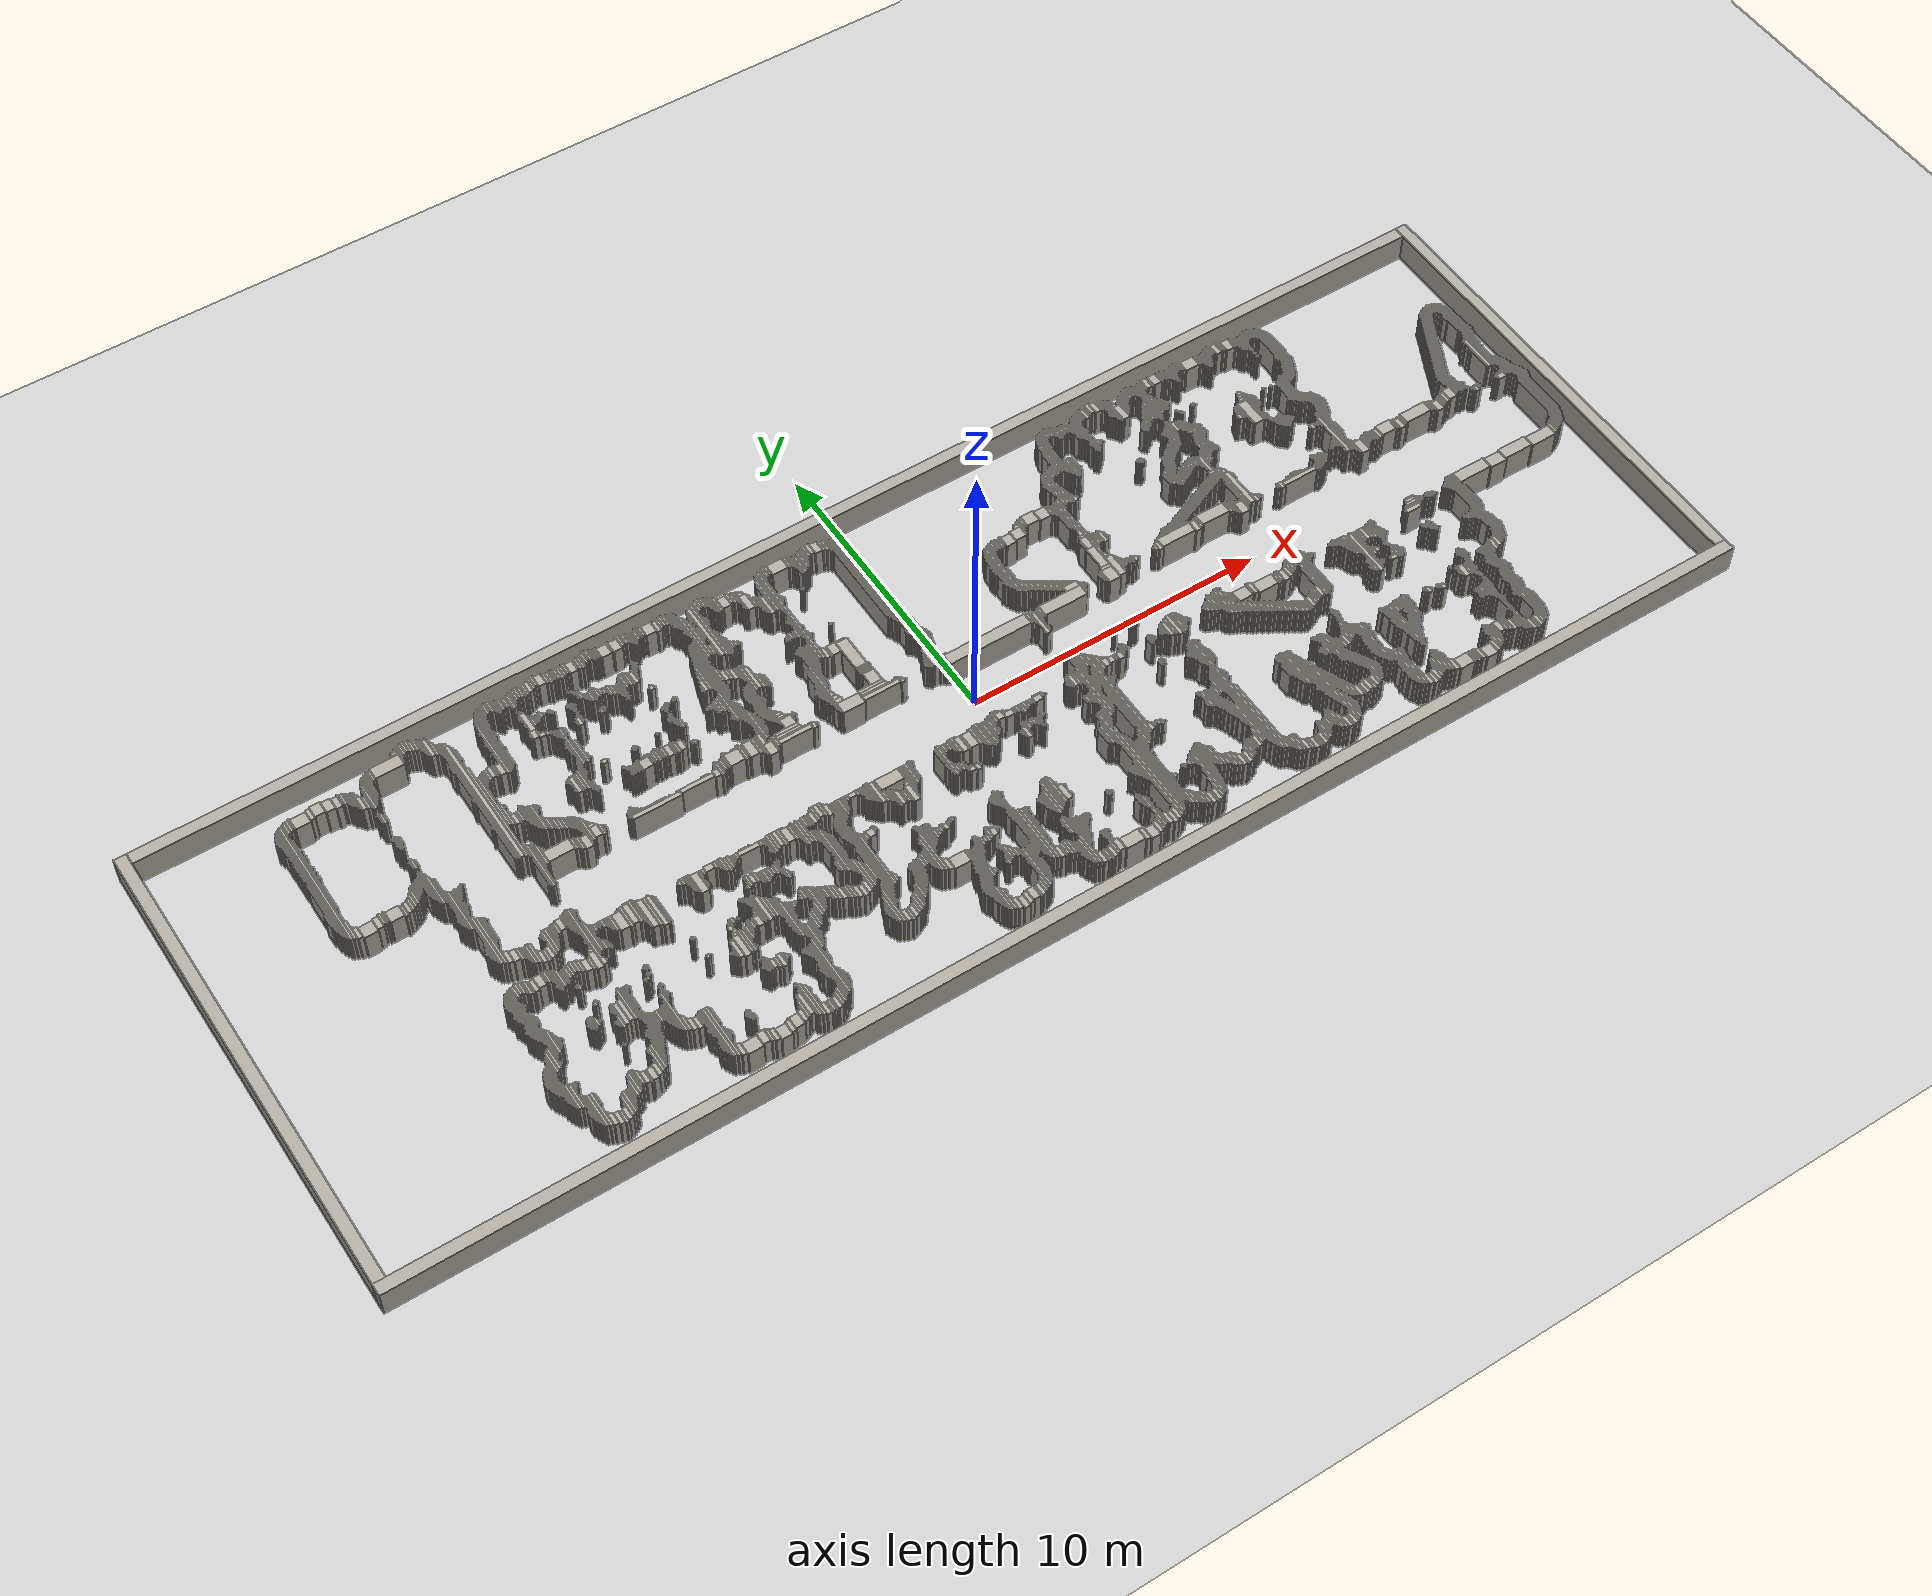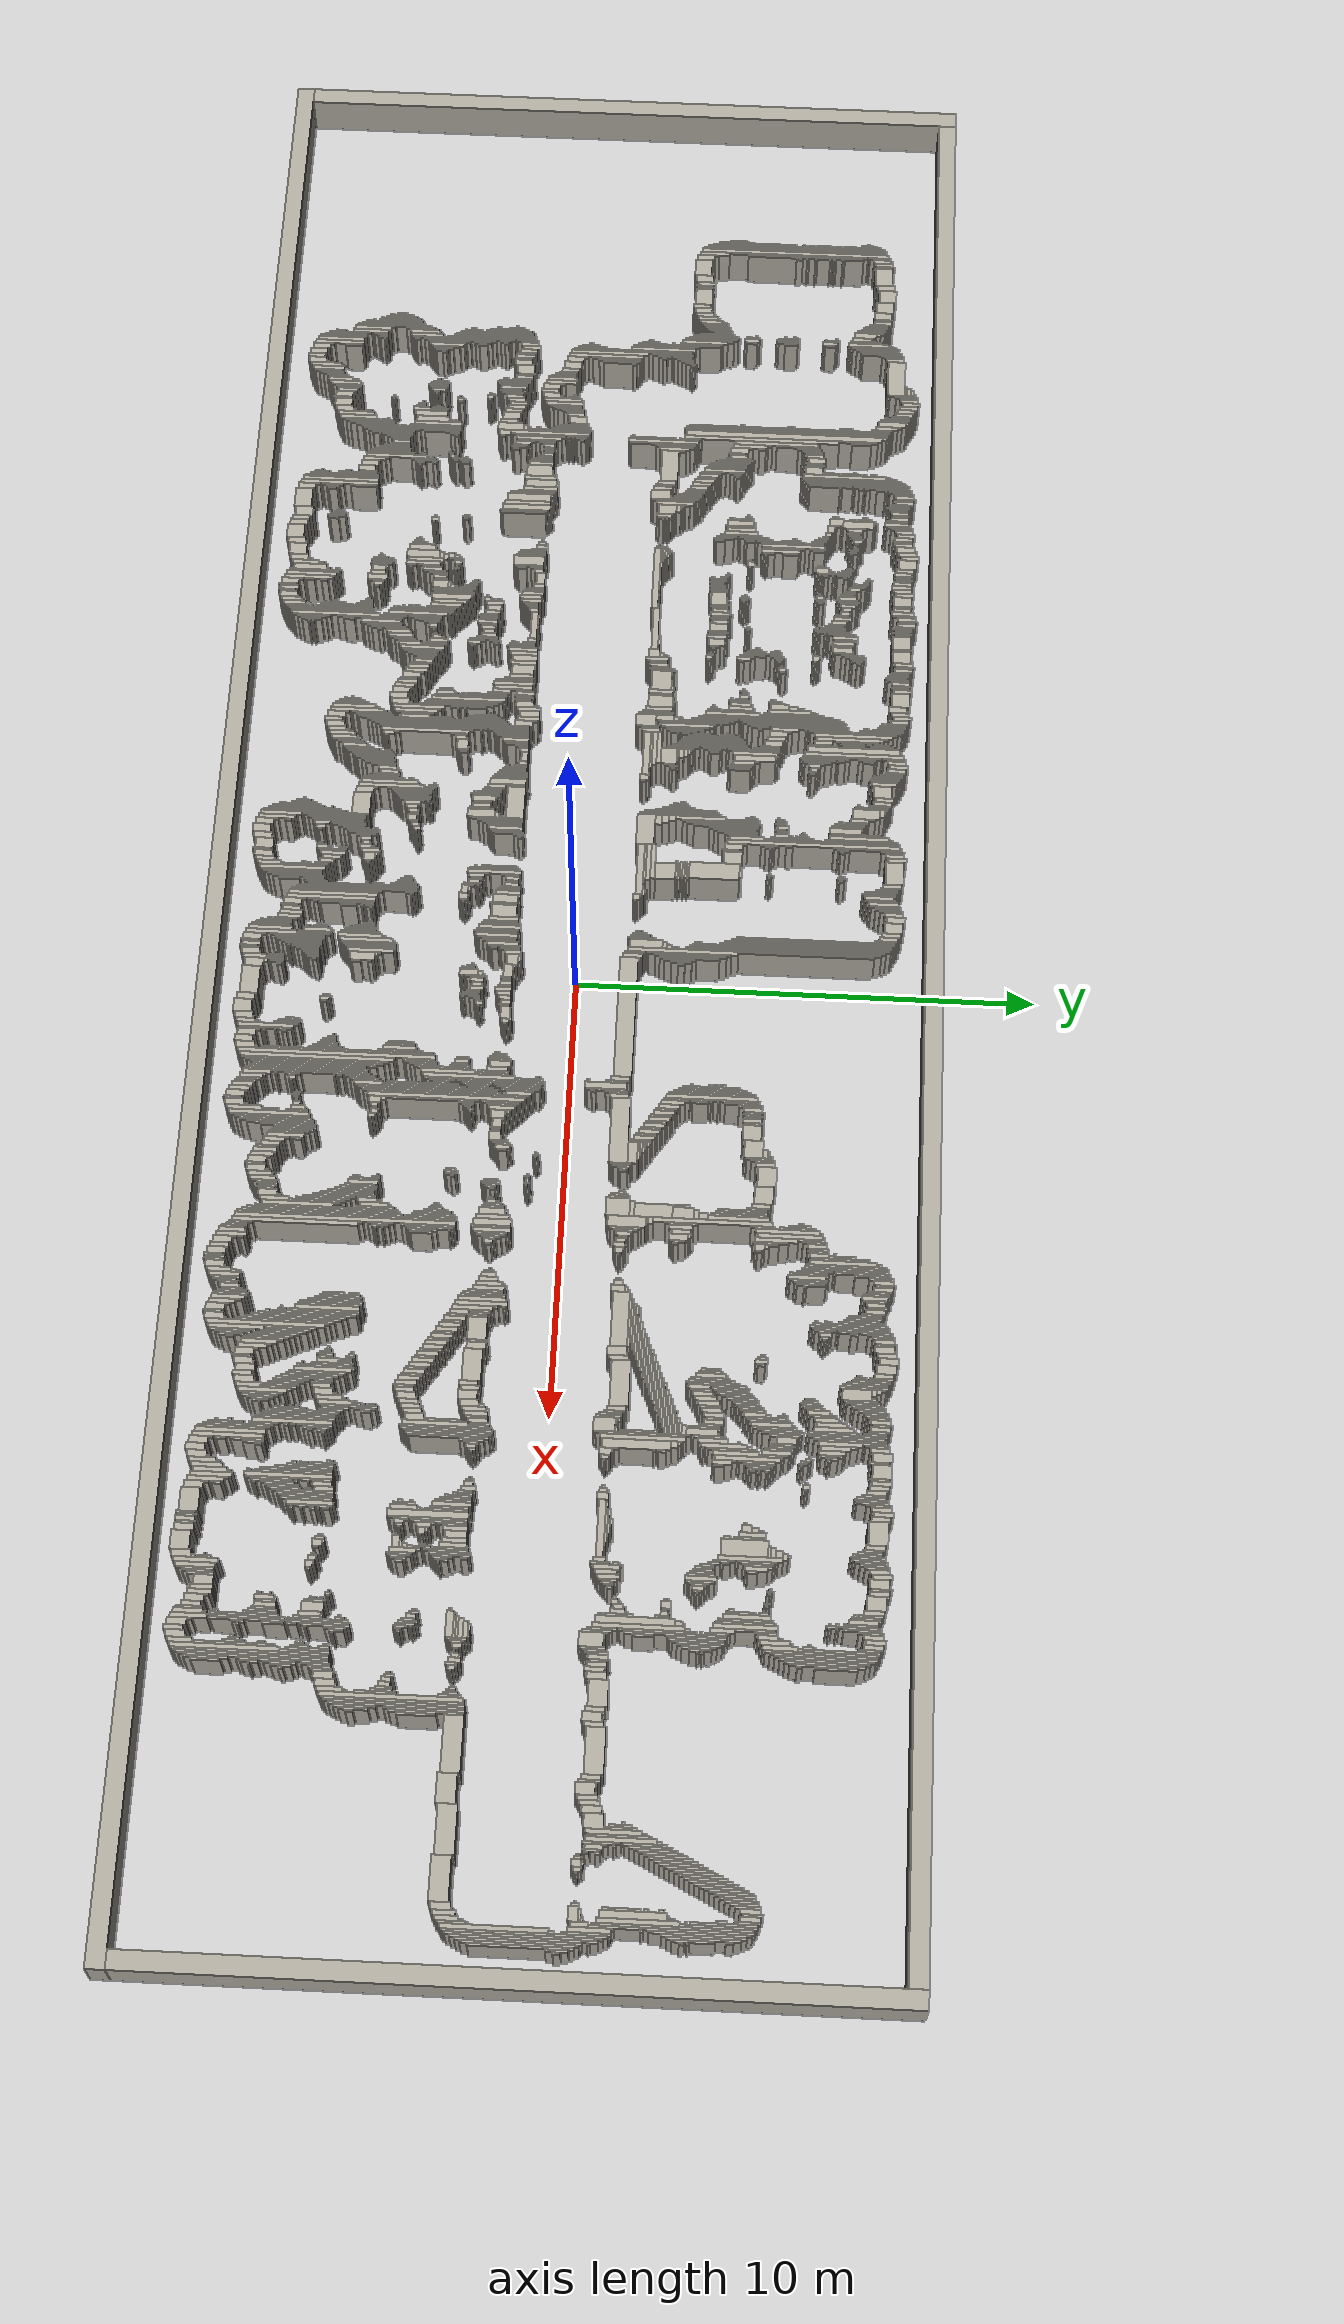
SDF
<?xml version="1.0" ?>
<sdf version="1.6">
  <world name="fr079_office">

    <include><uri>model://sun</uri></include>
    <include><uri>model://ground_plane</uri></include>

    <physics type="ode">
      <max_step_size>0.004</max_step_size>
      <real_time_factor>1.0</real_time_factor>
      <real_time_update_rate>250.0</real_time_update_rate>
    </physics>

    <scene>
      <ambient>0.6 0.6 0.6 1</ambient>
      <shadows>false</shadows>
    </scene>

    <model name="fr079_office_walls">
      <static>true</static>
      <link name="w0000">
        <pose>-0.923 -7.956 0.500 0 0 0</pose>
        <collision name="c"><geometry><box><size>45.450 0.400 1.000</size></box></geometry></collision>
        <visual name="v"><geometry><box><size>45.450 0.400 1.000</size></box></geometry>
          <material><ambient>0.68 0.66 0.62 1</ambient><diffuse>0.68 0.66 0.62 1</diffuse></material>
        </visual>
      </link>
      <link name="w0001">
        <pose>-23.448 0.094 0.500 0 0 0</pose>
        <collision name="c"><geometry><box><size>0.400 15.700 1.000</size></box></geometry></collision>
        <visual name="v"><geometry><box><size>0.400 15.700 1.000</size></box></geometry>
          <material><ambient>0.68 0.66 0.62 1</ambient><diffuse>0.68 0.66 0.62 1</diffuse></material>
        </visual>
      </link>
      <link name="w0002">
        <pose>21.602 0.094 0.500 0 0 0</pose>
        <collision name="c"><geometry><box><size>0.400 15.700 1.000</size></box></geometry></collision>
        <visual name="v"><geometry><box><size>0.400 15.700 1.000</size></box></geometry>
          <material><ambient>0.68 0.66 0.62 1</ambient><diffuse>0.68 0.66 0.62 1</diffuse></material>
        </visual>
      </link>
      <link name="w0003">
        <pose>13.252 -7.206 0.500 0 0 0</pose>
        <collision name="c"><geometry><box><size>0.400 0.400 1.000</size></box></geometry></collision>
        <visual name="v"><geometry><box><size>0.400 0.400 1.000</size></box></geometry>
          <material><ambient>0.68 0.66 0.62 1</ambient><diffuse>0.68 0.66 0.62 1</diffuse></material>
        </visual>
      </link>
      <link name="w0004">
        <pose>7.077 -7.156 0.500 0 0 0</pose>
        <collision name="c"><geometry><box><size>0.050 0.400 1.000</size></box></geometry></collision>
        <visual name="v"><geometry><box><size>0.050 0.400 1.000</size></box></geometry>
          <material><ambient>0.68 0.66 0.62 1</ambient><diffuse>0.68 0.66 0.62 1</diffuse></material>
        </visual>
      </link>
      <link name="w0005">
        <pose>7.177 -7.156 0.500 0 0 0</pose>
        <collision name="c"><geometry><box><size>0.050 0.400 1.000</size></box></geometry></collision>
        <visual name="v"><geometry><box><size>0.050 0.400 1.000</size></box></geometry>
          <material><ambient>0.68 0.66 0.62 1</ambient><diffuse>0.68 0.66 0.62 1</diffuse></material>
        </visual>
      </link>
      <link name="w0006">
        <pose>12.677 -7.156 0.500 0 0 0</pose>
        <collision name="c"><geometry><box><size>0.050 0.400 1.000</size></box></geometry></collision>
        <visual name="v"><geometry><box><size>0.050 0.400 1.000</size></box></geometry>
          <material><ambient>0.68 0.66 0.62 1</ambient><diffuse>0.68 0.66 0.62 1</diffuse></material>
        </visual>
      </link>
      <link name="w0007">
        <pose>12.802 -7.156 0.500 0 0 0</pose>
        <collision name="c"><geometry><box><size>0.100 0.400 1.000</size></box></geometry></collision>
        <visual name="v"><geometry><box><size>0.100 0.400 1.000</size></box></geometry>
          <material><ambient>0.68 0.66 0.62 1</ambient><diffuse>0.68 0.66 0.62 1</diffuse></material>
        </visual>
      </link>
      <link name="w0008">
        <pose>12.977 -7.156 0.500 0 0 0</pose>
        <collision name="c"><geometry><box><size>0.150 0.400 1.000</size></box></geometry></collision>
        <visual name="v"><geometry><box><size>0.150 0.400 1.000</size></box></geometry>
          <material><ambient>0.68 0.66 0.62 1</ambient><diffuse>0.68 0.66 0.62 1</diffuse></material>
        </visual>
      </link>
      <link name="w0009">
        <pose>13.527 -7.156 0.500 0 0 0</pose>
        <collision name="c"><geometry><box><size>0.150 0.400 1.000</size></box></geometry></collision>
        <visual name="v"><geometry><box><size>0.150 0.400 1.000</size></box></geometry>
          <material><ambient>0.68 0.66 0.62 1</ambient><diffuse>0.68 0.66 0.62 1</diffuse></material>
        </visual>
      </link>
      <link name="w0010">
        <pose>15.052 -7.156 0.500 0 0 0</pose>
        <collision name="c"><geometry><box><size>0.100 0.400 1.000</size></box></geometry></collision>
        <visual name="v"><geometry><box><size>0.100 0.400 1.000</size></box></geometry>
          <material><ambient>0.68 0.66 0.62 1</ambient><diffuse>0.68 0.66 0.62 1</diffuse></material>
        </visual>
      </link>
      <link name="w0011">
        <pose>-9.373 -7.106 0.500 0 0 0</pose>
        <collision name="c"><geometry><box><size>0.050 0.400 1.000</size></box></geometry></collision>
        <visual name="v"><geometry><box><size>0.050 0.400 1.000</size></box></geometry>
          <material><ambient>0.68 0.66 0.62 1</ambient><diffuse>0.68 0.66 0.62 1</diffuse></material>
        </visual>
      </link>
      <link name="w0012">
        <pose>-9.223 -7.106 0.500 0 0 0</pose>
        <collision name="c"><geometry><box><size>0.050 0.400 1.000</size></box></geometry></collision>
        <visual name="v"><geometry><box><size>0.050 0.400 1.000</size></box></geometry>
          <material><ambient>0.68 0.66 0.62 1</ambient><diffuse>0.68 0.66 0.62 1</diffuse></material>
        </visual>
      </link>
      <link name="w0013">
        <pose>-3.048 -7.106 0.500 0 0 0</pose>
        <collision name="c"><geometry><box><size>0.200 0.400 1.000</size></box></geometry></collision>
        <visual name="v"><geometry><box><size>0.200 0.400 1.000</size></box></geometry>
          <material><ambient>0.68 0.66 0.62 1</ambient><diffuse>0.68 0.66 0.62 1</diffuse></material>
        </visual>
      </link>
      <link name="w0014">
        <pose>-0.273 -7.106 0.500 0 0 0</pose>
        <collision name="c"><geometry><box><size>0.050 0.400 1.000</size></box></geometry></collision>
        <visual name="v"><geometry><box><size>0.050 0.400 1.000</size></box></geometry>
          <material><ambient>0.68 0.66 0.62 1</ambient><diffuse>0.68 0.66 0.62 1</diffuse></material>
        </visual>
      </link>
      <link name="w0015">
        <pose>-0.123 -7.106 0.500 0 0 0</pose>
        <collision name="c"><geometry><box><size>0.050 0.400 1.000</size></box></geometry></collision>
        <visual name="v"><geometry><box><size>0.050 0.400 1.000</size></box></geometry>
          <material><ambient>0.68 0.66 0.62 1</ambient><diffuse>0.68 0.66 0.62 1</diffuse></material>
        </visual>
      </link>
      <link name="w0016">
        <pose>1.302 -7.106 0.500 0 0 0</pose>
        <collision name="c"><geometry><box><size>0.300 0.400 1.000</size></box></geometry></collision>
        <visual name="v"><geometry><box><size>0.300 0.400 1.000</size></box></geometry>
          <material><ambient>0.68 0.66 0.62 1</ambient><diffuse>0.68 0.66 0.62 1</diffuse></material>
        </visual>
      </link>
      <link name="w0017">
        <pose>3.477 -7.106 0.500 0 0 0</pose>
        <collision name="c"><geometry><box><size>0.050 0.400 1.000</size></box></geometry></collision>
        <visual name="v"><geometry><box><size>0.050 0.400 1.000</size></box></geometry>
          <material><ambient>0.68 0.66 0.62 1</ambient><diffuse>0.68 0.66 0.62 1</diffuse></material>
        </visual>
      </link>
      <link name="w0018">
        <pose>6.977 -7.106 0.500 0 0 0</pose>
        <collision name="c"><geometry><box><size>0.150 0.400 1.000</size></box></geometry></collision>
        <visual name="v"><geometry><box><size>0.150 0.400 1.000</size></box></geometry>
          <material><ambient>0.68 0.66 0.62 1</ambient><diffuse>0.68 0.66 0.62 1</diffuse></material>
        </visual>
      </link>
      <link name="w0019">
        <pose>7.127 -7.106 0.500 0 0 0</pose>
        <collision name="c"><geometry><box><size>0.050 0.400 1.000</size></box></geometry></collision>
        <visual name="v"><geometry><box><size>0.050 0.400 1.000</size></box></geometry>
          <material><ambient>0.68 0.66 0.62 1</ambient><diffuse>0.68 0.66 0.62 1</diffuse></material>
        </visual>
      </link>
      <link name="w0020">
        <pose>7.277 -7.106 0.500 0 0 0</pose>
        <collision name="c"><geometry><box><size>0.150 0.400 1.000</size></box></geometry></collision>
        <visual name="v"><geometry><box><size>0.150 0.400 1.000</size></box></geometry>
          <material><ambient>0.68 0.66 0.62 1</ambient><diffuse>0.68 0.66 0.62 1</diffuse></material>
        </visual>
      </link>
      <link name="w0021">
        <pose>11.277 -7.106 0.500 0 0 0</pose>
        <collision name="c"><geometry><box><size>0.150 0.400 1.000</size></box></geometry></collision>
        <visual name="v"><geometry><box><size>0.150 0.400 1.000</size></box></geometry>
          <material><ambient>0.68 0.66 0.62 1</ambient><diffuse>0.68 0.66 0.62 1</diffuse></material>
        </visual>
      </link>
      <link name="w0022">
        <pose>12.402 -7.106 0.500 0 0 0</pose>
        <collision name="c"><geometry><box><size>0.500 0.400 1.000</size></box></geometry></collision>
        <visual name="v"><geometry><box><size>0.500 0.400 1.000</size></box></geometry>
          <material><ambient>0.68 0.66 0.62 1</ambient><diffuse>0.68 0.66 0.62 1</diffuse></material>
        </visual>
      </link>
      <link name="w0023">
        <pose>12.727 -7.106 0.500 0 0 0</pose>
        <collision name="c"><geometry><box><size>0.050 0.400 1.000</size></box></geometry></collision>
        <visual name="v"><geometry><box><size>0.050 0.400 1.000</size></box></geometry>
          <material><ambient>0.68 0.66 0.62 1</ambient><diffuse>0.68 0.66 0.62 1</diffuse></material>
        </visual>
      </link>
      <link name="w0024">
        <pose>12.877 -7.106 0.500 0 0 0</pose>
        <collision name="c"><geometry><box><size>0.050 0.400 1.000</size></box></geometry></collision>
        <visual name="v"><geometry><box><size>0.050 0.400 1.000</size></box></geometry>
          <material><ambient>0.68 0.66 0.62 1</ambient><diffuse>0.68 0.66 0.62 1</diffuse></material>
        </visual>
      </link>
      <link name="w0025">
        <pose>13.652 -6.856 0.500 0 0 0</pose>
        <collision name="c"><geometry><box><size>0.100 0.900 1.000</size></box></geometry></collision>
        <visual name="v"><geometry><box><size>0.100 0.900 1.000</size></box></geometry>
          <material><ambient>0.68 0.66 0.62 1</ambient><diffuse>0.68 0.66 0.62 1</diffuse></material>
        </visual>
      </link>
      <link name="w0026">
        <pose>14.927 -7.106 0.500 0 0 0</pose>
        <collision name="c"><geometry><box><size>0.150 0.400 1.000</size></box></geometry></collision>
        <visual name="v"><geometry><box><size>0.150 0.400 1.000</size></box></geometry>
          <material><ambient>0.68 0.66 0.62 1</ambient><diffuse>0.68 0.66 0.62 1</diffuse></material>
        </visual>
      </link>
      <link name="w0027">
        <pose>15.177 -7.106 0.500 0 0 0</pose>
        <collision name="c"><geometry><box><size>0.150 0.400 1.000</size></box></geometry></collision>
        <visual name="v"><geometry><box><size>0.150 0.400 1.000</size></box></geometry>
          <material><ambient>0.68 0.66 0.62 1</ambient><diffuse>0.68 0.66 0.62 1</diffuse></material>
        </visual>
      </link>
      <link name="w0028">
        <pose>-10.823 -7.056 0.500 0 0 0</pose>
        <collision name="c"><geometry><box><size>0.350 0.400 1.000</size></box></geometry></collision>
        <visual name="v"><geometry><box><size>0.350 0.400 1.000</size></box></geometry>
          <material><ambient>0.68 0.66 0.62 1</ambient><diffuse>0.68 0.66 0.62 1</diffuse></material>
        </visual>
      </link>
      <link name="w0029">
        <pose>-9.473 -7.056 0.500 0 0 0</pose>
        <collision name="c"><geometry><box><size>0.150 0.400 1.000</size></box></geometry></collision>
        <visual name="v"><geometry><box><size>0.150 0.400 1.000</size></box></geometry>
          <material><ambient>0.68 0.66 0.62 1</ambient><diffuse>0.68 0.66 0.62 1</diffuse></material>
        </visual>
      </link>
      <link name="w0030">
        <pose>-9.298 -7.056 0.500 0 0 0</pose>
        <collision name="c"><geometry><box><size>0.100 0.400 1.000</size></box></geometry></collision>
        <visual name="v"><geometry><box><size>0.100 0.400 1.000</size></box></geometry>
          <material><ambient>0.68 0.66 0.62 1</ambient><diffuse>0.68 0.66 0.62 1</diffuse></material>
        </visual>
      </link>
      <link name="w0031">
        <pose>-9.123 -7.056 0.500 0 0 0</pose>
        <collision name="c"><geometry><box><size>0.150 0.400 1.000</size></box></geometry></collision>
        <visual name="v"><geometry><box><size>0.150 0.400 1.000</size></box></geometry>
          <material><ambient>0.68 0.66 0.62 1</ambient><diffuse>0.68 0.66 0.62 1</diffuse></material>
        </visual>
      </link>
      <link name="w0032">
        <pose>-3.223 -7.056 0.500 0 0 0</pose>
        <collision name="c"><geometry><box><size>0.150 0.400 1.000</size></box></geometry></collision>
        <visual name="v"><geometry><box><size>0.150 0.400 1.000</size></box></geometry>
          <material><ambient>0.68 0.66 0.62 1</ambient><diffuse>0.68 0.66 0.62 1</diffuse></material>
        </visual>
      </link>
      <link name="w0033">
        <pose>-2.873 -7.056 0.500 0 0 0</pose>
        <collision name="c"><geometry><box><size>0.150 0.400 1.000</size></box></geometry></collision>
        <visual name="v"><geometry><box><size>0.150 0.400 1.000</size></box></geometry>
          <material><ambient>0.68 0.66 0.62 1</ambient><diffuse>0.68 0.66 0.62 1</diffuse></material>
        </visual>
      </link>
      <link name="w0034">
        <pose>-2.523 -7.056 0.500 0 0 0</pose>
        <collision name="c"><geometry><box><size>0.050 0.400 1.000</size></box></geometry></collision>
        <visual name="v"><geometry><box><size>0.050 0.400 1.000</size></box></geometry>
          <material><ambient>0.68 0.66 0.62 1</ambient><diffuse>0.68 0.66 0.62 1</diffuse></material>
        </visual>
      </link>
      <link name="w0035">
        <pose>-0.373 -7.056 0.500 0 0 0</pose>
        <collision name="c"><geometry><box><size>0.150 0.400 1.000</size></box></geometry></collision>
        <visual name="v"><geometry><box><size>0.150 0.400 1.000</size></box></geometry>
          <material><ambient>0.68 0.66 0.62 1</ambient><diffuse>0.68 0.66 0.62 1</diffuse></material>
        </visual>
      </link>
      <link name="w0036">
        <pose>-0.198 -7.056 0.500 0 0 0</pose>
        <collision name="c"><geometry><box><size>0.100 0.400 1.000</size></box></geometry></collision>
        <visual name="v"><geometry><box><size>0.100 0.400 1.000</size></box></geometry>
          <material><ambient>0.68 0.66 0.62 1</ambient><diffuse>0.68 0.66 0.62 1</diffuse></material>
        </visual>
      </link>
      <link name="w0037">
        <pose>-0.023 -7.056 0.500 0 0 0</pose>
        <collision name="c"><geometry><box><size>0.150 0.400 1.000</size></box></geometry></collision>
        <visual name="v"><geometry><box><size>0.150 0.400 1.000</size></box></geometry>
          <material><ambient>0.68 0.66 0.62 1</ambient><diffuse>0.68 0.66 0.62 1</diffuse></material>
        </visual>
      </link>
      <link name="w0038">
        <pose>1.077 -7.056 0.500 0 0 0</pose>
        <collision name="c"><geometry><box><size>0.150 0.400 1.000</size></box></geometry></collision>
        <visual name="v"><geometry><box><size>0.150 0.400 1.000</size></box></geometry>
          <material><ambient>0.68 0.66 0.62 1</ambient><diffuse>0.68 0.66 0.62 1</diffuse></material>
        </visual>
      </link>
      <link name="w0039">
        <pose>1.527 -7.056 0.500 0 0 0</pose>
        <collision name="c"><geometry><box><size>0.150 0.400 1.000</size></box></geometry></collision>
        <visual name="v"><geometry><box><size>0.150 0.400 1.000</size></box></geometry>
          <material><ambient>0.68 0.66 0.62 1</ambient><diffuse>0.68 0.66 0.62 1</diffuse></material>
        </visual>
      </link>
      <link name="w0040">
        <pose>3.377 -7.056 0.500 0 0 0</pose>
        <collision name="c"><geometry><box><size>0.150 0.400 1.000</size></box></geometry></collision>
        <visual name="v"><geometry><box><size>0.150 0.400 1.000</size></box></geometry>
          <material><ambient>0.68 0.66 0.62 1</ambient><diffuse>0.68 0.66 0.62 1</diffuse></material>
        </visual>
      </link>
      <link name="w0041">
        <pose>3.577 -7.056 0.500 0 0 0</pose>
        <collision name="c"><geometry><box><size>0.150 0.400 1.000</size></box></geometry></collision>
        <visual name="v"><geometry><box><size>0.150 0.400 1.000</size></box></geometry>
          <material><ambient>0.68 0.66 0.62 1</ambient><diffuse>0.68 0.66 0.62 1</diffuse></material>
        </visual>
      </link>
      <link name="w0042">
        <pose>6.852 -7.056 0.500 0 0 0</pose>
        <collision name="c"><geometry><box><size>0.100 0.400 1.000</size></box></geometry></collision>
        <visual name="v"><geometry><box><size>0.100 0.400 1.000</size></box></geometry>
          <material><ambient>0.68 0.66 0.62 1</ambient><diffuse>0.68 0.66 0.62 1</diffuse></material>
        </visual>
      </link>
      <link name="w0043">
        <pose>7.402 -7.006 0.500 0 0 0</pose>
        <collision name="c"><geometry><box><size>0.100 0.500 1.000</size></box></geometry></collision>
        <visual name="v"><geometry><box><size>0.100 0.500 1.000</size></box></geometry>
          <material><ambient>0.68 0.66 0.62 1</ambient><diffuse>0.68 0.66 0.62 1</diffuse></material>
        </visual>
      </link>
      <link name="w0044">
        <pose>8.327 -7.056 0.500 0 0 0</pose>
        <collision name="c"><geometry><box><size>0.050 0.400 1.000</size></box></geometry></collision>
        <visual name="v"><geometry><box><size>0.050 0.400 1.000</size></box></geometry>
          <material><ambient>0.68 0.66 0.62 1</ambient><diffuse>0.68 0.66 0.62 1</diffuse></material>
        </visual>
      </link>
      <link name="w0045">
        <pose>11.127 -7.056 0.500 0 0 0</pose>
        <collision name="c"><geometry><box><size>0.150 0.400 1.000</size></box></geometry></collision>
        <visual name="v"><geometry><box><size>0.150 0.400 1.000</size></box></geometry>
          <material><ambient>0.68 0.66 0.62 1</ambient><diffuse>0.68 0.66 0.62 1</diffuse></material>
        </visual>
      </link>
      <link name="w0046">
        <pose>11.427 -7.056 0.500 0 0 0</pose>
        <collision name="c"><geometry><box><size>0.150 0.400 1.000</size></box></geometry></collision>
        <visual name="v"><geometry><box><size>0.150 0.400 1.000</size></box></geometry>
          <material><ambient>0.68 0.66 0.62 1</ambient><diffuse>0.68 0.66 0.62 1</diffuse></material>
        </visual>
      </link>
      <link name="w0047">
        <pose>12.077 -7.056 0.500 0 0 0</pose>
        <collision name="c"><geometry><box><size>0.150 0.400 1.000</size></box></geometry></collision>
        <visual name="v"><geometry><box><size>0.150 0.400 1.000</size></box></geometry>
          <material><ambient>0.68 0.66 0.62 1</ambient><diffuse>0.68 0.66 0.62 1</diffuse></material>
        </visual>
      </link>
      <link name="w0048">
        <pose>13.752 -6.856 0.500 0 0 0</pose>
        <collision name="c"><geometry><box><size>0.100 0.800 1.000</size></box></geometry></collision>
        <visual name="v"><geometry><box><size>0.100 0.800 1.000</size></box></geometry>
          <material><ambient>0.68 0.66 0.62 1</ambient><diffuse>0.68 0.66 0.62 1</diffuse></material>
        </visual>
      </link>
      <link name="w0049">
        <pose>14.802 -6.881 0.500 0 0 0</pose>
        <collision name="c"><geometry><box><size>0.100 0.750 1.000</size></box></geometry></collision>
        <visual name="v"><geometry><box><size>0.100 0.750 1.000</size></box></geometry>
          <material><ambient>0.68 0.66 0.62 1</ambient><diffuse>0.68 0.66 0.62 1</diffuse></material>
        </visual>
      </link>
      <link name="w0050">
        <pose>15.302 -7.006 0.500 0 0 0</pose>
        <collision name="c"><geometry><box><size>0.100 0.500 1.000</size></box></geometry></collision>
        <visual name="v"><geometry><box><size>0.100 0.500 1.000</size></box></geometry>
          <material><ambient>0.68 0.66 0.62 1</ambient><diffuse>0.68 0.66 0.62 1</diffuse></material>
        </visual>
      </link>
      <link name="w0051">
        <pose>-15.748 -7.006 0.500 0 0 0</pose>
        <collision name="c"><geometry><box><size>0.100 0.400 1.000</size></box></geometry></collision>
        <visual name="v"><geometry><box><size>0.100 0.400 1.000</size></box></geometry>
          <material><ambient>0.68 0.66 0.62 1</ambient><diffuse>0.68 0.66 0.62 1</diffuse></material>
        </visual>
      </link>
      <link name="w0052">
        <pose>-11.073 -7.006 0.500 0 0 0</pose>
        <collision name="c"><geometry><box><size>0.150 0.400 1.000</size></box></geometry></collision>
        <visual name="v"><geometry><box><size>0.150 0.400 1.000</size></box></geometry>
          <material><ambient>0.68 0.66 0.62 1</ambient><diffuse>0.68 0.66 0.62 1</diffuse></material>
        </visual>
      </link>
      <link name="w0053">
        <pose>-10.573 -7.006 0.500 0 0 0</pose>
        <collision name="c"><geometry><box><size>0.150 0.400 1.000</size></box></geometry></collision>
        <visual name="v"><geometry><box><size>0.150 0.400 1.000</size></box></geometry>
          <material><ambient>0.68 0.66 0.62 1</ambient><diffuse>0.68 0.66 0.62 1</diffuse></material>
        </visual>
      </link>
      <link name="w0054">
        <pose>-9.598 -6.656 0.500 0 0 0</pose>
        <collision name="c"><geometry><box><size>0.100 1.100 1.000</size></box></geometry></collision>
        <visual name="v"><geometry><box><size>0.100 1.100 1.000</size></box></geometry>
          <material><ambient>0.68 0.66 0.62 1</ambient><diffuse>0.68 0.66 0.62 1</diffuse></material>
        </visual>
      </link>
      <link name="w0055">
        <pose>-8.998 -6.981 0.500 0 0 0</pose>
        <collision name="c"><geometry><box><size>0.100 0.450 1.000</size></box></geometry></collision>
        <visual name="v"><geometry><box><size>0.100 0.450 1.000</size></box></geometry>
          <material><ambient>0.68 0.66 0.62 1</ambient><diffuse>0.68 0.66 0.62 1</diffuse></material>
        </visual>
      </link>
      <link name="w0056">
        <pose>-3.348 -6.806 0.500 0 0 0</pose>
        <collision name="c"><geometry><box><size>0.100 0.800 1.000</size></box></geometry></collision>
        <visual name="v"><geometry><box><size>0.100 0.800 1.000</size></box></geometry>
          <material><ambient>0.68 0.66 0.62 1</ambient><diffuse>0.68 0.66 0.62 1</diffuse></material>
        </visual>
      </link>
      <link name="w0057">
        <pose>-2.673 -7.006 0.500 0 0 0</pose>
        <collision name="c"><geometry><box><size>0.250 0.400 1.000</size></box></geometry></collision>
        <visual name="v"><geometry><box><size>0.250 0.400 1.000</size></box></geometry>
          <material><ambient>0.68 0.66 0.62 1</ambient><diffuse>0.68 0.66 0.62 1</diffuse></material>
        </visual>
      </link>
      <link name="w0058">
        <pose>-2.423 -7.006 0.500 0 0 0</pose>
        <collision name="c"><geometry><box><size>0.150 0.400 1.000</size></box></geometry></collision>
        <visual name="v"><geometry><box><size>0.150 0.400 1.000</size></box></geometry>
          <material><ambient>0.68 0.66 0.62 1</ambient><diffuse>0.68 0.66 0.62 1</diffuse></material>
        </visual>
      </link>
      <link name="w0059">
        <pose>-0.498 -6.656 0.500 0 0 0</pose>
        <collision name="c"><geometry><box><size>0.100 1.100 1.000</size></box></geometry></collision>
        <visual name="v"><geometry><box><size>0.100 1.100 1.000</size></box></geometry>
          <material><ambient>0.68 0.66 0.62 1</ambient><diffuse>0.68 0.66 0.62 1</diffuse></material>
        </visual>
      </link>
      <link name="w0060">
        <pose>0.102 -6.956 0.500 0 0 0</pose>
        <collision name="c"><geometry><box><size>0.100 0.500 1.000</size></box></geometry></collision>
        <visual name="v"><geometry><box><size>0.100 0.500 1.000</size></box></geometry>
          <material><ambient>0.68 0.66 0.62 1</ambient><diffuse>0.68 0.66 0.62 1</diffuse></material>
        </visual>
      </link>
      <link name="w0061">
        <pose>0.677 -7.006 0.500 0 0 0</pose>
        <collision name="c"><geometry><box><size>0.650 0.400 1.000</size></box></geometry></collision>
        <visual name="v"><geometry><box><size>0.650 0.400 1.000</size></box></geometry>
          <material><ambient>0.68 0.66 0.62 1</ambient><diffuse>0.68 0.66 0.62 1</diffuse></material>
        </visual>
      </link>
      <link name="w0062">
        <pose>1.652 -7.006 0.500 0 0 0</pose>
        <collision name="c"><geometry><box><size>0.100 0.400 1.000</size></box></geometry></collision>
        <visual name="v"><geometry><box><size>0.100 0.400 1.000</size></box></geometry>
          <material><ambient>0.68 0.66 0.62 1</ambient><diffuse>0.68 0.66 0.62 1</diffuse></material>
        </visual>
      </link>
      <link name="w0063">
        <pose>2.077 -7.006 0.500 0 0 0</pose>
        <collision name="c"><geometry><box><size>0.150 0.400 1.000</size></box></geometry></collision>
        <visual name="v"><geometry><box><size>0.150 0.400 1.000</size></box></geometry>
          <material><ambient>0.68 0.66 0.62 1</ambient><diffuse>0.68 0.66 0.62 1</diffuse></material>
        </visual>
      </link>
      <link name="w0064">
        <pose>3.252 -6.981 0.500 0 0 0</pose>
        <collision name="c"><geometry><box><size>0.100 0.450 1.000</size></box></geometry></collision>
        <visual name="v"><geometry><box><size>0.100 0.450 1.000</size></box></geometry>
          <material><ambient>0.68 0.66 0.62 1</ambient><diffuse>0.68 0.66 0.62 1</diffuse></material>
        </visual>
      </link>
      <link name="w0065">
        <pose>3.702 -6.831 0.500 0 0 0</pose>
        <collision name="c"><geometry><box><size>0.100 0.750 1.000</size></box></geometry></collision>
        <visual name="v"><geometry><box><size>0.100 0.750 1.000</size></box></geometry>
          <material><ambient>0.68 0.66 0.62 1</ambient><diffuse>0.68 0.66 0.62 1</diffuse></material>
        </visual>
      </link>
      <link name="w0066">
        <pose>6.727 -7.006 0.500 0 0 0</pose>
        <collision name="c"><geometry><box><size>0.150 0.400 1.000</size></box></geometry></collision>
        <visual name="v"><geometry><box><size>0.150 0.400 1.000</size></box></geometry>
          <material><ambient>0.68 0.66 0.62 1</ambient><diffuse>0.68 0.66 0.62 1</diffuse></material>
        </visual>
      </link>
      <link name="w0067">
        <pose>7.502 -6.881 0.500 0 0 0</pose>
        <collision name="c"><geometry><box><size>0.100 0.650 1.000</size></box></geometry></collision>
        <visual name="v"><geometry><box><size>0.100 0.650 1.000</size></box></geometry>
          <material><ambient>0.68 0.66 0.62 1</ambient><diffuse>0.68 0.66 0.62 1</diffuse></material>
        </visual>
      </link>
      <link name="w0068">
        <pose>8.227 -7.006 0.500 0 0 0</pose>
        <collision name="c"><geometry><box><size>0.150 0.400 1.000</size></box></geometry></collision>
        <visual name="v"><geometry><box><size>0.150 0.400 1.000</size></box></geometry>
          <material><ambient>0.68 0.66 0.62 1</ambient><diffuse>0.68 0.66 0.62 1</diffuse></material>
        </visual>
      </link>
      <link name="w0069">
        <pose>8.427 -7.006 0.500 0 0 0</pose>
        <collision name="c"><geometry><box><size>0.150 0.400 1.000</size></box></geometry></collision>
        <visual name="v"><geometry><box><size>0.150 0.400 1.000</size></box></geometry>
          <material><ambient>0.68 0.66 0.62 1</ambient><diffuse>0.68 0.66 0.62 1</diffuse></material>
        </visual>
      </link>
      <link name="w0070">
        <pose>11.002 -6.481 0.500 0 0 0</pose>
        <collision name="c"><geometry><box><size>0.100 1.450 1.000</size></box></geometry></collision>
        <visual name="v"><geometry><box><size>0.100 1.450 1.000</size></box></geometry>
          <material><ambient>0.68 0.66 0.62 1</ambient><diffuse>0.68 0.66 0.62 1</diffuse></material>
        </visual>
      </link>
      <link name="w0071">
        <pose>11.552 -6.931 0.500 0 0 0</pose>
        <collision name="c"><geometry><box><size>0.100 0.550 1.000</size></box></geometry></collision>
        <visual name="v"><geometry><box><size>0.100 0.550 1.000</size></box></geometry>
          <material><ambient>0.68 0.66 0.62 1</ambient><diffuse>0.68 0.66 0.62 1</diffuse></material>
        </visual>
      </link>
      <link name="w0072">
        <pose>11.952 -6.831 0.500 0 0 0</pose>
        <collision name="c"><geometry><box><size>0.100 0.750 1.000</size></box></geometry></collision>
        <visual name="v"><geometry><box><size>0.100 0.750 1.000</size></box></geometry>
          <material><ambient>0.68 0.66 0.62 1</ambient><diffuse>0.68 0.66 0.62 1</diffuse></material>
        </visual>
      </link>
      <link name="w0073">
        <pose>13.827 -6.831 0.500 0 0 0</pose>
        <collision name="c"><geometry><box><size>0.050 0.750 1.000</size></box></geometry></collision>
        <visual name="v"><geometry><box><size>0.050 0.750 1.000</size></box></geometry>
          <material><ambient>0.68 0.66 0.62 1</ambient><diffuse>0.68 0.66 0.62 1</diffuse></material>
        </visual>
      </link>
      <link name="w0074">
        <pose>14.702 -6.906 0.500 0 0 0</pose>
        <collision name="c"><geometry><box><size>0.100 0.600 1.000</size></box></geometry></collision>
        <visual name="v"><geometry><box><size>0.100 0.600 1.000</size></box></geometry>
          <material><ambient>0.68 0.66 0.62 1</ambient><diffuse>0.68 0.66 0.62 1</diffuse></material>
        </visual>
      </link>
      <link name="w0075">
        <pose>15.402 -6.106 0.500 0 0 0</pose>
        <collision name="c"><geometry><box><size>0.100 2.200 1.000</size></box></geometry></collision>
        <visual name="v"><geometry><box><size>0.100 2.200 1.000</size></box></geometry>
          <material><ambient>0.68 0.66 0.62 1</ambient><diffuse>0.68 0.66 0.62 1</diffuse></material>
        </visual>
      </link>
      <link name="w0076">
        <pose>-15.873 -6.956 0.500 0 0 0</pose>
        <collision name="c"><geometry><box><size>0.150 0.400 1.000</size></box></geometry></collision>
        <visual name="v"><geometry><box><size>0.150 0.400 1.000</size></box></geometry>
          <material><ambient>0.68 0.66 0.62 1</ambient><diffuse>0.68 0.66 0.62 1</diffuse></material>
        </visual>
      </link>
      <link name="w0077">
        <pose>-15.623 -6.956 0.500 0 0 0</pose>
        <collision name="c"><geometry><box><size>0.150 0.400 1.000</size></box></geometry></collision>
        <visual name="v"><geometry><box><size>0.150 0.400 1.000</size></box></geometry>
          <material><ambient>0.68 0.66 0.62 1</ambient><diffuse>0.68 0.66 0.62 1</diffuse></material>
        </visual>
      </link>
      <link name="w0078">
        <pose>-11.748 -6.956 0.500 0 0 0</pose>
        <collision name="c"><geometry><box><size>0.500 0.400 1.000</size></box></geometry></collision>
        <visual name="v"><geometry><box><size>0.500 0.400 1.000</size></box></geometry>
          <material><ambient>0.68 0.66 0.62 1</ambient><diffuse>0.68 0.66 0.62 1</diffuse></material>
        </visual>
      </link>
      <link name="w0079">
        <pose>-11.198 -6.956 0.500 0 0 0</pose>
        <collision name="c"><geometry><box><size>0.100 0.400 1.000</size></box></geometry></collision>
        <visual name="v"><geometry><box><size>0.100 0.400 1.000</size></box></geometry>
          <material><ambient>0.68 0.66 0.62 1</ambient><diffuse>0.68 0.66 0.62 1</diffuse></material>
        </visual>
      </link>
      <link name="w0080">
        <pose>-10.348 -6.956 0.500 0 0 0</pose>
        <collision name="c"><geometry><box><size>0.300 0.400 1.000</size></box></geometry></collision>
        <visual name="v"><geometry><box><size>0.300 0.400 1.000</size></box></geometry>
          <material><ambient>0.68 0.66 0.62 1</ambient><diffuse>0.68 0.66 0.62 1</diffuse></material>
        </visual>
      </link>
      <link name="w0081">
        <pose>-9.698 -6.581 0.500 0 0 0</pose>
        <collision name="c"><geometry><box><size>0.100 1.150 1.000</size></box></geometry></collision>
        <visual name="v"><geometry><box><size>0.100 1.150 1.000</size></box></geometry>
          <material><ambient>0.68 0.66 0.62 1</ambient><diffuse>0.68 0.66 0.62 1</diffuse></material>
        </visual>
      </link>
      <link name="w0082">
        <pose>-8.898 -6.906 0.500 0 0 0</pose>
        <collision name="c"><geometry><box><size>0.100 0.500 1.000</size></box></geometry></collision>
        <visual name="v"><geometry><box><size>0.100 0.500 1.000</size></box></geometry>
          <material><ambient>0.68 0.66 0.62 1</ambient><diffuse>0.68 0.66 0.62 1</diffuse></material>
        </visual>
      </link>
      <link name="w0083">
        <pose>-3.448 -6.706 0.500 0 0 0</pose>
        <collision name="c"><geometry><box><size>0.100 0.900 1.000</size></box></geometry></collision>
        <visual name="v"><geometry><box><size>0.100 0.900 1.000</size></box></geometry>
          <material><ambient>0.68 0.66 0.62 1</ambient><diffuse>0.68 0.66 0.62 1</diffuse></material>
        </visual>
      </link>
      <link name="w0084">
        <pose>-2.298 -6.956 0.500 0 0 0</pose>
        <collision name="c"><geometry><box><size>0.100 0.400 1.000</size></box></geometry></collision>
        <visual name="v"><geometry><box><size>0.100 0.400 1.000</size></box></geometry>
          <material><ambient>0.68 0.66 0.62 1</ambient><diffuse>0.68 0.66 0.62 1</diffuse></material>
        </visual>
      </link>
      <link name="w0085">
        <pose>-0.598 -6.681 0.500 0 0 0</pose>
        <collision name="c"><geometry><box><size>0.100 0.950 1.000</size></box></geometry></collision>
        <visual name="v"><geometry><box><size>0.100 0.950 1.000</size></box></geometry>
          <material><ambient>0.68 0.66 0.62 1</ambient><diffuse>0.68 0.66 0.62 1</diffuse></material>
        </visual>
      </link>
      <link name="w0086">
        <pose>0.252 -6.956 0.500 0 0 0</pose>
        <collision name="c"><geometry><box><size>0.200 0.400 1.000</size></box></geometry></collision>
        <visual name="v"><geometry><box><size>0.200 0.400 1.000</size></box></geometry>
          <material><ambient>0.68 0.66 0.62 1</ambient><diffuse>0.68 0.66 0.62 1</diffuse></material>
        </visual>
      </link>
      <link name="w0087">
        <pose>1.752 -6.556 0.500 0 0 0</pose>
        <collision name="c"><geometry><box><size>0.100 1.200 1.000</size></box></geometry></collision>
        <visual name="v"><geometry><box><size>0.100 1.200 1.000</size></box></geometry>
          <material><ambient>0.68 0.66 0.62 1</ambient><diffuse>0.68 0.66 0.62 1</diffuse></material>
        </visual>
      </link>
      <link name="w0088">
        <pose>1.927 -6.956 0.500 0 0 0</pose>
        <collision name="c"><geometry><box><size>0.150 0.400 1.000</size></box></geometry></collision>
        <visual name="v"><geometry><box><size>0.150 0.400 1.000</size></box></geometry>
          <material><ambient>0.68 0.66 0.62 1</ambient><diffuse>0.68 0.66 0.62 1</diffuse></material>
        </visual>
      </link>
      <link name="w0089">
        <pose>2.227 -6.956 0.500 0 0 0</pose>
        <collision name="c"><geometry><box><size>0.150 0.400 1.000</size></box></geometry></collision>
        <visual name="v"><geometry><box><size>0.150 0.400 1.000</size></box></geometry>
          <material><ambient>0.68 0.66 0.62 1</ambient><diffuse>0.68 0.66 0.62 1</diffuse></material>
        </visual>
      </link>
      <link name="w0090">
        <pose>3.152 -6.931 0.500 0 0 0</pose>
        <collision name="c"><geometry><box><size>0.100 0.450 1.000</size></box></geometry></collision>
        <visual name="v"><geometry><box><size>0.100 0.450 1.000</size></box></geometry>
          <material><ambient>0.68 0.66 0.62 1</ambient><diffuse>0.68 0.66 0.62 1</diffuse></material>
        </visual>
      </link>
      <link name="w0091">
        <pose>3.802 -6.306 0.500 0 0 0</pose>
        <collision name="c"><geometry><box><size>0.100 1.700 1.000</size></box></geometry></collision>
        <visual name="v"><geometry><box><size>0.100 1.700 1.000</size></box></geometry>
          <material><ambient>0.68 0.66 0.62 1</ambient><diffuse>0.68 0.66 0.62 1</diffuse></material>
        </visual>
      </link>
      <link name="w0092">
        <pose>6.602 -6.831 0.500 0 0 0</pose>
        <collision name="c"><geometry><box><size>0.100 0.650 1.000</size></box></geometry></collision>
        <visual name="v"><geometry><box><size>0.100 0.650 1.000</size></box></geometry>
          <material><ambient>0.68 0.66 0.62 1</ambient><diffuse>0.68 0.66 0.62 1</diffuse></material>
        </visual>
      </link>
      <link name="w0093">
        <pose>7.577 -6.856 0.500 0 0 0</pose>
        <collision name="c"><geometry><box><size>0.050 0.600 1.000</size></box></geometry></collision>
        <visual name="v"><geometry><box><size>0.050 0.600 1.000</size></box></geometry>
          <material><ambient>0.68 0.66 0.62 1</ambient><diffuse>0.68 0.66 0.62 1</diffuse></material>
        </visual>
      </link>
      <link name="w0094">
        <pose>8.102 -6.881 0.500 0 0 0</pose>
        <collision name="c"><geometry><box><size>0.100 0.550 1.000</size></box></geometry></collision>
        <visual name="v"><geometry><box><size>0.100 0.550 1.000</size></box></geometry>
          <material><ambient>0.68 0.66 0.62 1</ambient><diffuse>0.68 0.66 0.62 1</diffuse></material>
        </visual>
      </link>
      <link name="w0095">
        <pose>8.552 -5.931 0.500 0 0 0</pose>
        <collision name="c"><geometry><box><size>0.100 2.450 1.000</size></box></geometry></collision>
        <visual name="v"><geometry><box><size>0.100 2.450 1.000</size></box></geometry>
          <material><ambient>0.68 0.66 0.62 1</ambient><diffuse>0.68 0.66 0.62 1</diffuse></material>
        </visual>
      </link>
      <link name="w0096">
        <pose>10.902 -6.431 0.500 0 0 0</pose>
        <collision name="c"><geometry><box><size>0.100 1.450 1.000</size></box></geometry></collision>
        <visual name="v"><geometry><box><size>0.100 1.450 1.000</size></box></geometry>
          <material><ambient>0.68 0.66 0.62 1</ambient><diffuse>0.68 0.66 0.62 1</diffuse></material>
        </visual>
      </link>
      <link name="w0097">
        <pose>11.652 -6.831 0.500 0 0 0</pose>
        <collision name="c"><geometry><box><size>0.100 0.650 1.000</size></box></geometry></collision>
        <visual name="v"><geometry><box><size>0.100 0.650 1.000</size></box></geometry>
          <material><ambient>0.68 0.66 0.62 1</ambient><diffuse>0.68 0.66 0.62 1</diffuse></material>
        </visual>
      </link>
      <link name="w0098">
        <pose>11.852 -6.731 0.500 0 0 0</pose>
        <collision name="c"><geometry><box><size>0.100 0.850 1.000</size></box></geometry></collision>
        <visual name="v"><geometry><box><size>0.100 0.850 1.000</size></box></geometry>
          <material><ambient>0.68 0.66 0.62 1</ambient><diffuse>0.68 0.66 0.62 1</diffuse></material>
        </visual>
      </link>
      <link name="w0099">
        <pose>14.627 -6.881 0.500 0 0 0</pose>
        <collision name="c"><geometry><box><size>0.050 0.550 1.000</size></box></geometry></collision>
        <visual name="v"><geometry><box><size>0.050 0.550 1.000</size></box></geometry>
          <material><ambient>0.68 0.66 0.62 1</ambient><diffuse>0.68 0.66 0.62 1</diffuse></material>
        </visual>
      </link>
      <link name="w0100">
        <pose>15.477 -5.581 0.500 0 0 0</pose>
        <collision name="c"><geometry><box><size>0.050 3.150 1.000</size></box></geometry></collision>
        <visual name="v"><geometry><box><size>0.050 3.150 1.000</size></box></geometry>
          <material><ambient>0.68 0.66 0.62 1</ambient><diffuse>0.68 0.66 0.62 1</diffuse></material>
        </visual>
      </link>
      <link name="w0101">
        <pose>-16.023 -6.906 0.500 0 0 0</pose>
        <collision name="c"><geometry><box><size>0.150 0.400 1.000</size></box></geometry></collision>
        <visual name="v"><geometry><box><size>0.150 0.400 1.000</size></box></geometry>
          <material><ambient>0.68 0.66 0.62 1</ambient><diffuse>0.68 0.66 0.62 1</diffuse></material>
        </visual>
      </link>
      <link name="w0102">
        <pose>-15.498 -6.756 0.500 0 0 0</pose>
        <collision name="c"><geometry><box><size>0.100 0.700 1.000</size></box></geometry></collision>
        <visual name="v"><geometry><box><size>0.100 0.700 1.000</size></box></geometry>
          <material><ambient>0.68 0.66 0.62 1</ambient><diffuse>0.68 0.66 0.62 1</diffuse></material>
        </visual>
      </link>
      <link name="w0103">
        <pose>-12.073 -6.906 0.500 0 0 0</pose>
        <collision name="c"><geometry><box><size>0.150 0.400 1.000</size></box></geometry></collision>
        <visual name="v"><geometry><box><size>0.150 0.400 1.000</size></box></geometry>
          <material><ambient>0.68 0.66 0.62 1</ambient><diffuse>0.68 0.66 0.62 1</diffuse></material>
        </visual>
      </link>
      <link name="w0104">
        <pose>-11.373 -6.906 0.500 0 0 0</pose>
        <collision name="c"><geometry><box><size>0.250 0.400 1.000</size></box></geometry></collision>
        <visual name="v"><geometry><box><size>0.250 0.400 1.000</size></box></geometry>
          <material><ambient>0.68 0.66 0.62 1</ambient><diffuse>0.68 0.66 0.62 1</diffuse></material>
        </visual>
      </link>
      <link name="w0105">
        <pose>-10.123 -6.906 0.500 0 0 0</pose>
        <collision name="c"><geometry><box><size>0.150 0.400 1.000</size></box></geometry></collision>
        <visual name="v"><geometry><box><size>0.150 0.400 1.000</size></box></geometry>
          <material><ambient>0.68 0.66 0.62 1</ambient><diffuse>0.68 0.66 0.62 1</diffuse></material>
        </visual>
      </link>
      <link name="w0106">
        <pose>-9.773 -6.506 0.500 0 0 0</pose>
        <collision name="c"><geometry><box><size>0.050 1.200 1.000</size></box></geometry></collision>
        <visual name="v"><geometry><box><size>0.050 1.200 1.000</size></box></geometry>
          <material><ambient>0.68 0.66 0.62 1</ambient><diffuse>0.68 0.66 0.62 1</diffuse></material>
        </visual>
      </link>
      <link name="w0107">
        <pose>-8.823 -6.831 0.500 0 0 0</pose>
        <collision name="c"><geometry><box><size>0.050 0.550 1.000</size></box></geometry></collision>
        <visual name="v"><geometry><box><size>0.050 0.550 1.000</size></box></geometry>
          <material><ambient>0.68 0.66 0.62 1</ambient><diffuse>0.68 0.66 0.62 1</diffuse></material>
        </visual>
      </link>
      <link name="w0108">
        <pose>-3.523 -6.181 0.500 0 0 0</pose>
        <collision name="c"><geometry><box><size>0.050 1.850 1.000</size></box></geometry></collision>
        <visual name="v"><geometry><box><size>0.050 1.850 1.000</size></box></geometry>
          <material><ambient>0.68 0.66 0.62 1</ambient><diffuse>0.68 0.66 0.62 1</diffuse></material>
        </visual>
      </link>
      <link name="w0109">
        <pose>-2.198 -6.856 0.500 0 0 0</pose>
        <collision name="c"><geometry><box><size>0.100 0.500 1.000</size></box></geometry></collision>
        <visual name="v"><geometry><box><size>0.100 0.500 1.000</size></box></geometry>
          <material><ambient>0.68 0.66 0.62 1</ambient><diffuse>0.68 0.66 0.62 1</diffuse></material>
        </visual>
      </link>
      <link name="w0110">
        <pose>-0.673 -6.681 0.500 0 0 0</pose>
        <collision name="c"><geometry><box><size>0.050 0.850 1.000</size></box></geometry></collision>
        <visual name="v"><geometry><box><size>0.050 0.850 1.000</size></box></geometry>
          <material><ambient>0.68 0.66 0.62 1</ambient><diffuse>0.68 0.66 0.62 1</diffuse></material>
        </visual>
      </link>
      <link name="w0111">
        <pose>1.827 -6.556 0.500 0 0 0</pose>
        <collision name="c"><geometry><box><size>0.050 1.100 1.000</size></box></geometry></collision>
        <visual name="v"><geometry><box><size>0.050 1.100 1.000</size></box></geometry>
          <material><ambient>0.68 0.66 0.62 1</ambient><diffuse>0.68 0.66 0.62 1</diffuse></material>
        </visual>
      </link>
      <link name="w0112">
        <pose>2.352 -4.981 0.500 0 0 0</pose>
        <collision name="c"><geometry><box><size>0.100 4.250 1.000</size></box></geometry></collision>
        <visual name="v"><geometry><box><size>0.100 4.250 1.000</size></box></geometry>
          <material><ambient>0.68 0.66 0.62 1</ambient><diffuse>0.68 0.66 0.62 1</diffuse></material>
        </visual>
      </link>
      <link name="w0113">
        <pose>3.077 -6.881 0.500 0 0 0</pose>
        <collision name="c"><geometry><box><size>0.050 0.450 1.000</size></box></geometry></collision>
        <visual name="v"><geometry><box><size>0.050 0.450 1.000</size></box></geometry>
          <material><ambient>0.68 0.66 0.62 1</ambient><diffuse>0.68 0.66 0.62 1</diffuse></material>
        </visual>
      </link>
      <link name="w0114">
        <pose>3.877 -6.256 0.500 0 0 0</pose>
        <collision name="c"><geometry><box><size>0.050 1.700 1.000</size></box></geometry></collision>
        <visual name="v"><geometry><box><size>0.050 1.700 1.000</size></box></geometry>
          <material><ambient>0.68 0.66 0.62 1</ambient><diffuse>0.68 0.66 0.62 1</diffuse></material>
        </visual>
      </link>
      <link name="w0115">
        <pose>6.502 -6.831 0.500 0 0 0</pose>
        <collision name="c"><geometry><box><size>0.100 0.550 1.000</size></box></geometry></collision>
        <visual name="v"><geometry><box><size>0.100 0.550 1.000</size></box></geometry>
          <material><ambient>0.68 0.66 0.62 1</ambient><diffuse>0.68 0.66 0.62 1</diffuse></material>
        </visual>
      </link>
      <link name="w0116">
        <pose>7.627 -6.856 0.500 0 0 0</pose>
        <collision name="c"><geometry><box><size>0.050 0.500 1.000</size></box></geometry></collision>
        <visual name="v"><geometry><box><size>0.050 0.500 1.000</size></box></geometry>
          <material><ambient>0.68 0.66 0.62 1</ambient><diffuse>0.68 0.66 0.62 1</diffuse></material>
        </visual>
      </link>
      <link name="w0117">
        <pose>8.002 -6.756 0.500 0 0 0</pose>
        <collision name="c"><geometry><box><size>0.100 0.700 1.000</size></box></geometry></collision>
        <visual name="v"><geometry><box><size>0.100 0.700 1.000</size></box></geometry>
          <material><ambient>0.68 0.66 0.62 1</ambient><diffuse>0.68 0.66 0.62 1</diffuse></material>
        </visual>
      </link>
      <link name="w0118">
        <pose>8.652 -6.531 0.500 0 0 0</pose>
        <collision name="c"><geometry><box><size>0.100 1.150 1.000</size></box></geometry></collision>
        <visual name="v"><geometry><box><size>0.100 1.150 1.000</size></box></geometry>
          <material><ambient>0.68 0.66 0.62 1</ambient><diffuse>0.68 0.66 0.62 1</diffuse></material>
        </visual>
      </link>
      <link name="w0119">
        <pose>10.827 -6.356 0.500 0 0 0</pose>
        <collision name="c"><geometry><box><size>0.050 1.500 1.000</size></box></geometry></collision>
        <visual name="v"><geometry><box><size>0.050 1.500 1.000</size></box></geometry>
          <material><ambient>0.68 0.66 0.62 1</ambient><diffuse>0.68 0.66 0.62 1</diffuse></material>
        </visual>
      </link>
      <link name="w0120">
        <pose>11.752 -6.756 0.500 0 0 0</pose>
        <collision name="c"><geometry><box><size>0.100 0.700 1.000</size></box></geometry></collision>
        <visual name="v"><geometry><box><size>0.100 0.700 1.000</size></box></geometry>
          <material><ambient>0.68 0.66 0.62 1</ambient><diffuse>0.68 0.66 0.62 1</diffuse></material>
        </visual>
      </link>
      <link name="w0121">
        <pose>13.877 -6.806 0.500 0 0 0</pose>
        <collision name="c"><geometry><box><size>0.050 0.600 1.000</size></box></geometry></collision>
        <visual name="v"><geometry><box><size>0.050 0.600 1.000</size></box></geometry>
          <material><ambient>0.68 0.66 0.62 1</ambient><diffuse>0.68 0.66 0.62 1</diffuse></material>
        </visual>
      </link>
      <link name="w0122">
        <pose>15.527 -5.556 0.500 0 0 0</pose>
        <collision name="c"><geometry><box><size>0.050 3.100 1.000</size></box></geometry></collision>
        <visual name="v"><geometry><box><size>0.050 3.100 1.000</size></box></geometry>
          <material><ambient>0.68 0.66 0.62 1</ambient><diffuse>0.68 0.66 0.62 1</diffuse></material>
        </visual>
      </link>
      <link name="w0123">
        <pose>-16.148 -6.481 0.500 0 0 0</pose>
        <collision name="c"><geometry><box><size>0.100 1.150 1.000</size></box></geometry></collision>
        <visual name="v"><geometry><box><size>0.100 1.150 1.000</size></box></geometry>
          <material><ambient>0.68 0.66 0.62 1</ambient><diffuse>0.68 0.66 0.62 1</diffuse></material>
        </visual>
      </link>
      <link name="w0124">
        <pose>-15.398 -6.681 0.500 0 0 0</pose>
        <collision name="c"><geometry><box><size>0.100 0.750 1.000</size></box></geometry></collision>
        <visual name="v"><geometry><box><size>0.100 0.750 1.000</size></box></geometry>
          <material><ambient>0.68 0.66 0.62 1</ambient><diffuse>0.68 0.66 0.62 1</diffuse></material>
        </visual>
      </link>
      <link name="w0125">
        <pose>-12.198 -6.156 0.500 0 0 0</pose>
        <collision name="c"><geometry><box><size>0.100 1.800 1.000</size></box></geometry></collision>
        <visual name="v"><geometry><box><size>0.100 1.800 1.000</size></box></geometry>
          <material><ambient>0.68 0.66 0.62 1</ambient><diffuse>0.68 0.66 0.62 1</diffuse></material>
        </visual>
      </link>
      <link name="w0126">
        <pose>-9.998 -6.756 0.500 0 0 0</pose>
        <collision name="c"><geometry><box><size>0.100 0.600 1.000</size></box></geometry></collision>
        <visual name="v"><geometry><box><size>0.100 0.600 1.000</size></box></geometry>
          <material><ambient>0.68 0.66 0.62 1</ambient><diffuse>0.68 0.66 0.62 1</diffuse></material>
        </visual>
      </link>
      <link name="w0127">
        <pose>-8.773 -6.056 0.500 0 0 0</pose>
        <collision name="c"><geometry><box><size>0.050 2.000 1.000</size></box></geometry></collision>
        <visual name="v"><geometry><box><size>0.050 2.000 1.000</size></box></geometry>
          <material><ambient>0.68 0.66 0.62 1</ambient><diffuse>0.68 0.66 0.62 1</diffuse></material>
        </visual>
      </link>
      <link name="w0128">
        <pose>-2.098 -6.331 0.500 0 0 0</pose>
        <collision name="c"><geometry><box><size>0.100 1.450 1.000</size></box></geometry></collision>
        <visual name="v"><geometry><box><size>0.100 1.450 1.000</size></box></geometry>
          <material><ambient>0.68 0.66 0.62 1</ambient><diffuse>0.68 0.66 0.62 1</diffuse></material>
        </visual>
      </link>
      <link name="w0129">
        <pose>2.452 -5.406 0.500 0 0 0</pose>
        <collision name="c"><geometry><box><size>0.100 3.300 1.000</size></box></geometry></collision>
        <visual name="v"><geometry><box><size>0.100 3.300 1.000</size></box></geometry>
          <material><ambient>0.68 0.66 0.62 1</ambient><diffuse>0.68 0.66 0.62 1</diffuse></material>
        </visual>
      </link>
      <link name="w0130">
        <pose>3.027 -6.806 0.500 0 0 0</pose>
        <collision name="c"><geometry><box><size>0.050 0.500 1.000</size></box></geometry></collision>
        <visual name="v"><geometry><box><size>0.050 0.500 1.000</size></box></geometry>
          <material><ambient>0.68 0.66 0.62 1</ambient><diffuse>0.68 0.66 0.62 1</diffuse></material>
        </visual>
      </link>
      <link name="w0131">
        <pose>6.427 -6.781 0.500 0 0 0</pose>
        <collision name="c"><geometry><box><size>0.050 0.550 1.000</size></box></geometry></collision>
        <visual name="v"><geometry><box><size>0.050 0.550 1.000</size></box></geometry>
          <material><ambient>0.68 0.66 0.62 1</ambient><diffuse>0.68 0.66 0.62 1</diffuse></material>
        </visual>
      </link>
      <link name="w0132">
        <pose>7.927 -6.681 0.500 0 0 0</pose>
        <collision name="c"><geometry><box><size>0.050 0.750 1.000</size></box></geometry></collision>
        <visual name="v"><geometry><box><size>0.050 0.750 1.000</size></box></geometry>
          <material><ambient>0.68 0.66 0.62 1</ambient><diffuse>0.68 0.66 0.62 1</diffuse></material>
        </visual>
      </link>
      <link name="w0133">
        <pose>8.727 -6.581 0.500 0 0 0</pose>
        <collision name="c"><geometry><box><size>0.050 0.950 1.000</size></box></geometry></collision>
        <visual name="v"><geometry><box><size>0.050 0.950 1.000</size></box></geometry>
          <material><ambient>0.68 0.66 0.62 1</ambient><diffuse>0.68 0.66 0.62 1</diffuse></material>
        </visual>
      </link>
      <link name="w0134">
        <pose>14.552 -6.856 0.500 0 0 0</pose>
        <collision name="c"><geometry><box><size>0.100 0.400 1.000</size></box></geometry></collision>
        <visual name="v"><geometry><box><size>0.100 0.400 1.000</size></box></geometry>
          <material><ambient>0.68 0.66 0.62 1</ambient><diffuse>0.68 0.66 0.62 1</diffuse></material>
        </visual>
      </link>
      <link name="w0135">
        <pose>-16.248 -6.456 0.500 0 0 0</pose>
        <collision name="c"><geometry><box><size>0.100 1.100 1.000</size></box></geometry></collision>
        <visual name="v"><geometry><box><size>0.100 1.100 1.000</size></box></geometry>
          <material><ambient>0.68 0.66 0.62 1</ambient><diffuse>0.68 0.66 0.62 1</diffuse></material>
        </visual>
      </link>
      <link name="w0136">
        <pose>-15.323 -6.681 0.500 0 0 0</pose>
        <collision name="c"><geometry><box><size>0.050 0.650 1.000</size></box></geometry></collision>
        <visual name="v"><geometry><box><size>0.050 0.650 1.000</size></box></geometry>
          <material><ambient>0.68 0.66 0.62 1</ambient><diffuse>0.68 0.66 0.62 1</diffuse></material>
        </visual>
      </link>
      <link name="w0137">
        <pose>-12.298 -6.131 0.500 0 0 0</pose>
        <collision name="c"><geometry><box><size>0.100 1.750 1.000</size></box></geometry></collision>
        <visual name="v"><geometry><box><size>0.100 1.750 1.000</size></box></geometry>
          <material><ambient>0.68 0.66 0.62 1</ambient><diffuse>0.68 0.66 0.62 1</diffuse></material>
        </visual>
      </link>
      <link name="w0138">
        <pose>-9.873 -6.631 0.500 0 0 0</pose>
        <collision name="c"><geometry><box><size>0.150 0.750 1.000</size></box></geometry></collision>
        <visual name="v"><geometry><box><size>0.150 0.750 1.000</size></box></geometry>
          <material><ambient>0.68 0.66 0.62 1</ambient><diffuse>0.68 0.66 0.62 1</diffuse></material>
        </visual>
      </link>
      <link name="w0139">
        <pose>-8.723 -6.031 0.500 0 0 0</pose>
        <collision name="c"><geometry><box><size>0.050 1.950 1.000</size></box></geometry></collision>
        <visual name="v"><geometry><box><size>0.050 1.950 1.000</size></box></geometry>
          <material><ambient>0.68 0.66 0.62 1</ambient><diffuse>0.68 0.66 0.62 1</diffuse></material>
        </visual>
      </link>
      <link name="w0140">
        <pose>-3.573 -6.206 0.500 0 0 0</pose>
        <collision name="c"><geometry><box><size>0.050 1.600 1.000</size></box></geometry></collision>
        <visual name="v"><geometry><box><size>0.050 1.600 1.000</size></box></geometry>
          <material><ambient>0.68 0.66 0.62 1</ambient><diffuse>0.68 0.66 0.62 1</diffuse></material>
        </visual>
      </link>
      <link name="w0141">
        <pose>-2.023 -6.331 0.500 0 0 0</pose>
        <collision name="c"><geometry><box><size>0.050 1.350 1.000</size></box></geometry></collision>
        <visual name="v"><geometry><box><size>0.050 1.350 1.000</size></box></geometry>
          <material><ambient>0.68 0.66 0.62 1</ambient><diffuse>0.68 0.66 0.62 1</diffuse></material>
        </visual>
      </link>
      <link name="w0142">
        <pose>-0.723 -6.606 0.500 0 0 0</pose>
        <collision name="c"><geometry><box><size>0.050 0.800 1.000</size></box></geometry></collision>
        <visual name="v"><geometry><box><size>0.050 0.800 1.000</size></box></geometry>
          <material><ambient>0.68 0.66 0.62 1</ambient><diffuse>0.68 0.66 0.62 1</diffuse></material>
        </visual>
      </link>
      <link name="w0143">
        <pose>2.527 -5.431 0.500 0 0 0</pose>
        <collision name="c"><geometry><box><size>0.050 3.150 1.000</size></box></geometry></collision>
        <visual name="v"><geometry><box><size>0.050 3.150 1.000</size></box></geometry>
          <material><ambient>0.68 0.66 0.62 1</ambient><diffuse>0.68 0.66 0.62 1</diffuse></material>
        </visual>
      </link>
      <link name="w0144">
        <pose>2.952 -6.756 0.500 0 0 0</pose>
        <collision name="c"><geometry><box><size>0.100 0.500 1.000</size></box></geometry></collision>
        <visual name="v"><geometry><box><size>0.100 0.500 1.000</size></box></geometry>
          <material><ambient>0.68 0.66 0.62 1</ambient><diffuse>0.68 0.66 0.62 1</diffuse></material>
        </visual>
      </link>
      <link name="w0145">
        <pose>3.927 -6.181 0.500 0 0 0</pose>
        <collision name="c"><geometry><box><size>0.050 1.650 1.000</size></box></geometry></collision>
        <visual name="v"><geometry><box><size>0.050 1.650 1.000</size></box></geometry>
          <material><ambient>0.68 0.66 0.62 1</ambient><diffuse>0.68 0.66 0.62 1</diffuse></material>
        </visual>
      </link>
      <link name="w0146">
        <pose>7.677 -6.781 0.500 0 0 0</pose>
        <collision name="c"><geometry><box><size>0.050 0.450 1.000</size></box></geometry></collision>
        <visual name="v"><geometry><box><size>0.050 0.450 1.000</size></box></geometry>
          <material><ambient>0.68 0.66 0.62 1</ambient><diffuse>0.68 0.66 0.62 1</diffuse></material>
        </visual>
      </link>
      <link name="w0147">
        <pose>10.777 -6.281 0.500 0 0 0</pose>
        <collision name="c"><geometry><box><size>0.050 1.450 1.000</size></box></geometry></collision>
        <visual name="v"><geometry><box><size>0.050 1.450 1.000</size></box></geometry>
          <material><ambient>0.68 0.66 0.62 1</ambient><diffuse>0.68 0.66 0.62 1</diffuse></material>
        </visual>
      </link>
      <link name="w0148">
        <pose>13.927 -6.731 0.500 0 0 0</pose>
        <collision name="c"><geometry><box><size>0.050 0.550 1.000</size></box></geometry></collision>
        <visual name="v"><geometry><box><size>0.050 0.550 1.000</size></box></geometry>
          <material><ambient>0.68 0.66 0.62 1</ambient><diffuse>0.68 0.66 0.62 1</diffuse></material>
        </visual>
      </link>
      <link name="w0149">
        <pose>14.427 -6.806 0.500 0 0 0</pose>
        <collision name="c"><geometry><box><size>0.150 0.400 1.000</size></box></geometry></collision>
        <visual name="v"><geometry><box><size>0.150 0.400 1.000</size></box></geometry>
          <material><ambient>0.68 0.66 0.62 1</ambient><diffuse>0.68 0.66 0.62 1</diffuse></material>
        </visual>
      </link>
      <link name="w0150">
        <pose>15.577 -5.506 0.500 0 0 0</pose>
        <collision name="c"><geometry><box><size>0.050 3.000 1.000</size></box></geometry></collision>
        <visual name="v"><geometry><box><size>0.050 3.000 1.000</size></box></geometry>
          <material><ambient>0.68 0.66 0.62 1</ambient><diffuse>0.68 0.66 0.62 1</diffuse></material>
        </visual>
      </link>
      <link name="w0151">
        <pose>-16.323 -6.406 0.500 0 0 0</pose>
        <collision name="c"><geometry><box><size>0.050 1.100 1.000</size></box></geometry></collision>
        <visual name="v"><geometry><box><size>0.050 1.100 1.000</size></box></geometry>
          <material><ambient>0.68 0.66 0.62 1</ambient><diffuse>0.68 0.66 0.62 1</diffuse></material>
        </visual>
      </link>
      <link name="w0152">
        <pose>-12.373 -6.106 0.500 0 0 0</pose>
        <collision name="c"><geometry><box><size>0.050 1.700 1.000</size></box></geometry></collision>
        <visual name="v"><geometry><box><size>0.050 1.700 1.000</size></box></geometry>
          <material><ambient>0.68 0.66 0.62 1</ambient><diffuse>0.68 0.66 0.62 1</diffuse></material>
        </visual>
      </link>
      <link name="w0153">
        <pose>-8.648 -5.956 0.500 0 0 0</pose>
        <collision name="c"><geometry><box><size>0.100 2.000 1.000</size></box></geometry></collision>
        <visual name="v"><geometry><box><size>0.100 2.000 1.000</size></box></geometry>
          <material><ambient>0.68 0.66 0.62 1</ambient><diffuse>0.68 0.66 0.62 1</diffuse></material>
        </visual>
      </link>
      <link name="w0154">
        <pose>-1.973 -6.306 0.500 0 0 0</pose>
        <collision name="c"><geometry><box><size>0.050 1.300 1.000</size></box></geometry></collision>
        <visual name="v"><geometry><box><size>0.050 1.300 1.000</size></box></geometry>
          <material><ambient>0.68 0.66 0.62 1</ambient><diffuse>0.68 0.66 0.62 1</diffuse></material>
        </visual>
      </link>
      <link name="w0155">
        <pose>2.852 -6.656 0.500 0 0 0</pose>
        <collision name="c"><geometry><box><size>0.100 0.600 1.000</size></box></geometry></collision>
        <visual name="v"><geometry><box><size>0.100 0.600 1.000</size></box></geometry>
          <material><ambient>0.68 0.66 0.62 1</ambient><diffuse>0.68 0.66 0.62 1</diffuse></material>
        </visual>
      </link>
      <link name="w0156">
        <pose>6.377 -6.731 0.500 0 0 0</pose>
        <collision name="c"><geometry><box><size>0.050 0.450 1.000</size></box></geometry></collision>
        <visual name="v"><geometry><box><size>0.050 0.450 1.000</size></box></geometry>
          <material><ambient>0.68 0.66 0.62 1</ambient><diffuse>0.68 0.66 0.62 1</diffuse></material>
        </visual>
      </link>
      <link name="w0157">
        <pose>7.752 -6.756 0.500 0 0 0</pose>
        <collision name="c"><geometry><box><size>0.100 0.400 1.000</size></box></geometry></collision>
        <visual name="v"><geometry><box><size>0.100 0.400 1.000</size></box></geometry>
          <material><ambient>0.68 0.66 0.62 1</ambient><diffuse>0.68 0.66 0.62 1</diffuse></material>
        </visual>
      </link>
      <link name="w0158">
        <pose>7.877 -6.656 0.500 0 0 0</pose>
        <collision name="c"><geometry><box><size>0.050 0.600 1.000</size></box></geometry></collision>
        <visual name="v"><geometry><box><size>0.050 0.600 1.000</size></box></geometry>
          <material><ambient>0.68 0.66 0.62 1</ambient><diffuse>0.68 0.66 0.62 1</diffuse></material>
        </visual>
      </link>
      <link name="w0159">
        <pose>8.777 -6.581 0.500 0 0 0</pose>
        <collision name="c"><geometry><box><size>0.050 0.750 1.000</size></box></geometry></collision>
        <visual name="v"><geometry><box><size>0.050 0.750 1.000</size></box></geometry>
          <material><ambient>0.68 0.66 0.62 1</ambient><diffuse>0.68 0.66 0.62 1</diffuse></material>
        </visual>
      </link>
      <link name="w0160">
        <pose>13.577 -6.906 0.500 0 0 0</pose>
        <collision name="c"><geometry><box><size>0.050 0.100 1.000</size></box></geometry></collision>
        <visual name="v"><geometry><box><size>0.050 0.100 1.000</size></box></geometry>
          <material><ambient>0.68 0.66 0.62 1</ambient><diffuse>0.68 0.66 0.62 1</diffuse></material>
        </visual>
      </link>
      <link name="w0161">
        <pose>14.302 -6.706 0.500 0 0 0</pose>
        <collision name="c"><geometry><box><size>0.100 0.500 1.000</size></box></geometry></collision>
        <visual name="v"><geometry><box><size>0.100 0.500 1.000</size></box></geometry>
          <material><ambient>0.68 0.66 0.62 1</ambient><diffuse>0.68 0.66 0.62 1</diffuse></material>
        </visual>
      </link>
      <link name="w0162">
        <pose>-15.273 -6.606 0.500 0 0 0</pose>
        <collision name="c"><geometry><box><size>0.050 0.600 1.000</size></box></geometry></collision>
        <visual name="v"><geometry><box><size>0.050 0.600 1.000</size></box></geometry>
          <material><ambient>0.68 0.66 0.62 1</ambient><diffuse>0.68 0.66 0.62 1</diffuse></material>
        </visual>
      </link>
      <link name="w0163">
        <pose>-8.573 -6.481 0.500 0 0 0</pose>
        <collision name="c"><geometry><box><size>0.050 0.850 1.000</size></box></geometry></collision>
        <visual name="v"><geometry><box><size>0.050 0.850 1.000</size></box></geometry>
          <material><ambient>0.68 0.66 0.62 1</ambient><diffuse>0.68 0.66 0.62 1</diffuse></material>
        </visual>
      </link>
      <link name="w0164">
        <pose>-3.623 -6.331 0.500 0 0 0</pose>
        <collision name="c"><geometry><box><size>0.050 1.150 1.000</size></box></geometry></collision>
        <visual name="v"><geometry><box><size>0.050 1.150 1.000</size></box></geometry>
          <material><ambient>0.68 0.66 0.62 1</ambient><diffuse>0.68 0.66 0.62 1</diffuse></material>
        </visual>
      </link>
      <link name="w0165">
        <pose>-0.773 -6.556 0.500 0 0 0</pose>
        <collision name="c"><geometry><box><size>0.050 0.700 1.000</size></box></geometry></collision>
        <visual name="v"><geometry><box><size>0.050 0.700 1.000</size></box></geometry>
          <material><ambient>0.68 0.66 0.62 1</ambient><diffuse>0.68 0.66 0.62 1</diffuse></material>
        </visual>
      </link>
      <link name="w0166">
        <pose>2.577 -5.431 0.500 0 0 0</pose>
        <collision name="c"><geometry><box><size>0.050 2.950 1.000</size></box></geometry></collision>
        <visual name="v"><geometry><box><size>0.050 2.950 1.000</size></box></geometry>
          <material><ambient>0.68 0.66 0.62 1</ambient><diffuse>0.68 0.66 0.62 1</diffuse></material>
        </visual>
      </link>
      <link name="w0167">
        <pose>2.777 -5.581 0.500 0 0 0</pose>
        <collision name="c"><geometry><box><size>0.050 2.650 1.000</size></box></geometry></collision>
        <visual name="v"><geometry><box><size>0.050 2.650 1.000</size></box></geometry>
          <material><ambient>0.68 0.66 0.62 1</ambient><diffuse>0.68 0.66 0.62 1</diffuse></material>
        </visual>
      </link>
      <link name="w0168">
        <pose>3.977 -6.106 0.500 0 0 0</pose>
        <collision name="c"><geometry><box><size>0.050 1.600 1.000</size></box></geometry></collision>
        <visual name="v"><geometry><box><size>0.050 1.600 1.000</size></box></geometry>
          <material><ambient>0.68 0.66 0.62 1</ambient><diffuse>0.68 0.66 0.62 1</diffuse></material>
        </visual>
      </link>
      <link name="w0169">
        <pose>6.327 -6.656 0.500 0 0 0</pose>
        <collision name="c"><geometry><box><size>0.050 0.500 1.000</size></box></geometry></collision>
        <visual name="v"><geometry><box><size>0.050 0.500 1.000</size></box></geometry>
          <material><ambient>0.68 0.66 0.62 1</ambient><diffuse>0.68 0.66 0.62 1</diffuse></material>
        </visual>
      </link>
      <link name="w0170">
        <pose>6.927 -6.881 0.500 0 0 0</pose>
        <collision name="c"><geometry><box><size>0.050 0.050 1.000</size></box></geometry></collision>
        <visual name="v"><geometry><box><size>0.050 0.050 1.000</size></box></geometry>
          <material><ambient>0.68 0.66 0.62 1</ambient><diffuse>0.68 0.66 0.62 1</diffuse></material>
        </visual>
      </link>
      <link name="w0171">
        <pose>7.327 -6.881 0.500 0 0 0</pose>
        <collision name="c"><geometry><box><size>0.050 0.050 1.000</size></box></geometry></collision>
        <visual name="v"><geometry><box><size>0.050 0.050 1.000</size></box></geometry>
          <material><ambient>0.68 0.66 0.62 1</ambient><diffuse>0.68 0.66 0.62 1</diffuse></material>
        </visual>
      </link>
      <link name="w0172">
        <pose>7.827 -6.681 0.500 0 0 0</pose>
        <collision name="c"><geometry><box><size>0.050 0.450 1.000</size></box></geometry></collision>
        <visual name="v"><geometry><box><size>0.050 0.450 1.000</size></box></geometry>
          <material><ambient>0.68 0.66 0.62 1</ambient><diffuse>0.68 0.66 0.62 1</diffuse></material>
        </visual>
      </link>
      <link name="w0173">
        <pose>10.727 -6.531 0.500 0 0 0</pose>
        <collision name="c"><geometry><box><size>0.050 0.750 1.000</size></box></geometry></collision>
        <visual name="v"><geometry><box><size>0.050 0.750 1.000</size></box></geometry>
          <material><ambient>0.68 0.66 0.62 1</ambient><diffuse>0.68 0.66 0.62 1</diffuse></material>
        </visual>
      </link>
      <link name="w0174">
        <pose>14.202 -6.681 0.500 0 0 0</pose>
        <collision name="c"><geometry><box><size>0.100 0.450 1.000</size></box></geometry></collision>
        <visual name="v"><geometry><box><size>0.100 0.450 1.000</size></box></geometry>
          <material><ambient>0.68 0.66 0.62 1</ambient><diffuse>0.68 0.66 0.62 1</diffuse></material>
        </visual>
      </link>
      <link name="w0175">
        <pose>14.877 -6.856 0.500 0 0 0</pose>
        <collision name="c"><geometry><box><size>0.050 0.100 1.000</size></box></geometry></collision>
        <visual name="v"><geometry><box><size>0.050 0.100 1.000</size></box></geometry>
          <material><ambient>0.68 0.66 0.62 1</ambient><diffuse>0.68 0.66 0.62 1</diffuse></material>
        </visual>
      </link>
      <link name="w0176">
        <pose>15.227 -6.881 0.500 0 0 0</pose>
        <collision name="c"><geometry><box><size>0.050 0.050 1.000</size></box></geometry></collision>
        <visual name="v"><geometry><box><size>0.050 0.050 1.000</size></box></geometry>
          <material><ambient>0.68 0.66 0.62 1</ambient><diffuse>0.68 0.66 0.62 1</diffuse></material>
        </visual>
      </link>
      <link name="w0177">
        <pose>15.627 -6.456 0.500 0 0 0</pose>
        <collision name="c"><geometry><box><size>0.050 0.900 1.000</size></box></geometry></collision>
        <visual name="v"><geometry><box><size>0.050 0.900 1.000</size></box></geometry>
          <material><ambient>0.68 0.66 0.62 1</ambient><diffuse>0.68 0.66 0.62 1</diffuse></material>
        </visual>
      </link>
      <link name="w0178">
        <pose>-16.373 -6.356 0.500 0 0 0</pose>
        <collision name="c"><geometry><box><size>0.050 1.000 1.000</size></box></geometry></collision>
        <visual name="v"><geometry><box><size>0.050 1.000 1.000</size></box></geometry>
          <material><ambient>0.68 0.66 0.62 1</ambient><diffuse>0.68 0.66 0.62 1</diffuse></material>
        </visual>
      </link>
      <link name="w0179">
        <pose>-12.423 -6.056 0.500 0 0 0</pose>
        <collision name="c"><geometry><box><size>0.050 1.600 1.000</size></box></geometry></collision>
        <visual name="v"><geometry><box><size>0.050 1.600 1.000</size></box></geometry>
          <material><ambient>0.68 0.66 0.62 1</ambient><diffuse>0.68 0.66 0.62 1</diffuse></material>
        </visual>
      </link>
      <link name="w0180">
        <pose>-9.523 -6.806 0.500 0 0 0</pose>
        <collision name="c"><geometry><box><size>0.050 0.100 1.000</size></box></geometry></collision>
        <visual name="v"><geometry><box><size>0.050 0.100 1.000</size></box></geometry>
          <material><ambient>0.68 0.66 0.62 1</ambient><diffuse>0.68 0.66 0.62 1</diffuse></material>
        </visual>
      </link>
      <link name="w0181">
        <pose>-9.073 -6.831 0.500 0 0 0</pose>
        <collision name="c"><geometry><box><size>0.050 0.050 1.000</size></box></geometry></collision>
        <visual name="v"><geometry><box><size>0.050 0.050 1.000</size></box></geometry>
          <material><ambient>0.68 0.66 0.62 1</ambient><diffuse>0.68 0.66 0.62 1</diffuse></material>
        </visual>
      </link>
      <link name="w0182">
        <pose>-3.273 -6.806 0.500 0 0 0</pose>
        <collision name="c"><geometry><box><size>0.050 0.100 1.000</size></box></geometry></collision>
        <visual name="v"><geometry><box><size>0.050 0.100 1.000</size></box></geometry>
          <material><ambient>0.68 0.66 0.62 1</ambient><diffuse>0.68 0.66 0.62 1</diffuse></material>
        </visual>
      </link>
      <link name="w0183">
        <pose>-2.823 -6.831 0.500 0 0 0</pose>
        <collision name="c"><geometry><box><size>0.050 0.050 1.000</size></box></geometry></collision>
        <visual name="v"><geometry><box><size>0.050 0.050 1.000</size></box></geometry>
          <material><ambient>0.68 0.66 0.62 1</ambient><diffuse>0.68 0.66 0.62 1</diffuse></material>
        </visual>
      </link>
      <link name="w0184">
        <pose>-1.923 -6.256 0.500 0 0 0</pose>
        <collision name="c"><geometry><box><size>0.050 1.200 1.000</size></box></geometry></collision>
        <visual name="v"><geometry><box><size>0.050 1.200 1.000</size></box></geometry>
          <material><ambient>0.68 0.66 0.62 1</ambient><diffuse>0.68 0.66 0.62 1</diffuse></material>
        </visual>
      </link>
      <link name="w0185">
        <pose>-0.423 -6.806 0.500 0 0 0</pose>
        <collision name="c"><geometry><box><size>0.050 0.100 1.000</size></box></geometry></collision>
        <visual name="v"><geometry><box><size>0.050 0.100 1.000</size></box></geometry>
          <material><ambient>0.68 0.66 0.62 1</ambient><diffuse>0.68 0.66 0.62 1</diffuse></material>
        </visual>
      </link>
      <link name="w0186">
        <pose>0.027 -6.831 0.500 0 0 0</pose>
        <collision name="c"><geometry><box><size>0.050 0.050 1.000</size></box></geometry></collision>
        <visual name="v"><geometry><box><size>0.050 0.050 1.000</size></box></geometry>
          <material><ambient>0.68 0.66 0.62 1</ambient><diffuse>0.68 0.66 0.62 1</diffuse></material>
        </visual>
      </link>
      <link name="w0187">
        <pose>1.027 -6.831 0.500 0 0 0</pose>
        <collision name="c"><geometry><box><size>0.050 0.050 1.000</size></box></geometry></collision>
        <visual name="v"><geometry><box><size>0.050 0.050 1.000</size></box></geometry>
          <material><ambient>0.68 0.66 0.62 1</ambient><diffuse>0.68 0.66 0.62 1</diffuse></material>
        </visual>
      </link>
      <link name="w0188">
        <pose>1.577 -6.831 0.500 0 0 0</pose>
        <collision name="c"><geometry><box><size>0.050 0.050 1.000</size></box></geometry></collision>
        <visual name="v"><geometry><box><size>0.050 0.050 1.000</size></box></geometry>
          <material><ambient>0.68 0.66 0.62 1</ambient><diffuse>0.68 0.66 0.62 1</diffuse></material>
        </visual>
      </link>
      <link name="w0189">
        <pose>3.327 -6.831 0.500 0 0 0</pose>
        <collision name="c"><geometry><box><size>0.050 0.050 1.000</size></box></geometry></collision>
        <visual name="v"><geometry><box><size>0.050 0.050 1.000</size></box></geometry>
          <material><ambient>0.68 0.66 0.62 1</ambient><diffuse>0.68 0.66 0.62 1</diffuse></material>
        </visual>
      </link>
      <link name="w0190">
        <pose>3.627 -6.806 0.500 0 0 0</pose>
        <collision name="c"><geometry><box><size>0.050 0.100 1.000</size></box></geometry></collision>
        <visual name="v"><geometry><box><size>0.050 0.100 1.000</size></box></geometry>
          <material><ambient>0.68 0.66 0.62 1</ambient><diffuse>0.68 0.66 0.62 1</diffuse></material>
        </visual>
      </link>
      <link name="w0191">
        <pose>6.252 -5.531 0.500 0 0 0</pose>
        <collision name="c"><geometry><box><size>0.100 2.650 1.000</size></box></geometry></collision>
        <visual name="v"><geometry><box><size>0.100 2.650 1.000</size></box></geometry>
          <material><ambient>0.68 0.66 0.62 1</ambient><diffuse>0.68 0.66 0.62 1</diffuse></material>
        </visual>
      </link>
      <link name="w0192">
        <pose>8.827 -6.606 0.500 0 0 0</pose>
        <collision name="c"><geometry><box><size>0.050 0.500 1.000</size></box></geometry></collision>
        <visual name="v"><geometry><box><size>0.050 0.500 1.000</size></box></geometry>
          <material><ambient>0.68 0.66 0.62 1</ambient><diffuse>0.68 0.66 0.62 1</diffuse></material>
        </visual>
      </link>
      <link name="w0193">
        <pose>11.077 -6.806 0.500 0 0 0</pose>
        <collision name="c"><geometry><box><size>0.050 0.100 1.000</size></box></geometry></collision>
        <visual name="v"><geometry><box><size>0.050 0.100 1.000</size></box></geometry>
          <material><ambient>0.68 0.66 0.62 1</ambient><diffuse>0.68 0.66 0.62 1</diffuse></material>
        </visual>
      </link>
      <link name="w0194">
        <pose>11.477 -6.806 0.500 0 0 0</pose>
        <collision name="c"><geometry><box><size>0.050 0.100 1.000</size></box></geometry></collision>
        <visual name="v"><geometry><box><size>0.050 0.100 1.000</size></box></geometry>
          <material><ambient>0.68 0.66 0.62 1</ambient><diffuse>0.68 0.66 0.62 1</diffuse></material>
        </visual>
      </link>
      <link name="w0195">
        <pose>12.027 -6.806 0.500 0 0 0</pose>
        <collision name="c"><geometry><box><size>0.050 0.100 1.000</size></box></geometry></collision>
        <visual name="v"><geometry><box><size>0.050 0.100 1.000</size></box></geometry>
          <material><ambient>0.68 0.66 0.62 1</ambient><diffuse>0.68 0.66 0.62 1</diffuse></material>
        </visual>
      </link>
      <link name="w0196">
        <pose>14.052 -6.656 0.500 0 0 0</pose>
        <collision name="c"><geometry><box><size>0.200 0.400 1.000</size></box></geometry></collision>
        <visual name="v"><geometry><box><size>0.200 0.400 1.000</size></box></geometry>
          <material><ambient>0.68 0.66 0.62 1</ambient><diffuse>0.68 0.66 0.62 1</diffuse></material>
        </visual>
      </link>
      <link name="w0197">
        <pose>-15.223 -6.556 0.500 0 0 0</pose>
        <collision name="c"><geometry><box><size>0.050 0.500 1.000</size></box></geometry></collision>
        <visual name="v"><geometry><box><size>0.050 0.500 1.000</size></box></geometry>
          <material><ambient>0.68 0.66 0.62 1</ambient><diffuse>0.68 0.66 0.62 1</diffuse></material>
        </visual>
      </link>
      <link name="w0198">
        <pose>-11.123 -6.781 0.500 0 0 0</pose>
        <collision name="c"><geometry><box><size>0.050 0.050 1.000</size></box></geometry></collision>
        <visual name="v"><geometry><box><size>0.050 0.050 1.000</size></box></geometry>
          <material><ambient>0.68 0.66 0.62 1</ambient><diffuse>0.68 0.66 0.62 1</diffuse></material>
        </visual>
      </link>
      <link name="w0199">
        <pose>-10.523 -6.781 0.500 0 0 0</pose>
        <collision name="c"><geometry><box><size>0.050 0.050 1.000</size></box></geometry></collision>
        <visual name="v"><geometry><box><size>0.050 0.050 1.000</size></box></geometry>
          <material><ambient>0.68 0.66 0.62 1</ambient><diffuse>0.68 0.66 0.62 1</diffuse></material>
        </visual>
      </link>
      <link name="w0200">
        <pose>-8.523 -6.481 0.500 0 0 0</pose>
        <collision name="c"><geometry><box><size>0.050 0.650 1.000</size></box></geometry></collision>
        <visual name="v"><geometry><box><size>0.050 0.650 1.000</size></box></geometry>
          <material><ambient>0.68 0.66 0.62 1</ambient><diffuse>0.68 0.66 0.62 1</diffuse></material>
        </visual>
      </link>
      <link name="w0201">
        <pose>-2.373 -6.781 0.500 0 0 0</pose>
        <collision name="c"><geometry><box><size>0.050 0.050 1.000</size></box></geometry></collision>
        <visual name="v"><geometry><box><size>0.050 0.050 1.000</size></box></geometry>
          <material><ambient>0.68 0.66 0.62 1</ambient><diffuse>0.68 0.66 0.62 1</diffuse></material>
        </visual>
      </link>
      <link name="w0202">
        <pose>1.677 -6.756 0.500 0 0 0</pose>
        <collision name="c"><geometry><box><size>0.050 0.100 1.000</size></box></geometry></collision>
        <visual name="v"><geometry><box><size>0.050 0.100 1.000</size></box></geometry>
          <material><ambient>0.68 0.66 0.62 1</ambient><diffuse>0.68 0.66 0.62 1</diffuse></material>
        </visual>
      </link>
      <link name="w0203">
        <pose>2.627 -5.456 0.500 0 0 0</pose>
        <collision name="c"><geometry><box><size>0.050 2.700 1.000</size></box></geometry></collision>
        <visual name="v"><geometry><box><size>0.050 2.700 1.000</size></box></geometry>
          <material><ambient>0.68 0.66 0.62 1</ambient><diffuse>0.68 0.66 0.62 1</diffuse></material>
        </visual>
      </link>
      <link name="w0204">
        <pose>2.727 -5.531 0.500 0 0 0</pose>
        <collision name="c"><geometry><box><size>0.050 2.550 1.000</size></box></geometry></collision>
        <visual name="v"><geometry><box><size>0.050 2.550 1.000</size></box></geometry>
          <material><ambient>0.68 0.66 0.62 1</ambient><diffuse>0.68 0.66 0.62 1</diffuse></material>
        </visual>
      </link>
      <link name="w0205">
        <pose>6.152 -4.481 0.500 0 0 0</pose>
        <collision name="c"><geometry><box><size>0.100 4.650 1.000</size></box></geometry></collision>
        <visual name="v"><geometry><box><size>0.100 4.650 1.000</size></box></geometry>
          <material><ambient>0.68 0.66 0.62 1</ambient><diffuse>0.68 0.66 0.62 1</diffuse></material>
        </visual>
      </link>
      <link name="w0206">
        <pose>6.677 -6.756 0.500 0 0 0</pose>
        <collision name="c"><geometry><box><size>0.050 0.100 1.000</size></box></geometry></collision>
        <visual name="v"><geometry><box><size>0.050 0.100 1.000</size></box></geometry>
          <material><ambient>0.68 0.66 0.62 1</ambient><diffuse>0.68 0.66 0.62 1</diffuse></material>
        </visual>
      </link>
      <link name="w0207">
        <pose>8.177 -6.756 0.500 0 0 0</pose>
        <collision name="c"><geometry><box><size>0.050 0.100 1.000</size></box></geometry></collision>
        <visual name="v"><geometry><box><size>0.050 0.100 1.000</size></box></geometry>
          <material><ambient>0.68 0.66 0.62 1</ambient><diffuse>0.68 0.66 0.62 1</diffuse></material>
        </visual>
      </link>
      <link name="w0208">
        <pose>8.477 -6.756 0.500 0 0 0</pose>
        <collision name="c"><geometry><box><size>0.050 0.100 1.000</size></box></geometry></collision>
        <visual name="v"><geometry><box><size>0.050 0.100 1.000</size></box></geometry>
          <material><ambient>0.68 0.66 0.62 1</ambient><diffuse>0.68 0.66 0.62 1</diffuse></material>
        </visual>
      </link>
      <link name="w0209">
        <pose>13.577 -6.681 0.500 0 0 0</pose>
        <collision name="c"><geometry><box><size>0.050 0.250 1.000</size></box></geometry></collision>
        <visual name="v"><geometry><box><size>0.050 0.250 1.000</size></box></geometry>
          <material><ambient>0.68 0.66 0.62 1</ambient><diffuse>0.68 0.66 0.62 1</diffuse></material>
        </visual>
      </link>
      <link name="w0210">
        <pose>-16.423 -6.256 0.500 0 0 0</pose>
        <collision name="c"><geometry><box><size>0.050 1.000 1.000</size></box></geometry></collision>
        <visual name="v"><geometry><box><size>0.050 1.000 1.000</size></box></geometry>
          <material><ambient>0.68 0.66 0.62 1</ambient><diffuse>0.68 0.66 0.62 1</diffuse></material>
        </visual>
      </link>
      <link name="w0211">
        <pose>-15.573 -6.706 0.500 0 0 0</pose>
        <collision name="c"><geometry><box><size>0.050 0.100 1.000</size></box></geometry></collision>
        <visual name="v"><geometry><box><size>0.050 0.100 1.000</size></box></geometry>
          <material><ambient>0.68 0.66 0.62 1</ambient><diffuse>0.68 0.66 0.62 1</diffuse></material>
        </visual>
      </link>
      <link name="w0212">
        <pose>-12.473 -6.581 0.500 0 0 0</pose>
        <collision name="c"><geometry><box><size>0.050 0.350 1.000</size></box></geometry></collision>
        <visual name="v"><geometry><box><size>0.050 0.350 1.000</size></box></geometry>
          <material><ambient>0.68 0.66 0.62 1</ambient><diffuse>0.68 0.66 0.62 1</diffuse></material>
        </visual>
      </link>
      <link name="w0213">
        <pose>-11.223 -6.731 0.500 0 0 0</pose>
        <collision name="c"><geometry><box><size>0.050 0.050 1.000</size></box></geometry></collision>
        <visual name="v"><geometry><box><size>0.050 0.050 1.000</size></box></geometry>
          <material><ambient>0.68 0.66 0.62 1</ambient><diffuse>0.68 0.66 0.62 1</diffuse></material>
        </visual>
      </link>
      <link name="w0214">
        <pose>-8.973 -6.731 0.500 0 0 0</pose>
        <collision name="c"><geometry><box><size>0.050 0.050 1.000</size></box></geometry></collision>
        <visual name="v"><geometry><box><size>0.050 0.050 1.000</size></box></geometry>
          <material><ambient>0.68 0.66 0.62 1</ambient><diffuse>0.68 0.66 0.62 1</diffuse></material>
        </visual>
      </link>
      <link name="w0215">
        <pose>-3.673 -6.306 0.500 0 0 0</pose>
        <collision name="c"><geometry><box><size>0.050 0.900 1.000</size></box></geometry></collision>
        <visual name="v"><geometry><box><size>0.050 0.900 1.000</size></box></geometry>
          <material><ambient>0.68 0.66 0.62 1</ambient><diffuse>0.68 0.66 0.62 1</diffuse></material>
        </visual>
      </link>
      <link name="w0216">
        <pose>-2.273 -6.731 0.500 0 0 0</pose>
        <collision name="c"><geometry><box><size>0.050 0.050 1.000</size></box></geometry></collision>
        <visual name="v"><geometry><box><size>0.050 0.050 1.000</size></box></geometry>
          <material><ambient>0.68 0.66 0.62 1</ambient><diffuse>0.68 0.66 0.62 1</diffuse></material>
        </visual>
      </link>
      <link name="w0217">
        <pose>-1.873 -6.181 0.500 0 0 0</pose>
        <collision name="c"><geometry><box><size>0.050 1.150 1.000</size></box></geometry></collision>
        <visual name="v"><geometry><box><size>0.050 1.150 1.000</size></box></geometry>
          <material><ambient>0.68 0.66 0.62 1</ambient><diffuse>0.68 0.66 0.62 1</diffuse></material>
        </visual>
      </link>
      <link name="w0218">
        <pose>-0.823 -6.706 0.500 0 0 0</pose>
        <collision name="c"><geometry><box><size>0.050 0.100 1.000</size></box></geometry></collision>
        <visual name="v"><geometry><box><size>0.050 0.100 1.000</size></box></geometry>
          <material><ambient>0.68 0.66 0.62 1</ambient><diffuse>0.68 0.66 0.62 1</diffuse></material>
        </visual>
      </link>
      <link name="w0219">
        <pose>0.202 -6.706 0.500 0 0 0</pose>
        <collision name="c"><geometry><box><size>0.100 0.100 1.000</size></box></geometry></collision>
        <visual name="v"><geometry><box><size>0.100 0.100 1.000</size></box></geometry>
          <material><ambient>0.68 0.66 0.62 1</ambient><diffuse>0.68 0.66 0.62 1</diffuse></material>
        </visual>
      </link>
      <link name="w0220">
        <pose>1.877 -6.706 0.500 0 0 0</pose>
        <collision name="c"><geometry><box><size>0.050 0.100 1.000</size></box></geometry></collision>
        <visual name="v"><geometry><box><size>0.050 0.100 1.000</size></box></geometry>
          <material><ambient>0.68 0.66 0.62 1</ambient><diffuse>0.68 0.66 0.62 1</diffuse></material>
        </visual>
      </link>
      <link name="w0221">
        <pose>2.277 -6.706 0.500 0 0 0</pose>
        <collision name="c"><geometry><box><size>0.050 0.100 1.000</size></box></geometry></collision>
        <visual name="v"><geometry><box><size>0.050 0.100 1.000</size></box></geometry>
          <material><ambient>0.68 0.66 0.62 1</ambient><diffuse>0.68 0.66 0.62 1</diffuse></material>
        </visual>
      </link>
      <link name="w0222">
        <pose>2.677 -5.531 0.500 0 0 0</pose>
        <collision name="c"><geometry><box><size>0.050 2.450 1.000</size></box></geometry></collision>
        <visual name="v"><geometry><box><size>0.050 2.450 1.000</size></box></geometry>
          <material><ambient>0.68 0.66 0.62 1</ambient><diffuse>0.68 0.66 0.62 1</diffuse></material>
        </visual>
      </link>
      <link name="w0223">
        <pose>3.227 -6.731 0.500 0 0 0</pose>
        <collision name="c"><geometry><box><size>0.050 0.050 1.000</size></box></geometry></collision>
        <visual name="v"><geometry><box><size>0.050 0.050 1.000</size></box></geometry>
          <material><ambient>0.68 0.66 0.62 1</ambient><diffuse>0.68 0.66 0.62 1</diffuse></material>
        </visual>
      </link>
      <link name="w0224">
        <pose>4.027 -6.031 0.500 0 0 0</pose>
        <collision name="c"><geometry><box><size>0.050 1.450 1.000</size></box></geometry></collision>
        <visual name="v"><geometry><box><size>0.050 1.450 1.000</size></box></geometry>
          <material><ambient>0.68 0.66 0.62 1</ambient><diffuse>0.68 0.66 0.62 1</diffuse></material>
        </visual>
      </link>
      <link name="w0225">
        <pose>6.077 -4.456 0.500 0 0 0</pose>
        <collision name="c"><geometry><box><size>0.050 4.600 1.000</size></box></geometry></collision>
        <visual name="v"><geometry><box><size>0.050 4.600 1.000</size></box></geometry>
          <material><ambient>0.68 0.66 0.62 1</ambient><diffuse>0.68 0.66 0.62 1</diffuse></material>
        </visual>
      </link>
      <link name="w0226">
        <pose>7.427 -6.656 0.500 0 0 0</pose>
        <collision name="c"><geometry><box><size>0.050 0.200 1.000</size></box></geometry></collision>
        <visual name="v"><geometry><box><size>0.050 0.200 1.000</size></box></geometry>
          <material><ambient>0.68 0.66 0.62 1</ambient><diffuse>0.68 0.66 0.62 1</diffuse></material>
        </visual>
      </link>
      <link name="w0227">
        <pose>10.677 -6.731 0.500 0 0 0</pose>
        <collision name="c"><geometry><box><size>0.050 0.050 1.000</size></box></geometry></collision>
        <visual name="v"><geometry><box><size>0.050 0.050 1.000</size></box></geometry>
          <material><ambient>0.68 0.66 0.62 1</ambient><diffuse>0.68 0.66 0.62 1</diffuse></material>
        </visual>
      </link>
      <link name="w0228">
        <pose>15.327 -6.181 0.500 0 0 0</pose>
        <collision name="c"><geometry><box><size>0.050 1.150 1.000</size></box></geometry></collision>
        <visual name="v"><geometry><box><size>0.050 1.150 1.000</size></box></geometry>
          <material><ambient>0.68 0.66 0.62 1</ambient><diffuse>0.68 0.66 0.62 1</diffuse></material>
        </visual>
      </link>
      <link name="w0229">
        <pose>15.677 -6.456 0.500 0 0 0</pose>
        <collision name="c"><geometry><box><size>0.050 0.600 1.000</size></box></geometry></collision>
        <visual name="v"><geometry><box><size>0.050 0.600 1.000</size></box></geometry>
          <material><ambient>0.68 0.66 0.62 1</ambient><diffuse>0.68 0.66 0.62 1</diffuse></material>
        </visual>
      </link>
      <link name="w0230">
        <pose>-16.073 -6.656 0.500 0 0 0</pose>
        <collision name="c"><geometry><box><size>0.050 0.100 1.000</size></box></geometry></collision>
        <visual name="v"><geometry><box><size>0.050 0.100 1.000</size></box></geometry>
          <material><ambient>0.68 0.66 0.62 1</ambient><diffuse>0.68 0.66 0.62 1</diffuse></material>
        </visual>
      </link>
      <link name="w0231">
        <pose>-15.173 -6.456 0.500 0 0 0</pose>
        <collision name="c"><geometry><box><size>0.050 0.500 1.000</size></box></geometry></collision>
        <visual name="v"><geometry><box><size>0.050 0.500 1.000</size></box></geometry>
          <material><ambient>0.68 0.66 0.62 1</ambient><diffuse>0.68 0.66 0.62 1</diffuse></material>
        </visual>
      </link>
      <link name="w0232">
        <pose>-12.123 -6.656 0.500 0 0 0</pose>
        <collision name="c"><geometry><box><size>0.050 0.100 1.000</size></box></geometry></collision>
        <visual name="v"><geometry><box><size>0.050 0.100 1.000</size></box></geometry>
          <material><ambient>0.68 0.66 0.62 1</ambient><diffuse>0.68 0.66 0.62 1</diffuse></material>
        </visual>
      </link>
      <link name="w0233">
        <pose>-11.348 -6.681 0.500 0 0 0</pose>
        <collision name="c"><geometry><box><size>0.100 0.050 1.000</size></box></geometry></collision>
        <visual name="v"><geometry><box><size>0.100 0.050 1.000</size></box></geometry>
          <material><ambient>0.68 0.66 0.62 1</ambient><diffuse>0.68 0.66 0.62 1</diffuse></material>
        </visual>
      </link>
      <link name="w0234">
        <pose>-10.073 -6.656 0.500 0 0 0</pose>
        <collision name="c"><geometry><box><size>0.050 0.100 1.000</size></box></geometry></collision>
        <visual name="v"><geometry><box><size>0.050 0.100 1.000</size></box></geometry>
          <material><ambient>0.68 0.66 0.62 1</ambient><diffuse>0.68 0.66 0.62 1</diffuse></material>
        </visual>
      </link>
      <link name="w0235">
        <pose>-9.523 -6.606 0.500 0 0 0</pose>
        <collision name="c"><geometry><box><size>0.050 0.200 1.000</size></box></geometry></collision>
        <visual name="v"><geometry><box><size>0.050 0.200 1.000</size></box></geometry>
          <material><ambient>0.68 0.66 0.62 1</ambient><diffuse>0.68 0.66 0.62 1</diffuse></material>
        </visual>
      </link>
      <link name="w0236">
        <pose>-8.473 -6.481 0.500 0 0 0</pose>
        <collision name="c"><geometry><box><size>0.050 0.450 1.000</size></box></geometry></collision>
        <visual name="v"><geometry><box><size>0.050 0.450 1.000</size></box></geometry>
          <material><ambient>0.68 0.66 0.62 1</ambient><diffuse>0.68 0.66 0.62 1</diffuse></material>
        </visual>
      </link>
      <link name="w0237">
        <pose>0.127 -6.506 0.500 0 0 0</pose>
        <collision name="c"><geometry><box><size>0.050 0.400 1.000</size></box></geometry></collision>
        <visual name="v"><geometry><box><size>0.050 0.400 1.000</size></box></geometry>
          <material><ambient>0.68 0.66 0.62 1</ambient><diffuse>0.68 0.66 0.62 1</diffuse></material>
        </visual>
      </link>
      <link name="w0238">
        <pose>3.127 -6.681 0.500 0 0 0</pose>
        <collision name="c"><geometry><box><size>0.050 0.050 1.000</size></box></geometry></collision>
        <visual name="v"><geometry><box><size>0.050 0.050 1.000</size></box></geometry>
          <material><ambient>0.68 0.66 0.62 1</ambient><diffuse>0.68 0.66 0.62 1</diffuse></material>
        </visual>
      </link>
      <link name="w0239">
        <pose>4.977 -6.506 0.500 0 0 0</pose>
        <collision name="c"><geometry><box><size>0.050 0.400 1.000</size></box></geometry></collision>
        <visual name="v"><geometry><box><size>0.050 0.400 1.000</size></box></geometry>
          <material><ambient>0.68 0.66 0.62 1</ambient><diffuse>0.68 0.66 0.62 1</diffuse></material>
        </visual>
      </link>
      <link name="w0240">
        <pose>8.877 -6.631 0.500 0 0 0</pose>
        <collision name="c"><geometry><box><size>0.050 0.150 1.000</size></box></geometry></collision>
        <visual name="v"><geometry><box><size>0.050 0.150 1.000</size></box></geometry>
          <material><ambient>0.68 0.66 0.62 1</ambient><diffuse>0.68 0.66 0.62 1</diffuse></material>
        </visual>
      </link>
      <link name="w0241">
        <pose>11.077 -6.606 0.500 0 0 0</pose>
        <collision name="c"><geometry><box><size>0.050 0.200 1.000</size></box></geometry></collision>
        <visual name="v"><geometry><box><size>0.050 0.200 1.000</size></box></geometry>
          <material><ambient>0.68 0.66 0.62 1</ambient><diffuse>0.68 0.66 0.62 1</diffuse></material>
        </visual>
      </link>
      <link name="w0242">
        <pose>12.027 -6.606 0.500 0 0 0</pose>
        <collision name="c"><geometry><box><size>0.050 0.200 1.000</size></box></geometry></collision>
        <visual name="v"><geometry><box><size>0.050 0.200 1.000</size></box></geometry>
          <material><ambient>0.68 0.66 0.62 1</ambient><diffuse>0.68 0.66 0.62 1</diffuse></material>
        </visual>
      </link>
      <link name="w0243">
        <pose>13.527 -6.681 0.500 0 0 0</pose>
        <collision name="c"><geometry><box><size>0.050 0.050 1.000</size></box></geometry></collision>
        <visual name="v"><geometry><box><size>0.050 0.050 1.000</size></box></geometry>
          <material><ambient>0.68 0.66 0.62 1</ambient><diffuse>0.68 0.66 0.62 1</diffuse></material>
        </visual>
      </link>
      <link name="w0244">
        <pose>-15.098 -6.381 0.500 0 0 0</pose>
        <collision name="c"><geometry><box><size>0.100 0.550 1.000</size></box></geometry></collision>
        <visual name="v"><geometry><box><size>0.100 0.550 1.000</size></box></geometry>
          <material><ambient>0.68 0.66 0.62 1</ambient><diffuse>0.68 0.66 0.62 1</diffuse></material>
        </visual>
      </link>
      <link name="w0245">
        <pose>-0.423 -6.056 0.500 0 0 0</pose>
        <collision name="c"><geometry><box><size>0.050 1.200 1.000</size></box></geometry></collision>
        <visual name="v"><geometry><box><size>0.050 1.200 1.000</size></box></geometry>
          <material><ambient>0.68 0.66 0.62 1</ambient><diffuse>0.68 0.66 0.62 1</diffuse></material>
        </visual>
      </link>
      <link name="w0246">
        <pose>0.077 -6.481 0.500 0 0 0</pose>
        <collision name="c"><geometry><box><size>0.050 0.350 1.000</size></box></geometry></collision>
        <visual name="v"><geometry><box><size>0.050 0.350 1.000</size></box></geometry>
          <material><ambient>0.68 0.66 0.62 1</ambient><diffuse>0.68 0.66 0.62 1</diffuse></material>
        </visual>
      </link>
      <link name="w0247">
        <pose>0.177 -6.481 0.500 0 0 0</pose>
        <collision name="c"><geometry><box><size>0.050 0.350 1.000</size></box></geometry></collision>
        <visual name="v"><geometry><box><size>0.050 0.350 1.000</size></box></geometry>
          <material><ambient>0.68 0.66 0.62 1</ambient><diffuse>0.68 0.66 0.62 1</diffuse></material>
        </visual>
      </link>
      <link name="w0248">
        <pose>4.877 -6.456 0.500 0 0 0</pose>
        <collision name="c"><geometry><box><size>0.150 0.400 1.000</size></box></geometry></collision>
        <visual name="v"><geometry><box><size>0.150 0.400 1.000</size></box></geometry>
          <material><ambient>0.68 0.66 0.62 1</ambient><diffuse>0.68 0.66 0.62 1</diffuse></material>
        </visual>
      </link>
      <link name="w0249">
        <pose>5.077 -6.456 0.500 0 0 0</pose>
        <collision name="c"><geometry><box><size>0.150 0.400 1.000</size></box></geometry></collision>
        <visual name="v"><geometry><box><size>0.150 0.400 1.000</size></box></geometry>
          <material><ambient>0.68 0.66 0.62 1</ambient><diffuse>0.68 0.66 0.62 1</diffuse></material>
        </visual>
      </link>
      <link name="w0250">
        <pose>6.027 -4.956 0.500 0 0 0</pose>
        <collision name="c"><geometry><box><size>0.050 3.400 1.000</size></box></geometry></collision>
        <visual name="v"><geometry><box><size>0.050 3.400 1.000</size></box></geometry>
          <material><ambient>0.68 0.66 0.62 1</ambient><diffuse>0.68 0.66 0.62 1</diffuse></material>
        </visual>
      </link>
      <link name="w0251">
        <pose>6.677 -6.606 0.500 0 0 0</pose>
        <collision name="c"><geometry><box><size>0.050 0.100 1.000</size></box></geometry></collision>
        <visual name="v"><geometry><box><size>0.050 0.100 1.000</size></box></geometry>
          <material><ambient>0.68 0.66 0.62 1</ambient><diffuse>0.68 0.66 0.62 1</diffuse></material>
        </visual>
      </link>
      <link name="w0252">
        <pose>11.577 -6.606 0.500 0 0 0</pose>
        <collision name="c"><geometry><box><size>0.050 0.100 1.000</size></box></geometry></collision>
        <visual name="v"><geometry><box><size>0.050 0.100 1.000</size></box></geometry>
          <material><ambient>0.68 0.66 0.62 1</ambient><diffuse>0.68 0.66 0.62 1</diffuse></material>
        </visual>
      </link>
      <link name="w0253">
        <pose>-16.473 -6.481 0.500 0 0 0</pose>
        <collision name="c"><geometry><box><size>0.050 0.250 1.000</size></box></geometry></collision>
        <visual name="v"><geometry><box><size>0.050 0.250 1.000</size></box></geometry>
          <material><ambient>0.68 0.66 0.62 1</ambient><diffuse>0.68 0.66 0.62 1</diffuse></material>
        </visual>
      </link>
      <link name="w0254">
        <pose>-14.998 -6.256 0.500 0 0 0</pose>
        <collision name="c"><geometry><box><size>0.100 0.700 1.000</size></box></geometry></collision>
        <visual name="v"><geometry><box><size>0.100 0.700 1.000</size></box></geometry>
          <material><ambient>0.68 0.66 0.62 1</ambient><diffuse>0.68 0.66 0.62 1</diffuse></material>
        </visual>
      </link>
      <link name="w0255">
        <pose>-12.523 -6.581 0.500 0 0 0</pose>
        <collision name="c"><geometry><box><size>0.050 0.050 1.000</size></box></geometry></collision>
        <visual name="v"><geometry><box><size>0.050 0.050 1.000</size></box></geometry>
          <material><ambient>0.68 0.66 0.62 1</ambient><diffuse>0.68 0.66 0.62 1</diffuse></material>
        </visual>
      </link>
      <link name="w0256">
        <pose>-3.273 -6.531 0.500 0 0 0</pose>
        <collision name="c"><geometry><box><size>0.050 0.150 1.000</size></box></geometry></collision>
        <visual name="v"><geometry><box><size>0.050 0.150 1.000</size></box></geometry>
          <material><ambient>0.68 0.66 0.62 1</ambient><diffuse>0.68 0.66 0.62 1</diffuse></material>
        </visual>
      </link>
      <link name="w0257">
        <pose>-2.173 -6.081 0.500 0 0 0</pose>
        <collision name="c"><geometry><box><size>0.050 1.050 1.000</size></box></geometry></collision>
        <visual name="v"><geometry><box><size>0.050 1.050 1.000</size></box></geometry>
          <material><ambient>0.68 0.66 0.62 1</ambient><diffuse>0.68 0.66 0.62 1</diffuse></material>
        </visual>
      </link>
      <link name="w0258">
        <pose>-1.823 -6.381 0.500 0 0 0</pose>
        <collision name="c"><geometry><box><size>0.050 0.450 1.000</size></box></geometry></collision>
        <visual name="v"><geometry><box><size>0.050 0.450 1.000</size></box></geometry>
          <material><ambient>0.68 0.66 0.62 1</ambient><diffuse>0.68 0.66 0.62 1</diffuse></material>
        </visual>
      </link>
      <link name="w0259">
        <pose>-0.823 -6.356 0.500 0 0 0</pose>
        <collision name="c"><geometry><box><size>0.050 0.500 1.000</size></box></geometry></collision>
        <visual name="v"><geometry><box><size>0.050 0.500 1.000</size></box></geometry>
          <material><ambient>0.68 0.66 0.62 1</ambient><diffuse>0.68 0.66 0.62 1</diffuse></material>
        </visual>
      </link>
      <link name="w0260">
        <pose>0.227 -6.456 0.500 0 0 0</pose>
        <collision name="c"><geometry><box><size>0.050 0.300 1.000</size></box></geometry></collision>
        <visual name="v"><geometry><box><size>0.050 0.300 1.000</size></box></geometry>
          <material><ambient>0.68 0.66 0.62 1</ambient><diffuse>0.68 0.66 0.62 1</diffuse></material>
        </visual>
      </link>
      <link name="w0261">
        <pose>1.877 -6.581 0.500 0 0 0</pose>
        <collision name="c"><geometry><box><size>0.050 0.050 1.000</size></box></geometry></collision>
        <visual name="v"><geometry><box><size>0.050 0.050 1.000</size></box></geometry>
          <material><ambient>0.68 0.66 0.62 1</ambient><diffuse>0.68 0.66 0.62 1</diffuse></material>
        </visual>
      </link>
      <link name="w0262">
        <pose>2.277 -4.756 0.500 0 0 0</pose>
        <collision name="c"><geometry><box><size>0.050 3.700 1.000</size></box></geometry></collision>
        <visual name="v"><geometry><box><size>0.050 3.700 1.000</size></box></geometry>
          <material><ambient>0.68 0.66 0.62 1</ambient><diffuse>0.68 0.66 0.62 1</diffuse></material>
        </visual>
      </link>
      <link name="w0263">
        <pose>4.752 -6.356 0.500 0 0 0</pose>
        <collision name="c"><geometry><box><size>0.100 0.500 1.000</size></box></geometry></collision>
        <visual name="v"><geometry><box><size>0.100 0.500 1.000</size></box></geometry>
          <material><ambient>0.68 0.66 0.62 1</ambient><diffuse>0.68 0.66 0.62 1</diffuse></material>
        </visual>
      </link>
      <link name="w0264">
        <pose>5.202 -6.356 0.500 0 0 0</pose>
        <collision name="c"><geometry><box><size>0.100 0.500 1.000</size></box></geometry></collision>
        <visual name="v"><geometry><box><size>0.100 0.500 1.000</size></box></geometry>
          <material><ambient>0.68 0.66 0.62 1</ambient><diffuse>0.68 0.66 0.62 1</diffuse></material>
        </visual>
      </link>
      <link name="w0265">
        <pose>8.077 -6.531 0.500 0 0 0</pose>
        <collision name="c"><geometry><box><size>0.050 0.150 1.000</size></box></geometry></collision>
        <visual name="v"><geometry><box><size>0.050 0.150 1.000</size></box></geometry>
          <material><ambient>0.68 0.66 0.62 1</ambient><diffuse>0.68 0.66 0.62 1</diffuse></material>
        </visual>
      </link>
      <link name="w0266">
        <pose>14.377 -6.556 0.500 0 0 0</pose>
        <collision name="c"><geometry><box><size>0.050 0.100 1.000</size></box></geometry></collision>
        <visual name="v"><geometry><box><size>0.050 0.100 1.000</size></box></geometry>
          <material><ambient>0.68 0.66 0.62 1</ambient><diffuse>0.68 0.66 0.62 1</diffuse></material>
        </visual>
      </link>
      <link name="w0267">
        <pose>14.727 -6.556 0.500 0 0 0</pose>
        <collision name="c"><geometry><box><size>0.050 0.100 1.000</size></box></geometry></collision>
        <visual name="v"><geometry><box><size>0.050 0.100 1.000</size></box></geometry>
          <material><ambient>0.68 0.66 0.62 1</ambient><diffuse>0.68 0.66 0.62 1</diffuse></material>
        </visual>
      </link>
      <link name="w0268">
        <pose>-14.923 -6.206 0.500 0 0 0</pose>
        <collision name="c"><geometry><box><size>0.050 0.700 1.000</size></box></geometry></collision>
        <visual name="v"><geometry><box><size>0.050 0.700 1.000</size></box></geometry>
          <material><ambient>0.68 0.66 0.62 1</ambient><diffuse>0.68 0.66 0.62 1</diffuse></material>
        </visual>
      </link>
      <link name="w0269">
        <pose>-12.123 -6.306 0.500 0 0 0</pose>
        <collision name="c"><geometry><box><size>0.050 0.500 1.000</size></box></geometry></collision>
        <visual name="v"><geometry><box><size>0.050 0.500 1.000</size></box></geometry>
          <material><ambient>0.68 0.66 0.62 1</ambient><diffuse>0.68 0.66 0.62 1</diffuse></material>
        </visual>
      </link>
      <link name="w0270">
        <pose>-8.423 -6.531 0.500 0 0 0</pose>
        <collision name="c"><geometry><box><size>0.050 0.050 1.000</size></box></geometry></collision>
        <visual name="v"><geometry><box><size>0.050 0.050 1.000</size></box></geometry>
          <material><ambient>0.68 0.66 0.62 1</ambient><diffuse>0.68 0.66 0.62 1</diffuse></material>
        </visual>
      </link>
      <link name="w0271">
        <pose>-0.898 -6.306 0.500 0 0 0</pose>
        <collision name="c"><geometry><box><size>0.100 0.500 1.000</size></box></geometry></collision>
        <visual name="v"><geometry><box><size>0.100 0.500 1.000</size></box></geometry>
          <material><ambient>0.68 0.66 0.62 1</ambient><diffuse>0.68 0.66 0.62 1</diffuse></material>
        </visual>
      </link>
      <link name="w0272">
        <pose>-0.373 -6.006 0.500 0 0 0</pose>
        <collision name="c"><geometry><box><size>0.050 1.100 1.000</size></box></geometry></collision>
        <visual name="v"><geometry><box><size>0.050 1.100 1.000</size></box></geometry>
          <material><ambient>0.68 0.66 0.62 1</ambient><diffuse>0.68 0.66 0.62 1</diffuse></material>
        </visual>
      </link>
      <link name="w0273">
        <pose>0.027 -6.531 0.500 0 0 0</pose>
        <collision name="c"><geometry><box><size>0.050 0.050 1.000</size></box></geometry></collision>
        <visual name="v"><geometry><box><size>0.050 0.050 1.000</size></box></geometry>
          <material><ambient>0.68 0.66 0.62 1</ambient><diffuse>0.68 0.66 0.62 1</diffuse></material>
        </visual>
      </link>
      <link name="w0274">
        <pose>4.652 -6.306 0.500 0 0 0</pose>
        <collision name="c"><geometry><box><size>0.100 0.500 1.000</size></box></geometry></collision>
        <visual name="v"><geometry><box><size>0.100 0.500 1.000</size></box></geometry>
          <material><ambient>0.68 0.66 0.62 1</ambient><diffuse>0.68 0.66 0.62 1</diffuse></material>
        </visual>
      </link>
      <link name="w0275">
        <pose>5.302 -6.281 0.500 0 0 0</pose>
        <collision name="c"><geometry><box><size>0.100 0.550 1.000</size></box></geometry></collision>
        <visual name="v"><geometry><box><size>0.100 0.550 1.000</size></box></geometry>
          <material><ambient>0.68 0.66 0.62 1</ambient><diffuse>0.68 0.66 0.62 1</diffuse></material>
        </visual>
      </link>
      <link name="w0276">
        <pose>5.977 -4.956 0.500 0 0 0</pose>
        <collision name="c"><geometry><box><size>0.050 3.200 1.000</size></box></geometry></collision>
        <visual name="v"><geometry><box><size>0.050 3.200 1.000</size></box></geometry>
          <material><ambient>0.68 0.66 0.62 1</ambient><diffuse>0.68 0.66 0.62 1</diffuse></material>
        </visual>
      </link>
      <link name="w0277">
        <pose>6.527 -6.531 0.500 0 0 0</pose>
        <collision name="c"><geometry><box><size>0.050 0.050 1.000</size></box></geometry></collision>
        <visual name="v"><geometry><box><size>0.050 0.050 1.000</size></box></geometry>
          <material><ambient>0.68 0.66 0.62 1</ambient><diffuse>0.68 0.66 0.62 1</diffuse></material>
        </visual>
      </link>
      <link name="w0278">
        <pose>7.477 -6.531 0.500 0 0 0</pose>
        <collision name="c"><geometry><box><size>0.050 0.050 1.000</size></box></geometry></collision>
        <visual name="v"><geometry><box><size>0.050 0.050 1.000</size></box></geometry>
          <material><ambient>0.68 0.66 0.62 1</ambient><diffuse>0.68 0.66 0.62 1</diffuse></material>
        </visual>
      </link>
      <link name="w0279">
        <pose>7.777 -6.531 0.500 0 0 0</pose>
        <collision name="c"><geometry><box><size>0.050 0.050 1.000</size></box></geometry></collision>
        <visual name="v"><geometry><box><size>0.050 0.050 1.000</size></box></geometry>
          <material><ambient>0.68 0.66 0.62 1</ambient><diffuse>0.68 0.66 0.62 1</diffuse></material>
        </visual>
      </link>
      <link name="w0280">
        <pose>8.477 -5.531 0.500 0 0 0</pose>
        <collision name="c"><geometry><box><size>0.050 2.050 1.000</size></box></geometry></collision>
        <visual name="v"><geometry><box><size>0.050 2.050 1.000</size></box></geometry>
          <material><ambient>0.68 0.66 0.62 1</ambient><diffuse>0.68 0.66 0.62 1</diffuse></material>
        </visual>
      </link>
      <link name="w0281">
        <pose>9.277 -6.356 0.500 0 0 0</pose>
        <collision name="c"><geometry><box><size>0.050 0.400 1.000</size></box></geometry></collision>
        <visual name="v"><geometry><box><size>0.050 0.400 1.000</size></box></geometry>
          <material><ambient>0.68 0.66 0.62 1</ambient><diffuse>0.68 0.66 0.62 1</diffuse></material>
        </visual>
      </link>
      <link name="w0282">
        <pose>-14.573 -6.306 0.500 0 0 0</pose>
        <collision name="c"><geometry><box><size>0.050 0.400 1.000</size></box></geometry></collision>
        <visual name="v"><geometry><box><size>0.050 0.400 1.000</size></box></geometry>
          <material><ambient>0.68 0.66 0.62 1</ambient><diffuse>0.68 0.66 0.62 1</diffuse></material>
        </visual>
      </link>
      <link name="w0283">
        <pose>-8.823 -6.481 0.500 0 0 0</pose>
        <collision name="c"><geometry><box><size>0.050 0.050 1.000</size></box></geometry></collision>
        <visual name="v"><geometry><box><size>0.050 0.050 1.000</size></box></geometry>
          <material><ambient>0.68 0.66 0.62 1</ambient><diffuse>0.68 0.66 0.62 1</diffuse></material>
        </visual>
      </link>
      <link name="w0284">
        <pose>-3.723 -6.231 0.500 0 0 0</pose>
        <collision name="c"><geometry><box><size>0.050 0.550 1.000</size></box></geometry></collision>
        <visual name="v"><geometry><box><size>0.050 0.550 1.000</size></box></geometry>
          <material><ambient>0.68 0.66 0.62 1</ambient><diffuse>0.68 0.66 0.62 1</diffuse></material>
        </visual>
      </link>
      <link name="w0285">
        <pose>-1.173 -6.306 0.500 0 0 0</pose>
        <collision name="c"><geometry><box><size>0.050 0.400 1.000</size></box></geometry></collision>
        <visual name="v"><geometry><box><size>0.050 0.400 1.000</size></box></geometry>
          <material><ambient>0.68 0.66 0.62 1</ambient><diffuse>0.68 0.66 0.62 1</diffuse></material>
        </visual>
      </link>
      <link name="w0286">
        <pose>-0.998 -6.256 0.500 0 0 0</pose>
        <collision name="c"><geometry><box><size>0.100 0.500 1.000</size></box></geometry></collision>
        <visual name="v"><geometry><box><size>0.100 0.500 1.000</size></box></geometry>
          <material><ambient>0.68 0.66 0.62 1</ambient><diffuse>0.68 0.66 0.62 1</diffuse></material>
        </visual>
      </link>
      <link name="w0287">
        <pose>-0.323 -6.006 0.500 0 0 0</pose>
        <collision name="c"><geometry><box><size>0.050 1.000 1.000</size></box></geometry></collision>
        <visual name="v"><geometry><box><size>0.050 1.000 1.000</size></box></geometry>
          <material><ambient>0.68 0.66 0.62 1</ambient><diffuse>0.68 0.66 0.62 1</diffuse></material>
        </visual>
      </link>
      <link name="w0288">
        <pose>2.927 -6.481 0.500 0 0 0</pose>
        <collision name="c"><geometry><box><size>0.050 0.050 1.000</size></box></geometry></collision>
        <visual name="v"><geometry><box><size>0.050 0.050 1.000</size></box></geometry>
          <material><ambient>0.68 0.66 0.62 1</ambient><diffuse>0.68 0.66 0.62 1</diffuse></material>
        </visual>
      </link>
      <link name="w0289">
        <pose>4.577 -6.256 0.500 0 0 0</pose>
        <collision name="c"><geometry><box><size>0.050 0.500 1.000</size></box></geometry></collision>
        <visual name="v"><geometry><box><size>0.050 0.500 1.000</size></box></geometry>
          <material><ambient>0.68 0.66 0.62 1</ambient><diffuse>0.68 0.66 0.62 1</diffuse></material>
        </visual>
      </link>
      <link name="w0290">
        <pose>5.377 -6.231 0.500 0 0 0</pose>
        <collision name="c"><geometry><box><size>0.050 0.550 1.000</size></box></geometry></collision>
        <visual name="v"><geometry><box><size>0.050 0.550 1.000</size></box></geometry>
          <material><ambient>0.68 0.66 0.62 1</ambient><diffuse>0.68 0.66 0.62 1</diffuse></material>
        </visual>
      </link>
      <link name="w0291">
        <pose>9.177 -6.306 0.500 0 0 0</pose>
        <collision name="c"><geometry><box><size>0.150 0.400 1.000</size></box></geometry></collision>
        <visual name="v"><geometry><box><size>0.150 0.400 1.000</size></box></geometry>
          <material><ambient>0.68 0.66 0.62 1</ambient><diffuse>0.68 0.66 0.62 1</diffuse></material>
        </visual>
      </link>
      <link name="w0292">
        <pose>9.377 -6.306 0.500 0 0 0</pose>
        <collision name="c"><geometry><box><size>0.150 0.400 1.000</size></box></geometry></collision>
        <visual name="v"><geometry><box><size>0.150 0.400 1.000</size></box></geometry>
          <material><ambient>0.68 0.66 0.62 1</ambient><diffuse>0.68 0.66 0.62 1</diffuse></material>
        </visual>
      </link>
      <link name="w0293">
        <pose>9.652 -6.306 0.500 0 0 0</pose>
        <collision name="c"><geometry><box><size>0.100 0.400 1.000</size></box></geometry></collision>
        <visual name="v"><geometry><box><size>0.100 0.400 1.000</size></box></geometry>
          <material><ambient>0.68 0.66 0.62 1</ambient><diffuse>0.68 0.66 0.62 1</diffuse></material>
        </visual>
      </link>
      <link name="w0294">
        <pose>10.677 -6.456 0.500 0 0 0</pose>
        <collision name="c"><geometry><box><size>0.050 0.100 1.000</size></box></geometry></collision>
        <visual name="v"><geometry><box><size>0.050 0.100 1.000</size></box></geometry>
          <material><ambient>0.68 0.66 0.62 1</ambient><diffuse>0.68 0.66 0.62 1</diffuse></material>
        </visual>
      </link>
      <link name="w0295">
        <pose>14.777 -5.731 0.500 0 0 0</pose>
        <collision name="c"><geometry><box><size>0.050 1.550 1.000</size></box></geometry></collision>
        <visual name="v"><geometry><box><size>0.050 1.550 1.000</size></box></geometry>
          <material><ambient>0.68 0.66 0.62 1</ambient><diffuse>0.68 0.66 0.62 1</diffuse></material>
        </visual>
      </link>
      <link name="w0296">
        <pose>-14.873 -6.156 0.500 0 0 0</pose>
        <collision name="c"><geometry><box><size>0.050 0.600 1.000</size></box></geometry></collision>
        <visual name="v"><geometry><box><size>0.050 0.600 1.000</size></box></geometry>
          <material><ambient>0.68 0.66 0.62 1</ambient><diffuse>0.68 0.66 0.62 1</diffuse></material>
        </visual>
      </link>
      <link name="w0297">
        <pose>-14.673 -6.256 0.500 0 0 0</pose>
        <collision name="c"><geometry><box><size>0.150 0.400 1.000</size></box></geometry></collision>
        <visual name="v"><geometry><box><size>0.150 0.400 1.000</size></box></geometry>
          <material><ambient>0.68 0.66 0.62 1</ambient><diffuse>0.68 0.66 0.62 1</diffuse></material>
        </visual>
      </link>
      <link name="w0298">
        <pose>-14.448 -6.256 0.500 0 0 0</pose>
        <collision name="c"><geometry><box><size>0.200 0.400 1.000</size></box></geometry></collision>
        <visual name="v"><geometry><box><size>0.200 0.400 1.000</size></box></geometry>
          <material><ambient>0.68 0.66 0.62 1</ambient><diffuse>0.68 0.66 0.62 1</diffuse></material>
        </visual>
      </link>
      <link name="w0299">
        <pose>-12.073 -6.306 0.500 0 0 0</pose>
        <collision name="c"><geometry><box><size>0.050 0.300 1.000</size></box></geometry></collision>
        <visual name="v"><geometry><box><size>0.050 0.300 1.000</size></box></geometry>
          <material><ambient>0.68 0.66 0.62 1</ambient><diffuse>0.68 0.66 0.62 1</diffuse></material>
        </visual>
      </link>
      <link name="w0300">
        <pose>-9.973 -6.381 0.500 0 0 0</pose>
        <collision name="c"><geometry><box><size>0.050 0.150 1.000</size></box></geometry></collision>
        <visual name="v"><geometry><box><size>0.050 0.150 1.000</size></box></geometry>
          <material><ambient>0.68 0.66 0.62 1</ambient><diffuse>0.68 0.66 0.62 1</diffuse></material>
        </visual>
      </link>
      <link name="w0301">
        <pose>-8.423 -6.431 0.500 0 0 0</pose>
        <collision name="c"><geometry><box><size>0.050 0.050 1.000</size></box></geometry></collision>
        <visual name="v"><geometry><box><size>0.050 0.050 1.000</size></box></geometry>
          <material><ambient>0.68 0.66 0.62 1</ambient><diffuse>0.68 0.66 0.62 1</diffuse></material>
        </visual>
      </link>
      <link name="w0302">
        <pose>-1.273 -6.256 0.500 0 0 0</pose>
        <collision name="c"><geometry><box><size>0.150 0.400 1.000</size></box></geometry></collision>
        <visual name="v"><geometry><box><size>0.150 0.400 1.000</size></box></geometry>
          <material><ambient>0.68 0.66 0.62 1</ambient><diffuse>0.68 0.66 0.62 1</diffuse></material>
        </visual>
      </link>
      <link name="w0303">
        <pose>-1.098 -6.256 0.500 0 0 0</pose>
        <collision name="c"><geometry><box><size>0.100 0.400 1.000</size></box></geometry></collision>
        <visual name="v"><geometry><box><size>0.100 0.400 1.000</size></box></geometry>
          <material><ambient>0.68 0.66 0.62 1</ambient><diffuse>0.68 0.66 0.62 1</diffuse></material>
        </visual>
      </link>
      <link name="w0304">
        <pose>0.277 -6.406 0.500 0 0 0</pose>
        <collision name="c"><geometry><box><size>0.050 0.100 1.000</size></box></geometry></collision>
        <visual name="v"><geometry><box><size>0.050 0.100 1.000</size></box></geometry>
          <material><ambient>0.68 0.66 0.62 1</ambient><diffuse>0.68 0.66 0.62 1</diffuse></material>
        </visual>
      </link>
      <link name="w0305">
        <pose>3.727 -6.281 0.500 0 0 0</pose>
        <collision name="c"><geometry><box><size>0.050 0.350 1.000</size></box></geometry></collision>
        <visual name="v"><geometry><box><size>0.050 0.350 1.000</size></box></geometry>
          <material><ambient>0.68 0.66 0.62 1</ambient><diffuse>0.68 0.66 0.62 1</diffuse></material>
        </visual>
      </link>
      <link name="w0306">
        <pose>4.077 -5.856 0.500 0 0 0</pose>
        <collision name="c"><geometry><box><size>0.050 1.200 1.000</size></box></geometry></collision>
        <visual name="v"><geometry><box><size>0.050 1.200 1.000</size></box></geometry>
          <material><ambient>0.68 0.66 0.62 1</ambient><diffuse>0.68 0.66 0.62 1</diffuse></material>
        </visual>
      </link>
      <link name="w0307">
        <pose>9.052 -6.156 0.500 0 0 0</pose>
        <collision name="c"><geometry><box><size>0.100 0.600 1.000</size></box></geometry></collision>
        <visual name="v"><geometry><box><size>0.100 0.600 1.000</size></box></geometry>
          <material><ambient>0.68 0.66 0.62 1</ambient><diffuse>0.68 0.66 0.62 1</diffuse></material>
        </visual>
      </link>
      <link name="w0308">
        <pose>9.527 -6.256 0.500 0 0 0</pose>
        <collision name="c"><geometry><box><size>0.150 0.400 1.000</size></box></geometry></collision>
        <visual name="v"><geometry><box><size>0.150 0.400 1.000</size></box></geometry>
          <material><ambient>0.68 0.66 0.62 1</ambient><diffuse>0.68 0.66 0.62 1</diffuse></material>
        </visual>
      </link>
      <link name="w0309">
        <pose>9.777 -6.256 0.500 0 0 0</pose>
        <collision name="c"><geometry><box><size>0.150 0.400 1.000</size></box></geometry></collision>
        <visual name="v"><geometry><box><size>0.150 0.400 1.000</size></box></geometry>
          <material><ambient>0.68 0.66 0.62 1</ambient><diffuse>0.68 0.66 0.62 1</diffuse></material>
        </visual>
      </link>
      <link name="w0310">
        <pose>11.927 -6.406 0.500 0 0 0</pose>
        <collision name="c"><geometry><box><size>0.050 0.100 1.000</size></box></geometry></collision>
        <visual name="v"><geometry><box><size>0.050 0.100 1.000</size></box></geometry>
          <material><ambient>0.68 0.66 0.62 1</ambient><diffuse>0.68 0.66 0.62 1</diffuse></material>
        </visual>
      </link>
      <link name="w0311">
        <pose>13.727 -6.431 0.500 0 0 0</pose>
        <collision name="c"><geometry><box><size>0.050 0.050 1.000</size></box></geometry></collision>
        <visual name="v"><geometry><box><size>0.050 0.050 1.000</size></box></geometry>
          <material><ambient>0.68 0.66 0.62 1</ambient><diffuse>0.68 0.66 0.62 1</diffuse></material>
        </visual>
      </link>
      <link name="w0312">
        <pose>14.727 -5.756 0.500 0 0 0</pose>
        <collision name="c"><geometry><box><size>0.050 1.400 1.000</size></box></geometry></collision>
        <visual name="v"><geometry><box><size>0.050 1.400 1.000</size></box></geometry>
          <material><ambient>0.68 0.66 0.62 1</ambient><diffuse>0.68 0.66 0.62 1</diffuse></material>
        </visual>
      </link>
      <link name="w0313">
        <pose>14.827 -5.056 0.500 0 0 0</pose>
        <collision name="c"><geometry><box><size>0.050 2.800 1.000</size></box></geometry></collision>
        <visual name="v"><geometry><box><size>0.050 2.800 1.000</size></box></geometry>
          <material><ambient>0.68 0.66 0.62 1</ambient><diffuse>0.68 0.66 0.62 1</diffuse></material>
        </visual>
      </link>
      <link name="w0314">
        <pose>-15.473 -6.381 0.500 0 0 0</pose>
        <collision name="c"><geometry><box><size>0.050 0.050 1.000</size></box></geometry></collision>
        <visual name="v"><geometry><box><size>0.050 0.050 1.000</size></box></geometry>
          <material><ambient>0.68 0.66 0.62 1</ambient><diffuse>0.68 0.66 0.62 1</diffuse></material>
        </visual>
      </link>
      <link name="w0315">
        <pose>-14.798 -6.181 0.500 0 0 0</pose>
        <collision name="c"><geometry><box><size>0.100 0.450 1.000</size></box></geometry></collision>
        <visual name="v"><geometry><box><size>0.100 0.450 1.000</size></box></geometry>
          <material><ambient>0.68 0.66 0.62 1</ambient><diffuse>0.68 0.66 0.62 1</diffuse></material>
        </visual>
      </link>
      <link name="w0316">
        <pose>-14.273 -6.206 0.500 0 0 0</pose>
        <collision name="c"><geometry><box><size>0.150 0.400 1.000</size></box></geometry></collision>
        <visual name="v"><geometry><box><size>0.150 0.400 1.000</size></box></geometry>
          <material><ambient>0.68 0.66 0.62 1</ambient><diffuse>0.68 0.66 0.62 1</diffuse></material>
        </visual>
      </link>
      <link name="w0317">
        <pose>-12.023 -6.306 0.500 0 0 0</pose>
        <collision name="c"><geometry><box><size>0.050 0.200 1.000</size></box></geometry></collision>
        <visual name="v"><geometry><box><size>0.050 0.200 1.000</size></box></geometry>
          <material><ambient>0.68 0.66 0.62 1</ambient><diffuse>0.68 0.66 0.62 1</diffuse></material>
        </visual>
      </link>
      <link name="w0318">
        <pose>-8.823 -5.756 0.500 0 0 0</pose>
        <collision name="c"><geometry><box><size>0.050 1.300 1.000</size></box></geometry></collision>
        <visual name="v"><geometry><box><size>0.050 1.300 1.000</size></box></geometry>
          <material><ambient>0.68 0.66 0.62 1</ambient><diffuse>0.68 0.66 0.62 1</diffuse></material>
        </visual>
      </link>
      <link name="w0319">
        <pose>-3.773 -6.231 0.500 0 0 0</pose>
        <collision name="c"><geometry><box><size>0.050 0.350 1.000</size></box></geometry></collision>
        <visual name="v"><geometry><box><size>0.050 0.350 1.000</size></box></geometry>
          <material><ambient>0.68 0.66 0.62 1</ambient><diffuse>0.68 0.66 0.62 1</diffuse></material>
        </visual>
      </link>
      <link name="w0320">
        <pose>-3.373 -6.381 0.500 0 0 0</pose>
        <collision name="c"><geometry><box><size>0.050 0.050 1.000</size></box></geometry></collision>
        <visual name="v"><geometry><box><size>0.050 0.050 1.000</size></box></geometry>
          <material><ambient>0.68 0.66 0.62 1</ambient><diffuse>0.68 0.66 0.62 1</diffuse></material>
        </visual>
      </link>
      <link name="w0321">
        <pose>-1.398 -5.431 0.500 0 0 0</pose>
        <collision name="c"><geometry><box><size>0.100 1.950 1.000</size></box></geometry></collision>
        <visual name="v"><geometry><box><size>0.100 1.950 1.000</size></box></geometry>
          <material><ambient>0.68 0.66 0.62 1</ambient><diffuse>0.68 0.66 0.62 1</diffuse></material>
        </visual>
      </link>
      <link name="w0322">
        <pose>-0.273 -5.956 0.500 0 0 0</pose>
        <collision name="c"><geometry><box><size>0.050 0.900 1.000</size></box></geometry></collision>
        <visual name="v"><geometry><box><size>0.050 0.900 1.000</size></box></geometry>
          <material><ambient>0.68 0.66 0.62 1</ambient><diffuse>0.68 0.66 0.62 1</diffuse></material>
        </visual>
      </link>
      <link name="w0323">
        <pose>0.027 -6.381 0.500 0 0 0</pose>
        <collision name="c"><geometry><box><size>0.050 0.050 1.000</size></box></geometry></collision>
        <visual name="v"><geometry><box><size>0.050 0.050 1.000</size></box></geometry>
          <material><ambient>0.68 0.66 0.62 1</ambient><diffuse>0.68 0.66 0.62 1</diffuse></material>
        </visual>
      </link>
      <link name="w0324">
        <pose>1.677 -6.106 0.500 0 0 0</pose>
        <collision name="c"><geometry><box><size>0.050 0.600 1.000</size></box></geometry></collision>
        <visual name="v"><geometry><box><size>0.050 0.600 1.000</size></box></geometry>
          <material><ambient>0.68 0.66 0.62 1</ambient><diffuse>0.68 0.66 0.62 1</diffuse></material>
        </visual>
      </link>
      <link name="w0325">
        <pose>4.502 -6.206 0.500 0 0 0</pose>
        <collision name="c"><geometry><box><size>0.100 0.400 1.000</size></box></geometry></collision>
        <visual name="v"><geometry><box><size>0.100 0.400 1.000</size></box></geometry>
          <material><ambient>0.68 0.66 0.62 1</ambient><diffuse>0.68 0.66 0.62 1</diffuse></material>
        </visual>
      </link>
      <link name="w0326">
        <pose>5.427 -6.181 0.500 0 0 0</pose>
        <collision name="c"><geometry><box><size>0.050 0.450 1.000</size></box></geometry></collision>
        <visual name="v"><geometry><box><size>0.050 0.450 1.000</size></box></geometry>
          <material><ambient>0.68 0.66 0.62 1</ambient><diffuse>0.68 0.66 0.62 1</diffuse></material>
        </visual>
      </link>
      <link name="w0327">
        <pose>5.527 -6.206 0.500 0 0 0</pose>
        <collision name="c"><geometry><box><size>0.050 0.400 1.000</size></box></geometry></collision>
        <visual name="v"><geometry><box><size>0.050 0.400 1.000</size></box></geometry>
          <material><ambient>0.68 0.66 0.62 1</ambient><diffuse>0.68 0.66 0.62 1</diffuse></material>
        </visual>
      </link>
      <link name="w0328">
        <pose>5.927 -4.906 0.500 0 0 0</pose>
        <collision name="c"><geometry><box><size>0.050 3.000 1.000</size></box></geometry></collision>
        <visual name="v"><geometry><box><size>0.050 3.000 1.000</size></box></geometry>
          <material><ambient>0.68 0.66 0.62 1</ambient><diffuse>0.68 0.66 0.62 1</diffuse></material>
        </visual>
      </link>
      <link name="w0329">
        <pose>7.977 -6.381 0.500 0 0 0</pose>
        <collision name="c"><geometry><box><size>0.050 0.050 1.000</size></box></geometry></collision>
        <visual name="v"><geometry><box><size>0.050 0.050 1.000</size></box></geometry>
          <material><ambient>0.68 0.66 0.62 1</ambient><diffuse>0.68 0.66 0.62 1</diffuse></material>
        </visual>
      </link>
      <link name="w0330">
        <pose>8.952 -6.031 0.500 0 0 0</pose>
        <collision name="c"><geometry><box><size>0.100 0.750 1.000</size></box></geometry></collision>
        <visual name="v"><geometry><box><size>0.100 0.750 1.000</size></box></geometry>
          <material><ambient>0.68 0.66 0.62 1</ambient><diffuse>0.68 0.66 0.62 1</diffuse></material>
        </visual>
      </link>
      <link name="w0331">
        <pose>9.902 -6.156 0.500 0 0 0</pose>
        <collision name="c"><geometry><box><size>0.100 0.500 1.000</size></box></geometry></collision>
        <visual name="v"><geometry><box><size>0.100 0.500 1.000</size></box></geometry>
          <material><ambient>0.68 0.66 0.62 1</ambient><diffuse>0.68 0.66 0.62 1</diffuse></material>
        </visual>
      </link>
      <link name="w0332">
        <pose>11.077 -6.056 0.500 0 0 0</pose>
        <collision name="c"><geometry><box><size>0.050 0.700 1.000</size></box></geometry></collision>
        <visual name="v"><geometry><box><size>0.050 0.700 1.000</size></box></geometry>
          <material><ambient>0.68 0.66 0.62 1</ambient><diffuse>0.68 0.66 0.62 1</diffuse></material>
        </visual>
      </link>
      <link name="w0333">
        <pose>11.777 -6.356 0.500 0 0 0</pose>
        <collision name="c"><geometry><box><size>0.050 0.100 1.000</size></box></geometry></collision>
        <visual name="v"><geometry><box><size>0.050 0.100 1.000</size></box></geometry>
          <material><ambient>0.68 0.66 0.62 1</ambient><diffuse>0.68 0.66 0.62 1</diffuse></material>
        </visual>
      </link>
      <link name="w0334">
        <pose>13.677 -6.381 0.500 0 0 0</pose>
        <collision name="c"><geometry><box><size>0.050 0.050 1.000</size></box></geometry></collision>
        <visual name="v"><geometry><box><size>0.050 0.050 1.000</size></box></geometry>
          <material><ambient>0.68 0.66 0.62 1</ambient><diffuse>0.68 0.66 0.62 1</diffuse></material>
        </visual>
      </link>
      <link name="w0335">
        <pose>-16.073 -6.156 0.500 0 0 0</pose>
        <collision name="c"><geometry><box><size>0.050 0.400 1.000</size></box></geometry></collision>
        <visual name="v"><geometry><box><size>0.050 0.400 1.000</size></box></geometry>
          <material><ambient>0.68 0.66 0.62 1</ambient><diffuse>0.68 0.66 0.62 1</diffuse></material>
        </visual>
      </link>
      <link name="w0336">
        <pose>-14.148 -5.931 0.500 0 0 0</pose>
        <collision name="c"><geometry><box><size>0.100 0.850 1.000</size></box></geometry></collision>
        <visual name="v"><geometry><box><size>0.100 0.850 1.000</size></box></geometry>
          <material><ambient>0.68 0.66 0.62 1</ambient><diffuse>0.68 0.66 0.62 1</diffuse></material>
        </visual>
      </link>
      <link name="w0337">
        <pose>-11.273 -6.156 0.500 0 0 0</pose>
        <collision name="c"><geometry><box><size>0.050 0.400 1.000</size></box></geometry></collision>
        <visual name="v"><geometry><box><size>0.050 0.400 1.000</size></box></geometry>
          <material><ambient>0.68 0.66 0.62 1</ambient><diffuse>0.68 0.66 0.62 1</diffuse></material>
        </visual>
      </link>
      <link name="w0338">
        <pose>-9.523 -6.281 0.500 0 0 0</pose>
        <collision name="c"><geometry><box><size>0.050 0.150 1.000</size></box></geometry></collision>
        <visual name="v"><geometry><box><size>0.050 0.150 1.000</size></box></geometry>
          <material><ambient>0.68 0.66 0.62 1</ambient><diffuse>0.68 0.66 0.62 1</diffuse></material>
        </visual>
      </link>
      <link name="w0339">
        <pose>-1.498 -5.381 0.500 0 0 0</pose>
        <collision name="c"><geometry><box><size>0.100 1.950 1.000</size></box></geometry></collision>
        <visual name="v"><geometry><box><size>0.100 1.950 1.000</size></box></geometry>
          <material><ambient>0.68 0.66 0.62 1</ambient><diffuse>0.68 0.66 0.62 1</diffuse></material>
        </visual>
      </link>
      <link name="w0340">
        <pose>1.877 -6.331 0.500 0 0 0</pose>
        <collision name="c"><geometry><box><size>0.050 0.050 1.000</size></box></geometry></collision>
        <visual name="v"><geometry><box><size>0.050 0.050 1.000</size></box></geometry>
          <material><ambient>0.68 0.66 0.62 1</ambient><diffuse>0.68 0.66 0.62 1</diffuse></material>
        </visual>
      </link>
      <link name="w0341">
        <pose>2.827 -5.281 0.500 0 0 0</pose>
        <collision name="c"><geometry><box><size>0.050 2.150 1.000</size></box></geometry></collision>
        <visual name="v"><geometry><box><size>0.050 2.150 1.000</size></box></geometry>
          <material><ambient>0.68 0.66 0.62 1</ambient><diffuse>0.68 0.66 0.62 1</diffuse></material>
        </visual>
      </link>
      <link name="w0342">
        <pose>4.402 -6.131 0.500 0 0 0</pose>
        <collision name="c"><geometry><box><size>0.100 0.450 1.000</size></box></geometry></collision>
        <visual name="v"><geometry><box><size>0.100 0.450 1.000</size></box></geometry>
          <material><ambient>0.68 0.66 0.62 1</ambient><diffuse>0.68 0.66 0.62 1</diffuse></material>
        </visual>
      </link>
      <link name="w0343">
        <pose>5.477 -6.156 0.500 0 0 0</pose>
        <collision name="c"><geometry><box><size>0.050 0.400 1.000</size></box></geometry></collision>
        <visual name="v"><geometry><box><size>0.050 0.400 1.000</size></box></geometry>
          <material><ambient>0.68 0.66 0.62 1</ambient><diffuse>0.68 0.66 0.62 1</diffuse></material>
        </visual>
      </link>
      <link name="w0344">
        <pose>5.627 -6.156 0.500 0 0 0</pose>
        <collision name="c"><geometry><box><size>0.150 0.400 1.000</size></box></geometry></collision>
        <visual name="v"><geometry><box><size>0.150 0.400 1.000</size></box></geometry>
          <material><ambient>0.68 0.66 0.62 1</ambient><diffuse>0.68 0.66 0.62 1</diffuse></material>
        </visual>
      </link>
      <link name="w0345">
        <pose>8.427 -5.356 0.500 0 0 0</pose>
        <collision name="c"><geometry><box><size>0.050 2.000 1.000</size></box></geometry></collision>
        <visual name="v"><geometry><box><size>0.050 2.000 1.000</size></box></geometry>
          <material><ambient>0.68 0.66 0.62 1</ambient><diffuse>0.68 0.66 0.62 1</diffuse></material>
        </visual>
      </link>
      <link name="w0346">
        <pose>8.877 -5.881 0.500 0 0 0</pose>
        <collision name="c"><geometry><box><size>0.050 0.950 1.000</size></box></geometry></collision>
        <visual name="v"><geometry><box><size>0.050 0.950 1.000</size></box></geometry>
          <material><ambient>0.68 0.66 0.62 1</ambient><diffuse>0.68 0.66 0.62 1</diffuse></material>
        </visual>
      </link>
      <link name="w0347">
        <pose>10.002 -5.856 0.500 0 0 0</pose>
        <collision name="c"><geometry><box><size>0.100 1.000 1.000</size></box></geometry></collision>
        <visual name="v"><geometry><box><size>0.100 1.000 1.000</size></box></geometry>
          <material><ambient>0.68 0.66 0.62 1</ambient><diffuse>0.68 0.66 0.62 1</diffuse></material>
        </visual>
      </link>
      <link name="w0348">
        <pose>14.677 -6.331 0.500 0 0 0</pose>
        <collision name="c"><geometry><box><size>0.050 0.050 1.000</size></box></geometry></collision>
        <visual name="v"><geometry><box><size>0.050 0.050 1.000</size></box></geometry>
          <material><ambient>0.68 0.66 0.62 1</ambient><diffuse>0.68 0.66 0.62 1</diffuse></material>
        </visual>
      </link>
      <link name="w0349">
        <pose>-14.048 -5.881 0.500 0 0 0</pose>
        <collision name="c"><geometry><box><size>0.100 0.850 1.000</size></box></geometry></collision>
        <visual name="v"><geometry><box><size>0.100 0.850 1.000</size></box></geometry>
          <material><ambient>0.68 0.66 0.62 1</ambient><diffuse>0.68 0.66 0.62 1</diffuse></material>
        </visual>
      </link>
      <link name="w0350">
        <pose>-11.323 -6.106 0.500 0 0 0</pose>
        <collision name="c"><geometry><box><size>0.050 0.400 1.000</size></box></geometry></collision>
        <visual name="v"><geometry><box><size>0.050 0.400 1.000</size></box></geometry>
          <material><ambient>0.68 0.66 0.62 1</ambient><diffuse>0.68 0.66 0.62 1</diffuse></material>
        </visual>
      </link>
      <link name="w0351">
        <pose>-11.223 -6.206 0.500 0 0 0</pose>
        <collision name="c"><geometry><box><size>0.050 0.200 1.000</size></box></geometry></collision>
        <visual name="v"><geometry><box><size>0.050 0.200 1.000</size></box></geometry>
          <material><ambient>0.68 0.66 0.62 1</ambient><diffuse>0.68 0.66 0.62 1</diffuse></material>
        </visual>
      </link>
      <link name="w0352">
        <pose>-8.873 -5.706 0.500 0 0 0</pose>
        <collision name="c"><geometry><box><size>0.050 1.200 1.000</size></box></geometry></collision>
        <visual name="v"><geometry><box><size>0.050 1.200 1.000</size></box></geometry>
          <material><ambient>0.68 0.66 0.62 1</ambient><diffuse>0.68 0.66 0.62 1</diffuse></material>
        </visual>
      </link>
      <link name="w0353">
        <pose>-1.573 -5.306 0.500 0 0 0</pose>
        <collision name="c"><geometry><box><size>0.050 2.000 1.000</size></box></geometry></collision>
        <visual name="v"><geometry><box><size>0.050 2.000 1.000</size></box></geometry>
          <material><ambient>0.68 0.66 0.62 1</ambient><diffuse>0.68 0.66 0.62 1</diffuse></material>
        </visual>
      </link>
      <link name="w0354">
        <pose>-0.223 -5.906 0.500 0 0 0</pose>
        <collision name="c"><geometry><box><size>0.050 0.800 1.000</size></box></geometry></collision>
        <visual name="v"><geometry><box><size>0.050 0.800 1.000</size></box></geometry>
          <material><ambient>0.68 0.66 0.62 1</ambient><diffuse>0.68 0.66 0.62 1</diffuse></material>
        </visual>
      </link>
      <link name="w0355">
        <pose>1.627 -6.056 0.500 0 0 0</pose>
        <collision name="c"><geometry><box><size>0.050 0.500 1.000</size></box></geometry></collision>
        <visual name="v"><geometry><box><size>0.050 0.500 1.000</size></box></geometry>
          <material><ambient>0.68 0.66 0.62 1</ambient><diffuse>0.68 0.66 0.62 1</diffuse></material>
        </visual>
      </link>
      <link name="w0356">
        <pose>4.302 -5.906 0.500 0 0 0</pose>
        <collision name="c"><geometry><box><size>0.100 0.800 1.000</size></box></geometry></collision>
        <visual name="v"><geometry><box><size>0.100 0.800 1.000</size></box></geometry>
          <material><ambient>0.68 0.66 0.62 1</ambient><diffuse>0.68 0.66 0.62 1</diffuse></material>
        </visual>
      </link>
      <link name="w0357">
        <pose>5.752 -6.006 0.500 0 0 0</pose>
        <collision name="c"><geometry><box><size>0.100 0.600 1.000</size></box></geometry></collision>
        <visual name="v"><geometry><box><size>0.100 0.600 1.000</size></box></geometry>
          <material><ambient>0.68 0.66 0.62 1</ambient><diffuse>0.68 0.66 0.62 1</diffuse></material>
        </visual>
      </link>
      <link name="w0358">
        <pose>10.077 -5.856 0.500 0 0 0</pose>
        <collision name="c"><geometry><box><size>0.050 0.900 1.000</size></box></geometry></collision>
        <visual name="v"><geometry><box><size>0.050 0.900 1.000</size></box></geometry>
          <material><ambient>0.68 0.66 0.62 1</ambient><diffuse>0.68 0.66 0.62 1</diffuse></material>
        </visual>
      </link>
      <link name="w0359">
        <pose>11.827 -6.281 0.500 0 0 0</pose>
        <collision name="c"><geometry><box><size>0.050 0.050 1.000</size></box></geometry></collision>
        <visual name="v"><geometry><box><size>0.050 0.050 1.000</size></box></geometry>
          <material><ambient>0.68 0.66 0.62 1</ambient><diffuse>0.68 0.66 0.62 1</diffuse></material>
        </visual>
      </link>
      <link name="w0360">
        <pose>-13.973 -5.806 0.500 0 0 0</pose>
        <collision name="c"><geometry><box><size>0.050 0.900 1.000</size></box></geometry></collision>
        <visual name="v"><geometry><box><size>0.050 0.900 1.000</size></box></geometry>
          <material><ambient>0.68 0.66 0.62 1</ambient><diffuse>0.68 0.66 0.62 1</diffuse></material>
        </visual>
      </link>
      <link name="w0361">
        <pose>-9.823 -6.206 0.500 0 0 0</pose>
        <collision name="c"><geometry><box><size>0.050 0.100 1.000</size></box></geometry></collision>
        <visual name="v"><geometry><box><size>0.050 0.100 1.000</size></box></geometry>
          <material><ambient>0.68 0.66 0.62 1</ambient><diffuse>0.68 0.66 0.62 1</diffuse></material>
        </visual>
      </link>
      <link name="w0362">
        <pose>-8.923 -6.006 0.500 0 0 0</pose>
        <collision name="c"><geometry><box><size>0.050 0.500 1.000</size></box></geometry></collision>
        <visual name="v"><geometry><box><size>0.050 0.500 1.000</size></box></geometry>
          <material><ambient>0.68 0.66 0.62 1</ambient><diffuse>0.68 0.66 0.62 1</diffuse></material>
        </visual>
      </link>
      <link name="w0363">
        <pose>-3.823 -6.231 0.500 0 0 0</pose>
        <collision name="c"><geometry><box><size>0.050 0.050 1.000</size></box></geometry></collision>
        <visual name="v"><geometry><box><size>0.050 0.050 1.000</size></box></geometry>
          <material><ambient>0.68 0.66 0.62 1</ambient><diffuse>0.68 0.66 0.62 1</diffuse></material>
        </visual>
      </link>
      <link name="w0364">
        <pose>-3.473 -5.506 0.500 0 0 0</pose>
        <collision name="c"><geometry><box><size>0.050 1.500 1.000</size></box></geometry></collision>
        <visual name="v"><geometry><box><size>0.050 1.500 1.000</size></box></geometry>
          <material><ambient>0.68 0.66 0.62 1</ambient><diffuse>0.68 0.66 0.62 1</diffuse></material>
        </visual>
      </link>
      <link name="w0365">
        <pose>-0.173 -6.231 0.500 0 0 0</pose>
        <collision name="c"><geometry><box><size>0.050 0.050 1.000</size></box></geometry></collision>
        <visual name="v"><geometry><box><size>0.050 0.050 1.000</size></box></geometry>
          <material><ambient>0.68 0.66 0.62 1</ambient><diffuse>0.68 0.66 0.62 1</diffuse></material>
        </visual>
      </link>
      <link name="w0366">
        <pose>2.877 -6.231 0.500 0 0 0</pose>
        <collision name="c"><geometry><box><size>0.050 0.050 1.000</size></box></geometry></collision>
        <visual name="v"><geometry><box><size>0.050 0.050 1.000</size></box></geometry>
          <material><ambient>0.68 0.66 0.62 1</ambient><diffuse>0.68 0.66 0.62 1</diffuse></material>
        </visual>
      </link>
      <link name="w0367">
        <pose>4.227 -5.831 0.500 0 0 0</pose>
        <collision name="c"><geometry><box><size>0.050 0.850 1.000</size></box></geometry></collision>
        <visual name="v"><geometry><box><size>0.050 0.850 1.000</size></box></geometry>
          <material><ambient>0.68 0.66 0.62 1</ambient><diffuse>0.68 0.66 0.62 1</diffuse></material>
        </visual>
      </link>
      <link name="w0368">
        <pose>4.827 -6.206 0.500 0 0 0</pose>
        <collision name="c"><geometry><box><size>0.050 0.100 1.000</size></box></geometry></collision>
        <visual name="v"><geometry><box><size>0.050 0.100 1.000</size></box></geometry>
          <material><ambient>0.68 0.66 0.62 1</ambient><diffuse>0.68 0.66 0.62 1</diffuse></material>
        </visual>
      </link>
      <link name="w0369">
        <pose>5.127 -6.206 0.500 0 0 0</pose>
        <collision name="c"><geometry><box><size>0.050 0.100 1.000</size></box></geometry></collision>
        <visual name="v"><geometry><box><size>0.050 0.100 1.000</size></box></geometry>
          <material><ambient>0.68 0.66 0.62 1</ambient><diffuse>0.68 0.66 0.62 1</diffuse></material>
        </visual>
      </link>
      <link name="w0370">
        <pose>5.852 -5.506 0.500 0 0 0</pose>
        <collision name="c"><geometry><box><size>0.100 1.500 1.000</size></box></geometry></collision>
        <visual name="v"><geometry><box><size>0.100 1.500 1.000</size></box></geometry>
          <material><ambient>0.68 0.66 0.62 1</ambient><diffuse>0.68 0.66 0.62 1</diffuse></material>
        </visual>
      </link>
      <link name="w0371">
        <pose>8.377 -5.256 0.500 0 0 0</pose>
        <collision name="c"><geometry><box><size>0.050 2.000 1.000</size></box></geometry></collision>
        <visual name="v"><geometry><box><size>0.050 2.000 1.000</size></box></geometry>
          <material><ambient>0.68 0.66 0.62 1</ambient><diffuse>0.68 0.66 0.62 1</diffuse></material>
        </visual>
      </link>
      <link name="w0372">
        <pose>8.827 -5.781 0.500 0 0 0</pose>
        <collision name="c"><geometry><box><size>0.050 0.950 1.000</size></box></geometry></collision>
        <visual name="v"><geometry><box><size>0.050 0.950 1.000</size></box></geometry>
          <material><ambient>0.68 0.66 0.62 1</ambient><diffuse>0.68 0.66 0.62 1</diffuse></material>
        </visual>
      </link>
      <link name="w0373">
        <pose>10.127 -5.881 0.500 0 0 0</pose>
        <collision name="c"><geometry><box><size>0.050 0.750 1.000</size></box></geometry></collision>
        <visual name="v"><geometry><box><size>0.050 0.750 1.000</size></box></geometry>
          <material><ambient>0.68 0.66 0.62 1</ambient><diffuse>0.68 0.66 0.62 1</diffuse></material>
        </visual>
      </link>
      <link name="w0374">
        <pose>-16.498 -5.781 0.500 0 0 0</pose>
        <collision name="c"><geometry><box><size>0.100 0.850 1.000</size></box></geometry></collision>
        <visual name="v"><geometry><box><size>0.100 0.850 1.000</size></box></geometry>
          <material><ambient>0.68 0.66 0.62 1</ambient><diffuse>0.68 0.66 0.62 1</diffuse></material>
        </visual>
      </link>
      <link name="w0375">
        <pose>-12.473 -5.756 0.500 0 0 0</pose>
        <collision name="c"><geometry><box><size>0.050 0.900 1.000</size></box></geometry></collision>
        <visual name="v"><geometry><box><size>0.050 0.900 1.000</size></box></geometry>
          <material><ambient>0.68 0.66 0.62 1</ambient><diffuse>0.68 0.66 0.62 1</diffuse></material>
        </visual>
      </link>
      <link name="w0376">
        <pose>-11.373 -6.081 0.500 0 0 0</pose>
        <collision name="c"><geometry><box><size>0.050 0.250 1.000</size></box></geometry></collision>
        <visual name="v"><geometry><box><size>0.050 0.250 1.000</size></box></geometry>
          <material><ambient>0.68 0.66 0.62 1</ambient><diffuse>0.68 0.66 0.62 1</diffuse></material>
        </visual>
      </link>
      <link name="w0377">
        <pose>-3.423 -5.506 0.500 0 0 0</pose>
        <collision name="c"><geometry><box><size>0.050 1.400 1.000</size></box></geometry></collision>
        <visual name="v"><geometry><box><size>0.050 1.400 1.000</size></box></geometry>
          <material><ambient>0.68 0.66 0.62 1</ambient><diffuse>0.68 0.66 0.62 1</diffuse></material>
        </visual>
      </link>
      <link name="w0378">
        <pose>-1.623 -4.881 0.500 0 0 0</pose>
        <collision name="c"><geometry><box><size>0.050 2.650 1.000</size></box></geometry></collision>
        <visual name="v"><geometry><box><size>0.050 2.650 1.000</size></box></geometry>
          <material><ambient>0.68 0.66 0.62 1</ambient><diffuse>0.68 0.66 0.62 1</diffuse></material>
        </visual>
      </link>
      <link name="w0379">
        <pose>1.877 -6.156 0.500 0 0 0</pose>
        <collision name="c"><geometry><box><size>0.050 0.100 1.000</size></box></geometry></collision>
        <visual name="v"><geometry><box><size>0.050 0.100 1.000</size></box></geometry>
          <material><ambient>0.68 0.66 0.62 1</ambient><diffuse>0.68 0.66 0.62 1</diffuse></material>
        </visual>
      </link>
      <link name="w0380">
        <pose>4.177 -5.756 0.500 0 0 0</pose>
        <collision name="c"><geometry><box><size>0.050 0.900 1.000</size></box></geometry></collision>
        <visual name="v"><geometry><box><size>0.050 0.900 1.000</size></box></geometry>
          <material><ambient>0.68 0.66 0.62 1</ambient><diffuse>0.68 0.66 0.62 1</diffuse></material>
        </visual>
      </link>
      <link name="w0381">
        <pose>-16.598 -5.731 0.500 0 0 0</pose>
        <collision name="c"><geometry><box><size>0.100 0.850 1.000</size></box></geometry></collision>
        <visual name="v"><geometry><box><size>0.100 0.850 1.000</size></box></geometry>
          <material><ambient>0.68 0.66 0.62 1</ambient><diffuse>0.68 0.66 0.62 1</diffuse></material>
        </visual>
      </link>
      <link name="w0382">
        <pose>-13.923 -5.581 0.500 0 0 0</pose>
        <collision name="c"><geometry><box><size>0.050 1.150 1.000</size></box></geometry></collision>
        <visual name="v"><geometry><box><size>0.050 1.150 1.000</size></box></geometry>
          <material><ambient>0.68 0.66 0.62 1</ambient><diffuse>0.68 0.66 0.62 1</diffuse></material>
        </visual>
      </link>
      <link name="w0383">
        <pose>-11.423 -6.106 0.500 0 0 0</pose>
        <collision name="c"><geometry><box><size>0.050 0.100 1.000</size></box></geometry></collision>
        <visual name="v"><geometry><box><size>0.050 0.100 1.000</size></box></geometry>
          <material><ambient>0.68 0.66 0.62 1</ambient><diffuse>0.68 0.66 0.62 1</diffuse></material>
        </visual>
      </link>
      <link name="w0384">
        <pose>-2.223 -6.106 0.500 0 0 0</pose>
        <collision name="c"><geometry><box><size>0.050 0.100 1.000</size></box></geometry></collision>
        <visual name="v"><geometry><box><size>0.050 0.100 1.000</size></box></geometry>
          <material><ambient>0.68 0.66 0.62 1</ambient><diffuse>0.68 0.66 0.62 1</diffuse></material>
        </visual>
      </link>
      <link name="w0385">
        <pose>-0.173 -5.856 0.500 0 0 0</pose>
        <collision name="c"><geometry><box><size>0.050 0.600 1.000</size></box></geometry></collision>
        <visual name="v"><geometry><box><size>0.050 0.600 1.000</size></box></geometry>
          <material><ambient>0.68 0.66 0.62 1</ambient><diffuse>0.68 0.66 0.62 1</diffuse></material>
        </visual>
      </link>
      <link name="w0386">
        <pose>1.577 -6.006 0.500 0 0 0</pose>
        <collision name="c"><geometry><box><size>0.050 0.300 1.000</size></box></geometry></collision>
        <visual name="v"><geometry><box><size>0.050 0.300 1.000</size></box></geometry>
          <material><ambient>0.68 0.66 0.62 1</ambient><diffuse>0.68 0.66 0.62 1</diffuse></material>
        </visual>
      </link>
      <link name="w0387">
        <pose>4.127 -5.706 0.500 0 0 0</pose>
        <collision name="c"><geometry><box><size>0.050 0.900 1.000</size></box></geometry></collision>
        <visual name="v"><geometry><box><size>0.050 0.900 1.000</size></box></geometry>
          <material><ambient>0.68 0.66 0.62 1</ambient><diffuse>0.68 0.66 0.62 1</diffuse></material>
        </visual>
      </link>
      <link name="w0388">
        <pose>8.777 -5.681 0.500 0 0 0</pose>
        <collision name="c"><geometry><box><size>0.050 0.950 1.000</size></box></geometry></collision>
        <visual name="v"><geometry><box><size>0.050 0.950 1.000</size></box></geometry>
          <material><ambient>0.68 0.66 0.62 1</ambient><diffuse>0.68 0.66 0.62 1</diffuse></material>
        </visual>
      </link>
      <link name="w0389">
        <pose>10.177 -5.881 0.500 0 0 0</pose>
        <collision name="c"><geometry><box><size>0.050 0.550 1.000</size></box></geometry></collision>
        <visual name="v"><geometry><box><size>0.050 0.550 1.000</size></box></geometry>
          <material><ambient>0.68 0.66 0.62 1</ambient><diffuse>0.68 0.66 0.62 1</diffuse></material>
        </visual>
      </link>
      <link name="w0390">
        <pose>11.127 -5.931 0.500 0 0 0</pose>
        <collision name="c"><geometry><box><size>0.050 0.450 1.000</size></box></geometry></collision>
        <visual name="v"><geometry><box><size>0.050 0.450 1.000</size></box></geometry>
          <material><ambient>0.68 0.66 0.62 1</ambient><diffuse>0.68 0.66 0.62 1</diffuse></material>
        </visual>
      </link>
      <link name="w0391">
        <pose>15.277 -5.931 0.500 0 0 0</pose>
        <collision name="c"><geometry><box><size>0.050 0.450 1.000</size></box></geometry></collision>
        <visual name="v"><geometry><box><size>0.050 0.450 1.000</size></box></geometry>
          <material><ambient>0.68 0.66 0.62 1</ambient><diffuse>0.68 0.66 0.62 1</diffuse></material>
        </visual>
      </link>
      <link name="w0392">
        <pose>-16.673 -5.231 0.500 0 0 0</pose>
        <collision name="c"><geometry><box><size>0.050 1.750 1.000</size></box></geometry></collision>
        <visual name="v"><geometry><box><size>0.050 1.750 1.000</size></box></geometry>
          <material><ambient>0.68 0.66 0.62 1</ambient><diffuse>0.68 0.66 0.62 1</diffuse></material>
        </visual>
      </link>
      <link name="w0393">
        <pose>-15.073 -6.031 0.500 0 0 0</pose>
        <collision name="c"><geometry><box><size>0.050 0.150 1.000</size></box></geometry></collision>
        <visual name="v"><geometry><box><size>0.050 0.150 1.000</size></box></geometry>
          <material><ambient>0.68 0.66 0.62 1</ambient><diffuse>0.68 0.66 0.62 1</diffuse></material>
        </visual>
      </link>
      <link name="w0394">
        <pose>-9.623 -6.081 0.500 0 0 0</pose>
        <collision name="c"><geometry><box><size>0.050 0.050 1.000</size></box></geometry></collision>
        <visual name="v"><geometry><box><size>0.050 0.050 1.000</size></box></geometry>
          <material><ambient>0.68 0.66 0.62 1</ambient><diffuse>0.68 0.66 0.62 1</diffuse></material>
        </visual>
      </link>
      <link name="w0395">
        <pose>-3.373 -5.456 0.500 0 0 0</pose>
        <collision name="c"><geometry><box><size>0.050 1.300 1.000</size></box></geometry></collision>
        <visual name="v"><geometry><box><size>0.050 1.300 1.000</size></box></geometry>
          <material><ambient>0.68 0.66 0.62 1</ambient><diffuse>0.68 0.66 0.62 1</diffuse></material>
        </visual>
      </link>
      <link name="w0396">
        <pose>-1.673 -4.831 0.500 0 0 0</pose>
        <collision name="c"><geometry><box><size>0.050 2.550 1.000</size></box></geometry></collision>
        <visual name="v"><geometry><box><size>0.050 2.550 1.000</size></box></geometry>
          <material><ambient>0.68 0.66 0.62 1</ambient><diffuse>0.68 0.66 0.62 1</diffuse></material>
        </visual>
      </link>
      <link name="w0397">
        <pose>-0.473 -5.731 0.500 0 0 0</pose>
        <collision name="c"><geometry><box><size>0.050 0.750 1.000</size></box></geometry></collision>
        <visual name="v"><geometry><box><size>0.050 0.750 1.000</size></box></geometry>
          <material><ambient>0.68 0.66 0.62 1</ambient><diffuse>0.68 0.66 0.62 1</diffuse></material>
        </visual>
      </link>
      <link name="w0398">
        <pose>4.727 -6.081 0.500 0 0 0</pose>
        <collision name="c"><geometry><box><size>0.050 0.050 1.000</size></box></geometry></collision>
        <visual name="v"><geometry><box><size>0.050 0.050 1.000</size></box></geometry>
          <material><ambient>0.68 0.66 0.62 1</ambient><diffuse>0.68 0.66 0.62 1</diffuse></material>
        </visual>
      </link>
      <link name="w0399">
        <pose>5.227 -6.081 0.500 0 0 0</pose>
        <collision name="c"><geometry><box><size>0.050 0.050 1.000</size></box></geometry></collision>
        <visual name="v"><geometry><box><size>0.050 0.050 1.000</size></box></geometry>
          <material><ambient>0.68 0.66 0.62 1</ambient><diffuse>0.68 0.66 0.62 1</diffuse></material>
        </visual>
      </link>
      <link name="w0400">
        <pose>8.327 -5.081 0.500 0 0 0</pose>
        <collision name="c"><geometry><box><size>0.050 2.050 1.000</size></box></geometry></collision>
        <visual name="v"><geometry><box><size>0.050 2.050 1.000</size></box></geometry>
          <material><ambient>0.68 0.66 0.62 1</ambient><diffuse>0.68 0.66 0.62 1</diffuse></material>
        </visual>
      </link>
      <link name="w0401">
        <pose>9.127 -6.056 0.500 0 0 0</pose>
        <collision name="c"><geometry><box><size>0.050 0.100 1.000</size></box></geometry></collision>
        <visual name="v"><geometry><box><size>0.050 0.100 1.000</size></box></geometry>
          <material><ambient>0.68 0.66 0.62 1</ambient><diffuse>0.68 0.66 0.62 1</diffuse></material>
        </visual>
      </link>
      <link name="w0402">
        <pose>9.427 -6.081 0.500 0 0 0</pose>
        <collision name="c"><geometry><box><size>0.050 0.050 1.000</size></box></geometry></collision>
        <visual name="v"><geometry><box><size>0.050 0.050 1.000</size></box></geometry>
          <material><ambient>0.68 0.66 0.62 1</ambient><diffuse>0.68 0.66 0.62 1</diffuse></material>
        </visual>
      </link>
      <link name="w0403">
        <pose>-14.723 -6.031 0.500 0 0 0</pose>
        <collision name="c"><geometry><box><size>0.050 0.050 1.000</size></box></geometry></collision>
        <visual name="v"><geometry><box><size>0.050 0.050 1.000</size></box></geometry>
          <material><ambient>0.68 0.66 0.62 1</ambient><diffuse>0.68 0.66 0.62 1</diffuse></material>
        </visual>
      </link>
      <link name="w0404">
        <pose>-13.873 -5.531 0.500 0 0 0</pose>
        <collision name="c"><geometry><box><size>0.050 1.050 1.000</size></box></geometry></collision>
        <visual name="v"><geometry><box><size>0.050 1.050 1.000</size></box></geometry>
          <material><ambient>0.68 0.66 0.62 1</ambient><diffuse>0.68 0.66 0.62 1</diffuse></material>
        </visual>
      </link>
      <link name="w0405">
        <pose>-12.523 -5.981 0.500 0 0 0</pose>
        <collision name="c"><geometry><box><size>0.050 0.150 1.000</size></box></geometry></collision>
        <visual name="v"><geometry><box><size>0.050 0.150 1.000</size></box></geometry>
          <material><ambient>0.68 0.66 0.62 1</ambient><diffuse>0.68 0.66 0.62 1</diffuse></material>
        </visual>
      </link>
      <link name="w0406">
        <pose>-9.823 -6.006 0.500 0 0 0</pose>
        <collision name="c"><geometry><box><size>0.050 0.100 1.000</size></box></geometry></collision>
        <visual name="v"><geometry><box><size>0.050 0.100 1.000</size></box></geometry>
          <material><ambient>0.68 0.66 0.62 1</ambient><diffuse>0.68 0.66 0.62 1</diffuse></material>
        </visual>
      </link>
      <link name="w0407">
        <pose>-8.973 -5.981 0.500 0 0 0</pose>
        <collision name="c"><geometry><box><size>0.050 0.150 1.000</size></box></geometry></collision>
        <visual name="v"><geometry><box><size>0.050 0.150 1.000</size></box></geometry>
          <material><ambient>0.68 0.66 0.62 1</ambient><diffuse>0.68 0.66 0.62 1</diffuse></material>
        </visual>
      </link>
      <link name="w0408">
        <pose>-1.823 -5.831 0.500 0 0 0</pose>
        <collision name="c"><geometry><box><size>0.050 0.450 1.000</size></box></geometry></collision>
        <visual name="v"><geometry><box><size>0.050 0.450 1.000</size></box></geometry>
          <material><ambient>0.68 0.66 0.62 1</ambient><diffuse>0.68 0.66 0.62 1</diffuse></material>
        </visual>
      </link>
      <link name="w0409">
        <pose>-1.323 -6.006 0.500 0 0 0</pose>
        <collision name="c"><geometry><box><size>0.050 0.100 1.000</size></box></geometry></collision>
        <visual name="v"><geometry><box><size>0.050 0.100 1.000</size></box></geometry>
          <material><ambient>0.68 0.66 0.62 1</ambient><diffuse>0.68 0.66 0.62 1</diffuse></material>
        </visual>
      </link>
      <link name="w0410">
        <pose>-0.923 -6.031 0.500 0 0 0</pose>
        <collision name="c"><geometry><box><size>0.050 0.050 1.000</size></box></geometry></collision>
        <visual name="v"><geometry><box><size>0.050 0.050 1.000</size></box></geometry>
          <material><ambient>0.68 0.66 0.62 1</ambient><diffuse>0.68 0.66 0.62 1</diffuse></material>
        </visual>
      </link>
      <link name="w0411">
        <pose>-0.523 -5.681 0.500 0 0 0</pose>
        <collision name="c"><geometry><box><size>0.050 0.750 1.000</size></box></geometry></collision>
        <visual name="v"><geometry><box><size>0.050 0.750 1.000</size></box></geometry>
          <material><ambient>0.68 0.66 0.62 1</ambient><diffuse>0.68 0.66 0.62 1</diffuse></material>
        </visual>
      </link>
      <link name="w0412">
        <pose>-0.123 -5.806 0.500 0 0 0</pose>
        <collision name="c"><geometry><box><size>0.050 0.500 1.000</size></box></geometry></collision>
        <visual name="v"><geometry><box><size>0.050 0.500 1.000</size></box></geometry>
          <material><ambient>0.68 0.66 0.62 1</ambient><diffuse>0.68 0.66 0.62 1</diffuse></material>
        </visual>
      </link>
      <link name="w0413">
        <pose>2.877 -5.881 0.500 0 0 0</pose>
        <collision name="c"><geometry><box><size>0.050 0.350 1.000</size></box></geometry></collision>
        <visual name="v"><geometry><box><size>0.050 0.350 1.000</size></box></geometry>
          <material><ambient>0.68 0.66 0.62 1</ambient><diffuse>0.68 0.66 0.62 1</diffuse></material>
        </visual>
      </link>
      <link name="w0414">
        <pose>9.827 -6.031 0.500 0 0 0</pose>
        <collision name="c"><geometry><box><size>0.050 0.050 1.000</size></box></geometry></collision>
        <visual name="v"><geometry><box><size>0.050 0.050 1.000</size></box></geometry>
          <material><ambient>0.68 0.66 0.62 1</ambient><diffuse>0.68 0.66 0.62 1</diffuse></material>
        </visual>
      </link>
      <link name="w0415">
        <pose>10.227 -5.881 0.500 0 0 0</pose>
        <collision name="c"><geometry><box><size>0.050 0.350 1.000</size></box></geometry></collision>
        <visual name="v"><geometry><box><size>0.050 0.350 1.000</size></box></geometry>
          <material><ambient>0.68 0.66 0.62 1</ambient><diffuse>0.68 0.66 0.62 1</diffuse></material>
        </visual>
      </link>
      <link name="w0416">
        <pose>10.727 -5.756 0.500 0 0 0</pose>
        <collision name="c"><geometry><box><size>0.050 0.600 1.000</size></box></geometry></collision>
        <visual name="v"><geometry><box><size>0.050 0.600 1.000</size></box></geometry>
          <material><ambient>0.68 0.66 0.62 1</ambient><diffuse>0.68 0.66 0.62 1</diffuse></material>
        </visual>
      </link>
      <link name="w0417">
        <pose>11.802 -5.156 0.500 0 0 0</pose>
        <collision name="c"><geometry><box><size>0.100 1.800 1.000</size></box></geometry></collision>
        <visual name="v"><geometry><box><size>0.100 1.800 1.000</size></box></geometry>
          <material><ambient>0.68 0.66 0.62 1</ambient><diffuse>0.68 0.66 0.62 1</diffuse></material>
        </visual>
      </link>
      <link name="w0418">
        <pose>15.227 -5.931 0.500 0 0 0</pose>
        <collision name="c"><geometry><box><size>0.050 0.250 1.000</size></box></geometry></collision>
        <visual name="v"><geometry><box><size>0.050 0.250 1.000</size></box></geometry>
          <material><ambient>0.68 0.66 0.62 1</ambient><diffuse>0.68 0.66 0.62 1</diffuse></material>
        </visual>
      </link>
      <link name="w0419">
        <pose>-16.723 -5.256 0.500 0 0 0</pose>
        <collision name="c"><geometry><box><size>0.050 1.500 1.000</size></box></geometry></collision>
        <visual name="v"><geometry><box><size>0.050 1.500 1.000</size></box></geometry>
          <material><ambient>0.68 0.66 0.62 1</ambient><diffuse>0.68 0.66 0.62 1</diffuse></material>
        </visual>
      </link>
      <link name="w0420">
        <pose>-14.223 -5.956 0.500 0 0 0</pose>
        <collision name="c"><geometry><box><size>0.050 0.100 1.000</size></box></geometry></collision>
        <visual name="v"><geometry><box><size>0.050 0.100 1.000</size></box></geometry>
          <material><ambient>0.68 0.66 0.62 1</ambient><diffuse>0.68 0.66 0.62 1</diffuse></material>
        </visual>
      </link>
      <link name="w0421">
        <pose>-9.723 -5.981 0.500 0 0 0</pose>
        <collision name="c"><geometry><box><size>0.050 0.050 1.000</size></box></geometry></collision>
        <visual name="v"><geometry><box><size>0.050 0.050 1.000</size></box></geometry>
          <material><ambient>0.68 0.66 0.62 1</ambient><diffuse>0.68 0.66 0.62 1</diffuse></material>
        </visual>
      </link>
      <link name="w0422">
        <pose>-3.323 -5.431 0.500 0 0 0</pose>
        <collision name="c"><geometry><box><size>0.050 1.150 1.000</size></box></geometry></collision>
        <visual name="v"><geometry><box><size>0.050 1.150 1.000</size></box></geometry>
          <material><ambient>0.68 0.66 0.62 1</ambient><diffuse>0.68 0.66 0.62 1</diffuse></material>
        </visual>
      </link>
      <link name="w0423">
        <pose>-2.223 -5.981 0.500 0 0 0</pose>
        <collision name="c"><geometry><box><size>0.050 0.050 1.000</size></box></geometry></collision>
        <visual name="v"><geometry><box><size>0.050 0.050 1.000</size></box></geometry>
          <material><ambient>0.68 0.66 0.62 1</ambient><diffuse>0.68 0.66 0.62 1</diffuse></material>
        </visual>
      </link>
      <link name="w0424">
        <pose>-1.773 -5.756 0.500 0 0 0</pose>
        <collision name="c"><geometry><box><size>0.050 0.500 1.000</size></box></geometry></collision>
        <visual name="v"><geometry><box><size>0.050 0.500 1.000</size></box></geometry>
          <material><ambient>0.68 0.66 0.62 1</ambient><diffuse>0.68 0.66 0.62 1</diffuse></material>
        </visual>
      </link>
      <link name="w0425">
        <pose>4.477 -5.981 0.500 0 0 0</pose>
        <collision name="c"><geometry><box><size>0.050 0.050 1.000</size></box></geometry></collision>
        <visual name="v"><geometry><box><size>0.050 0.050 1.000</size></box></geometry>
          <material><ambient>0.68 0.66 0.62 1</ambient><diffuse>0.68 0.66 0.62 1</diffuse></material>
        </visual>
      </link>
      <link name="w0426">
        <pose>8.727 -5.531 0.500 0 0 0</pose>
        <collision name="c"><geometry><box><size>0.050 0.950 1.000</size></box></geometry></collision>
        <visual name="v"><geometry><box><size>0.050 0.950 1.000</size></box></geometry>
          <material><ambient>0.68 0.66 0.62 1</ambient><diffuse>0.68 0.66 0.62 1</diffuse></material>
        </visual>
      </link>
      <link name="w0427">
        <pose>10.652 -5.181 0.500 0 0 0</pose>
        <collision name="c"><geometry><box><size>0.100 1.650 1.000</size></box></geometry></collision>
        <visual name="v"><geometry><box><size>0.100 1.650 1.000</size></box></geometry>
          <material><ambient>0.68 0.66 0.62 1</ambient><diffuse>0.68 0.66 0.62 1</diffuse></material>
        </visual>
      </link>
      <link name="w0428">
        <pose>11.727 -5.956 0.500 0 0 0</pose>
        <collision name="c"><geometry><box><size>0.050 0.100 1.000</size></box></geometry></collision>
        <visual name="v"><geometry><box><size>0.050 0.100 1.000</size></box></geometry>
          <material><ambient>0.68 0.66 0.62 1</ambient><diffuse>0.68 0.66 0.62 1</diffuse></material>
        </visual>
      </link>
      <link name="w0429">
        <pose>11.877 -5.131 0.500 0 0 0</pose>
        <collision name="c"><geometry><box><size>0.050 1.750 1.000</size></box></geometry></collision>
        <visual name="v"><geometry><box><size>0.050 1.750 1.000</size></box></geometry>
          <material><ambient>0.68 0.66 0.62 1</ambient><diffuse>0.68 0.66 0.62 1</diffuse></material>
        </visual>
      </link>
      <link name="w0430">
        <pose>14.877 -5.881 0.500 0 0 0</pose>
        <collision name="c"><geometry><box><size>0.050 0.250 1.000</size></box></geometry></collision>
        <visual name="v"><geometry><box><size>0.050 0.250 1.000</size></box></geometry>
          <material><ambient>0.68 0.66 0.62 1</ambient><diffuse>0.68 0.66 0.62 1</diffuse></material>
        </visual>
      </link>
      <link name="w0431">
        <pose>15.177 -5.956 0.500 0 0 0</pose>
        <collision name="c"><geometry><box><size>0.050 0.100 1.000</size></box></geometry></collision>
        <visual name="v"><geometry><box><size>0.050 0.100 1.000</size></box></geometry>
          <material><ambient>0.68 0.66 0.62 1</ambient><diffuse>0.68 0.66 0.62 1</diffuse></material>
        </visual>
      </link>
      <link name="w0432">
        <pose>-14.823 -5.931 0.500 0 0 0</pose>
        <collision name="c"><geometry><box><size>0.050 0.050 1.000</size></box></geometry></collision>
        <visual name="v"><geometry><box><size>0.050 0.050 1.000</size></box></geometry>
          <material><ambient>0.68 0.66 0.62 1</ambient><diffuse>0.68 0.66 0.62 1</diffuse></material>
        </visual>
      </link>
      <link name="w0433">
        <pose>-5.898 -5.756 0.500 0 0 0</pose>
        <collision name="c"><geometry><box><size>0.100 0.400 1.000</size></box></geometry></collision>
        <visual name="v"><geometry><box><size>0.100 0.400 1.000</size></box></geometry>
          <material><ambient>0.68 0.66 0.62 1</ambient><diffuse>0.68 0.66 0.62 1</diffuse></material>
        </visual>
      </link>
      <link name="w0434">
        <pose>-3.248 -5.781 0.500 0 0 0</pose>
        <collision name="c"><geometry><box><size>0.100 0.350 1.000</size></box></geometry></collision>
        <visual name="v"><geometry><box><size>0.100 0.350 1.000</size></box></geometry>
          <material><ambient>0.68 0.66 0.62 1</ambient><diffuse>0.68 0.66 0.62 1</diffuse></material>
        </visual>
      </link>
      <link name="w0435">
        <pose>-1.723 -4.731 0.500 0 0 0</pose>
        <collision name="c"><geometry><box><size>0.050 2.450 1.000</size></box></geometry></collision>
        <visual name="v"><geometry><box><size>0.050 2.450 1.000</size></box></geometry>
          <material><ambient>0.68 0.66 0.62 1</ambient><diffuse>0.68 0.66 0.62 1</diffuse></material>
        </visual>
      </link>
      <link name="w0436">
        <pose>-0.598 -5.656 0.500 0 0 0</pose>
        <collision name="c"><geometry><box><size>0.100 0.600 1.000</size></box></geometry></collision>
        <visual name="v"><geometry><box><size>0.100 0.600 1.000</size></box></geometry>
          <material><ambient>0.68 0.66 0.62 1</ambient><diffuse>0.68 0.66 0.62 1</diffuse></material>
        </visual>
      </link>
      <link name="w0437">
        <pose>-0.073 -5.756 0.500 0 0 0</pose>
        <collision name="c"><geometry><box><size>0.050 0.400 1.000</size></box></geometry></collision>
        <visual name="v"><geometry><box><size>0.050 0.400 1.000</size></box></geometry>
          <material><ambient>0.68 0.66 0.62 1</ambient><diffuse>0.68 0.66 0.62 1</diffuse></material>
        </visual>
      </link>
      <link name="w0438">
        <pose>1.727 -5.906 0.500 0 0 0</pose>
        <collision name="c"><geometry><box><size>0.050 0.100 1.000</size></box></geometry></collision>
        <visual name="v"><geometry><box><size>0.050 0.100 1.000</size></box></geometry>
          <material><ambient>0.68 0.66 0.62 1</ambient><diffuse>0.68 0.66 0.62 1</diffuse></material>
        </visual>
      </link>
      <link name="w0439">
        <pose>2.952 -5.881 0.500 0 0 0</pose>
        <collision name="c"><geometry><box><size>0.100 0.150 1.000</size></box></geometry></collision>
        <visual name="v"><geometry><box><size>0.100 0.150 1.000</size></box></geometry>
          <material><ambient>0.68 0.66 0.62 1</ambient><diffuse>0.68 0.66 0.62 1</diffuse></material>
        </visual>
      </link>
      <link name="w0440">
        <pose>3.727 -5.706 0.500 0 0 0</pose>
        <collision name="c"><geometry><box><size>0.050 0.500 1.000</size></box></geometry></collision>
        <visual name="v"><geometry><box><size>0.050 0.500 1.000</size></box></geometry>
          <material><ambient>0.68 0.66 0.62 1</ambient><diffuse>0.68 0.66 0.62 1</diffuse></material>
        </visual>
      </link>
      <link name="w0441">
        <pose>5.677 -5.906 0.500 0 0 0</pose>
        <collision name="c"><geometry><box><size>0.050 0.100 1.000</size></box></geometry></collision>
        <visual name="v"><geometry><box><size>0.050 0.100 1.000</size></box></geometry>
          <material><ambient>0.68 0.66 0.62 1</ambient><diffuse>0.68 0.66 0.62 1</diffuse></material>
        </visual>
      </link>
      <link name="w0442">
        <pose>8.277 -5.906 0.500 0 0 0</pose>
        <collision name="c"><geometry><box><size>0.050 0.100 1.000</size></box></geometry></collision>
        <visual name="v"><geometry><box><size>0.050 0.100 1.000</size></box></geometry>
          <material><ambient>0.68 0.66 0.62 1</ambient><diffuse>0.68 0.66 0.62 1</diffuse></material>
        </visual>
      </link>
      <link name="w0443">
        <pose>8.627 -5.406 0.500 0 0 0</pose>
        <collision name="c"><geometry><box><size>0.050 1.100 1.000</size></box></geometry></collision>
        <visual name="v"><geometry><box><size>0.050 1.100 1.000</size></box></geometry>
          <material><ambient>0.68 0.66 0.62 1</ambient><diffuse>0.68 0.66 0.62 1</diffuse></material>
        </visual>
      </link>
      <link name="w0444">
        <pose>10.577 -5.131 0.500 0 0 0</pose>
        <collision name="c"><geometry><box><size>0.050 1.650 1.000</size></box></geometry></collision>
        <visual name="v"><geometry><box><size>0.050 1.650 1.000</size></box></geometry>
          <material><ambient>0.68 0.66 0.62 1</ambient><diffuse>0.68 0.66 0.62 1</diffuse></material>
        </visual>
      </link>
      <link name="w0445">
        <pose>-16.773 -5.231 0.500 0 0 0</pose>
        <collision name="c"><geometry><box><size>0.050 1.350 1.000</size></box></geometry></collision>
        <visual name="v"><geometry><box><size>0.050 1.350 1.000</size></box></geometry>
          <material><ambient>0.68 0.66 0.62 1</ambient><diffuse>0.68 0.66 0.62 1</diffuse></material>
        </visual>
      </link>
      <link name="w0446">
        <pose>-14.973 -5.881 0.500 0 0 0</pose>
        <collision name="c"><geometry><box><size>0.050 0.050 1.000</size></box></geometry></collision>
        <visual name="v"><geometry><box><size>0.050 0.050 1.000</size></box></geometry>
          <material><ambient>0.68 0.66 0.62 1</ambient><diffuse>0.68 0.66 0.62 1</diffuse></material>
        </visual>
      </link>
      <link name="w0447">
        <pose>-13.823 -5.406 0.500 0 0 0</pose>
        <collision name="c"><geometry><box><size>0.050 1.000 1.000</size></box></geometry></collision>
        <visual name="v"><geometry><box><size>0.050 1.000 1.000</size></box></geometry>
          <material><ambient>0.68 0.66 0.62 1</ambient><diffuse>0.68 0.66 0.62 1</diffuse></material>
        </visual>
      </link>
      <link name="w0448">
        <pose>-12.123 -5.606 0.500 0 0 0</pose>
        <collision name="c"><geometry><box><size>0.050 0.600 1.000</size></box></geometry></collision>
        <visual name="v"><geometry><box><size>0.050 0.600 1.000</size></box></geometry>
          <material><ambient>0.68 0.66 0.62 1</ambient><diffuse>0.68 0.66 0.62 1</diffuse></material>
        </visual>
      </link>
      <link name="w0449">
        <pose>-8.573 -5.156 0.500 0 0 0</pose>
        <collision name="c"><geometry><box><size>0.050 1.500 1.000</size></box></geometry></collision>
        <visual name="v"><geometry><box><size>0.050 1.500 1.000</size></box></geometry>
          <material><ambient>0.68 0.66 0.62 1</ambient><diffuse>0.68 0.66 0.62 1</diffuse></material>
        </visual>
      </link>
      <link name="w0450">
        <pose>-6.023 -5.706 0.500 0 0 0</pose>
        <collision name="c"><geometry><box><size>0.150 0.400 1.000</size></box></geometry></collision>
        <visual name="v"><geometry><box><size>0.150 0.400 1.000</size></box></geometry>
          <material><ambient>0.68 0.66 0.62 1</ambient><diffuse>0.68 0.66 0.62 1</diffuse></material>
        </visual>
      </link>
      <link name="w0451">
        <pose>-5.773 -5.706 0.500 0 0 0</pose>
        <collision name="c"><geometry><box><size>0.150 0.400 1.000</size></box></geometry></collision>
        <visual name="v"><geometry><box><size>0.150 0.400 1.000</size></box></geometry>
          <material><ambient>0.68 0.66 0.62 1</ambient><diffuse>0.68 0.66 0.62 1</diffuse></material>
        </visual>
      </link>
      <link name="w0452">
        <pose>-3.148 -5.806 0.500 0 0 0</pose>
        <collision name="c"><geometry><box><size>0.100 0.200 1.000</size></box></geometry></collision>
        <visual name="v"><geometry><box><size>0.100 0.200 1.000</size></box></geometry>
          <material><ambient>0.68 0.66 0.62 1</ambient><diffuse>0.68 0.66 0.62 1</diffuse></material>
        </visual>
      </link>
      <link name="w0453">
        <pose>-1.323 -5.181 0.500 0 0 0</pose>
        <collision name="c"><geometry><box><size>0.050 1.450 1.000</size></box></geometry></collision>
        <visual name="v"><geometry><box><size>0.050 1.450 1.000</size></box></geometry>
          <material><ambient>0.68 0.66 0.62 1</ambient><diffuse>0.68 0.66 0.62 1</diffuse></material>
        </visual>
      </link>
      <link name="w0454">
        <pose>-0.673 -5.856 0.500 0 0 0</pose>
        <collision name="c"><geometry><box><size>0.050 0.100 1.000</size></box></geometry></collision>
        <visual name="v"><geometry><box><size>0.050 0.100 1.000</size></box></geometry>
          <material><ambient>0.68 0.66 0.62 1</ambient><diffuse>0.68 0.66 0.62 1</diffuse></material>
        </visual>
      </link>
      <link name="w0455">
        <pose>-0.023 -5.731 0.500 0 0 0</pose>
        <collision name="c"><geometry><box><size>0.050 0.350 1.000</size></box></geometry></collision>
        <visual name="v"><geometry><box><size>0.050 0.350 1.000</size></box></geometry>
          <material><ambient>0.68 0.66 0.62 1</ambient><diffuse>0.68 0.66 0.62 1</diffuse></material>
        </visual>
      </link>
      <link name="w0456">
        <pose>3.027 -5.881 0.500 0 0 0</pose>
        <collision name="c"><geometry><box><size>0.050 0.050 1.000</size></box></geometry></collision>
        <visual name="v"><geometry><box><size>0.050 0.050 1.000</size></box></geometry>
          <material><ambient>0.68 0.66 0.62 1</ambient><diffuse>0.68 0.66 0.62 1</diffuse></material>
        </visual>
      </link>
      <link name="w0457">
        <pose>4.377 -5.856 0.500 0 0 0</pose>
        <collision name="c"><geometry><box><size>0.050 0.100 1.000</size></box></geometry></collision>
        <visual name="v"><geometry><box><size>0.050 0.100 1.000</size></box></geometry>
          <material><ambient>0.68 0.66 0.62 1</ambient><diffuse>0.68 0.66 0.62 1</diffuse></material>
        </visual>
      </link>
      <link name="w0458">
        <pose>8.677 -5.431 0.500 0 0 0</pose>
        <collision name="c"><geometry><box><size>0.050 0.950 1.000</size></box></geometry></collision>
        <visual name="v"><geometry><box><size>0.050 0.950 1.000</size></box></geometry>
          <material><ambient>0.68 0.66 0.62 1</ambient><diffuse>0.68 0.66 0.62 1</diffuse></material>
        </visual>
      </link>
      <link name="w0459">
        <pose>9.927 -5.531 0.500 0 0 0</pose>
        <collision name="c"><geometry><box><size>0.050 0.750 1.000</size></box></geometry></collision>
        <visual name="v"><geometry><box><size>0.050 0.750 1.000</size></box></geometry>
          <material><ambient>0.68 0.66 0.62 1</ambient><diffuse>0.68 0.66 0.62 1</diffuse></material>
        </visual>
      </link>
      <link name="w0460">
        <pose>10.277 -5.881 0.500 0 0 0</pose>
        <collision name="c"><geometry><box><size>0.050 0.050 1.000</size></box></geometry></collision>
        <visual name="v"><geometry><box><size>0.050 0.050 1.000</size></box></geometry>
          <material><ambient>0.68 0.66 0.62 1</ambient><diffuse>0.68 0.66 0.62 1</diffuse></material>
        </visual>
      </link>
      <link name="w0461">
        <pose>11.177 -5.831 0.500 0 0 0</pose>
        <collision name="c"><geometry><box><size>0.050 0.150 1.000</size></box></geometry></collision>
        <visual name="v"><geometry><box><size>0.050 0.150 1.000</size></box></geometry>
          <material><ambient>0.68 0.66 0.62 1</ambient><diffuse>0.68 0.66 0.62 1</diffuse></material>
        </visual>
      </link>
      <link name="w0462">
        <pose>11.927 -5.481 0.500 0 0 0</pose>
        <collision name="c"><geometry><box><size>0.050 0.850 1.000</size></box></geometry></collision>
        <visual name="v"><geometry><box><size>0.050 0.850 1.000</size></box></geometry>
          <material><ambient>0.68 0.66 0.62 1</ambient><diffuse>0.68 0.66 0.62 1</diffuse></material>
        </visual>
      </link>
      <link name="w0463">
        <pose>14.927 -5.881 0.500 0 0 0</pose>
        <collision name="c"><geometry><box><size>0.050 0.050 1.000</size></box></geometry></collision>
        <visual name="v"><geometry><box><size>0.050 0.050 1.000</size></box></geometry>
          <material><ambient>0.68 0.66 0.62 1</ambient><diffuse>0.68 0.66 0.62 1</diffuse></material>
        </visual>
      </link>
      <link name="w0464">
        <pose>-6.148 -5.256 0.500 0 0 0</pose>
        <collision name="c"><geometry><box><size>0.100 1.200 1.000</size></box></geometry></collision>
        <visual name="v"><geometry><box><size>0.100 1.200 1.000</size></box></geometry>
          <material><ambient>0.68 0.66 0.62 1</ambient><diffuse>0.68 0.66 0.62 1</diffuse></material>
        </visual>
      </link>
      <link name="w0465">
        <pose>-5.648 -5.656 0.500 0 0 0</pose>
        <collision name="c"><geometry><box><size>0.100 0.400 1.000</size></box></geometry></collision>
        <visual name="v"><geometry><box><size>0.100 0.400 1.000</size></box></geometry>
          <material><ambient>0.68 0.66 0.62 1</ambient><diffuse>0.68 0.66 0.62 1</diffuse></material>
        </visual>
      </link>
      <link name="w0466">
        <pose>-3.073 -5.806 0.500 0 0 0</pose>
        <collision name="c"><geometry><box><size>0.050 0.100 1.000</size></box></geometry></collision>
        <visual name="v"><geometry><box><size>0.050 0.100 1.000</size></box></geometry>
          <material><ambient>0.68 0.66 0.62 1</ambient><diffuse>0.68 0.66 0.62 1</diffuse></material>
        </visual>
      </link>
      <link name="w0467">
        <pose>-2.648 -5.731 0.500 0 0 0</pose>
        <collision name="c"><geometry><box><size>0.100 0.250 1.000</size></box></geometry></collision>
        <visual name="v"><geometry><box><size>0.100 0.250 1.000</size></box></geometry>
          <material><ambient>0.68 0.66 0.62 1</ambient><diffuse>0.68 0.66 0.62 1</diffuse></material>
        </visual>
      </link>
      <link name="w0468">
        <pose>-2.223 -5.681 0.500 0 0 0</pose>
        <collision name="c"><geometry><box><size>0.050 0.350 1.000</size></box></geometry></collision>
        <visual name="v"><geometry><box><size>0.050 0.350 1.000</size></box></geometry>
          <material><ambient>0.68 0.66 0.62 1</ambient><diffuse>0.68 0.66 0.62 1</diffuse></material>
        </visual>
      </link>
      <link name="w0469">
        <pose>0.027 -5.706 0.500 0 0 0</pose>
        <collision name="c"><geometry><box><size>0.050 0.300 1.000</size></box></geometry></collision>
        <visual name="v"><geometry><box><size>0.050 0.300 1.000</size></box></geometry>
          <material><ambient>0.68 0.66 0.62 1</ambient><diffuse>0.68 0.66 0.62 1</diffuse></material>
        </visual>
      </link>
      <link name="w0470">
        <pose>3.377 -5.756 0.500 0 0 0</pose>
        <collision name="c"><geometry><box><size>0.050 0.200 1.000</size></box></geometry></collision>
        <visual name="v"><geometry><box><size>0.050 0.200 1.000</size></box></geometry>
          <material><ambient>0.68 0.66 0.62 1</ambient><diffuse>0.68 0.66 0.62 1</diffuse></material>
        </visual>
      </link>
      <link name="w0471">
        <pose>3.652 -5.706 0.500 0 0 0</pose>
        <collision name="c"><geometry><box><size>0.100 0.300 1.000</size></box></geometry></collision>
        <visual name="v"><geometry><box><size>0.100 0.300 1.000</size></box></geometry>
          <material><ambient>0.68 0.66 0.62 1</ambient><diffuse>0.68 0.66 0.62 1</diffuse></material>
        </visual>
      </link>
      <link name="w0472">
        <pose>9.027 -5.806 0.500 0 0 0</pose>
        <collision name="c"><geometry><box><size>0.050 0.100 1.000</size></box></geometry></collision>
        <visual name="v"><geometry><box><size>0.050 0.100 1.000</size></box></geometry>
          <material><ambient>0.68 0.66 0.62 1</ambient><diffuse>0.68 0.66 0.62 1</diffuse></material>
        </visual>
      </link>
      <link name="w0473">
        <pose>9.877 -5.481 0.500 0 0 0</pose>
        <collision name="c"><geometry><box><size>0.050 0.750 1.000</size></box></geometry></collision>
        <visual name="v"><geometry><box><size>0.050 0.750 1.000</size></box></geometry>
          <material><ambient>0.68 0.66 0.62 1</ambient><diffuse>0.68 0.66 0.62 1</diffuse></material>
        </visual>
      </link>
      <link name="w0474">
        <pose>10.527 -5.081 0.500 0 0 0</pose>
        <collision name="c"><geometry><box><size>0.050 1.550 1.000</size></box></geometry></collision>
        <visual name="v"><geometry><box><size>0.050 1.550 1.000</size></box></geometry>
          <material><ambient>0.68 0.66 0.62 1</ambient><diffuse>0.68 0.66 0.62 1</diffuse></material>
        </visual>
      </link>
      <link name="w0475">
        <pose>11.727 -5.056 0.500 0 0 0</pose>
        <collision name="c"><geometry><box><size>0.050 1.600 1.000</size></box></geometry></collision>
        <visual name="v"><geometry><box><size>0.050 1.600 1.000</size></box></geometry>
          <material><ambient>0.68 0.66 0.62 1</ambient><diffuse>0.68 0.66 0.62 1</diffuse></material>
        </visual>
      </link>
      <link name="w0476">
        <pose>11.977 -5.831 0.500 0 0 0</pose>
        <collision name="c"><geometry><box><size>0.050 0.050 1.000</size></box></geometry></collision>
        <visual name="v"><geometry><box><size>0.050 0.050 1.000</size></box></geometry>
          <material><ambient>0.68 0.66 0.62 1</ambient><diffuse>0.68 0.66 0.62 1</diffuse></material>
        </visual>
      </link>
      <link name="w0477">
        <pose>15.627 -4.931 0.500 0 0 0</pose>
        <collision name="c"><geometry><box><size>0.050 1.850 1.000</size></box></geometry></collision>
        <visual name="v"><geometry><box><size>0.050 1.850 1.000</size></box></geometry>
          <material><ambient>0.68 0.66 0.62 1</ambient><diffuse>0.68 0.66 0.62 1</diffuse></material>
        </visual>
      </link>
      <link name="w0478">
        <pose>-6.248 -5.331 0.500 0 0 0</pose>
        <collision name="c"><geometry><box><size>0.100 0.950 1.000</size></box></geometry></collision>
        <visual name="v"><geometry><box><size>0.100 0.950 1.000</size></box></geometry>
          <material><ambient>0.68 0.66 0.62 1</ambient><diffuse>0.68 0.66 0.62 1</diffuse></material>
        </visual>
      </link>
      <link name="w0479">
        <pose>-5.548 -5.531 0.500 0 0 0</pose>
        <collision name="c"><geometry><box><size>0.100 0.550 1.000</size></box></geometry></collision>
        <visual name="v"><geometry><box><size>0.100 0.550 1.000</size></box></geometry>
          <material><ambient>0.68 0.66 0.62 1</ambient><diffuse>0.68 0.66 0.62 1</diffuse></material>
        </visual>
      </link>
      <link name="w0480">
        <pose>-2.723 -5.756 0.500 0 0 0</pose>
        <collision name="c"><geometry><box><size>0.050 0.100 1.000</size></box></geometry></collision>
        <visual name="v"><geometry><box><size>0.050 0.100 1.000</size></box></geometry>
          <material><ambient>0.68 0.66 0.62 1</ambient><diffuse>0.68 0.66 0.62 1</diffuse></material>
        </visual>
      </link>
      <link name="w0481">
        <pose>-2.573 -5.481 0.500 0 0 0</pose>
        <collision name="c"><geometry><box><size>0.050 0.650 1.000</size></box></geometry></collision>
        <visual name="v"><geometry><box><size>0.050 0.650 1.000</size></box></geometry>
          <material><ambient>0.68 0.66 0.62 1</ambient><diffuse>0.68 0.66 0.62 1</diffuse></material>
        </visual>
      </link>
      <link name="w0482">
        <pose>-1.273 -5.756 0.500 0 0 0</pose>
        <collision name="c"><geometry><box><size>0.050 0.100 1.000</size></box></geometry></collision>
        <visual name="v"><geometry><box><size>0.050 0.100 1.000</size></box></geometry>
          <material><ambient>0.68 0.66 0.62 1</ambient><diffuse>0.68 0.66 0.62 1</diffuse></material>
        </visual>
      </link>
      <link name="w0483">
        <pose>0.077 -5.681 0.500 0 0 0</pose>
        <collision name="c"><geometry><box><size>0.050 0.250 1.000</size></box></geometry></collision>
        <visual name="v"><geometry><box><size>0.050 0.250 1.000</size></box></geometry>
          <material><ambient>0.68 0.66 0.62 1</ambient><diffuse>0.68 0.66 0.62 1</diffuse></material>
        </visual>
      </link>
      <link name="w0484">
        <pose>3.327 -5.731 0.500 0 0 0</pose>
        <collision name="c"><geometry><box><size>0.050 0.150 1.000</size></box></geometry></collision>
        <visual name="v"><geometry><box><size>0.050 0.150 1.000</size></box></geometry>
          <material><ambient>0.68 0.66 0.62 1</ambient><diffuse>0.68 0.66 0.62 1</diffuse></material>
        </visual>
      </link>
      <link name="w0485">
        <pose>3.427 -5.756 0.500 0 0 0</pose>
        <collision name="c"><geometry><box><size>0.050 0.100 1.000</size></box></geometry></collision>
        <visual name="v"><geometry><box><size>0.050 0.100 1.000</size></box></geometry>
          <material><ambient>0.68 0.66 0.62 1</ambient><diffuse>0.68 0.66 0.62 1</diffuse></material>
        </visual>
      </link>
      <link name="w0486">
        <pose>3.552 -5.731 0.500 0 0 0</pose>
        <collision name="c"><geometry><box><size>0.100 0.150 1.000</size></box></geometry></collision>
        <visual name="v"><geometry><box><size>0.100 0.150 1.000</size></box></geometry>
          <material><ambient>0.68 0.66 0.62 1</ambient><diffuse>0.68 0.66 0.62 1</diffuse></material>
        </visual>
      </link>
      <link name="w0487">
        <pose>8.277 -4.906 0.500 0 0 0</pose>
        <collision name="c"><geometry><box><size>0.050 1.800 1.000</size></box></geometry></collision>
        <visual name="v"><geometry><box><size>0.050 1.800 1.000</size></box></geometry>
          <material><ambient>0.68 0.66 0.62 1</ambient><diffuse>0.68 0.66 0.62 1</diffuse></material>
        </visual>
      </link>
      <link name="w0488">
        <pose>10.477 -5.031 0.500 0 0 0</pose>
        <collision name="c"><geometry><box><size>0.050 1.550 1.000</size></box></geometry></collision>
        <visual name="v"><geometry><box><size>0.050 1.550 1.000</size></box></geometry>
          <material><ambient>0.68 0.66 0.62 1</ambient><diffuse>0.68 0.66 0.62 1</diffuse></material>
        </visual>
      </link>
      <link name="w0489">
        <pose>14.677 -5.456 0.500 0 0 0</pose>
        <collision name="c"><geometry><box><size>0.050 0.700 1.000</size></box></geometry></collision>
        <visual name="v"><geometry><box><size>0.050 0.700 1.000</size></box></geometry>
          <material><ambient>0.68 0.66 0.62 1</ambient><diffuse>0.68 0.66 0.62 1</diffuse></material>
        </visual>
      </link>
      <link name="w0490">
        <pose>-16.823 -5.731 0.500 0 0 0</pose>
        <collision name="c"><geometry><box><size>0.050 0.050 1.000</size></box></geometry></collision>
        <visual name="v"><geometry><box><size>0.050 0.050 1.000</size></box></geometry>
          <material><ambient>0.68 0.66 0.62 1</ambient><diffuse>0.68 0.66 0.62 1</diffuse></material>
        </visual>
      </link>
      <link name="w0491">
        <pose>-13.773 -4.606 0.500 0 0 0</pose>
        <collision name="c"><geometry><box><size>0.050 2.300 1.000</size></box></geometry></collision>
        <visual name="v"><geometry><box><size>0.050 2.300 1.000</size></box></geometry>
          <material><ambient>0.68 0.66 0.62 1</ambient><diffuse>0.68 0.66 0.62 1</diffuse></material>
        </visual>
      </link>
      <link name="w0492">
        <pose>-12.623 -5.556 0.500 0 0 0</pose>
        <collision name="c"><geometry><box><size>0.150 0.400 1.000</size></box></geometry></collision>
        <visual name="v"><geometry><box><size>0.150 0.400 1.000</size></box></geometry>
          <material><ambient>0.68 0.66 0.62 1</ambient><diffuse>0.68 0.66 0.62 1</diffuse></material>
        </visual>
      </link>
      <link name="w0493">
        <pose>-8.523 -5.631 0.500 0 0 0</pose>
        <collision name="c"><geometry><box><size>0.050 0.250 1.000</size></box></geometry></collision>
        <visual name="v"><geometry><box><size>0.050 0.250 1.000</size></box></geometry>
          <material><ambient>0.68 0.66 0.62 1</ambient><diffuse>0.68 0.66 0.62 1</diffuse></material>
        </visual>
      </link>
      <link name="w0494">
        <pose>-6.323 -5.381 0.500 0 0 0</pose>
        <collision name="c"><geometry><box><size>0.050 0.750 1.000</size></box></geometry></collision>
        <visual name="v"><geometry><box><size>0.050 0.750 1.000</size></box></geometry>
          <material><ambient>0.68 0.66 0.62 1</ambient><diffuse>0.68 0.66 0.62 1</diffuse></material>
        </visual>
      </link>
      <link name="w0495">
        <pose>-5.448 -5.481 0.500 0 0 0</pose>
        <collision name="c"><geometry><box><size>0.100 0.550 1.000</size></box></geometry></collision>
        <visual name="v"><geometry><box><size>0.100 0.550 1.000</size></box></geometry>
          <material><ambient>0.68 0.66 0.62 1</ambient><diffuse>0.68 0.66 0.62 1</diffuse></material>
        </visual>
      </link>
      <link name="w0496">
        <pose>-2.498 -5.481 0.500 0 0 0</pose>
        <collision name="c"><geometry><box><size>0.100 0.550 1.000</size></box></geometry></collision>
        <visual name="v"><geometry><box><size>0.100 0.550 1.000</size></box></geometry>
          <material><ambient>0.68 0.66 0.62 1</ambient><diffuse>0.68 0.66 0.62 1</diffuse></material>
        </visual>
      </link>
      <link name="w0497">
        <pose>-2.298 -5.606 0.500 0 0 0</pose>
        <collision name="c"><geometry><box><size>0.100 0.300 1.000</size></box></geometry></collision>
        <visual name="v"><geometry><box><size>0.100 0.300 1.000</size></box></geometry>
          <material><ambient>0.68 0.66 0.62 1</ambient><diffuse>0.68 0.66 0.62 1</diffuse></material>
        </visual>
      </link>
      <link name="w0498">
        <pose>-0.673 -5.581 0.500 0 0 0</pose>
        <collision name="c"><geometry><box><size>0.050 0.350 1.000</size></box></geometry></collision>
        <visual name="v"><geometry><box><size>0.050 0.350 1.000</size></box></geometry>
          <material><ambient>0.68 0.66 0.62 1</ambient><diffuse>0.68 0.66 0.62 1</diffuse></material>
        </visual>
      </link>
      <link name="w0499">
        <pose>3.277 -5.731 0.500 0 0 0</pose>
        <collision name="c"><geometry><box><size>0.050 0.050 1.000</size></box></geometry></collision>
        <visual name="v"><geometry><box><size>0.050 0.050 1.000</size></box></geometry>
          <material><ambient>0.68 0.66 0.62 1</ambient><diffuse>0.68 0.66 0.62 1</diffuse></material>
        </visual>
      </link>
      <link name="w0500">
        <pose>3.477 -5.731 0.500 0 0 0</pose>
        <collision name="c"><geometry><box><size>0.050 0.050 1.000</size></box></geometry></collision>
        <visual name="v"><geometry><box><size>0.050 0.050 1.000</size></box></geometry>
          <material><ambient>0.68 0.66 0.62 1</ambient><diffuse>0.68 0.66 0.62 1</diffuse></material>
        </visual>
      </link>
      <link name="w0501">
        <pose>4.377 -5.656 0.500 0 0 0</pose>
        <collision name="c"><geometry><box><size>0.050 0.200 1.000</size></box></geometry></collision>
        <visual name="v"><geometry><box><size>0.050 0.200 1.000</size></box></geometry>
          <material><ambient>0.68 0.66 0.62 1</ambient><diffuse>0.68 0.66 0.62 1</diffuse></material>
        </visual>
      </link>
      <link name="w0502">
        <pose>9.827 -5.381 0.500 0 0 0</pose>
        <collision name="c"><geometry><box><size>0.050 0.750 1.000</size></box></geometry></collision>
        <visual name="v"><geometry><box><size>0.050 0.750 1.000</size></box></geometry>
          <material><ambient>0.68 0.66 0.62 1</ambient><diffuse>0.68 0.66 0.62 1</diffuse></material>
        </visual>
      </link>
      <link name="w0503">
        <pose>11.027 -5.731 0.500 0 0 0</pose>
        <collision name="c"><geometry><box><size>0.050 0.050 1.000</size></box></geometry></collision>
        <visual name="v"><geometry><box><size>0.050 0.050 1.000</size></box></geometry>
          <material><ambient>0.68 0.66 0.62 1</ambient><diffuse>0.68 0.66 0.62 1</diffuse></material>
        </visual>
      </link>
      <link name="w0504">
        <pose>11.677 -5.006 0.500 0 0 0</pose>
        <collision name="c"><geometry><box><size>0.050 1.500 1.000</size></box></geometry></collision>
        <visual name="v"><geometry><box><size>0.050 1.500 1.000</size></box></geometry>
          <material><ambient>0.68 0.66 0.62 1</ambient><diffuse>0.68 0.66 0.62 1</diffuse></material>
        </visual>
      </link>
      <link name="w0505">
        <pose>15.677 -5.581 0.500 0 0 0</pose>
        <collision name="c"><geometry><box><size>0.050 0.350 1.000</size></box></geometry></collision>
        <visual name="v"><geometry><box><size>0.050 0.350 1.000</size></box></geometry>
          <material><ambient>0.68 0.66 0.62 1</ambient><diffuse>0.68 0.66 0.62 1</diffuse></material>
        </visual>
      </link>
      <link name="w0506">
        <pose>-16.423 -5.531 0.500 0 0 0</pose>
        <collision name="c"><geometry><box><size>0.050 0.350 1.000</size></box></geometry></collision>
        <visual name="v"><geometry><box><size>0.050 0.350 1.000</size></box></geometry>
          <material><ambient>0.68 0.66 0.62 1</ambient><diffuse>0.68 0.66 0.62 1</diffuse></material>
        </visual>
      </link>
      <link name="w0507">
        <pose>-14.223 -5.631 0.500 0 0 0</pose>
        <collision name="c"><geometry><box><size>0.050 0.150 1.000</size></box></geometry></collision>
        <visual name="v"><geometry><box><size>0.050 0.150 1.000</size></box></geometry>
          <material><ambient>0.68 0.66 0.62 1</ambient><diffuse>0.68 0.66 0.62 1</diffuse></material>
        </visual>
      </link>
      <link name="w0508">
        <pose>-13.723 -5.056 0.500 0 0 0</pose>
        <collision name="c"><geometry><box><size>0.050 1.300 1.000</size></box></geometry></collision>
        <visual name="v"><geometry><box><size>0.050 1.300 1.000</size></box></geometry>
          <material><ambient>0.68 0.66 0.62 1</ambient><diffuse>0.68 0.66 0.62 1</diffuse></material>
        </visual>
      </link>
      <link name="w0509">
        <pose>-12.773 -5.506 0.500 0 0 0</pose>
        <collision name="c"><geometry><box><size>0.150 0.400 1.000</size></box></geometry></collision>
        <visual name="v"><geometry><box><size>0.150 0.400 1.000</size></box></geometry>
          <material><ambient>0.68 0.66 0.62 1</ambient><diffuse>0.68 0.66 0.62 1</diffuse></material>
        </visual>
      </link>
      <link name="w0510">
        <pose>-12.523 -5.506 0.500 0 0 0</pose>
        <collision name="c"><geometry><box><size>0.050 0.400 1.000</size></box></geometry></collision>
        <visual name="v"><geometry><box><size>0.050 0.400 1.000</size></box></geometry>
          <material><ambient>0.68 0.66 0.62 1</ambient><diffuse>0.68 0.66 0.62 1</diffuse></material>
        </visual>
      </link>
      <link name="w0511">
        <pose>-5.373 -5.406 0.500 0 0 0</pose>
        <collision name="c"><geometry><box><size>0.050 0.600 1.000</size></box></geometry></collision>
        <visual name="v"><geometry><box><size>0.050 0.600 1.000</size></box></geometry>
          <material><ambient>0.68 0.66 0.62 1</ambient><diffuse>0.68 0.66 0.62 1</diffuse></material>
        </visual>
      </link>
      <link name="w0512">
        <pose>-2.398 -5.506 0.500 0 0 0</pose>
        <collision name="c"><geometry><box><size>0.100 0.400 1.000</size></box></geometry></collision>
        <visual name="v"><geometry><box><size>0.100 0.400 1.000</size></box></geometry>
          <material><ambient>0.68 0.66 0.62 1</ambient><diffuse>0.68 0.66 0.62 1</diffuse></material>
        </visual>
      </link>
      <link name="w0513">
        <pose>0.127 -5.656 0.500 0 0 0</pose>
        <collision name="c"><geometry><box><size>0.050 0.100 1.000</size></box></geometry></collision>
        <visual name="v"><geometry><box><size>0.050 0.100 1.000</size></box></geometry>
          <material><ambient>0.68 0.66 0.62 1</ambient><diffuse>0.68 0.66 0.62 1</diffuse></material>
        </visual>
      </link>
      <link name="w0514">
        <pose>5.777 -5.106 0.500 0 0 0</pose>
        <collision name="c"><geometry><box><size>0.050 1.200 1.000</size></box></geometry></collision>
        <visual name="v"><geometry><box><size>0.050 1.200 1.000</size></box></geometry>
          <material><ambient>0.68 0.66 0.62 1</ambient><diffuse>0.68 0.66 0.62 1</diffuse></material>
        </visual>
      </link>
      <link name="w0515">
        <pose>8.227 -5.606 0.500 0 0 0</pose>
        <collision name="c"><geometry><box><size>0.050 0.200 1.000</size></box></geometry></collision>
        <visual name="v"><geometry><box><size>0.050 0.200 1.000</size></box></geometry>
          <material><ambient>0.68 0.66 0.62 1</ambient><diffuse>0.68 0.66 0.62 1</diffuse></material>
        </visual>
      </link>
      <link name="w0516">
        <pose>10.427 -5.256 0.500 0 0 0</pose>
        <collision name="c"><geometry><box><size>0.050 0.900 1.000</size></box></geometry></collision>
        <visual name="v"><geometry><box><size>0.050 0.900 1.000</size></box></geometry>
          <material><ambient>0.68 0.66 0.62 1</ambient><diffuse>0.68 0.66 0.62 1</diffuse></material>
        </visual>
      </link>
      <link name="w0517">
        <pose>11.977 -5.356 0.500 0 0 0</pose>
        <collision name="c"><geometry><box><size>0.050 0.700 1.000</size></box></geometry></collision>
        <visual name="v"><geometry><box><size>0.050 0.700 1.000</size></box></geometry>
          <material><ambient>0.68 0.66 0.62 1</ambient><diffuse>0.68 0.66 0.62 1</diffuse></material>
        </visual>
      </link>
      <link name="w0518">
        <pose>14.627 -5.406 0.500 0 0 0</pose>
        <collision name="c"><geometry><box><size>0.050 0.600 1.000</size></box></geometry></collision>
        <visual name="v"><geometry><box><size>0.050 0.600 1.000</size></box></geometry>
          <material><ambient>0.68 0.66 0.62 1</ambient><diffuse>0.68 0.66 0.62 1</diffuse></material>
        </visual>
      </link>
      <link name="w0519">
        <pose>-12.898 -5.406 0.500 0 0 0</pose>
        <collision name="c"><geometry><box><size>0.100 0.500 1.000</size></box></geometry></collision>
        <visual name="v"><geometry><box><size>0.100 0.500 1.000</size></box></geometry>
          <material><ambient>0.68 0.66 0.62 1</ambient><diffuse>0.68 0.66 0.62 1</diffuse></material>
        </visual>
      </link>
      <link name="w0520">
        <pose>-6.373 -5.381 0.500 0 0 0</pose>
        <collision name="c"><geometry><box><size>0.050 0.550 1.000</size></box></geometry></collision>
        <visual name="v"><geometry><box><size>0.050 0.550 1.000</size></box></geometry>
          <material><ambient>0.68 0.66 0.62 1</ambient><diffuse>0.68 0.66 0.62 1</diffuse></material>
        </visual>
      </link>
      <link name="w0521">
        <pose>-1.273 -5.056 0.500 0 0 0</pose>
        <collision name="c"><geometry><box><size>0.050 1.200 1.000</size></box></geometry></collision>
        <visual name="v"><geometry><box><size>0.050 1.200 1.000</size></box></geometry>
          <material><ambient>0.68 0.66 0.62 1</ambient><diffuse>0.68 0.66 0.62 1</diffuse></material>
        </visual>
      </link>
      <link name="w0522">
        <pose>-0.723 -5.606 0.500 0 0 0</pose>
        <collision name="c"><geometry><box><size>0.050 0.100 1.000</size></box></geometry></collision>
        <visual name="v"><geometry><box><size>0.050 0.100 1.000</size></box></geometry>
          <material><ambient>0.68 0.66 0.62 1</ambient><diffuse>0.68 0.66 0.62 1</diffuse></material>
        </visual>
      </link>
      <link name="w0523">
        <pose>8.177 -5.631 0.500 0 0 0</pose>
        <collision name="c"><geometry><box><size>0.050 0.050 1.000</size></box></geometry></collision>
        <visual name="v"><geometry><box><size>0.050 0.050 1.000</size></box></geometry>
          <material><ambient>0.68 0.66 0.62 1</ambient><diffuse>0.68 0.66 0.62 1</diffuse></material>
        </visual>
      </link>
      <link name="w0524">
        <pose>8.927 -5.581 0.500 0 0 0</pose>
        <collision name="c"><geometry><box><size>0.050 0.150 1.000</size></box></geometry></collision>
        <visual name="v"><geometry><box><size>0.050 0.150 1.000</size></box></geometry>
          <material><ambient>0.68 0.66 0.62 1</ambient><diffuse>0.68 0.66 0.62 1</diffuse></material>
        </visual>
      </link>
      <link name="w0525">
        <pose>9.777 -5.281 0.500 0 0 0</pose>
        <collision name="c"><geometry><box><size>0.050 0.750 1.000</size></box></geometry></collision>
        <visual name="v"><geometry><box><size>0.050 0.750 1.000</size></box></geometry>
          <material><ambient>0.68 0.66 0.62 1</ambient><diffuse>0.68 0.66 0.62 1</diffuse></material>
        </visual>
      </link>
      <link name="w0526">
        <pose>14.577 -5.406 0.500 0 0 0</pose>
        <collision name="c"><geometry><box><size>0.050 0.500 1.000</size></box></geometry></collision>
        <visual name="v"><geometry><box><size>0.050 0.500 1.000</size></box></geometry>
          <material><ambient>0.68 0.66 0.62 1</ambient><diffuse>0.68 0.66 0.62 1</diffuse></material>
        </visual>
      </link>
      <link name="w0527">
        <pose>-16.823 -5.081 0.500 0 0 0</pose>
        <collision name="c"><geometry><box><size>0.050 1.050 1.000</size></box></geometry></collision>
        <visual name="v"><geometry><box><size>0.050 1.050 1.000</size></box></geometry>
          <material><ambient>0.68 0.66 0.62 1</ambient><diffuse>0.68 0.66 0.62 1</diffuse></material>
        </visual>
      </link>
      <link name="w0528">
        <pose>-16.373 -5.481 0.500 0 0 0</pose>
        <collision name="c"><geometry><box><size>0.050 0.250 1.000</size></box></geometry></collision>
        <visual name="v"><geometry><box><size>0.050 0.250 1.000</size></box></geometry>
          <material><ambient>0.68 0.66 0.62 1</ambient><diffuse>0.68 0.66 0.62 1</diffuse></material>
        </visual>
      </link>
      <link name="w0529">
        <pose>-13.673 -5.056 0.500 0 0 0</pose>
        <collision name="c"><geometry><box><size>0.050 1.100 1.000</size></box></geometry></collision>
        <visual name="v"><geometry><box><size>0.050 1.100 1.000</size></box></geometry>
          <material><ambient>0.68 0.66 0.62 1</ambient><diffuse>0.68 0.66 0.62 1</diffuse></material>
        </visual>
      </link>
      <link name="w0530">
        <pose>-12.998 -4.906 0.500 0 0 0</pose>
        <collision name="c"><geometry><box><size>0.100 1.400 1.000</size></box></geometry></collision>
        <visual name="v"><geometry><box><size>0.100 1.400 1.000</size></box></geometry>
          <material><ambient>0.68 0.66 0.62 1</ambient><diffuse>0.68 0.66 0.62 1</diffuse></material>
        </visual>
      </link>
      <link name="w0531">
        <pose>-5.323 -5.306 0.500 0 0 0</pose>
        <collision name="c"><geometry><box><size>0.050 0.600 1.000</size></box></geometry></collision>
        <visual name="v"><geometry><box><size>0.050 0.600 1.000</size></box></geometry>
          <material><ambient>0.68 0.66 0.62 1</ambient><diffuse>0.68 0.66 0.62 1</diffuse></material>
        </visual>
      </link>
      <link name="w0532">
        <pose>-3.623 -5.581 0.500 0 0 0</pose>
        <collision name="c"><geometry><box><size>0.050 0.050 1.000</size></box></geometry></collision>
        <visual name="v"><geometry><box><size>0.050 0.050 1.000</size></box></geometry>
          <material><ambient>0.68 0.66 0.62 1</ambient><diffuse>0.68 0.66 0.62 1</diffuse></material>
        </visual>
      </link>
      <link name="w0533">
        <pose>-3.273 -5.231 0.500 0 0 0</pose>
        <collision name="c"><geometry><box><size>0.050 0.750 1.000</size></box></geometry></collision>
        <visual name="v"><geometry><box><size>0.050 0.750 1.000</size></box></geometry>
          <material><ambient>0.68 0.66 0.62 1</ambient><diffuse>0.68 0.66 0.62 1</diffuse></material>
        </visual>
      </link>
      <link name="w0534">
        <pose>-2.623 -5.556 0.500 0 0 0</pose>
        <collision name="c"><geometry><box><size>0.050 0.100 1.000</size></box></geometry></collision>
        <visual name="v"><geometry><box><size>0.050 0.100 1.000</size></box></geometry>
          <material><ambient>0.68 0.66 0.62 1</ambient><diffuse>0.68 0.66 0.62 1</diffuse></material>
        </visual>
      </link>
      <link name="w0535">
        <pose>2.227 -5.231 0.500 0 0 0</pose>
        <collision name="c"><geometry><box><size>0.050 0.750 1.000</size></box></geometry></collision>
        <visual name="v"><geometry><box><size>0.050 0.750 1.000</size></box></geometry>
          <material><ambient>0.68 0.66 0.62 1</ambient><diffuse>0.68 0.66 0.62 1</diffuse></material>
        </visual>
      </link>
      <link name="w0536">
        <pose>9.727 -5.006 0.500 0 0 0</pose>
        <collision name="c"><geometry><box><size>0.050 1.200 1.000</size></box></geometry></collision>
        <visual name="v"><geometry><box><size>0.050 1.200 1.000</size></box></geometry>
          <material><ambient>0.68 0.66 0.62 1</ambient><diffuse>0.68 0.66 0.62 1</diffuse></material>
        </visual>
      </link>
      <link name="w0537">
        <pose>10.377 -5.256 0.500 0 0 0</pose>
        <collision name="c"><geometry><box><size>0.050 0.700 1.000</size></box></geometry></collision>
        <visual name="v"><geometry><box><size>0.050 0.700 1.000</size></box></geometry>
          <material><ambient>0.68 0.66 0.62 1</ambient><diffuse>0.68 0.66 0.62 1</diffuse></material>
        </visual>
      </link>
      <link name="w0538">
        <pose>12.027 -5.256 0.500 0 0 0</pose>
        <collision name="c"><geometry><box><size>0.050 0.700 1.000</size></box></geometry></collision>
        <visual name="v"><geometry><box><size>0.050 0.700 1.000</size></box></geometry>
          <material><ambient>0.68 0.66 0.62 1</ambient><diffuse>0.68 0.66 0.62 1</diffuse></material>
        </visual>
      </link>
      <link name="w0539">
        <pose>14.352 -5.406 0.500 0 0 0</pose>
        <collision name="c"><geometry><box><size>0.100 0.400 1.000</size></box></geometry></collision>
        <visual name="v"><geometry><box><size>0.100 0.400 1.000</size></box></geometry>
          <material><ambient>0.68 0.66 0.62 1</ambient><diffuse>0.68 0.66 0.62 1</diffuse></material>
        </visual>
      </link>
      <link name="w0540">
        <pose>14.502 -5.381 0.500 0 0 0</pose>
        <collision name="c"><geometry><box><size>0.100 0.450 1.000</size></box></geometry></collision>
        <visual name="v"><geometry><box><size>0.100 0.450 1.000</size></box></geometry>
          <material><ambient>0.68 0.66 0.62 1</ambient><diffuse>0.68 0.66 0.62 1</diffuse></material>
        </visual>
      </link>
      <link name="w0541">
        <pose>15.727 -5.581 0.500 0 0 0</pose>
        <collision name="c"><geometry><box><size>0.050 0.050 1.000</size></box></geometry></collision>
        <visual name="v"><geometry><box><size>0.050 0.050 1.000</size></box></geometry>
          <material><ambient>0.68 0.66 0.62 1</ambient><diffuse>0.68 0.66 0.62 1</diffuse></material>
        </visual>
      </link>
      <link name="w0542">
        <pose>-16.873 -5.081 0.500 0 0 0</pose>
        <collision name="c"><geometry><box><size>0.050 0.950 1.000</size></box></geometry></collision>
        <visual name="v"><geometry><box><size>0.050 0.950 1.000</size></box></geometry>
          <material><ambient>0.68 0.66 0.62 1</ambient><diffuse>0.68 0.66 0.62 1</diffuse></material>
        </visual>
      </link>
      <link name="w0543">
        <pose>-16.323 -5.456 0.500 0 0 0</pose>
        <collision name="c"><geometry><box><size>0.050 0.200 1.000</size></box></geometry></collision>
        <visual name="v"><geometry><box><size>0.050 0.200 1.000</size></box></geometry>
          <material><ambient>0.68 0.66 0.62 1</ambient><diffuse>0.68 0.66 0.62 1</diffuse></material>
        </visual>
      </link>
      <link name="w0544">
        <pose>-13.073 -5.006 0.500 0 0 0</pose>
        <collision name="c"><geometry><box><size>0.050 1.100 1.000</size></box></geometry></collision>
        <visual name="v"><geometry><box><size>0.050 1.100 1.000</size></box></geometry>
          <material><ambient>0.68 0.66 0.62 1</ambient><diffuse>0.68 0.66 0.62 1</diffuse></material>
        </visual>
      </link>
      <link name="w0545">
        <pose>-6.423 -5.381 0.500 0 0 0</pose>
        <collision name="c"><geometry><box><size>0.050 0.350 1.000</size></box></geometry></collision>
        <visual name="v"><geometry><box><size>0.050 0.350 1.000</size></box></geometry>
          <material><ambient>0.68 0.66 0.62 1</ambient><diffuse>0.68 0.66 0.62 1</diffuse></material>
        </visual>
      </link>
      <link name="w0546">
        <pose>-3.223 -5.181 0.500 0 0 0</pose>
        <collision name="c"><geometry><box><size>0.050 0.750 1.000</size></box></geometry></collision>
        <visual name="v"><geometry><box><size>0.050 0.750 1.000</size></box></geometry>
          <material><ambient>0.68 0.66 0.62 1</ambient><diffuse>0.68 0.66 0.62 1</diffuse></material>
        </visual>
      </link>
      <link name="w0547">
        <pose>3.677 -5.531 0.500 0 0 0</pose>
        <collision name="c"><geometry><box><size>0.050 0.050 1.000</size></box></geometry></collision>
        <visual name="v"><geometry><box><size>0.050 0.050 1.000</size></box></geometry>
          <material><ambient>0.68 0.66 0.62 1</ambient><diffuse>0.68 0.66 0.62 1</diffuse></material>
        </visual>
      </link>
      <link name="w0548">
        <pose>5.727 -4.981 0.500 0 0 0</pose>
        <collision name="c"><geometry><box><size>0.050 1.150 1.000</size></box></geometry></collision>
        <visual name="v"><geometry><box><size>0.050 1.150 1.000</size></box></geometry>
          <material><ambient>0.68 0.66 0.62 1</ambient><diffuse>0.68 0.66 0.62 1</diffuse></material>
        </visual>
      </link>
      <link name="w0549">
        <pose>12.077 -5.206 0.500 0 0 0</pose>
        <collision name="c"><geometry><box><size>0.050 0.700 1.000</size></box></geometry></collision>
        <visual name="v"><geometry><box><size>0.050 0.700 1.000</size></box></geometry>
          <material><ambient>0.68 0.66 0.62 1</ambient><diffuse>0.68 0.66 0.62 1</diffuse></material>
        </visual>
      </link>
      <link name="w0550">
        <pose>14.277 -5.506 0.500 0 0 0</pose>
        <collision name="c"><geometry><box><size>0.050 0.100 1.000</size></box></geometry></collision>
        <visual name="v"><geometry><box><size>0.050 0.100 1.000</size></box></geometry>
          <material><ambient>0.68 0.66 0.62 1</ambient><diffuse>0.68 0.66 0.62 1</diffuse></material>
        </visual>
      </link>
      <link name="w0551">
        <pose>14.427 -5.356 0.500 0 0 0</pose>
        <collision name="c"><geometry><box><size>0.050 0.400 1.000</size></box></geometry></collision>
        <visual name="v"><geometry><box><size>0.050 0.400 1.000</size></box></geometry>
          <material><ambient>0.68 0.66 0.62 1</ambient><diffuse>0.68 0.66 0.62 1</diffuse></material>
        </visual>
      </link>
      <link name="w0552">
        <pose>15.327 -5.331 0.500 0 0 0</pose>
        <collision name="c"><geometry><box><size>0.050 0.450 1.000</size></box></geometry></collision>
        <visual name="v"><geometry><box><size>0.050 0.450 1.000</size></box></geometry>
          <material><ambient>0.68 0.66 0.62 1</ambient><diffuse>0.68 0.66 0.62 1</diffuse></material>
        </visual>
      </link>
      <link name="w0553">
        <pose>-13.623 -5.031 0.500 0 0 0</pose>
        <collision name="c"><geometry><box><size>0.050 0.950 1.000</size></box></geometry></collision>
        <visual name="v"><geometry><box><size>0.050 0.950 1.000</size></box></geometry>
          <material><ambient>0.68 0.66 0.62 1</ambient><diffuse>0.68 0.66 0.62 1</diffuse></material>
        </visual>
      </link>
      <link name="w0554">
        <pose>-13.123 -5.031 0.500 0 0 0</pose>
        <collision name="c"><geometry><box><size>0.050 0.950 1.000</size></box></geometry></collision>
        <visual name="v"><geometry><box><size>0.050 0.950 1.000</size></box></geometry>
          <material><ambient>0.68 0.66 0.62 1</ambient><diffuse>0.68 0.66 0.62 1</diffuse></material>
        </visual>
      </link>
      <link name="w0555">
        <pose>-8.923 -5.306 0.500 0 0 0</pose>
        <collision name="c"><geometry><box><size>0.050 0.400 1.000</size></box></geometry></collision>
        <visual name="v"><geometry><box><size>0.050 0.400 1.000</size></box></geometry>
          <material><ambient>0.68 0.66 0.62 1</ambient><diffuse>0.68 0.66 0.62 1</diffuse></material>
        </visual>
      </link>
      <link name="w0556">
        <pose>-6.073 -5.456 0.500 0 0 0</pose>
        <collision name="c"><geometry><box><size>0.050 0.100 1.000</size></box></geometry></collision>
        <visual name="v"><geometry><box><size>0.050 0.100 1.000</size></box></geometry>
          <material><ambient>0.68 0.66 0.62 1</ambient><diffuse>0.68 0.66 0.62 1</diffuse></material>
        </visual>
      </link>
      <link name="w0557">
        <pose>-5.723 -5.481 0.500 0 0 0</pose>
        <collision name="c"><geometry><box><size>0.050 0.050 1.000</size></box></geometry></collision>
        <visual name="v"><geometry><box><size>0.050 0.050 1.000</size></box></geometry>
          <material><ambient>0.68 0.66 0.62 1</ambient><diffuse>0.68 0.66 0.62 1</diffuse></material>
        </visual>
      </link>
      <link name="w0558">
        <pose>-5.248 -5.231 0.500 0 0 0</pose>
        <collision name="c"><geometry><box><size>0.100 0.550 1.000</size></box></geometry></collision>
        <visual name="v"><geometry><box><size>0.100 0.550 1.000</size></box></geometry>
          <material><ambient>0.68 0.66 0.62 1</ambient><diffuse>0.68 0.66 0.62 1</diffuse></material>
        </visual>
      </link>
      <link name="w0559">
        <pose>2.177 -5.231 0.500 0 0 0</pose>
        <collision name="c"><geometry><box><size>0.050 0.550 1.000</size></box></geometry></collision>
        <visual name="v"><geometry><box><size>0.050 0.550 1.000</size></box></geometry>
          <material><ambient>0.68 0.66 0.62 1</ambient><diffuse>0.68 0.66 0.62 1</diffuse></material>
        </visual>
      </link>
      <link name="w0560">
        <pose>9.677 -4.906 0.500 0 0 0</pose>
        <collision name="c"><geometry><box><size>0.050 1.200 1.000</size></box></geometry></collision>
        <visual name="v"><geometry><box><size>0.050 1.200 1.000</size></box></geometry>
          <material><ambient>0.68 0.66 0.62 1</ambient><diffuse>0.68 0.66 0.62 1</diffuse></material>
        </visual>
      </link>
      <link name="w0561">
        <pose>-16.923 -5.081 0.500 0 0 0</pose>
        <collision name="c"><geometry><box><size>0.050 0.750 1.000</size></box></geometry></collision>
        <visual name="v"><geometry><box><size>0.050 0.750 1.000</size></box></geometry>
          <material><ambient>0.68 0.66 0.62 1</ambient><diffuse>0.68 0.66 0.62 1</diffuse></material>
        </visual>
      </link>
      <link name="w0562">
        <pose>-16.273 -5.431 0.500 0 0 0</pose>
        <collision name="c"><geometry><box><size>0.050 0.050 1.000</size></box></geometry></collision>
        <visual name="v"><geometry><box><size>0.050 0.050 1.000</size></box></geometry>
          <material><ambient>0.68 0.66 0.62 1</ambient><diffuse>0.68 0.66 0.62 1</diffuse></material>
        </visual>
      </link>
      <link name="w0563">
        <pose>-5.623 -5.406 0.500 0 0 0</pose>
        <collision name="c"><geometry><box><size>0.050 0.100 1.000</size></box></geometry></collision>
        <visual name="v"><geometry><box><size>0.050 0.100 1.000</size></box></geometry>
          <material><ambient>0.68 0.66 0.62 1</ambient><diffuse>0.68 0.66 0.62 1</diffuse></material>
        </visual>
      </link>
      <link name="w0564">
        <pose>-5.173 -5.131 0.500 0 0 0</pose>
        <collision name="c"><geometry><box><size>0.050 0.650 1.000</size></box></geometry></collision>
        <visual name="v"><geometry><box><size>0.050 0.650 1.000</size></box></geometry>
          <material><ambient>0.68 0.66 0.62 1</ambient><diffuse>0.68 0.66 0.62 1</diffuse></material>
        </visual>
      </link>
      <link name="w0565">
        <pose>-2.323 -5.431 0.500 0 0 0</pose>
        <collision name="c"><geometry><box><size>0.050 0.050 1.000</size></box></geometry></collision>
        <visual name="v"><geometry><box><size>0.050 0.050 1.000</size></box></geometry>
          <material><ambient>0.68 0.66 0.62 1</ambient><diffuse>0.68 0.66 0.62 1</diffuse></material>
        </visual>
      </link>
      <link name="w0566">
        <pose>1.052 -5.356 0.500 0 0 0</pose>
        <collision name="c"><geometry><box><size>0.100 0.200 1.000</size></box></geometry></collision>
        <visual name="v"><geometry><box><size>0.100 0.200 1.000</size></box></geometry>
          <material><ambient>0.68 0.66 0.62 1</ambient><diffuse>0.68 0.66 0.62 1</diffuse></material>
        </visual>
      </link>
      <link name="w0567">
        <pose>3.827 -5.431 0.500 0 0 0</pose>
        <collision name="c"><geometry><box><size>0.050 0.050 1.000</size></box></geometry></collision>
        <visual name="v"><geometry><box><size>0.050 0.050 1.000</size></box></geometry>
          <material><ambient>0.68 0.66 0.62 1</ambient><diffuse>0.68 0.66 0.62 1</diffuse></material>
        </visual>
      </link>
      <link name="w0568">
        <pose>8.227 -4.731 0.500 0 0 0</pose>
        <collision name="c"><geometry><box><size>0.050 1.450 1.000</size></box></geometry></collision>
        <visual name="v"><geometry><box><size>0.050 1.450 1.000</size></box></geometry>
          <material><ambient>0.68 0.66 0.62 1</ambient><diffuse>0.68 0.66 0.62 1</diffuse></material>
        </visual>
      </link>
      <link name="w0569">
        <pose>10.327 -5.406 0.500 0 0 0</pose>
        <collision name="c"><geometry><box><size>0.050 0.100 1.000</size></box></geometry></collision>
        <visual name="v"><geometry><box><size>0.050 0.100 1.000</size></box></geometry>
          <material><ambient>0.68 0.66 0.62 1</ambient><diffuse>0.68 0.66 0.62 1</diffuse></material>
        </visual>
      </link>
      <link name="w0570">
        <pose>11.627 -4.856 0.500 0 0 0</pose>
        <collision name="c"><geometry><box><size>0.050 1.200 1.000</size></box></geometry></collision>
        <visual name="v"><geometry><box><size>0.050 1.200 1.000</size></box></geometry>
          <material><ambient>0.68 0.66 0.62 1</ambient><diffuse>0.68 0.66 0.62 1</diffuse></material>
        </visual>
      </link>
      <link name="w0571">
        <pose>12.127 -4.831 0.500 0 0 0</pose>
        <collision name="c"><geometry><box><size>0.050 1.250 1.000</size></box></geometry></collision>
        <visual name="v"><geometry><box><size>0.050 1.250 1.000</size></box></geometry>
          <material><ambient>0.68 0.66 0.62 1</ambient><diffuse>0.68 0.66 0.62 1</diffuse></material>
        </visual>
      </link>
      <link name="w0572">
        <pose>15.277 -5.381 0.500 0 0 0</pose>
        <collision name="c"><geometry><box><size>0.050 0.150 1.000</size></box></geometry></collision>
        <visual name="v"><geometry><box><size>0.050 0.150 1.000</size></box></geometry>
          <material><ambient>0.68 0.66 0.62 1</ambient><diffuse>0.68 0.66 0.62 1</diffuse></material>
        </visual>
      </link>
      <link name="w0573">
        <pose>-13.173 -4.981 0.500 0 0 0</pose>
        <collision name="c"><geometry><box><size>0.050 0.850 1.000</size></box></geometry></collision>
        <visual name="v"><geometry><box><size>0.050 0.850 1.000</size></box></geometry>
          <material><ambient>0.68 0.66 0.62 1</ambient><diffuse>0.68 0.66 0.62 1</diffuse></material>
        </visual>
      </link>
      <link name="w0574">
        <pose>-8.973 -5.256 0.500 0 0 0</pose>
        <collision name="c"><geometry><box><size>0.050 0.300 1.000</size></box></geometry></collision>
        <visual name="v"><geometry><box><size>0.050 0.300 1.000</size></box></geometry>
          <material><ambient>0.68 0.66 0.62 1</ambient><diffuse>0.68 0.66 0.62 1</diffuse></material>
        </visual>
      </link>
      <link name="w0575">
        <pose>-6.473 -5.381 0.500 0 0 0</pose>
        <collision name="c"><geometry><box><size>0.050 0.050 1.000</size></box></geometry></collision>
        <visual name="v"><geometry><box><size>0.050 0.050 1.000</size></box></geometry>
          <material><ambient>0.68 0.66 0.62 1</ambient><diffuse>0.68 0.66 0.62 1</diffuse></material>
        </visual>
      </link>
      <link name="w0576">
        <pose>-5.123 -5.031 0.500 0 0 0</pose>
        <collision name="c"><geometry><box><size>0.050 0.750 1.000</size></box></geometry></collision>
        <visual name="v"><geometry><box><size>0.050 0.750 1.000</size></box></geometry>
          <material><ambient>0.68 0.66 0.62 1</ambient><diffuse>0.68 0.66 0.62 1</diffuse></material>
        </visual>
      </link>
      <link name="w0577">
        <pose>-3.173 -5.106 0.500 0 0 0</pose>
        <collision name="c"><geometry><box><size>0.050 0.600 1.000</size></box></geometry></collision>
        <visual name="v"><geometry><box><size>0.050 0.600 1.000</size></box></geometry>
          <material><ambient>0.68 0.66 0.62 1</ambient><diffuse>0.68 0.66 0.62 1</diffuse></material>
        </visual>
      </link>
      <link name="w0578">
        <pose>0.977 -5.331 0.500 0 0 0</pose>
        <collision name="c"><geometry><box><size>0.050 0.150 1.000</size></box></geometry></collision>
        <visual name="v"><geometry><box><size>0.050 0.150 1.000</size></box></geometry>
          <material><ambient>0.68 0.66 0.62 1</ambient><diffuse>0.68 0.66 0.62 1</diffuse></material>
        </visual>
      </link>
      <link name="w0579">
        <pose>1.127 -5.356 0.500 0 0 0</pose>
        <collision name="c"><geometry><box><size>0.050 0.100 1.000</size></box></geometry></collision>
        <visual name="v"><geometry><box><size>0.050 0.100 1.000</size></box></geometry>
          <material><ambient>0.68 0.66 0.62 1</ambient><diffuse>0.68 0.66 0.62 1</diffuse></material>
        </visual>
      </link>
      <link name="w0580">
        <pose>2.127 -5.181 0.500 0 0 0</pose>
        <collision name="c"><geometry><box><size>0.050 0.450 1.000</size></box></geometry></collision>
        <visual name="v"><geometry><box><size>0.050 0.450 1.000</size></box></geometry>
          <material><ambient>0.68 0.66 0.62 1</ambient><diffuse>0.68 0.66 0.62 1</diffuse></material>
        </visual>
      </link>
      <link name="w0581">
        <pose>5.677 -4.856 0.500 0 0 0</pose>
        <collision name="c"><geometry><box><size>0.050 1.100 1.000</size></box></geometry></collision>
        <visual name="v"><geometry><box><size>0.050 1.100 1.000</size></box></geometry>
          <material><ambient>0.68 0.66 0.62 1</ambient><diffuse>0.68 0.66 0.62 1</diffuse></material>
        </visual>
      </link>
      <link name="w0582">
        <pose>9.627 -4.806 0.500 0 0 0</pose>
        <collision name="c"><geometry><box><size>0.050 1.200 1.000</size></box></geometry></collision>
        <visual name="v"><geometry><box><size>0.050 1.200 1.000</size></box></geometry>
          <material><ambient>0.68 0.66 0.62 1</ambient><diffuse>0.68 0.66 0.62 1</diffuse></material>
        </visual>
      </link>
      <link name="w0583">
        <pose>14.877 -5.181 0.500 0 0 0</pose>
        <collision name="c"><geometry><box><size>0.050 0.450 1.000</size></box></geometry></collision>
        <visual name="v"><geometry><box><size>0.050 0.450 1.000</size></box></geometry>
          <material><ambient>0.68 0.66 0.62 1</ambient><diffuse>0.68 0.66 0.62 1</diffuse></material>
        </visual>
      </link>
      <link name="w0584">
        <pose>-16.973 -5.081 0.500 0 0 0</pose>
        <collision name="c"><geometry><box><size>0.050 0.550 1.000</size></box></geometry></collision>
        <visual name="v"><geometry><box><size>0.050 0.550 1.000</size></box></geometry>
          <material><ambient>0.68 0.66 0.62 1</ambient><diffuse>0.68 0.66 0.62 1</diffuse></material>
        </visual>
      </link>
      <link name="w0585">
        <pose>-16.523 -5.331 0.500 0 0 0</pose>
        <collision name="c"><geometry><box><size>0.050 0.050 1.000</size></box></geometry></collision>
        <visual name="v"><geometry><box><size>0.050 0.050 1.000</size></box></geometry>
          <material><ambient>0.68 0.66 0.62 1</ambient><diffuse>0.68 0.66 0.62 1</diffuse></material>
        </visual>
      </link>
      <link name="w0586">
        <pose>-13.573 -5.331 0.500 0 0 0</pose>
        <collision name="c"><geometry><box><size>0.050 0.050 1.000</size></box></geometry></collision>
        <visual name="v"><geometry><box><size>0.050 0.050 1.000</size></box></geometry>
          <material><ambient>0.68 0.66 0.62 1</ambient><diffuse>0.68 0.66 0.62 1</diffuse></material>
        </visual>
      </link>
      <link name="w0587">
        <pose>-8.498 -4.906 0.500 0 0 0</pose>
        <collision name="c"><geometry><box><size>0.100 0.900 1.000</size></box></geometry></collision>
        <visual name="v"><geometry><box><size>0.100 0.900 1.000</size></box></geometry>
          <material><ambient>0.68 0.66 0.62 1</ambient><diffuse>0.68 0.66 0.62 1</diffuse></material>
        </visual>
      </link>
      <link name="w0588">
        <pose>-6.073 -4.906 0.500 0 0 0</pose>
        <collision name="c"><geometry><box><size>0.050 0.900 1.000</size></box></geometry></collision>
        <visual name="v"><geometry><box><size>0.050 0.900 1.000</size></box></geometry>
          <material><ambient>0.68 0.66 0.62 1</ambient><diffuse>0.68 0.66 0.62 1</diffuse></material>
        </visual>
      </link>
      <link name="w0589">
        <pose>-5.073 -4.856 0.500 0 0 0</pose>
        <collision name="c"><geometry><box><size>0.050 1.000 1.000</size></box></geometry></collision>
        <visual name="v"><geometry><box><size>0.050 1.000 1.000</size></box></geometry>
          <material><ambient>0.68 0.66 0.62 1</ambient><diffuse>0.68 0.66 0.62 1</diffuse></material>
        </visual>
      </link>
      <link name="w0590">
        <pose>-2.623 -5.256 0.500 0 0 0</pose>
        <collision name="c"><geometry><box><size>0.050 0.200 1.000</size></box></geometry></collision>
        <visual name="v"><geometry><box><size>0.050 0.200 1.000</size></box></geometry>
          <material><ambient>0.68 0.66 0.62 1</ambient><diffuse>0.68 0.66 0.62 1</diffuse></material>
        </visual>
      </link>
      <link name="w0591">
        <pose>-0.573 -5.331 0.500 0 0 0</pose>
        <collision name="c"><geometry><box><size>0.050 0.050 1.000</size></box></geometry></collision>
        <visual name="v"><geometry><box><size>0.050 0.050 1.000</size></box></geometry>
          <material><ambient>0.68 0.66 0.62 1</ambient><diffuse>0.68 0.66 0.62 1</diffuse></material>
        </visual>
      </link>
      <link name="w0592">
        <pose>2.077 -5.181 0.500 0 0 0</pose>
        <collision name="c"><geometry><box><size>0.050 0.350 1.000</size></box></geometry></collision>
        <visual name="v"><geometry><box><size>0.050 0.350 1.000</size></box></geometry>
          <material><ambient>0.68 0.66 0.62 1</ambient><diffuse>0.68 0.66 0.62 1</diffuse></material>
        </visual>
      </link>
      <link name="w0593">
        <pose>8.152 -4.681 0.500 0 0 0</pose>
        <collision name="c"><geometry><box><size>0.100 1.350 1.000</size></box></geometry></collision>
        <visual name="v"><geometry><box><size>0.100 1.350 1.000</size></box></geometry>
          <material><ambient>0.68 0.66 0.62 1</ambient><diffuse>0.68 0.66 0.62 1</diffuse></material>
        </visual>
      </link>
      <link name="w0594">
        <pose>9.577 -4.756 0.500 0 0 0</pose>
        <collision name="c"><geometry><box><size>0.050 1.200 1.000</size></box></geometry></collision>
        <visual name="v"><geometry><box><size>0.050 1.200 1.000</size></box></geometry>
          <material><ambient>0.68 0.66 0.62 1</ambient><diffuse>0.68 0.66 0.62 1</diffuse></material>
        </visual>
      </link>
      <link name="w0595">
        <pose>9.977 -5.306 0.500 0 0 0</pose>
        <collision name="c"><geometry><box><size>0.050 0.100 1.000</size></box></geometry></collision>
        <visual name="v"><geometry><box><size>0.050 0.100 1.000</size></box></geometry>
          <material><ambient>0.68 0.66 0.62 1</ambient><diffuse>0.68 0.66 0.62 1</diffuse></material>
        </visual>
      </link>
      <link name="w0596">
        <pose>10.727 -5.306 0.500 0 0 0</pose>
        <collision name="c"><geometry><box><size>0.050 0.100 1.000</size></box></geometry></collision>
        <visual name="v"><geometry><box><size>0.050 0.100 1.000</size></box></geometry>
          <material><ambient>0.68 0.66 0.62 1</ambient><diffuse>0.68 0.66 0.62 1</diffuse></material>
        </visual>
      </link>
      <link name="w0597">
        <pose>12.177 -4.781 0.500 0 0 0</pose>
        <collision name="c"><geometry><box><size>0.050 1.150 1.000</size></box></geometry></collision>
        <visual name="v"><geometry><box><size>0.050 1.150 1.000</size></box></geometry>
          <material><ambient>0.68 0.66 0.62 1</ambient><diffuse>0.68 0.66 0.62 1</diffuse></material>
        </visual>
      </link>
      <link name="w0598">
        <pose>-16.623 -5.256 0.500 0 0 0</pose>
        <collision name="c"><geometry><box><size>0.050 0.100 1.000</size></box></geometry></collision>
        <visual name="v"><geometry><box><size>0.050 0.100 1.000</size></box></geometry>
          <material><ambient>0.68 0.66 0.62 1</ambient><diffuse>0.68 0.66 0.62 1</diffuse></material>
        </visual>
      </link>
      <link name="w0599">
        <pose>-13.973 -5.181 0.500 0 0 0</pose>
        <collision name="c"><geometry><box><size>0.050 0.250 1.000</size></box></geometry></collision>
        <visual name="v"><geometry><box><size>0.050 0.250 1.000</size></box></geometry>
          <material><ambient>0.68 0.66 0.62 1</ambient><diffuse>0.68 0.66 0.62 1</diffuse></material>
        </visual>
      </link>
      <link name="w0600">
        <pose>-13.223 -4.956 0.500 0 0 0</pose>
        <collision name="c"><geometry><box><size>0.050 0.700 1.000</size></box></geometry></collision>
        <visual name="v"><geometry><box><size>0.050 0.700 1.000</size></box></geometry>
          <material><ambient>0.68 0.66 0.62 1</ambient><diffuse>0.68 0.66 0.62 1</diffuse></material>
        </visual>
      </link>
      <link name="w0601">
        <pose>-12.823 -5.281 0.500 0 0 0</pose>
        <collision name="c"><geometry><box><size>0.050 0.050 1.000</size></box></geometry></collision>
        <visual name="v"><geometry><box><size>0.050 0.050 1.000</size></box></geometry>
          <material><ambient>0.68 0.66 0.62 1</ambient><diffuse>0.68 0.66 0.62 1</diffuse></material>
        </visual>
      </link>
      <link name="w0602">
        <pose>-9.673 -5.081 0.500 0 0 0</pose>
        <collision name="c"><geometry><box><size>0.150 0.450 1.000</size></box></geometry></collision>
        <visual name="v"><geometry><box><size>0.150 0.450 1.000</size></box></geometry>
          <material><ambient>0.68 0.66 0.62 1</ambient><diffuse>0.68 0.66 0.62 1</diffuse></material>
        </visual>
      </link>
      <link name="w0603">
        <pose>-9.023 -5.206 0.500 0 0 0</pose>
        <collision name="c"><geometry><box><size>0.050 0.200 1.000</size></box></geometry></collision>
        <visual name="v"><geometry><box><size>0.050 0.200 1.000</size></box></geometry>
          <material><ambient>0.68 0.66 0.62 1</ambient><diffuse>0.68 0.66 0.62 1</diffuse></material>
        </visual>
      </link>
      <link name="w0604">
        <pose>-8.423 -4.856 0.500 0 0 0</pose>
        <collision name="c"><geometry><box><size>0.050 0.900 1.000</size></box></geometry></collision>
        <visual name="v"><geometry><box><size>0.050 0.900 1.000</size></box></geometry>
          <material><ambient>0.68 0.66 0.62 1</ambient><diffuse>0.68 0.66 0.62 1</diffuse></material>
        </visual>
      </link>
      <link name="w0605">
        <pose>-3.123 -5.006 0.500 0 0 0</pose>
        <collision name="c"><geometry><box><size>0.050 0.600 1.000</size></box></geometry></collision>
        <visual name="v"><geometry><box><size>0.050 0.600 1.000</size></box></geometry>
          <material><ambient>0.68 0.66 0.62 1</ambient><diffuse>0.68 0.66 0.62 1</diffuse></material>
        </visual>
      </link>
      <link name="w0606">
        <pose>-2.423 -5.281 0.500 0 0 0</pose>
        <collision name="c"><geometry><box><size>0.050 0.050 1.000</size></box></geometry></collision>
        <visual name="v"><geometry><box><size>0.050 0.050 1.000</size></box></geometry>
          <material><ambient>0.68 0.66 0.62 1</ambient><diffuse>0.68 0.66 0.62 1</diffuse></material>
        </visual>
      </link>
      <link name="w0607">
        <pose>2.027 -5.156 0.500 0 0 0</pose>
        <collision name="c"><geometry><box><size>0.050 0.300 1.000</size></box></geometry></collision>
        <visual name="v"><geometry><box><size>0.050 0.300 1.000</size></box></geometry>
          <material><ambient>0.68 0.66 0.62 1</ambient><diffuse>0.68 0.66 0.62 1</diffuse></material>
        </visual>
      </link>
      <link name="w0608">
        <pose>8.077 -4.631 0.500 0 0 0</pose>
        <collision name="c"><geometry><box><size>0.050 1.350 1.000</size></box></geometry></collision>
        <visual name="v"><geometry><box><size>0.050 1.350 1.000</size></box></geometry>
          <material><ambient>0.68 0.66 0.62 1</ambient><diffuse>0.68 0.66 0.62 1</diffuse></material>
        </visual>
      </link>
      <link name="w0609">
        <pose>12.227 -4.756 0.500 0 0 0</pose>
        <collision name="c"><geometry><box><size>0.050 1.100 1.000</size></box></geometry></collision>
        <visual name="v"><geometry><box><size>0.050 1.100 1.000</size></box></geometry>
          <material><ambient>0.68 0.66 0.62 1</ambient><diffuse>0.68 0.66 0.62 1</diffuse></material>
        </visual>
      </link>
      <link name="w0610">
        <pose>14.277 -5.281 0.500 0 0 0</pose>
        <collision name="c"><geometry><box><size>0.050 0.050 1.000</size></box></geometry></collision>
        <visual name="v"><geometry><box><size>0.050 0.050 1.000</size></box></geometry>
          <material><ambient>0.68 0.66 0.62 1</ambient><diffuse>0.68 0.66 0.62 1</diffuse></material>
        </visual>
      </link>
      <link name="w0611">
        <pose>15.677 -4.981 0.500 0 0 0</pose>
        <collision name="c"><geometry><box><size>0.050 0.650 1.000</size></box></geometry></collision>
        <visual name="v"><geometry><box><size>0.050 0.650 1.000</size></box></geometry>
          <material><ambient>0.68 0.66 0.62 1</ambient><diffuse>0.68 0.66 0.62 1</diffuse></material>
        </visual>
      </link>
      <link name="w0612">
        <pose>-13.573 -4.906 0.500 0 0 0</pose>
        <collision name="c"><geometry><box><size>0.050 0.700 1.000</size></box></geometry></collision>
        <visual name="v"><geometry><box><size>0.050 0.700 1.000</size></box></geometry>
          <material><ambient>0.68 0.66 0.62 1</ambient><diffuse>0.68 0.66 0.62 1</diffuse></material>
        </visual>
      </link>
      <link name="w0613">
        <pose>-10.123 -4.981 0.500 0 0 0</pose>
        <collision name="c"><geometry><box><size>0.050 0.550 1.000</size></box></geometry></collision>
        <visual name="v"><geometry><box><size>0.050 0.550 1.000</size></box></geometry>
          <material><ambient>0.68 0.66 0.62 1</ambient><diffuse>0.68 0.66 0.62 1</diffuse></material>
        </visual>
      </link>
      <link name="w0614">
        <pose>-10.023 -5.006 0.500 0 0 0</pose>
        <collision name="c"><geometry><box><size>0.050 0.500 1.000</size></box></geometry></collision>
        <visual name="v"><geometry><box><size>0.050 0.500 1.000</size></box></geometry>
          <material><ambient>0.68 0.66 0.62 1</ambient><diffuse>0.68 0.66 0.62 1</diffuse></material>
        </visual>
      </link>
      <link name="w0615">
        <pose>-9.798 -5.081 0.500 0 0 0</pose>
        <collision name="c"><geometry><box><size>0.100 0.350 1.000</size></box></geometry></collision>
        <visual name="v"><geometry><box><size>0.100 0.350 1.000</size></box></geometry>
          <material><ambient>0.68 0.66 0.62 1</ambient><diffuse>0.68 0.66 0.62 1</diffuse></material>
        </visual>
      </link>
      <link name="w0616">
        <pose>-9.573 -5.081 0.500 0 0 0</pose>
        <collision name="c"><geometry><box><size>0.050 0.350 1.000</size></box></geometry></collision>
        <visual name="v"><geometry><box><size>0.050 0.350 1.000</size></box></geometry>
          <material><ambient>0.68 0.66 0.62 1</ambient><diffuse>0.68 0.66 0.62 1</diffuse></material>
        </visual>
      </link>
      <link name="w0617">
        <pose>-9.073 -5.206 0.500 0 0 0</pose>
        <collision name="c"><geometry><box><size>0.050 0.100 1.000</size></box></geometry></collision>
        <visual name="v"><geometry><box><size>0.050 0.100 1.000</size></box></geometry>
          <material><ambient>0.68 0.66 0.62 1</ambient><diffuse>0.68 0.66 0.62 1</diffuse></material>
        </visual>
      </link>
      <link name="w0618">
        <pose>-6.023 -4.831 0.500 0 0 0</pose>
        <collision name="c"><geometry><box><size>0.050 0.850 1.000</size></box></geometry></collision>
        <visual name="v"><geometry><box><size>0.050 0.850 1.000</size></box></geometry>
          <material><ambient>0.68 0.66 0.62 1</ambient><diffuse>0.68 0.66 0.62 1</diffuse></material>
        </visual>
      </link>
      <link name="w0619">
        <pose>-5.523 -5.231 0.500 0 0 0</pose>
        <collision name="c"><geometry><box><size>0.050 0.050 1.000</size></box></geometry></collision>
        <visual name="v"><geometry><box><size>0.050 0.050 1.000</size></box></geometry>
          <material><ambient>0.68 0.66 0.62 1</ambient><diffuse>0.68 0.66 0.62 1</diffuse></material>
        </visual>
      </link>
      <link name="w0620">
        <pose>-5.023 -4.781 0.500 0 0 0</pose>
        <collision name="c"><geometry><box><size>0.050 0.950 1.000</size></box></geometry></collision>
        <visual name="v"><geometry><box><size>0.050 0.950 1.000</size></box></geometry>
          <material><ambient>0.68 0.66 0.62 1</ambient><diffuse>0.68 0.66 0.62 1</diffuse></material>
        </visual>
      </link>
      <link name="w0621">
        <pose>-2.673 -5.231 0.500 0 0 0</pose>
        <collision name="c"><geometry><box><size>0.050 0.050 1.000</size></box></geometry></collision>
        <visual name="v"><geometry><box><size>0.050 0.050 1.000</size></box></geometry>
          <material><ambient>0.68 0.66 0.62 1</ambient><diffuse>0.68 0.66 0.62 1</diffuse></material>
        </visual>
      </link>
      <link name="w0622">
        <pose>1.027 -5.231 0.500 0 0 0</pose>
        <collision name="c"><geometry><box><size>0.050 0.050 1.000</size></box></geometry></collision>
        <visual name="v"><geometry><box><size>0.050 0.050 1.000</size></box></geometry>
          <material><ambient>0.68 0.66 0.62 1</ambient><diffuse>0.68 0.66 0.62 1</diffuse></material>
        </visual>
      </link>
      <link name="w0623">
        <pose>8.027 -4.606 0.500 0 0 0</pose>
        <collision name="c"><geometry><box><size>0.050 1.300 1.000</size></box></geometry></collision>
        <visual name="v"><geometry><box><size>0.050 1.300 1.000</size></box></geometry>
          <material><ambient>0.68 0.66 0.62 1</ambient><diffuse>0.68 0.66 0.62 1</diffuse></material>
        </visual>
      </link>
      <link name="w0624">
        <pose>9.502 -4.656 0.500 0 0 0</pose>
        <collision name="c"><geometry><box><size>0.100 1.200 1.000</size></box></geometry></collision>
        <visual name="v"><geometry><box><size>0.100 1.200 1.000</size></box></geometry>
          <material><ambient>0.68 0.66 0.62 1</ambient><diffuse>0.68 0.66 0.62 1</diffuse></material>
        </visual>
      </link>
      <link name="w0625">
        <pose>10.327 -5.231 0.500 0 0 0</pose>
        <collision name="c"><geometry><box><size>0.050 0.050 1.000</size></box></geometry></collision>
        <visual name="v"><geometry><box><size>0.050 0.050 1.000</size></box></geometry>
          <material><ambient>0.68 0.66 0.62 1</ambient><diffuse>0.68 0.66 0.62 1</diffuse></material>
        </visual>
      </link>
      <link name="w0626">
        <pose>12.277 -4.731 0.500 0 0 0</pose>
        <collision name="c"><geometry><box><size>0.050 1.050 1.000</size></box></geometry></collision>
        <visual name="v"><geometry><box><size>0.050 1.050 1.000</size></box></geometry>
          <material><ambient>0.68 0.66 0.62 1</ambient><diffuse>0.68 0.66 0.62 1</diffuse></material>
        </visual>
      </link>
      <link name="w0627">
        <pose>-17.023 -5.081 0.500 0 0 0</pose>
        <collision name="c"><geometry><box><size>0.050 0.250 1.000</size></box></geometry></collision>
        <visual name="v"><geometry><box><size>0.050 0.250 1.000</size></box></geometry>
          <material><ambient>0.68 0.66 0.62 1</ambient><diffuse>0.68 0.66 0.62 1</diffuse></material>
        </visual>
      </link>
      <link name="w0628">
        <pose>-14.023 -5.181 0.500 0 0 0</pose>
        <collision name="c"><geometry><box><size>0.050 0.050 1.000</size></box></geometry></collision>
        <visual name="v"><geometry><box><size>0.050 0.050 1.000</size></box></geometry>
          <material><ambient>0.68 0.66 0.62 1</ambient><diffuse>0.68 0.66 0.62 1</diffuse></material>
        </visual>
      </link>
      <link name="w0629">
        <pose>-13.273 -4.906 0.500 0 0 0</pose>
        <collision name="c"><geometry><box><size>0.050 0.600 1.000</size></box></geometry></collision>
        <visual name="v"><geometry><box><size>0.050 0.600 1.000</size></box></geometry>
          <material><ambient>0.68 0.66 0.62 1</ambient><diffuse>0.68 0.66 0.62 1</diffuse></material>
        </visual>
      </link>
      <link name="w0630">
        <pose>-10.173 -5.031 0.500 0 0 0</pose>
        <collision name="c"><geometry><box><size>0.050 0.350 1.000</size></box></geometry></collision>
        <visual name="v"><geometry><box><size>0.050 0.350 1.000</size></box></geometry>
          <material><ambient>0.68 0.66 0.62 1</ambient><diffuse>0.68 0.66 0.62 1</diffuse></material>
        </visual>
      </link>
      <link name="w0631">
        <pose>-10.073 -4.956 0.500 0 0 0</pose>
        <collision name="c"><geometry><box><size>0.050 0.500 1.000</size></box></geometry></collision>
        <visual name="v"><geometry><box><size>0.050 0.500 1.000</size></box></geometry>
          <material><ambient>0.68 0.66 0.62 1</ambient><diffuse>0.68 0.66 0.62 1</diffuse></material>
        </visual>
      </link>
      <link name="w0632">
        <pose>-9.923 -5.056 0.500 0 0 0</pose>
        <collision name="c"><geometry><box><size>0.150 0.300 1.000</size></box></geometry></collision>
        <visual name="v"><geometry><box><size>0.150 0.300 1.000</size></box></geometry>
          <material><ambient>0.68 0.66 0.62 1</ambient><diffuse>0.68 0.66 0.62 1</diffuse></material>
        </visual>
      </link>
      <link name="w0633">
        <pose>-8.373 -4.806 0.500 0 0 0</pose>
        <collision name="c"><geometry><box><size>0.050 0.800 1.000</size></box></geometry></collision>
        <visual name="v"><geometry><box><size>0.050 0.800 1.000</size></box></geometry>
          <material><ambient>0.68 0.66 0.62 1</ambient><diffuse>0.68 0.66 0.62 1</diffuse></material>
        </visual>
      </link>
      <link name="w0634">
        <pose>-5.973 -3.531 0.500 0 0 0</pose>
        <collision name="c"><geometry><box><size>0.050 3.350 1.000</size></box></geometry></collision>
        <visual name="v"><geometry><box><size>0.050 3.350 1.000</size></box></geometry>
          <material><ambient>0.68 0.66 0.62 1</ambient><diffuse>0.68 0.66 0.62 1</diffuse></material>
        </visual>
      </link>
      <link name="w0635">
        <pose>-5.423 -5.181 0.500 0 0 0</pose>
        <collision name="c"><geometry><box><size>0.050 0.050 1.000</size></box></geometry></collision>
        <visual name="v"><geometry><box><size>0.050 0.050 1.000</size></box></geometry>
          <material><ambient>0.68 0.66 0.62 1</ambient><diffuse>0.68 0.66 0.62 1</diffuse></material>
        </visual>
      </link>
      <link name="w0636">
        <pose>-4.973 -4.756 0.500 0 0 0</pose>
        <collision name="c"><geometry><box><size>0.050 0.900 1.000</size></box></geometry></collision>
        <visual name="v"><geometry><box><size>0.050 0.900 1.000</size></box></geometry>
          <material><ambient>0.68 0.66 0.62 1</ambient><diffuse>0.68 0.66 0.62 1</diffuse></material>
        </visual>
      </link>
      <link name="w0637">
        <pose>-3.073 -4.856 0.500 0 0 0</pose>
        <collision name="c"><geometry><box><size>0.050 0.700 1.000</size></box></geometry></collision>
        <visual name="v"><geometry><box><size>0.050 0.700 1.000</size></box></geometry>
          <material><ambient>0.68 0.66 0.62 1</ambient><diffuse>0.68 0.66 0.62 1</diffuse></material>
        </visual>
      </link>
      <link name="w0638">
        <pose>-1.223 -5.031 0.500 0 0 0</pose>
        <collision name="c"><geometry><box><size>0.050 0.350 1.000</size></box></geometry></collision>
        <visual name="v"><geometry><box><size>0.050 0.350 1.000</size></box></geometry>
          <material><ambient>0.68 0.66 0.62 1</ambient><diffuse>0.68 0.66 0.62 1</diffuse></material>
        </visual>
      </link>
      <link name="w0639">
        <pose>-0.498 -4.731 0.500 0 0 0</pose>
        <collision name="c"><geometry><box><size>0.100 0.950 1.000</size></box></geometry></collision>
        <visual name="v"><geometry><box><size>0.100 0.950 1.000</size></box></geometry>
          <material><ambient>0.68 0.66 0.62 1</ambient><diffuse>0.68 0.66 0.62 1</diffuse></material>
        </visual>
      </link>
      <link name="w0640">
        <pose>1.977 -5.106 0.500 0 0 0</pose>
        <collision name="c"><geometry><box><size>0.050 0.200 1.000</size></box></geometry></collision>
        <visual name="v"><geometry><box><size>0.050 0.200 1.000</size></box></geometry>
          <material><ambient>0.68 0.66 0.62 1</ambient><diffuse>0.68 0.66 0.62 1</diffuse></material>
        </visual>
      </link>
      <link name="w0641">
        <pose>5.627 -4.531 0.500 0 0 0</pose>
        <collision name="c"><geometry><box><size>0.050 1.350 1.000</size></box></geometry></collision>
        <visual name="v"><geometry><box><size>0.050 1.350 1.000</size></box></geometry>
          <material><ambient>0.68 0.66 0.62 1</ambient><diffuse>0.68 0.66 0.62 1</diffuse></material>
        </visual>
      </link>
      <link name="w0642">
        <pose>9.427 -4.631 0.500 0 0 0</pose>
        <collision name="c"><geometry><box><size>0.050 1.150 1.000</size></box></geometry></collision>
        <visual name="v"><geometry><box><size>0.050 1.150 1.000</size></box></geometry>
          <material><ambient>0.68 0.66 0.62 1</ambient><diffuse>0.68 0.66 0.62 1</diffuse></material>
        </visual>
      </link>
      <link name="w0643">
        <pose>10.727 -5.156 0.500 0 0 0</pose>
        <collision name="c"><geometry><box><size>0.050 0.100 1.000</size></box></geometry></collision>
        <visual name="v"><geometry><box><size>0.050 0.100 1.000</size></box></geometry>
          <material><ambient>0.68 0.66 0.62 1</ambient><diffuse>0.68 0.66 0.62 1</diffuse></material>
        </visual>
      </link>
      <link name="w0644">
        <pose>11.577 -4.731 0.500 0 0 0</pose>
        <collision name="c"><geometry><box><size>0.050 0.950 1.000</size></box></geometry></collision>
        <visual name="v"><geometry><box><size>0.050 0.950 1.000</size></box></geometry>
          <material><ambient>0.68 0.66 0.62 1</ambient><diffuse>0.68 0.66 0.62 1</diffuse></material>
        </visual>
      </link>
      <link name="w0645">
        <pose>14.377 -5.181 0.500 0 0 0</pose>
        <collision name="c"><geometry><box><size>0.050 0.050 1.000</size></box></geometry></collision>
        <visual name="v"><geometry><box><size>0.050 0.050 1.000</size></box></geometry>
          <material><ambient>0.68 0.66 0.62 1</ambient><diffuse>0.68 0.66 0.62 1</diffuse></material>
        </visual>
      </link>
      <link name="w0646">
        <pose>-14.623 -5.081 0.500 0 0 0</pose>
        <collision name="c"><geometry><box><size>0.050 0.150 1.000</size></box></geometry></collision>
        <visual name="v"><geometry><box><size>0.050 0.150 1.000</size></box></geometry>
          <material><ambient>0.68 0.66 0.62 1</ambient><diffuse>0.68 0.66 0.62 1</diffuse></material>
        </visual>
      </link>
      <link name="w0647">
        <pose>-13.523 -4.881 0.500 0 0 0</pose>
        <collision name="c"><geometry><box><size>0.050 0.550 1.000</size></box></geometry></collision>
        <visual name="v"><geometry><box><size>0.050 0.550 1.000</size></box></geometry>
          <material><ambient>0.68 0.66 0.62 1</ambient><diffuse>0.68 0.66 0.62 1</diffuse></material>
        </visual>
      </link>
      <link name="w0648">
        <pose>-12.923 -5.106 0.500 0 0 0</pose>
        <collision name="c"><geometry><box><size>0.050 0.100 1.000</size></box></geometry></collision>
        <visual name="v"><geometry><box><size>0.050 0.100 1.000</size></box></geometry>
          <material><ambient>0.68 0.66 0.62 1</ambient><diffuse>0.68 0.66 0.62 1</diffuse></material>
        </visual>
      </link>
      <link name="w0649">
        <pose>-9.498 -5.056 0.500 0 0 0</pose>
        <collision name="c"><geometry><box><size>0.100 0.200 1.000</size></box></geometry></collision>
        <visual name="v"><geometry><box><size>0.100 0.200 1.000</size></box></geometry>
          <material><ambient>0.68 0.66 0.62 1</ambient><diffuse>0.68 0.66 0.62 1</diffuse></material>
        </visual>
      </link>
      <link name="w0650">
        <pose>-4.923 -4.731 0.500 0 0 0</pose>
        <collision name="c"><geometry><box><size>0.050 0.850 1.000</size></box></geometry></collision>
        <visual name="v"><geometry><box><size>0.050 0.850 1.000</size></box></geometry>
          <material><ambient>0.68 0.66 0.62 1</ambient><diffuse>0.68 0.66 0.62 1</diffuse></material>
        </visual>
      </link>
      <link name="w0651">
        <pose>-3.773 -4.956 0.500 0 0 0</pose>
        <collision name="c"><geometry><box><size>0.550 0.400 1.000</size></box></geometry></collision>
        <visual name="v"><geometry><box><size>0.550 0.400 1.000</size></box></geometry>
          <material><ambient>0.68 0.66 0.62 1</ambient><diffuse>0.68 0.66 0.62 1</diffuse></material>
        </visual>
      </link>
      <link name="w0652">
        <pose>-3.023 -4.831 0.500 0 0 0</pose>
        <collision name="c"><geometry><box><size>0.050 0.650 1.000</size></box></geometry></collision>
        <visual name="v"><geometry><box><size>0.050 0.650 1.000</size></box></geometry>
          <material><ambient>0.68 0.66 0.62 1</ambient><diffuse>0.68 0.66 0.62 1</diffuse></material>
        </visual>
      </link>
      <link name="w0653">
        <pose>-0.573 -4.731 0.500 0 0 0</pose>
        <collision name="c"><geometry><box><size>0.050 0.850 1.000</size></box></geometry></collision>
        <visual name="v"><geometry><box><size>0.050 0.850 1.000</size></box></geometry>
          <material><ambient>0.68 0.66 0.62 1</ambient><diffuse>0.68 0.66 0.62 1</diffuse></material>
        </visual>
      </link>
      <link name="w0654">
        <pose>-0.398 -4.581 0.500 0 0 0</pose>
        <collision name="c"><geometry><box><size>0.100 1.150 1.000</size></box></geometry></collision>
        <visual name="v"><geometry><box><size>0.100 1.150 1.000</size></box></geometry>
          <material><ambient>0.68 0.66 0.62 1</ambient><diffuse>0.68 0.66 0.62 1</diffuse></material>
        </visual>
      </link>
      <link name="w0655">
        <pose>12.352 -4.681 0.500 0 0 0</pose>
        <collision name="c"><geometry><box><size>0.100 0.950 1.000</size></box></geometry></collision>
        <visual name="v"><geometry><box><size>0.100 0.950 1.000</size></box></geometry>
          <material><ambient>0.68 0.66 0.62 1</ambient><diffuse>0.68 0.66 0.62 1</diffuse></material>
        </visual>
      </link>
      <link name="w0656">
        <pose>15.727 -4.956 0.500 0 0 0</pose>
        <collision name="c"><geometry><box><size>0.050 0.400 1.000</size></box></geometry></collision>
        <visual name="v"><geometry><box><size>0.050 0.400 1.000</size></box></geometry>
          <material><ambient>0.68 0.66 0.62 1</ambient><diffuse>0.68 0.66 0.62 1</diffuse></material>
        </visual>
      </link>
      <link name="w0657">
        <pose>-14.673 -5.081 0.500 0 0 0</pose>
        <collision name="c"><geometry><box><size>0.050 0.050 1.000</size></box></geometry></collision>
        <visual name="v"><geometry><box><size>0.050 0.050 1.000</size></box></geometry>
          <material><ambient>0.68 0.66 0.62 1</ambient><diffuse>0.68 0.66 0.62 1</diffuse></material>
        </visual>
      </link>
      <link name="w0658">
        <pose>-14.573 -5.081 0.500 0 0 0</pose>
        <collision name="c"><geometry><box><size>0.050 0.050 1.000</size></box></geometry></collision>
        <visual name="v"><geometry><box><size>0.050 0.050 1.000</size></box></geometry>
          <material><ambient>0.68 0.66 0.62 1</ambient><diffuse>0.68 0.66 0.62 1</diffuse></material>
        </visual>
      </link>
      <link name="w0659">
        <pose>-10.223 -5.031 0.500 0 0 0</pose>
        <collision name="c"><geometry><box><size>0.050 0.150 1.000</size></box></geometry></collision>
        <visual name="v"><geometry><box><size>0.050 0.150 1.000</size></box></geometry>
          <material><ambient>0.68 0.66 0.62 1</ambient><diffuse>0.68 0.66 0.62 1</diffuse></material>
        </visual>
      </link>
      <link name="w0660">
        <pose>-9.423 -5.056 0.500 0 0 0</pose>
        <collision name="c"><geometry><box><size>0.050 0.100 1.000</size></box></geometry></collision>
        <visual name="v"><geometry><box><size>0.050 0.100 1.000</size></box></geometry>
          <material><ambient>0.68 0.66 0.62 1</ambient><diffuse>0.68 0.66 0.62 1</diffuse></material>
        </visual>
      </link>
      <link name="w0661">
        <pose>-8.323 -4.706 0.500 0 0 0</pose>
        <collision name="c"><geometry><box><size>0.050 0.800 1.000</size></box></geometry></collision>
        <visual name="v"><geometry><box><size>0.050 0.800 1.000</size></box></geometry>
          <material><ambient>0.68 0.66 0.62 1</ambient><diffuse>0.68 0.66 0.62 1</diffuse></material>
        </visual>
      </link>
      <link name="w0662">
        <pose>-4.123 -4.906 0.500 0 0 0</pose>
        <collision name="c"><geometry><box><size>0.150 0.400 1.000</size></box></geometry></collision>
        <visual name="v"><geometry><box><size>0.150 0.400 1.000</size></box></geometry>
          <material><ambient>0.68 0.66 0.62 1</ambient><diffuse>0.68 0.66 0.62 1</diffuse></material>
        </visual>
      </link>
      <link name="w0663">
        <pose>-0.323 -4.506 0.500 0 0 0</pose>
        <collision name="c"><geometry><box><size>0.050 1.200 1.000</size></box></geometry></collision>
        <visual name="v"><geometry><box><size>0.050 1.200 1.000</size></box></geometry>
          <material><ambient>0.68 0.66 0.62 1</ambient><diffuse>0.68 0.66 0.62 1</diffuse></material>
        </visual>
      </link>
      <link name="w0664">
        <pose>1.927 -5.081 0.500 0 0 0</pose>
        <collision name="c"><geometry><box><size>0.050 0.050 1.000</size></box></geometry></collision>
        <visual name="v"><geometry><box><size>0.050 0.050 1.000</size></box></geometry>
          <material><ambient>0.68 0.66 0.62 1</ambient><diffuse>0.68 0.66 0.62 1</diffuse></material>
        </visual>
      </link>
      <link name="w0665">
        <pose>7.977 -4.556 0.500 0 0 0</pose>
        <collision name="c"><geometry><box><size>0.050 1.100 1.000</size></box></geometry></collision>
        <visual name="v"><geometry><box><size>0.050 1.100 1.000</size></box></geometry>
          <material><ambient>0.68 0.66 0.62 1</ambient><diffuse>0.68 0.66 0.62 1</diffuse></material>
        </visual>
      </link>
      <link name="w0666">
        <pose>9.377 -5.081 0.500 0 0 0</pose>
        <collision name="c"><geometry><box><size>0.050 0.050 1.000</size></box></geometry></collision>
        <visual name="v"><geometry><box><size>0.050 0.050 1.000</size></box></geometry>
          <material><ambient>0.68 0.66 0.62 1</ambient><diffuse>0.68 0.66 0.62 1</diffuse></material>
        </visual>
      </link>
      <link name="w0667">
        <pose>10.327 -5.081 0.500 0 0 0</pose>
        <collision name="c"><geometry><box><size>0.050 0.050 1.000</size></box></geometry></collision>
        <visual name="v"><geometry><box><size>0.050 0.050 1.000</size></box></geometry>
          <material><ambient>0.68 0.66 0.62 1</ambient><diffuse>0.68 0.66 0.62 1</diffuse></material>
        </visual>
      </link>
      <link name="w0668">
        <pose>11.527 -5.056 0.500 0 0 0</pose>
        <collision name="c"><geometry><box><size>0.050 0.100 1.000</size></box></geometry></collision>
        <visual name="v"><geometry><box><size>0.050 0.100 1.000</size></box></geometry>
          <material><ambient>0.68 0.66 0.62 1</ambient><diffuse>0.68 0.66 0.62 1</diffuse></material>
        </visual>
      </link>
      <link name="w0669">
        <pose>12.427 -4.656 0.500 0 0 0</pose>
        <collision name="c"><geometry><box><size>0.050 0.900 1.000</size></box></geometry></collision>
        <visual name="v"><geometry><box><size>0.050 0.900 1.000</size></box></geometry>
          <material><ambient>0.68 0.66 0.62 1</ambient><diffuse>0.68 0.66 0.62 1</diffuse></material>
        </visual>
      </link>
      <link name="w0670">
        <pose>-13.473 -4.831 0.500 0 0 0</pose>
        <collision name="c"><geometry><box><size>0.050 0.450 1.000</size></box></geometry></collision>
        <visual name="v"><geometry><box><size>0.050 0.450 1.000</size></box></geometry>
          <material><ambient>0.68 0.66 0.62 1</ambient><diffuse>0.68 0.66 0.62 1</diffuse></material>
        </visual>
      </link>
      <link name="w0671">
        <pose>-13.323 -4.831 0.500 0 0 0</pose>
        <collision name="c"><geometry><box><size>0.050 0.450 1.000</size></box></geometry></collision>
        <visual name="v"><geometry><box><size>0.050 0.450 1.000</size></box></geometry>
          <material><ambient>0.68 0.66 0.62 1</ambient><diffuse>0.68 0.66 0.62 1</diffuse></material>
        </visual>
      </link>
      <link name="w0672">
        <pose>-10.273 -5.031 0.500 0 0 0</pose>
        <collision name="c"><geometry><box><size>0.050 0.050 1.000</size></box></geometry></collision>
        <visual name="v"><geometry><box><size>0.050 0.050 1.000</size></box></geometry>
          <material><ambient>0.68 0.66 0.62 1</ambient><diffuse>0.68 0.66 0.62 1</diffuse></material>
        </visual>
      </link>
      <link name="w0673">
        <pose>-4.873 -4.656 0.500 0 0 0</pose>
        <collision name="c"><geometry><box><size>0.050 0.800 1.000</size></box></geometry></collision>
        <visual name="v"><geometry><box><size>0.050 0.800 1.000</size></box></geometry>
          <material><ambient>0.68 0.66 0.62 1</ambient><diffuse>0.68 0.66 0.62 1</diffuse></material>
        </visual>
      </link>
      <link name="w0674">
        <pose>-4.248 -4.331 0.500 0 0 0</pose>
        <collision name="c"><geometry><box><size>0.100 1.450 1.000</size></box></geometry></collision>
        <visual name="v"><geometry><box><size>0.100 1.450 1.000</size></box></geometry>
          <material><ambient>0.68 0.66 0.62 1</ambient><diffuse>0.68 0.66 0.62 1</diffuse></material>
        </visual>
      </link>
      <link name="w0675">
        <pose>-0.623 -4.706 0.500 0 0 0</pose>
        <collision name="c"><geometry><box><size>0.050 0.700 1.000</size></box></geometry></collision>
        <visual name="v"><geometry><box><size>0.050 0.700 1.000</size></box></geometry>
          <material><ambient>0.68 0.66 0.62 1</ambient><diffuse>0.68 0.66 0.62 1</diffuse></material>
        </visual>
      </link>
      <link name="w0676">
        <pose>-0.273 -4.481 0.500 0 0 0</pose>
        <collision name="c"><geometry><box><size>0.050 1.150 1.000</size></box></geometry></collision>
        <visual name="v"><geometry><box><size>0.050 1.150 1.000</size></box></geometry>
          <material><ambient>0.68 0.66 0.62 1</ambient><diffuse>0.68 0.66 0.62 1</diffuse></material>
        </visual>
      </link>
      <link name="w0677">
        <pose>5.577 -4.481 0.500 0 0 0</pose>
        <collision name="c"><geometry><box><size>0.050 1.150 1.000</size></box></geometry></collision>
        <visual name="v"><geometry><box><size>0.050 1.150 1.000</size></box></geometry>
          <material><ambient>0.68 0.66 0.62 1</ambient><diffuse>0.68 0.66 0.62 1</diffuse></material>
        </visual>
      </link>
      <link name="w0678">
        <pose>10.727 -4.706 0.500 0 0 0</pose>
        <collision name="c"><geometry><box><size>0.050 0.700 1.000</size></box></geometry></collision>
        <visual name="v"><geometry><box><size>0.050 0.700 1.000</size></box></geometry>
          <material><ambient>0.68 0.66 0.62 1</ambient><diffuse>0.68 0.66 0.62 1</diffuse></material>
        </visual>
      </link>
      <link name="w0679">
        <pose>12.477 -5.031 0.500 0 0 0</pose>
        <collision name="c"><geometry><box><size>0.050 0.050 1.000</size></box></geometry></collision>
        <visual name="v"><geometry><box><size>0.050 0.050 1.000</size></box></geometry>
          <material><ambient>0.68 0.66 0.62 1</ambient><diffuse>0.68 0.66 0.62 1</diffuse></material>
        </visual>
      </link>
      <link name="w0680">
        <pose>-13.398 -4.806 0.500 0 0 0</pose>
        <collision name="c"><geometry><box><size>0.100 0.400 1.000</size></box></geometry></collision>
        <visual name="v"><geometry><box><size>0.100 0.400 1.000</size></box></geometry>
          <material><ambient>0.68 0.66 0.62 1</ambient><diffuse>0.68 0.66 0.62 1</diffuse></material>
        </visual>
      </link>
      <link name="w0681">
        <pose>-5.923 -3.406 0.500 0 0 0</pose>
        <collision name="c"><geometry><box><size>0.050 3.200 1.000</size></box></geometry></collision>
        <visual name="v"><geometry><box><size>0.050 3.200 1.000</size></box></geometry>
          <material><ambient>0.68 0.66 0.62 1</ambient><diffuse>0.68 0.66 0.62 1</diffuse></material>
        </visual>
      </link>
      <link name="w0682">
        <pose>-4.348 -4.381 0.500 0 0 0</pose>
        <collision name="c"><geometry><box><size>0.100 1.250 1.000</size></box></geometry></collision>
        <visual name="v"><geometry><box><size>0.100 1.250 1.000</size></box></geometry>
          <material><ambient>0.68 0.66 0.62 1</ambient><diffuse>0.68 0.66 0.62 1</diffuse></material>
        </visual>
      </link>
      <link name="w0683">
        <pose>-2.973 -4.781 0.500 0 0 0</pose>
        <collision name="c"><geometry><box><size>0.050 0.450 1.000</size></box></geometry></collision>
        <visual name="v"><geometry><box><size>0.050 0.450 1.000</size></box></geometry>
          <material><ambient>0.68 0.66 0.62 1</ambient><diffuse>0.68 0.66 0.62 1</diffuse></material>
        </visual>
      </link>
      <link name="w0684">
        <pose>-0.223 -4.456 0.500 0 0 0</pose>
        <collision name="c"><geometry><box><size>0.050 1.100 1.000</size></box></geometry></collision>
        <visual name="v"><geometry><box><size>0.050 1.100 1.000</size></box></geometry>
          <material><ambient>0.68 0.66 0.62 1</ambient><diffuse>0.68 0.66 0.62 1</diffuse></material>
        </visual>
      </link>
      <link name="w0685">
        <pose>2.877 -4.981 0.500 0 0 0</pose>
        <collision name="c"><geometry><box><size>0.050 0.050 1.000</size></box></geometry></collision>
        <visual name="v"><geometry><box><size>0.050 0.050 1.000</size></box></geometry>
          <material><ambient>0.68 0.66 0.62 1</ambient><diffuse>0.68 0.66 0.62 1</diffuse></material>
        </visual>
      </link>
      <link name="w0686">
        <pose>11.927 -4.981 0.500 0 0 0</pose>
        <collision name="c"><geometry><box><size>0.050 0.050 1.000</size></box></geometry></collision>
        <visual name="v"><geometry><box><size>0.050 0.050 1.000</size></box></geometry>
          <material><ambient>0.68 0.66 0.62 1</ambient><diffuse>0.68 0.66 0.62 1</diffuse></material>
        </visual>
      </link>
      <link name="w0687">
        <pose>15.427 -4.506 0.500 0 0 0</pose>
        <collision name="c"><geometry><box><size>0.050 1.000 1.000</size></box></geometry></collision>
        <visual name="v"><geometry><box><size>0.050 1.000 1.000</size></box></geometry>
          <material><ambient>0.68 0.66 0.62 1</ambient><diffuse>0.68 0.66 0.62 1</diffuse></material>
        </visual>
      </link>
      <link name="w0688">
        <pose>15.777 -4.956 0.500 0 0 0</pose>
        <collision name="c"><geometry><box><size>0.050 0.100 1.000</size></box></geometry></collision>
        <visual name="v"><geometry><box><size>0.050 0.100 1.000</size></box></geometry>
          <material><ambient>0.68 0.66 0.62 1</ambient><diffuse>0.68 0.66 0.62 1</diffuse></material>
        </visual>
      </link>
      <link name="w0689">
        <pose>-16.623 -4.606 0.500 0 0 0</pose>
        <collision name="c"><geometry><box><size>0.050 0.700 1.000</size></box></geometry></collision>
        <visual name="v"><geometry><box><size>0.050 0.700 1.000</size></box></geometry>
          <material><ambient>0.68 0.66 0.62 1</ambient><diffuse>0.68 0.66 0.62 1</diffuse></material>
        </visual>
      </link>
      <link name="w0690">
        <pose>-9.523 -4.931 0.500 0 0 0</pose>
        <collision name="c"><geometry><box><size>0.050 0.050 1.000</size></box></geometry></collision>
        <visual name="v"><geometry><box><size>0.050 0.050 1.000</size></box></geometry>
          <material><ambient>0.68 0.66 0.62 1</ambient><diffuse>0.68 0.66 0.62 1</diffuse></material>
        </visual>
      </link>
      <link name="w0691">
        <pose>-8.623 -4.631 0.500 0 0 0</pose>
        <collision name="c"><geometry><box><size>0.050 0.650 1.000</size></box></geometry></collision>
        <visual name="v"><geometry><box><size>0.050 0.650 1.000</size></box></geometry>
          <material><ambient>0.68 0.66 0.62 1</ambient><diffuse>0.68 0.66 0.62 1</diffuse></material>
        </visual>
      </link>
      <link name="w0692">
        <pose>-8.273 -4.906 0.500 0 0 0</pose>
        <collision name="c"><geometry><box><size>0.050 0.100 1.000</size></box></geometry></collision>
        <visual name="v"><geometry><box><size>0.050 0.100 1.000</size></box></geometry>
          <material><ambient>0.68 0.66 0.62 1</ambient><diffuse>0.68 0.66 0.62 1</diffuse></material>
        </visual>
      </link>
      <link name="w0693">
        <pose>-5.223 -4.931 0.500 0 0 0</pose>
        <collision name="c"><geometry><box><size>0.050 0.050 1.000</size></box></geometry></collision>
        <visual name="v"><geometry><box><size>0.050 0.050 1.000</size></box></geometry>
          <material><ambient>0.68 0.66 0.62 1</ambient><diffuse>0.68 0.66 0.62 1</diffuse></material>
        </visual>
      </link>
      <link name="w0694">
        <pose>-4.823 -4.631 0.500 0 0 0</pose>
        <collision name="c"><geometry><box><size>0.050 0.650 1.000</size></box></geometry></collision>
        <visual name="v"><geometry><box><size>0.050 0.650 1.000</size></box></geometry>
          <material><ambient>0.68 0.66 0.62 1</ambient><diffuse>0.68 0.66 0.62 1</diffuse></material>
        </visual>
      </link>
      <link name="w0695">
        <pose>-4.423 -4.506 0.500 0 0 0</pose>
        <collision name="c"><geometry><box><size>0.050 0.900 1.000</size></box></geometry></collision>
        <visual name="v"><geometry><box><size>0.050 0.900 1.000</size></box></geometry>
          <material><ambient>0.68 0.66 0.62 1</ambient><diffuse>0.68 0.66 0.62 1</diffuse></material>
        </visual>
      </link>
      <link name="w0696">
        <pose>-0.673 -4.656 0.500 0 0 0</pose>
        <collision name="c"><geometry><box><size>0.050 0.600 1.000</size></box></geometry></collision>
        <visual name="v"><geometry><box><size>0.050 0.600 1.000</size></box></geometry>
          <material><ambient>0.68 0.66 0.62 1</ambient><diffuse>0.68 0.66 0.62 1</diffuse></material>
        </visual>
      </link>
      <link name="w0697">
        <pose>-0.148 -4.456 0.500 0 0 0</pose>
        <collision name="c"><geometry><box><size>0.100 1.000 1.000</size></box></geometry></collision>
        <visual name="v"><geometry><box><size>0.100 1.000 1.000</size></box></geometry>
          <material><ambient>0.68 0.66 0.62 1</ambient><diffuse>0.68 0.66 0.62 1</diffuse></material>
        </visual>
      </link>
      <link name="w0698">
        <pose>7.927 -4.456 0.500 0 0 0</pose>
        <collision name="c"><geometry><box><size>0.050 1.000 1.000</size></box></geometry></collision>
        <visual name="v"><geometry><box><size>0.050 1.000 1.000</size></box></geometry>
          <material><ambient>0.68 0.66 0.62 1</ambient><diffuse>0.68 0.66 0.62 1</diffuse></material>
        </visual>
      </link>
      <link name="w0699">
        <pose>10.777 -4.681 0.500 0 0 0</pose>
        <collision name="c"><geometry><box><size>0.050 0.550 1.000</size></box></geometry></collision>
        <visual name="v"><geometry><box><size>0.050 0.550 1.000</size></box></geometry>
          <material><ambient>0.68 0.66 0.62 1</ambient><diffuse>0.68 0.66 0.62 1</diffuse></material>
        </visual>
      </link>
      <link name="w0700">
        <pose>11.527 -4.856 0.500 0 0 0</pose>
        <collision name="c"><geometry><box><size>0.050 0.200 1.000</size></box></geometry></collision>
        <visual name="v"><geometry><box><size>0.050 0.200 1.000</size></box></geometry>
          <material><ambient>0.68 0.66 0.62 1</ambient><diffuse>0.68 0.66 0.62 1</diffuse></material>
        </visual>
      </link>
      <link name="w0701">
        <pose>-9.948 -4.881 0.500 0 0 0</pose>
        <collision name="c"><geometry><box><size>0.100 0.050 1.000</size></box></geometry></collision>
        <visual name="v"><geometry><box><size>0.100 0.050 1.000</size></box></geometry>
          <material><ambient>0.68 0.66 0.62 1</ambient><diffuse>0.68 0.66 0.62 1</diffuse></material>
        </visual>
      </link>
      <link name="w0702">
        <pose>-5.873 -3.131 0.500 0 0 0</pose>
        <collision name="c"><geometry><box><size>0.050 3.550 1.000</size></box></geometry></collision>
        <visual name="v"><geometry><box><size>0.050 3.550 1.000</size></box></geometry>
          <material><ambient>0.68 0.66 0.62 1</ambient><diffuse>0.68 0.66 0.62 1</diffuse></material>
        </visual>
      </link>
      <link name="w0703">
        <pose>-2.898 -4.781 0.500 0 0 0</pose>
        <collision name="c"><geometry><box><size>0.100 0.250 1.000</size></box></geometry></collision>
        <visual name="v"><geometry><box><size>0.100 0.250 1.000</size></box></geometry>
          <material><ambient>0.68 0.66 0.62 1</ambient><diffuse>0.68 0.66 0.62 1</diffuse></material>
        </visual>
      </link>
      <link name="w0704">
        <pose>-2.698 -4.781 0.500 0 0 0</pose>
        <collision name="c"><geometry><box><size>0.100 0.250 1.000</size></box></geometry></collision>
        <visual name="v"><geometry><box><size>0.100 0.250 1.000</size></box></geometry>
          <material><ambient>0.68 0.66 0.62 1</ambient><diffuse>0.68 0.66 0.62 1</diffuse></material>
        </visual>
      </link>
      <link name="w0705">
        <pose>0.002 -4.631 0.500 0 0 0</pose>
        <collision name="c"><geometry><box><size>0.200 0.550 1.000</size></box></geometry></collision>
        <visual name="v"><geometry><box><size>0.200 0.550 1.000</size></box></geometry>
          <material><ambient>0.68 0.66 0.62 1</ambient><diffuse>0.68 0.66 0.62 1</diffuse></material>
        </visual>
      </link>
      <link name="w0706">
        <pose>2.877 -4.856 0.500 0 0 0</pose>
        <collision name="c"><geometry><box><size>0.050 0.100 1.000</size></box></geometry></collision>
        <visual name="v"><geometry><box><size>0.050 0.100 1.000</size></box></geometry>
          <material><ambient>0.68 0.66 0.62 1</ambient><diffuse>0.68 0.66 0.62 1</diffuse></material>
        </visual>
      </link>
      <link name="w0707">
        <pose>5.527 -4.406 0.500 0 0 0</pose>
        <collision name="c"><geometry><box><size>0.050 1.000 1.000</size></box></geometry></collision>
        <visual name="v"><geometry><box><size>0.050 1.000 1.000</size></box></geometry>
          <material><ambient>0.68 0.66 0.62 1</ambient><diffuse>0.68 0.66 0.62 1</diffuse></material>
        </visual>
      </link>
      <link name="w0708">
        <pose>9.377 -4.456 0.500 0 0 0</pose>
        <collision name="c"><geometry><box><size>0.050 0.900 1.000</size></box></geometry></collision>
        <visual name="v"><geometry><box><size>0.050 0.900 1.000</size></box></geometry>
          <material><ambient>0.68 0.66 0.62 1</ambient><diffuse>0.68 0.66 0.62 1</diffuse></material>
        </visual>
      </link>
      <link name="w0709">
        <pose>14.777 -4.506 0.500 0 0 0</pose>
        <collision name="c"><geometry><box><size>0.050 0.800 1.000</size></box></geometry></collision>
        <visual name="v"><geometry><box><size>0.050 0.800 1.000</size></box></geometry>
          <material><ambient>0.68 0.66 0.62 1</ambient><diffuse>0.68 0.66 0.62 1</diffuse></material>
        </visual>
      </link>
      <link name="w0710">
        <pose>14.877 -4.806 0.500 0 0 0</pose>
        <collision name="c"><geometry><box><size>0.050 0.200 1.000</size></box></geometry></collision>
        <visual name="v"><geometry><box><size>0.050 0.200 1.000</size></box></geometry>
          <material><ambient>0.68 0.66 0.62 1</ambient><diffuse>0.68 0.66 0.62 1</diffuse></material>
        </visual>
      </link>
      <link name="w0711">
        <pose>15.377 -4.456 0.500 0 0 0</pose>
        <collision name="c"><geometry><box><size>0.050 0.900 1.000</size></box></geometry></collision>
        <visual name="v"><geometry><box><size>0.050 0.900 1.000</size></box></geometry>
          <material><ambient>0.68 0.66 0.62 1</ambient><diffuse>0.68 0.66 0.62 1</diffuse></material>
        </visual>
      </link>
      <link name="w0712">
        <pose>-16.548 -4.506 0.500 0 0 0</pose>
        <collision name="c"><geometry><box><size>0.100 0.700 1.000</size></box></geometry></collision>
        <visual name="v"><geometry><box><size>0.100 0.700 1.000</size></box></geometry>
          <material><ambient>0.68 0.66 0.62 1</ambient><diffuse>0.68 0.66 0.62 1</diffuse></material>
        </visual>
      </link>
      <link name="w0713">
        <pose>-13.823 -4.156 0.500 0 0 0</pose>
        <collision name="c"><geometry><box><size>0.050 1.400 1.000</size></box></geometry></collision>
        <visual name="v"><geometry><box><size>0.050 1.400 1.000</size></box></geometry>
          <material><ambient>0.68 0.66 0.62 1</ambient><diffuse>0.68 0.66 0.62 1</diffuse></material>
        </visual>
      </link>
      <link name="w0714">
        <pose>-8.673 -4.181 0.500 0 0 0</pose>
        <collision name="c"><geometry><box><size>0.050 1.350 1.000</size></box></geometry></collision>
        <visual name="v"><geometry><box><size>0.050 1.350 1.000</size></box></geometry>
          <material><ambient>0.68 0.66 0.62 1</ambient><diffuse>0.68 0.66 0.62 1</diffuse></material>
        </visual>
      </link>
      <link name="w0715">
        <pose>-6.223 -4.806 0.500 0 0 0</pose>
        <collision name="c"><geometry><box><size>0.050 0.100 1.000</size></box></geometry></collision>
        <visual name="v"><geometry><box><size>0.050 0.100 1.000</size></box></geometry>
          <material><ambient>0.68 0.66 0.62 1</ambient><diffuse>0.68 0.66 0.62 1</diffuse></material>
        </visual>
      </link>
      <link name="w0716">
        <pose>-4.473 -4.506 0.500 0 0 0</pose>
        <collision name="c"><geometry><box><size>0.050 0.700 1.000</size></box></geometry></collision>
        <visual name="v"><geometry><box><size>0.050 0.700 1.000</size></box></geometry>
          <material><ambient>0.68 0.66 0.62 1</ambient><diffuse>0.68 0.66 0.62 1</diffuse></material>
        </visual>
      </link>
      <link name="w0717">
        <pose>-2.798 -4.781 0.500 0 0 0</pose>
        <collision name="c"><geometry><box><size>0.100 0.150 1.000</size></box></geometry></collision>
        <visual name="v"><geometry><box><size>0.100 0.150 1.000</size></box></geometry>
          <material><ambient>0.68 0.66 0.62 1</ambient><diffuse>0.68 0.66 0.62 1</diffuse></material>
        </visual>
      </link>
      <link name="w0718">
        <pose>-2.598 -4.656 0.500 0 0 0</pose>
        <collision name="c"><geometry><box><size>0.100 0.400 1.000</size></box></geometry></collision>
        <visual name="v"><geometry><box><size>0.100 0.400 1.000</size></box></geometry>
          <material><ambient>0.68 0.66 0.62 1</ambient><diffuse>0.68 0.66 0.62 1</diffuse></material>
        </visual>
      </link>
      <link name="w0719">
        <pose>-0.723 -4.631 0.500 0 0 0</pose>
        <collision name="c"><geometry><box><size>0.050 0.450 1.000</size></box></geometry></collision>
        <visual name="v"><geometry><box><size>0.050 0.450 1.000</size></box></geometry>
          <material><ambient>0.68 0.66 0.62 1</ambient><diffuse>0.68 0.66 0.62 1</diffuse></material>
        </visual>
      </link>
      <link name="w0720">
        <pose>0.127 -4.756 0.500 0 0 0</pose>
        <collision name="c"><geometry><box><size>0.050 0.200 1.000</size></box></geometry></collision>
        <visual name="v"><geometry><box><size>0.050 0.200 1.000</size></box></geometry>
          <material><ambient>0.68 0.66 0.62 1</ambient><diffuse>0.68 0.66 0.62 1</diffuse></material>
        </visual>
      </link>
      <link name="w0721">
        <pose>7.877 -4.431 0.500 0 0 0</pose>
        <collision name="c"><geometry><box><size>0.050 0.850 1.000</size></box></geometry></collision>
        <visual name="v"><geometry><box><size>0.050 0.850 1.000</size></box></geometry>
          <material><ambient>0.68 0.66 0.62 1</ambient><diffuse>0.68 0.66 0.62 1</diffuse></material>
        </visual>
      </link>
      <link name="w0722">
        <pose>9.852 -4.656 0.500 0 0 0</pose>
        <collision name="c"><geometry><box><size>0.100 0.400 1.000</size></box></geometry></collision>
        <visual name="v"><geometry><box><size>0.100 0.400 1.000</size></box></geometry>
          <material><ambient>0.68 0.66 0.62 1</ambient><diffuse>0.68 0.66 0.62 1</diffuse></material>
        </visual>
      </link>
      <link name="w0723">
        <pose>10.827 -4.806 0.500 0 0 0</pose>
        <collision name="c"><geometry><box><size>0.050 0.100 1.000</size></box></geometry></collision>
        <visual name="v"><geometry><box><size>0.050 0.100 1.000</size></box></geometry>
          <material><ambient>0.68 0.66 0.62 1</ambient><diffuse>0.68 0.66 0.62 1</diffuse></material>
        </visual>
      </link>
      <link name="w0724">
        <pose>12.477 -4.831 0.500 0 0 0</pose>
        <collision name="c"><geometry><box><size>0.050 0.050 1.000</size></box></geometry></collision>
        <visual name="v"><geometry><box><size>0.050 0.050 1.000</size></box></geometry>
          <material><ambient>0.68 0.66 0.62 1</ambient><diffuse>0.68 0.66 0.62 1</diffuse></material>
        </visual>
      </link>
      <link name="w0725">
        <pose>-16.448 -4.431 0.500 0 0 0</pose>
        <collision name="c"><geometry><box><size>0.100 0.750 1.000</size></box></geometry></collision>
        <visual name="v"><geometry><box><size>0.100 0.750 1.000</size></box></geometry>
          <material><ambient>0.68 0.66 0.62 1</ambient><diffuse>0.68 0.66 0.62 1</diffuse></material>
        </visual>
      </link>
      <link name="w0726">
        <pose>-10.173 -4.781 0.500 0 0 0</pose>
        <collision name="c"><geometry><box><size>0.050 0.050 1.000</size></box></geometry></collision>
        <visual name="v"><geometry><box><size>0.050 0.050 1.000</size></box></geometry>
          <material><ambient>0.68 0.66 0.62 1</ambient><diffuse>0.68 0.66 0.62 1</diffuse></material>
        </visual>
      </link>
      <link name="w0727">
        <pose>-5.823 -3.081 0.500 0 0 0</pose>
        <collision name="c"><geometry><box><size>0.050 3.450 1.000</size></box></geometry></collision>
        <visual name="v"><geometry><box><size>0.050 3.450 1.000</size></box></geometry>
          <material><ambient>0.68 0.66 0.62 1</ambient><diffuse>0.68 0.66 0.62 1</diffuse></material>
        </visual>
      </link>
      <link name="w0728">
        <pose>-4.773 -4.531 0.500 0 0 0</pose>
        <collision name="c"><geometry><box><size>0.050 0.550 1.000</size></box></geometry></collision>
        <visual name="v"><geometry><box><size>0.050 0.550 1.000</size></box></geometry>
          <material><ambient>0.68 0.66 0.62 1</ambient><diffuse>0.68 0.66 0.62 1</diffuse></material>
        </visual>
      </link>
      <link name="w0729">
        <pose>-2.448 -4.681 0.500 0 0 0</pose>
        <collision name="c"><geometry><box><size>0.200 0.250 1.000</size></box></geometry></collision>
        <visual name="v"><geometry><box><size>0.200 0.250 1.000</size></box></geometry>
          <material><ambient>0.68 0.66 0.62 1</ambient><diffuse>0.68 0.66 0.62 1</diffuse></material>
        </visual>
      </link>
      <link name="w0730">
        <pose>7.827 -4.581 0.500 0 0 0</pose>
        <collision name="c"><geometry><box><size>0.050 0.450 1.000</size></box></geometry></collision>
        <visual name="v"><geometry><box><size>0.050 0.450 1.000</size></box></geometry>
          <material><ambient>0.68 0.66 0.62 1</ambient><diffuse>0.68 0.66 0.62 1</diffuse></material>
        </visual>
      </link>
      <link name="w0731">
        <pose>9.177 -4.631 0.500 0 0 0</pose>
        <collision name="c"><geometry><box><size>0.050 0.350 1.000</size></box></geometry></collision>
        <visual name="v"><geometry><box><size>0.050 0.350 1.000</size></box></geometry>
          <material><ambient>0.68 0.66 0.62 1</ambient><diffuse>0.68 0.66 0.62 1</diffuse></material>
        </visual>
      </link>
      <link name="w0732">
        <pose>9.302 -4.581 0.500 0 0 0</pose>
        <collision name="c"><geometry><box><size>0.100 0.450 1.000</size></box></geometry></collision>
        <visual name="v"><geometry><box><size>0.100 0.450 1.000</size></box></geometry>
          <material><ambient>0.68 0.66 0.62 1</ambient><diffuse>0.68 0.66 0.62 1</diffuse></material>
        </visual>
      </link>
      <link name="w0733">
        <pose>9.777 -4.606 0.500 0 0 0</pose>
        <collision name="c"><geometry><box><size>0.050 0.400 1.000</size></box></geometry></collision>
        <visual name="v"><geometry><box><size>0.050 0.400 1.000</size></box></geometry>
          <material><ambient>0.68 0.66 0.62 1</ambient><diffuse>0.68 0.66 0.62 1</diffuse></material>
        </visual>
      </link>
      <link name="w0734">
        <pose>9.977 -4.606 0.500 0 0 0</pose>
        <collision name="c"><geometry><box><size>0.150 0.400 1.000</size></box></geometry></collision>
        <visual name="v"><geometry><box><size>0.150 0.400 1.000</size></box></geometry>
          <material><ambient>0.68 0.66 0.62 1</ambient><diffuse>0.68 0.66 0.62 1</diffuse></material>
        </visual>
      </link>
      <link name="w0735">
        <pose>12.077 -4.731 0.500 0 0 0</pose>
        <collision name="c"><geometry><box><size>0.050 0.150 1.000</size></box></geometry></collision>
        <visual name="v"><geometry><box><size>0.050 0.150 1.000</size></box></geometry>
          <material><ambient>0.68 0.66 0.62 1</ambient><diffuse>0.68 0.66 0.62 1</diffuse></material>
        </visual>
      </link>
      <link name="w0736">
        <pose>14.727 -4.506 0.500 0 0 0</pose>
        <collision name="c"><geometry><box><size>0.050 0.600 1.000</size></box></geometry></collision>
        <visual name="v"><geometry><box><size>0.050 0.600 1.000</size></box></geometry>
          <material><ambient>0.68 0.66 0.62 1</ambient><diffuse>0.68 0.66 0.62 1</diffuse></material>
        </visual>
      </link>
      <link name="w0737">
        <pose>15.327 -4.606 0.500 0 0 0</pose>
        <collision name="c"><geometry><box><size>0.050 0.400 1.000</size></box></geometry></collision>
        <visual name="v"><geometry><box><size>0.050 0.400 1.000</size></box></geometry>
          <material><ambient>0.68 0.66 0.62 1</ambient><diffuse>0.68 0.66 0.62 1</diffuse></material>
        </visual>
      </link>
      <link name="w0738">
        <pose>-16.373 -3.556 0.500 0 0 0</pose>
        <collision name="c"><geometry><box><size>0.050 2.400 1.000</size></box></geometry></collision>
        <visual name="v"><geometry><box><size>0.050 2.400 1.000</size></box></geometry>
          <material><ambient>0.68 0.66 0.62 1</ambient><diffuse>0.68 0.66 0.62 1</diffuse></material>
        </visual>
      </link>
      <link name="w0739">
        <pose>-8.748 -4.081 0.500 0 0 0</pose>
        <collision name="c"><geometry><box><size>0.100 1.350 1.000</size></box></geometry></collision>
        <visual name="v"><geometry><box><size>0.100 1.350 1.000</size></box></geometry>
          <material><ambient>0.68 0.66 0.62 1</ambient><diffuse>0.68 0.66 0.62 1</diffuse></material>
        </visual>
      </link>
      <link name="w0740">
        <pose>-8.248 -4.481 0.500 0 0 0</pose>
        <collision name="c"><geometry><box><size>0.100 0.550 1.000</size></box></geometry></collision>
        <visual name="v"><geometry><box><size>0.100 0.550 1.000</size></box></geometry>
          <material><ambient>0.68 0.66 0.62 1</ambient><diffuse>0.68 0.66 0.62 1</diffuse></material>
        </visual>
      </link>
      <link name="w0741">
        <pose>-4.523 -4.456 0.500 0 0 0</pose>
        <collision name="c"><geometry><box><size>0.050 0.600 1.000</size></box></geometry></collision>
        <visual name="v"><geometry><box><size>0.050 0.600 1.000</size></box></geometry>
          <material><ambient>0.68 0.66 0.62 1</ambient><diffuse>0.68 0.66 0.62 1</diffuse></material>
        </visual>
      </link>
      <link name="w0742">
        <pose>-2.323 -4.681 0.500 0 0 0</pose>
        <collision name="c"><geometry><box><size>0.050 0.150 1.000</size></box></geometry></collision>
        <visual name="v"><geometry><box><size>0.050 0.150 1.000</size></box></geometry>
          <material><ambient>0.68 0.66 0.62 1</ambient><diffuse>0.68 0.66 0.62 1</diffuse></material>
        </visual>
      </link>
      <link name="w0743">
        <pose>-1.223 -4.731 0.500 0 0 0</pose>
        <collision name="c"><geometry><box><size>0.050 0.050 1.000</size></box></geometry></collision>
        <visual name="v"><geometry><box><size>0.050 0.050 1.000</size></box></geometry>
          <material><ambient>0.68 0.66 0.62 1</ambient><diffuse>0.68 0.66 0.62 1</diffuse></material>
        </visual>
      </link>
      <link name="w0744">
        <pose>2.877 -4.431 0.500 0 0 0</pose>
        <collision name="c"><geometry><box><size>0.050 0.650 1.000</size></box></geometry></collision>
        <visual name="v"><geometry><box><size>0.050 0.650 1.000</size></box></geometry>
          <material><ambient>0.68 0.66 0.62 1</ambient><diffuse>0.68 0.66 0.62 1</diffuse></material>
        </visual>
      </link>
      <link name="w0745">
        <pose>5.477 -4.306 0.500 0 0 0</pose>
        <collision name="c"><geometry><box><size>0.050 0.900 1.000</size></box></geometry></collision>
        <visual name="v"><geometry><box><size>0.050 0.900 1.000</size></box></geometry>
          <material><ambient>0.68 0.66 0.62 1</ambient><diffuse>0.68 0.66 0.62 1</diffuse></material>
        </visual>
      </link>
      <link name="w0746">
        <pose>5.827 -4.681 0.500 0 0 0</pose>
        <collision name="c"><geometry><box><size>0.050 0.150 1.000</size></box></geometry></collision>
        <visual name="v"><geometry><box><size>0.050 0.150 1.000</size></box></geometry>
          <material><ambient>0.68 0.66 0.62 1</ambient><diffuse>0.68 0.66 0.62 1</diffuse></material>
        </visual>
      </link>
      <link name="w0747">
        <pose>9.127 -4.631 0.500 0 0 0</pose>
        <collision name="c"><geometry><box><size>0.050 0.250 1.000</size></box></geometry></collision>
        <visual name="v"><geometry><box><size>0.050 0.250 1.000</size></box></geometry>
          <material><ambient>0.68 0.66 0.62 1</ambient><diffuse>0.68 0.66 0.62 1</diffuse></material>
        </visual>
      </link>
      <link name="w0748">
        <pose>9.227 -4.606 0.500 0 0 0</pose>
        <collision name="c"><geometry><box><size>0.050 0.300 1.000</size></box></geometry></collision>
        <visual name="v"><geometry><box><size>0.050 0.300 1.000</size></box></geometry>
          <material><ambient>0.68 0.66 0.62 1</ambient><diffuse>0.68 0.66 0.62 1</diffuse></material>
        </visual>
      </link>
      <link name="w0749">
        <pose>10.102 -4.481 0.500 0 0 0</pose>
        <collision name="c"><geometry><box><size>0.100 0.550 1.000</size></box></geometry></collision>
        <visual name="v"><geometry><box><size>0.100 0.550 1.000</size></box></geometry>
          <material><ambient>0.68 0.66 0.62 1</ambient><diffuse>0.68 0.66 0.62 1</diffuse></material>
        </visual>
      </link>
      <link name="w0750">
        <pose>10.427 -4.481 0.500 0 0 0</pose>
        <collision name="c"><geometry><box><size>0.050 0.550 1.000</size></box></geometry></collision>
        <visual name="v"><geometry><box><size>0.050 0.550 1.000</size></box></geometry>
          <material><ambient>0.68 0.66 0.62 1</ambient><diffuse>0.68 0.66 0.62 1</diffuse></material>
        </visual>
      </link>
      <link name="w0751">
        <pose>11.927 -4.731 0.500 0 0 0</pose>
        <collision name="c"><geometry><box><size>0.050 0.050 1.000</size></box></geometry></collision>
        <visual name="v"><geometry><box><size>0.050 0.050 1.000</size></box></geometry>
          <material><ambient>0.68 0.66 0.62 1</ambient><diffuse>0.68 0.66 0.62 1</diffuse></material>
        </visual>
      </link>
      <link name="w0752">
        <pose>-16.323 -4.656 0.500 0 0 0</pose>
        <collision name="c"><geometry><box><size>0.050 0.100 1.000</size></box></geometry></collision>
        <visual name="v"><geometry><box><size>0.050 0.100 1.000</size></box></geometry>
          <material><ambient>0.68 0.66 0.62 1</ambient><diffuse>0.68 0.66 0.62 1</diffuse></material>
        </visual>
      </link>
      <link name="w0753">
        <pose>-8.823 -3.981 0.500 0 0 0</pose>
        <collision name="c"><geometry><box><size>0.050 1.450 1.000</size></box></geometry></collision>
        <visual name="v"><geometry><box><size>0.050 1.450 1.000</size></box></geometry>
          <material><ambient>0.68 0.66 0.62 1</ambient><diffuse>0.68 0.66 0.62 1</diffuse></material>
        </visual>
      </link>
      <link name="w0754">
        <pose>-8.148 -4.431 0.500 0 0 0</pose>
        <collision name="c"><geometry><box><size>0.100 0.550 1.000</size></box></geometry></collision>
        <visual name="v"><geometry><box><size>0.100 0.550 1.000</size></box></geometry>
          <material><ambient>0.68 0.66 0.62 1</ambient><diffuse>0.68 0.66 0.62 1</diffuse></material>
        </visual>
      </link>
      <link name="w0755">
        <pose>-5.773 -3.506 0.500 0 0 0</pose>
        <collision name="c"><geometry><box><size>0.050 2.400 1.000</size></box></geometry></collision>
        <visual name="v"><geometry><box><size>0.050 2.400 1.000</size></box></geometry>
          <material><ambient>0.68 0.66 0.62 1</ambient><diffuse>0.68 0.66 0.62 1</diffuse></material>
        </visual>
      </link>
      <link name="w0756">
        <pose>-4.173 -4.656 0.500 0 0 0</pose>
        <collision name="c"><geometry><box><size>0.050 0.100 1.000</size></box></geometry></collision>
        <visual name="v"><geometry><box><size>0.050 0.100 1.000</size></box></geometry>
          <material><ambient>0.68 0.66 0.62 1</ambient><diffuse>0.68 0.66 0.62 1</diffuse></material>
        </visual>
      </link>
      <link name="w0757">
        <pose>-2.773 -4.681 0.500 0 0 0</pose>
        <collision name="c"><geometry><box><size>0.050 0.050 1.000</size></box></geometry></collision>
        <visual name="v"><geometry><box><size>0.050 0.050 1.000</size></box></geometry>
          <material><ambient>0.68 0.66 0.62 1</ambient><diffuse>0.68 0.66 0.62 1</diffuse></material>
        </visual>
      </link>
      <link name="w0758">
        <pose>-2.273 -4.681 0.500 0 0 0</pose>
        <collision name="c"><geometry><box><size>0.050 0.050 1.000</size></box></geometry></collision>
        <visual name="v"><geometry><box><size>0.050 0.050 1.000</size></box></geometry>
          <material><ambient>0.68 0.66 0.62 1</ambient><diffuse>0.68 0.66 0.62 1</diffuse></material>
        </visual>
      </link>
      <link name="w0759">
        <pose>-1.773 -4.656 0.500 0 0 0</pose>
        <collision name="c"><geometry><box><size>0.050 0.100 1.000</size></box></geometry></collision>
        <visual name="v"><geometry><box><size>0.050 0.100 1.000</size></box></geometry>
          <material><ambient>0.68 0.66 0.62 1</ambient><diffuse>0.68 0.66 0.62 1</diffuse></material>
        </visual>
      </link>
      <link name="w0760">
        <pose>8.527 -4.656 0.500 0 0 0</pose>
        <collision name="c"><geometry><box><size>0.050 0.100 1.000</size></box></geometry></collision>
        <visual name="v"><geometry><box><size>0.050 0.100 1.000</size></box></geometry>
          <material><ambient>0.68 0.66 0.62 1</ambient><diffuse>0.68 0.66 0.62 1</diffuse></material>
        </visual>
      </link>
      <link name="w0761">
        <pose>10.202 -4.356 0.500 0 0 0</pose>
        <collision name="c"><geometry><box><size>0.100 0.700 1.000</size></box></geometry></collision>
        <visual name="v"><geometry><box><size>0.100 0.700 1.000</size></box></geometry>
          <material><ambient>0.68 0.66 0.62 1</ambient><diffuse>0.68 0.66 0.62 1</diffuse></material>
        </visual>
      </link>
      <link name="w0762">
        <pose>11.527 -4.456 0.500 0 0 0</pose>
        <collision name="c"><geometry><box><size>0.050 0.500 1.000</size></box></geometry></collision>
        <visual name="v"><geometry><box><size>0.050 0.500 1.000</size></box></geometry>
          <material><ambient>0.68 0.66 0.62 1</ambient><diffuse>0.68 0.66 0.62 1</diffuse></material>
        </visual>
      </link>
      <link name="w0763">
        <pose>14.652 -4.481 0.500 0 0 0</pose>
        <collision name="c"><geometry><box><size>0.100 0.450 1.000</size></box></geometry></collision>
        <visual name="v"><geometry><box><size>0.100 0.450 1.000</size></box></geometry>
          <material><ambient>0.68 0.66 0.62 1</ambient><diffuse>0.68 0.66 0.62 1</diffuse></material>
        </visual>
      </link>
      <link name="w0764">
        <pose>15.277 -4.606 0.500 0 0 0</pose>
        <collision name="c"><geometry><box><size>0.050 0.200 1.000</size></box></geometry></collision>
        <visual name="v"><geometry><box><size>0.050 0.200 1.000</size></box></geometry>
          <material><ambient>0.68 0.66 0.62 1</ambient><diffuse>0.68 0.66 0.62 1</diffuse></material>
        </visual>
      </link>
      <link name="w0765">
        <pose>-13.873 -4.056 0.500 0 0 0</pose>
        <collision name="c"><geometry><box><size>0.050 1.200 1.000</size></box></geometry></collision>
        <visual name="v"><geometry><box><size>0.050 1.200 1.000</size></box></geometry>
          <material><ambient>0.68 0.66 0.62 1</ambient><diffuse>0.68 0.66 0.62 1</diffuse></material>
        </visual>
      </link>
      <link name="w0766">
        <pose>-8.873 -4.631 0.500 0 0 0</pose>
        <collision name="c"><geometry><box><size>0.050 0.050 1.000</size></box></geometry></collision>
        <visual name="v"><geometry><box><size>0.050 0.050 1.000</size></box></geometry>
          <material><ambient>0.68 0.66 0.62 1</ambient><diffuse>0.68 0.66 0.62 1</diffuse></material>
        </visual>
      </link>
      <link name="w0767">
        <pose>-8.073 -4.381 0.500 0 0 0</pose>
        <collision name="c"><geometry><box><size>0.050 0.550 1.000</size></box></geometry></collision>
        <visual name="v"><geometry><box><size>0.050 0.550 1.000</size></box></geometry>
          <material><ambient>0.68 0.66 0.62 1</ambient><diffuse>0.68 0.66 0.62 1</diffuse></material>
        </visual>
      </link>
      <link name="w0768">
        <pose>-6.123 -4.606 0.500 0 0 0</pose>
        <collision name="c"><geometry><box><size>0.050 0.100 1.000</size></box></geometry></collision>
        <visual name="v"><geometry><box><size>0.050 0.100 1.000</size></box></geometry>
          <material><ambient>0.68 0.66 0.62 1</ambient><diffuse>0.68 0.66 0.62 1</diffuse></material>
        </visual>
      </link>
      <link name="w0769">
        <pose>-5.698 -3.681 0.500 0 0 0</pose>
        <collision name="c"><geometry><box><size>0.100 1.950 1.000</size></box></geometry></collision>
        <visual name="v"><geometry><box><size>0.100 1.950 1.000</size></box></geometry>
          <material><ambient>0.68 0.66 0.62 1</ambient><diffuse>0.68 0.66 0.62 1</diffuse></material>
        </visual>
      </link>
      <link name="w0770">
        <pose>-4.698 -4.456 0.500 0 0 0</pose>
        <collision name="c"><geometry><box><size>0.100 0.400 1.000</size></box></geometry></collision>
        <visual name="v"><geometry><box><size>0.100 0.400 1.000</size></box></geometry>
          <material><ambient>0.68 0.66 0.62 1</ambient><diffuse>0.68 0.66 0.62 1</diffuse></material>
        </visual>
      </link>
      <link name="w0771">
        <pose>-2.673 -4.606 0.500 0 0 0</pose>
        <collision name="c"><geometry><box><size>0.050 0.100 1.000</size></box></geometry></collision>
        <visual name="v"><geometry><box><size>0.050 0.100 1.000</size></box></geometry>
          <material><ambient>0.68 0.66 0.62 1</ambient><diffuse>0.68 0.66 0.62 1</diffuse></material>
        </visual>
      </link>
      <link name="w0772">
        <pose>-1.223 -4.556 0.500 0 0 0</pose>
        <collision name="c"><geometry><box><size>0.050 0.200 1.000</size></box></geometry></collision>
        <visual name="v"><geometry><box><size>0.050 0.200 1.000</size></box></geometry>
          <material><ambient>0.68 0.66 0.62 1</ambient><diffuse>0.68 0.66 0.62 1</diffuse></material>
        </visual>
      </link>
      <link name="w0773">
        <pose>-0.773 -4.531 0.500 0 0 0</pose>
        <collision name="c"><geometry><box><size>0.050 0.250 1.000</size></box></geometry></collision>
        <visual name="v"><geometry><box><size>0.050 0.250 1.000</size></box></geometry>
          <material><ambient>0.68 0.66 0.62 1</ambient><diffuse>0.68 0.66 0.62 1</diffuse></material>
        </visual>
      </link>
      <link name="w0774">
        <pose>2.927 -4.331 0.500 0 0 0</pose>
        <collision name="c"><geometry><box><size>0.050 0.650 1.000</size></box></geometry></collision>
        <visual name="v"><geometry><box><size>0.050 0.650 1.000</size></box></geometry>
          <material><ambient>0.68 0.66 0.62 1</ambient><diffuse>0.68 0.66 0.62 1</diffuse></material>
        </visual>
      </link>
      <link name="w0775">
        <pose>5.427 -4.256 0.500 0 0 0</pose>
        <collision name="c"><geometry><box><size>0.050 0.800 1.000</size></box></geometry></collision>
        <visual name="v"><geometry><box><size>0.050 0.800 1.000</size></box></geometry>
          <material><ambient>0.68 0.66 0.62 1</ambient><diffuse>0.68 0.66 0.62 1</diffuse></material>
        </visual>
      </link>
      <link name="w0776">
        <pose>9.077 -4.581 0.500 0 0 0</pose>
        <collision name="c"><geometry><box><size>0.050 0.150 1.000</size></box></geometry></collision>
        <visual name="v"><geometry><box><size>0.050 0.150 1.000</size></box></geometry>
          <material><ambient>0.68 0.66 0.62 1</ambient><diffuse>0.68 0.66 0.62 1</diffuse></material>
        </visual>
      </link>
      <link name="w0777">
        <pose>10.277 -4.056 0.500 0 0 0</pose>
        <collision name="c"><geometry><box><size>0.050 1.200 1.000</size></box></geometry></collision>
        <visual name="v"><geometry><box><size>0.050 1.200 1.000</size></box></geometry>
          <material><ambient>0.68 0.66 0.62 1</ambient><diffuse>0.68 0.66 0.62 1</diffuse></material>
        </visual>
      </link>
      <link name="w0778">
        <pose>10.377 -4.406 0.500 0 0 0</pose>
        <collision name="c"><geometry><box><size>0.050 0.500 1.000</size></box></geometry></collision>
        <visual name="v"><geometry><box><size>0.050 0.500 1.000</size></box></geometry>
          <material><ambient>0.68 0.66 0.62 1</ambient><diffuse>0.68 0.66 0.62 1</diffuse></material>
        </visual>
      </link>
      <link name="w0779">
        <pose>10.827 -4.556 0.500 0 0 0</pose>
        <collision name="c"><geometry><box><size>0.050 0.200 1.000</size></box></geometry></collision>
        <visual name="v"><geometry><box><size>0.050 0.200 1.000</size></box></geometry>
          <material><ambient>0.68 0.66 0.62 1</ambient><diffuse>0.68 0.66 0.62 1</diffuse></material>
        </visual>
      </link>
      <link name="w0780">
        <pose>11.952 -4.456 0.500 0 0 0</pose>
        <collision name="c"><geometry><box><size>0.100 0.400 1.000</size></box></geometry></collision>
        <visual name="v"><geometry><box><size>0.100 0.400 1.000</size></box></geometry>
          <material><ambient>0.68 0.66 0.62 1</ambient><diffuse>0.68 0.66 0.62 1</diffuse></material>
        </visual>
      </link>
      <link name="w0781">
        <pose>12.477 -4.606 0.500 0 0 0</pose>
        <collision name="c"><geometry><box><size>0.050 0.100 1.000</size></box></geometry></collision>
        <visual name="v"><geometry><box><size>0.050 0.100 1.000</size></box></geometry>
          <material><ambient>0.68 0.66 0.62 1</ambient><diffuse>0.68 0.66 0.62 1</diffuse></material>
        </visual>
      </link>
      <link name="w0782">
        <pose>13.627 -4.581 0.500 0 0 0</pose>
        <collision name="c"><geometry><box><size>0.150 0.150 1.000</size></box></geometry></collision>
        <visual name="v"><geometry><box><size>0.150 0.150 1.000</size></box></geometry>
          <material><ambient>0.68 0.66 0.62 1</ambient><diffuse>0.68 0.66 0.62 1</diffuse></material>
        </visual>
      </link>
      <link name="w0783">
        <pose>14.502 -4.431 0.500 0 0 0</pose>
        <collision name="c"><geometry><box><size>0.200 0.450 1.000</size></box></geometry></collision>
        <visual name="v"><geometry><box><size>0.200 0.450 1.000</size></box></geometry>
          <material><ambient>0.68 0.66 0.62 1</ambient><diffuse>0.68 0.66 0.62 1</diffuse></material>
        </visual>
      </link>
      <link name="w0784">
        <pose>14.877 -4.156 0.500 0 0 0</pose>
        <collision name="c"><geometry><box><size>0.050 1.000 1.000</size></box></geometry></collision>
        <visual name="v"><geometry><box><size>0.050 1.000 1.000</size></box></geometry>
          <material><ambient>0.68 0.66 0.62 1</ambient><diffuse>0.68 0.66 0.62 1</diffuse></material>
        </visual>
      </link>
      <link name="w0785">
        <pose>-14.348 -4.406 0.500 0 0 0</pose>
        <collision name="c"><geometry><box><size>0.100 0.400 1.000</size></box></geometry></collision>
        <visual name="v"><geometry><box><size>0.100 0.400 1.000</size></box></geometry>
          <material><ambient>0.68 0.66 0.62 1</ambient><diffuse>0.68 0.66 0.62 1</diffuse></material>
        </visual>
      </link>
      <link name="w0786">
        <pose>-5.598 -4.481 0.500 0 0 0</pose>
        <collision name="c"><geometry><box><size>0.100 0.250 1.000</size></box></geometry></collision>
        <visual name="v"><geometry><box><size>0.100 0.250 1.000</size></box></geometry>
          <material><ambient>0.68 0.66 0.62 1</ambient><diffuse>0.68 0.66 0.62 1</diffuse></material>
        </visual>
      </link>
      <link name="w0787">
        <pose>-4.598 -4.406 0.500 0 0 0</pose>
        <collision name="c"><geometry><box><size>0.100 0.400 1.000</size></box></geometry></collision>
        <visual name="v"><geometry><box><size>0.100 0.400 1.000</size></box></geometry>
          <material><ambient>0.68 0.66 0.62 1</ambient><diffuse>0.68 0.66 0.62 1</diffuse></material>
        </visual>
      </link>
      <link name="w0788">
        <pose>-3.123 -4.581 0.500 0 0 0</pose>
        <collision name="c"><geometry><box><size>0.050 0.050 1.000</size></box></geometry></collision>
        <visual name="v"><geometry><box><size>0.050 0.050 1.000</size></box></geometry>
          <material><ambient>0.68 0.66 0.62 1</ambient><diffuse>0.68 0.66 0.62 1</diffuse></material>
        </visual>
      </link>
      <link name="w0789">
        <pose>9.027 -4.581 0.500 0 0 0</pose>
        <collision name="c"><geometry><box><size>0.050 0.050 1.000</size></box></geometry></collision>
        <visual name="v"><geometry><box><size>0.050 0.050 1.000</size></box></geometry>
          <material><ambient>0.68 0.66 0.62 1</ambient><diffuse>0.68 0.66 0.62 1</diffuse></material>
        </visual>
      </link>
      <link name="w0790">
        <pose>10.327 -4.331 0.500 0 0 0</pose>
        <collision name="c"><geometry><box><size>0.050 0.550 1.000</size></box></geometry></collision>
        <visual name="v"><geometry><box><size>0.050 0.550 1.000</size></box></geometry>
          <material><ambient>0.68 0.66 0.62 1</ambient><diffuse>0.68 0.66 0.62 1</diffuse></material>
        </visual>
      </link>
      <link name="w0791">
        <pose>12.052 -4.406 0.500 0 0 0</pose>
        <collision name="c"><geometry><box><size>0.100 0.400 1.000</size></box></geometry></collision>
        <visual name="v"><geometry><box><size>0.100 0.400 1.000</size></box></geometry>
          <material><ambient>0.68 0.66 0.62 1</ambient><diffuse>0.68 0.66 0.62 1</diffuse></material>
        </visual>
      </link>
      <link name="w0792">
        <pose>13.502 -4.531 0.500 0 0 0</pose>
        <collision name="c"><geometry><box><size>0.100 0.150 1.000</size></box></geometry></collision>
        <visual name="v"><geometry><box><size>0.100 0.150 1.000</size></box></geometry>
          <material><ambient>0.68 0.66 0.62 1</ambient><diffuse>0.68 0.66 0.62 1</diffuse></material>
        </visual>
      </link>
      <link name="w0793">
        <pose>13.727 -4.581 0.500 0 0 0</pose>
        <collision name="c"><geometry><box><size>0.050 0.050 1.000</size></box></geometry></collision>
        <visual name="v"><geometry><box><size>0.050 0.050 1.000</size></box></geometry>
          <material><ambient>0.68 0.66 0.62 1</ambient><diffuse>0.68 0.66 0.62 1</diffuse></material>
        </visual>
      </link>
      <link name="w0794">
        <pose>14.377 -4.381 0.500 0 0 0</pose>
        <collision name="c"><geometry><box><size>0.050 0.450 1.000</size></box></geometry></collision>
        <visual name="v"><geometry><box><size>0.050 0.450 1.000</size></box></geometry>
          <material><ambient>0.68 0.66 0.62 1</ambient><diffuse>0.68 0.66 0.62 1</diffuse></material>
        </visual>
      </link>
      <link name="w0795">
        <pose>15.227 -4.581 0.500 0 0 0</pose>
        <collision name="c"><geometry><box><size>0.050 0.050 1.000</size></box></geometry></collision>
        <visual name="v"><geometry><box><size>0.050 0.050 1.000</size></box></geometry>
          <material><ambient>0.68 0.66 0.62 1</ambient><diffuse>0.68 0.66 0.62 1</diffuse></material>
        </visual>
      </link>
      <link name="w0796">
        <pose>-14.423 -4.431 0.500 0 0 0</pose>
        <collision name="c"><geometry><box><size>0.050 0.250 1.000</size></box></geometry></collision>
        <visual name="v"><geometry><box><size>0.050 0.250 1.000</size></box></geometry>
          <material><ambient>0.68 0.66 0.62 1</ambient><diffuse>0.68 0.66 0.62 1</diffuse></material>
        </visual>
      </link>
      <link name="w0797">
        <pose>-14.223 -4.181 0.500 0 0 0</pose>
        <collision name="c"><geometry><box><size>0.150 0.750 1.000</size></box></geometry></collision>
        <visual name="v"><geometry><box><size>0.150 0.750 1.000</size></box></geometry>
          <material><ambient>0.68 0.66 0.62 1</ambient><diffuse>0.68 0.66 0.62 1</diffuse></material>
        </visual>
      </link>
      <link name="w0798">
        <pose>-13.948 -4.006 0.500 0 0 0</pose>
        <collision name="c"><geometry><box><size>0.100 1.100 1.000</size></box></geometry></collision>
        <visual name="v"><geometry><box><size>0.100 1.100 1.000</size></box></geometry>
          <material><ambient>0.68 0.66 0.62 1</ambient><diffuse>0.68 0.66 0.62 1</diffuse></material>
        </visual>
      </link>
      <link name="w0799">
        <pose>-12.923 -4.256 0.500 0 0 0</pose>
        <collision name="c"><geometry><box><size>0.050 0.600 1.000</size></box></geometry></collision>
        <visual name="v"><geometry><box><size>0.050 0.600 1.000</size></box></geometry>
          <material><ambient>0.68 0.66 0.62 1</ambient><diffuse>0.68 0.66 0.62 1</diffuse></material>
        </visual>
      </link>
      <link name="w0800">
        <pose>-8.873 -3.881 0.500 0 0 0</pose>
        <collision name="c"><geometry><box><size>0.050 1.350 1.000</size></box></geometry></collision>
        <visual name="v"><geometry><box><size>0.050 1.350 1.000</size></box></geometry>
          <material><ambient>0.68 0.66 0.62 1</ambient><diffuse>0.68 0.66 0.62 1</diffuse></material>
        </visual>
      </link>
      <link name="w0801">
        <pose>-8.023 -4.306 0.500 0 0 0</pose>
        <collision name="c"><geometry><box><size>0.050 0.500 1.000</size></box></geometry></collision>
        <visual name="v"><geometry><box><size>0.050 0.500 1.000</size></box></geometry>
          <material><ambient>0.68 0.66 0.62 1</ambient><diffuse>0.68 0.66 0.62 1</diffuse></material>
        </visual>
      </link>
      <link name="w0802">
        <pose>-6.573 -4.356 0.500 0 0 0</pose>
        <collision name="c"><geometry><box><size>0.150 0.400 1.000</size></box></geometry></collision>
        <visual name="v"><geometry><box><size>0.150 0.400 1.000</size></box></geometry>
          <material><ambient>0.68 0.66 0.62 1</ambient><diffuse>0.68 0.66 0.62 1</diffuse></material>
        </visual>
      </link>
      <link name="w0803">
        <pose>-5.523 -4.531 0.500 0 0 0</pose>
        <collision name="c"><geometry><box><size>0.050 0.050 1.000</size></box></geometry></collision>
        <visual name="v"><geometry><box><size>0.050 0.050 1.000</size></box></geometry>
          <material><ambient>0.68 0.66 0.62 1</ambient><diffuse>0.68 0.66 0.62 1</diffuse></material>
        </visual>
      </link>
      <link name="w0804">
        <pose>-5.123 -4.481 0.500 0 0 0</pose>
        <collision name="c"><geometry><box><size>0.050 0.150 1.000</size></box></geometry></collision>
        <visual name="v"><geometry><box><size>0.050 0.150 1.000</size></box></geometry>
          <material><ambient>0.68 0.66 0.62 1</ambient><diffuse>0.68 0.66 0.62 1</diffuse></material>
        </visual>
      </link>
      <link name="w0805">
        <pose>-2.473 -4.531 0.500 0 0 0</pose>
        <collision name="c"><geometry><box><size>0.150 0.050 1.000</size></box></geometry></collision>
        <visual name="v"><geometry><box><size>0.150 0.050 1.000</size></box></geometry>
          <material><ambient>0.68 0.66 0.62 1</ambient><diffuse>0.68 0.66 0.62 1</diffuse></material>
        </visual>
      </link>
      <link name="w0806">
        <pose>-1.773 -4.431 0.500 0 0 0</pose>
        <collision name="c"><geometry><box><size>0.050 0.250 1.000</size></box></geometry></collision>
        <visual name="v"><geometry><box><size>0.050 0.250 1.000</size></box></geometry>
          <material><ambient>0.68 0.66 0.62 1</ambient><diffuse>0.68 0.66 0.62 1</diffuse></material>
        </visual>
      </link>
      <link name="w0807">
        <pose>-1.173 -4.531 0.500 0 0 0</pose>
        <collision name="c"><geometry><box><size>0.050 0.050 1.000</size></box></geometry></collision>
        <visual name="v"><geometry><box><size>0.050 0.050 1.000</size></box></geometry>
          <material><ambient>0.68 0.66 0.62 1</ambient><diffuse>0.68 0.66 0.62 1</diffuse></material>
        </visual>
      </link>
      <link name="w0808">
        <pose>-0.823 -4.506 0.500 0 0 0</pose>
        <collision name="c"><geometry><box><size>0.050 0.100 1.000</size></box></geometry></collision>
        <visual name="v"><geometry><box><size>0.050 0.100 1.000</size></box></geometry>
          <material><ambient>0.68 0.66 0.62 1</ambient><diffuse>0.68 0.66 0.62 1</diffuse></material>
        </visual>
      </link>
      <link name="w0809">
        <pose>3.002 -4.256 0.500 0 0 0</pose>
        <collision name="c"><geometry><box><size>0.100 0.600 1.000</size></box></geometry></collision>
        <visual name="v"><geometry><box><size>0.100 0.600 1.000</size></box></geometry>
          <material><ambient>0.68 0.66 0.62 1</ambient><diffuse>0.68 0.66 0.62 1</diffuse></material>
        </visual>
      </link>
      <link name="w0810">
        <pose>5.377 -4.231 0.500 0 0 0</pose>
        <collision name="c"><geometry><box><size>0.050 0.650 1.000</size></box></geometry></collision>
        <visual name="v"><geometry><box><size>0.050 0.650 1.000</size></box></geometry>
          <material><ambient>0.68 0.66 0.62 1</ambient><diffuse>0.68 0.66 0.62 1</diffuse></material>
        </visual>
      </link>
      <link name="w0811">
        <pose>10.877 -4.531 0.500 0 0 0</pose>
        <collision name="c"><geometry><box><size>0.050 0.050 1.000</size></box></geometry></collision>
        <visual name="v"><geometry><box><size>0.050 0.050 1.000</size></box></geometry>
          <material><ambient>0.68 0.66 0.62 1</ambient><diffuse>0.68 0.66 0.62 1</diffuse></material>
        </visual>
      </link>
      <link name="w0812">
        <pose>13.177 -4.456 0.500 0 0 0</pose>
        <collision name="c"><geometry><box><size>0.150 0.200 1.000</size></box></geometry></collision>
        <visual name="v"><geometry><box><size>0.150 0.200 1.000</size></box></geometry>
          <material><ambient>0.68 0.66 0.62 1</ambient><diffuse>0.68 0.66 0.62 1</diffuse></material>
        </visual>
      </link>
      <link name="w0813">
        <pose>13.427 -4.506 0.500 0 0 0</pose>
        <collision name="c"><geometry><box><size>0.050 0.100 1.000</size></box></geometry></collision>
        <visual name="v"><geometry><box><size>0.050 0.100 1.000</size></box></geometry>
          <material><ambient>0.68 0.66 0.62 1</ambient><diffuse>0.68 0.66 0.62 1</diffuse></material>
        </visual>
      </link>
      <link name="w0814">
        <pose>14.927 -4.531 0.500 0 0 0</pose>
        <collision name="c"><geometry><box><size>0.050 0.050 1.000</size></box></geometry></collision>
        <visual name="v"><geometry><box><size>0.050 0.050 1.000</size></box></geometry>
          <material><ambient>0.68 0.66 0.62 1</ambient><diffuse>0.68 0.66 0.62 1</diffuse></material>
        </visual>
      </link>
      <link name="w0815">
        <pose>15.677 -4.256 0.500 0 0 0</pose>
        <collision name="c"><geometry><box><size>0.050 0.600 1.000</size></box></geometry></collision>
        <visual name="v"><geometry><box><size>0.050 0.600 1.000</size></box></geometry>
          <material><ambient>0.68 0.66 0.62 1</ambient><diffuse>0.68 0.66 0.62 1</diffuse></material>
        </visual>
      </link>
      <link name="w0816">
        <pose>-16.323 -3.656 0.500 0 0 0</pose>
        <collision name="c"><geometry><box><size>0.050 1.700 1.000</size></box></geometry></collision>
        <visual name="v"><geometry><box><size>0.050 1.700 1.000</size></box></geometry>
          <material><ambient>0.68 0.66 0.62 1</ambient><diffuse>0.68 0.66 0.62 1</diffuse></material>
        </visual>
      </link>
      <link name="w0817">
        <pose>-14.473 -4.406 0.500 0 0 0</pose>
        <collision name="c"><geometry><box><size>0.050 0.200 1.000</size></box></geometry></collision>
        <visual name="v"><geometry><box><size>0.050 0.200 1.000</size></box></geometry>
          <material><ambient>0.68 0.66 0.62 1</ambient><diffuse>0.68 0.66 0.62 1</diffuse></material>
        </visual>
      </link>
      <link name="w0818">
        <pose>-14.073 -4.131 0.500 0 0 0</pose>
        <collision name="c"><geometry><box><size>0.150 0.750 1.000</size></box></geometry></collision>
        <visual name="v"><geometry><box><size>0.150 0.750 1.000</size></box></geometry>
          <material><ambient>0.68 0.66 0.62 1</ambient><diffuse>0.68 0.66 0.62 1</diffuse></material>
        </visual>
      </link>
      <link name="w0819">
        <pose>-6.723 -4.306 0.500 0 0 0</pose>
        <collision name="c"><geometry><box><size>0.150 0.400 1.000</size></box></geometry></collision>
        <visual name="v"><geometry><box><size>0.150 0.400 1.000</size></box></geometry>
          <material><ambient>0.68 0.66 0.62 1</ambient><diffuse>0.68 0.66 0.62 1</diffuse></material>
        </visual>
      </link>
      <link name="w0820">
        <pose>-6.423 -4.306 0.500 0 0 0</pose>
        <collision name="c"><geometry><box><size>0.150 0.400 1.000</size></box></geometry></collision>
        <visual name="v"><geometry><box><size>0.150 0.400 1.000</size></box></geometry>
          <material><ambient>0.68 0.66 0.62 1</ambient><diffuse>0.68 0.66 0.62 1</diffuse></material>
        </visual>
      </link>
      <link name="w0821">
        <pose>-2.523 -4.481 0.500 0 0 0</pose>
        <collision name="c"><geometry><box><size>0.050 0.050 1.000</size></box></geometry></collision>
        <visual name="v"><geometry><box><size>0.050 0.050 1.000</size></box></geometry>
          <material><ambient>0.68 0.66 0.62 1</ambient><diffuse>0.68 0.66 0.62 1</diffuse></material>
        </visual>
      </link>
      <link name="w0822">
        <pose>0.127 -4.456 0.500 0 0 0</pose>
        <collision name="c"><geometry><box><size>0.050 0.100 1.000</size></box></geometry></collision>
        <visual name="v"><geometry><box><size>0.050 0.100 1.000</size></box></geometry>
          <material><ambient>0.68 0.66 0.62 1</ambient><diffuse>0.68 0.66 0.62 1</diffuse></material>
        </visual>
      </link>
      <link name="w0823">
        <pose>3.077 -2.981 0.500 0 0 0</pose>
        <collision name="c"><geometry><box><size>0.050 3.050 1.000</size></box></geometry></collision>
        <visual name="v"><geometry><box><size>0.050 3.050 1.000</size></box></geometry>
          <material><ambient>0.68 0.66 0.62 1</ambient><diffuse>0.68 0.66 0.62 1</diffuse></material>
        </visual>
      </link>
      <link name="w0824">
        <pose>5.302 -4.181 0.500 0 0 0</pose>
        <collision name="c"><geometry><box><size>0.100 0.650 1.000</size></box></geometry></collision>
        <visual name="v"><geometry><box><size>0.100 0.650 1.000</size></box></geometry>
          <material><ambient>0.68 0.66 0.62 1</ambient><diffuse>0.68 0.66 0.62 1</diffuse></material>
        </visual>
      </link>
      <link name="w0825">
        <pose>12.477 -4.481 0.500 0 0 0</pose>
        <collision name="c"><geometry><box><size>0.050 0.050 1.000</size></box></geometry></collision>
        <visual name="v"><geometry><box><size>0.050 0.050 1.000</size></box></geometry>
          <material><ambient>0.68 0.66 0.62 1</ambient><diffuse>0.68 0.66 0.62 1</diffuse></material>
        </visual>
      </link>
      <link name="w0826">
        <pose>13.077 -4.406 0.500 0 0 0</pose>
        <collision name="c"><geometry><box><size>0.050 0.200 1.000</size></box></geometry></collision>
        <visual name="v"><geometry><box><size>0.050 0.200 1.000</size></box></geometry>
          <material><ambient>0.68 0.66 0.62 1</ambient><diffuse>0.68 0.66 0.62 1</diffuse></material>
        </visual>
      </link>
      <link name="w0827">
        <pose>13.277 -4.456 0.500 0 0 0</pose>
        <collision name="c"><geometry><box><size>0.050 0.100 1.000</size></box></geometry></collision>
        <visual name="v"><geometry><box><size>0.050 0.100 1.000</size></box></geometry>
          <material><ambient>0.68 0.66 0.62 1</ambient><diffuse>0.68 0.66 0.62 1</diffuse></material>
        </visual>
      </link>
      <link name="w0828">
        <pose>13.602 -4.481 0.500 0 0 0</pose>
        <collision name="c"><geometry><box><size>0.100 0.050 1.000</size></box></geometry></collision>
        <visual name="v"><geometry><box><size>0.100 0.050 1.000</size></box></geometry>
          <material><ambient>0.68 0.66 0.62 1</ambient><diffuse>0.68 0.66 0.62 1</diffuse></material>
        </visual>
      </link>
      <link name="w0829">
        <pose>14.327 -4.431 0.500 0 0 0</pose>
        <collision name="c"><geometry><box><size>0.050 0.150 1.000</size></box></geometry></collision>
        <visual name="v"><geometry><box><size>0.050 0.150 1.000</size></box></geometry>
          <material><ambient>0.68 0.66 0.62 1</ambient><diffuse>0.68 0.66 0.62 1</diffuse></material>
        </visual>
      </link>
      <link name="w0830">
        <pose>-12.873 -4.181 0.500 0 0 0</pose>
        <collision name="c"><geometry><box><size>0.050 0.550 1.000</size></box></geometry></collision>
        <visual name="v"><geometry><box><size>0.050 0.550 1.000</size></box></geometry>
          <material><ambient>0.68 0.66 0.62 1</ambient><diffuse>0.68 0.66 0.62 1</diffuse></material>
        </visual>
      </link>
      <link name="w0831">
        <pose>-10.348 -4.081 0.500 0 0 0</pose>
        <collision name="c"><geometry><box><size>0.200 0.750 1.000</size></box></geometry></collision>
        <visual name="v"><geometry><box><size>0.200 0.750 1.000</size></box></geometry>
          <material><ambient>0.68 0.66 0.62 1</ambient><diffuse>0.68 0.66 0.62 1</diffuse></material>
        </visual>
      </link>
      <link name="w0832">
        <pose>-10.098 -4.056 0.500 0 0 0</pose>
        <collision name="c"><geometry><box><size>0.100 0.800 1.000</size></box></geometry></collision>
        <visual name="v"><geometry><box><size>0.100 0.800 1.000</size></box></geometry>
          <material><ambient>0.68 0.66 0.62 1</ambient><diffuse>0.68 0.66 0.62 1</diffuse></material>
        </visual>
      </link>
      <link name="w0833">
        <pose>-8.923 -4.431 0.500 0 0 0</pose>
        <collision name="c"><geometry><box><size>0.050 0.050 1.000</size></box></geometry></collision>
        <visual name="v"><geometry><box><size>0.050 0.050 1.000</size></box></geometry>
          <material><ambient>0.68 0.66 0.62 1</ambient><diffuse>0.68 0.66 0.62 1</diffuse></material>
        </visual>
      </link>
      <link name="w0834">
        <pose>-8.523 -4.431 0.500 0 0 0</pose>
        <collision name="c"><geometry><box><size>0.050 0.050 1.000</size></box></geometry></collision>
        <visual name="v"><geometry><box><size>0.050 0.050 1.000</size></box></geometry>
          <material><ambient>0.68 0.66 0.62 1</ambient><diffuse>0.68 0.66 0.62 1</diffuse></material>
        </visual>
      </link>
      <link name="w0835">
        <pose>-7.948 -4.206 0.500 0 0 0</pose>
        <collision name="c"><geometry><box><size>0.100 0.500 1.000</size></box></geometry></collision>
        <visual name="v"><geometry><box><size>0.100 0.500 1.000</size></box></geometry>
          <material><ambient>0.68 0.66 0.62 1</ambient><diffuse>0.68 0.66 0.62 1</diffuse></material>
        </visual>
      </link>
      <link name="w0836">
        <pose>-6.848 -4.231 0.500 0 0 0</pose>
        <collision name="c"><geometry><box><size>0.100 0.450 1.000</size></box></geometry></collision>
        <visual name="v"><geometry><box><size>0.100 0.450 1.000</size></box></geometry>
          <material><ambient>0.68 0.66 0.62 1</ambient><diffuse>0.68 0.66 0.62 1</diffuse></material>
        </visual>
      </link>
      <link name="w0837">
        <pose>-6.298 -3.881 0.500 0 0 0</pose>
        <collision name="c"><geometry><box><size>0.100 1.150 1.000</size></box></geometry></collision>
        <visual name="v"><geometry><box><size>0.100 1.150 1.000</size></box></geometry>
          <material><ambient>0.68 0.66 0.62 1</ambient><diffuse>0.68 0.66 0.62 1</diffuse></material>
        </visual>
      </link>
      <link name="w0838">
        <pose>-2.573 -4.431 0.500 0 0 0</pose>
        <collision name="c"><geometry><box><size>0.050 0.050 1.000</size></box></geometry></collision>
        <visual name="v"><geometry><box><size>0.050 0.050 1.000</size></box></geometry>
          <material><ambient>0.68 0.66 0.62 1</ambient><diffuse>0.68 0.66 0.62 1</diffuse></material>
        </visual>
      </link>
      <link name="w0839">
        <pose>3.127 -2.931 0.500 0 0 0</pose>
        <collision name="c"><geometry><box><size>0.050 3.050 1.000</size></box></geometry></collision>
        <visual name="v"><geometry><box><size>0.050 3.050 1.000</size></box></geometry>
          <material><ambient>0.68 0.66 0.62 1</ambient><diffuse>0.68 0.66 0.62 1</diffuse></material>
        </visual>
      </link>
      <link name="w0840">
        <pose>5.227 -4.131 0.500 0 0 0</pose>
        <collision name="c"><geometry><box><size>0.050 0.650 1.000</size></box></geometry></collision>
        <visual name="v"><geometry><box><size>0.050 0.650 1.000</size></box></geometry>
          <material><ambient>0.68 0.66 0.62 1</ambient><diffuse>0.68 0.66 0.62 1</diffuse></material>
        </visual>
      </link>
      <link name="w0841">
        <pose>13.027 -4.406 0.500 0 0 0</pose>
        <collision name="c"><geometry><box><size>0.050 0.100 1.000</size></box></geometry></collision>
        <visual name="v"><geometry><box><size>0.050 0.100 1.000</size></box></geometry>
          <material><ambient>0.68 0.66 0.62 1</ambient><diffuse>0.68 0.66 0.62 1</diffuse></material>
        </visual>
      </link>
      <link name="w0842">
        <pose>13.477 -4.431 0.500 0 0 0</pose>
        <collision name="c"><geometry><box><size>0.050 0.050 1.000</size></box></geometry></collision>
        <visual name="v"><geometry><box><size>0.050 0.050 1.000</size></box></geometry>
          <material><ambient>0.68 0.66 0.62 1</ambient><diffuse>0.68 0.66 0.62 1</diffuse></material>
        </visual>
      </link>
      <link name="w0843">
        <pose>-16.273 -3.906 0.500 0 0 0</pose>
        <collision name="c"><geometry><box><size>0.050 1.000 1.000</size></box></geometry></collision>
        <visual name="v"><geometry><box><size>0.050 1.000 1.000</size></box></geometry>
          <material><ambient>0.68 0.66 0.62 1</ambient><diffuse>0.68 0.66 0.62 1</diffuse></material>
        </visual>
      </link>
      <link name="w0844">
        <pose>-14.523 -4.381 0.500 0 0 0</pose>
        <collision name="c"><geometry><box><size>0.050 0.050 1.000</size></box></geometry></collision>
        <visual name="v"><geometry><box><size>0.050 0.050 1.000</size></box></geometry>
          <material><ambient>0.68 0.66 0.62 1</ambient><diffuse>0.68 0.66 0.62 1</diffuse></material>
        </visual>
      </link>
      <link name="w0845">
        <pose>-12.823 -4.306 0.500 0 0 0</pose>
        <collision name="c"><geometry><box><size>0.050 0.200 1.000</size></box></geometry></collision>
        <visual name="v"><geometry><box><size>0.050 0.200 1.000</size></box></geometry>
          <material><ambient>0.68 0.66 0.62 1</ambient><diffuse>0.68 0.66 0.62 1</diffuse></material>
        </visual>
      </link>
      <link name="w0846">
        <pose>-10.523 -4.106 0.500 0 0 0</pose>
        <collision name="c"><geometry><box><size>0.150 0.600 1.000</size></box></geometry></collision>
        <visual name="v"><geometry><box><size>0.150 0.600 1.000</size></box></geometry>
          <material><ambient>0.68 0.66 0.62 1</ambient><diffuse>0.68 0.66 0.62 1</diffuse></material>
        </visual>
      </link>
      <link name="w0847">
        <pose>-10.198 -4.006 0.500 0 0 0</pose>
        <collision name="c"><geometry><box><size>0.100 0.800 1.000</size></box></geometry></collision>
        <visual name="v"><geometry><box><size>0.100 0.800 1.000</size></box></geometry>
          <material><ambient>0.68 0.66 0.62 1</ambient><diffuse>0.68 0.66 0.62 1</diffuse></material>
        </visual>
      </link>
      <link name="w0848">
        <pose>-10.023 -4.306 0.500 0 0 0</pose>
        <collision name="c"><geometry><box><size>0.050 0.200 1.000</size></box></geometry></collision>
        <visual name="v"><geometry><box><size>0.050 0.200 1.000</size></box></geometry>
          <material><ambient>0.68 0.66 0.62 1</ambient><diffuse>0.68 0.66 0.62 1</diffuse></material>
        </visual>
      </link>
      <link name="w0849">
        <pose>-7.848 -3.906 0.500 0 0 0</pose>
        <collision name="c"><geometry><box><size>0.100 1.000 1.000</size></box></geometry></collision>
        <visual name="v"><geometry><box><size>0.100 1.000 1.000</size></box></geometry>
          <material><ambient>0.68 0.66 0.62 1</ambient><diffuse>0.68 0.66 0.62 1</diffuse></material>
        </visual>
      </link>
      <link name="w0850">
        <pose>-6.948 -4.181 0.500 0 0 0</pose>
        <collision name="c"><geometry><box><size>0.100 0.450 1.000</size></box></geometry></collision>
        <visual name="v"><geometry><box><size>0.100 0.450 1.000</size></box></geometry>
          <material><ambient>0.68 0.66 0.62 1</ambient><diffuse>0.68 0.66 0.62 1</diffuse></material>
        </visual>
      </link>
      <link name="w0851">
        <pose>-6.198 -3.931 0.500 0 0 0</pose>
        <collision name="c"><geometry><box><size>0.100 0.950 1.000</size></box></geometry></collision>
        <visual name="v"><geometry><box><size>0.100 0.950 1.000</size></box></geometry>
          <material><ambient>0.68 0.66 0.62 1</ambient><diffuse>0.68 0.66 0.62 1</diffuse></material>
        </visual>
      </link>
      <link name="w0852">
        <pose>-4.173 -3.881 0.500 0 0 0</pose>
        <collision name="c"><geometry><box><size>0.050 1.050 1.000</size></box></geometry></collision>
        <visual name="v"><geometry><box><size>0.050 1.050 1.000</size></box></geometry>
          <material><ambient>0.68 0.66 0.62 1</ambient><diffuse>0.68 0.66 0.62 1</diffuse></material>
        </visual>
      </link>
      <link name="w0853">
        <pose>5.177 -4.331 0.500 0 0 0</pose>
        <collision name="c"><geometry><box><size>0.050 0.150 1.000</size></box></geometry></collision>
        <visual name="v"><geometry><box><size>0.050 0.150 1.000</size></box></geometry>
          <material><ambient>0.68 0.66 0.62 1</ambient><diffuse>0.68 0.66 0.62 1</diffuse></material>
        </visual>
      </link>
      <link name="w0854">
        <pose>10.027 -4.356 0.500 0 0 0</pose>
        <collision name="c"><geometry><box><size>0.050 0.100 1.000</size></box></geometry></collision>
        <visual name="v"><geometry><box><size>0.050 0.100 1.000</size></box></geometry>
          <material><ambient>0.68 0.66 0.62 1</ambient><diffuse>0.68 0.66 0.62 1</diffuse></material>
        </visual>
      </link>
      <link name="w0855">
        <pose>11.477 -4.331 0.500 0 0 0</pose>
        <collision name="c"><geometry><box><size>0.050 0.150 1.000</size></box></geometry></collision>
        <visual name="v"><geometry><box><size>0.050 0.150 1.000</size></box></geometry>
          <material><ambient>0.68 0.66 0.62 1</ambient><diffuse>0.68 0.66 0.62 1</diffuse></material>
        </visual>
      </link>
      <link name="w0856">
        <pose>12.477 -4.331 0.500 0 0 0</pose>
        <collision name="c"><geometry><box><size>0.050 0.150 1.000</size></box></geometry></collision>
        <visual name="v"><geometry><box><size>0.050 0.150 1.000</size></box></geometry>
          <material><ambient>0.68 0.66 0.62 1</ambient><diffuse>0.68 0.66 0.62 1</diffuse></material>
        </visual>
      </link>
      <link name="w0857">
        <pose>15.727 -4.181 0.500 0 0 0</pose>
        <collision name="c"><geometry><box><size>0.050 0.450 1.000</size></box></geometry></collision>
        <visual name="v"><geometry><box><size>0.050 0.450 1.000</size></box></geometry>
          <material><ambient>0.68 0.66 0.62 1</ambient><diffuse>0.68 0.66 0.62 1</diffuse></material>
        </visual>
      </link>
      <link name="w0858">
        <pose>-16.198 -3.956 0.500 0 0 0</pose>
        <collision name="c"><geometry><box><size>0.100 0.800 1.000</size></box></geometry></collision>
        <visual name="v"><geometry><box><size>0.100 0.800 1.000</size></box></geometry>
          <material><ambient>0.68 0.66 0.62 1</ambient><diffuse>0.68 0.66 0.62 1</diffuse></material>
        </visual>
      </link>
      <link name="w0859">
        <pose>-13.073 -4.306 0.500 0 0 0</pose>
        <collision name="c"><geometry><box><size>0.050 0.100 1.000</size></box></geometry></collision>
        <visual name="v"><geometry><box><size>0.050 0.100 1.000</size></box></geometry>
          <material><ambient>0.68 0.66 0.62 1</ambient><diffuse>0.68 0.66 0.62 1</diffuse></material>
        </visual>
      </link>
      <link name="w0860">
        <pose>-12.773 -4.331 0.500 0 0 0</pose>
        <collision name="c"><geometry><box><size>0.050 0.050 1.000</size></box></geometry></collision>
        <visual name="v"><geometry><box><size>0.050 0.050 1.000</size></box></geometry>
          <material><ambient>0.68 0.66 0.62 1</ambient><diffuse>0.68 0.66 0.62 1</diffuse></material>
        </visual>
      </link>
      <link name="w0861">
        <pose>-10.623 -4.181 0.500 0 0 0</pose>
        <collision name="c"><geometry><box><size>0.050 0.350 1.000</size></box></geometry></collision>
        <visual name="v"><geometry><box><size>0.050 0.350 1.000</size></box></geometry>
          <material><ambient>0.68 0.66 0.62 1</ambient><diffuse>0.68 0.66 0.62 1</diffuse></material>
        </visual>
      </link>
      <link name="w0862">
        <pose>-9.973 -4.331 0.500 0 0 0</pose>
        <collision name="c"><geometry><box><size>0.050 0.050 1.000</size></box></geometry></collision>
        <visual name="v"><geometry><box><size>0.050 0.050 1.000</size></box></geometry>
          <material><ambient>0.68 0.66 0.62 1</ambient><diffuse>0.68 0.66 0.62 1</diffuse></material>
        </visual>
      </link>
      <link name="w0863">
        <pose>-7.773 -3.906 0.500 0 0 0</pose>
        <collision name="c"><geometry><box><size>0.050 0.900 1.000</size></box></geometry></collision>
        <visual name="v"><geometry><box><size>0.050 0.900 1.000</size></box></geometry>
          <material><ambient>0.68 0.66 0.62 1</ambient><diffuse>0.68 0.66 0.62 1</diffuse></material>
        </visual>
      </link>
      <link name="w0864">
        <pose>-7.023 -4.156 0.500 0 0 0</pose>
        <collision name="c"><geometry><box><size>0.050 0.400 1.000</size></box></geometry></collision>
        <visual name="v"><geometry><box><size>0.050 0.400 1.000</size></box></geometry>
          <material><ambient>0.68 0.66 0.62 1</ambient><diffuse>0.68 0.66 0.62 1</diffuse></material>
        </visual>
      </link>
      <link name="w0865">
        <pose>-6.123 -3.931 0.500 0 0 0</pose>
        <collision name="c"><geometry><box><size>0.050 0.850 1.000</size></box></geometry></collision>
        <visual name="v"><geometry><box><size>0.050 0.850 1.000</size></box></geometry>
          <material><ambient>0.68 0.66 0.62 1</ambient><diffuse>0.68 0.66 0.62 1</diffuse></material>
        </visual>
      </link>
      <link name="w0866">
        <pose>-5.623 -4.306 0.500 0 0 0</pose>
        <collision name="c"><geometry><box><size>0.050 0.100 1.000</size></box></geometry></collision>
        <visual name="v"><geometry><box><size>0.050 0.100 1.000</size></box></geometry>
          <material><ambient>0.68 0.66 0.62 1</ambient><diffuse>0.68 0.66 0.62 1</diffuse></material>
        </visual>
      </link>
      <link name="w0867">
        <pose>-0.048 -4.331 0.500 0 0 0</pose>
        <collision name="c"><geometry><box><size>0.100 0.050 1.000</size></box></geometry></collision>
        <visual name="v"><geometry><box><size>0.100 0.050 1.000</size></box></geometry>
          <material><ambient>0.68 0.66 0.62 1</ambient><diffuse>0.68 0.66 0.62 1</diffuse></material>
        </visual>
      </link>
      <link name="w0868">
        <pose>3.177 -2.581 0.500 0 0 0</pose>
        <collision name="c"><geometry><box><size>0.050 3.550 1.000</size></box></geometry></collision>
        <visual name="v"><geometry><box><size>0.050 3.550 1.000</size></box></geometry>
          <material><ambient>0.68 0.66 0.62 1</ambient><diffuse>0.68 0.66 0.62 1</diffuse></material>
        </visual>
      </link>
      <link name="w0869">
        <pose>9.327 -4.206 0.500 0 0 0</pose>
        <collision name="c"><geometry><box><size>0.050 0.300 1.000</size></box></geometry></collision>
        <visual name="v"><geometry><box><size>0.050 0.300 1.000</size></box></geometry>
          <material><ambient>0.68 0.66 0.62 1</ambient><diffuse>0.68 0.66 0.62 1</diffuse></material>
        </visual>
      </link>
      <link name="w0870">
        <pose>13.152 -4.331 0.500 0 0 0</pose>
        <collision name="c"><geometry><box><size>0.100 0.050 1.000</size></box></geometry></collision>
        <visual name="v"><geometry><box><size>0.100 0.050 1.000</size></box></geometry>
          <material><ambient>0.68 0.66 0.62 1</ambient><diffuse>0.68 0.66 0.62 1</diffuse></material>
        </visual>
      </link>
      <link name="w0871">
        <pose>15.777 -4.131 0.500 0 0 0</pose>
        <collision name="c"><geometry><box><size>0.050 0.450 1.000</size></box></geometry></collision>
        <visual name="v"><geometry><box><size>0.050 0.450 1.000</size></box></geometry>
          <material><ambient>0.68 0.66 0.62 1</ambient><diffuse>0.68 0.66 0.62 1</diffuse></material>
        </visual>
      </link>
      <link name="w0872">
        <pose>-16.123 -3.981 0.500 0 0 0</pose>
        <collision name="c"><geometry><box><size>0.050 0.650 1.000</size></box></geometry></collision>
        <visual name="v"><geometry><box><size>0.050 0.650 1.000</size></box></geometry>
          <material><ambient>0.68 0.66 0.62 1</ambient><diffuse>0.68 0.66 0.62 1</diffuse></material>
        </visual>
      </link>
      <link name="w0873">
        <pose>-15.023 -4.056 0.500 0 0 0</pose>
        <collision name="c"><geometry><box><size>0.050 0.500 1.000</size></box></geometry></collision>
        <visual name="v"><geometry><box><size>0.050 0.500 1.000</size></box></geometry>
          <material><ambient>0.68 0.66 0.62 1</ambient><diffuse>0.68 0.66 0.62 1</diffuse></material>
        </visual>
      </link>
      <link name="w0874">
        <pose>-13.723 -3.881 0.500 0 0 0</pose>
        <collision name="c"><geometry><box><size>0.050 0.850 1.000</size></box></geometry></collision>
        <visual name="v"><geometry><box><size>0.050 0.850 1.000</size></box></geometry>
          <material><ambient>0.68 0.66 0.62 1</ambient><diffuse>0.68 0.66 0.62 1</diffuse></material>
        </visual>
      </link>
      <link name="w0875">
        <pose>-10.673 -4.206 0.500 0 0 0</pose>
        <collision name="c"><geometry><box><size>0.050 0.200 1.000</size></box></geometry></collision>
        <visual name="v"><geometry><box><size>0.050 0.200 1.000</size></box></geometry>
          <material><ambient>0.68 0.66 0.62 1</ambient><diffuse>0.68 0.66 0.62 1</diffuse></material>
        </visual>
      </link>
      <link name="w0876">
        <pose>-8.923 -4.256 0.500 0 0 0</pose>
        <collision name="c"><geometry><box><size>0.050 0.100 1.000</size></box></geometry></collision>
        <visual name="v"><geometry><box><size>0.050 0.100 1.000</size></box></geometry>
          <material><ambient>0.68 0.66 0.62 1</ambient><diffuse>0.68 0.66 0.62 1</diffuse></material>
        </visual>
      </link>
      <link name="w0877">
        <pose>-7.723 -3.906 0.500 0 0 0</pose>
        <collision name="c"><geometry><box><size>0.050 0.800 1.000</size></box></geometry></collision>
        <visual name="v"><geometry><box><size>0.050 0.800 1.000</size></box></geometry>
          <material><ambient>0.68 0.66 0.62 1</ambient><diffuse>0.68 0.66 0.62 1</diffuse></material>
        </visual>
      </link>
      <link name="w0878">
        <pose>-7.123 -4.106 0.500 0 0 0</pose>
        <collision name="c"><geometry><box><size>0.150 0.400 1.000</size></box></geometry></collision>
        <visual name="v"><geometry><box><size>0.150 0.400 1.000</size></box></geometry>
          <material><ambient>0.68 0.66 0.62 1</ambient><diffuse>0.68 0.66 0.62 1</diffuse></material>
        </visual>
      </link>
      <link name="w0879">
        <pose>-4.123 -3.856 0.500 0 0 0</pose>
        <collision name="c"><geometry><box><size>0.050 0.900 1.000</size></box></geometry></collision>
        <visual name="v"><geometry><box><size>0.050 0.900 1.000</size></box></geometry>
          <material><ambient>0.68 0.66 0.62 1</ambient><diffuse>0.68 0.66 0.62 1</diffuse></material>
        </visual>
      </link>
      <link name="w0880">
        <pose>-0.073 -4.256 0.500 0 0 0</pose>
        <collision name="c"><geometry><box><size>0.050 0.100 1.000</size></box></geometry></collision>
        <visual name="v"><geometry><box><size>0.050 0.100 1.000</size></box></geometry>
          <material><ambient>0.68 0.66 0.62 1</ambient><diffuse>0.68 0.66 0.62 1</diffuse></material>
        </visual>
      </link>
      <link name="w0881">
        <pose>9.277 -4.181 0.500 0 0 0</pose>
        <collision name="c"><geometry><box><size>0.050 0.250 1.000</size></box></geometry></collision>
        <visual name="v"><geometry><box><size>0.050 0.250 1.000</size></box></geometry>
          <material><ambient>0.68 0.66 0.62 1</ambient><diffuse>0.68 0.66 0.62 1</diffuse></material>
        </visual>
      </link>
      <link name="w0882">
        <pose>14.327 -4.256 0.500 0 0 0</pose>
        <collision name="c"><geometry><box><size>0.050 0.100 1.000</size></box></geometry></collision>
        <visual name="v"><geometry><box><size>0.050 0.100 1.000</size></box></geometry>
          <material><ambient>0.68 0.66 0.62 1</ambient><diffuse>0.68 0.66 0.62 1</diffuse></material>
        </visual>
      </link>
      <link name="w0883">
        <pose>15.877 -4.106 0.500 0 0 0</pose>
        <collision name="c"><geometry><box><size>0.150 0.400 1.000</size></box></geometry></collision>
        <visual name="v"><geometry><box><size>0.150 0.400 1.000</size></box></geometry>
          <material><ambient>0.68 0.66 0.62 1</ambient><diffuse>0.68 0.66 0.62 1</diffuse></material>
        </visual>
      </link>
      <link name="w0884">
        <pose>-16.073 -4.031 0.500 0 0 0</pose>
        <collision name="c"><geometry><box><size>0.050 0.450 1.000</size></box></geometry></collision>
        <visual name="v"><geometry><box><size>0.050 0.450 1.000</size></box></geometry>
          <material><ambient>0.68 0.66 0.62 1</ambient><diffuse>0.68 0.66 0.62 1</diffuse></material>
        </visual>
      </link>
      <link name="w0885">
        <pose>-15.073 -4.031 0.500 0 0 0</pose>
        <collision name="c"><geometry><box><size>0.050 0.450 1.000</size></box></geometry></collision>
        <visual name="v"><geometry><box><size>0.050 0.450 1.000</size></box></geometry>
          <material><ambient>0.68 0.66 0.62 1</ambient><diffuse>0.68 0.66 0.62 1</diffuse></material>
        </visual>
      </link>
      <link name="w0886">
        <pose>-14.973 -4.031 0.500 0 0 0</pose>
        <collision name="c"><geometry><box><size>0.050 0.450 1.000</size></box></geometry></collision>
        <visual name="v"><geometry><box><size>0.050 0.450 1.000</size></box></geometry>
          <material><ambient>0.68 0.66 0.62 1</ambient><diffuse>0.68 0.66 0.62 1</diffuse></material>
        </visual>
      </link>
      <link name="w0887">
        <pose>-10.723 -4.181 0.500 0 0 0</pose>
        <collision name="c"><geometry><box><size>0.050 0.150 1.000</size></box></geometry></collision>
        <visual name="v"><geometry><box><size>0.050 0.150 1.000</size></box></geometry>
          <material><ambient>0.68 0.66 0.62 1</ambient><diffuse>0.68 0.66 0.62 1</diffuse></material>
        </visual>
      </link>
      <link name="w0888">
        <pose>-8.623 -3.881 0.500 0 0 0</pose>
        <collision name="c"><geometry><box><size>0.050 0.750 1.000</size></box></geometry></collision>
        <visual name="v"><geometry><box><size>0.050 0.750 1.000</size></box></geometry>
          <material><ambient>0.68 0.66 0.62 1</ambient><diffuse>0.68 0.66 0.62 1</diffuse></material>
        </visual>
      </link>
      <link name="w0889">
        <pose>-7.248 -4.006 0.500 0 0 0</pose>
        <collision name="c"><geometry><box><size>0.100 0.500 1.000</size></box></geometry></collision>
        <visual name="v"><geometry><box><size>0.100 0.500 1.000</size></box></geometry>
          <material><ambient>0.68 0.66 0.62 1</ambient><diffuse>0.68 0.66 0.62 1</diffuse></material>
        </visual>
      </link>
      <link name="w0890">
        <pose>-6.048 -3.931 0.500 0 0 0</pose>
        <collision name="c"><geometry><box><size>0.100 0.650 1.000</size></box></geometry></collision>
        <visual name="v"><geometry><box><size>0.100 0.650 1.000</size></box></geometry>
          <material><ambient>0.68 0.66 0.62 1</ambient><diffuse>0.68 0.66 0.62 1</diffuse></material>
        </visual>
      </link>
      <link name="w0891">
        <pose>-4.673 -4.231 0.500 0 0 0</pose>
        <collision name="c"><geometry><box><size>0.050 0.050 1.000</size></box></geometry></collision>
        <visual name="v"><geometry><box><size>0.050 0.050 1.000</size></box></geometry>
          <material><ambient>0.68 0.66 0.62 1</ambient><diffuse>0.68 0.66 0.62 1</diffuse></material>
        </visual>
      </link>
      <link name="w0892">
        <pose>-4.073 -3.831 0.500 0 0 0</pose>
        <collision name="c"><geometry><box><size>0.050 0.850 1.000</size></box></geometry></collision>
        <visual name="v"><geometry><box><size>0.050 0.850 1.000</size></box></geometry>
          <material><ambient>0.68 0.66 0.62 1</ambient><diffuse>0.68 0.66 0.62 1</diffuse></material>
        </visual>
      </link>
      <link name="w0893">
        <pose>-0.473 -4.206 0.500 0 0 0</pose>
        <collision name="c"><geometry><box><size>0.050 0.100 1.000</size></box></geometry></collision>
        <visual name="v"><geometry><box><size>0.050 0.100 1.000</size></box></geometry>
          <material><ambient>0.68 0.66 0.62 1</ambient><diffuse>0.68 0.66 0.62 1</diffuse></material>
        </visual>
      </link>
      <link name="w0894">
        <pose>3.252 -2.581 0.500 0 0 0</pose>
        <collision name="c"><geometry><box><size>0.100 3.350 1.000</size></box></geometry></collision>
        <visual name="v"><geometry><box><size>0.100 3.350 1.000</size></box></geometry>
          <material><ambient>0.68 0.66 0.62 1</ambient><diffuse>0.68 0.66 0.62 1</diffuse></material>
        </visual>
      </link>
      <link name="w0895">
        <pose>5.702 -4.056 0.500 0 0 0</pose>
        <collision name="c"><geometry><box><size>0.100 0.400 1.000</size></box></geometry></collision>
        <visual name="v"><geometry><box><size>0.100 0.400 1.000</size></box></geometry>
          <material><ambient>0.68 0.66 0.62 1</ambient><diffuse>0.68 0.66 0.62 1</diffuse></material>
        </visual>
      </link>
      <link name="w0896">
        <pose>5.877 -3.856 0.500 0 0 0</pose>
        <collision name="c"><geometry><box><size>0.050 0.800 1.000</size></box></geometry></collision>
        <visual name="v"><geometry><box><size>0.050 0.800 1.000</size></box></geometry>
          <material><ambient>0.68 0.66 0.62 1</ambient><diffuse>0.68 0.66 0.62 1</diffuse></material>
        </visual>
      </link>
      <link name="w0897">
        <pose>7.827 -4.156 0.500 0 0 0</pose>
        <collision name="c"><geometry><box><size>0.050 0.200 1.000</size></box></geometry></collision>
        <visual name="v"><geometry><box><size>0.050 0.200 1.000</size></box></geometry>
          <material><ambient>0.68 0.66 0.62 1</ambient><diffuse>0.68 0.66 0.62 1</diffuse></material>
        </visual>
      </link>
      <link name="w0898">
        <pose>14.677 -4.231 0.500 0 0 0</pose>
        <collision name="c"><geometry><box><size>0.050 0.050 1.000</size></box></geometry></collision>
        <visual name="v"><geometry><box><size>0.050 0.050 1.000</size></box></geometry>
          <material><ambient>0.68 0.66 0.62 1</ambient><diffuse>0.68 0.66 0.62 1</diffuse></material>
        </visual>
      </link>
      <link name="w0899">
        <pose>15.327 -4.131 0.500 0 0 0</pose>
        <collision name="c"><geometry><box><size>0.050 0.250 1.000</size></box></geometry></collision>
        <visual name="v"><geometry><box><size>0.050 0.250 1.000</size></box></geometry>
          <material><ambient>0.68 0.66 0.62 1</ambient><diffuse>0.68 0.66 0.62 1</diffuse></material>
        </visual>
      </link>
      <link name="w0900">
        <pose>16.027 -4.056 0.500 0 0 0</pose>
        <collision name="c"><geometry><box><size>0.150 0.400 1.000</size></box></geometry></collision>
        <visual name="v"><geometry><box><size>0.150 0.400 1.000</size></box></geometry>
          <material><ambient>0.68 0.66 0.62 1</ambient><diffuse>0.68 0.66 0.62 1</diffuse></material>
        </visual>
      </link>
      <link name="w0901">
        <pose>-16.023 -4.056 0.500 0 0 0</pose>
        <collision name="c"><geometry><box><size>0.050 0.300 1.000</size></box></geometry></collision>
        <visual name="v"><geometry><box><size>0.050 0.300 1.000</size></box></geometry>
          <material><ambient>0.68 0.66 0.62 1</ambient><diffuse>0.68 0.66 0.62 1</diffuse></material>
        </visual>
      </link>
      <link name="w0902">
        <pose>-15.123 -4.031 0.500 0 0 0</pose>
        <collision name="c"><geometry><box><size>0.050 0.350 1.000</size></box></geometry></collision>
        <visual name="v"><geometry><box><size>0.050 0.350 1.000</size></box></geometry>
          <material><ambient>0.68 0.66 0.62 1</ambient><diffuse>0.68 0.66 0.62 1</diffuse></material>
        </visual>
      </link>
      <link name="w0903">
        <pose>-14.898 -4.056 0.500 0 0 0</pose>
        <collision name="c"><geometry><box><size>0.100 0.300 1.000</size></box></geometry></collision>
        <visual name="v"><geometry><box><size>0.100 0.300 1.000</size></box></geometry>
          <material><ambient>0.68 0.66 0.62 1</ambient><diffuse>0.68 0.66 0.62 1</diffuse></material>
        </visual>
      </link>
      <link name="w0904">
        <pose>-14.323 -3.981 0.500 0 0 0</pose>
        <collision name="c"><geometry><box><size>0.050 0.450 1.000</size></box></geometry></collision>
        <visual name="v"><geometry><box><size>0.050 0.450 1.000</size></box></geometry>
          <material><ambient>0.68 0.66 0.62 1</ambient><diffuse>0.68 0.66 0.62 1</diffuse></material>
        </visual>
      </link>
      <link name="w0905">
        <pose>-12.973 -4.156 0.500 0 0 0</pose>
        <collision name="c"><geometry><box><size>0.050 0.100 1.000</size></box></geometry></collision>
        <visual name="v"><geometry><box><size>0.050 0.100 1.000</size></box></geometry>
          <material><ambient>0.68 0.66 0.62 1</ambient><diffuse>0.68 0.66 0.62 1</diffuse></material>
        </visual>
      </link>
      <link name="w0906">
        <pose>-10.773 -4.181 0.500 0 0 0</pose>
        <collision name="c"><geometry><box><size>0.050 0.050 1.000</size></box></geometry></collision>
        <visual name="v"><geometry><box><size>0.050 0.050 1.000</size></box></geometry>
          <material><ambient>0.68 0.66 0.62 1</ambient><diffuse>0.68 0.66 0.62 1</diffuse></material>
        </visual>
      </link>
      <link name="w0907">
        <pose>-8.223 -4.181 0.500 0 0 0</pose>
        <collision name="c"><geometry><box><size>0.050 0.050 1.000</size></box></geometry></collision>
        <visual name="v"><geometry><box><size>0.050 0.050 1.000</size></box></geometry>
          <material><ambient>0.68 0.66 0.62 1</ambient><diffuse>0.68 0.66 0.62 1</diffuse></material>
        </visual>
      </link>
      <link name="w0908">
        <pose>-7.673 -3.881 0.500 0 0 0</pose>
        <collision name="c"><geometry><box><size>0.050 0.650 1.000</size></box></geometry></collision>
        <visual name="v"><geometry><box><size>0.050 0.650 1.000</size></box></geometry>
          <material><ambient>0.68 0.66 0.62 1</ambient><diffuse>0.68 0.66 0.62 1</diffuse></material>
        </visual>
      </link>
      <link name="w0909">
        <pose>-7.348 -3.956 0.500 0 0 0</pose>
        <collision name="c"><geometry><box><size>0.100 0.500 1.000</size></box></geometry></collision>
        <visual name="v"><geometry><box><size>0.100 0.500 1.000</size></box></geometry>
          <material><ambient>0.68 0.66 0.62 1</ambient><diffuse>0.68 0.66 0.62 1</diffuse></material>
        </visual>
      </link>
      <link name="w0910">
        <pose>-4.623 -4.181 0.500 0 0 0</pose>
        <collision name="c"><geometry><box><size>0.050 0.050 1.000</size></box></geometry></collision>
        <visual name="v"><geometry><box><size>0.050 0.050 1.000</size></box></geometry>
          <material><ambient>0.68 0.66 0.62 1</ambient><diffuse>0.68 0.66 0.62 1</diffuse></material>
        </visual>
      </link>
      <link name="w0911">
        <pose>-4.023 -3.831 0.500 0 0 0</pose>
        <collision name="c"><geometry><box><size>0.050 0.750 1.000</size></box></geometry></collision>
        <visual name="v"><geometry><box><size>0.050 0.750 1.000</size></box></geometry>
          <material><ambient>0.68 0.66 0.62 1</ambient><diffuse>0.68 0.66 0.62 1</diffuse></material>
        </visual>
      </link>
      <link name="w0912">
        <pose>3.377 -4.081 0.500 0 0 0</pose>
        <collision name="c"><geometry><box><size>0.150 0.250 1.000</size></box></geometry></collision>
        <visual name="v"><geometry><box><size>0.150 0.250 1.000</size></box></geometry>
          <material><ambient>0.68 0.66 0.62 1</ambient><diffuse>0.68 0.66 0.62 1</diffuse></material>
        </visual>
      </link>
      <link name="w0913">
        <pose>3.752 -4.131 0.500 0 0 0</pose>
        <collision name="c"><geometry><box><size>0.100 0.150 1.000</size></box></geometry></collision>
        <visual name="v"><geometry><box><size>0.100 0.150 1.000</size></box></geometry>
          <material><ambient>0.68 0.66 0.62 1</ambient><diffuse>0.68 0.66 0.62 1</diffuse></material>
        </visual>
      </link>
      <link name="w0914">
        <pose>5.802 -3.906 0.500 0 0 0</pose>
        <collision name="c"><geometry><box><size>0.100 0.600 1.000</size></box></geometry></collision>
        <visual name="v"><geometry><box><size>0.100 0.600 1.000</size></box></geometry>
          <material><ambient>0.68 0.66 0.62 1</ambient><diffuse>0.68 0.66 0.62 1</diffuse></material>
        </visual>
      </link>
      <link name="w0915">
        <pose>6.227 -4.156 0.500 0 0 0</pose>
        <collision name="c"><geometry><box><size>0.050 0.100 1.000</size></box></geometry></collision>
        <visual name="v"><geometry><box><size>0.050 0.100 1.000</size></box></geometry>
          <material><ambient>0.68 0.66 0.62 1</ambient><diffuse>0.68 0.66 0.62 1</diffuse></material>
        </visual>
      </link>
      <link name="w0916">
        <pose>9.227 -4.106 0.500 0 0 0</pose>
        <collision name="c"><geometry><box><size>0.050 0.200 1.000</size></box></geometry></collision>
        <visual name="v"><geometry><box><size>0.050 0.200 1.000</size></box></geometry>
          <material><ambient>0.68 0.66 0.62 1</ambient><diffuse>0.68 0.66 0.62 1</diffuse></material>
        </visual>
      </link>
      <link name="w0917">
        <pose>10.127 -4.156 0.500 0 0 0</pose>
        <collision name="c"><geometry><box><size>0.050 0.100 1.000</size></box></geometry></collision>
        <visual name="v"><geometry><box><size>0.050 0.100 1.000</size></box></geometry>
          <material><ambient>0.68 0.66 0.62 1</ambient><diffuse>0.68 0.66 0.62 1</diffuse></material>
        </visual>
      </link>
      <link name="w0918">
        <pose>12.377 -4.181 0.500 0 0 0</pose>
        <collision name="c"><geometry><box><size>0.050 0.050 1.000</size></box></geometry></collision>
        <visual name="v"><geometry><box><size>0.050 0.050 1.000</size></box></geometry>
          <material><ambient>0.68 0.66 0.62 1</ambient><diffuse>0.68 0.66 0.62 1</diffuse></material>
        </visual>
      </link>
      <link name="w0919">
        <pose>14.227 -4.131 0.500 0 0 0</pose>
        <collision name="c"><geometry><box><size>0.050 0.150 1.000</size></box></geometry></collision>
        <visual name="v"><geometry><box><size>0.050 0.150 1.000</size></box></geometry>
          <material><ambient>0.68 0.66 0.62 1</ambient><diffuse>0.68 0.66 0.62 1</diffuse></material>
        </visual>
      </link>
      <link name="w0920">
        <pose>16.152 -3.956 0.500 0 0 0</pose>
        <collision name="c"><geometry><box><size>0.100 0.500 1.000</size></box></geometry></collision>
        <visual name="v"><geometry><box><size>0.100 0.500 1.000</size></box></geometry>
          <material><ambient>0.68 0.66 0.62 1</ambient><diffuse>0.68 0.66 0.62 1</diffuse></material>
        </visual>
      </link>
      <link name="w0921">
        <pose>-16.523 -4.131 0.500 0 0 0</pose>
        <collision name="c"><geometry><box><size>0.050 0.050 1.000</size></box></geometry></collision>
        <visual name="v"><geometry><box><size>0.050 0.050 1.000</size></box></geometry>
          <material><ambient>0.68 0.66 0.62 1</ambient><diffuse>0.68 0.66 0.62 1</diffuse></material>
        </visual>
      </link>
      <link name="w0922">
        <pose>-14.823 -4.081 0.500 0 0 0</pose>
        <collision name="c"><geometry><box><size>0.050 0.150 1.000</size></box></geometry></collision>
        <visual name="v"><geometry><box><size>0.050 0.150 1.000</size></box></geometry>
          <material><ambient>0.68 0.66 0.62 1</ambient><diffuse>0.68 0.66 0.62 1</diffuse></material>
        </visual>
      </link>
      <link name="w0923">
        <pose>-14.373 -3.981 0.500 0 0 0</pose>
        <collision name="c"><geometry><box><size>0.050 0.350 1.000</size></box></geometry></collision>
        <visual name="v"><geometry><box><size>0.050 0.350 1.000</size></box></geometry>
          <material><ambient>0.68 0.66 0.62 1</ambient><diffuse>0.68 0.66 0.62 1</diffuse></material>
        </visual>
      </link>
      <link name="w0924">
        <pose>-10.023 -3.906 0.500 0 0 0</pose>
        <collision name="c"><geometry><box><size>0.050 0.500 1.000</size></box></geometry></collision>
        <visual name="v"><geometry><box><size>0.050 0.500 1.000</size></box></geometry>
          <material><ambient>0.68 0.66 0.62 1</ambient><diffuse>0.68 0.66 0.62 1</diffuse></material>
        </visual>
      </link>
      <link name="w0925">
        <pose>-8.923 -4.106 0.500 0 0 0</pose>
        <collision name="c"><geometry><box><size>0.050 0.100 1.000</size></box></geometry></collision>
        <visual name="v"><geometry><box><size>0.050 0.100 1.000</size></box></geometry>
          <material><ambient>0.68 0.66 0.62 1</ambient><diffuse>0.68 0.66 0.62 1</diffuse></material>
        </visual>
      </link>
      <link name="w0926">
        <pose>-8.573 -3.856 0.500 0 0 0</pose>
        <collision name="c"><geometry><box><size>0.050 0.600 1.000</size></box></geometry></collision>
        <visual name="v"><geometry><box><size>0.050 0.600 1.000</size></box></geometry>
          <material><ambient>0.68 0.66 0.62 1</ambient><diffuse>0.68 0.66 0.62 1</diffuse></material>
        </visual>
      </link>
      <link name="w0927">
        <pose>-8.123 -4.131 0.500 0 0 0</pose>
        <collision name="c"><geometry><box><size>0.050 0.050 1.000</size></box></geometry></collision>
        <visual name="v"><geometry><box><size>0.050 0.050 1.000</size></box></geometry>
          <material><ambient>0.68 0.66 0.62 1</ambient><diffuse>0.68 0.66 0.62 1</diffuse></material>
        </visual>
      </link>
      <link name="w0928">
        <pose>-7.423 -3.906 0.500 0 0 0</pose>
        <collision name="c"><geometry><box><size>0.050 0.500 1.000</size></box></geometry></collision>
        <visual name="v"><geometry><box><size>0.050 0.500 1.000</size></box></geometry>
          <material><ambient>0.68 0.66 0.62 1</ambient><diffuse>0.68 0.66 0.62 1</diffuse></material>
        </visual>
      </link>
      <link name="w0929">
        <pose>-3.973 -3.781 0.500 0 0 0</pose>
        <collision name="c"><geometry><box><size>0.050 0.750 1.000</size></box></geometry></collision>
        <visual name="v"><geometry><box><size>0.050 0.750 1.000</size></box></geometry>
          <material><ambient>0.68 0.66 0.62 1</ambient><diffuse>0.68 0.66 0.62 1</diffuse></material>
        </visual>
      </link>
      <link name="w0930">
        <pose>-1.773 -3.856 0.500 0 0 0</pose>
        <collision name="c"><geometry><box><size>0.050 0.600 1.000</size></box></geometry></collision>
        <visual name="v"><geometry><box><size>0.050 0.600 1.000</size></box></geometry>
          <material><ambient>0.68 0.66 0.62 1</ambient><diffuse>0.68 0.66 0.62 1</diffuse></material>
        </visual>
      </link>
      <link name="w0931">
        <pose>3.502 -4.081 0.500 0 0 0</pose>
        <collision name="c"><geometry><box><size>0.100 0.150 1.000</size></box></geometry></collision>
        <visual name="v"><geometry><box><size>0.100 0.150 1.000</size></box></geometry>
          <material><ambient>0.68 0.66 0.62 1</ambient><diffuse>0.68 0.66 0.62 1</diffuse></material>
        </visual>
      </link>
      <link name="w0932">
        <pose>3.652 -4.081 0.500 0 0 0</pose>
        <collision name="c"><geometry><box><size>0.100 0.150 1.000</size></box></geometry></collision>
        <visual name="v"><geometry><box><size>0.100 0.150 1.000</size></box></geometry>
          <material><ambient>0.68 0.66 0.62 1</ambient><diffuse>0.68 0.66 0.62 1</diffuse></material>
        </visual>
      </link>
      <link name="w0933">
        <pose>3.827 -4.131 0.500 0 0 0</pose>
        <collision name="c"><geometry><box><size>0.050 0.050 1.000</size></box></geometry></collision>
        <visual name="v"><geometry><box><size>0.050 0.050 1.000</size></box></geometry>
          <material><ambient>0.68 0.66 0.62 1</ambient><diffuse>0.68 0.66 0.62 1</diffuse></material>
        </visual>
      </link>
      <link name="w0934">
        <pose>9.177 -4.081 0.500 0 0 0</pose>
        <collision name="c"><geometry><box><size>0.050 0.150 1.000</size></box></geometry></collision>
        <visual name="v"><geometry><box><size>0.050 0.150 1.000</size></box></geometry>
          <material><ambient>0.68 0.66 0.62 1</ambient><diffuse>0.68 0.66 0.62 1</diffuse></material>
        </visual>
      </link>
      <link name="w0935">
        <pose>14.177 -4.131 0.500 0 0 0</pose>
        <collision name="c"><geometry><box><size>0.050 0.050 1.000</size></box></geometry></collision>
        <visual name="v"><geometry><box><size>0.050 0.050 1.000</size></box></geometry>
          <material><ambient>0.68 0.66 0.62 1</ambient><diffuse>0.68 0.66 0.62 1</diffuse></material>
        </visual>
      </link>
      <link name="w0936">
        <pose>14.277 -4.131 0.500 0 0 0</pose>
        <collision name="c"><geometry><box><size>0.050 0.050 1.000</size></box></geometry></collision>
        <visual name="v"><geometry><box><size>0.050 0.050 1.000</size></box></geometry>
          <material><ambient>0.68 0.66 0.62 1</ambient><diffuse>0.68 0.66 0.62 1</diffuse></material>
        </visual>
      </link>
      <link name="w0937">
        <pose>14.927 -3.931 0.500 0 0 0</pose>
        <collision name="c"><geometry><box><size>0.050 0.450 1.000</size></box></geometry></collision>
        <visual name="v"><geometry><box><size>0.050 0.450 1.000</size></box></geometry>
          <material><ambient>0.68 0.66 0.62 1</ambient><diffuse>0.68 0.66 0.62 1</diffuse></material>
        </visual>
      </link>
      <link name="w0938">
        <pose>15.277 -4.106 0.500 0 0 0</pose>
        <collision name="c"><geometry><box><size>0.050 0.100 1.000</size></box></geometry></collision>
        <visual name="v"><geometry><box><size>0.050 0.100 1.000</size></box></geometry>
          <material><ambient>0.68 0.66 0.62 1</ambient><diffuse>0.68 0.66 0.62 1</diffuse></material>
        </visual>
      </link>
      <link name="w0939">
        <pose>16.252 -2.731 0.500 0 0 0</pose>
        <collision name="c"><geometry><box><size>0.100 2.850 1.000</size></box></geometry></collision>
        <visual name="v"><geometry><box><size>0.100 2.850 1.000</size></box></geometry>
          <material><ambient>0.68 0.66 0.62 1</ambient><diffuse>0.68 0.66 0.62 1</diffuse></material>
        </visual>
      </link>
      <link name="w0940">
        <pose>-15.173 -4.056 0.500 0 0 0</pose>
        <collision name="c"><geometry><box><size>0.050 0.100 1.000</size></box></geometry></collision>
        <visual name="v"><geometry><box><size>0.050 0.100 1.000</size></box></geometry>
          <material><ambient>0.68 0.66 0.62 1</ambient><diffuse>0.68 0.66 0.62 1</diffuse></material>
        </visual>
      </link>
      <link name="w0941">
        <pose>-14.773 -4.081 0.500 0 0 0</pose>
        <collision name="c"><geometry><box><size>0.050 0.050 1.000</size></box></geometry></collision>
        <visual name="v"><geometry><box><size>0.050 0.050 1.000</size></box></geometry>
          <material><ambient>0.68 0.66 0.62 1</ambient><diffuse>0.68 0.66 0.62 1</diffuse></material>
        </visual>
      </link>
      <link name="w0942">
        <pose>-7.623 -3.831 0.500 0 0 0</pose>
        <collision name="c"><geometry><box><size>0.050 0.550 1.000</size></box></geometry></collision>
        <visual name="v"><geometry><box><size>0.050 0.550 1.000</size></box></geometry>
          <material><ambient>0.68 0.66 0.62 1</ambient><diffuse>0.68 0.66 0.62 1</diffuse></material>
        </visual>
      </link>
      <link name="w0943">
        <pose>-6.773 -4.081 0.500 0 0 0</pose>
        <collision name="c"><geometry><box><size>0.050 0.050 1.000</size></box></geometry></collision>
        <visual name="v"><geometry><box><size>0.050 0.050 1.000</size></box></geometry>
          <material><ambient>0.68 0.66 0.62 1</ambient><diffuse>0.68 0.66 0.62 1</diffuse></material>
        </visual>
      </link>
      <link name="w0944">
        <pose>-6.373 -4.056 0.500 0 0 0</pose>
        <collision name="c"><geometry><box><size>0.050 0.100 1.000</size></box></geometry></collision>
        <visual name="v"><geometry><box><size>0.050 0.100 1.000</size></box></geometry>
          <material><ambient>0.68 0.66 0.62 1</ambient><diffuse>0.68 0.66 0.62 1</diffuse></material>
        </visual>
      </link>
      <link name="w0945">
        <pose>-3.923 -3.756 0.500 0 0 0</pose>
        <collision name="c"><geometry><box><size>0.050 0.700 1.000</size></box></geometry></collision>
        <visual name="v"><geometry><box><size>0.050 0.700 1.000</size></box></geometry>
          <material><ambient>0.68 0.66 0.62 1</ambient><diffuse>0.68 0.66 0.62 1</diffuse></material>
        </visual>
      </link>
      <link name="w0946">
        <pose>2.227 -3.631 0.500 0 0 0</pose>
        <collision name="c"><geometry><box><size>0.050 0.950 1.000</size></box></geometry></collision>
        <visual name="v"><geometry><box><size>0.050 0.950 1.000</size></box></geometry>
          <material><ambient>0.68 0.66 0.62 1</ambient><diffuse>0.68 0.66 0.62 1</diffuse></material>
        </visual>
      </link>
      <link name="w0947">
        <pose>3.577 -4.056 0.500 0 0 0</pose>
        <collision name="c"><geometry><box><size>0.050 0.100 1.000</size></box></geometry></collision>
        <visual name="v"><geometry><box><size>0.050 0.100 1.000</size></box></geometry>
          <material><ambient>0.68 0.66 0.62 1</ambient><diffuse>0.68 0.66 0.62 1</diffuse></material>
        </visual>
      </link>
      <link name="w0948">
        <pose>9.127 -4.081 0.500 0 0 0</pose>
        <collision name="c"><geometry><box><size>0.050 0.050 1.000</size></box></geometry></collision>
        <visual name="v"><geometry><box><size>0.050 0.050 1.000</size></box></geometry>
          <material><ambient>0.68 0.66 0.62 1</ambient><diffuse>0.68 0.66 0.62 1</diffuse></material>
        </visual>
      </link>
      <link name="w0949">
        <pose>16.327 -2.681 0.500 0 0 0</pose>
        <collision name="c"><geometry><box><size>0.050 2.850 1.000</size></box></geometry></collision>
        <visual name="v"><geometry><box><size>0.050 2.850 1.000</size></box></geometry>
          <material><ambient>0.68 0.66 0.62 1</ambient><diffuse>0.68 0.66 0.62 1</diffuse></material>
        </visual>
      </link>
      <link name="w0950">
        <pose>-15.973 -4.006 0.500 0 0 0</pose>
        <collision name="c"><geometry><box><size>0.050 0.100 1.000</size></box></geometry></collision>
        <visual name="v"><geometry><box><size>0.050 0.100 1.000</size></box></geometry>
          <material><ambient>0.68 0.66 0.62 1</ambient><diffuse>0.68 0.66 0.62 1</diffuse></material>
        </visual>
      </link>
      <link name="w0951">
        <pose>-14.423 -4.006 0.500 0 0 0</pose>
        <collision name="c"><geometry><box><size>0.050 0.100 1.000</size></box></geometry></collision>
        <visual name="v"><geometry><box><size>0.050 0.100 1.000</size></box></geometry>
          <material><ambient>0.68 0.66 0.62 1</ambient><diffuse>0.68 0.66 0.62 1</diffuse></material>
        </visual>
      </link>
      <link name="w0952">
        <pose>-12.973 -4.031 0.500 0 0 0</pose>
        <collision name="c"><geometry><box><size>0.050 0.050 1.000</size></box></geometry></collision>
        <visual name="v"><geometry><box><size>0.050 0.050 1.000</size></box></geometry>
          <material><ambient>0.68 0.66 0.62 1</ambient><diffuse>0.68 0.66 0.62 1</diffuse></material>
        </visual>
      </link>
      <link name="w0953">
        <pose>-12.823 -4.006 0.500 0 0 0</pose>
        <collision name="c"><geometry><box><size>0.050 0.100 1.000</size></box></geometry></collision>
        <visual name="v"><geometry><box><size>0.050 0.100 1.000</size></box></geometry>
          <material><ambient>0.68 0.66 0.62 1</ambient><diffuse>0.68 0.66 0.62 1</diffuse></material>
        </visual>
      </link>
      <link name="w0954">
        <pose>-9.948 -3.831 0.500 0 0 0</pose>
        <collision name="c"><geometry><box><size>0.100 0.450 1.000</size></box></geometry></collision>
        <visual name="v"><geometry><box><size>0.100 0.450 1.000</size></box></geometry>
          <material><ambient>0.68 0.66 0.62 1</ambient><diffuse>0.68 0.66 0.62 1</diffuse></material>
        </visual>
      </link>
      <link name="w0955">
        <pose>-7.498 -3.856 0.500 0 0 0</pose>
        <collision name="c"><geometry><box><size>0.100 0.400 1.000</size></box></geometry></collision>
        <visual name="v"><geometry><box><size>0.100 0.400 1.000</size></box></geometry>
          <material><ambient>0.68 0.66 0.62 1</ambient><diffuse>0.68 0.66 0.62 1</diffuse></material>
        </visual>
      </link>
      <link name="w0956">
        <pose>-1.823 -3.831 0.500 0 0 0</pose>
        <collision name="c"><geometry><box><size>0.050 0.450 1.000</size></box></geometry></collision>
        <visual name="v"><geometry><box><size>0.050 0.450 1.000</size></box></geometry>
          <material><ambient>0.68 0.66 0.62 1</ambient><diffuse>0.68 0.66 0.62 1</diffuse></material>
        </visual>
      </link>
      <link name="w0957">
        <pose>3.727 -4.031 0.500 0 0 0</pose>
        <collision name="c"><geometry><box><size>0.050 0.050 1.000</size></box></geometry></collision>
        <visual name="v"><geometry><box><size>0.050 0.050 1.000</size></box></geometry>
          <material><ambient>0.68 0.66 0.62 1</ambient><diffuse>0.68 0.66 0.62 1</diffuse></material>
        </visual>
      </link>
      <link name="w0958">
        <pose>9.477 -4.031 0.500 0 0 0</pose>
        <collision name="c"><geometry><box><size>0.050 0.050 1.000</size></box></geometry></collision>
        <visual name="v"><geometry><box><size>0.050 0.050 1.000</size></box></geometry>
          <material><ambient>0.68 0.66 0.62 1</ambient><diffuse>0.68 0.66 0.62 1</diffuse></material>
        </visual>
      </link>
      <link name="w0959">
        <pose>14.777 -3.881 0.500 0 0 0</pose>
        <collision name="c"><geometry><box><size>0.050 0.350 1.000</size></box></geometry></collision>
        <visual name="v"><geometry><box><size>0.050 0.350 1.000</size></box></geometry>
          <material><ambient>0.68 0.66 0.62 1</ambient><diffuse>0.68 0.66 0.62 1</diffuse></material>
        </visual>
      </link>
      <link name="w0960">
        <pose>14.977 -3.906 0.500 0 0 0</pose>
        <collision name="c"><geometry><box><size>0.050 0.300 1.000</size></box></geometry></collision>
        <visual name="v"><geometry><box><size>0.050 0.300 1.000</size></box></geometry>
          <material><ambient>0.68 0.66 0.62 1</ambient><diffuse>0.68 0.66 0.62 1</diffuse></material>
        </visual>
      </link>
      <link name="w0961">
        <pose>16.377 -2.656 0.500 0 0 0</pose>
        <collision name="c"><geometry><box><size>0.050 2.800 1.000</size></box></geometry></collision>
        <visual name="v"><geometry><box><size>0.050 2.800 1.000</size></box></geometry>
          <material><ambient>0.68 0.66 0.62 1</ambient><diffuse>0.68 0.66 0.62 1</diffuse></material>
        </visual>
      </link>
      <link name="w0962">
        <pose>-9.873 -3.756 0.500 0 0 0</pose>
        <collision name="c"><geometry><box><size>0.050 0.500 1.000</size></box></geometry></collision>
        <visual name="v"><geometry><box><size>0.050 0.500 1.000</size></box></geometry>
          <material><ambient>0.68 0.66 0.62 1</ambient><diffuse>0.68 0.66 0.62 1</diffuse></material>
        </visual>
      </link>
      <link name="w0963">
        <pose>-7.573 -3.806 0.500 0 0 0</pose>
        <collision name="c"><geometry><box><size>0.050 0.400 1.000</size></box></geometry></collision>
        <visual name="v"><geometry><box><size>0.050 0.400 1.000</size></box></geometry>
          <material><ambient>0.68 0.66 0.62 1</ambient><diffuse>0.68 0.66 0.62 1</diffuse></material>
        </visual>
      </link>
      <link name="w0964">
        <pose>-6.873 -3.981 0.500 0 0 0</pose>
        <collision name="c"><geometry><box><size>0.050 0.050 1.000</size></box></geometry></collision>
        <visual name="v"><geometry><box><size>0.050 0.050 1.000</size></box></geometry>
          <material><ambient>0.68 0.66 0.62 1</ambient><diffuse>0.68 0.66 0.62 1</diffuse></material>
        </visual>
      </link>
      <link name="w0965">
        <pose>-3.848 -3.831 0.500 0 0 0</pose>
        <collision name="c"><geometry><box><size>0.100 0.350 1.000</size></box></geometry></collision>
        <visual name="v"><geometry><box><size>0.100 0.350 1.000</size></box></geometry>
          <material><ambient>0.68 0.66 0.62 1</ambient><diffuse>0.68 0.66 0.62 1</diffuse></material>
        </visual>
      </link>
      <link name="w0966">
        <pose>-1.873 -3.831 0.500 0 0 0</pose>
        <collision name="c"><geometry><box><size>0.050 0.350 1.000</size></box></geometry></collision>
        <visual name="v"><geometry><box><size>0.050 0.350 1.000</size></box></geometry>
          <material><ambient>0.68 0.66 0.62 1</ambient><diffuse>0.68 0.66 0.62 1</diffuse></material>
        </visual>
      </link>
      <link name="w0967">
        <pose>-0.373 -3.981 0.500 0 0 0</pose>
        <collision name="c"><geometry><box><size>0.050 0.050 1.000</size></box></geometry></collision>
        <visual name="v"><geometry><box><size>0.050 0.050 1.000</size></box></geometry>
          <material><ambient>0.68 0.66 0.62 1</ambient><diffuse>0.68 0.66 0.62 1</diffuse></material>
        </visual>
      </link>
      <link name="w0968">
        <pose>2.152 -3.656 0.500 0 0 0</pose>
        <collision name="c"><geometry><box><size>0.100 0.700 1.000</size></box></geometry></collision>
        <visual name="v"><geometry><box><size>0.100 0.700 1.000</size></box></geometry>
          <material><ambient>0.68 0.66 0.62 1</ambient><diffuse>0.68 0.66 0.62 1</diffuse></material>
        </visual>
      </link>
      <link name="w0969">
        <pose>3.477 -3.981 0.500 0 0 0</pose>
        <collision name="c"><geometry><box><size>0.050 0.050 1.000</size></box></geometry></collision>
        <visual name="v"><geometry><box><size>0.050 0.050 1.000</size></box></geometry>
          <material><ambient>0.68 0.66 0.62 1</ambient><diffuse>0.68 0.66 0.62 1</diffuse></material>
        </visual>
      </link>
      <link name="w0970">
        <pose>3.627 -3.981 0.500 0 0 0</pose>
        <collision name="c"><geometry><box><size>0.050 0.050 1.000</size></box></geometry></collision>
        <visual name="v"><geometry><box><size>0.050 0.050 1.000</size></box></geometry>
          <material><ambient>0.68 0.66 0.62 1</ambient><diffuse>0.68 0.66 0.62 1</diffuse></material>
        </visual>
      </link>
      <link name="w0971">
        <pose>5.177 -3.906 0.500 0 0 0</pose>
        <collision name="c"><geometry><box><size>0.050 0.200 1.000</size></box></geometry></collision>
        <visual name="v"><geometry><box><size>0.050 0.200 1.000</size></box></geometry>
          <material><ambient>0.68 0.66 0.62 1</ambient><diffuse>0.68 0.66 0.62 1</diffuse></material>
        </visual>
      </link>
      <link name="w0972">
        <pose>6.227 -3.731 0.500 0 0 0</pose>
        <collision name="c"><geometry><box><size>0.050 0.550 1.000</size></box></geometry></collision>
        <visual name="v"><geometry><box><size>0.050 0.550 1.000</size></box></geometry>
          <material><ambient>0.68 0.66 0.62 1</ambient><diffuse>0.68 0.66 0.62 1</diffuse></material>
        </visual>
      </link>
      <link name="w0973">
        <pose>10.227 -3.906 0.500 0 0 0</pose>
        <collision name="c"><geometry><box><size>0.050 0.200 1.000</size></box></geometry></collision>
        <visual name="v"><geometry><box><size>0.050 0.200 1.000</size></box></geometry>
          <material><ambient>0.68 0.66 0.62 1</ambient><diffuse>0.68 0.66 0.62 1</diffuse></material>
        </visual>
      </link>
      <link name="w0974">
        <pose>15.027 -3.981 0.500 0 0 0</pose>
        <collision name="c"><geometry><box><size>0.050 0.050 1.000</size></box></geometry></collision>
        <visual name="v"><geometry><box><size>0.050 0.050 1.000</size></box></geometry>
          <material><ambient>0.68 0.66 0.62 1</ambient><diffuse>0.68 0.66 0.62 1</diffuse></material>
        </visual>
      </link>
      <link name="w0975">
        <pose>-16.423 -2.906 0.500 0 0 0</pose>
        <collision name="c"><geometry><box><size>0.050 2.100 1.000</size></box></geometry></collision>
        <visual name="v"><geometry><box><size>0.050 2.100 1.000</size></box></geometry>
          <material><ambient>0.68 0.66 0.62 1</ambient><diffuse>0.68 0.66 0.62 1</diffuse></material>
        </visual>
      </link>
      <link name="w0976">
        <pose>-11.298 -3.881 0.500 0 0 0</pose>
        <collision name="c"><geometry><box><size>0.100 0.150 1.000</size></box></geometry></collision>
        <visual name="v"><geometry><box><size>0.100 0.150 1.000</size></box></geometry>
          <material><ambient>0.68 0.66 0.62 1</ambient><diffuse>0.68 0.66 0.62 1</diffuse></material>
        </visual>
      </link>
      <link name="w0977">
        <pose>-7.923 -3.656 0.500 0 0 0</pose>
        <collision name="c"><geometry><box><size>0.050 0.600 1.000</size></box></geometry></collision>
        <visual name="v"><geometry><box><size>0.050 0.600 1.000</size></box></geometry>
          <material><ambient>0.68 0.66 0.62 1</ambient><diffuse>0.68 0.66 0.62 1</diffuse></material>
        </visual>
      </link>
      <link name="w0978">
        <pose>-4.423 -3.906 0.500 0 0 0</pose>
        <collision name="c"><geometry><box><size>0.050 0.100 1.000</size></box></geometry></collision>
        <visual name="v"><geometry><box><size>0.050 0.100 1.000</size></box></geometry>
          <material><ambient>0.68 0.66 0.62 1</ambient><diffuse>0.68 0.66 0.62 1</diffuse></material>
        </visual>
      </link>
      <link name="w0979">
        <pose>-3.748 -3.831 0.500 0 0 0</pose>
        <collision name="c"><geometry><box><size>0.100 0.250 1.000</size></box></geometry></collision>
        <visual name="v"><geometry><box><size>0.100 0.250 1.000</size></box></geometry>
          <material><ambient>0.68 0.66 0.62 1</ambient><diffuse>0.68 0.66 0.62 1</diffuse></material>
        </visual>
      </link>
      <link name="w0980">
        <pose>-1.923 -3.806 0.500 0 0 0</pose>
        <collision name="c"><geometry><box><size>0.050 0.300 1.000</size></box></geometry></collision>
        <visual name="v"><geometry><box><size>0.050 0.300 1.000</size></box></geometry>
          <material><ambient>0.68 0.66 0.62 1</ambient><diffuse>0.68 0.66 0.62 1</diffuse></material>
        </visual>
      </link>
      <link name="w0981">
        <pose>-0.173 -3.931 0.500 0 0 0</pose>
        <collision name="c"><geometry><box><size>0.050 0.050 1.000</size></box></geometry></collision>
        <visual name="v"><geometry><box><size>0.050 0.050 1.000</size></box></geometry>
          <material><ambient>0.68 0.66 0.62 1</ambient><diffuse>0.68 0.66 0.62 1</diffuse></material>
        </visual>
      </link>
      <link name="w0982">
        <pose>2.077 -3.631 0.500 0 0 0</pose>
        <collision name="c"><geometry><box><size>0.050 0.650 1.000</size></box></geometry></collision>
        <visual name="v"><geometry><box><size>0.050 0.650 1.000</size></box></geometry>
          <material><ambient>0.68 0.66 0.62 1</ambient><diffuse>0.68 0.66 0.62 1</diffuse></material>
        </visual>
      </link>
      <link name="w0983">
        <pose>3.027 -3.056 0.500 0 0 0</pose>
        <collision name="c"><geometry><box><size>0.050 1.800 1.000</size></box></geometry></collision>
        <visual name="v"><geometry><box><size>0.050 1.800 1.000</size></box></geometry>
          <material><ambient>0.68 0.66 0.62 1</ambient><diffuse>0.68 0.66 0.62 1</diffuse></material>
        </visual>
      </link>
      <link name="w0984">
        <pose>3.352 -3.906 0.500 0 0 0</pose>
        <collision name="c"><geometry><box><size>0.100 0.100 1.000</size></box></geometry></collision>
        <visual name="v"><geometry><box><size>0.100 0.100 1.000</size></box></geometry>
          <material><ambient>0.68 0.66 0.62 1</ambient><diffuse>0.68 0.66 0.62 1</diffuse></material>
        </visual>
      </link>
      <link name="w0985">
        <pose>10.177 -3.931 0.500 0 0 0</pose>
        <collision name="c"><geometry><box><size>0.050 0.050 1.000</size></box></geometry></collision>
        <visual name="v"><geometry><box><size>0.050 0.050 1.000</size></box></geometry>
          <material><ambient>0.68 0.66 0.62 1</ambient><diffuse>0.68 0.66 0.62 1</diffuse></material>
        </visual>
      </link>
      <link name="w0986">
        <pose>10.327 -3.731 0.500 0 0 0</pose>
        <collision name="c"><geometry><box><size>0.050 0.450 1.000</size></box></geometry></collision>
        <visual name="v"><geometry><box><size>0.050 0.450 1.000</size></box></geometry>
          <material><ambient>0.68 0.66 0.62 1</ambient><diffuse>0.68 0.66 0.62 1</diffuse></material>
        </visual>
      </link>
      <link name="w0987">
        <pose>14.727 -3.856 0.500 0 0 0</pose>
        <collision name="c"><geometry><box><size>0.050 0.200 1.000</size></box></geometry></collision>
        <visual name="v"><geometry><box><size>0.050 0.200 1.000</size></box></geometry>
          <material><ambient>0.68 0.66 0.62 1</ambient><diffuse>0.68 0.66 0.62 1</diffuse></material>
        </visual>
      </link>
      <link name="w0988">
        <pose>16.427 -2.606 0.500 0 0 0</pose>
        <collision name="c"><geometry><box><size>0.050 2.700 1.000</size></box></geometry></collision>
        <visual name="v"><geometry><box><size>0.050 2.700 1.000</size></box></geometry>
          <material><ambient>0.68 0.66 0.62 1</ambient><diffuse>0.68 0.66 0.62 1</diffuse></material>
        </visual>
      </link>
      <link name="w0989">
        <pose>-14.923 -3.881 0.500 0 0 0</pose>
        <collision name="c"><geometry><box><size>0.050 0.050 1.000</size></box></geometry></collision>
        <visual name="v"><geometry><box><size>0.050 0.050 1.000</size></box></geometry>
          <material><ambient>0.68 0.66 0.62 1</ambient><diffuse>0.68 0.66 0.62 1</diffuse></material>
        </visual>
      </link>
      <link name="w0990">
        <pose>-11.373 -3.881 0.500 0 0 0</pose>
        <collision name="c"><geometry><box><size>0.050 0.050 1.000</size></box></geometry></collision>
        <visual name="v"><geometry><box><size>0.050 0.050 1.000</size></box></geometry>
          <material><ambient>0.68 0.66 0.62 1</ambient><diffuse>0.68 0.66 0.62 1</diffuse></material>
        </visual>
      </link>
      <link name="w0991">
        <pose>-11.223 -3.881 0.500 0 0 0</pose>
        <collision name="c"><geometry><box><size>0.050 0.050 1.000</size></box></geometry></collision>
        <visual name="v"><geometry><box><size>0.050 0.050 1.000</size></box></geometry>
          <material><ambient>0.68 0.66 0.62 1</ambient><diffuse>0.68 0.66 0.62 1</diffuse></material>
        </visual>
      </link>
      <link name="w0992">
        <pose>-9.823 -3.681 0.500 0 0 0</pose>
        <collision name="c"><geometry><box><size>0.050 0.450 1.000</size></box></geometry></collision>
        <visual name="v"><geometry><box><size>0.050 0.450 1.000</size></box></geometry>
          <material><ambient>0.68 0.66 0.62 1</ambient><diffuse>0.68 0.66 0.62 1</diffuse></material>
        </visual>
      </link>
      <link name="w0993">
        <pose>-8.923 -3.531 0.500 0 0 0</pose>
        <collision name="c"><geometry><box><size>0.050 0.750 1.000</size></box></geometry></collision>
        <visual name="v"><geometry><box><size>0.050 0.750 1.000</size></box></geometry>
          <material><ambient>0.68 0.66 0.62 1</ambient><diffuse>0.68 0.66 0.62 1</diffuse></material>
        </visual>
      </link>
      <link name="w0994">
        <pose>-8.523 -3.731 0.500 0 0 0</pose>
        <collision name="c"><geometry><box><size>0.050 0.350 1.000</size></box></geometry></collision>
        <visual name="v"><geometry><box><size>0.050 0.350 1.000</size></box></geometry>
          <material><ambient>0.68 0.66 0.62 1</ambient><diffuse>0.68 0.66 0.62 1</diffuse></material>
        </visual>
      </link>
      <link name="w0995">
        <pose>-7.173 -3.856 0.500 0 0 0</pose>
        <collision name="c"><geometry><box><size>0.050 0.100 1.000</size></box></geometry></collision>
        <visual name="v"><geometry><box><size>0.050 0.100 1.000</size></box></geometry>
          <material><ambient>0.68 0.66 0.62 1</ambient><diffuse>0.68 0.66 0.62 1</diffuse></material>
        </visual>
      </link>
      <link name="w0996">
        <pose>-3.648 -3.806 0.500 0 0 0</pose>
        <collision name="c"><geometry><box><size>0.100 0.200 1.000</size></box></geometry></collision>
        <visual name="v"><geometry><box><size>0.100 0.200 1.000</size></box></geometry>
          <material><ambient>0.68 0.66 0.62 1</ambient><diffuse>0.68 0.66 0.62 1</diffuse></material>
        </visual>
      </link>
      <link name="w0997">
        <pose>-3.473 -3.806 0.500 0 0 0</pose>
        <collision name="c"><geometry><box><size>0.150 0.200 1.000</size></box></geometry></collision>
        <visual name="v"><geometry><box><size>0.150 0.200 1.000</size></box></geometry>
          <material><ambient>0.68 0.66 0.62 1</ambient><diffuse>0.68 0.66 0.62 1</diffuse></material>
        </visual>
      </link>
      <link name="w0998">
        <pose>2.027 -3.631 0.500 0 0 0</pose>
        <collision name="c"><geometry><box><size>0.050 0.550 1.000</size></box></geometry></collision>
        <visual name="v"><geometry><box><size>0.050 0.550 1.000</size></box></geometry>
          <material><ambient>0.68 0.66 0.62 1</ambient><diffuse>0.68 0.66 0.62 1</diffuse></material>
        </visual>
      </link>
      <link name="w0999">
        <pose>5.127 -3.881 0.500 0 0 0</pose>
        <collision name="c"><geometry><box><size>0.050 0.050 1.000</size></box></geometry></collision>
        <visual name="v"><geometry><box><size>0.050 0.050 1.000</size></box></geometry>
          <material><ambient>0.68 0.66 0.62 1</ambient><diffuse>0.68 0.66 0.62 1</diffuse></material>
        </visual>
      </link>
      <link name="w1000">
        <pose>6.277 -3.731 0.500 0 0 0</pose>
        <collision name="c"><geometry><box><size>0.050 0.350 1.000</size></box></geometry></collision>
        <visual name="v"><geometry><box><size>0.050 0.350 1.000</size></box></geometry>
          <material><ambient>0.68 0.66 0.62 1</ambient><diffuse>0.68 0.66 0.62 1</diffuse></material>
        </visual>
      </link>
      <link name="w1001">
        <pose>14.677 -3.881 0.500 0 0 0</pose>
        <collision name="c"><geometry><box><size>0.050 0.050 1.000</size></box></geometry></collision>
        <visual name="v"><geometry><box><size>0.050 0.050 1.000</size></box></geometry>
          <material><ambient>0.68 0.66 0.62 1</ambient><diffuse>0.68 0.66 0.62 1</diffuse></material>
        </visual>
      </link>
      <link name="w1002">
        <pose>15.827 -3.881 0.500 0 0 0</pose>
        <collision name="c"><geometry><box><size>0.050 0.050 1.000</size></box></geometry></collision>
        <visual name="v"><geometry><box><size>0.050 0.050 1.000</size></box></geometry>
          <material><ambient>0.68 0.66 0.62 1</ambient><diffuse>0.68 0.66 0.62 1</diffuse></material>
        </visual>
      </link>
      <link name="w1003">
        <pose>-7.973 -3.606 0.500 0 0 0</pose>
        <collision name="c"><geometry><box><size>0.050 0.500 1.000</size></box></geometry></collision>
        <visual name="v"><geometry><box><size>0.050 0.500 1.000</size></box></geometry>
          <material><ambient>0.68 0.66 0.62 1</ambient><diffuse>0.68 0.66 0.62 1</diffuse></material>
        </visual>
      </link>
      <link name="w1004">
        <pose>-6.373 -3.031 0.500 0 0 0</pose>
        <collision name="c"><geometry><box><size>0.050 1.650 1.000</size></box></geometry></collision>
        <visual name="v"><geometry><box><size>0.050 1.650 1.000</size></box></geometry>
          <material><ambient>0.68 0.66 0.62 1</ambient><diffuse>0.68 0.66 0.62 1</diffuse></material>
        </visual>
      </link>
      <link name="w1005">
        <pose>-3.573 -3.756 0.500 0 0 0</pose>
        <collision name="c"><geometry><box><size>0.050 0.200 1.000</size></box></geometry></collision>
        <visual name="v"><geometry><box><size>0.050 0.200 1.000</size></box></geometry>
          <material><ambient>0.68 0.66 0.62 1</ambient><diffuse>0.68 0.66 0.62 1</diffuse></material>
        </visual>
      </link>
      <link name="w1006">
        <pose>-3.373 -3.756 0.500 0 0 0</pose>
        <collision name="c"><geometry><box><size>0.050 0.200 1.000</size></box></geometry></collision>
        <visual name="v"><geometry><box><size>0.050 0.200 1.000</size></box></geometry>
          <material><ambient>0.68 0.66 0.62 1</ambient><diffuse>0.68 0.66 0.62 1</diffuse></material>
        </visual>
      </link>
      <link name="w1007">
        <pose>-1.973 -3.781 0.500 0 0 0</pose>
        <collision name="c"><geometry><box><size>0.050 0.150 1.000</size></box></geometry></collision>
        <visual name="v"><geometry><box><size>0.050 0.150 1.000</size></box></geometry>
          <material><ambient>0.68 0.66 0.62 1</ambient><diffuse>0.68 0.66 0.62 1</diffuse></material>
        </visual>
      </link>
      <link name="w1008">
        <pose>2.977 -3.081 0.500 0 0 0</pose>
        <collision name="c"><geometry><box><size>0.050 1.550 1.000</size></box></geometry></collision>
        <visual name="v"><geometry><box><size>0.050 1.550 1.000</size></box></geometry>
          <material><ambient>0.68 0.66 0.62 1</ambient><diffuse>0.68 0.66 0.62 1</diffuse></material>
        </visual>
      </link>
      <link name="w1009">
        <pose>3.327 -2.856 0.500 0 0 0</pose>
        <collision name="c"><geometry><box><size>0.050 2.000 1.000</size></box></geometry></collision>
        <visual name="v"><geometry><box><size>0.050 2.000 1.000</size></box></geometry>
          <material><ambient>0.68 0.66 0.62 1</ambient><diffuse>0.68 0.66 0.62 1</diffuse></material>
        </visual>
      </link>
      <link name="w1010">
        <pose>5.727 -3.806 0.500 0 0 0</pose>
        <collision name="c"><geometry><box><size>0.050 0.100 1.000</size></box></geometry></collision>
        <visual name="v"><geometry><box><size>0.050 0.100 1.000</size></box></geometry>
          <material><ambient>0.68 0.66 0.62 1</ambient><diffuse>0.68 0.66 0.62 1</diffuse></material>
        </visual>
      </link>
      <link name="w1011">
        <pose>6.327 -3.831 0.500 0 0 0</pose>
        <collision name="c"><geometry><box><size>0.050 0.050 1.000</size></box></geometry></collision>
        <visual name="v"><geometry><box><size>0.050 0.050 1.000</size></box></geometry>
          <material><ambient>0.68 0.66 0.62 1</ambient><diffuse>0.68 0.66 0.62 1</diffuse></material>
        </visual>
      </link>
      <link name="w1012">
        <pose>16.077 -3.831 0.500 0 0 0</pose>
        <collision name="c"><geometry><box><size>0.050 0.050 1.000</size></box></geometry></collision>
        <visual name="v"><geometry><box><size>0.050 0.050 1.000</size></box></geometry>
          <material><ambient>0.68 0.66 0.62 1</ambient><diffuse>0.68 0.66 0.62 1</diffuse></material>
        </visual>
      </link>
      <link name="w1013">
        <pose>16.477 -3.431 0.500 0 0 0</pose>
        <collision name="c"><geometry><box><size>0.050 0.850 1.000</size></box></geometry></collision>
        <visual name="v"><geometry><box><size>0.050 0.850 1.000</size></box></geometry>
          <material><ambient>0.68 0.66 0.62 1</ambient><diffuse>0.68 0.66 0.62 1</diffuse></material>
        </visual>
      </link>
      <link name="w1014">
        <pose>-16.473 -2.831 0.500 0 0 0</pose>
        <collision name="c"><geometry><box><size>0.050 1.950 1.000</size></box></geometry></collision>
        <visual name="v"><geometry><box><size>0.050 1.950 1.000</size></box></geometry>
          <material><ambient>0.68 0.66 0.62 1</ambient><diffuse>0.68 0.66 0.62 1</diffuse></material>
        </visual>
      </link>
      <link name="w1015">
        <pose>-10.498 -3.781 0.500 0 0 0</pose>
        <collision name="c"><geometry><box><size>0.100 0.050 1.000</size></box></geometry></collision>
        <visual name="v"><geometry><box><size>0.100 0.050 1.000</size></box></geometry>
          <material><ambient>0.68 0.66 0.62 1</ambient><diffuse>0.68 0.66 0.62 1</diffuse></material>
        </visual>
      </link>
      <link name="w1016">
        <pose>-9.748 -3.656 0.500 0 0 0</pose>
        <collision name="c"><geometry><box><size>0.100 0.300 1.000</size></box></geometry></collision>
        <visual name="v"><geometry><box><size>0.100 0.300 1.000</size></box></geometry>
          <material><ambient>0.68 0.66 0.62 1</ambient><diffuse>0.68 0.66 0.62 1</diffuse></material>
        </visual>
      </link>
      <link name="w1017">
        <pose>-9.548 -3.631 0.500 0 0 0</pose>
        <collision name="c"><geometry><box><size>0.200 0.350 1.000</size></box></geometry></collision>
        <visual name="v"><geometry><box><size>0.200 0.350 1.000</size></box></geometry>
          <material><ambient>0.68 0.66 0.62 1</ambient><diffuse>0.68 0.66 0.62 1</diffuse></material>
        </visual>
      </link>
      <link name="w1018">
        <pose>-9.373 -3.331 0.500 0 0 0</pose>
        <collision name="c"><geometry><box><size>0.050 0.950 1.000</size></box></geometry></collision>
        <visual name="v"><geometry><box><size>0.050 0.950 1.000</size></box></geometry>
          <material><ambient>0.68 0.66 0.62 1</ambient><diffuse>0.68 0.66 0.62 1</diffuse></material>
        </visual>
      </link>
      <link name="w1019">
        <pose>-9.223 -3.356 0.500 0 0 0</pose>
        <collision name="c"><geometry><box><size>0.150 0.900 1.000</size></box></geometry></collision>
        <visual name="v"><geometry><box><size>0.150 0.900 1.000</size></box></geometry>
          <material><ambient>0.68 0.66 0.62 1</ambient><diffuse>0.68 0.66 0.62 1</diffuse></material>
        </visual>
      </link>
      <link name="w1020">
        <pose>-8.998 -3.456 0.500 0 0 0</pose>
        <collision name="c"><geometry><box><size>0.100 0.700 1.000</size></box></geometry></collision>
        <visual name="v"><geometry><box><size>0.100 0.700 1.000</size></box></geometry>
          <material><ambient>0.68 0.66 0.62 1</ambient><diffuse>0.68 0.66 0.62 1</diffuse></material>
        </visual>
      </link>
      <link name="w1021">
        <pose>-8.448 -3.706 0.500 0 0 0</pose>
        <collision name="c"><geometry><box><size>0.100 0.200 1.000</size></box></geometry></collision>
        <visual name="v"><geometry><box><size>0.100 0.200 1.000</size></box></geometry>
          <material><ambient>0.68 0.66 0.62 1</ambient><diffuse>0.68 0.66 0.62 1</diffuse></material>
        </visual>
      </link>
      <link name="w1022">
        <pose>-3.298 -3.731 0.500 0 0 0</pose>
        <collision name="c"><geometry><box><size>0.100 0.150 1.000</size></box></geometry></collision>
        <visual name="v"><geometry><box><size>0.100 0.150 1.000</size></box></geometry>
          <material><ambient>0.68 0.66 0.62 1</ambient><diffuse>0.68 0.66 0.62 1</diffuse></material>
        </visual>
      </link>
      <link name="w1023">
        <pose>-1.573 -3.706 0.500 0 0 0</pose>
        <collision name="c"><geometry><box><size>0.050 0.200 1.000</size></box></geometry></collision>
        <visual name="v"><geometry><box><size>0.050 0.200 1.000</size></box></geometry>
          <material><ambient>0.68 0.66 0.62 1</ambient><diffuse>0.68 0.66 0.62 1</diffuse></material>
        </visual>
      </link>
      <link name="w1024">
        <pose>10.377 -3.706 0.500 0 0 0</pose>
        <collision name="c"><geometry><box><size>0.050 0.200 1.000</size></box></geometry></collision>
        <visual name="v"><geometry><box><size>0.050 0.200 1.000</size></box></geometry>
          <material><ambient>0.68 0.66 0.62 1</ambient><diffuse>0.68 0.66 0.62 1</diffuse></material>
        </visual>
      </link>
      <link name="w1025">
        <pose>-16.523 -2.831 0.500 0 0 0</pose>
        <collision name="c"><geometry><box><size>0.050 1.850 1.000</size></box></geometry></collision>
        <visual name="v"><geometry><box><size>0.050 1.850 1.000</size></box></geometry>
          <material><ambient>0.68 0.66 0.62 1</ambient><diffuse>0.68 0.66 0.62 1</diffuse></material>
        </visual>
      </link>
      <link name="w1026">
        <pose>-14.023 -3.706 0.500 0 0 0</pose>
        <collision name="c"><geometry><box><size>0.050 0.100 1.000</size></box></geometry></collision>
        <visual name="v"><geometry><box><size>0.050 0.100 1.000</size></box></geometry>
          <material><ambient>0.68 0.66 0.62 1</ambient><diffuse>0.68 0.66 0.62 1</diffuse></material>
        </visual>
      </link>
      <link name="w1027">
        <pose>-9.673 -3.606 0.500 0 0 0</pose>
        <collision name="c"><geometry><box><size>0.050 0.300 1.000</size></box></geometry></collision>
        <visual name="v"><geometry><box><size>0.050 0.300 1.000</size></box></geometry>
          <material><ambient>0.68 0.66 0.62 1</ambient><diffuse>0.68 0.66 0.62 1</diffuse></material>
        </visual>
      </link>
      <link name="w1028">
        <pose>-9.423 -3.281 0.500 0 0 0</pose>
        <collision name="c"><geometry><box><size>0.050 0.950 1.000</size></box></geometry></collision>
        <visual name="v"><geometry><box><size>0.050 0.950 1.000</size></box></geometry>
          <material><ambient>0.68 0.66 0.62 1</ambient><diffuse>0.68 0.66 0.62 1</diffuse></material>
        </visual>
      </link>
      <link name="w1029">
        <pose>-9.323 -3.281 0.500 0 0 0</pose>
        <collision name="c"><geometry><box><size>0.050 0.950 1.000</size></box></geometry></collision>
        <visual name="v"><geometry><box><size>0.050 0.950 1.000</size></box></geometry>
          <material><ambient>0.68 0.66 0.62 1</ambient><diffuse>0.68 0.66 0.62 1</diffuse></material>
        </visual>
      </link>
      <link name="w1030">
        <pose>-9.098 -3.381 0.500 0 0 0</pose>
        <collision name="c"><geometry><box><size>0.100 0.750 1.000</size></box></geometry></collision>
        <visual name="v"><geometry><box><size>0.100 0.750 1.000</size></box></geometry>
          <material><ambient>0.68 0.66 0.62 1</ambient><diffuse>0.68 0.66 0.62 1</diffuse></material>
        </visual>
      </link>
      <link name="w1031">
        <pose>-8.373 -3.681 0.500 0 0 0</pose>
        <collision name="c"><geometry><box><size>0.050 0.150 1.000</size></box></geometry></collision>
        <visual name="v"><geometry><box><size>0.050 0.150 1.000</size></box></geometry>
          <material><ambient>0.68 0.66 0.62 1</ambient><diffuse>0.68 0.66 0.62 1</diffuse></material>
        </visual>
      </link>
      <link name="w1032">
        <pose>-8.048 -3.556 0.500 0 0 0</pose>
        <collision name="c"><geometry><box><size>0.100 0.400 1.000</size></box></geometry></collision>
        <visual name="v"><geometry><box><size>0.100 0.400 1.000</size></box></geometry>
          <material><ambient>0.68 0.66 0.62 1</ambient><diffuse>0.68 0.66 0.62 1</diffuse></material>
        </visual>
      </link>
      <link name="w1033">
        <pose>-6.423 -2.931 0.500 0 0 0</pose>
        <collision name="c"><geometry><box><size>0.050 1.650 1.000</size></box></geometry></collision>
        <visual name="v"><geometry><box><size>0.050 1.650 1.000</size></box></geometry>
          <material><ambient>0.68 0.66 0.62 1</ambient><diffuse>0.68 0.66 0.62 1</diffuse></material>
        </visual>
      </link>
      <link name="w1034">
        <pose>-4.323 -3.731 0.500 0 0 0</pose>
        <collision name="c"><geometry><box><size>0.050 0.050 1.000</size></box></geometry></collision>
        <visual name="v"><geometry><box><size>0.050 0.050 1.000</size></box></geometry>
          <material><ambient>0.68 0.66 0.62 1</ambient><diffuse>0.68 0.66 0.62 1</diffuse></material>
        </visual>
      </link>
      <link name="w1035">
        <pose>-3.198 -3.681 0.500 0 0 0</pose>
        <collision name="c"><geometry><box><size>0.100 0.150 1.000</size></box></geometry></collision>
        <visual name="v"><geometry><box><size>0.100 0.150 1.000</size></box></geometry>
          <material><ambient>0.68 0.66 0.62 1</ambient><diffuse>0.68 0.66 0.62 1</diffuse></material>
        </visual>
      </link>
      <link name="w1036">
        <pose>2.427 -3.731 0.500 0 0 0</pose>
        <collision name="c"><geometry><box><size>0.050 0.050 1.000</size></box></geometry></collision>
        <visual name="v"><geometry><box><size>0.050 0.050 1.000</size></box></geometry>
          <material><ambient>0.68 0.66 0.62 1</ambient><diffuse>0.68 0.66 0.62 1</diffuse></material>
        </visual>
      </link>
      <link name="w1037">
        <pose>10.227 -3.731 0.500 0 0 0</pose>
        <collision name="c"><geometry><box><size>0.050 0.050 1.000</size></box></geometry></collision>
        <visual name="v"><geometry><box><size>0.050 0.050 1.000</size></box></geometry>
          <material><ambient>0.68 0.66 0.62 1</ambient><diffuse>0.68 0.66 0.62 1</diffuse></material>
        </visual>
      </link>
      <link name="w1038">
        <pose>16.527 -3.456 0.500 0 0 0</pose>
        <collision name="c"><geometry><box><size>0.050 0.600 1.000</size></box></geometry></collision>
        <visual name="v"><geometry><box><size>0.050 0.600 1.000</size></box></geometry>
          <material><ambient>0.68 0.66 0.62 1</ambient><diffuse>0.68 0.66 0.62 1</diffuse></material>
        </visual>
      </link>
      <link name="w1039">
        <pose>-13.673 -3.581 0.500 0 0 0</pose>
        <collision name="c"><geometry><box><size>0.050 0.250 1.000</size></box></geometry></collision>
        <visual name="v"><geometry><box><size>0.050 0.250 1.000</size></box></geometry>
          <material><ambient>0.68 0.66 0.62 1</ambient><diffuse>0.68 0.66 0.62 1</diffuse></material>
        </visual>
      </link>
      <link name="w1040">
        <pose>-13.123 -3.631 0.500 0 0 0</pose>
        <collision name="c"><geometry><box><size>0.050 0.150 1.000</size></box></geometry></collision>
        <visual name="v"><geometry><box><size>0.050 0.150 1.000</size></box></geometry>
          <material><ambient>0.68 0.66 0.62 1</ambient><diffuse>0.68 0.66 0.62 1</diffuse></material>
        </visual>
      </link>
      <link name="w1041">
        <pose>-10.323 -3.656 0.500 0 0 0</pose>
        <collision name="c"><geometry><box><size>0.150 0.100 1.000</size></box></geometry></collision>
        <visual name="v"><geometry><box><size>0.150 0.100 1.000</size></box></geometry>
          <material><ambient>0.68 0.66 0.62 1</ambient><diffuse>0.68 0.66 0.62 1</diffuse></material>
        </visual>
      </link>
      <link name="w1042">
        <pose>-8.323 -3.681 0.500 0 0 0</pose>
        <collision name="c"><geometry><box><size>0.050 0.050 1.000</size></box></geometry></collision>
        <visual name="v"><geometry><box><size>0.050 0.050 1.000</size></box></geometry>
          <material><ambient>0.68 0.66 0.62 1</ambient><diffuse>0.68 0.66 0.62 1</diffuse></material>
        </visual>
      </link>
      <link name="w1043">
        <pose>-8.148 -3.606 0.500 0 0 0</pose>
        <collision name="c"><geometry><box><size>0.100 0.200 1.000</size></box></geometry></collision>
        <visual name="v"><geometry><box><size>0.100 0.200 1.000</size></box></geometry>
          <material><ambient>0.68 0.66 0.62 1</ambient><diffuse>0.68 0.66 0.62 1</diffuse></material>
        </visual>
      </link>
      <link name="w1044">
        <pose>-6.473 -2.856 0.500 0 0 0</pose>
        <collision name="c"><geometry><box><size>0.050 1.700 1.000</size></box></geometry></collision>
        <visual name="v"><geometry><box><size>0.050 1.700 1.000</size></box></geometry>
          <material><ambient>0.68 0.66 0.62 1</ambient><diffuse>0.68 0.66 0.62 1</diffuse></material>
        </visual>
      </link>
      <link name="w1045">
        <pose>-3.773 -3.681 0.500 0 0 0</pose>
        <collision name="c"><geometry><box><size>0.050 0.050 1.000</size></box></geometry></collision>
        <visual name="v"><geometry><box><size>0.050 0.050 1.000</size></box></geometry>
          <material><ambient>0.68 0.66 0.62 1</ambient><diffuse>0.68 0.66 0.62 1</diffuse></material>
        </visual>
      </link>
      <link name="w1046">
        <pose>-3.623 -3.681 0.500 0 0 0</pose>
        <collision name="c"><geometry><box><size>0.050 0.050 1.000</size></box></geometry></collision>
        <visual name="v"><geometry><box><size>0.050 0.050 1.000</size></box></geometry>
          <material><ambient>0.68 0.66 0.62 1</ambient><diffuse>0.68 0.66 0.62 1</diffuse></material>
        </visual>
      </link>
      <link name="w1047">
        <pose>-3.523 -3.681 0.500 0 0 0</pose>
        <collision name="c"><geometry><box><size>0.050 0.050 1.000</size></box></geometry></collision>
        <visual name="v"><geometry><box><size>0.050 0.050 1.000</size></box></geometry>
          <material><ambient>0.68 0.66 0.62 1</ambient><diffuse>0.68 0.66 0.62 1</diffuse></material>
        </visual>
      </link>
      <link name="w1048">
        <pose>-3.123 -3.681 0.500 0 0 0</pose>
        <collision name="c"><geometry><box><size>0.050 0.050 1.000</size></box></geometry></collision>
        <visual name="v"><geometry><box><size>0.050 0.050 1.000</size></box></geometry>
          <material><ambient>0.68 0.66 0.62 1</ambient><diffuse>0.68 0.66 0.62 1</diffuse></material>
        </visual>
      </link>
      <link name="w1049">
        <pose>-1.523 -3.681 0.500 0 0 0</pose>
        <collision name="c"><geometry><box><size>0.050 0.050 1.000</size></box></geometry></collision>
        <visual name="v"><geometry><box><size>0.050 0.050 1.000</size></box></geometry>
          <material><ambient>0.68 0.66 0.62 1</ambient><diffuse>0.68 0.66 0.62 1</diffuse></material>
        </visual>
      </link>
      <link name="w1050">
        <pose>6.327 -3.681 0.500 0 0 0</pose>
        <collision name="c"><geometry><box><size>0.050 0.050 1.000</size></box></geometry></collision>
        <visual name="v"><geometry><box><size>0.050 0.050 1.000</size></box></geometry>
          <material><ambient>0.68 0.66 0.62 1</ambient><diffuse>0.68 0.66 0.62 1</diffuse></material>
        </visual>
      </link>
      <link name="w1051">
        <pose>16.177 -3.656 0.500 0 0 0</pose>
        <collision name="c"><geometry><box><size>0.050 0.100 1.000</size></box></geometry></collision>
        <visual name="v"><geometry><box><size>0.050 0.100 1.000</size></box></geometry>
          <material><ambient>0.68 0.66 0.62 1</ambient><diffuse>0.68 0.66 0.62 1</diffuse></material>
        </visual>
      </link>
      <link name="w1052">
        <pose>-16.573 -2.781 0.500 0 0 0</pose>
        <collision name="c"><geometry><box><size>0.050 1.750 1.000</size></box></geometry></collision>
        <visual name="v"><geometry><box><size>0.050 1.750 1.000</size></box></geometry>
          <material><ambient>0.68 0.66 0.62 1</ambient><diffuse>0.68 0.66 0.62 1</diffuse></material>
        </visual>
      </link>
      <link name="w1053">
        <pose>-13.173 -3.631 0.500 0 0 0</pose>
        <collision name="c"><geometry><box><size>0.050 0.050 1.000</size></box></geometry></collision>
        <visual name="v"><geometry><box><size>0.050 0.050 1.000</size></box></geometry>
          <material><ambient>0.68 0.66 0.62 1</ambient><diffuse>0.68 0.66 0.62 1</diffuse></material>
        </visual>
      </link>
      <link name="w1054">
        <pose>-13.048 -3.606 0.500 0 0 0</pose>
        <collision name="c"><geometry><box><size>0.100 0.100 1.000</size></box></geometry></collision>
        <visual name="v"><geometry><box><size>0.100 0.100 1.000</size></box></geometry>
          <material><ambient>0.68 0.66 0.62 1</ambient><diffuse>0.68 0.66 0.62 1</diffuse></material>
        </visual>
      </link>
      <link name="w1055">
        <pose>-10.123 -3.631 0.500 0 0 0</pose>
        <collision name="c"><geometry><box><size>0.050 0.050 1.000</size></box></geometry></collision>
        <visual name="v"><geometry><box><size>0.050 0.050 1.000</size></box></geometry>
          <material><ambient>0.68 0.66 0.62 1</ambient><diffuse>0.68 0.66 0.62 1</diffuse></material>
        </visual>
      </link>
      <link name="w1056">
        <pose>-8.223 -3.631 0.500 0 0 0</pose>
        <collision name="c"><geometry><box><size>0.050 0.050 1.000</size></box></geometry></collision>
        <visual name="v"><geometry><box><size>0.050 0.050 1.000</size></box></geometry>
          <material><ambient>0.68 0.66 0.62 1</ambient><diffuse>0.68 0.66 0.62 1</diffuse></material>
        </visual>
      </link>
      <link name="w1057">
        <pose>-7.523 -3.631 0.500 0 0 0</pose>
        <collision name="c"><geometry><box><size>0.050 0.050 1.000</size></box></geometry></collision>
        <visual name="v"><geometry><box><size>0.050 0.050 1.000</size></box></geometry>
          <material><ambient>0.68 0.66 0.62 1</ambient><diffuse>0.68 0.66 0.62 1</diffuse></material>
        </visual>
      </link>
      <link name="w1058">
        <pose>-3.873 -3.606 0.500 0 0 0</pose>
        <collision name="c"><geometry><box><size>0.050 0.100 1.000</size></box></geometry></collision>
        <visual name="v"><geometry><box><size>0.050 0.100 1.000</size></box></geometry>
          <material><ambient>0.68 0.66 0.62 1</ambient><diffuse>0.68 0.66 0.62 1</diffuse></material>
        </visual>
      </link>
      <link name="w1059">
        <pose>-3.273 -3.631 0.500 0 0 0</pose>
        <collision name="c"><geometry><box><size>0.050 0.050 1.000</size></box></geometry></collision>
        <visual name="v"><geometry><box><size>0.050 0.050 1.000</size></box></geometry>
          <material><ambient>0.68 0.66 0.62 1</ambient><diffuse>0.68 0.66 0.62 1</diffuse></material>
        </visual>
      </link>
      <link name="w1060">
        <pose>10.227 -3.581 0.500 0 0 0</pose>
        <collision name="c"><geometry><box><size>0.050 0.150 1.000</size></box></geometry></collision>
        <visual name="v"><geometry><box><size>0.050 0.150 1.000</size></box></geometry>
          <material><ambient>0.68 0.66 0.62 1</ambient><diffuse>0.68 0.66 0.62 1</diffuse></material>
        </visual>
      </link>
      <link name="w1061">
        <pose>-14.648 -3.531 0.500 0 0 0</pose>
        <collision name="c"><geometry><box><size>0.100 0.150 1.000</size></box></geometry></collision>
        <visual name="v"><geometry><box><size>0.100 0.150 1.000</size></box></geometry>
          <material><ambient>0.68 0.66 0.62 1</ambient><diffuse>0.68 0.66 0.62 1</diffuse></material>
        </visual>
      </link>
      <link name="w1062">
        <pose>-14.023 -3.581 0.500 0 0 0</pose>
        <collision name="c"><geometry><box><size>0.050 0.050 1.000</size></box></geometry></collision>
        <visual name="v"><geometry><box><size>0.050 0.050 1.000</size></box></geometry>
          <material><ambient>0.68 0.66 0.62 1</ambient><diffuse>0.68 0.66 0.62 1</diffuse></material>
        </visual>
      </link>
      <link name="w1063">
        <pose>-13.623 -3.556 0.500 0 0 0</pose>
        <collision name="c"><geometry><box><size>0.050 0.100 1.000</size></box></geometry></collision>
        <visual name="v"><geometry><box><size>0.050 0.100 1.000</size></box></geometry>
          <material><ambient>0.68 0.66 0.62 1</ambient><diffuse>0.68 0.66 0.62 1</diffuse></material>
        </visual>
      </link>
      <link name="w1064">
        <pose>-12.973 -3.506 0.500 0 0 0</pose>
        <collision name="c"><geometry><box><size>0.050 0.200 1.000</size></box></geometry></collision>
        <visual name="v"><geometry><box><size>0.050 0.200 1.000</size></box></geometry>
          <material><ambient>0.68 0.66 0.62 1</ambient><diffuse>0.68 0.66 0.62 1</diffuse></material>
        </visual>
      </link>
      <link name="w1065">
        <pose>-10.273 -3.556 0.500 0 0 0</pose>
        <collision name="c"><geometry><box><size>0.150 0.100 1.000</size></box></geometry></collision>
        <visual name="v"><geometry><box><size>0.150 0.100 1.000</size></box></geometry>
          <material><ambient>0.68 0.66 0.62 1</ambient><diffuse>0.68 0.66 0.62 1</diffuse></material>
        </visual>
      </link>
      <link name="w1066">
        <pose>-6.548 -2.781 0.500 0 0 0</pose>
        <collision name="c"><geometry><box><size>0.100 1.650 1.000</size></box></geometry></collision>
        <visual name="v"><geometry><box><size>0.100 1.650 1.000</size></box></geometry>
          <material><ambient>0.68 0.66 0.62 1</ambient><diffuse>0.68 0.66 0.62 1</diffuse></material>
        </visual>
      </link>
      <link name="w1067">
        <pose>-6.023 -3.356 0.500 0 0 0</pose>
        <collision name="c"><geometry><box><size>0.050 0.500 1.000</size></box></geometry></collision>
        <visual name="v"><geometry><box><size>0.050 0.500 1.000</size></box></geometry>
          <material><ambient>0.68 0.66 0.62 1</ambient><diffuse>0.68 0.66 0.62 1</diffuse></material>
        </visual>
      </link>
      <link name="w1068">
        <pose>-4.223 -3.456 0.500 0 0 0</pose>
        <collision name="c"><geometry><box><size>0.050 0.300 1.000</size></box></geometry></collision>
        <visual name="v"><geometry><box><size>0.050 0.300 1.000</size></box></geometry>
          <material><ambient>0.68 0.66 0.62 1</ambient><diffuse>0.68 0.66 0.62 1</diffuse></material>
        </visual>
      </link>
      <link name="w1069">
        <pose>5.827 -3.581 0.500 0 0 0</pose>
        <collision name="c"><geometry><box><size>0.050 0.050 1.000</size></box></geometry></collision>
        <visual name="v"><geometry><box><size>0.050 0.050 1.000</size></box></geometry>
          <material><ambient>0.68 0.66 0.62 1</ambient><diffuse>0.68 0.66 0.62 1</diffuse></material>
        </visual>
      </link>
      <link name="w1070">
        <pose>16.577 -3.531 0.500 0 0 0</pose>
        <collision name="c"><geometry><box><size>0.050 0.150 1.000</size></box></geometry></collision>
        <visual name="v"><geometry><box><size>0.050 0.150 1.000</size></box></geometry>
          <material><ambient>0.68 0.66 0.62 1</ambient><diffuse>0.68 0.66 0.62 1</diffuse></material>
        </visual>
      </link>
      <link name="w1071">
        <pose>-16.623 -3.356 0.500 0 0 0</pose>
        <collision name="c"><geometry><box><size>0.050 0.400 1.000</size></box></geometry></collision>
        <visual name="v"><geometry><box><size>0.050 0.400 1.000</size></box></geometry>
          <material><ambient>0.68 0.66 0.62 1</ambient><diffuse>0.68 0.66 0.62 1</diffuse></material>
        </visual>
      </link>
      <link name="w1072">
        <pose>-16.223 -3.531 0.500 0 0 0</pose>
        <collision name="c"><geometry><box><size>0.050 0.050 1.000</size></box></geometry></collision>
        <visual name="v"><geometry><box><size>0.050 0.050 1.000</size></box></geometry>
          <material><ambient>0.68 0.66 0.62 1</ambient><diffuse>0.68 0.66 0.62 1</diffuse></material>
        </visual>
      </link>
      <link name="w1073">
        <pose>-14.723 -3.531 0.500 0 0 0</pose>
        <collision name="c"><geometry><box><size>0.050 0.050 1.000</size></box></geometry></collision>
        <visual name="v"><geometry><box><size>0.050 0.050 1.000</size></box></geometry>
          <material><ambient>0.68 0.66 0.62 1</ambient><diffuse>0.68 0.66 0.62 1</diffuse></material>
        </visual>
      </link>
      <link name="w1074">
        <pose>-14.573 -3.506 0.500 0 0 0</pose>
        <collision name="c"><geometry><box><size>0.050 0.100 1.000</size></box></geometry></collision>
        <visual name="v"><geometry><box><size>0.050 0.100 1.000</size></box></geometry>
          <material><ambient>0.68 0.66 0.62 1</ambient><diffuse>0.68 0.66 0.62 1</diffuse></material>
        </visual>
      </link>
      <link name="w1075">
        <pose>-13.023 -3.506 0.500 0 0 0</pose>
        <collision name="c"><geometry><box><size>0.050 0.100 1.000</size></box></geometry></collision>
        <visual name="v"><geometry><box><size>0.050 0.100 1.000</size></box></geometry>
          <material><ambient>0.68 0.66 0.62 1</ambient><diffuse>0.68 0.66 0.62 1</diffuse></material>
        </visual>
      </link>
      <link name="w1076">
        <pose>-12.923 -3.506 0.500 0 0 0</pose>
        <collision name="c"><geometry><box><size>0.050 0.100 1.000</size></box></geometry></collision>
        <visual name="v"><geometry><box><size>0.050 0.100 1.000</size></box></geometry>
          <material><ambient>0.68 0.66 0.62 1</ambient><diffuse>0.68 0.66 0.62 1</diffuse></material>
        </visual>
      </link>
      <link name="w1077">
        <pose>-6.623 -2.731 0.500 0 0 0</pose>
        <collision name="c"><geometry><box><size>0.050 1.650 1.000</size></box></geometry></collision>
        <visual name="v"><geometry><box><size>0.050 1.650 1.000</size></box></geometry>
          <material><ambient>0.68 0.66 0.62 1</ambient><diffuse>0.68 0.66 0.62 1</diffuse></material>
        </visual>
      </link>
      <link name="w1078">
        <pose>2.427 -3.206 0.500 0 0 0</pose>
        <collision name="c"><geometry><box><size>0.050 0.700 1.000</size></box></geometry></collision>
        <visual name="v"><geometry><box><size>0.050 0.700 1.000</size></box></geometry>
          <material><ambient>0.68 0.66 0.62 1</ambient><diffuse>0.68 0.66 0.62 1</diffuse></material>
        </visual>
      </link>
      <link name="w1079">
        <pose>-10.323 -3.431 0.500 0 0 0</pose>
        <collision name="c"><geometry><box><size>0.150 0.150 1.000</size></box></geometry></collision>
        <visual name="v"><geometry><box><size>0.150 0.150 1.000</size></box></geometry>
          <material><ambient>0.68 0.66 0.62 1</ambient><diffuse>0.68 0.66 0.62 1</diffuse></material>
        </visual>
      </link>
      <link name="w1080">
        <pose>-9.773 -3.481 0.500 0 0 0</pose>
        <collision name="c"><geometry><box><size>0.050 0.050 1.000</size></box></geometry></collision>
        <visual name="v"><geometry><box><size>0.050 0.050 1.000</size></box></geometry>
          <material><ambient>0.68 0.66 0.62 1</ambient><diffuse>0.68 0.66 0.62 1</diffuse></material>
        </visual>
      </link>
      <link name="w1081">
        <pose>-8.123 -3.456 0.500 0 0 0</pose>
        <collision name="c"><geometry><box><size>0.050 0.100 1.000</size></box></geometry></collision>
        <visual name="v"><geometry><box><size>0.050 0.100 1.000</size></box></geometry>
          <material><ambient>0.68 0.66 0.62 1</ambient><diffuse>0.68 0.66 0.62 1</diffuse></material>
        </visual>
      </link>
      <link name="w1082">
        <pose>-6.698 -3.306 0.500 0 0 0</pose>
        <collision name="c"><geometry><box><size>0.100 0.400 1.000</size></box></geometry></collision>
        <visual name="v"><geometry><box><size>0.100 0.400 1.000</size></box></geometry>
          <material><ambient>0.68 0.66 0.62 1</ambient><diffuse>0.68 0.66 0.62 1</diffuse></material>
        </visual>
      </link>
      <link name="w1083">
        <pose>-4.273 -3.406 0.500 0 0 0</pose>
        <collision name="c"><geometry><box><size>0.050 0.200 1.000</size></box></geometry></collision>
        <visual name="v"><geometry><box><size>0.050 0.200 1.000</size></box></geometry>
          <material><ambient>0.68 0.66 0.62 1</ambient><diffuse>0.68 0.66 0.62 1</diffuse></material>
        </visual>
      </link>
      <link name="w1084">
        <pose>-3.873 -3.481 0.500 0 0 0</pose>
        <collision name="c"><geometry><box><size>0.050 0.050 1.000</size></box></geometry></collision>
        <visual name="v"><geometry><box><size>0.050 0.050 1.000</size></box></geometry>
          <material><ambient>0.68 0.66 0.62 1</ambient><diffuse>0.68 0.66 0.62 1</diffuse></material>
        </visual>
      </link>
      <link name="w1085">
        <pose>2.477 -3.156 0.500 0 0 0</pose>
        <collision name="c"><geometry><box><size>0.050 0.700 1.000</size></box></geometry></collision>
        <visual name="v"><geometry><box><size>0.050 0.700 1.000</size></box></geometry>
          <material><ambient>0.68 0.66 0.62 1</ambient><diffuse>0.68 0.66 0.62 1</diffuse></material>
        </visual>
      </link>
      <link name="w1086">
        <pose>-14.623 -3.431 0.500 0 0 0</pose>
        <collision name="c"><geometry><box><size>0.050 0.050 1.000</size></box></geometry></collision>
        <visual name="v"><geometry><box><size>0.050 0.050 1.000</size></box></geometry>
          <material><ambient>0.68 0.66 0.62 1</ambient><diffuse>0.68 0.66 0.62 1</diffuse></material>
        </visual>
      </link>
      <link name="w1087">
        <pose>-13.923 -3.431 0.500 0 0 0</pose>
        <collision name="c"><geometry><box><size>0.050 0.050 1.000</size></box></geometry></collision>
        <visual name="v"><geometry><box><size>0.050 0.050 1.000</size></box></geometry>
          <material><ambient>0.68 0.66 0.62 1</ambient><diffuse>0.68 0.66 0.62 1</diffuse></material>
        </visual>
      </link>
      <link name="w1088">
        <pose>-10.223 -3.306 0.500 0 0 0</pose>
        <collision name="c"><geometry><box><size>0.050 0.300 1.000</size></box></geometry></collision>
        <visual name="v"><geometry><box><size>0.050 0.300 1.000</size></box></geometry>
          <material><ambient>0.68 0.66 0.62 1</ambient><diffuse>0.68 0.66 0.62 1</diffuse></material>
        </visual>
      </link>
      <link name="w1089">
        <pose>-9.523 -3.431 0.500 0 0 0</pose>
        <collision name="c"><geometry><box><size>0.150 0.050 1.000</size></box></geometry></collision>
        <visual name="v"><geometry><box><size>0.150 0.050 1.000</size></box></geometry>
          <material><ambient>0.68 0.66 0.62 1</ambient><diffuse>0.68 0.66 0.62 1</diffuse></material>
        </visual>
      </link>
      <link name="w1090">
        <pose>-6.773 -3.306 0.500 0 0 0</pose>
        <collision name="c"><geometry><box><size>0.050 0.300 1.000</size></box></geometry></collision>
        <visual name="v"><geometry><box><size>0.050 0.300 1.000</size></box></geometry>
          <material><ambient>0.68 0.66 0.62 1</ambient><diffuse>0.68 0.66 0.62 1</diffuse></material>
        </visual>
      </link>
      <link name="w1091">
        <pose>-6.223 -3.406 0.500 0 0 0</pose>
        <collision name="c"><geometry><box><size>0.050 0.100 1.000</size></box></geometry></collision>
        <visual name="v"><geometry><box><size>0.050 0.100 1.000</size></box></geometry>
          <material><ambient>0.68 0.66 0.62 1</ambient><diffuse>0.68 0.66 0.62 1</diffuse></material>
        </visual>
      </link>
      <link name="w1092">
        <pose>16.177 -3.031 0.500 0 0 0</pose>
        <collision name="c"><geometry><box><size>0.050 0.850 1.000</size></box></geometry></collision>
        <visual name="v"><geometry><box><size>0.050 0.850 1.000</size></box></geometry>
          <material><ambient>0.68 0.66 0.62 1</ambient><diffuse>0.68 0.66 0.62 1</diffuse></material>
        </visual>
      </link>
      <link name="w1093">
        <pose>-16.673 -3.356 0.500 0 0 0</pose>
        <collision name="c"><geometry><box><size>0.050 0.100 1.000</size></box></geometry></collision>
        <visual name="v"><geometry><box><size>0.050 0.100 1.000</size></box></geometry>
          <material><ambient>0.68 0.66 0.62 1</ambient><diffuse>0.68 0.66 0.62 1</diffuse></material>
        </visual>
      </link>
      <link name="w1094">
        <pose>-12.923 -3.281 0.500 0 0 0</pose>
        <collision name="c"><geometry><box><size>0.050 0.250 1.000</size></box></geometry></collision>
        <visual name="v"><geometry><box><size>0.050 0.250 1.000</size></box></geometry>
          <material><ambient>0.68 0.66 0.62 1</ambient><diffuse>0.68 0.66 0.62 1</diffuse></material>
        </visual>
      </link>
      <link name="w1095">
        <pose>-9.498 -3.356 0.500 0 0 0</pose>
        <collision name="c"><geometry><box><size>0.100 0.100 1.000</size></box></geometry></collision>
        <visual name="v"><geometry><box><size>0.100 0.100 1.000</size></box></geometry>
          <material><ambient>0.68 0.66 0.62 1</ambient><diffuse>0.68 0.66 0.62 1</diffuse></material>
        </visual>
      </link>
      <link name="w1096">
        <pose>-8.773 -3.331 0.500 0 0 0</pose>
        <collision name="c"><geometry><box><size>0.050 0.150 1.000</size></box></geometry></collision>
        <visual name="v"><geometry><box><size>0.050 0.150 1.000</size></box></geometry>
          <material><ambient>0.68 0.66 0.62 1</ambient><diffuse>0.68 0.66 0.62 1</diffuse></material>
        </visual>
      </link>
      <link name="w1097">
        <pose>-4.323 -3.381 0.500 0 0 0</pose>
        <collision name="c"><geometry><box><size>0.050 0.050 1.000</size></box></geometry></collision>
        <visual name="v"><geometry><box><size>0.050 0.050 1.000</size></box></geometry>
          <material><ambient>0.68 0.66 0.62 1</ambient><diffuse>0.68 0.66 0.62 1</diffuse></material>
        </visual>
      </link>
      <link name="w1098">
        <pose>2.527 -3.106 0.500 0 0 0</pose>
        <collision name="c"><geometry><box><size>0.050 0.600 1.000</size></box></geometry></collision>
        <visual name="v"><geometry><box><size>0.050 0.600 1.000</size></box></geometry>
          <material><ambient>0.68 0.66 0.62 1</ambient><diffuse>0.68 0.66 0.62 1</diffuse></material>
        </visual>
      </link>
      <link name="w1099">
        <pose>-12.973 -3.281 0.500 0 0 0</pose>
        <collision name="c"><geometry><box><size>0.050 0.150 1.000</size></box></geometry></collision>
        <visual name="v"><geometry><box><size>0.050 0.150 1.000</size></box></geometry>
          <material><ambient>0.68 0.66 0.62 1</ambient><diffuse>0.68 0.66 0.62 1</diffuse></material>
        </visual>
      </link>
      <link name="w1100">
        <pose>-12.873 -3.281 0.500 0 0 0</pose>
        <collision name="c"><geometry><box><size>0.050 0.150 1.000</size></box></geometry></collision>
        <visual name="v"><geometry><box><size>0.050 0.150 1.000</size></box></geometry>
          <material><ambient>0.68 0.66 0.62 1</ambient><diffuse>0.68 0.66 0.62 1</diffuse></material>
        </visual>
      </link>
      <link name="w1101">
        <pose>-10.298 -3.306 0.500 0 0 0</pose>
        <collision name="c"><geometry><box><size>0.100 0.100 1.000</size></box></geometry></collision>
        <visual name="v"><geometry><box><size>0.100 0.100 1.000</size></box></geometry>
          <material><ambient>0.68 0.66 0.62 1</ambient><diffuse>0.68 0.66 0.62 1</diffuse></material>
        </visual>
      </link>
      <link name="w1102">
        <pose>-10.148 -3.256 0.500 0 0 0</pose>
        <collision name="c"><geometry><box><size>0.100 0.200 1.000</size></box></geometry></collision>
        <visual name="v"><geometry><box><size>0.100 0.200 1.000</size></box></geometry>
          <material><ambient>0.68 0.66 0.62 1</ambient><diffuse>0.68 0.66 0.62 1</diffuse></material>
        </visual>
      </link>
      <link name="w1103">
        <pose>-9.973 -3.281 0.500 0 0 0</pose>
        <collision name="c"><geometry><box><size>0.050 0.150 1.000</size></box></geometry></collision>
        <visual name="v"><geometry><box><size>0.050 0.150 1.000</size></box></geometry>
          <material><ambient>0.68 0.66 0.62 1</ambient><diffuse>0.68 0.66 0.62 1</diffuse></material>
        </visual>
      </link>
      <link name="w1104">
        <pose>-8.723 -3.331 0.500 0 0 0</pose>
        <collision name="c"><geometry><box><size>0.050 0.050 1.000</size></box></geometry></collision>
        <visual name="v"><geometry><box><size>0.050 0.050 1.000</size></box></geometry>
          <material><ambient>0.68 0.66 0.62 1</ambient><diffuse>0.68 0.66 0.62 1</diffuse></material>
        </visual>
      </link>
      <link name="w1105">
        <pose>-8.023 -3.331 0.500 0 0 0</pose>
        <collision name="c"><geometry><box><size>0.050 0.050 1.000</size></box></geometry></collision>
        <visual name="v"><geometry><box><size>0.050 0.050 1.000</size></box></geometry>
          <material><ambient>0.68 0.66 0.62 1</ambient><diffuse>0.68 0.66 0.62 1</diffuse></material>
        </visual>
      </link>
      <link name="w1106">
        <pose>-16.273 -3.106 0.500 0 0 0</pose>
        <collision name="c"><geometry><box><size>0.050 0.400 1.000</size></box></geometry></collision>
        <visual name="v"><geometry><box><size>0.050 0.400 1.000</size></box></geometry>
          <material><ambient>0.68 0.66 0.62 1</ambient><diffuse>0.68 0.66 0.62 1</diffuse></material>
        </visual>
      </link>
      <link name="w1107">
        <pose>-13.023 -3.281 0.500 0 0 0</pose>
        <collision name="c"><geometry><box><size>0.050 0.050 1.000</size></box></geometry></collision>
        <visual name="v"><geometry><box><size>0.050 0.050 1.000</size></box></geometry>
          <material><ambient>0.68 0.66 0.62 1</ambient><diffuse>0.68 0.66 0.62 1</diffuse></material>
        </visual>
      </link>
      <link name="w1108">
        <pose>-10.048 -3.281 0.500 0 0 0</pose>
        <collision name="c"><geometry><box><size>0.100 0.050 1.000</size></box></geometry></collision>
        <visual name="v"><geometry><box><size>0.100 0.050 1.000</size></box></geometry>
          <material><ambient>0.68 0.66 0.62 1</ambient><diffuse>0.68 0.66 0.62 1</diffuse></material>
        </visual>
      </link>
      <link name="w1109">
        <pose>-9.923 -3.281 0.500 0 0 0</pose>
        <collision name="c"><geometry><box><size>0.050 0.050 1.000</size></box></geometry></collision>
        <visual name="v"><geometry><box><size>0.050 0.050 1.000</size></box></geometry>
          <material><ambient>0.68 0.66 0.62 1</ambient><diffuse>0.68 0.66 0.62 1</diffuse></material>
        </visual>
      </link>
      <link name="w1110">
        <pose>-9.473 -3.256 0.500 0 0 0</pose>
        <collision name="c"><geometry><box><size>0.050 0.100 1.000</size></box></geometry></collision>
        <visual name="v"><geometry><box><size>0.050 0.100 1.000</size></box></geometry>
          <material><ambient>0.68 0.66 0.62 1</ambient><diffuse>0.68 0.66 0.62 1</diffuse></material>
        </visual>
      </link>
      <link name="w1111">
        <pose>2.177 -3.281 0.500 0 0 0</pose>
        <collision name="c"><geometry><box><size>0.050 0.050 1.000</size></box></geometry></collision>
        <visual name="v"><geometry><box><size>0.050 0.050 1.000</size></box></geometry>
          <material><ambient>0.68 0.66 0.62 1</ambient><diffuse>0.68 0.66 0.62 1</diffuse></material>
        </visual>
      </link>
      <link name="w1112">
        <pose>2.577 -3.006 0.500 0 0 0</pose>
        <collision name="c"><geometry><box><size>0.050 0.600 1.000</size></box></geometry></collision>
        <visual name="v"><geometry><box><size>0.050 0.600 1.000</size></box></geometry>
          <material><ambient>0.68 0.66 0.62 1</ambient><diffuse>0.68 0.66 0.62 1</diffuse></material>
        </visual>
      </link>
      <link name="w1113">
        <pose>6.227 -2.731 0.500 0 0 0</pose>
        <collision name="c"><geometry><box><size>0.050 1.150 1.000</size></box></geometry></collision>
        <visual name="v"><geometry><box><size>0.050 1.150 1.000</size></box></geometry>
          <material><ambient>0.68 0.66 0.62 1</ambient><diffuse>0.68 0.66 0.62 1</diffuse></material>
        </visual>
      </link>
      <link name="w1114">
        <pose>-11.373 -3.156 0.500 0 0 0</pose>
        <collision name="c"><geometry><box><size>0.050 0.200 1.000</size></box></geometry></collision>
        <visual name="v"><geometry><box><size>0.050 0.200 1.000</size></box></geometry>
          <material><ambient>0.68 0.66 0.62 1</ambient><diffuse>0.68 0.66 0.62 1</diffuse></material>
        </visual>
      </link>
      <link name="w1115">
        <pose>-10.273 -3.231 0.500 0 0 0</pose>
        <collision name="c"><geometry><box><size>0.050 0.050 1.000</size></box></geometry></collision>
        <visual name="v"><geometry><box><size>0.050 0.050 1.000</size></box></geometry>
          <material><ambient>0.68 0.66 0.62 1</ambient><diffuse>0.68 0.66 0.62 1</diffuse></material>
        </visual>
      </link>
      <link name="w1116">
        <pose>-10.073 -3.231 0.500 0 0 0</pose>
        <collision name="c"><geometry><box><size>0.050 0.050 1.000</size></box></geometry></collision>
        <visual name="v"><geometry><box><size>0.050 0.050 1.000</size></box></geometry>
          <material><ambient>0.68 0.66 0.62 1</ambient><diffuse>0.68 0.66 0.62 1</diffuse></material>
        </visual>
      </link>
      <link name="w1117">
        <pose>-16.223 -3.106 0.500 0 0 0</pose>
        <collision name="c"><geometry><box><size>0.050 0.200 1.000</size></box></geometry></collision>
        <visual name="v"><geometry><box><size>0.050 0.200 1.000</size></box></geometry>
          <material><ambient>0.68 0.66 0.62 1</ambient><diffuse>0.68 0.66 0.62 1</diffuse></material>
        </visual>
      </link>
      <link name="w1118">
        <pose>-11.423 -3.156 0.500 0 0 0</pose>
        <collision name="c"><geometry><box><size>0.050 0.100 1.000</size></box></geometry></collision>
        <visual name="v"><geometry><box><size>0.050 0.100 1.000</size></box></geometry>
          <material><ambient>0.68 0.66 0.62 1</ambient><diffuse>0.68 0.66 0.62 1</diffuse></material>
        </visual>
      </link>
      <link name="w1119">
        <pose>-11.323 -3.156 0.500 0 0 0</pose>
        <collision name="c"><geometry><box><size>0.050 0.100 1.000</size></box></geometry></collision>
        <visual name="v"><geometry><box><size>0.050 0.100 1.000</size></box></geometry>
          <material><ambient>0.68 0.66 0.62 1</ambient><diffuse>0.68 0.66 0.62 1</diffuse></material>
        </visual>
      </link>
      <link name="w1120">
        <pose>6.027 -2.681 0.500 0 0 0</pose>
        <collision name="c"><geometry><box><size>0.050 1.050 1.000</size></box></geometry></collision>
        <visual name="v"><geometry><box><size>0.050 1.050 1.000</size></box></geometry>
          <material><ambient>0.68 0.66 0.62 1</ambient><diffuse>0.68 0.66 0.62 1</diffuse></material>
        </visual>
      </link>
      <link name="w1121">
        <pose>6.277 -2.706 0.500 0 0 0</pose>
        <collision name="c"><geometry><box><size>0.050 1.000 1.000</size></box></geometry></collision>
        <visual name="v"><geometry><box><size>0.050 1.000 1.000</size></box></geometry>
          <material><ambient>0.68 0.66 0.62 1</ambient><diffuse>0.68 0.66 0.62 1</diffuse></material>
        </visual>
      </link>
      <link name="w1122">
        <pose>9.777 -2.981 0.500 0 0 0</pose>
        <collision name="c"><geometry><box><size>0.050 0.450 1.000</size></box></geometry></collision>
        <visual name="v"><geometry><box><size>0.050 0.450 1.000</size></box></geometry>
          <material><ambient>0.68 0.66 0.62 1</ambient><diffuse>0.68 0.66 0.62 1</diffuse></material>
        </visual>
      </link>
      <link name="w1123">
        <pose>-9.473 -2.981 0.500 0 0 0</pose>
        <collision name="c"><geometry><box><size>0.050 0.350 1.000</size></box></geometry></collision>
        <visual name="v"><geometry><box><size>0.050 0.350 1.000</size></box></geometry>
          <material><ambient>0.68 0.66 0.62 1</ambient><diffuse>0.68 0.66 0.62 1</diffuse></material>
        </visual>
      </link>
      <link name="w1124">
        <pose>-6.323 -2.756 0.500 0 0 0</pose>
        <collision name="c"><geometry><box><size>0.050 0.800 1.000</size></box></geometry></collision>
        <visual name="v"><geometry><box><size>0.050 0.800 1.000</size></box></geometry>
          <material><ambient>0.68 0.66 0.62 1</ambient><diffuse>0.68 0.66 0.62 1</diffuse></material>
        </visual>
      </link>
      <link name="w1125">
        <pose>2.652 -2.581 0.500 0 0 0</pose>
        <collision name="c"><geometry><box><size>0.100 1.150 1.000</size></box></geometry></collision>
        <visual name="v"><geometry><box><size>0.100 1.150 1.000</size></box></geometry>
          <material><ambient>0.68 0.66 0.62 1</ambient><diffuse>0.68 0.66 0.62 1</diffuse></material>
        </visual>
      </link>
      <link name="w1126">
        <pose>6.327 -2.856 0.500 0 0 0</pose>
        <collision name="c"><geometry><box><size>0.050 0.600 1.000</size></box></geometry></collision>
        <visual name="v"><geometry><box><size>0.050 0.600 1.000</size></box></geometry>
          <material><ambient>0.68 0.66 0.62 1</ambient><diffuse>0.68 0.66 0.62 1</diffuse></material>
        </visual>
      </link>
      <link name="w1127">
        <pose>9.702 -2.931 0.500 0 0 0</pose>
        <collision name="c"><geometry><box><size>0.100 0.450 1.000</size></box></geometry></collision>
        <visual name="v"><geometry><box><size>0.100 0.450 1.000</size></box></geometry>
          <material><ambient>0.68 0.66 0.62 1</ambient><diffuse>0.68 0.66 0.62 1</diffuse></material>
        </visual>
      </link>
      <link name="w1128">
        <pose>9.852 -2.956 0.500 0 0 0</pose>
        <collision name="c"><geometry><box><size>0.100 0.400 1.000</size></box></geometry></collision>
        <visual name="v"><geometry><box><size>0.100 0.400 1.000</size></box></geometry>
          <material><ambient>0.68 0.66 0.62 1</ambient><diffuse>0.68 0.66 0.62 1</diffuse></material>
        </visual>
      </link>
      <link name="w1129">
        <pose>16.127 -2.931 0.500 0 0 0</pose>
        <collision name="c"><geometry><box><size>0.050 0.450 1.000</size></box></geometry></collision>
        <visual name="v"><geometry><box><size>0.050 0.450 1.000</size></box></geometry>
          <material><ambient>0.68 0.66 0.62 1</ambient><diffuse>0.68 0.66 0.62 1</diffuse></material>
        </visual>
      </link>
      <link name="w1130">
        <pose>-9.023 -3.081 0.500 0 0 0</pose>
        <collision name="c"><geometry><box><size>0.050 0.050 1.000</size></box></geometry></collision>
        <visual name="v"><geometry><box><size>0.050 0.050 1.000</size></box></geometry>
          <material><ambient>0.68 0.66 0.62 1</ambient><diffuse>0.68 0.66 0.62 1</diffuse></material>
        </visual>
      </link>
      <link name="w1131">
        <pose>-6.673 -3.056 0.500 0 0 0</pose>
        <collision name="c"><geometry><box><size>0.050 0.100 1.000</size></box></geometry></collision>
        <visual name="v"><geometry><box><size>0.050 0.100 1.000</size></box></geometry>
          <material><ambient>0.68 0.66 0.62 1</ambient><diffuse>0.68 0.66 0.62 1</diffuse></material>
        </visual>
      </link>
      <link name="w1132">
        <pose>-5.623 -2.906 0.500 0 0 0</pose>
        <collision name="c"><geometry><box><size>0.050 0.400 1.000</size></box></geometry></collision>
        <visual name="v"><geometry><box><size>0.050 0.400 1.000</size></box></geometry>
          <material><ambient>0.68 0.66 0.62 1</ambient><diffuse>0.68 0.66 0.62 1</diffuse></material>
        </visual>
      </link>
      <link name="w1133">
        <pose>2.752 -2.131 0.500 0 0 0</pose>
        <collision name="c"><geometry><box><size>0.100 1.950 1.000</size></box></geometry></collision>
        <visual name="v"><geometry><box><size>0.100 1.950 1.000</size></box></geometry>
          <material><ambient>0.68 0.66 0.62 1</ambient><diffuse>0.68 0.66 0.62 1</diffuse></material>
        </visual>
      </link>
      <link name="w1134">
        <pose>5.977 -2.656 0.500 0 0 0</pose>
        <collision name="c"><geometry><box><size>0.050 0.900 1.000</size></box></geometry></collision>
        <visual name="v"><geometry><box><size>0.050 0.900 1.000</size></box></geometry>
          <material><ambient>0.68 0.66 0.62 1</ambient><diffuse>0.68 0.66 0.62 1</diffuse></material>
        </visual>
      </link>
      <link name="w1135">
        <pose>6.377 -2.881 0.500 0 0 0</pose>
        <collision name="c"><geometry><box><size>0.050 0.450 1.000</size></box></geometry></collision>
        <visual name="v"><geometry><box><size>0.050 0.450 1.000</size></box></geometry>
          <material><ambient>0.68 0.66 0.62 1</ambient><diffuse>0.68 0.66 0.62 1</diffuse></material>
        </visual>
      </link>
      <link name="w1136">
        <pose>9.602 -2.881 0.500 0 0 0</pose>
        <collision name="c"><geometry><box><size>0.100 0.450 1.000</size></box></geometry></collision>
        <visual name="v"><geometry><box><size>0.100 0.450 1.000</size></box></geometry>
          <material><ambient>0.68 0.66 0.62 1</ambient><diffuse>0.68 0.66 0.62 1</diffuse></material>
        </visual>
      </link>
      <link name="w1137">
        <pose>9.977 -2.906 0.500 0 0 0</pose>
        <collision name="c"><geometry><box><size>0.150 0.400 1.000</size></box></geometry></collision>
        <visual name="v"><geometry><box><size>0.150 0.400 1.000</size></box></geometry>
          <material><ambient>0.68 0.66 0.62 1</ambient><diffuse>0.68 0.66 0.62 1</diffuse></material>
        </visual>
      </link>
      <link name="w1138">
        <pose>12.477 -2.281 0.500 0 0 0</pose>
        <collision name="c"><geometry><box><size>0.150 1.650 1.000</size></box></geometry></collision>
        <visual name="v"><geometry><box><size>0.150 1.650 1.000</size></box></geometry>
          <material><ambient>0.68 0.66 0.62 1</ambient><diffuse>0.68 0.66 0.62 1</diffuse></material>
        </visual>
      </link>
      <link name="w1139">
        <pose>-16.623 -2.506 0.500 0 0 0</pose>
        <collision name="c"><geometry><box><size>0.050 1.100 1.000</size></box></geometry></collision>
        <visual name="v"><geometry><box><size>0.050 1.100 1.000</size></box></geometry>
          <material><ambient>0.68 0.66 0.62 1</ambient><diffuse>0.68 0.66 0.62 1</diffuse></material>
        </visual>
      </link>
      <link name="w1140">
        <pose>-9.523 -2.906 0.500 0 0 0</pose>
        <collision name="c"><geometry><box><size>0.050 0.300 1.000</size></box></geometry></collision>
        <visual name="v"><geometry><box><size>0.050 0.300 1.000</size></box></geometry>
          <material><ambient>0.68 0.66 0.62 1</ambient><diffuse>0.68 0.66 0.62 1</diffuse></material>
        </visual>
      </link>
      <link name="w1141">
        <pose>2.827 -1.781 0.500 0 0 0</pose>
        <collision name="c"><geometry><box><size>0.050 2.550 1.000</size></box></geometry></collision>
        <visual name="v"><geometry><box><size>0.050 2.550 1.000</size></box></geometry>
          <material><ambient>0.68 0.66 0.62 1</ambient><diffuse>0.68 0.66 0.62 1</diffuse></material>
        </visual>
      </link>
      <link name="w1142">
        <pose>5.927 -2.656 0.500 0 0 0</pose>
        <collision name="c"><geometry><box><size>0.050 0.800 1.000</size></box></geometry></collision>
        <visual name="v"><geometry><box><size>0.050 0.800 1.000</size></box></geometry>
          <material><ambient>0.68 0.66 0.62 1</ambient><diffuse>0.68 0.66 0.62 1</diffuse></material>
        </visual>
      </link>
      <link name="w1143">
        <pose>9.527 -2.831 0.500 0 0 0</pose>
        <collision name="c"><geometry><box><size>0.050 0.450 1.000</size></box></geometry></collision>
        <visual name="v"><geometry><box><size>0.050 0.450 1.000</size></box></geometry>
          <material><ambient>0.68 0.66 0.62 1</ambient><diffuse>0.68 0.66 0.62 1</diffuse></material>
        </visual>
      </link>
      <link name="w1144">
        <pose>10.102 -2.856 0.500 0 0 0</pose>
        <collision name="c"><geometry><box><size>0.100 0.400 1.000</size></box></geometry></collision>
        <visual name="v"><geometry><box><size>0.100 0.400 1.000</size></box></geometry>
          <material><ambient>0.68 0.66 0.62 1</ambient><diffuse>0.68 0.66 0.62 1</diffuse></material>
        </visual>
      </link>
      <link name="w1145">
        <pose>12.352 -2.781 0.500 0 0 0</pose>
        <collision name="c"><geometry><box><size>0.100 0.550 1.000</size></box></geometry></collision>
        <visual name="v"><geometry><box><size>0.100 0.550 1.000</size></box></geometry>
          <material><ambient>0.68 0.66 0.62 1</ambient><diffuse>0.68 0.66 0.62 1</diffuse></material>
        </visual>
      </link>
      <link name="w1146">
        <pose>12.577 -2.256 0.500 0 0 0</pose>
        <collision name="c"><geometry><box><size>0.050 1.600 1.000</size></box></geometry></collision>
        <visual name="v"><geometry><box><size>0.050 1.600 1.000</size></box></geometry>
          <material><ambient>0.68 0.66 0.62 1</ambient><diffuse>0.68 0.66 0.62 1</diffuse></material>
        </visual>
      </link>
      <link name="w1147">
        <pose>13.327 -2.781 0.500 0 0 0</pose>
        <collision name="c"><geometry><box><size>0.050 0.550 1.000</size></box></geometry></collision>
        <visual name="v"><geometry><box><size>0.050 0.550 1.000</size></box></geometry>
          <material><ambient>0.68 0.66 0.62 1</ambient><diffuse>0.68 0.66 0.62 1</diffuse></material>
        </visual>
      </link>
      <link name="w1148">
        <pose>16.077 -2.881 0.500 0 0 0</pose>
        <collision name="c"><geometry><box><size>0.050 0.350 1.000</size></box></geometry></collision>
        <visual name="v"><geometry><box><size>0.050 0.350 1.000</size></box></geometry>
          <material><ambient>0.68 0.66 0.62 1</ambient><diffuse>0.68 0.66 0.62 1</diffuse></material>
        </visual>
      </link>
      <link name="w1149">
        <pose>-9.123 -2.981 0.500 0 0 0</pose>
        <collision name="c"><geometry><box><size>0.050 0.050 1.000</size></box></geometry></collision>
        <visual name="v"><geometry><box><size>0.050 0.050 1.000</size></box></geometry>
          <material><ambient>0.68 0.66 0.62 1</ambient><diffuse>0.68 0.66 0.62 1</diffuse></material>
        </visual>
      </link>
      <link name="w1150">
        <pose>-6.273 -2.981 0.500 0 0 0</pose>
        <collision name="c"><geometry><box><size>0.050 0.050 1.000</size></box></geometry></collision>
        <visual name="v"><geometry><box><size>0.050 0.050 1.000</size></box></geometry>
          <material><ambient>0.68 0.66 0.62 1</ambient><diffuse>0.68 0.66 0.62 1</diffuse></material>
        </visual>
      </link>
      <link name="w1151">
        <pose>-5.548 -2.881 0.500 0 0 0</pose>
        <collision name="c"><geometry><box><size>0.100 0.250 1.000</size></box></geometry></collision>
        <visual name="v"><geometry><box><size>0.100 0.250 1.000</size></box></geometry>
          <material><ambient>0.68 0.66 0.62 1</ambient><diffuse>0.68 0.66 0.62 1</diffuse></material>
        </visual>
      </link>
      <link name="w1152">
        <pose>9.452 -2.781 0.500 0 0 0</pose>
        <collision name="c"><geometry><box><size>0.100 0.450 1.000</size></box></geometry></collision>
        <visual name="v"><geometry><box><size>0.100 0.450 1.000</size></box></geometry>
          <material><ambient>0.68 0.66 0.62 1</ambient><diffuse>0.68 0.66 0.62 1</diffuse></material>
        </visual>
      </link>
      <link name="w1153">
        <pose>10.202 -2.806 0.500 0 0 0</pose>
        <collision name="c"><geometry><box><size>0.100 0.400 1.000</size></box></geometry></collision>
        <visual name="v"><geometry><box><size>0.100 0.400 1.000</size></box></geometry>
          <material><ambient>0.68 0.66 0.62 1</ambient><diffuse>0.68 0.66 0.62 1</diffuse></material>
        </visual>
      </link>
      <link name="w1154">
        <pose>10.627 -2.056 0.500 0 0 0</pose>
        <collision name="c"><geometry><box><size>0.050 1.900 1.000</size></box></geometry></collision>
        <visual name="v"><geometry><box><size>0.050 1.900 1.000</size></box></geometry>
          <material><ambient>0.68 0.66 0.62 1</ambient><diffuse>0.68 0.66 0.62 1</diffuse></material>
        </visual>
      </link>
      <link name="w1155">
        <pose>12.277 -2.781 0.500 0 0 0</pose>
        <collision name="c"><geometry><box><size>0.050 0.450 1.000</size></box></geometry></collision>
        <visual name="v"><geometry><box><size>0.050 0.450 1.000</size></box></geometry>
          <material><ambient>0.68 0.66 0.62 1</ambient><diffuse>0.68 0.66 0.62 1</diffuse></material>
        </visual>
      </link>
      <link name="w1156">
        <pose>13.252 -2.731 0.500 0 0 0</pose>
        <collision name="c"><geometry><box><size>0.100 0.550 1.000</size></box></geometry></collision>
        <visual name="v"><geometry><box><size>0.100 0.550 1.000</size></box></geometry>
          <material><ambient>0.68 0.66 0.62 1</ambient><diffuse>0.68 0.66 0.62 1</diffuse></material>
        </visual>
      </link>
      <link name="w1157">
        <pose>13.377 -2.781 0.500 0 0 0</pose>
        <collision name="c"><geometry><box><size>0.050 0.450 1.000</size></box></geometry></collision>
        <visual name="v"><geometry><box><size>0.050 0.450 1.000</size></box></geometry>
          <material><ambient>0.68 0.66 0.62 1</ambient><diffuse>0.68 0.66 0.62 1</diffuse></material>
        </visual>
      </link>
      <link name="w1158">
        <pose>16.002 -2.881 0.500 0 0 0</pose>
        <collision name="c"><geometry><box><size>0.100 0.250 1.000</size></box></geometry></collision>
        <visual name="v"><geometry><box><size>0.100 0.250 1.000</size></box></geometry>
          <material><ambient>0.68 0.66 0.62 1</ambient><diffuse>0.68 0.66 0.62 1</diffuse></material>
        </visual>
      </link>
      <link name="w1159">
        <pose>-16.673 -2.506 0.500 0 0 0</pose>
        <collision name="c"><geometry><box><size>0.050 0.900 1.000</size></box></geometry></collision>
        <visual name="v"><geometry><box><size>0.050 0.900 1.000</size></box></geometry>
          <material><ambient>0.68 0.66 0.62 1</ambient><diffuse>0.68 0.66 0.62 1</diffuse></material>
        </visual>
      </link>
      <link name="w1160">
        <pose>-9.573 -2.856 0.500 0 0 0</pose>
        <collision name="c"><geometry><box><size>0.050 0.200 1.000</size></box></geometry></collision>
        <visual name="v"><geometry><box><size>0.050 0.200 1.000</size></box></geometry>
          <material><ambient>0.68 0.66 0.62 1</ambient><diffuse>0.68 0.66 0.62 1</diffuse></material>
        </visual>
      </link>
      <link name="w1161">
        <pose>-6.673 -2.906 0.500 0 0 0</pose>
        <collision name="c"><geometry><box><size>0.050 0.100 1.000</size></box></geometry></collision>
        <visual name="v"><geometry><box><size>0.050 0.100 1.000</size></box></geometry>
          <material><ambient>0.68 0.66 0.62 1</ambient><diffuse>0.68 0.66 0.62 1</diffuse></material>
        </visual>
      </link>
      <link name="w1162">
        <pose>-5.373 -2.831 0.500 0 0 0</pose>
        <collision name="c"><geometry><box><size>0.250 0.250 1.000</size></box></geometry></collision>
        <visual name="v"><geometry><box><size>0.250 0.250 1.000</size></box></geometry>
          <material><ambient>0.68 0.66 0.62 1</ambient><diffuse>0.68 0.66 0.62 1</diffuse></material>
        </visual>
      </link>
      <link name="w1163">
        <pose>2.877 -2.681 0.500 0 0 0</pose>
        <collision name="c"><geometry><box><size>0.050 0.550 1.000</size></box></geometry></collision>
        <visual name="v"><geometry><box><size>0.050 0.550 1.000</size></box></geometry>
          <material><ambient>0.68 0.66 0.62 1</ambient><diffuse>0.68 0.66 0.62 1</diffuse></material>
        </visual>
      </link>
      <link name="w1164">
        <pose>9.377 -2.731 0.500 0 0 0</pose>
        <collision name="c"><geometry><box><size>0.050 0.450 1.000</size></box></geometry></collision>
        <visual name="v"><geometry><box><size>0.050 0.450 1.000</size></box></geometry>
          <material><ambient>0.68 0.66 0.62 1</ambient><diffuse>0.68 0.66 0.62 1</diffuse></material>
        </visual>
      </link>
      <link name="w1165">
        <pose>10.302 -2.756 0.500 0 0 0</pose>
        <collision name="c"><geometry><box><size>0.100 0.400 1.000</size></box></geometry></collision>
        <visual name="v"><geometry><box><size>0.100 0.400 1.000</size></box></geometry>
          <material><ambient>0.68 0.66 0.62 1</ambient><diffuse>0.68 0.66 0.62 1</diffuse></material>
        </visual>
      </link>
      <link name="w1166">
        <pose>10.552 -2.281 0.500 0 0 0</pose>
        <collision name="c"><geometry><box><size>0.100 1.350 1.000</size></box></geometry></collision>
        <visual name="v"><geometry><box><size>0.100 1.350 1.000</size></box></geometry>
          <material><ambient>0.68 0.66 0.62 1</ambient><diffuse>0.68 0.66 0.62 1</diffuse></material>
        </visual>
      </link>
      <link name="w1167">
        <pose>10.677 -2.006 0.500 0 0 0</pose>
        <collision name="c"><geometry><box><size>0.050 1.900 1.000</size></box></geometry></collision>
        <visual name="v"><geometry><box><size>0.050 1.900 1.000</size></box></geometry>
          <material><ambient>0.68 0.66 0.62 1</ambient><diffuse>0.68 0.66 0.62 1</diffuse></material>
        </visual>
      </link>
      <link name="w1168">
        <pose>12.652 -2.856 0.500 0 0 0</pose>
        <collision name="c"><geometry><box><size>0.100 0.200 1.000</size></box></geometry></collision>
        <visual name="v"><geometry><box><size>0.100 0.200 1.000</size></box></geometry>
          <material><ambient>0.68 0.66 0.62 1</ambient><diffuse>0.68 0.66 0.62 1</diffuse></material>
        </visual>
      </link>
      <link name="w1169">
        <pose>13.077 -2.881 0.500 0 0 0</pose>
        <collision name="c"><geometry><box><size>0.250 0.150 1.000</size></box></geometry></collision>
        <visual name="v"><geometry><box><size>0.250 0.150 1.000</size></box></geometry>
          <material><ambient>0.68 0.66 0.62 1</ambient><diffuse>0.68 0.66 0.62 1</diffuse></material>
        </visual>
      </link>
      <link name="w1170">
        <pose>13.427 -2.806 0.500 0 0 0</pose>
        <collision name="c"><geometry><box><size>0.050 0.300 1.000</size></box></geometry></collision>
        <visual name="v"><geometry><box><size>0.050 0.300 1.000</size></box></geometry>
          <material><ambient>0.68 0.66 0.62 1</ambient><diffuse>0.68 0.66 0.62 1</diffuse></material>
        </visual>
      </link>
      <link name="w1171">
        <pose>15.902 -2.856 0.500 0 0 0</pose>
        <collision name="c"><geometry><box><size>0.100 0.200 1.000</size></box></geometry></collision>
        <visual name="v"><geometry><box><size>0.100 0.200 1.000</size></box></geometry>
          <material><ambient>0.68 0.66 0.62 1</ambient><diffuse>0.68 0.66 0.62 1</diffuse></material>
        </visual>
      </link>
      <link name="w1172">
        <pose>-14.748 -2.831 0.500 0 0 0</pose>
        <collision name="c"><geometry><box><size>0.100 0.150 1.000</size></box></geometry></collision>
        <visual name="v"><geometry><box><size>0.100 0.150 1.000</size></box></geometry>
          <material><ambient>0.68 0.66 0.62 1</ambient><diffuse>0.68 0.66 0.62 1</diffuse></material>
        </visual>
      </link>
      <link name="w1173">
        <pose>-9.623 -2.806 0.500 0 0 0</pose>
        <collision name="c"><geometry><box><size>0.050 0.200 1.000</size></box></geometry></collision>
        <visual name="v"><geometry><box><size>0.050 0.200 1.000</size></box></geometry>
          <material><ambient>0.68 0.66 0.62 1</ambient><diffuse>0.68 0.66 0.62 1</diffuse></material>
        </visual>
      </link>
      <link name="w1174">
        <pose>-9.248 -2.881 0.500 0 0 0</pose>
        <collision name="c"><geometry><box><size>0.100 0.050 1.000</size></box></geometry></collision>
        <visual name="v"><geometry><box><size>0.100 0.050 1.000</size></box></geometry>
          <material><ambient>0.68 0.66 0.62 1</ambient><diffuse>0.68 0.66 0.62 1</diffuse></material>
        </visual>
      </link>
      <link name="w1175">
        <pose>-8.048 -2.756 0.500 0 0 0</pose>
        <collision name="c"><geometry><box><size>0.100 0.300 1.000</size></box></geometry></collision>
        <visual name="v"><geometry><box><size>0.100 0.300 1.000</size></box></geometry>
          <material><ambient>0.68 0.66 0.62 1</ambient><diffuse>0.68 0.66 0.62 1</diffuse></material>
        </visual>
      </link>
      <link name="w1176">
        <pose>-5.223 -2.781 0.500 0 0 0</pose>
        <collision name="c"><geometry><box><size>0.050 0.250 1.000</size></box></geometry></collision>
        <visual name="v"><geometry><box><size>0.050 0.250 1.000</size></box></geometry>
          <material><ambient>0.68 0.66 0.62 1</ambient><diffuse>0.68 0.66 0.62 1</diffuse></material>
        </visual>
      </link>
      <link name="w1177">
        <pose>9.302 -2.681 0.500 0 0 0</pose>
        <collision name="c"><geometry><box><size>0.100 0.450 1.000</size></box></geometry></collision>
        <visual name="v"><geometry><box><size>0.100 0.450 1.000</size></box></geometry>
          <material><ambient>0.68 0.66 0.62 1</ambient><diffuse>0.68 0.66 0.62 1</diffuse></material>
        </visual>
      </link>
      <link name="w1178">
        <pose>10.427 -2.706 0.500 0 0 0</pose>
        <collision name="c"><geometry><box><size>0.150 0.400 1.000</size></box></geometry></collision>
        <visual name="v"><geometry><box><size>0.150 0.400 1.000</size></box></geometry>
          <material><ambient>0.68 0.66 0.62 1</ambient><diffuse>0.68 0.66 0.62 1</diffuse></material>
        </visual>
      </link>
      <link name="w1179">
        <pose>10.727 -1.981 0.500 0 0 0</pose>
        <collision name="c"><geometry><box><size>0.050 1.850 1.000</size></box></geometry></collision>
        <visual name="v"><geometry><box><size>0.050 1.850 1.000</size></box></geometry>
          <material><ambient>0.68 0.66 0.62 1</ambient><diffuse>0.68 0.66 0.62 1</diffuse></material>
        </visual>
      </link>
      <link name="w1180">
        <pose>12.227 -2.856 0.500 0 0 0</pose>
        <collision name="c"><geometry><box><size>0.050 0.100 1.000</size></box></geometry></collision>
        <visual name="v"><geometry><box><size>0.050 0.100 1.000</size></box></geometry>
          <material><ambient>0.68 0.66 0.62 1</ambient><diffuse>0.68 0.66 0.62 1</diffuse></material>
        </visual>
      </link>
      <link name="w1181">
        <pose>12.727 -2.831 0.500 0 0 0</pose>
        <collision name="c"><geometry><box><size>0.050 0.150 1.000</size></box></geometry></collision>
        <visual name="v"><geometry><box><size>0.050 0.150 1.000</size></box></geometry>
          <material><ambient>0.68 0.66 0.62 1</ambient><diffuse>0.68 0.66 0.62 1</diffuse></material>
        </visual>
      </link>
      <link name="w1182">
        <pose>12.927 -2.881 0.500 0 0 0</pose>
        <collision name="c"><geometry><box><size>0.050 0.050 1.000</size></box></geometry></collision>
        <visual name="v"><geometry><box><size>0.050 0.050 1.000</size></box></geometry>
          <material><ambient>0.68 0.66 0.62 1</ambient><diffuse>0.68 0.66 0.62 1</diffuse></material>
        </visual>
      </link>
      <link name="w1183">
        <pose>15.827 -2.806 0.500 0 0 0</pose>
        <collision name="c"><geometry><box><size>0.050 0.200 1.000</size></box></geometry></collision>
        <visual name="v"><geometry><box><size>0.050 0.200 1.000</size></box></geometry>
          <material><ambient>0.68 0.66 0.62 1</ambient><diffuse>0.68 0.66 0.62 1</diffuse></material>
        </visual>
      </link>
      <link name="w1184">
        <pose>-14.823 -2.806 0.500 0 0 0</pose>
        <collision name="c"><geometry><box><size>0.050 0.100 1.000</size></box></geometry></collision>
        <visual name="v"><geometry><box><size>0.050 0.100 1.000</size></box></geometry>
          <material><ambient>0.68 0.66 0.62 1</ambient><diffuse>0.68 0.66 0.62 1</diffuse></material>
        </visual>
      </link>
      <link name="w1185">
        <pose>-14.673 -2.831 0.500 0 0 0</pose>
        <collision name="c"><geometry><box><size>0.050 0.050 1.000</size></box></geometry></collision>
        <visual name="v"><geometry><box><size>0.050 0.050 1.000</size></box></geometry>
          <material><ambient>0.68 0.66 0.62 1</ambient><diffuse>0.68 0.66 0.62 1</diffuse></material>
        </visual>
      </link>
      <link name="w1186">
        <pose>-9.673 -2.806 0.500 0 0 0</pose>
        <collision name="c"><geometry><box><size>0.050 0.100 1.000</size></box></geometry></collision>
        <visual name="v"><geometry><box><size>0.050 0.100 1.000</size></box></geometry>
          <material><ambient>0.68 0.66 0.62 1</ambient><diffuse>0.68 0.66 0.62 1</diffuse></material>
        </visual>
      </link>
      <link name="w1187">
        <pose>-9.273 -2.831 0.500 0 0 0</pose>
        <collision name="c"><geometry><box><size>0.050 0.050 1.000</size></box></geometry></collision>
        <visual name="v"><geometry><box><size>0.050 0.050 1.000</size></box></geometry>
          <material><ambient>0.68 0.66 0.62 1</ambient><diffuse>0.68 0.66 0.62 1</diffuse></material>
        </visual>
      </link>
      <link name="w1188">
        <pose>-8.123 -2.531 0.500 0 0 0</pose>
        <collision name="c"><geometry><box><size>0.050 0.650 1.000</size></box></geometry></collision>
        <visual name="v"><geometry><box><size>0.050 0.650 1.000</size></box></geometry>
          <material><ambient>0.68 0.66 0.62 1</ambient><diffuse>0.68 0.66 0.62 1</diffuse></material>
        </visual>
      </link>
      <link name="w1189">
        <pose>-7.973 -2.781 0.500 0 0 0</pose>
        <collision name="c"><geometry><box><size>0.050 0.150 1.000</size></box></geometry></collision>
        <visual name="v"><geometry><box><size>0.050 0.150 1.000</size></box></geometry>
          <material><ambient>0.68 0.66 0.62 1</ambient><diffuse>0.68 0.66 0.62 1</diffuse></material>
        </visual>
      </link>
      <link name="w1190">
        <pose>-6.273 -2.831 0.500 0 0 0</pose>
        <collision name="c"><geometry><box><size>0.050 0.050 1.000</size></box></geometry></collision>
        <visual name="v"><geometry><box><size>0.050 0.050 1.000</size></box></geometry>
          <material><ambient>0.68 0.66 0.62 1</ambient><diffuse>0.68 0.66 0.62 1</diffuse></material>
        </visual>
      </link>
      <link name="w1191">
        <pose>-6.023 -2.381 0.500 0 0 0</pose>
        <collision name="c"><geometry><box><size>0.050 0.950 1.000</size></box></geometry></collision>
        <visual name="v"><geometry><box><size>0.050 0.950 1.000</size></box></geometry>
          <material><ambient>0.68 0.66 0.62 1</ambient><diffuse>0.68 0.66 0.62 1</diffuse></material>
        </visual>
      </link>
      <link name="w1192">
        <pose>-5.173 -2.781 0.500 0 0 0</pose>
        <collision name="c"><geometry><box><size>0.050 0.150 1.000</size></box></geometry></collision>
        <visual name="v"><geometry><box><size>0.050 0.150 1.000</size></box></geometry>
          <material><ambient>0.68 0.66 0.62 1</ambient><diffuse>0.68 0.66 0.62 1</diffuse></material>
        </visual>
      </link>
      <link name="w1193">
        <pose>2.927 -2.681 0.500 0 0 0</pose>
        <collision name="c"><geometry><box><size>0.050 0.350 1.000</size></box></geometry></collision>
        <visual name="v"><geometry><box><size>0.050 0.350 1.000</size></box></geometry>
          <material><ambient>0.68 0.66 0.62 1</ambient><diffuse>0.68 0.66 0.62 1</diffuse></material>
        </visual>
      </link>
      <link name="w1194">
        <pose>5.877 -2.606 0.500 0 0 0</pose>
        <collision name="c"><geometry><box><size>0.050 0.500 1.000</size></box></geometry></collision>
        <visual name="v"><geometry><box><size>0.050 0.500 1.000</size></box></geometry>
          <material><ambient>0.68 0.66 0.62 1</ambient><diffuse>0.68 0.66 0.62 1</diffuse></material>
        </visual>
      </link>
      <link name="w1195">
        <pose>9.202 -2.631 0.500 0 0 0</pose>
        <collision name="c"><geometry><box><size>0.100 0.450 1.000</size></box></geometry></collision>
        <visual name="v"><geometry><box><size>0.100 0.450 1.000</size></box></geometry>
          <material><ambient>0.68 0.66 0.62 1</ambient><diffuse>0.68 0.66 0.62 1</diffuse></material>
        </visual>
      </link>
      <link name="w1196">
        <pose>10.777 -1.981 0.500 0 0 0</pose>
        <collision name="c"><geometry><box><size>0.050 1.750 1.000</size></box></geometry></collision>
        <visual name="v"><geometry><box><size>0.050 1.750 1.000</size></box></geometry>
          <material><ambient>0.68 0.66 0.62 1</ambient><diffuse>0.68 0.66 0.62 1</diffuse></material>
        </visual>
      </link>
      <link name="w1197">
        <pose>12.777 -2.831 0.500 0 0 0</pose>
        <collision name="c"><geometry><box><size>0.050 0.050 1.000</size></box></geometry></collision>
        <visual name="v"><geometry><box><size>0.050 0.050 1.000</size></box></geometry>
          <material><ambient>0.68 0.66 0.62 1</ambient><diffuse>0.68 0.66 0.62 1</diffuse></material>
        </visual>
      </link>
      <link name="w1198">
        <pose>13.477 -2.781 0.500 0 0 0</pose>
        <collision name="c"><geometry><box><size>0.050 0.150 1.000</size></box></geometry></collision>
        <visual name="v"><geometry><box><size>0.050 0.150 1.000</size></box></geometry>
          <material><ambient>0.68 0.66 0.62 1</ambient><diffuse>0.68 0.66 0.62 1</diffuse></material>
        </visual>
      </link>
      <link name="w1199">
        <pose>15.777 -2.806 0.500 0 0 0</pose>
        <collision name="c"><geometry><box><size>0.050 0.100 1.000</size></box></geometry></collision>
        <visual name="v"><geometry><box><size>0.050 0.100 1.000</size></box></geometry>
          <material><ambient>0.68 0.66 0.62 1</ambient><diffuse>0.68 0.66 0.62 1</diffuse></material>
        </visual>
      </link>
      <link name="w1200">
        <pose>16.477 -2.056 0.500 0 0 0</pose>
        <collision name="c"><geometry><box><size>0.050 1.600 1.000</size></box></geometry></collision>
        <visual name="v"><geometry><box><size>0.050 1.600 1.000</size></box></geometry>
          <material><ambient>0.68 0.66 0.62 1</ambient><diffuse>0.68 0.66 0.62 1</diffuse></material>
        </visual>
      </link>
      <link name="w1201">
        <pose>-16.723 -2.756 0.500 0 0 0</pose>
        <collision name="c"><geometry><box><size>0.050 0.100 1.000</size></box></geometry></collision>
        <visual name="v"><geometry><box><size>0.050 0.100 1.000</size></box></geometry>
          <material><ambient>0.68 0.66 0.62 1</ambient><diffuse>0.68 0.66 0.62 1</diffuse></material>
        </visual>
      </link>
      <link name="w1202">
        <pose>-7.923 -2.781 0.500 0 0 0</pose>
        <collision name="c"><geometry><box><size>0.050 0.050 1.000</size></box></geometry></collision>
        <visual name="v"><geometry><box><size>0.050 0.050 1.000</size></box></geometry>
          <material><ambient>0.68 0.66 0.62 1</ambient><diffuse>0.68 0.66 0.62 1</diffuse></material>
        </visual>
      </link>
      <link name="w1203">
        <pose>-6.673 -2.356 0.500 0 0 0</pose>
        <collision name="c"><geometry><box><size>0.050 0.900 1.000</size></box></geometry></collision>
        <visual name="v"><geometry><box><size>0.050 0.900 1.000</size></box></geometry>
          <material><ambient>0.68 0.66 0.62 1</ambient><diffuse>0.68 0.66 0.62 1</diffuse></material>
        </visual>
      </link>
      <link name="w1204">
        <pose>9.127 -2.581 0.500 0 0 0</pose>
        <collision name="c"><geometry><box><size>0.050 0.450 1.000</size></box></geometry></collision>
        <visual name="v"><geometry><box><size>0.050 0.450 1.000</size></box></geometry>
          <material><ambient>0.68 0.66 0.62 1</ambient><diffuse>0.68 0.66 0.62 1</diffuse></material>
        </visual>
      </link>
      <link name="w1205">
        <pose>10.827 -1.981 0.500 0 0 0</pose>
        <collision name="c"><geometry><box><size>0.050 1.650 1.000</size></box></geometry></collision>
        <visual name="v"><geometry><box><size>0.050 1.650 1.000</size></box></geometry>
          <material><ambient>0.68 0.66 0.62 1</ambient><diffuse>0.68 0.66 0.62 1</diffuse></material>
        </visual>
      </link>
      <link name="w1206">
        <pose>13.127 -2.781 0.500 0 0 0</pose>
        <collision name="c"><geometry><box><size>0.150 0.050 1.000</size></box></geometry></collision>
        <visual name="v"><geometry><box><size>0.150 0.050 1.000</size></box></geometry>
          <material><ambient>0.68 0.66 0.62 1</ambient><diffuse>0.68 0.66 0.62 1</diffuse></material>
        </visual>
      </link>
      <link name="w1207">
        <pose>14.827 -2.656 0.500 0 0 0</pose>
        <collision name="c"><geometry><box><size>0.050 0.300 1.000</size></box></geometry></collision>
        <visual name="v"><geometry><box><size>0.050 0.300 1.000</size></box></geometry>
          <material><ambient>0.68 0.66 0.62 1</ambient><diffuse>0.68 0.66 0.62 1</diffuse></material>
        </visual>
      </link>
      <link name="w1208">
        <pose>-14.773 -2.731 0.500 0 0 0</pose>
        <collision name="c"><geometry><box><size>0.050 0.050 1.000</size></box></geometry></collision>
        <visual name="v"><geometry><box><size>0.050 0.050 1.000</size></box></geometry>
          <material><ambient>0.68 0.66 0.62 1</ambient><diffuse>0.68 0.66 0.62 1</diffuse></material>
        </visual>
      </link>
      <link name="w1209">
        <pose>-6.073 -2.381 0.500 0 0 0</pose>
        <collision name="c"><geometry><box><size>0.050 0.750 1.000</size></box></geometry></collision>
        <visual name="v"><geometry><box><size>0.050 0.750 1.000</size></box></geometry>
          <material><ambient>0.68 0.66 0.62 1</ambient><diffuse>0.68 0.66 0.62 1</diffuse></material>
        </visual>
      </link>
      <link name="w1210">
        <pose>-5.523 -2.731 0.500 0 0 0</pose>
        <collision name="c"><geometry><box><size>0.050 0.050 1.000</size></box></geometry></collision>
        <visual name="v"><geometry><box><size>0.050 0.050 1.000</size></box></geometry>
          <material><ambient>0.68 0.66 0.62 1</ambient><diffuse>0.68 0.66 0.62 1</diffuse></material>
        </visual>
      </link>
      <link name="w1211">
        <pose>5.827 -2.606 0.500 0 0 0</pose>
        <collision name="c"><geometry><box><size>0.050 0.300 1.000</size></box></geometry></collision>
        <visual name="v"><geometry><box><size>0.050 0.300 1.000</size></box></geometry>
          <material><ambient>0.68 0.66 0.62 1</ambient><diffuse>0.68 0.66 0.62 1</diffuse></material>
        </visual>
      </link>
      <link name="w1212">
        <pose>9.052 -2.531 0.500 0 0 0</pose>
        <collision name="c"><geometry><box><size>0.100 0.450 1.000</size></box></geometry></collision>
        <visual name="v"><geometry><box><size>0.100 0.450 1.000</size></box></geometry>
          <material><ambient>0.68 0.66 0.62 1</ambient><diffuse>0.68 0.66 0.62 1</diffuse></material>
        </visual>
      </link>
      <link name="w1213">
        <pose>12.627 -2.706 0.500 0 0 0</pose>
        <collision name="c"><geometry><box><size>0.050 0.100 1.000</size></box></geometry></collision>
        <visual name="v"><geometry><box><size>0.050 0.100 1.000</size></box></geometry>
          <material><ambient>0.68 0.66 0.62 1</ambient><diffuse>0.68 0.66 0.62 1</diffuse></material>
        </visual>
      </link>
      <link name="w1214">
        <pose>13.152 -2.706 0.500 0 0 0</pose>
        <collision name="c"><geometry><box><size>0.100 0.100 1.000</size></box></geometry></collision>
        <visual name="v"><geometry><box><size>0.100 0.100 1.000</size></box></geometry>
          <material><ambient>0.68 0.66 0.62 1</ambient><diffuse>0.68 0.66 0.62 1</diffuse></material>
        </visual>
      </link>
      <link name="w1215">
        <pose>14.777 -2.556 0.500 0 0 0</pose>
        <collision name="c"><geometry><box><size>0.050 0.400 1.000</size></box></geometry></collision>
        <visual name="v"><geometry><box><size>0.050 0.400 1.000</size></box></geometry>
          <material><ambient>0.68 0.66 0.62 1</ambient><diffuse>0.68 0.66 0.62 1</diffuse></material>
        </visual>
      </link>
      <link name="w1216">
        <pose>14.877 -2.681 0.500 0 0 0</pose>
        <collision name="c"><geometry><box><size>0.050 0.150 1.000</size></box></geometry></collision>
        <visual name="v"><geometry><box><size>0.050 0.150 1.000</size></box></geometry>
          <material><ambient>0.68 0.66 0.62 1</ambient><diffuse>0.68 0.66 0.62 1</diffuse></material>
        </visual>
      </link>
      <link name="w1217">
        <pose>16.527 -2.006 0.500 0 0 0</pose>
        <collision name="c"><geometry><box><size>0.050 1.500 1.000</size></box></geometry></collision>
        <visual name="v"><geometry><box><size>0.050 1.500 1.000</size></box></geometry>
          <material><ambient>0.68 0.66 0.62 1</ambient><diffuse>0.68 0.66 0.62 1</diffuse></material>
        </visual>
      </link>
      <link name="w1218">
        <pose>-16.323 -2.581 0.500 0 0 0</pose>
        <collision name="c"><geometry><box><size>0.050 0.250 1.000</size></box></geometry></collision>
        <visual name="v"><geometry><box><size>0.050 0.250 1.000</size></box></geometry>
          <material><ambient>0.68 0.66 0.62 1</ambient><diffuse>0.68 0.66 0.62 1</diffuse></material>
        </visual>
      </link>
      <link name="w1219">
        <pose>-15.173 -2.306 0.500 0 0 0</pose>
        <collision name="c"><geometry><box><size>0.050 0.800 1.000</size></box></geometry></collision>
        <visual name="v"><geometry><box><size>0.050 0.800 1.000</size></box></geometry>
          <material><ambient>0.68 0.66 0.62 1</ambient><diffuse>0.68 0.66 0.62 1</diffuse></material>
        </visual>
      </link>
      <link name="w1220">
        <pose>-8.723 -2.481 0.500 0 0 0</pose>
        <collision name="c"><geometry><box><size>0.050 0.450 1.000</size></box></geometry></collision>
        <visual name="v"><geometry><box><size>0.050 0.450 1.000</size></box></geometry>
          <material><ambient>0.68 0.66 0.62 1</ambient><diffuse>0.68 0.66 0.62 1</diffuse></material>
        </visual>
      </link>
      <link name="w1221">
        <pose>-8.598 -2.481 0.500 0 0 0</pose>
        <collision name="c"><geometry><box><size>0.100 0.450 1.000</size></box></geometry></collision>
        <visual name="v"><geometry><box><size>0.100 0.450 1.000</size></box></geometry>
          <material><ambient>0.68 0.66 0.62 1</ambient><diffuse>0.68 0.66 0.62 1</diffuse></material>
        </visual>
      </link>
      <link name="w1222">
        <pose>-8.173 -2.456 0.500 0 0 0</pose>
        <collision name="c"><geometry><box><size>0.050 0.500 1.000</size></box></geometry></collision>
        <visual name="v"><geometry><box><size>0.050 0.500 1.000</size></box></geometry>
          <material><ambient>0.68 0.66 0.62 1</ambient><diffuse>0.68 0.66 0.62 1</diffuse></material>
        </visual>
      </link>
      <link name="w1223">
        <pose>-5.723 -2.656 0.500 0 0 0</pose>
        <collision name="c"><geometry><box><size>0.050 0.100 1.000</size></box></geometry></collision>
        <visual name="v"><geometry><box><size>0.050 0.100 1.000</size></box></geometry>
          <material><ambient>0.68 0.66 0.62 1</ambient><diffuse>0.68 0.66 0.62 1</diffuse></material>
        </visual>
      </link>
      <link name="w1224">
        <pose>-5.273 -2.681 0.500 0 0 0</pose>
        <collision name="c"><geometry><box><size>0.050 0.050 1.000</size></box></geometry></collision>
        <visual name="v"><geometry><box><size>0.050 0.050 1.000</size></box></geometry>
          <material><ambient>0.68 0.66 0.62 1</ambient><diffuse>0.68 0.66 0.62 1</diffuse></material>
        </visual>
      </link>
      <link name="w1225">
        <pose>5.777 -2.606 0.500 0 0 0</pose>
        <collision name="c"><geometry><box><size>0.050 0.200 1.000</size></box></geometry></collision>
        <visual name="v"><geometry><box><size>0.050 0.200 1.000</size></box></geometry>
          <material><ambient>0.68 0.66 0.62 1</ambient><diffuse>0.68 0.66 0.62 1</diffuse></material>
        </visual>
      </link>
      <link name="w1226">
        <pose>8.977 -2.481 0.500 0 0 0</pose>
        <collision name="c"><geometry><box><size>0.050 0.450 1.000</size></box></geometry></collision>
        <visual name="v"><geometry><box><size>0.050 0.450 1.000</size></box></geometry>
          <material><ambient>0.68 0.66 0.62 1</ambient><diffuse>0.68 0.66 0.62 1</diffuse></material>
        </visual>
      </link>
      <link name="w1227">
        <pose>10.027 -2.681 0.500 0 0 0</pose>
        <collision name="c"><geometry><box><size>0.050 0.050 1.000</size></box></geometry></collision>
        <visual name="v"><geometry><box><size>0.050 0.050 1.000</size></box></geometry>
          <material><ambient>0.68 0.66 0.62 1</ambient><diffuse>0.68 0.66 0.62 1</diffuse></material>
        </visual>
      </link>
      <link name="w1228">
        <pose>14.727 -2.506 0.500 0 0 0</pose>
        <collision name="c"><geometry><box><size>0.050 0.400 1.000</size></box></geometry></collision>
        <visual name="v"><geometry><box><size>0.050 0.400 1.000</size></box></geometry>
          <material><ambient>0.68 0.66 0.62 1</ambient><diffuse>0.68 0.66 0.62 1</diffuse></material>
        </visual>
      </link>
      <link name="w1229">
        <pose>14.927 -2.681 0.500 0 0 0</pose>
        <collision name="c"><geometry><box><size>0.050 0.050 1.000</size></box></geometry></collision>
        <visual name="v"><geometry><box><size>0.050 0.050 1.000</size></box></geometry>
          <material><ambient>0.68 0.66 0.62 1</ambient><diffuse>0.68 0.66 0.62 1</diffuse></material>
        </visual>
      </link>
      <link name="w1230">
        <pose>-15.223 -2.281 0.500 0 0 0</pose>
        <collision name="c"><geometry><box><size>0.050 0.750 1.000</size></box></geometry></collision>
        <visual name="v"><geometry><box><size>0.050 0.750 1.000</size></box></geometry>
          <material><ambient>0.68 0.66 0.62 1</ambient><diffuse>0.68 0.66 0.62 1</diffuse></material>
        </visual>
      </link>
      <link name="w1231">
        <pose>-15.123 -2.306 0.500 0 0 0</pose>
        <collision name="c"><geometry><box><size>0.050 0.700 1.000</size></box></geometry></collision>
        <visual name="v"><geometry><box><size>0.050 0.700 1.000</size></box></geometry>
          <material><ambient>0.68 0.66 0.62 1</ambient><diffuse>0.68 0.66 0.62 1</diffuse></material>
        </visual>
      </link>
      <link name="w1232">
        <pose>-8.773 -2.456 0.500 0 0 0</pose>
        <collision name="c"><geometry><box><size>0.050 0.400 1.000</size></box></geometry></collision>
        <visual name="v"><geometry><box><size>0.050 0.400 1.000</size></box></geometry>
          <material><ambient>0.68 0.66 0.62 1</ambient><diffuse>0.68 0.66 0.62 1</diffuse></material>
        </visual>
      </link>
      <link name="w1233">
        <pose>-8.673 -2.456 0.500 0 0 0</pose>
        <collision name="c"><geometry><box><size>0.050 0.400 1.000</size></box></geometry></collision>
        <visual name="v"><geometry><box><size>0.050 0.400 1.000</size></box></geometry>
          <material><ambient>0.68 0.66 0.62 1</ambient><diffuse>0.68 0.66 0.62 1</diffuse></material>
        </visual>
      </link>
      <link name="w1234">
        <pose>-8.523 -2.456 0.500 0 0 0</pose>
        <collision name="c"><geometry><box><size>0.050 0.400 1.000</size></box></geometry></collision>
        <visual name="v"><geometry><box><size>0.050 0.400 1.000</size></box></geometry>
          <material><ambient>0.68 0.66 0.62 1</ambient><diffuse>0.68 0.66 0.62 1</diffuse></material>
        </visual>
      </link>
      <link name="w1235">
        <pose>-1.573 -2.556 0.500 0 0 0</pose>
        <collision name="c"><geometry><box><size>0.150 0.200 1.000</size></box></geometry></collision>
        <visual name="v"><geometry><box><size>0.150 0.200 1.000</size></box></geometry>
          <material><ambient>0.68 0.66 0.62 1</ambient><diffuse>0.68 0.66 0.62 1</diffuse></material>
        </visual>
      </link>
      <link name="w1236">
        <pose>2.577 -2.381 0.500 0 0 0</pose>
        <collision name="c"><geometry><box><size>0.050 0.550 1.000</size></box></geometry></collision>
        <visual name="v"><geometry><box><size>0.050 0.550 1.000</size></box></geometry>
          <material><ambient>0.68 0.66 0.62 1</ambient><diffuse>0.68 0.66 0.62 1</diffuse></material>
        </visual>
      </link>
      <link name="w1237">
        <pose>5.727 -2.606 0.500 0 0 0</pose>
        <collision name="c"><geometry><box><size>0.050 0.100 1.000</size></box></geometry></collision>
        <visual name="v"><geometry><box><size>0.050 0.100 1.000</size></box></geometry>
          <material><ambient>0.68 0.66 0.62 1</ambient><diffuse>0.68 0.66 0.62 1</diffuse></material>
        </visual>
      </link>
      <link name="w1238">
        <pose>8.902 -2.431 0.500 0 0 0</pose>
        <collision name="c"><geometry><box><size>0.100 0.450 1.000</size></box></geometry></collision>
        <visual name="v"><geometry><box><size>0.100 0.450 1.000</size></box></geometry>
          <material><ambient>0.68 0.66 0.62 1</ambient><diffuse>0.68 0.66 0.62 1</diffuse></material>
        </visual>
      </link>
      <link name="w1239">
        <pose>9.577 -2.631 0.500 0 0 0</pose>
        <collision name="c"><geometry><box><size>0.050 0.050 1.000</size></box></geometry></collision>
        <visual name="v"><geometry><box><size>0.050 0.050 1.000</size></box></geometry>
          <material><ambient>0.68 0.66 0.62 1</ambient><diffuse>0.68 0.66 0.62 1</diffuse></material>
        </visual>
      </link>
      <link name="w1240">
        <pose>10.127 -2.631 0.500 0 0 0</pose>
        <collision name="c"><geometry><box><size>0.050 0.050 1.000</size></box></geometry></collision>
        <visual name="v"><geometry><box><size>0.050 0.050 1.000</size></box></geometry>
          <material><ambient>0.68 0.66 0.62 1</ambient><diffuse>0.68 0.66 0.62 1</diffuse></material>
        </visual>
      </link>
      <link name="w1241">
        <pose>12.227 -2.631 0.500 0 0 0</pose>
        <collision name="c"><geometry><box><size>0.050 0.050 1.000</size></box></geometry></collision>
        <visual name="v"><geometry><box><size>0.050 0.050 1.000</size></box></geometry>
          <material><ambient>0.68 0.66 0.62 1</ambient><diffuse>0.68 0.66 0.62 1</diffuse></material>
        </visual>
      </link>
      <link name="w1242">
        <pose>13.177 -2.606 0.500 0 0 0</pose>
        <collision name="c"><geometry><box><size>0.050 0.100 1.000</size></box></geometry></collision>
        <visual name="v"><geometry><box><size>0.050 0.100 1.000</size></box></geometry>
          <material><ambient>0.68 0.66 0.62 1</ambient><diffuse>0.68 0.66 0.62 1</diffuse></material>
        </visual>
      </link>
      <link name="w1243">
        <pose>14.677 -2.506 0.500 0 0 0</pose>
        <collision name="c"><geometry><box><size>0.050 0.300 1.000</size></box></geometry></collision>
        <visual name="v"><geometry><box><size>0.050 0.300 1.000</size></box></geometry>
          <material><ambient>0.68 0.66 0.62 1</ambient><diffuse>0.68 0.66 0.62 1</diffuse></material>
        </visual>
      </link>
      <link name="w1244">
        <pose>-16.273 -2.556 0.500 0 0 0</pose>
        <collision name="c"><geometry><box><size>0.050 0.100 1.000</size></box></geometry></collision>
        <visual name="v"><geometry><box><size>0.050 0.100 1.000</size></box></geometry>
          <material><ambient>0.68 0.66 0.62 1</ambient><diffuse>0.68 0.66 0.62 1</diffuse></material>
        </visual>
      </link>
      <link name="w1245">
        <pose>-15.048 -2.306 0.500 0 0 0</pose>
        <collision name="c"><geometry><box><size>0.100 0.600 1.000</size></box></geometry></collision>
        <visual name="v"><geometry><box><size>0.100 0.600 1.000</size></box></geometry>
          <material><ambient>0.68 0.66 0.62 1</ambient><diffuse>0.68 0.66 0.62 1</diffuse></material>
        </visual>
      </link>
      <link name="w1246">
        <pose>-14.923 -2.356 0.500 0 0 0</pose>
        <collision name="c"><geometry><box><size>0.050 0.500 1.000</size></box></geometry></collision>
        <visual name="v"><geometry><box><size>0.050 0.500 1.000</size></box></geometry>
          <material><ambient>0.68 0.66 0.62 1</ambient><diffuse>0.68 0.66 0.62 1</diffuse></material>
        </visual>
      </link>
      <link name="w1247">
        <pose>-13.948 -2.306 0.500 0 0 0</pose>
        <collision name="c"><geometry><box><size>0.200 0.600 1.000</size></box></geometry></collision>
        <visual name="v"><geometry><box><size>0.200 0.600 1.000</size></box></geometry>
          <material><ambient>0.68 0.66 0.62 1</ambient><diffuse>0.68 0.66 0.62 1</diffuse></material>
        </visual>
      </link>
      <link name="w1248">
        <pose>-9.198 -2.531 0.500 0 0 0</pose>
        <collision name="c"><geometry><box><size>0.100 0.150 1.000</size></box></geometry></collision>
        <visual name="v"><geometry><box><size>0.100 0.150 1.000</size></box></geometry>
          <material><ambient>0.68 0.66 0.62 1</ambient><diffuse>0.68 0.66 0.62 1</diffuse></material>
        </visual>
      </link>
      <link name="w1249">
        <pose>-8.448 -2.456 0.500 0 0 0</pose>
        <collision name="c"><geometry><box><size>0.100 0.300 1.000</size></box></geometry></collision>
        <visual name="v"><geometry><box><size>0.100 0.300 1.000</size></box></geometry>
          <material><ambient>0.68 0.66 0.62 1</ambient><diffuse>0.68 0.66 0.62 1</diffuse></material>
        </visual>
      </link>
      <link name="w1250">
        <pose>-8.248 -2.431 0.500 0 0 0</pose>
        <collision name="c"><geometry><box><size>0.100 0.350 1.000</size></box></geometry></collision>
        <visual name="v"><geometry><box><size>0.100 0.350 1.000</size></box></geometry>
          <material><ambient>0.68 0.66 0.62 1</ambient><diffuse>0.68 0.66 0.62 1</diffuse></material>
        </visual>
      </link>
      <link name="w1251">
        <pose>-8.073 -2.556 0.500 0 0 0</pose>
        <collision name="c"><geometry><box><size>0.050 0.100 1.000</size></box></geometry></collision>
        <visual name="v"><geometry><box><size>0.050 0.100 1.000</size></box></geometry>
          <material><ambient>0.68 0.66 0.62 1</ambient><diffuse>0.68 0.66 0.62 1</diffuse></material>
        </visual>
      </link>
      <link name="w1252">
        <pose>-6.123 -2.356 0.500 0 0 0</pose>
        <collision name="c"><geometry><box><size>0.050 0.500 1.000</size></box></geometry></collision>
        <visual name="v"><geometry><box><size>0.050 0.500 1.000</size></box></geometry>
          <material><ambient>0.68 0.66 0.62 1</ambient><diffuse>0.68 0.66 0.62 1</diffuse></material>
        </visual>
      </link>
      <link name="w1253">
        <pose>-3.648 -2.306 0.500 0 0 0</pose>
        <collision name="c"><geometry><box><size>0.200 0.600 1.000</size></box></geometry></collision>
        <visual name="v"><geometry><box><size>0.200 0.600 1.000</size></box></geometry>
          <material><ambient>0.68 0.66 0.62 1</ambient><diffuse>0.68 0.66 0.62 1</diffuse></material>
        </visual>
      </link>
      <link name="w1254">
        <pose>-1.748 -2.531 0.500 0 0 0</pose>
        <collision name="c"><geometry><box><size>0.200 0.150 1.000</size></box></geometry></collision>
        <visual name="v"><geometry><box><size>0.200 0.150 1.000</size></box></geometry>
          <material><ambient>0.68 0.66 0.62 1</ambient><diffuse>0.68 0.66 0.62 1</diffuse></material>
        </visual>
      </link>
      <link name="w1255">
        <pose>-1.473 -2.531 0.500 0 0 0</pose>
        <collision name="c"><geometry><box><size>0.050 0.150 1.000</size></box></geometry></collision>
        <visual name="v"><geometry><box><size>0.050 0.150 1.000</size></box></geometry>
          <material><ambient>0.68 0.66 0.62 1</ambient><diffuse>0.68 0.66 0.62 1</diffuse></material>
        </visual>
      </link>
      <link name="w1256">
        <pose>8.802 -2.381 0.500 0 0 0</pose>
        <collision name="c"><geometry><box><size>0.100 0.450 1.000</size></box></geometry></collision>
        <visual name="v"><geometry><box><size>0.100 0.450 1.000</size></box></geometry>
          <material><ambient>0.68 0.66 0.62 1</ambient><diffuse>0.68 0.66 0.62 1</diffuse></material>
        </visual>
      </link>
      <link name="w1257">
        <pose>10.227 -2.581 0.500 0 0 0</pose>
        <collision name="c"><geometry><box><size>0.050 0.050 1.000</size></box></geometry></collision>
        <visual name="v"><geometry><box><size>0.050 0.050 1.000</size></box></geometry>
          <material><ambient>0.68 0.66 0.62 1</ambient><diffuse>0.68 0.66 0.62 1</diffuse></material>
        </visual>
      </link>
      <link name="w1258">
        <pose>12.627 -2.031 0.500 0 0 0</pose>
        <collision name="c"><geometry><box><size>0.050 1.150 1.000</size></box></geometry></collision>
        <visual name="v"><geometry><box><size>0.050 1.150 1.000</size></box></geometry>
          <material><ambient>0.68 0.66 0.62 1</ambient><diffuse>0.68 0.66 0.62 1</diffuse></material>
        </visual>
      </link>
      <link name="w1259">
        <pose>16.577 -2.206 0.500 0 0 0</pose>
        <collision name="c"><geometry><box><size>0.050 0.800 1.000</size></box></geometry></collision>
        <visual name="v"><geometry><box><size>0.050 0.800 1.000</size></box></geometry>
          <material><ambient>0.68 0.66 0.62 1</ambient><diffuse>0.68 0.66 0.62 1</diffuse></material>
        </visual>
      </link>
      <link name="w1260">
        <pose>-15.273 -2.506 0.500 0 0 0</pose>
        <collision name="c"><geometry><box><size>0.050 0.100 1.000</size></box></geometry></collision>
        <visual name="v"><geometry><box><size>0.050 0.100 1.000</size></box></geometry>
          <material><ambient>0.68 0.66 0.62 1</ambient><diffuse>0.68 0.66 0.62 1</diffuse></material>
        </visual>
      </link>
      <link name="w1261">
        <pose>-14.973 -2.331 0.500 0 0 0</pose>
        <collision name="c"><geometry><box><size>0.050 0.450 1.000</size></box></geometry></collision>
        <visual name="v"><geometry><box><size>0.050 0.450 1.000</size></box></geometry>
          <material><ambient>0.68 0.66 0.62 1</ambient><diffuse>0.68 0.66 0.62 1</diffuse></material>
        </visual>
      </link>
      <link name="w1262">
        <pose>-14.873 -2.306 0.500 0 0 0</pose>
        <collision name="c"><geometry><box><size>0.050 0.500 1.000</size></box></geometry></collision>
        <visual name="v"><geometry><box><size>0.050 0.500 1.000</size></box></geometry>
          <material><ambient>0.68 0.66 0.62 1</ambient><diffuse>0.68 0.66 0.62 1</diffuse></material>
        </visual>
      </link>
      <link name="w1263">
        <pose>-14.098 -2.356 0.500 0 0 0</pose>
        <collision name="c"><geometry><box><size>0.100 0.400 1.000</size></box></geometry></collision>
        <visual name="v"><geometry><box><size>0.100 0.400 1.000</size></box></geometry>
          <material><ambient>0.68 0.66 0.62 1</ambient><diffuse>0.68 0.66 0.62 1</diffuse></material>
        </visual>
      </link>
      <link name="w1264">
        <pose>-13.773 -2.431 0.500 0 0 0</pose>
        <collision name="c"><geometry><box><size>0.150 0.250 1.000</size></box></geometry></collision>
        <visual name="v"><geometry><box><size>0.150 0.250 1.000</size></box></geometry>
          <material><ambient>0.68 0.66 0.62 1</ambient><diffuse>0.68 0.66 0.62 1</diffuse></material>
        </visual>
      </link>
      <link name="w1265">
        <pose>-9.273 -2.531 0.500 0 0 0</pose>
        <collision name="c"><geometry><box><size>0.050 0.050 1.000</size></box></geometry></collision>
        <visual name="v"><geometry><box><size>0.050 0.050 1.000</size></box></geometry>
          <material><ambient>0.68 0.66 0.62 1</ambient><diffuse>0.68 0.66 0.62 1</diffuse></material>
        </visual>
      </link>
      <link name="w1266">
        <pose>-9.098 -2.356 0.500 0 0 0</pose>
        <collision name="c"><geometry><box><size>0.100 0.400 1.000</size></box></geometry></collision>
        <visual name="v"><geometry><box><size>0.100 0.400 1.000</size></box></geometry>
          <material><ambient>0.68 0.66 0.62 1</ambient><diffuse>0.68 0.66 0.62 1</diffuse></material>
        </visual>
      </link>
      <link name="w1267">
        <pose>-8.848 -2.381 0.500 0 0 0</pose>
        <collision name="c"><geometry><box><size>0.100 0.350 1.000</size></box></geometry></collision>
        <visual name="v"><geometry><box><size>0.100 0.350 1.000</size></box></geometry>
          <material><ambient>0.68 0.66 0.62 1</ambient><diffuse>0.68 0.66 0.62 1</diffuse></material>
        </visual>
      </link>
      <link name="w1268">
        <pose>-8.348 -2.431 0.500 0 0 0</pose>
        <collision name="c"><geometry><box><size>0.100 0.250 1.000</size></box></geometry></collision>
        <visual name="v"><geometry><box><size>0.100 0.250 1.000</size></box></geometry>
          <material><ambient>0.68 0.66 0.62 1</ambient><diffuse>0.68 0.66 0.62 1</diffuse></material>
        </visual>
      </link>
      <link name="w1269">
        <pose>-4.123 -2.231 0.500 0 0 0</pose>
        <collision name="c"><geometry><box><size>0.050 0.650 1.000</size></box></geometry></collision>
        <visual name="v"><geometry><box><size>0.050 0.650 1.000</size></box></geometry>
          <material><ambient>0.68 0.66 0.62 1</ambient><diffuse>0.68 0.66 0.62 1</diffuse></material>
        </visual>
      </link>
      <link name="w1270">
        <pose>-3.773 -2.331 0.500 0 0 0</pose>
        <collision name="c"><geometry><box><size>0.050 0.450 1.000</size></box></geometry></collision>
        <visual name="v"><geometry><box><size>0.050 0.450 1.000</size></box></geometry>
          <material><ambient>0.68 0.66 0.62 1</ambient><diffuse>0.68 0.66 0.62 1</diffuse></material>
        </visual>
      </link>
      <link name="w1271">
        <pose>-3.523 -1.956 0.500 0 0 0</pose>
        <collision name="c"><geometry><box><size>0.050 1.200 1.000</size></box></geometry></collision>
        <visual name="v"><geometry><box><size>0.050 1.200 1.000</size></box></geometry>
          <material><ambient>0.68 0.66 0.62 1</ambient><diffuse>0.68 0.66 0.62 1</diffuse></material>
        </visual>
      </link>
      <link name="w1272">
        <pose>-1.873 -2.356 0.500 0 0 0</pose>
        <collision name="c"><geometry><box><size>0.050 0.400 1.000</size></box></geometry></collision>
        <visual name="v"><geometry><box><size>0.050 0.400 1.000</size></box></geometry>
          <material><ambient>0.68 0.66 0.62 1</ambient><diffuse>0.68 0.66 0.62 1</diffuse></material>
        </visual>
      </link>
      <link name="w1273">
        <pose>-1.423 -2.531 0.500 0 0 0</pose>
        <collision name="c"><geometry><box><size>0.050 0.050 1.000</size></box></geometry></collision>
        <visual name="v"><geometry><box><size>0.050 0.050 1.000</size></box></geometry>
          <material><ambient>0.68 0.66 0.62 1</ambient><diffuse>0.68 0.66 0.62 1</diffuse></material>
        </visual>
      </link>
      <link name="w1274">
        <pose>2.527 -2.331 0.500 0 0 0</pose>
        <collision name="c"><geometry><box><size>0.050 0.450 1.000</size></box></geometry></collision>
        <visual name="v"><geometry><box><size>0.050 0.450 1.000</size></box></geometry>
          <material><ambient>0.68 0.66 0.62 1</ambient><diffuse>0.68 0.66 0.62 1</diffuse></material>
        </visual>
      </link>
      <link name="w1275">
        <pose>8.727 -2.331 0.500 0 0 0</pose>
        <collision name="c"><geometry><box><size>0.050 0.450 1.000</size></box></geometry></collision>
        <visual name="v"><geometry><box><size>0.050 0.450 1.000</size></box></geometry>
          <material><ambient>0.68 0.66 0.62 1</ambient><diffuse>0.68 0.66 0.62 1</diffuse></material>
        </visual>
      </link>
      <link name="w1276">
        <pose>14.602 -2.456 0.500 0 0 0</pose>
        <collision name="c"><geometry><box><size>0.100 0.200 1.000</size></box></geometry></collision>
        <visual name="v"><geometry><box><size>0.100 0.200 1.000</size></box></geometry>
          <material><ambient>0.68 0.66 0.62 1</ambient><diffuse>0.68 0.66 0.62 1</diffuse></material>
        </visual>
      </link>
      <link name="w1277">
        <pose>-16.723 -2.331 0.500 0 0 0</pose>
        <collision name="c"><geometry><box><size>0.050 0.350 1.000</size></box></geometry></collision>
        <visual name="v"><geometry><box><size>0.050 0.350 1.000</size></box></geometry>
          <material><ambient>0.68 0.66 0.62 1</ambient><diffuse>0.68 0.66 0.62 1</diffuse></material>
        </visual>
      </link>
      <link name="w1278">
        <pose>-14.248 -2.306 0.500 0 0 0</pose>
        <collision name="c"><geometry><box><size>0.200 0.400 1.000</size></box></geometry></collision>
        <visual name="v"><geometry><box><size>0.200 0.400 1.000</size></box></geometry>
          <material><ambient>0.68 0.66 0.62 1</ambient><diffuse>0.68 0.66 0.62 1</diffuse></material>
        </visual>
      </link>
      <link name="w1279">
        <pose>-13.673 -2.456 0.500 0 0 0</pose>
        <collision name="c"><geometry><box><size>0.050 0.100 1.000</size></box></geometry></collision>
        <visual name="v"><geometry><box><size>0.050 0.100 1.000</size></box></geometry>
          <material><ambient>0.68 0.66 0.62 1</ambient><diffuse>0.68 0.66 0.62 1</diffuse></material>
        </visual>
      </link>
      <link name="w1280">
        <pose>-8.973 -2.356 0.500 0 0 0</pose>
        <collision name="c"><geometry><box><size>0.150 0.300 1.000</size></box></geometry></collision>
        <visual name="v"><geometry><box><size>0.150 0.300 1.000</size></box></geometry>
          <material><ambient>0.68 0.66 0.62 1</ambient><diffuse>0.68 0.66 0.62 1</diffuse></material>
        </visual>
      </link>
      <link name="w1281">
        <pose>-4.173 -2.481 0.500 0 0 0</pose>
        <collision name="c"><geometry><box><size>0.050 0.050 1.000</size></box></geometry></collision>
        <visual name="v"><geometry><box><size>0.050 0.050 1.000</size></box></geometry>
          <material><ambient>0.68 0.66 0.62 1</ambient><diffuse>0.68 0.66 0.62 1</diffuse></material>
        </visual>
      </link>
      <link name="w1282">
        <pose>-4.023 -2.256 0.500 0 0 0</pose>
        <collision name="c"><geometry><box><size>0.150 0.500 1.000</size></box></geometry></collision>
        <visual name="v"><geometry><box><size>0.150 0.500 1.000</size></box></geometry>
          <material><ambient>0.68 0.66 0.62 1</ambient><diffuse>0.68 0.66 0.62 1</diffuse></material>
        </visual>
      </link>
      <link name="w1283">
        <pose>-3.848 -2.306 0.500 0 0 0</pose>
        <collision name="c"><geometry><box><size>0.100 0.400 1.000</size></box></geometry></collision>
        <visual name="v"><geometry><box><size>0.100 0.400 1.000</size></box></geometry>
          <material><ambient>0.68 0.66 0.62 1</ambient><diffuse>0.68 0.66 0.62 1</diffuse></material>
        </visual>
      </link>
      <link name="w1284">
        <pose>-2.198 -1.906 0.500 0 0 0</pose>
        <collision name="c"><geometry><box><size>0.100 1.200 1.000</size></box></geometry></collision>
        <visual name="v"><geometry><box><size>0.100 1.200 1.000</size></box></geometry>
          <material><ambient>0.68 0.66 0.62 1</ambient><diffuse>0.68 0.66 0.62 1</diffuse></material>
        </visual>
      </link>
      <link name="w1285">
        <pose>0.277 -2.306 0.500 0 0 0</pose>
        <collision name="c"><geometry><box><size>0.150 0.400 1.000</size></box></geometry></collision>
        <visual name="v"><geometry><box><size>0.150 0.400 1.000</size></box></geometry>
          <material><ambient>0.68 0.66 0.62 1</ambient><diffuse>0.68 0.66 0.62 1</diffuse></material>
        </visual>
      </link>
      <link name="w1286">
        <pose>2.477 -2.331 0.500 0 0 0</pose>
        <collision name="c"><geometry><box><size>0.050 0.350 1.000</size></box></geometry></collision>
        <visual name="v"><geometry><box><size>0.050 0.350 1.000</size></box></geometry>
          <material><ambient>0.68 0.66 0.62 1</ambient><diffuse>0.68 0.66 0.62 1</diffuse></material>
        </visual>
      </link>
      <link name="w1287">
        <pose>4.977 -2.356 0.500 0 0 0</pose>
        <collision name="c"><geometry><box><size>0.050 0.300 1.000</size></box></geometry></collision>
        <visual name="v"><geometry><box><size>0.050 0.300 1.000</size></box></geometry>
          <material><ambient>0.68 0.66 0.62 1</ambient><diffuse>0.68 0.66 0.62 1</diffuse></material>
        </visual>
      </link>
      <link name="w1288">
        <pose>8.652 -2.281 0.500 0 0 0</pose>
        <collision name="c"><geometry><box><size>0.100 0.450 1.000</size></box></geometry></collision>
        <visual name="v"><geometry><box><size>0.100 0.450 1.000</size></box></geometry>
          <material><ambient>0.68 0.66 0.62 1</ambient><diffuse>0.68 0.66 0.62 1</diffuse></material>
        </visual>
      </link>
      <link name="w1289">
        <pose>10.477 -2.131 0.500 0 0 0</pose>
        <collision name="c"><geometry><box><size>0.050 0.750 1.000</size></box></geometry></collision>
        <visual name="v"><geometry><box><size>0.050 0.750 1.000</size></box></geometry>
          <material><ambient>0.68 0.66 0.62 1</ambient><diffuse>0.68 0.66 0.62 1</diffuse></material>
        </visual>
      </link>
      <link name="w1290">
        <pose>12.377 -2.456 0.500 0 0 0</pose>
        <collision name="c"><geometry><box><size>0.050 0.100 1.000</size></box></geometry></collision>
        <visual name="v"><geometry><box><size>0.050 0.100 1.000</size></box></geometry>
          <material><ambient>0.68 0.66 0.62 1</ambient><diffuse>0.68 0.66 0.62 1</diffuse></material>
        </visual>
      </link>
      <link name="w1291">
        <pose>12.702 -2.356 0.500 0 0 0</pose>
        <collision name="c"><geometry><box><size>0.100 0.300 1.000</size></box></geometry></collision>
        <visual name="v"><geometry><box><size>0.100 0.300 1.000</size></box></geometry>
          <material><ambient>0.68 0.66 0.62 1</ambient><diffuse>0.68 0.66 0.62 1</diffuse></material>
        </visual>
      </link>
      <link name="w1292">
        <pose>13.177 -2.331 0.500 0 0 0</pose>
        <collision name="c"><geometry><box><size>0.050 0.350 1.000</size></box></geometry></collision>
        <visual name="v"><geometry><box><size>0.050 0.350 1.000</size></box></geometry>
          <material><ambient>0.68 0.66 0.62 1</ambient><diffuse>0.68 0.66 0.62 1</diffuse></material>
        </visual>
      </link>
      <link name="w1293">
        <pose>14.527 -2.406 0.500 0 0 0</pose>
        <collision name="c"><geometry><box><size>0.050 0.200 1.000</size></box></geometry></collision>
        <visual name="v"><geometry><box><size>0.050 0.200 1.000</size></box></geometry>
          <material><ambient>0.68 0.66 0.62 1</ambient><diffuse>0.68 0.66 0.62 1</diffuse></material>
        </visual>
      </link>
      <link name="w1294">
        <pose>-14.798 -2.256 0.500 0 0 0</pose>
        <collision name="c"><geometry><box><size>0.100 0.400 1.000</size></box></geometry></collision>
        <visual name="v"><geometry><box><size>0.100 0.400 1.000</size></box></geometry>
          <material><ambient>0.68 0.66 0.62 1</ambient><diffuse>0.68 0.66 0.62 1</diffuse></material>
        </visual>
      </link>
      <link name="w1295">
        <pose>-14.398 -2.256 0.500 0 0 0</pose>
        <collision name="c"><geometry><box><size>0.100 0.400 1.000</size></box></geometry></collision>
        <visual name="v"><geometry><box><size>0.100 0.400 1.000</size></box></geometry>
          <material><ambient>0.68 0.66 0.62 1</ambient><diffuse>0.68 0.66 0.62 1</diffuse></material>
        </visual>
      </link>
      <link name="w1296">
        <pose>-9.173 -2.406 0.500 0 0 0</pose>
        <collision name="c"><geometry><box><size>0.050 0.100 1.000</size></box></geometry></collision>
        <visual name="v"><geometry><box><size>0.050 0.100 1.000</size></box></geometry>
          <material><ambient>0.68 0.66 0.62 1</ambient><diffuse>0.68 0.66 0.62 1</diffuse></material>
        </visual>
      </link>
      <link name="w1297">
        <pose>-5.723 -2.431 0.500 0 0 0</pose>
        <collision name="c"><geometry><box><size>0.050 0.050 1.000</size></box></geometry></collision>
        <visual name="v"><geometry><box><size>0.050 0.050 1.000</size></box></geometry>
          <material><ambient>0.68 0.66 0.62 1</ambient><diffuse>0.68 0.66 0.62 1</diffuse></material>
        </visual>
      </link>
      <link name="w1298">
        <pose>-3.923 -2.256 0.500 0 0 0</pose>
        <collision name="c"><geometry><box><size>0.050 0.400 1.000</size></box></geometry></collision>
        <visual name="v"><geometry><box><size>0.050 0.400 1.000</size></box></geometry>
          <material><ambient>0.68 0.66 0.62 1</ambient><diffuse>0.68 0.66 0.62 1</diffuse></material>
        </visual>
      </link>
      <link name="w1299">
        <pose>-2.273 -1.906 0.500 0 0 0</pose>
        <collision name="c"><geometry><box><size>0.050 1.100 1.000</size></box></geometry></collision>
        <visual name="v"><geometry><box><size>0.050 1.100 1.000</size></box></geometry>
          <material><ambient>0.68 0.66 0.62 1</ambient><diffuse>0.68 0.66 0.62 1</diffuse></material>
        </visual>
      </link>
      <link name="w1300">
        <pose>-2.098 -2.281 0.500 0 0 0</pose>
        <collision name="c"><geometry><box><size>0.100 0.350 1.000</size></box></geometry></collision>
        <visual name="v"><geometry><box><size>0.100 0.350 1.000</size></box></geometry>
          <material><ambient>0.68 0.66 0.62 1</ambient><diffuse>0.68 0.66 0.62 1</diffuse></material>
        </visual>
      </link>
      <link name="w1301">
        <pose>-1.948 -2.331 0.500 0 0 0</pose>
        <collision name="c"><geometry><box><size>0.100 0.250 1.000</size></box></geometry></collision>
        <visual name="v"><geometry><box><size>0.100 0.250 1.000</size></box></geometry>
          <material><ambient>0.68 0.66 0.62 1</ambient><diffuse>0.68 0.66 0.62 1</diffuse></material>
        </visual>
      </link>
      <link name="w1302">
        <pose>-1.773 -2.431 0.500 0 0 0</pose>
        <collision name="c"><geometry><box><size>0.150 0.050 1.000</size></box></geometry></collision>
        <visual name="v"><geometry><box><size>0.150 0.050 1.000</size></box></geometry>
          <material><ambient>0.68 0.66 0.62 1</ambient><diffuse>0.68 0.66 0.62 1</diffuse></material>
        </visual>
      </link>
      <link name="w1303">
        <pose>-1.573 -2.431 0.500 0 0 0</pose>
        <collision name="c"><geometry><box><size>0.050 0.050 1.000</size></box></geometry></collision>
        <visual name="v"><geometry><box><size>0.050 0.050 1.000</size></box></geometry>
          <material><ambient>0.68 0.66 0.62 1</ambient><diffuse>0.68 0.66 0.62 1</diffuse></material>
        </visual>
      </link>
      <link name="w1304">
        <pose>0.177 -2.306 0.500 0 0 0</pose>
        <collision name="c"><geometry><box><size>0.050 0.300 1.000</size></box></geometry></collision>
        <visual name="v"><geometry><box><size>0.050 0.300 1.000</size></box></geometry>
          <material><ambient>0.68 0.66 0.62 1</ambient><diffuse>0.68 0.66 0.62 1</diffuse></material>
        </visual>
      </link>
      <link name="w1305">
        <pose>0.377 -2.431 0.500 0 0 0</pose>
        <collision name="c"><geometry><box><size>0.050 0.050 1.000</size></box></geometry></collision>
        <visual name="v"><geometry><box><size>0.050 0.050 1.000</size></box></geometry>
          <material><ambient>0.68 0.66 0.62 1</ambient><diffuse>0.68 0.66 0.62 1</diffuse></material>
        </visual>
      </link>
      <link name="w1306">
        <pose>0.827 -2.256 0.500 0 0 0</pose>
        <collision name="c"><geometry><box><size>0.050 0.400 1.000</size></box></geometry></collision>
        <visual name="v"><geometry><box><size>0.050 0.400 1.000</size></box></geometry>
          <material><ambient>0.68 0.66 0.62 1</ambient><diffuse>0.68 0.66 0.62 1</diffuse></material>
        </visual>
      </link>
      <link name="w1307">
        <pose>2.402 -2.306 0.500 0 0 0</pose>
        <collision name="c"><geometry><box><size>0.100 0.300 1.000</size></box></geometry></collision>
        <visual name="v"><geometry><box><size>0.100 0.300 1.000</size></box></geometry>
          <material><ambient>0.68 0.66 0.62 1</ambient><diffuse>0.68 0.66 0.62 1</diffuse></material>
        </visual>
      </link>
      <link name="w1308">
        <pose>4.927 -2.356 0.500 0 0 0</pose>
        <collision name="c"><geometry><box><size>0.050 0.200 1.000</size></box></geometry></collision>
        <visual name="v"><geometry><box><size>0.050 0.200 1.000</size></box></geometry>
          <material><ambient>0.68 0.66 0.62 1</ambient><diffuse>0.68 0.66 0.62 1</diffuse></material>
        </visual>
      </link>
      <link name="w1309">
        <pose>5.027 -2.331 0.500 0 0 0</pose>
        <collision name="c"><geometry><box><size>0.050 0.250 1.000</size></box></geometry></collision>
        <visual name="v"><geometry><box><size>0.050 0.250 1.000</size></box></geometry>
          <material><ambient>0.68 0.66 0.62 1</ambient><diffuse>0.68 0.66 0.62 1</diffuse></material>
        </visual>
      </link>
      <link name="w1310">
        <pose>8.577 -2.231 0.500 0 0 0</pose>
        <collision name="c"><geometry><box><size>0.050 0.450 1.000</size></box></geometry></collision>
        <visual name="v"><geometry><box><size>0.050 0.450 1.000</size></box></geometry>
          <material><ambient>0.68 0.66 0.62 1</ambient><diffuse>0.68 0.66 0.62 1</diffuse></material>
        </visual>
      </link>
      <link name="w1311">
        <pose>12.827 -2.381 0.500 0 0 0</pose>
        <collision name="c"><geometry><box><size>0.150 0.150 1.000</size></box></geometry></collision>
        <visual name="v"><geometry><box><size>0.150 0.150 1.000</size></box></geometry>
          <material><ambient>0.68 0.66 0.62 1</ambient><diffuse>0.68 0.66 0.62 1</diffuse></material>
        </visual>
      </link>
      <link name="w1312">
        <pose>13.227 -2.406 0.500 0 0 0</pose>
        <collision name="c"><geometry><box><size>0.050 0.100 1.000</size></box></geometry></collision>
        <visual name="v"><geometry><box><size>0.050 0.100 1.000</size></box></geometry>
          <material><ambient>0.68 0.66 0.62 1</ambient><diffuse>0.68 0.66 0.62 1</diffuse></material>
        </visual>
      </link>
      <link name="w1313">
        <pose>14.477 -2.406 0.500 0 0 0</pose>
        <collision name="c"><geometry><box><size>0.050 0.100 1.000</size></box></geometry></collision>
        <visual name="v"><geometry><box><size>0.050 0.100 1.000</size></box></geometry>
          <material><ambient>0.68 0.66 0.62 1</ambient><diffuse>0.68 0.66 0.62 1</diffuse></material>
        </visual>
      </link>
      <link name="w1314">
        <pose>14.827 -2.431 0.500 0 0 0</pose>
        <collision name="c"><geometry><box><size>0.050 0.050 1.000</size></box></geometry></collision>
        <visual name="v"><geometry><box><size>0.050 0.050 1.000</size></box></geometry>
          <material><ambient>0.68 0.66 0.62 1</ambient><diffuse>0.68 0.66 0.62 1</diffuse></material>
        </visual>
      </link>
      <link name="w1315">
        <pose>-14.698 -2.206 0.500 0 0 0</pose>
        <collision name="c"><geometry><box><size>0.100 0.400 1.000</size></box></geometry></collision>
        <visual name="v"><geometry><box><size>0.100 0.400 1.000</size></box></geometry>
          <material><ambient>0.68 0.66 0.62 1</ambient><diffuse>0.68 0.66 0.62 1</diffuse></material>
        </visual>
      </link>
      <link name="w1316">
        <pose>-14.498 -2.206 0.500 0 0 0</pose>
        <collision name="c"><geometry><box><size>0.100 0.400 1.000</size></box></geometry></collision>
        <visual name="v"><geometry><box><size>0.100 0.400 1.000</size></box></geometry>
          <material><ambient>0.68 0.66 0.62 1</ambient><diffuse>0.68 0.66 0.62 1</diffuse></material>
        </visual>
      </link>
      <link name="w1317">
        <pose>-11.623 -1.856 0.500 0 0 0</pose>
        <collision name="c"><geometry><box><size>0.050 1.100 1.000</size></box></geometry></collision>
        <visual name="v"><geometry><box><size>0.050 1.100 1.000</size></box></geometry>
          <material><ambient>0.68 0.66 0.62 1</ambient><diffuse>0.68 0.66 0.62 1</diffuse></material>
        </visual>
      </link>
      <link name="w1318">
        <pose>-8.073 -2.281 0.500 0 0 0</pose>
        <collision name="c"><geometry><box><size>0.050 0.250 1.000</size></box></geometry></collision>
        <visual name="v"><geometry><box><size>0.050 0.250 1.000</size></box></geometry>
          <material><ambient>0.68 0.66 0.62 1</ambient><diffuse>0.68 0.66 0.62 1</diffuse></material>
        </visual>
      </link>
      <link name="w1319">
        <pose>-4.173 -2.131 0.500 0 0 0</pose>
        <collision name="c"><geometry><box><size>0.050 0.550 1.000</size></box></geometry></collision>
        <visual name="v"><geometry><box><size>0.050 0.550 1.000</size></box></geometry>
          <material><ambient>0.68 0.66 0.62 1</ambient><diffuse>0.68 0.66 0.62 1</diffuse></material>
        </visual>
      </link>
      <link name="w1320">
        <pose>-2.023 -2.281 0.500 0 0 0</pose>
        <collision name="c"><geometry><box><size>0.050 0.250 1.000</size></box></geometry></collision>
        <visual name="v"><geometry><box><size>0.050 0.250 1.000</size></box></geometry>
          <material><ambient>0.68 0.66 0.62 1</ambient><diffuse>0.68 0.66 0.62 1</diffuse></material>
        </visual>
      </link>
      <link name="w1321">
        <pose>-1.823 -2.356 0.500 0 0 0</pose>
        <collision name="c"><geometry><box><size>0.050 0.100 1.000</size></box></geometry></collision>
        <visual name="v"><geometry><box><size>0.050 0.100 1.000</size></box></geometry>
          <material><ambient>0.68 0.66 0.62 1</ambient><diffuse>0.68 0.66 0.62 1</diffuse></material>
        </visual>
      </link>
      <link name="w1322">
        <pose>0.777 -2.206 0.500 0 0 0</pose>
        <collision name="c"><geometry><box><size>0.050 0.400 1.000</size></box></geometry></collision>
        <visual name="v"><geometry><box><size>0.050 0.400 1.000</size></box></geometry>
          <material><ambient>0.68 0.66 0.62 1</ambient><diffuse>0.68 0.66 0.62 1</diffuse></material>
        </visual>
      </link>
      <link name="w1323">
        <pose>0.877 -2.381 0.500 0 0 0</pose>
        <collision name="c"><geometry><box><size>0.050 0.050 1.000</size></box></geometry></collision>
        <visual name="v"><geometry><box><size>0.050 0.050 1.000</size></box></geometry>
          <material><ambient>0.68 0.66 0.62 1</ambient><diffuse>0.68 0.66 0.62 1</diffuse></material>
        </visual>
      </link>
      <link name="w1324">
        <pose>2.327 -2.281 0.500 0 0 0</pose>
        <collision name="c"><geometry><box><size>0.050 0.250 1.000</size></box></geometry></collision>
        <visual name="v"><geometry><box><size>0.050 0.250 1.000</size></box></geometry>
          <material><ambient>0.68 0.66 0.62 1</ambient><diffuse>0.68 0.66 0.62 1</diffuse></material>
        </visual>
      </link>
      <link name="w1325">
        <pose>8.502 -2.181 0.500 0 0 0</pose>
        <collision name="c"><geometry><box><size>0.100 0.450 1.000</size></box></geometry></collision>
        <visual name="v"><geometry><box><size>0.100 0.450 1.000</size></box></geometry>
          <material><ambient>0.68 0.66 0.62 1</ambient><diffuse>0.68 0.66 0.62 1</diffuse></material>
        </visual>
      </link>
      <link name="w1326">
        <pose>9.177 -2.381 0.500 0 0 0</pose>
        <collision name="c"><geometry><box><size>0.050 0.050 1.000</size></box></geometry></collision>
        <visual name="v"><geometry><box><size>0.050 0.050 1.000</size></box></geometry>
          <material><ambient>0.68 0.66 0.62 1</ambient><diffuse>0.68 0.66 0.62 1</diffuse></material>
        </visual>
      </link>
      <link name="w1327">
        <pose>12.927 -2.381 0.500 0 0 0</pose>
        <collision name="c"><geometry><box><size>0.050 0.050 1.000</size></box></geometry></collision>
        <visual name="v"><geometry><box><size>0.050 0.050 1.000</size></box></geometry>
          <material><ambient>0.68 0.66 0.62 1</ambient><diffuse>0.68 0.66 0.62 1</diffuse></material>
        </visual>
      </link>
      <link name="w1328">
        <pose>13.127 -2.331 0.500 0 0 0</pose>
        <collision name="c"><geometry><box><size>0.050 0.150 1.000</size></box></geometry></collision>
        <visual name="v"><geometry><box><size>0.050 0.150 1.000</size></box></geometry>
          <material><ambient>0.68 0.66 0.62 1</ambient><diffuse>0.68 0.66 0.62 1</diffuse></material>
        </visual>
      </link>
      <link name="w1329">
        <pose>-16.773 -2.331 0.500 0 0 0</pose>
        <collision name="c"><geometry><box><size>0.050 0.050 1.000</size></box></geometry></collision>
        <visual name="v"><geometry><box><size>0.050 0.050 1.000</size></box></geometry>
          <material><ambient>0.68 0.66 0.62 1</ambient><diffuse>0.68 0.66 0.62 1</diffuse></material>
        </visual>
      </link>
      <link name="w1330">
        <pose>-15.873 -2.131 0.500 0 0 0</pose>
        <collision name="c"><geometry><box><size>0.050 0.450 1.000</size></box></geometry></collision>
        <visual name="v"><geometry><box><size>0.050 0.450 1.000</size></box></geometry>
          <material><ambient>0.68 0.66 0.62 1</ambient><diffuse>0.68 0.66 0.62 1</diffuse></material>
        </visual>
      </link>
      <link name="w1331">
        <pose>-15.273 -2.106 0.500 0 0 0</pose>
        <collision name="c"><geometry><box><size>0.050 0.500 1.000</size></box></geometry></collision>
        <visual name="v"><geometry><box><size>0.050 0.500 1.000</size></box></geometry>
          <material><ambient>0.68 0.66 0.62 1</ambient><diffuse>0.68 0.66 0.62 1</diffuse></material>
        </visual>
      </link>
      <link name="w1332">
        <pose>-14.598 -2.156 0.500 0 0 0</pose>
        <collision name="c"><geometry><box><size>0.100 0.400 1.000</size></box></geometry></collision>
        <visual name="v"><geometry><box><size>0.100 0.400 1.000</size></box></geometry>
          <material><ambient>0.68 0.66 0.62 1</ambient><diffuse>0.68 0.66 0.62 1</diffuse></material>
        </visual>
      </link>
      <link name="w1333">
        <pose>-11.723 -1.806 0.500 0 0 0</pose>
        <collision name="c"><geometry><box><size>0.150 1.100 1.000</size></box></geometry></collision>
        <visual name="v"><geometry><box><size>0.150 1.100 1.000</size></box></geometry>
          <material><ambient>0.68 0.66 0.62 1</ambient><diffuse>0.68 0.66 0.62 1</diffuse></material>
        </visual>
      </link>
      <link name="w1334">
        <pose>-11.573 -1.856 0.500 0 0 0</pose>
        <collision name="c"><geometry><box><size>0.050 1.000 1.000</size></box></geometry></collision>
        <visual name="v"><geometry><box><size>0.050 1.000 1.000</size></box></geometry>
          <material><ambient>0.68 0.66 0.62 1</ambient><diffuse>0.68 0.66 0.62 1</diffuse></material>
        </visual>
      </link>
      <link name="w1335">
        <pose>-6.723 -2.106 0.500 0 0 0</pose>
        <collision name="c"><geometry><box><size>0.050 0.500 1.000</size></box></geometry></collision>
        <visual name="v"><geometry><box><size>0.050 0.500 1.000</size></box></geometry>
          <material><ambient>0.68 0.66 0.62 1</ambient><diffuse>0.68 0.66 0.62 1</diffuse></material>
        </visual>
      </link>
      <link name="w1336">
        <pose>-3.473 -1.856 0.500 0 0 0</pose>
        <collision name="c"><geometry><box><size>0.050 1.000 1.000</size></box></geometry></collision>
        <visual name="v"><geometry><box><size>0.050 1.000 1.000</size></box></geometry>
          <material><ambient>0.68 0.66 0.62 1</ambient><diffuse>0.68 0.66 0.62 1</diffuse></material>
        </visual>
      </link>
      <link name="w1337">
        <pose>-2.323 -2.331 0.500 0 0 0</pose>
        <collision name="c"><geometry><box><size>0.050 0.050 1.000</size></box></geometry></collision>
        <visual name="v"><geometry><box><size>0.050 0.050 1.000</size></box></geometry>
          <material><ambient>0.68 0.66 0.62 1</ambient><diffuse>0.68 0.66 0.62 1</diffuse></material>
        </visual>
      </link>
      <link name="w1338">
        <pose>0.127 -2.256 0.500 0 0 0</pose>
        <collision name="c"><geometry><box><size>0.050 0.200 1.000</size></box></geometry></collision>
        <visual name="v"><geometry><box><size>0.050 0.200 1.000</size></box></geometry>
          <material><ambient>0.68 0.66 0.62 1</ambient><diffuse>0.68 0.66 0.62 1</diffuse></material>
        </visual>
      </link>
      <link name="w1339">
        <pose>0.377 -2.131 0.500 0 0 0</pose>
        <collision name="c"><geometry><box><size>0.050 0.450 1.000</size></box></geometry></collision>
        <visual name="v"><geometry><box><size>0.050 0.450 1.000</size></box></geometry>
          <material><ambient>0.68 0.66 0.62 1</ambient><diffuse>0.68 0.66 0.62 1</diffuse></material>
        </visual>
      </link>
      <link name="w1340">
        <pose>2.877 -1.431 0.500 0 0 0</pose>
        <collision name="c"><geometry><box><size>0.050 1.850 1.000</size></box></geometry></collision>
        <visual name="v"><geometry><box><size>0.050 1.850 1.000</size></box></geometry>
          <material><ambient>0.68 0.66 0.62 1</ambient><diffuse>0.68 0.66 0.62 1</diffuse></material>
        </visual>
      </link>
      <link name="w1341">
        <pose>5.077 -2.306 0.500 0 0 0</pose>
        <collision name="c"><geometry><box><size>0.050 0.100 1.000</size></box></geometry></collision>
        <visual name="v"><geometry><box><size>0.050 0.100 1.000</size></box></geometry>
          <material><ambient>0.68 0.66 0.62 1</ambient><diffuse>0.68 0.66 0.62 1</diffuse></material>
        </visual>
      </link>
      <link name="w1342">
        <pose>8.402 -2.131 0.500 0 0 0</pose>
        <collision name="c"><geometry><box><size>0.100 0.450 1.000</size></box></geometry></collision>
        <visual name="v"><geometry><box><size>0.100 0.450 1.000</size></box></geometry>
          <material><ambient>0.68 0.66 0.62 1</ambient><diffuse>0.68 0.66 0.62 1</diffuse></material>
        </visual>
      </link>
      <link name="w1343">
        <pose>12.377 -1.906 0.500 0 0 0</pose>
        <collision name="c"><geometry><box><size>0.050 0.900 1.000</size></box></geometry></collision>
        <visual name="v"><geometry><box><size>0.050 0.900 1.000</size></box></geometry>
          <material><ambient>0.68 0.66 0.62 1</ambient><diffuse>0.68 0.66 0.62 1</diffuse></material>
        </visual>
      </link>
      <link name="w1344">
        <pose>13.077 -2.331 0.500 0 0 0</pose>
        <collision name="c"><geometry><box><size>0.050 0.050 1.000</size></box></geometry></collision>
        <visual name="v"><geometry><box><size>0.050 0.050 1.000</size></box></geometry>
          <material><ambient>0.68 0.66 0.62 1</ambient><diffuse>0.68 0.66 0.62 1</diffuse></material>
        </visual>
      </link>
      <link name="w1345">
        <pose>-16.373 -2.056 0.500 0 0 0</pose>
        <collision name="c"><geometry><box><size>0.050 0.500 1.000</size></box></geometry></collision>
        <visual name="v"><geometry><box><size>0.050 0.500 1.000</size></box></geometry>
          <material><ambient>0.68 0.66 0.62 1</ambient><diffuse>0.68 0.66 0.62 1</diffuse></material>
        </visual>
      </link>
      <link name="w1346">
        <pose>-15.948 -2.081 0.500 0 0 0</pose>
        <collision name="c"><geometry><box><size>0.100 0.450 1.000</size></box></geometry></collision>
        <visual name="v"><geometry><box><size>0.100 0.450 1.000</size></box></geometry>
          <material><ambient>0.68 0.66 0.62 1</ambient><diffuse>0.68 0.66 0.62 1</diffuse></material>
        </visual>
      </link>
      <link name="w1347">
        <pose>-15.773 -2.106 0.500 0 0 0</pose>
        <collision name="c"><geometry><box><size>0.150 0.400 1.000</size></box></geometry></collision>
        <visual name="v"><geometry><box><size>0.150 0.400 1.000</size></box></geometry>
          <material><ambient>0.68 0.66 0.62 1</ambient><diffuse>0.68 0.66 0.62 1</diffuse></material>
        </visual>
      </link>
      <link name="w1348">
        <pose>-13.798 -1.381 0.500 0 0 0</pose>
        <collision name="c"><geometry><box><size>0.100 1.850 1.000</size></box></geometry></collision>
        <visual name="v"><geometry><box><size>0.100 1.850 1.000</size></box></geometry>
          <material><ambient>0.68 0.66 0.62 1</ambient><diffuse>0.68 0.66 0.62 1</diffuse></material>
        </visual>
      </link>
      <link name="w1349">
        <pose>-11.848 -1.781 0.500 0 0 0</pose>
        <collision name="c"><geometry><box><size>0.100 1.050 1.000</size></box></geometry></collision>
        <visual name="v"><geometry><box><size>0.100 1.050 1.000</size></box></geometry>
          <material><ambient>0.68 0.66 0.62 1</ambient><diffuse>0.68 0.66 0.62 1</diffuse></material>
        </visual>
      </link>
      <link name="w1350">
        <pose>-9.173 -2.256 0.500 0 0 0</pose>
        <collision name="c"><geometry><box><size>0.050 0.100 1.000</size></box></geometry></collision>
        <visual name="v"><geometry><box><size>0.050 0.100 1.000</size></box></geometry>
          <material><ambient>0.68 0.66 0.62 1</ambient><diffuse>0.68 0.66 0.62 1</diffuse></material>
        </visual>
      </link>
      <link name="w1351">
        <pose>-8.473 -2.281 0.500 0 0 0</pose>
        <collision name="c"><geometry><box><size>0.050 0.050 1.000</size></box></geometry></collision>
        <visual name="v"><geometry><box><size>0.050 0.050 1.000</size></box></geometry>
          <material><ambient>0.68 0.66 0.62 1</ambient><diffuse>0.68 0.66 0.62 1</diffuse></material>
        </visual>
      </link>
      <link name="w1352">
        <pose>-8.023 -2.256 0.500 0 0 0</pose>
        <collision name="c"><geometry><box><size>0.050 0.100 1.000</size></box></geometry></collision>
        <visual name="v"><geometry><box><size>0.050 0.100 1.000</size></box></geometry>
          <material><ambient>0.68 0.66 0.62 1</ambient><diffuse>0.68 0.66 0.62 1</diffuse></material>
        </visual>
      </link>
      <link name="w1353">
        <pose>-6.173 -2.281 0.500 0 0 0</pose>
        <collision name="c"><geometry><box><size>0.050 0.050 1.000</size></box></geometry></collision>
        <visual name="v"><geometry><box><size>0.050 0.050 1.000</size></box></geometry>
          <material><ambient>0.68 0.66 0.62 1</ambient><diffuse>0.68 0.66 0.62 1</diffuse></material>
        </visual>
      </link>
      <link name="w1354">
        <pose>-4.223 -2.081 0.500 0 0 0</pose>
        <collision name="c"><geometry><box><size>0.050 0.450 1.000</size></box></geometry></collision>
        <visual name="v"><geometry><box><size>0.050 0.450 1.000</size></box></geometry>
          <material><ambient>0.68 0.66 0.62 1</ambient><diffuse>0.68 0.66 0.62 1</diffuse></material>
        </visual>
      </link>
      <link name="w1355">
        <pose>0.727 -2.156 0.500 0 0 0</pose>
        <collision name="c"><geometry><box><size>0.050 0.300 1.000</size></box></geometry></collision>
        <visual name="v"><geometry><box><size>0.050 0.300 1.000</size></box></geometry>
          <material><ambient>0.68 0.66 0.62 1</ambient><diffuse>0.68 0.66 0.62 1</diffuse></material>
        </visual>
      </link>
      <link name="w1356">
        <pose>3.377 -2.131 0.500 0 0 0</pose>
        <collision name="c"><geometry><box><size>0.050 0.350 1.000</size></box></geometry></collision>
        <visual name="v"><geometry><box><size>0.050 0.350 1.000</size></box></geometry>
          <material><ambient>0.68 0.66 0.62 1</ambient><diffuse>0.68 0.66 0.62 1</diffuse></material>
        </visual>
      </link>
      <link name="w1357">
        <pose>6.327 -2.281 0.500 0 0 0</pose>
        <collision name="c"><geometry><box><size>0.050 0.050 1.000</size></box></geometry></collision>
        <visual name="v"><geometry><box><size>0.050 0.050 1.000</size></box></geometry>
          <material><ambient>0.68 0.66 0.62 1</ambient><diffuse>0.68 0.66 0.62 1</diffuse></material>
        </visual>
      </link>
      <link name="w1358">
        <pose>8.327 -2.081 0.500 0 0 0</pose>
        <collision name="c"><geometry><box><size>0.050 0.450 1.000</size></box></geometry></collision>
        <visual name="v"><geometry><box><size>0.050 0.450 1.000</size></box></geometry>
          <material><ambient>0.68 0.66 0.62 1</ambient><diffuse>0.68 0.66 0.62 1</diffuse></material>
        </visual>
      </link>
      <link name="w1359">
        <pose>12.802 -2.281 0.500 0 0 0</pose>
        <collision name="c"><geometry><box><size>0.100 0.050 1.000</size></box></geometry></collision>
        <visual name="v"><geometry><box><size>0.100 0.050 1.000</size></box></geometry>
          <material><ambient>0.68 0.66 0.62 1</ambient><diffuse>0.68 0.66 0.62 1</diffuse></material>
        </visual>
      </link>
      <link name="w1360">
        <pose>13.227 -1.856 0.500 0 0 0</pose>
        <collision name="c"><geometry><box><size>0.050 0.900 1.000</size></box></geometry></collision>
        <visual name="v"><geometry><box><size>0.050 0.900 1.000</size></box></geometry>
          <material><ambient>0.68 0.66 0.62 1</ambient><diffuse>0.68 0.66 0.62 1</diffuse></material>
        </visual>
      </link>
      <link name="w1361">
        <pose>-16.023 -2.031 0.500 0 0 0</pose>
        <collision name="c"><geometry><box><size>0.050 0.450 1.000</size></box></geometry></collision>
        <visual name="v"><geometry><box><size>0.050 0.450 1.000</size></box></geometry>
          <material><ambient>0.68 0.66 0.62 1</ambient><diffuse>0.68 0.66 0.62 1</diffuse></material>
        </visual>
      </link>
      <link name="w1362">
        <pose>-15.573 -2.056 0.500 0 0 0</pose>
        <collision name="c"><geometry><box><size>0.250 0.400 1.000</size></box></geometry></collision>
        <visual name="v"><geometry><box><size>0.250 0.400 1.000</size></box></geometry>
          <material><ambient>0.68 0.66 0.62 1</ambient><diffuse>0.68 0.66 0.62 1</diffuse></material>
        </visual>
      </link>
      <link name="w1363">
        <pose>-15.348 -2.056 0.500 0 0 0</pose>
        <collision name="c"><geometry><box><size>0.100 0.400 1.000</size></box></geometry></collision>
        <visual name="v"><geometry><box><size>0.100 0.400 1.000</size></box></geometry>
          <material><ambient>0.68 0.66 0.62 1</ambient><diffuse>0.68 0.66 0.62 1</diffuse></material>
        </visual>
      </link>
      <link name="w1364">
        <pose>-13.723 -1.356 0.500 0 0 0</pose>
        <collision name="c"><geometry><box><size>0.050 1.800 1.000</size></box></geometry></collision>
        <visual name="v"><geometry><box><size>0.050 1.800 1.000</size></box></geometry>
          <material><ambient>0.68 0.66 0.62 1</ambient><diffuse>0.68 0.66 0.62 1</diffuse></material>
        </visual>
      </link>
      <link name="w1365">
        <pose>-13.373 -2.081 0.500 0 0 0</pose>
        <collision name="c"><geometry><box><size>0.050 0.350 1.000</size></box></geometry></collision>
        <visual name="v"><geometry><box><size>0.050 0.350 1.000</size></box></geometry>
          <material><ambient>0.68 0.66 0.62 1</ambient><diffuse>0.68 0.66 0.62 1</diffuse></material>
        </visual>
      </link>
      <link name="w1366">
        <pose>-11.998 -1.756 0.500 0 0 0</pose>
        <collision name="c"><geometry><box><size>0.200 1.000 1.000</size></box></geometry></collision>
        <visual name="v"><geometry><box><size>0.200 1.000 1.000</size></box></geometry>
          <material><ambient>0.68 0.66 0.62 1</ambient><diffuse>0.68 0.66 0.62 1</diffuse></material>
        </visual>
      </link>
      <link name="w1367">
        <pose>-6.998 -1.806 0.500 0 0 0</pose>
        <collision name="c"><geometry><box><size>0.100 0.900 1.000</size></box></geometry></collision>
        <visual name="v"><geometry><box><size>0.100 0.900 1.000</size></box></geometry>
          <material><ambient>0.68 0.66 0.62 1</ambient><diffuse>0.68 0.66 0.62 1</diffuse></material>
        </visual>
      </link>
      <link name="w1368">
        <pose>-6.798 -2.056 0.500 0 0 0</pose>
        <collision name="c"><geometry><box><size>0.100 0.400 1.000</size></box></geometry></collision>
        <visual name="v"><geometry><box><size>0.100 0.400 1.000</size></box></geometry>
          <material><ambient>0.68 0.66 0.62 1</ambient><diffuse>0.68 0.66 0.62 1</diffuse></material>
        </visual>
      </link>
      <link name="w1369">
        <pose>-5.773 -1.806 0.500 0 0 0</pose>
        <collision name="c"><geometry><box><size>0.050 0.900 1.000</size></box></geometry></collision>
        <visual name="v"><geometry><box><size>0.050 0.900 1.000</size></box></geometry>
          <material><ambient>0.68 0.66 0.62 1</ambient><diffuse>0.68 0.66 0.62 1</diffuse></material>
        </visual>
      </link>
      <link name="w1370">
        <pose>-4.273 -2.031 0.500 0 0 0</pose>
        <collision name="c"><geometry><box><size>0.050 0.450 1.000</size></box></geometry></collision>
        <visual name="v"><geometry><box><size>0.050 0.450 1.000</size></box></geometry>
          <material><ambient>0.68 0.66 0.62 1</ambient><diffuse>0.68 0.66 0.62 1</diffuse></material>
        </visual>
      </link>
      <link name="w1371">
        <pose>-3.423 -1.806 0.500 0 0 0</pose>
        <collision name="c"><geometry><box><size>0.050 0.900 1.000</size></box></geometry></collision>
        <visual name="v"><geometry><box><size>0.050 0.900 1.000</size></box></geometry>
          <material><ambient>0.68 0.66 0.62 1</ambient><diffuse>0.68 0.66 0.62 1</diffuse></material>
        </visual>
      </link>
      <link name="w1372">
        <pose>-1.823 -2.231 0.500 0 0 0</pose>
        <collision name="c"><geometry><box><size>0.050 0.050 1.000</size></box></geometry></collision>
        <visual name="v"><geometry><box><size>0.050 0.050 1.000</size></box></geometry>
          <material><ambient>0.68 0.66 0.62 1</ambient><diffuse>0.68 0.66 0.62 1</diffuse></material>
        </visual>
      </link>
      <link name="w1373">
        <pose>-0.723 -1.781 0.500 0 0 0</pose>
        <collision name="c"><geometry><box><size>0.050 0.950 1.000</size></box></geometry></collision>
        <visual name="v"><geometry><box><size>0.050 0.950 1.000</size></box></geometry>
          <material><ambient>0.68 0.66 0.62 1</ambient><diffuse>0.68 0.66 0.62 1</diffuse></material>
        </visual>
      </link>
      <link name="w1374">
        <pose>0.077 -2.231 0.500 0 0 0</pose>
        <collision name="c"><geometry><box><size>0.050 0.050 1.000</size></box></geometry></collision>
        <visual name="v"><geometry><box><size>0.050 0.050 1.000</size></box></geometry>
          <material><ambient>0.68 0.66 0.62 1</ambient><diffuse>0.68 0.66 0.62 1</diffuse></material>
        </visual>
      </link>
      <link name="w1375">
        <pose>0.452 -2.106 0.500 0 0 0</pose>
        <collision name="c"><geometry><box><size>0.100 0.300 1.000</size></box></geometry></collision>
        <visual name="v"><geometry><box><size>0.100 0.300 1.000</size></box></geometry>
          <material><ambient>0.68 0.66 0.62 1</ambient><diffuse>0.68 0.66 0.62 1</diffuse></material>
        </visual>
      </link>
      <link name="w1376">
        <pose>0.652 -2.106 0.500 0 0 0</pose>
        <collision name="c"><geometry><box><size>0.100 0.300 1.000</size></box></geometry></collision>
        <visual name="v"><geometry><box><size>0.100 0.300 1.000</size></box></geometry>
          <material><ambient>0.68 0.66 0.62 1</ambient><diffuse>0.68 0.66 0.62 1</diffuse></material>
        </visual>
      </link>
      <link name="w1377">
        <pose>0.877 -2.131 0.500 0 0 0</pose>
        <collision name="c"><geometry><box><size>0.050 0.250 1.000</size></box></geometry></collision>
        <visual name="v"><geometry><box><size>0.050 0.250 1.000</size></box></geometry>
          <material><ambient>0.68 0.66 0.62 1</ambient><diffuse>0.68 0.66 0.62 1</diffuse></material>
        </visual>
      </link>
      <link name="w1378">
        <pose>2.927 -1.931 0.500 0 0 0</pose>
        <collision name="c"><geometry><box><size>0.050 0.650 1.000</size></box></geometry></collision>
        <visual name="v"><geometry><box><size>0.050 0.650 1.000</size></box></geometry>
          <material><ambient>0.68 0.66 0.62 1</ambient><diffuse>0.68 0.66 0.62 1</diffuse></material>
        </visual>
      </link>
      <link name="w1379">
        <pose>8.252 -2.031 0.500 0 0 0</pose>
        <collision name="c"><geometry><box><size>0.100 0.450 1.000</size></box></geometry></collision>
        <visual name="v"><geometry><box><size>0.100 0.450 1.000</size></box></geometry>
          <material><ambient>0.68 0.66 0.62 1</ambient><diffuse>0.68 0.66 0.62 1</diffuse></material>
        </visual>
      </link>
      <link name="w1380">
        <pose>12.327 -1.856 0.500 0 0 0</pose>
        <collision name="c"><geometry><box><size>0.050 0.800 1.000</size></box></geometry></collision>
        <visual name="v"><geometry><box><size>0.050 0.800 1.000</size></box></geometry>
          <material><ambient>0.68 0.66 0.62 1</ambient><diffuse>0.68 0.66 0.62 1</diffuse></material>
        </visual>
      </link>
      <link name="w1381">
        <pose>12.777 -2.231 0.500 0 0 0</pose>
        <collision name="c"><geometry><box><size>0.050 0.050 1.000</size></box></geometry></collision>
        <visual name="v"><geometry><box><size>0.050 0.050 1.000</size></box></geometry>
          <material><ambient>0.68 0.66 0.62 1</ambient><diffuse>0.68 0.66 0.62 1</diffuse></material>
        </visual>
      </link>
      <link name="w1382">
        <pose>-16.298 -2.006 0.500 0 0 0</pose>
        <collision name="c"><geometry><box><size>0.100 0.400 1.000</size></box></geometry></collision>
        <visual name="v"><geometry><box><size>0.100 0.400 1.000</size></box></geometry>
          <material><ambient>0.68 0.66 0.62 1</ambient><diffuse>0.68 0.66 0.62 1</diffuse></material>
        </visual>
      </link>
      <link name="w1383">
        <pose>-16.098 -2.006 0.500 0 0 0</pose>
        <collision name="c"><geometry><box><size>0.100 0.400 1.000</size></box></geometry></collision>
        <visual name="v"><geometry><box><size>0.100 0.400 1.000</size></box></geometry>
          <material><ambient>0.68 0.66 0.62 1</ambient><diffuse>0.68 0.66 0.62 1</diffuse></material>
        </visual>
      </link>
      <link name="w1384">
        <pose>-15.423 -2.006 0.500 0 0 0</pose>
        <collision name="c"><geometry><box><size>0.050 0.400 1.000</size></box></geometry></collision>
        <visual name="v"><geometry><box><size>0.050 0.400 1.000</size></box></geometry>
          <material><ambient>0.68 0.66 0.62 1</ambient><diffuse>0.68 0.66 0.62 1</diffuse></material>
        </visual>
      </link>
      <link name="w1385">
        <pose>-13.423 -2.031 0.500 0 0 0</pose>
        <collision name="c"><geometry><box><size>0.050 0.350 1.000</size></box></geometry></collision>
        <visual name="v"><geometry><box><size>0.050 0.350 1.000</size></box></geometry>
          <material><ambient>0.68 0.66 0.62 1</ambient><diffuse>0.68 0.66 0.62 1</diffuse></material>
        </visual>
      </link>
      <link name="w1386">
        <pose>-13.323 -2.131 0.500 0 0 0</pose>
        <collision name="c"><geometry><box><size>0.050 0.150 1.000</size></box></geometry></collision>
        <visual name="v"><geometry><box><size>0.050 0.150 1.000</size></box></geometry>
          <material><ambient>0.68 0.66 0.62 1</ambient><diffuse>0.68 0.66 0.62 1</diffuse></material>
        </visual>
      </link>
      <link name="w1387">
        <pose>-12.123 -1.681 0.500 0 0 0</pose>
        <collision name="c"><geometry><box><size>0.050 1.050 1.000</size></box></geometry></collision>
        <visual name="v"><geometry><box><size>0.050 1.050 1.000</size></box></geometry>
          <material><ambient>0.68 0.66 0.62 1</ambient><diffuse>0.68 0.66 0.62 1</diffuse></material>
        </visual>
      </link>
      <link name="w1388">
        <pose>-8.923 -2.181 0.500 0 0 0</pose>
        <collision name="c"><geometry><box><size>0.050 0.050 1.000</size></box></geometry></collision>
        <visual name="v"><geometry><box><size>0.050 0.050 1.000</size></box></geometry>
          <material><ambient>0.68 0.66 0.62 1</ambient><diffuse>0.68 0.66 0.62 1</diffuse></material>
        </visual>
      </link>
      <link name="w1389">
        <pose>-7.073 -1.781 0.500 0 0 0</pose>
        <collision name="c"><geometry><box><size>0.050 0.850 1.000</size></box></geometry></collision>
        <visual name="v"><geometry><box><size>0.050 0.850 1.000</size></box></geometry>
          <material><ambient>0.68 0.66 0.62 1</ambient><diffuse>0.68 0.66 0.62 1</diffuse></material>
        </visual>
      </link>
      <link name="w1390">
        <pose>-6.898 -1.781 0.500 0 0 0</pose>
        <collision name="c"><geometry><box><size>0.100 0.850 1.000</size></box></geometry></collision>
        <visual name="v"><geometry><box><size>0.100 0.850 1.000</size></box></geometry>
          <material><ambient>0.68 0.66 0.62 1</ambient><diffuse>0.68 0.66 0.62 1</diffuse></material>
        </visual>
      </link>
      <link name="w1391">
        <pose>-4.348 -2.006 0.500 0 0 0</pose>
        <collision name="c"><geometry><box><size>0.100 0.400 1.000</size></box></geometry></collision>
        <visual name="v"><geometry><box><size>0.100 0.400 1.000</size></box></geometry>
          <material><ambient>0.68 0.66 0.62 1</ambient><diffuse>0.68 0.66 0.62 1</diffuse></material>
        </visual>
      </link>
      <link name="w1392">
        <pose>-2.323 -2.106 0.500 0 0 0</pose>
        <collision name="c"><geometry><box><size>0.050 0.200 1.000</size></box></geometry></collision>
        <visual name="v"><geometry><box><size>0.050 0.200 1.000</size></box></geometry>
          <material><ambient>0.68 0.66 0.62 1</ambient><diffuse>0.68 0.66 0.62 1</diffuse></material>
        </visual>
      </link>
      <link name="w1393">
        <pose>-1.973 -2.181 0.500 0 0 0</pose>
        <collision name="c"><geometry><box><size>0.050 0.050 1.000</size></box></geometry></collision>
        <visual name="v"><geometry><box><size>0.050 0.050 1.000</size></box></geometry>
          <material><ambient>0.68 0.66 0.62 1</ambient><diffuse>0.68 0.66 0.62 1</diffuse></material>
        </visual>
      </link>
      <link name="w1394">
        <pose>-0.773 -1.731 0.500 0 0 0</pose>
        <collision name="c"><geometry><box><size>0.050 0.950 1.000</size></box></geometry></collision>
        <visual name="v"><geometry><box><size>0.050 0.950 1.000</size></box></geometry>
          <material><ambient>0.68 0.66 0.62 1</ambient><diffuse>0.68 0.66 0.62 1</diffuse></material>
        </visual>
      </link>
      <link name="w1395">
        <pose>-0.648 -1.756 0.500 0 0 0</pose>
        <collision name="c"><geometry><box><size>0.100 0.900 1.000</size></box></geometry></collision>
        <visual name="v"><geometry><box><size>0.100 0.900 1.000</size></box></geometry>
          <material><ambient>0.68 0.66 0.62 1</ambient><diffuse>0.68 0.66 0.62 1</diffuse></material>
        </visual>
      </link>
      <link name="w1396">
        <pose>0.552 -2.106 0.500 0 0 0</pose>
        <collision name="c"><geometry><box><size>0.100 0.200 1.000</size></box></geometry></collision>
        <visual name="v"><geometry><box><size>0.100 0.200 1.000</size></box></geometry>
          <material><ambient>0.68 0.66 0.62 1</ambient><diffuse>0.68 0.66 0.62 1</diffuse></material>
        </visual>
      </link>
      <link name="w1397">
        <pose>3.427 -2.081 0.500 0 0 0</pose>
        <collision name="c"><geometry><box><size>0.050 0.250 1.000</size></box></geometry></collision>
        <visual name="v"><geometry><box><size>0.050 0.250 1.000</size></box></geometry>
          <material><ambient>0.68 0.66 0.62 1</ambient><diffuse>0.68 0.66 0.62 1</diffuse></material>
        </visual>
      </link>
      <link name="w1398">
        <pose>8.177 -1.781 0.500 0 0 0</pose>
        <collision name="c"><geometry><box><size>0.050 0.850 1.000</size></box></geometry></collision>
        <visual name="v"><geometry><box><size>0.050 0.850 1.000</size></box></geometry>
          <material><ambient>0.68 0.66 0.62 1</ambient><diffuse>0.68 0.66 0.62 1</diffuse></material>
        </visual>
      </link>
      <link name="w1399">
        <pose>12.252 -1.806 0.500 0 0 0</pose>
        <collision name="c"><geometry><box><size>0.100 0.800 1.000</size></box></geometry></collision>
        <visual name="v"><geometry><box><size>0.100 0.800 1.000</size></box></geometry>
          <material><ambient>0.68 0.66 0.62 1</ambient><diffuse>0.68 0.66 0.62 1</diffuse></material>
        </visual>
      </link>
      <link name="w1400">
        <pose>12.677 -2.156 0.500 0 0 0</pose>
        <collision name="c"><geometry><box><size>0.050 0.100 1.000</size></box></geometry></collision>
        <visual name="v"><geometry><box><size>0.050 0.100 1.000</size></box></geometry>
          <material><ambient>0.68 0.66 0.62 1</ambient><diffuse>0.68 0.66 0.62 1</diffuse></material>
        </visual>
      </link>
      <link name="w1401">
        <pose>13.277 -1.781 0.500 0 0 0</pose>
        <collision name="c"><geometry><box><size>0.050 0.850 1.000</size></box></geometry></collision>
        <visual name="v"><geometry><box><size>0.050 0.850 1.000</size></box></geometry>
          <material><ambient>0.68 0.66 0.62 1</ambient><diffuse>0.68 0.66 0.62 1</diffuse></material>
        </visual>
      </link>
      <link name="w1402">
        <pose>-16.198 -1.956 0.500 0 0 0</pose>
        <collision name="c"><geometry><box><size>0.100 0.400 1.000</size></box></geometry></collision>
        <visual name="v"><geometry><box><size>0.100 0.400 1.000</size></box></geometry>
          <material><ambient>0.68 0.66 0.62 1</ambient><diffuse>0.68 0.66 0.62 1</diffuse></material>
        </visual>
      </link>
      <link name="w1403">
        <pose>-14.073 -2.131 0.500 0 0 0</pose>
        <collision name="c"><geometry><box><size>0.050 0.050 1.000</size></box></geometry></collision>
        <visual name="v"><geometry><box><size>0.050 0.050 1.000</size></box></geometry>
          <material><ambient>0.68 0.66 0.62 1</ambient><diffuse>0.68 0.66 0.62 1</diffuse></material>
        </visual>
      </link>
      <link name="w1404">
        <pose>-13.648 -1.631 0.500 0 0 0</pose>
        <collision name="c"><geometry><box><size>0.100 1.050 1.000</size></box></geometry></collision>
        <visual name="v"><geometry><box><size>0.100 1.050 1.000</size></box></geometry>
          <material><ambient>0.68 0.66 0.62 1</ambient><diffuse>0.68 0.66 0.62 1</diffuse></material>
        </visual>
      </link>
      <link name="w1405">
        <pose>-13.498 -1.981 0.500 0 0 0</pose>
        <collision name="c"><geometry><box><size>0.100 0.350 1.000</size></box></geometry></collision>
        <visual name="v"><geometry><box><size>0.100 0.350 1.000</size></box></geometry>
          <material><ambient>0.68 0.66 0.62 1</ambient><diffuse>0.68 0.66 0.62 1</diffuse></material>
        </visual>
      </link>
      <link name="w1406">
        <pose>-5.723 -1.756 0.500 0 0 0</pose>
        <collision name="c"><geometry><box><size>0.050 0.800 1.000</size></box></geometry></collision>
        <visual name="v"><geometry><box><size>0.050 0.800 1.000</size></box></geometry>
          <material><ambient>0.68 0.66 0.62 1</ambient><diffuse>0.68 0.66 0.62 1</diffuse></material>
        </visual>
      </link>
      <link name="w1407">
        <pose>-4.473 -1.756 0.500 0 0 0</pose>
        <collision name="c"><geometry><box><size>0.150 0.800 1.000</size></box></geometry></collision>
        <visual name="v"><geometry><box><size>0.150 0.800 1.000</size></box></geometry>
          <material><ambient>0.68 0.66 0.62 1</ambient><diffuse>0.68 0.66 0.62 1</diffuse></material>
        </visual>
      </link>
      <link name="w1408">
        <pose>-3.373 -1.756 0.500 0 0 0</pose>
        <collision name="c"><geometry><box><size>0.050 0.800 1.000</size></box></geometry></collision>
        <visual name="v"><geometry><box><size>0.050 0.800 1.000</size></box></geometry>
          <material><ambient>0.68 0.66 0.62 1</ambient><diffuse>0.68 0.66 0.62 1</diffuse></material>
        </visual>
      </link>
      <link name="w1409">
        <pose>-0.848 -1.706 0.500 0 0 0</pose>
        <collision name="c"><geometry><box><size>0.100 0.900 1.000</size></box></geometry></collision>
        <visual name="v"><geometry><box><size>0.100 0.900 1.000</size></box></geometry>
          <material><ambient>0.68 0.66 0.62 1</ambient><diffuse>0.68 0.66 0.62 1</diffuse></material>
        </visual>
      </link>
      <link name="w1410">
        <pose>-0.573 -1.731 0.500 0 0 0</pose>
        <collision name="c"><geometry><box><size>0.050 0.850 1.000</size></box></geometry></collision>
        <visual name="v"><geometry><box><size>0.050 0.850 1.000</size></box></geometry>
          <material><ambient>0.68 0.66 0.62 1</ambient><diffuse>0.68 0.66 0.62 1</diffuse></material>
        </visual>
      </link>
      <link name="w1411">
        <pose>0.927 -2.081 0.500 0 0 0</pose>
        <collision name="c"><geometry><box><size>0.050 0.150 1.000</size></box></geometry></collision>
        <visual name="v"><geometry><box><size>0.050 0.150 1.000</size></box></geometry>
          <material><ambient>0.68 0.66 0.62 1</ambient><diffuse>0.68 0.66 0.62 1</diffuse></material>
        </visual>
      </link>
      <link name="w1412">
        <pose>2.377 -2.131 0.500 0 0 0</pose>
        <collision name="c"><geometry><box><size>0.050 0.050 1.000</size></box></geometry></collision>
        <visual name="v"><geometry><box><size>0.050 0.050 1.000</size></box></geometry>
          <material><ambient>0.68 0.66 0.62 1</ambient><diffuse>0.68 0.66 0.62 1</diffuse></material>
        </visual>
      </link>
      <link name="w1413">
        <pose>2.977 -1.906 0.500 0 0 0</pose>
        <collision name="c"><geometry><box><size>0.050 0.500 1.000</size></box></geometry></collision>
        <visual name="v"><geometry><box><size>0.050 0.500 1.000</size></box></geometry>
          <material><ambient>0.68 0.66 0.62 1</ambient><diffuse>0.68 0.66 0.62 1</diffuse></material>
        </visual>
      </link>
      <link name="w1414">
        <pose>3.477 -2.081 0.500 0 0 0</pose>
        <collision name="c"><geometry><box><size>0.050 0.150 1.000</size></box></geometry></collision>
        <visual name="v"><geometry><box><size>0.050 0.150 1.000</size></box></geometry>
          <material><ambient>0.68 0.66 0.62 1</ambient><diffuse>0.68 0.66 0.62 1</diffuse></material>
        </visual>
      </link>
      <link name="w1415">
        <pose>8.102 -1.956 0.500 0 0 0</pose>
        <collision name="c"><geometry><box><size>0.100 0.400 1.000</size></box></geometry></collision>
        <visual name="v"><geometry><box><size>0.100 0.400 1.000</size></box></geometry>
          <material><ambient>0.68 0.66 0.62 1</ambient><diffuse>0.68 0.66 0.62 1</diffuse></material>
        </visual>
      </link>
      <link name="w1416">
        <pose>8.777 -2.131 0.500 0 0 0</pose>
        <collision name="c"><geometry><box><size>0.050 0.050 1.000</size></box></geometry></collision>
        <visual name="v"><geometry><box><size>0.050 0.050 1.000</size></box></geometry>
          <material><ambient>0.68 0.66 0.62 1</ambient><diffuse>0.68 0.66 0.62 1</diffuse></material>
        </visual>
      </link>
      <link name="w1417">
        <pose>12.177 -1.781 0.500 0 0 0</pose>
        <collision name="c"><geometry><box><size>0.050 0.750 1.000</size></box></geometry></collision>
        <visual name="v"><geometry><box><size>0.050 0.750 1.000</size></box></geometry>
          <material><ambient>0.68 0.66 0.62 1</ambient><diffuse>0.68 0.66 0.62 1</diffuse></material>
        </visual>
      </link>
      <link name="w1418">
        <pose>13.327 -1.756 0.500 0 0 0</pose>
        <collision name="c"><geometry><box><size>0.050 0.800 1.000</size></box></geometry></collision>
        <visual name="v"><geometry><box><size>0.050 0.800 1.000</size></box></geometry>
          <material><ambient>0.68 0.66 0.62 1</ambient><diffuse>0.68 0.66 0.62 1</diffuse></material>
        </visual>
      </link>
      <link name="w1419">
        <pose>-14.323 -2.081 0.500 0 0 0</pose>
        <collision name="c"><geometry><box><size>0.050 0.050 1.000</size></box></geometry></collision>
        <visual name="v"><geometry><box><size>0.050 0.050 1.000</size></box></geometry>
          <material><ambient>0.68 0.66 0.62 1</ambient><diffuse>0.68 0.66 0.62 1</diffuse></material>
        </visual>
      </link>
      <link name="w1420">
        <pose>-13.573 -1.656 0.500 0 0 0</pose>
        <collision name="c"><geometry><box><size>0.050 0.900 1.000</size></box></geometry></collision>
        <visual name="v"><geometry><box><size>0.050 0.900 1.000</size></box></geometry>
          <material><ambient>0.68 0.66 0.62 1</ambient><diffuse>0.68 0.66 0.62 1</diffuse></material>
        </visual>
      </link>
      <link name="w1421">
        <pose>-5.673 -1.731 0.500 0 0 0</pose>
        <collision name="c"><geometry><box><size>0.050 0.750 1.000</size></box></geometry></collision>
        <visual name="v"><geometry><box><size>0.050 0.750 1.000</size></box></geometry>
          <material><ambient>0.68 0.66 0.62 1</ambient><diffuse>0.68 0.66 0.62 1</diffuse></material>
        </visual>
      </link>
      <link name="w1422">
        <pose>-4.573 -1.706 0.500 0 0 0</pose>
        <collision name="c"><geometry><box><size>0.050 0.800 1.000</size></box></geometry></collision>
        <visual name="v"><geometry><box><size>0.050 0.800 1.000</size></box></geometry>
          <material><ambient>0.68 0.66 0.62 1</ambient><diffuse>0.68 0.66 0.62 1</diffuse></material>
        </visual>
      </link>
      <link name="w1423">
        <pose>-3.298 -1.731 0.500 0 0 0</pose>
        <collision name="c"><geometry><box><size>0.100 0.750 1.000</size></box></geometry></collision>
        <visual name="v"><geometry><box><size>0.100 0.750 1.000</size></box></geometry>
          <material><ambient>0.68 0.66 0.62 1</ambient><diffuse>0.68 0.66 0.62 1</diffuse></material>
        </visual>
      </link>
      <link name="w1424">
        <pose>-2.123 -2.056 0.500 0 0 0</pose>
        <collision name="c"><geometry><box><size>0.050 0.100 1.000</size></box></geometry></collision>
        <visual name="v"><geometry><box><size>0.050 0.100 1.000</size></box></geometry>
          <material><ambient>0.68 0.66 0.62 1</ambient><diffuse>0.68 0.66 0.62 1</diffuse></material>
        </visual>
      </link>
      <link name="w1425">
        <pose>-0.923 -1.681 0.500 0 0 0</pose>
        <collision name="c"><geometry><box><size>0.050 0.850 1.000</size></box></geometry></collision>
        <visual name="v"><geometry><box><size>0.050 0.850 1.000</size></box></geometry>
          <material><ambient>0.68 0.66 0.62 1</ambient><diffuse>0.68 0.66 0.62 1</diffuse></material>
        </visual>
      </link>
      <link name="w1426">
        <pose>0.302 -2.056 0.500 0 0 0</pose>
        <collision name="c"><geometry><box><size>0.100 0.100 1.000</size></box></geometry></collision>
        <visual name="v"><geometry><box><size>0.100 0.100 1.000</size></box></geometry>
          <material><ambient>0.68 0.66 0.62 1</ambient><diffuse>0.68 0.66 0.62 1</diffuse></material>
        </visual>
      </link>
      <link name="w1427">
        <pose>1.002 -2.031 0.500 0 0 0</pose>
        <collision name="c"><geometry><box><size>0.100 0.150 1.000</size></box></geometry></collision>
        <visual name="v"><geometry><box><size>0.100 0.150 1.000</size></box></geometry>
          <material><ambient>0.68 0.66 0.62 1</ambient><diffuse>0.68 0.66 0.62 1</diffuse></material>
        </visual>
      </link>
      <link name="w1428">
        <pose>3.027 -1.831 0.500 0 0 0</pose>
        <collision name="c"><geometry><box><size>0.050 0.550 1.000</size></box></geometry></collision>
        <visual name="v"><geometry><box><size>0.050 0.550 1.000</size></box></geometry>
          <material><ambient>0.68 0.66 0.62 1</ambient><diffuse>0.68 0.66 0.62 1</diffuse></material>
        </visual>
      </link>
      <link name="w1429">
        <pose>3.527 -2.031 0.500 0 0 0</pose>
        <collision name="c"><geometry><box><size>0.050 0.150 1.000</size></box></geometry></collision>
        <visual name="v"><geometry><box><size>0.050 0.150 1.000</size></box></geometry>
          <material><ambient>0.68 0.66 0.62 1</ambient><diffuse>0.68 0.66 0.62 1</diffuse></material>
        </visual>
      </link>
      <link name="w1430">
        <pose>8.002 -1.681 0.500 0 0 0</pose>
        <collision name="c"><geometry><box><size>0.100 0.850 1.000</size></box></geometry></collision>
        <visual name="v"><geometry><box><size>0.100 0.850 1.000</size></box></geometry>
          <material><ambient>0.68 0.66 0.62 1</ambient><diffuse>0.68 0.66 0.62 1</diffuse></material>
        </visual>
      </link>
      <link name="w1431">
        <pose>13.177 -1.756 0.500 0 0 0</pose>
        <collision name="c"><geometry><box><size>0.050 0.700 1.000</size></box></geometry></collision>
        <visual name="v"><geometry><box><size>0.050 0.700 1.000</size></box></geometry>
          <material><ambient>0.68 0.66 0.62 1</ambient><diffuse>0.68 0.66 0.62 1</diffuse></material>
        </visual>
      </link>
      <link name="w1432">
        <pose>13.377 -1.906 0.500 0 0 0</pose>
        <collision name="c"><geometry><box><size>0.050 0.400 1.000</size></box></geometry></collision>
        <visual name="v"><geometry><box><size>0.050 0.400 1.000</size></box></geometry>
          <material><ambient>0.68 0.66 0.62 1</ambient><diffuse>0.68 0.66 0.62 1</diffuse></material>
        </visual>
      </link>
      <link name="w1433">
        <pose>-14.773 -2.031 0.500 0 0 0</pose>
        <collision name="c"><geometry><box><size>0.050 0.050 1.000</size></box></geometry></collision>
        <visual name="v"><geometry><box><size>0.050 0.050 1.000</size></box></geometry>
          <material><ambient>0.68 0.66 0.62 1</ambient><diffuse>0.68 0.66 0.62 1</diffuse></material>
        </visual>
      </link>
      <link name="w1434">
        <pose>-14.423 -2.031 0.500 0 0 0</pose>
        <collision name="c"><geometry><box><size>0.050 0.050 1.000</size></box></geometry></collision>
        <visual name="v"><geometry><box><size>0.050 0.050 1.000</size></box></geometry>
          <material><ambient>0.68 0.66 0.62 1</ambient><diffuse>0.68 0.66 0.62 1</diffuse></material>
        </visual>
      </link>
      <link name="w1435">
        <pose>-5.623 -1.706 0.500 0 0 0</pose>
        <collision name="c"><geometry><box><size>0.050 0.700 1.000</size></box></geometry></collision>
        <visual name="v"><geometry><box><size>0.050 0.700 1.000</size></box></geometry>
          <material><ambient>0.68 0.66 0.62 1</ambient><diffuse>0.68 0.66 0.62 1</diffuse></material>
        </visual>
      </link>
      <link name="w1436">
        <pose>-4.623 -1.681 0.500 0 0 0</pose>
        <collision name="c"><geometry><box><size>0.050 0.750 1.000</size></box></geometry></collision>
        <visual name="v"><geometry><box><size>0.050 0.750 1.000</size></box></geometry>
          <material><ambient>0.68 0.66 0.62 1</ambient><diffuse>0.68 0.66 0.62 1</diffuse></material>
        </visual>
      </link>
      <link name="w1437">
        <pose>-3.223 -1.706 0.500 0 0 0</pose>
        <collision name="c"><geometry><box><size>0.050 0.700 1.000</size></box></geometry></collision>
        <visual name="v"><geometry><box><size>0.050 0.700 1.000</size></box></geometry>
          <material><ambient>0.68 0.66 0.62 1</ambient><diffuse>0.68 0.66 0.62 1</diffuse></material>
        </visual>
      </link>
      <link name="w1438">
        <pose>-0.973 -1.681 0.500 0 0 0</pose>
        <collision name="c"><geometry><box><size>0.050 0.750 1.000</size></box></geometry></collision>
        <visual name="v"><geometry><box><size>0.050 0.750 1.000</size></box></geometry>
          <material><ambient>0.68 0.66 0.62 1</ambient><diffuse>0.68 0.66 0.62 1</diffuse></material>
        </visual>
      </link>
      <link name="w1439">
        <pose>-0.523 -1.681 0.500 0 0 0</pose>
        <collision name="c"><geometry><box><size>0.050 0.750 1.000</size></box></geometry></collision>
        <visual name="v"><geometry><box><size>0.050 0.750 1.000</size></box></geometry>
          <material><ambient>0.68 0.66 0.62 1</ambient><diffuse>0.68 0.66 0.62 1</diffuse></material>
        </visual>
      </link>
      <link name="w1440">
        <pose>1.077 -2.031 0.500 0 0 0</pose>
        <collision name="c"><geometry><box><size>0.050 0.050 1.000</size></box></geometry></collision>
        <visual name="v"><geometry><box><size>0.050 0.050 1.000</size></box></geometry>
          <material><ambient>0.68 0.66 0.62 1</ambient><diffuse>0.68 0.66 0.62 1</diffuse></material>
        </visual>
      </link>
      <link name="w1441">
        <pose>3.577 -2.031 0.500 0 0 0</pose>
        <collision name="c"><geometry><box><size>0.050 0.050 1.000</size></box></geometry></collision>
        <visual name="v"><geometry><box><size>0.050 0.050 1.000</size></box></geometry>
          <material><ambient>0.68 0.66 0.62 1</ambient><diffuse>0.68 0.66 0.62 1</diffuse></material>
        </visual>
      </link>
      <link name="w1442">
        <pose>7.902 -1.506 0.500 0 0 0</pose>
        <collision name="c"><geometry><box><size>0.100 1.100 1.000</size></box></geometry></collision>
        <visual name="v"><geometry><box><size>0.100 1.100 1.000</size></box></geometry>
          <material><ambient>0.68 0.66 0.62 1</ambient><diffuse>0.68 0.66 0.62 1</diffuse></material>
        </visual>
      </link>
      <link name="w1443">
        <pose>12.127 -1.731 0.500 0 0 0</pose>
        <collision name="c"><geometry><box><size>0.050 0.650 1.000</size></box></geometry></collision>
        <visual name="v"><geometry><box><size>0.050 0.650 1.000</size></box></geometry>
          <material><ambient>0.68 0.66 0.62 1</ambient><diffuse>0.68 0.66 0.62 1</diffuse></material>
        </visual>
      </link>
      <link name="w1444">
        <pose>12.677 -1.756 0.500 0 0 0</pose>
        <collision name="c"><geometry><box><size>0.050 0.600 1.000</size></box></geometry></collision>
        <visual name="v"><geometry><box><size>0.050 0.600 1.000</size></box></geometry>
          <material><ambient>0.68 0.66 0.62 1</ambient><diffuse>0.68 0.66 0.62 1</diffuse></material>
        </visual>
      </link>
      <link name="w1445">
        <pose>13.427 -1.931 0.500 0 0 0</pose>
        <collision name="c"><geometry><box><size>0.050 0.250 1.000</size></box></geometry></collision>
        <visual name="v"><geometry><box><size>0.050 0.250 1.000</size></box></geometry>
          <material><ambient>0.68 0.66 0.62 1</ambient><diffuse>0.68 0.66 0.62 1</diffuse></material>
        </visual>
      </link>
      <link name="w1446">
        <pose>-15.073 -1.981 0.500 0 0 0</pose>
        <collision name="c"><geometry><box><size>0.050 0.050 1.000</size></box></geometry></collision>
        <visual name="v"><geometry><box><size>0.050 0.050 1.000</size></box></geometry>
          <material><ambient>0.68 0.66 0.62 1</ambient><diffuse>0.68 0.66 0.62 1</diffuse></material>
        </visual>
      </link>
      <link name="w1447">
        <pose>-13.923 -1.956 0.500 0 0 0</pose>
        <collision name="c"><geometry><box><size>0.150 0.100 1.000</size></box></geometry></collision>
        <visual name="v"><geometry><box><size>0.150 0.100 1.000</size></box></geometry>
          <material><ambient>0.68 0.66 0.62 1</ambient><diffuse>0.68 0.66 0.62 1</diffuse></material>
        </visual>
      </link>
      <link name="w1448">
        <pose>-12.173 -1.556 0.500 0 0 0</pose>
        <collision name="c"><geometry><box><size>0.050 0.900 1.000</size></box></geometry></collision>
        <visual name="v"><geometry><box><size>0.050 0.900 1.000</size></box></geometry>
          <material><ambient>0.68 0.66 0.62 1</ambient><diffuse>0.68 0.66 0.62 1</diffuse></material>
        </visual>
      </link>
      <link name="w1449">
        <pose>-10.273 -1.656 0.500 0 0 0</pose>
        <collision name="c"><geometry><box><size>0.250 0.700 1.000</size></box></geometry></collision>
        <visual name="v"><geometry><box><size>0.250 0.700 1.000</size></box></geometry>
          <material><ambient>0.68 0.66 0.62 1</ambient><diffuse>0.68 0.66 0.62 1</diffuse></material>
        </visual>
      </link>
      <link name="w1450">
        <pose>-7.973 -1.681 0.500 0 0 0</pose>
        <collision name="c"><geometry><box><size>0.050 0.650 1.000</size></box></geometry></collision>
        <visual name="v"><geometry><box><size>0.050 0.650 1.000</size></box></geometry>
          <material><ambient>0.68 0.66 0.62 1</ambient><diffuse>0.68 0.66 0.62 1</diffuse></material>
        </visual>
      </link>
      <link name="w1451">
        <pose>-7.123 -1.656 0.500 0 0 0</pose>
        <collision name="c"><geometry><box><size>0.050 0.700 1.000</size></box></geometry></collision>
        <visual name="v"><geometry><box><size>0.050 0.700 1.000</size></box></geometry>
          <material><ambient>0.68 0.66 0.62 1</ambient><diffuse>0.68 0.66 0.62 1</diffuse></material>
        </visual>
      </link>
      <link name="w1452">
        <pose>-4.673 -1.656 0.500 0 0 0</pose>
        <collision name="c"><geometry><box><size>0.050 0.700 1.000</size></box></geometry></collision>
        <visual name="v"><geometry><box><size>0.050 0.700 1.000</size></box></geometry>
          <material><ambient>0.68 0.66 0.62 1</ambient><diffuse>0.68 0.66 0.62 1</diffuse></material>
        </visual>
      </link>
      <link name="w1453">
        <pose>-4.048 -1.981 0.500 0 0 0</pose>
        <collision name="c"><geometry><box><size>0.100 0.050 1.000</size></box></geometry></collision>
        <visual name="v"><geometry><box><size>0.100 0.050 1.000</size></box></geometry>
          <material><ambient>0.68 0.66 0.62 1</ambient><diffuse>0.68 0.66 0.62 1</diffuse></material>
        </visual>
      </link>
      <link name="w1454">
        <pose>-3.623 -1.956 0.500 0 0 0</pose>
        <collision name="c"><geometry><box><size>0.150 0.100 1.000</size></box></geometry></collision>
        <visual name="v"><geometry><box><size>0.150 0.100 1.000</size></box></geometry>
          <material><ambient>0.68 0.66 0.62 1</ambient><diffuse>0.68 0.66 0.62 1</diffuse></material>
        </visual>
      </link>
      <link name="w1455">
        <pose>-3.173 -1.656 0.500 0 0 0</pose>
        <collision name="c"><geometry><box><size>0.050 0.700 1.000</size></box></geometry></collision>
        <visual name="v"><geometry><box><size>0.050 0.700 1.000</size></box></geometry>
          <material><ambient>0.68 0.66 0.62 1</ambient><diffuse>0.68 0.66 0.62 1</diffuse></material>
        </visual>
      </link>
      <link name="w1456">
        <pose>0.327 -1.981 0.500 0 0 0</pose>
        <collision name="c"><geometry><box><size>0.050 0.050 1.000</size></box></geometry></collision>
        <visual name="v"><geometry><box><size>0.050 0.050 1.000</size></box></geometry>
          <material><ambient>0.68 0.66 0.62 1</ambient><diffuse>0.68 0.66 0.62 1</diffuse></material>
        </visual>
      </link>
      <link name="w1457">
        <pose>0.577 -1.981 0.500 0 0 0</pose>
        <collision name="c"><geometry><box><size>0.050 0.050 1.000</size></box></geometry></collision>
        <visual name="v"><geometry><box><size>0.050 0.050 1.000</size></box></geometry>
          <material><ambient>0.68 0.66 0.62 1</ambient><diffuse>0.68 0.66 0.62 1</diffuse></material>
        </visual>
      </link>
      <link name="w1458">
        <pose>2.677 -1.631 0.500 0 0 0</pose>
        <collision name="c"><geometry><box><size>0.050 0.750 1.000</size></box></geometry></collision>
        <visual name="v"><geometry><box><size>0.050 0.750 1.000</size></box></geometry>
          <material><ambient>0.68 0.66 0.62 1</ambient><diffuse>0.68 0.66 0.62 1</diffuse></material>
        </visual>
      </link>
      <link name="w1459">
        <pose>7.802 -1.506 0.500 0 0 0</pose>
        <collision name="c"><geometry><box><size>0.100 1.000 1.000</size></box></geometry></collision>
        <visual name="v"><geometry><box><size>0.100 1.000 1.000</size></box></geometry>
          <material><ambient>0.68 0.66 0.62 1</ambient><diffuse>0.68 0.66 0.62 1</diffuse></material>
        </visual>
      </link>
      <link name="w1460">
        <pose>13.102 -1.731 0.500 0 0 0</pose>
        <collision name="c"><geometry><box><size>0.100 0.550 1.000</size></box></geometry></collision>
        <visual name="v"><geometry><box><size>0.100 0.550 1.000</size></box></geometry>
          <material><ambient>0.68 0.66 0.62 1</ambient><diffuse>0.68 0.66 0.62 1</diffuse></material>
        </visual>
      </link>
      <link name="w1461">
        <pose>13.477 -1.981 0.500 0 0 0</pose>
        <collision name="c"><geometry><box><size>0.050 0.050 1.000</size></box></geometry></collision>
        <visual name="v"><geometry><box><size>0.050 0.050 1.000</size></box></geometry>
          <material><ambient>0.68 0.66 0.62 1</ambient><diffuse>0.68 0.66 0.62 1</diffuse></material>
        </visual>
      </link>
      <link name="w1462">
        <pose>-10.423 -1.606 0.500 0 0 0</pose>
        <collision name="c"><geometry><box><size>0.050 0.700 1.000</size></box></geometry></collision>
        <visual name="v"><geometry><box><size>0.050 0.700 1.000</size></box></geometry>
          <material><ambient>0.68 0.66 0.62 1</ambient><diffuse>0.68 0.66 0.62 1</diffuse></material>
        </visual>
      </link>
      <link name="w1463">
        <pose>-10.123 -1.631 0.500 0 0 0</pose>
        <collision name="c"><geometry><box><size>0.050 0.650 1.000</size></box></geometry></collision>
        <visual name="v"><geometry><box><size>0.050 0.650 1.000</size></box></geometry>
          <material><ambient>0.68 0.66 0.62 1</ambient><diffuse>0.68 0.66 0.62 1</diffuse></material>
        </visual>
      </link>
      <link name="w1464">
        <pose>-8.023 -1.656 0.500 0 0 0</pose>
        <collision name="c"><geometry><box><size>0.050 0.600 1.000</size></box></geometry></collision>
        <visual name="v"><geometry><box><size>0.050 0.600 1.000</size></box></geometry>
          <material><ambient>0.68 0.66 0.62 1</ambient><diffuse>0.68 0.66 0.62 1</diffuse></material>
        </visual>
      </link>
      <link name="w1465">
        <pose>-7.898 -1.631 0.500 0 0 0</pose>
        <collision name="c"><geometry><box><size>0.100 0.650 1.000</size></box></geometry></collision>
        <visual name="v"><geometry><box><size>0.100 0.650 1.000</size></box></geometry>
          <material><ambient>0.68 0.66 0.62 1</ambient><diffuse>0.68 0.66 0.62 1</diffuse></material>
        </visual>
      </link>
      <link name="w1466">
        <pose>-5.548 -1.656 0.500 0 0 0</pose>
        <collision name="c"><geometry><box><size>0.100 0.600 1.000</size></box></geometry></collision>
        <visual name="v"><geometry><box><size>0.100 0.600 1.000</size></box></geometry>
          <material><ambient>0.68 0.66 0.62 1</ambient><diffuse>0.68 0.66 0.62 1</diffuse></material>
        </visual>
      </link>
      <link name="w1467">
        <pose>-4.723 -1.656 0.500 0 0 0</pose>
        <collision name="c"><geometry><box><size>0.050 0.600 1.000</size></box></geometry></collision>
        <visual name="v"><geometry><box><size>0.050 0.600 1.000</size></box></geometry>
          <material><ambient>0.68 0.66 0.62 1</ambient><diffuse>0.68 0.66 0.62 1</diffuse></material>
        </visual>
      </link>
      <link name="w1468">
        <pose>-4.073 -1.931 0.500 0 0 0</pose>
        <collision name="c"><geometry><box><size>0.050 0.050 1.000</size></box></geometry></collision>
        <visual name="v"><geometry><box><size>0.050 0.050 1.000</size></box></geometry>
          <material><ambient>0.68 0.66 0.62 1</ambient><diffuse>0.68 0.66 0.62 1</diffuse></material>
        </visual>
      </link>
      <link name="w1469">
        <pose>-2.323 -1.681 0.500 0 0 0</pose>
        <collision name="c"><geometry><box><size>0.050 0.550 1.000</size></box></geometry></collision>
        <visual name="v"><geometry><box><size>0.050 0.550 1.000</size></box></geometry>
          <material><ambient>0.68 0.66 0.62 1</ambient><diffuse>0.68 0.66 0.62 1</diffuse></material>
        </visual>
      </link>
      <link name="w1470">
        <pose>-1.423 -1.656 0.500 0 0 0</pose>
        <collision name="c"><geometry><box><size>0.050 0.600 1.000</size></box></geometry></collision>
        <visual name="v"><geometry><box><size>0.050 0.600 1.000</size></box></geometry>
          <material><ambient>0.68 0.66 0.62 1</ambient><diffuse>0.68 0.66 0.62 1</diffuse></material>
        </visual>
      </link>
      <link name="w1471">
        <pose>-1.048 -1.631 0.500 0 0 0</pose>
        <collision name="c"><geometry><box><size>0.100 0.650 1.000</size></box></geometry></collision>
        <visual name="v"><geometry><box><size>0.100 0.650 1.000</size></box></geometry>
          <material><ambient>0.68 0.66 0.62 1</ambient><diffuse>0.68 0.66 0.62 1</diffuse></material>
        </visual>
      </link>
      <link name="w1472">
        <pose>-0.448 -1.606 0.500 0 0 0</pose>
        <collision name="c"><geometry><box><size>0.100 0.700 1.000</size></box></geometry></collision>
        <visual name="v"><geometry><box><size>0.100 0.700 1.000</size></box></geometry>
          <material><ambient>0.68 0.66 0.62 1</ambient><diffuse>0.68 0.66 0.62 1</diffuse></material>
        </visual>
      </link>
      <link name="w1473">
        <pose>2.627 -1.931 0.500 0 0 0</pose>
        <collision name="c"><geometry><box><size>0.050 0.050 1.000</size></box></geometry></collision>
        <visual name="v"><geometry><box><size>0.050 0.050 1.000</size></box></geometry>
          <material><ambient>0.68 0.66 0.62 1</ambient><diffuse>0.68 0.66 0.62 1</diffuse></material>
        </visual>
      </link>
      <link name="w1474">
        <pose>7.727 -1.481 0.500 0 0 0</pose>
        <collision name="c"><geometry><box><size>0.050 0.950 1.000</size></box></geometry></collision>
        <visual name="v"><geometry><box><size>0.050 0.950 1.000</size></box></geometry>
          <material><ambient>0.68 0.66 0.62 1</ambient><diffuse>0.68 0.66 0.62 1</diffuse></material>
        </visual>
      </link>
      <link name="w1475">
        <pose>12.077 -1.681 0.500 0 0 0</pose>
        <collision name="c"><geometry><box><size>0.050 0.550 1.000</size></box></geometry></collision>
        <visual name="v"><geometry><box><size>0.050 0.550 1.000</size></box></geometry>
          <material><ambient>0.68 0.66 0.62 1</ambient><diffuse>0.68 0.66 0.62 1</diffuse></material>
        </visual>
      </link>
      <link name="w1476">
        <pose>12.752 -1.706 0.500 0 0 0</pose>
        <collision name="c"><geometry><box><size>0.100 0.500 1.000</size></box></geometry></collision>
        <visual name="v"><geometry><box><size>0.100 0.500 1.000</size></box></geometry>
          <material><ambient>0.68 0.66 0.62 1</ambient><diffuse>0.68 0.66 0.62 1</diffuse></material>
        </visual>
      </link>
      <link name="w1477">
        <pose>13.002 -1.706 0.500 0 0 0</pose>
        <collision name="c"><geometry><box><size>0.100 0.500 1.000</size></box></geometry></collision>
        <visual name="v"><geometry><box><size>0.100 0.500 1.000</size></box></geometry>
          <material><ambient>0.68 0.66 0.62 1</ambient><diffuse>0.68 0.66 0.62 1</diffuse></material>
        </visual>
      </link>
      <link name="w1478">
        <pose>-13.898 -1.881 0.500 0 0 0</pose>
        <collision name="c"><geometry><box><size>0.100 0.050 1.000</size></box></geometry></collision>
        <visual name="v"><geometry><box><size>0.100 0.050 1.000</size></box></geometry>
          <material><ambient>0.68 0.66 0.62 1</ambient><diffuse>0.68 0.66 0.62 1</diffuse></material>
        </visual>
      </link>
      <link name="w1479">
        <pose>-12.548 -1.531 0.500 0 0 0</pose>
        <collision name="c"><geometry><box><size>0.100 0.750 1.000</size></box></geometry></collision>
        <visual name="v"><geometry><box><size>0.100 0.750 1.000</size></box></geometry>
          <material><ambient>0.68 0.66 0.62 1</ambient><diffuse>0.68 0.66 0.62 1</diffuse></material>
        </visual>
      </link>
      <link name="w1480">
        <pose>-12.248 -1.506 0.500 0 0 0</pose>
        <collision name="c"><geometry><box><size>0.100 0.800 1.000</size></box></geometry></collision>
        <visual name="v"><geometry><box><size>0.100 0.800 1.000</size></box></geometry>
          <material><ambient>0.68 0.66 0.62 1</ambient><diffuse>0.68 0.66 0.62 1</diffuse></material>
        </visual>
      </link>
      <link name="w1481">
        <pose>-10.473 -1.581 0.500 0 0 0</pose>
        <collision name="c"><geometry><box><size>0.050 0.650 1.000</size></box></geometry></collision>
        <visual name="v"><geometry><box><size>0.050 0.650 1.000</size></box></geometry>
          <material><ambient>0.68 0.66 0.62 1</ambient><diffuse>0.68 0.66 0.62 1</diffuse></material>
        </visual>
      </link>
      <link name="w1482">
        <pose>-10.073 -1.806 0.500 0 0 0</pose>
        <collision name="c"><geometry><box><size>0.050 0.200 1.000</size></box></geometry></collision>
        <visual name="v"><geometry><box><size>0.050 0.200 1.000</size></box></geometry>
          <material><ambient>0.68 0.66 0.62 1</ambient><diffuse>0.68 0.66 0.62 1</diffuse></material>
        </visual>
      </link>
      <link name="w1483">
        <pose>-8.073 -1.831 0.500 0 0 0</pose>
        <collision name="c"><geometry><box><size>0.050 0.150 1.000</size></box></geometry></collision>
        <visual name="v"><geometry><box><size>0.050 0.150 1.000</size></box></geometry>
          <material><ambient>0.68 0.66 0.62 1</ambient><diffuse>0.68 0.66 0.62 1</diffuse></material>
        </visual>
      </link>
      <link name="w1484">
        <pose>-7.798 -1.606 0.500 0 0 0</pose>
        <collision name="c"><geometry><box><size>0.100 0.600 1.000</size></box></geometry></collision>
        <visual name="v"><geometry><box><size>0.100 0.600 1.000</size></box></geometry>
          <material><ambient>0.68 0.66 0.62 1</ambient><diffuse>0.68 0.66 0.62 1</diffuse></material>
        </visual>
      </link>
      <link name="w1485">
        <pose>-7.548 -1.606 0.500 0 0 0</pose>
        <collision name="c"><geometry><box><size>0.100 0.600 1.000</size></box></geometry></collision>
        <visual name="v"><geometry><box><size>0.100 0.600 1.000</size></box></geometry>
          <material><ambient>0.68 0.66 0.62 1</ambient><diffuse>0.68 0.66 0.62 1</diffuse></material>
        </visual>
      </link>
      <link name="w1486">
        <pose>-7.198 -1.631 0.500 0 0 0</pose>
        <collision name="c"><geometry><box><size>0.100 0.550 1.000</size></box></geometry></collision>
        <visual name="v"><geometry><box><size>0.100 0.550 1.000</size></box></geometry>
          <material><ambient>0.68 0.66 0.62 1</ambient><diffuse>0.68 0.66 0.62 1</diffuse></material>
        </visual>
      </link>
      <link name="w1487">
        <pose>-5.473 -1.631 0.500 0 0 0</pose>
        <collision name="c"><geometry><box><size>0.050 0.550 1.000</size></box></geometry></collision>
        <visual name="v"><geometry><box><size>0.050 0.550 1.000</size></box></geometry>
          <material><ambient>0.68 0.66 0.62 1</ambient><diffuse>0.68 0.66 0.62 1</diffuse></material>
        </visual>
      </link>
      <link name="w1488">
        <pose>-4.773 -1.631 0.500 0 0 0</pose>
        <collision name="c"><geometry><box><size>0.050 0.550 1.000</size></box></geometry></collision>
        <visual name="v"><geometry><box><size>0.050 0.550 1.000</size></box></geometry>
          <material><ambient>0.68 0.66 0.62 1</ambient><diffuse>0.68 0.66 0.62 1</diffuse></material>
        </visual>
      </link>
      <link name="w1489">
        <pose>-3.598 -1.881 0.500 0 0 0</pose>
        <collision name="c"><geometry><box><size>0.100 0.050 1.000</size></box></geometry></collision>
        <visual name="v"><geometry><box><size>0.100 0.050 1.000</size></box></geometry>
          <material><ambient>0.68 0.66 0.62 1</ambient><diffuse>0.68 0.66 0.62 1</diffuse></material>
        </visual>
      </link>
      <link name="w1490">
        <pose>-1.548 -1.631 0.500 0 0 0</pose>
        <collision name="c"><geometry><box><size>0.200 0.550 1.000</size></box></geometry></collision>
        <visual name="v"><geometry><box><size>0.200 0.550 1.000</size></box></geometry>
          <material><ambient>0.68 0.66 0.62 1</ambient><diffuse>0.68 0.66 0.62 1</diffuse></material>
        </visual>
      </link>
      <link name="w1491">
        <pose>-1.248 -1.631 0.500 0 0 0</pose>
        <collision name="c"><geometry><box><size>0.300 0.550 1.000</size></box></geometry></collision>
        <visual name="v"><geometry><box><size>0.300 0.550 1.000</size></box></geometry>
          <material><ambient>0.68 0.66 0.62 1</ambient><diffuse>0.68 0.66 0.62 1</diffuse></material>
        </visual>
      </link>
      <link name="w1492">
        <pose>-0.373 -1.556 0.500 0 0 0</pose>
        <collision name="c"><geometry><box><size>0.050 0.700 1.000</size></box></geometry></collision>
        <visual name="v"><geometry><box><size>0.050 0.700 1.000</size></box></geometry>
          <material><ambient>0.68 0.66 0.62 1</ambient><diffuse>0.68 0.66 0.62 1</diffuse></material>
        </visual>
      </link>
      <link name="w1493">
        <pose>7.677 -1.481 0.500 0 0 0</pose>
        <collision name="c"><geometry><box><size>0.050 0.850 1.000</size></box></geometry></collision>
        <visual name="v"><geometry><box><size>0.050 0.850 1.000</size></box></geometry>
          <material><ambient>0.68 0.66 0.62 1</ambient><diffuse>0.68 0.66 0.62 1</diffuse></material>
        </visual>
      </link>
      <link name="w1494">
        <pose>8.377 -1.881 0.500 0 0 0</pose>
        <collision name="c"><geometry><box><size>0.050 0.050 1.000</size></box></geometry></collision>
        <visual name="v"><geometry><box><size>0.050 0.050 1.000</size></box></geometry>
          <material><ambient>0.68 0.66 0.62 1</ambient><diffuse>0.68 0.66 0.62 1</diffuse></material>
        </visual>
      </link>
      <link name="w1495">
        <pose>12.877 -1.681 0.500 0 0 0</pose>
        <collision name="c"><geometry><box><size>0.150 0.450 1.000</size></box></geometry></collision>
        <visual name="v"><geometry><box><size>0.150 0.450 1.000</size></box></geometry>
          <material><ambient>0.68 0.66 0.62 1</ambient><diffuse>0.68 0.66 0.62 1</diffuse></material>
        </visual>
      </link>
      <link name="w1496">
        <pose>-13.873 -1.131 0.500 0 0 0</pose>
        <collision name="c"><geometry><box><size>0.050 1.450 1.000</size></box></geometry></collision>
        <visual name="v"><geometry><box><size>0.050 1.450 1.000</size></box></geometry>
          <material><ambient>0.68 0.66 0.62 1</ambient><diffuse>0.68 0.66 0.62 1</diffuse></material>
        </visual>
      </link>
      <link name="w1497">
        <pose>-12.748 -1.556 0.500 0 0 0</pose>
        <collision name="c"><geometry><box><size>0.300 0.600 1.000</size></box></geometry></collision>
        <visual name="v"><geometry><box><size>0.300 0.600 1.000</size></box></geometry>
          <material><ambient>0.68 0.66 0.62 1</ambient><diffuse>0.68 0.66 0.62 1</diffuse></material>
        </visual>
      </link>
      <link name="w1498">
        <pose>-12.398 -1.506 0.500 0 0 0</pose>
        <collision name="c"><geometry><box><size>0.200 0.700 1.000</size></box></geometry></collision>
        <visual name="v"><geometry><box><size>0.200 0.700 1.000</size></box></geometry>
          <material><ambient>0.68 0.66 0.62 1</ambient><diffuse>0.68 0.66 0.62 1</diffuse></material>
        </visual>
      </link>
      <link name="w1499">
        <pose>-10.523 -1.556 0.500 0 0 0</pose>
        <collision name="c"><geometry><box><size>0.050 0.600 1.000</size></box></geometry></collision>
        <visual name="v"><geometry><box><size>0.050 0.600 1.000</size></box></geometry>
          <material><ambient>0.68 0.66 0.62 1</ambient><diffuse>0.68 0.66 0.62 1</diffuse></material>
        </visual>
      </link>
      <link name="w1500">
        <pose>-7.673 -1.581 0.500 0 0 0</pose>
        <collision name="c"><geometry><box><size>0.150 0.550 1.000</size></box></geometry></collision>
        <visual name="v"><geometry><box><size>0.150 0.550 1.000</size></box></geometry>
          <material><ambient>0.68 0.66 0.62 1</ambient><diffuse>0.68 0.66 0.62 1</diffuse></material>
        </visual>
      </link>
      <link name="w1501">
        <pose>-7.373 -1.606 0.500 0 0 0</pose>
        <collision name="c"><geometry><box><size>0.250 0.500 1.000</size></box></geometry></collision>
        <visual name="v"><geometry><box><size>0.250 0.500 1.000</size></box></geometry>
          <material><ambient>0.68 0.66 0.62 1</ambient><diffuse>0.68 0.66 0.62 1</diffuse></material>
        </visual>
      </link>
      <link name="w1502">
        <pose>-6.823 -1.606 0.500 0 0 0</pose>
        <collision name="c"><geometry><box><size>0.050 0.500 1.000</size></box></geometry></collision>
        <visual name="v"><geometry><box><size>0.050 0.500 1.000</size></box></geometry>
          <material><ambient>0.68 0.66 0.62 1</ambient><diffuse>0.68 0.66 0.62 1</diffuse></material>
        </visual>
      </link>
      <link name="w1503">
        <pose>-5.423 -1.606 0.500 0 0 0</pose>
        <collision name="c"><geometry><box><size>0.050 0.500 1.000</size></box></geometry></collision>
        <visual name="v"><geometry><box><size>0.050 0.500 1.000</size></box></geometry>
          <material><ambient>0.68 0.66 0.62 1</ambient><diffuse>0.68 0.66 0.62 1</diffuse></material>
        </visual>
      </link>
      <link name="w1504">
        <pose>-4.823 -1.606 0.500 0 0 0</pose>
        <collision name="c"><geometry><box><size>0.050 0.500 1.000</size></box></geometry></collision>
        <visual name="v"><geometry><box><size>0.050 0.500 1.000</size></box></geometry>
          <material><ambient>0.68 0.66 0.62 1</ambient><diffuse>0.68 0.66 0.62 1</diffuse></material>
        </visual>
      </link>
      <link name="w1505">
        <pose>-3.573 -1.831 0.500 0 0 0</pose>
        <collision name="c"><geometry><box><size>0.050 0.050 1.000</size></box></geometry></collision>
        <visual name="v"><geometry><box><size>0.050 0.050 1.000</size></box></geometry>
          <material><ambient>0.68 0.66 0.62 1</ambient><diffuse>0.68 0.66 0.62 1</diffuse></material>
        </visual>
      </link>
      <link name="w1506">
        <pose>-1.698 -1.581 0.500 0 0 0</pose>
        <collision name="c"><geometry><box><size>0.100 0.550 1.000</size></box></geometry></collision>
        <visual name="v"><geometry><box><size>0.100 0.550 1.000</size></box></geometry>
          <material><ambient>0.68 0.66 0.62 1</ambient><diffuse>0.68 0.66 0.62 1</diffuse></material>
        </visual>
      </link>
      <link name="w1507">
        <pose>-0.323 -1.781 0.500 0 0 0</pose>
        <collision name="c"><geometry><box><size>0.050 0.150 1.000</size></box></geometry></collision>
        <visual name="v"><geometry><box><size>0.050 0.150 1.000</size></box></geometry>
          <material><ambient>0.68 0.66 0.62 1</ambient><diffuse>0.68 0.66 0.62 1</diffuse></material>
        </visual>
      </link>
      <link name="w1508">
        <pose>2.627 -1.556 0.500 0 0 0</pose>
        <collision name="c"><geometry><box><size>0.050 0.600 1.000</size></box></geometry></collision>
        <visual name="v"><geometry><box><size>0.050 0.600 1.000</size></box></geometry>
          <material><ambient>0.68 0.66 0.62 1</ambient><diffuse>0.68 0.66 0.62 1</diffuse></material>
        </visual>
      </link>
      <link name="w1509">
        <pose>6.177 -1.431 0.500 0 0 0</pose>
        <collision name="c"><geometry><box><size>0.050 0.850 1.000</size></box></geometry></collision>
        <visual name="v"><geometry><box><size>0.050 0.850 1.000</size></box></geometry>
          <material><ambient>0.68 0.66 0.62 1</ambient><diffuse>0.68 0.66 0.62 1</diffuse></material>
        </visual>
      </link>
      <link name="w1510">
        <pose>9.652 -1.656 0.500 0 0 0</pose>
        <collision name="c"><geometry><box><size>0.100 0.400 1.000</size></box></geometry></collision>
        <visual name="v"><geometry><box><size>0.100 0.400 1.000</size></box></geometry>
          <material><ambient>0.68 0.66 0.62 1</ambient><diffuse>0.68 0.66 0.62 1</diffuse></material>
        </visual>
      </link>
      <link name="w1511">
        <pose>9.902 -1.656 0.500 0 0 0</pose>
        <collision name="c"><geometry><box><size>0.200 0.400 1.000</size></box></geometry></collision>
        <visual name="v"><geometry><box><size>0.200 0.400 1.000</size></box></geometry>
          <material><ambient>0.68 0.66 0.62 1</ambient><diffuse>0.68 0.66 0.62 1</diffuse></material>
        </visual>
      </link>
      <link name="w1512">
        <pose>-13.523 -1.756 0.500 0 0 0</pose>
        <collision name="c"><geometry><box><size>0.050 0.100 1.000</size></box></geometry></collision>
        <visual name="v"><geometry><box><size>0.050 0.100 1.000</size></box></geometry>
          <material><ambient>0.68 0.66 0.62 1</ambient><diffuse>0.68 0.66 0.62 1</diffuse></material>
        </visual>
      </link>
      <link name="w1513">
        <pose>-12.948 -1.531 0.500 0 0 0</pose>
        <collision name="c"><geometry><box><size>0.100 0.550 1.000</size></box></geometry></collision>
        <visual name="v"><geometry><box><size>0.100 0.550 1.000</size></box></geometry>
          <material><ambient>0.68 0.66 0.62 1</ambient><diffuse>0.68 0.66 0.62 1</diffuse></material>
        </visual>
      </link>
      <link name="w1514">
        <pose>-9.298 -1.556 0.500 0 0 0</pose>
        <collision name="c"><geometry><box><size>0.100 0.500 1.000</size></box></geometry></collision>
        <visual name="v"><geometry><box><size>0.100 0.500 1.000</size></box></geometry>
          <material><ambient>0.68 0.66 0.62 1</ambient><diffuse>0.68 0.66 0.62 1</diffuse></material>
        </visual>
      </link>
      <link name="w1515">
        <pose>-4.873 -1.781 0.500 0 0 0</pose>
        <collision name="c"><geometry><box><size>0.050 0.050 1.000</size></box></geometry></collision>
        <visual name="v"><geometry><box><size>0.050 0.050 1.000</size></box></geometry>
          <material><ambient>0.68 0.66 0.62 1</ambient><diffuse>0.68 0.66 0.62 1</diffuse></material>
        </visual>
      </link>
      <link name="w1516">
        <pose>-4.373 -1.581 0.500 0 0 0</pose>
        <collision name="c"><geometry><box><size>0.050 0.450 1.000</size></box></geometry></collision>
        <visual name="v"><geometry><box><size>0.050 0.450 1.000</size></box></geometry>
          <material><ambient>0.68 0.66 0.62 1</ambient><diffuse>0.68 0.66 0.62 1</diffuse></material>
        </visual>
      </link>
      <link name="w1517">
        <pose>-1.773 -1.556 0.500 0 0 0</pose>
        <collision name="c"><geometry><box><size>0.050 0.500 1.000</size></box></geometry></collision>
        <visual name="v"><geometry><box><size>0.050 0.500 1.000</size></box></geometry>
          <material><ambient>0.68 0.66 0.62 1</ambient><diffuse>0.68 0.66 0.62 1</diffuse></material>
        </visual>
      </link>
      <link name="w1518">
        <pose>3.327 -1.381 0.500 0 0 0</pose>
        <collision name="c"><geometry><box><size>0.050 0.850 1.000</size></box></geometry></collision>
        <visual name="v"><geometry><box><size>0.050 0.850 1.000</size></box></geometry>
          <material><ambient>0.68 0.66 0.62 1</ambient><diffuse>0.68 0.66 0.62 1</diffuse></material>
        </visual>
      </link>
      <link name="w1519">
        <pose>6.077 -1.406 0.500 0 0 0</pose>
        <collision name="c"><geometry><box><size>0.150 0.800 1.000</size></box></geometry></collision>
        <visual name="v"><geometry><box><size>0.150 0.800 1.000</size></box></geometry>
          <material><ambient>0.68 0.66 0.62 1</ambient><diffuse>0.68 0.66 0.62 1</diffuse></material>
        </visual>
      </link>
      <link name="w1520">
        <pose>6.252 -1.406 0.500 0 0 0</pose>
        <collision name="c"><geometry><box><size>0.100 0.800 1.000</size></box></geometry></collision>
        <visual name="v"><geometry><box><size>0.100 0.800 1.000</size></box></geometry>
          <material><ambient>0.68 0.66 0.62 1</ambient><diffuse>0.68 0.66 0.62 1</diffuse></material>
        </visual>
      </link>
      <link name="w1521">
        <pose>7.627 -1.431 0.500 0 0 0</pose>
        <collision name="c"><geometry><box><size>0.050 0.750 1.000</size></box></geometry></collision>
        <visual name="v"><geometry><box><size>0.050 0.750 1.000</size></box></geometry>
          <material><ambient>0.68 0.66 0.62 1</ambient><diffuse>0.68 0.66 0.62 1</diffuse></material>
        </visual>
      </link>
      <link name="w1522">
        <pose>9.252 -1.606 0.500 0 0 0</pose>
        <collision name="c"><geometry><box><size>0.700 0.400 1.000</size></box></geometry></collision>
        <visual name="v"><geometry><box><size>0.700 0.400 1.000</size></box></geometry>
          <material><ambient>0.68 0.66 0.62 1</ambient><diffuse>0.68 0.66 0.62 1</diffuse></material>
        </visual>
      </link>
      <link name="w1523">
        <pose>9.752 -1.606 0.500 0 0 0</pose>
        <collision name="c"><geometry><box><size>0.100 0.400 1.000</size></box></geometry></collision>
        <visual name="v"><geometry><box><size>0.100 0.400 1.000</size></box></geometry>
          <material><ambient>0.68 0.66 0.62 1</ambient><diffuse>0.68 0.66 0.62 1</diffuse></material>
        </visual>
      </link>
      <link name="w1524">
        <pose>10.077 -1.606 0.500 0 0 0</pose>
        <collision name="c"><geometry><box><size>0.150 0.400 1.000</size></box></geometry></collision>
        <visual name="v"><geometry><box><size>0.150 0.400 1.000</size></box></geometry>
          <material><ambient>0.68 0.66 0.62 1</ambient><diffuse>0.68 0.66 0.62 1</diffuse></material>
        </visual>
      </link>
      <link name="w1525">
        <pose>12.027 -1.606 0.500 0 0 0</pose>
        <collision name="c"><geometry><box><size>0.050 0.400 1.000</size></box></geometry></collision>
        <visual name="v"><geometry><box><size>0.050 0.400 1.000</size></box></geometry>
          <material><ambient>0.68 0.66 0.62 1</ambient><diffuse>0.68 0.66 0.62 1</diffuse></material>
        </visual>
      </link>
      <link name="w1526">
        <pose>16.177 -1.581 0.500 0 0 0</pose>
        <collision name="c"><geometry><box><size>0.050 0.450 1.000</size></box></geometry></collision>
        <visual name="v"><geometry><box><size>0.050 0.450 1.000</size></box></geometry>
          <material><ambient>0.68 0.66 0.62 1</ambient><diffuse>0.68 0.66 0.62 1</diffuse></material>
        </visual>
      </link>
      <link name="w1527">
        <pose>-13.023 -1.506 0.500 0 0 0</pose>
        <collision name="c"><geometry><box><size>0.050 0.500 1.000</size></box></geometry></collision>
        <visual name="v"><geometry><box><size>0.050 0.500 1.000</size></box></geometry>
          <material><ambient>0.68 0.66 0.62 1</ambient><diffuse>0.68 0.66 0.62 1</diffuse></material>
        </visual>
      </link>
      <link name="w1528">
        <pose>-9.398 -1.506 0.500 0 0 0</pose>
        <collision name="c"><geometry><box><size>0.100 0.500 1.000</size></box></geometry></collision>
        <visual name="v"><geometry><box><size>0.100 0.500 1.000</size></box></geometry>
          <material><ambient>0.68 0.66 0.62 1</ambient><diffuse>0.68 0.66 0.62 1</diffuse></material>
        </visual>
      </link>
      <link name="w1529">
        <pose>-9.198 -1.531 0.500 0 0 0</pose>
        <collision name="c"><geometry><box><size>0.100 0.450 1.000</size></box></geometry></collision>
        <visual name="v"><geometry><box><size>0.100 0.450 1.000</size></box></geometry>
          <material><ambient>0.68 0.66 0.62 1</ambient><diffuse>0.68 0.66 0.62 1</diffuse></material>
        </visual>
      </link>
      <link name="w1530">
        <pose>-6.673 -1.556 0.500 0 0 0</pose>
        <collision name="c"><geometry><box><size>0.050 0.400 1.000</size></box></geometry></collision>
        <visual name="v"><geometry><box><size>0.050 0.400 1.000</size></box></geometry>
          <material><ambient>0.68 0.66 0.62 1</ambient><diffuse>0.68 0.66 0.62 1</diffuse></material>
        </visual>
      </link>
      <link name="w1531">
        <pose>-6.573 -1.556 0.500 0 0 0</pose>
        <collision name="c"><geometry><box><size>0.050 0.400 1.000</size></box></geometry></collision>
        <visual name="v"><geometry><box><size>0.050 0.400 1.000</size></box></geometry>
          <material><ambient>0.68 0.66 0.62 1</ambient><diffuse>0.68 0.66 0.62 1</diffuse></material>
        </visual>
      </link>
      <link name="w1532">
        <pose>-3.948 -1.556 0.500 0 0 0</pose>
        <collision name="c"><geometry><box><size>0.800 0.400 1.000</size></box></geometry></collision>
        <visual name="v"><geometry><box><size>0.800 0.400 1.000</size></box></geometry>
          <material><ambient>0.68 0.66 0.62 1</ambient><diffuse>0.68 0.66 0.62 1</diffuse></material>
        </visual>
      </link>
      <link name="w1533">
        <pose>-2.123 -1.556 0.500 0 0 0</pose>
        <collision name="c"><geometry><box><size>0.050 0.400 1.000</size></box></geometry></collision>
        <visual name="v"><geometry><box><size>0.050 0.400 1.000</size></box></geometry>
          <material><ambient>0.68 0.66 0.62 1</ambient><diffuse>0.68 0.66 0.62 1</diffuse></material>
        </visual>
      </link>
      <link name="w1534">
        <pose>-1.823 -1.531 0.500 0 0 0</pose>
        <collision name="c"><geometry><box><size>0.050 0.450 1.000</size></box></geometry></collision>
        <visual name="v"><geometry><box><size>0.050 0.450 1.000</size></box></geometry>
          <material><ambient>0.68 0.66 0.62 1</ambient><diffuse>0.68 0.66 0.62 1</diffuse></material>
        </visual>
      </link>
      <link name="w1535">
        <pose>2.327 -1.506 0.500 0 0 0</pose>
        <collision name="c"><geometry><box><size>0.050 0.500 1.000</size></box></geometry></collision>
        <visual name="v"><geometry><box><size>0.050 0.500 1.000</size></box></geometry>
          <material><ambient>0.68 0.66 0.62 1</ambient><diffuse>0.68 0.66 0.62 1</diffuse></material>
        </visual>
      </link>
      <link name="w1536">
        <pose>2.552 -1.531 0.500 0 0 0</pose>
        <collision name="c"><geometry><box><size>0.100 0.450 1.000</size></box></geometry></collision>
        <visual name="v"><geometry><box><size>0.100 0.450 1.000</size></box></geometry>
          <material><ambient>0.68 0.66 0.62 1</ambient><diffuse>0.68 0.66 0.62 1</diffuse></material>
        </visual>
      </link>
      <link name="w1537">
        <pose>5.952 -1.406 0.500 0 0 0</pose>
        <collision name="c"><geometry><box><size>0.100 0.700 1.000</size></box></geometry></collision>
        <visual name="v"><geometry><box><size>0.100 0.700 1.000</size></box></geometry>
          <material><ambient>0.68 0.66 0.62 1</ambient><diffuse>0.68 0.66 0.62 1</diffuse></material>
        </visual>
      </link>
      <link name="w1538">
        <pose>6.327 -1.406 0.500 0 0 0</pose>
        <collision name="c"><geometry><box><size>0.050 0.700 1.000</size></box></geometry></collision>
        <visual name="v"><geometry><box><size>0.050 0.700 1.000</size></box></geometry>
          <material><ambient>0.68 0.66 0.62 1</ambient><diffuse>0.68 0.66 0.62 1</diffuse></material>
        </visual>
      </link>
      <link name="w1539">
        <pose>8.077 -1.531 0.500 0 0 0</pose>
        <collision name="c"><geometry><box><size>0.050 0.450 1.000</size></box></geometry></collision>
        <visual name="v"><geometry><box><size>0.050 0.450 1.000</size></box></geometry>
          <material><ambient>0.68 0.66 0.62 1</ambient><diffuse>0.68 0.66 0.62 1</diffuse></material>
        </visual>
      </link>
      <link name="w1540">
        <pose>8.452 -1.556 0.500 0 0 0</pose>
        <collision name="c"><geometry><box><size>0.500 0.400 1.000</size></box></geometry></collision>
        <visual name="v"><geometry><box><size>0.500 0.400 1.000</size></box></geometry>
          <material><ambient>0.68 0.66 0.62 1</ambient><diffuse>0.68 0.66 0.62 1</diffuse></material>
        </visual>
      </link>
      <link name="w1541">
        <pose>8.827 -1.556 0.500 0 0 0</pose>
        <collision name="c"><geometry><box><size>0.150 0.400 1.000</size></box></geometry></collision>
        <visual name="v"><geometry><box><size>0.150 0.400 1.000</size></box></geometry>
          <material><ambient>0.68 0.66 0.62 1</ambient><diffuse>0.68 0.66 0.62 1</diffuse></material>
        </visual>
      </link>
      <link name="w1542">
        <pose>10.202 -1.506 0.500 0 0 0</pose>
        <collision name="c"><geometry><box><size>0.100 0.500 1.000</size></box></geometry></collision>
        <visual name="v"><geometry><box><size>0.100 0.500 1.000</size></box></geometry>
          <material><ambient>0.68 0.66 0.62 1</ambient><diffuse>0.68 0.66 0.62 1</diffuse></material>
        </visual>
      </link>
      <link name="w1543">
        <pose>10.877 -1.506 0.500 0 0 0</pose>
        <collision name="c"><geometry><box><size>0.050 0.500 1.000</size></box></geometry></collision>
        <visual name="v"><geometry><box><size>0.050 0.500 1.000</size></box></geometry>
          <material><ambient>0.68 0.66 0.62 1</ambient><diffuse>0.68 0.66 0.62 1</diffuse></material>
        </visual>
      </link>
      <link name="w1544">
        <pose>14.727 -1.681 0.500 0 0 0</pose>
        <collision name="c"><geometry><box><size>0.550 0.150 1.000</size></box></geometry></collision>
        <visual name="v"><geometry><box><size>0.550 0.150 1.000</size></box></geometry>
          <material><ambient>0.68 0.66 0.62 1</ambient><diffuse>0.68 0.66 0.62 1</diffuse></material>
        </visual>
      </link>
      <link name="w1545">
        <pose>-13.923 -1.656 0.500 0 0 0</pose>
        <collision name="c"><geometry><box><size>0.050 0.100 1.000</size></box></geometry></collision>
        <visual name="v"><geometry><box><size>0.050 0.100 1.000</size></box></geometry>
          <material><ambient>0.68 0.66 0.62 1</ambient><diffuse>0.68 0.66 0.62 1</diffuse></material>
        </visual>
      </link>
      <link name="w1546">
        <pose>-13.073 -1.481 0.500 0 0 0</pose>
        <collision name="c"><geometry><box><size>0.050 0.450 1.000</size></box></geometry></collision>
        <visual name="v"><geometry><box><size>0.050 0.450 1.000</size></box></geometry>
          <material><ambient>0.68 0.66 0.62 1</ambient><diffuse>0.68 0.66 0.62 1</diffuse></material>
        </visual>
      </link>
      <link name="w1547">
        <pose>-9.473 -1.481 0.500 0 0 0</pose>
        <collision name="c"><geometry><box><size>0.050 0.450 1.000</size></box></geometry></collision>
        <visual name="v"><geometry><box><size>0.050 0.450 1.000</size></box></geometry>
          <material><ambient>0.68 0.66 0.62 1</ambient><diffuse>0.68 0.66 0.62 1</diffuse></material>
        </visual>
      </link>
      <link name="w1548">
        <pose>-9.123 -1.531 0.500 0 0 0</pose>
        <collision name="c"><geometry><box><size>0.050 0.350 1.000</size></box></geometry></collision>
        <visual name="v"><geometry><box><size>0.050 0.350 1.000</size></box></geometry>
          <material><ambient>0.68 0.66 0.62 1</ambient><diffuse>0.68 0.66 0.62 1</diffuse></material>
        </visual>
      </link>
      <link name="w1549">
        <pose>-6.748 -1.506 0.500 0 0 0</pose>
        <collision name="c"><geometry><box><size>0.100 0.400 1.000</size></box></geometry></collision>
        <visual name="v"><geometry><box><size>0.100 0.400 1.000</size></box></geometry>
          <material><ambient>0.68 0.66 0.62 1</ambient><diffuse>0.68 0.66 0.62 1</diffuse></material>
        </visual>
      </link>
      <link name="w1550">
        <pose>-6.623 -1.506 0.500 0 0 0</pose>
        <collision name="c"><geometry><box><size>0.050 0.400 1.000</size></box></geometry></collision>
        <visual name="v"><geometry><box><size>0.050 0.400 1.000</size></box></geometry>
          <material><ambient>0.68 0.66 0.62 1</ambient><diffuse>0.68 0.66 0.62 1</diffuse></material>
        </visual>
      </link>
      <link name="w1551">
        <pose>-6.473 -1.506 0.500 0 0 0</pose>
        <collision name="c"><geometry><box><size>0.150 0.400 1.000</size></box></geometry></collision>
        <visual name="v"><geometry><box><size>0.150 0.400 1.000</size></box></geometry>
          <material><ambient>0.68 0.66 0.62 1</ambient><diffuse>0.68 0.66 0.62 1</diffuse></material>
        </visual>
      </link>
      <link name="w1552">
        <pose>-5.973 -1.506 0.500 0 0 0</pose>
        <collision name="c"><geometry><box><size>0.150 0.400 1.000</size></box></geometry></collision>
        <visual name="v"><geometry><box><size>0.150 0.400 1.000</size></box></geometry>
          <material><ambient>0.68 0.66 0.62 1</ambient><diffuse>0.68 0.66 0.62 1</diffuse></material>
        </visual>
      </link>
      <link name="w1553">
        <pose>0.652 -1.531 0.500 0 0 0</pose>
        <collision name="c"><geometry><box><size>0.100 0.350 1.000</size></box></geometry></collision>
        <visual name="v"><geometry><box><size>0.100 0.350 1.000</size></box></geometry>
          <material><ambient>0.68 0.66 0.62 1</ambient><diffuse>0.68 0.66 0.62 1</diffuse></material>
        </visual>
      </link>
      <link name="w1554">
        <pose>2.277 -1.506 0.500 0 0 0</pose>
        <collision name="c"><geometry><box><size>0.050 0.400 1.000</size></box></geometry></collision>
        <visual name="v"><geometry><box><size>0.050 0.400 1.000</size></box></geometry>
          <material><ambient>0.68 0.66 0.62 1</ambient><diffuse>0.68 0.66 0.62 1</diffuse></material>
        </visual>
      </link>
      <link name="w1555">
        <pose>2.427 -1.481 0.500 0 0 0</pose>
        <collision name="c"><geometry><box><size>0.150 0.450 1.000</size></box></geometry></collision>
        <visual name="v"><geometry><box><size>0.150 0.450 1.000</size></box></geometry>
          <material><ambient>0.68 0.66 0.62 1</ambient><diffuse>0.68 0.66 0.62 1</diffuse></material>
        </visual>
      </link>
      <link name="w1556">
        <pose>3.377 -1.356 0.500 0 0 0</pose>
        <collision name="c"><geometry><box><size>0.050 0.700 1.000</size></box></geometry></collision>
        <visual name="v"><geometry><box><size>0.050 0.700 1.000</size></box></geometry>
          <material><ambient>0.68 0.66 0.62 1</ambient><diffuse>0.68 0.66 0.62 1</diffuse></material>
        </visual>
      </link>
      <link name="w1557">
        <pose>5.177 -1.506 0.500 0 0 0</pose>
        <collision name="c"><geometry><box><size>0.050 0.400 1.000</size></box></geometry></collision>
        <visual name="v"><geometry><box><size>0.050 0.400 1.000</size></box></geometry>
          <material><ambient>0.68 0.66 0.62 1</ambient><diffuse>0.68 0.66 0.62 1</diffuse></material>
        </visual>
      </link>
      <link name="w1558">
        <pose>5.827 -1.431 0.500 0 0 0</pose>
        <collision name="c"><geometry><box><size>0.150 0.550 1.000</size></box></geometry></collision>
        <visual name="v"><geometry><box><size>0.150 0.550 1.000</size></box></geometry>
          <material><ambient>0.68 0.66 0.62 1</ambient><diffuse>0.68 0.66 0.62 1</diffuse></material>
        </visual>
      </link>
      <link name="w1559">
        <pose>6.377 -1.406 0.500 0 0 0</pose>
        <collision name="c"><geometry><box><size>0.050 0.600 1.000</size></box></geometry></collision>
        <visual name="v"><geometry><box><size>0.050 0.600 1.000</size></box></geometry>
          <material><ambient>0.68 0.66 0.62 1</ambient><diffuse>0.68 0.66 0.62 1</diffuse></material>
        </visual>
      </link>
      <link name="w1560">
        <pose>7.552 -1.381 0.500 0 0 0</pose>
        <collision name="c"><geometry><box><size>0.100 0.650 1.000</size></box></geometry></collision>
        <visual name="v"><geometry><box><size>0.100 0.650 1.000</size></box></geometry>
          <material><ambient>0.68 0.66 0.62 1</ambient><diffuse>0.68 0.66 0.62 1</diffuse></material>
        </visual>
      </link>
      <link name="w1561">
        <pose>8.127 -1.506 0.500 0 0 0</pose>
        <collision name="c"><geometry><box><size>0.050 0.400 1.000</size></box></geometry></collision>
        <visual name="v"><geometry><box><size>0.050 0.400 1.000</size></box></geometry>
          <material><ambient>0.68 0.66 0.62 1</ambient><diffuse>0.68 0.66 0.62 1</diffuse></material>
        </visual>
      </link>
      <link name="w1562">
        <pose>8.727 -1.506 0.500 0 0 0</pose>
        <collision name="c"><geometry><box><size>0.050 0.400 1.000</size></box></geometry></collision>
        <visual name="v"><geometry><box><size>0.050 0.400 1.000</size></box></geometry>
          <material><ambient>0.68 0.66 0.62 1</ambient><diffuse>0.68 0.66 0.62 1</diffuse></material>
        </visual>
      </link>
      <link name="w1563">
        <pose>10.302 -1.456 0.500 0 0 0</pose>
        <collision name="c"><geometry><box><size>0.100 0.500 1.000</size></box></geometry></collision>
        <visual name="v"><geometry><box><size>0.100 0.500 1.000</size></box></geometry>
          <material><ambient>0.68 0.66 0.62 1</ambient><diffuse>0.68 0.66 0.62 1</diffuse></material>
        </visual>
      </link>
      <link name="w1564">
        <pose>11.977 -1.556 0.500 0 0 0</pose>
        <collision name="c"><geometry><box><size>0.050 0.300 1.000</size></box></geometry></collision>
        <visual name="v"><geometry><box><size>0.050 0.300 1.000</size></box></geometry>
          <material><ambient>0.68 0.66 0.62 1</ambient><diffuse>0.68 0.66 0.62 1</diffuse></material>
        </visual>
      </link>
      <link name="w1565">
        <pose>14.427 -1.681 0.500 0 0 0</pose>
        <collision name="c"><geometry><box><size>0.050 0.050 1.000</size></box></geometry></collision>
        <visual name="v"><geometry><box><size>0.050 0.050 1.000</size></box></geometry>
          <material><ambient>0.68 0.66 0.62 1</ambient><diffuse>0.68 0.66 0.62 1</diffuse></material>
        </visual>
      </link>
      <link name="w1566">
        <pose>15.027 -1.506 0.500 0 0 0</pose>
        <collision name="c"><geometry><box><size>0.050 0.400 1.000</size></box></geometry></collision>
        <visual name="v"><geometry><box><size>0.050 0.400 1.000</size></box></geometry>
          <material><ambient>0.68 0.66 0.62 1</ambient><diffuse>0.68 0.66 0.62 1</diffuse></material>
        </visual>
      </link>
      <link name="w1567">
        <pose>15.527 -1.581 0.500 0 0 0</pose>
        <collision name="c"><geometry><box><size>0.050 0.250 1.000</size></box></geometry></collision>
        <visual name="v"><geometry><box><size>0.050 0.250 1.000</size></box></geometry>
          <material><ambient>0.68 0.66 0.62 1</ambient><diffuse>0.68 0.66 0.62 1</diffuse></material>
        </visual>
      </link>
      <link name="w1568">
        <pose>16.127 -1.556 0.500 0 0 0</pose>
        <collision name="c"><geometry><box><size>0.050 0.300 1.000</size></box></geometry></collision>
        <visual name="v"><geometry><box><size>0.050 0.300 1.000</size></box></geometry>
          <material><ambient>0.68 0.66 0.62 1</ambient><diffuse>0.68 0.66 0.62 1</diffuse></material>
        </visual>
      </link>
      <link name="w1569">
        <pose>18.002 -1.506 0.500 0 0 0</pose>
        <collision name="c"><geometry><box><size>0.600 0.400 1.000</size></box></geometry></collision>
        <visual name="v"><geometry><box><size>0.600 0.400 1.000</size></box></geometry>
          <material><ambient>0.68 0.66 0.62 1</ambient><diffuse>0.68 0.66 0.62 1</diffuse></material>
        </visual>
      </link>
      <link name="w1570">
        <pose>19.752 -1.506 0.500 0 0 0</pose>
        <collision name="c"><geometry><box><size>0.900 0.400 1.000</size></box></geometry></collision>
        <visual name="v"><geometry><box><size>0.900 0.400 1.000</size></box></geometry>
          <material><ambient>0.68 0.66 0.62 1</ambient><diffuse>0.68 0.66 0.62 1</diffuse></material>
        </visual>
      </link>
      <link name="w1571">
        <pose>-14.998 -1.456 0.500 0 0 0</pose>
        <collision name="c"><geometry><box><size>0.100 0.400 1.000</size></box></geometry></collision>
        <visual name="v"><geometry><box><size>0.100 0.400 1.000</size></box></geometry>
          <material><ambient>0.68 0.66 0.62 1</ambient><diffuse>0.68 0.66 0.62 1</diffuse></material>
        </visual>
      </link>
      <link name="w1572">
        <pose>-9.073 -1.506 0.500 0 0 0</pose>
        <collision name="c"><geometry><box><size>0.050 0.300 1.000</size></box></geometry></collision>
        <visual name="v"><geometry><box><size>0.050 0.300 1.000</size></box></geometry>
          <material><ambient>0.68 0.66 0.62 1</ambient><diffuse>0.68 0.66 0.62 1</diffuse></material>
        </visual>
      </link>
      <link name="w1573">
        <pose>-8.073 -1.506 0.500 0 0 0</pose>
        <collision name="c"><geometry><box><size>0.050 0.300 1.000</size></box></geometry></collision>
        <visual name="v"><geometry><box><size>0.050 0.300 1.000</size></box></geometry>
          <material><ambient>0.68 0.66 0.62 1</ambient><diffuse>0.68 0.66 0.62 1</diffuse></material>
        </visual>
      </link>
      <link name="w1574">
        <pose>-6.348 -1.406 0.500 0 0 0</pose>
        <collision name="c"><geometry><box><size>0.100 0.500 1.000</size></box></geometry></collision>
        <visual name="v"><geometry><box><size>0.100 0.500 1.000</size></box></geometry>
          <material><ambient>0.68 0.66 0.62 1</ambient><diffuse>0.68 0.66 0.62 1</diffuse></material>
        </visual>
      </link>
      <link name="w1575">
        <pose>-6.098 -1.406 0.500 0 0 0</pose>
        <collision name="c"><geometry><box><size>0.100 0.500 1.000</size></box></geometry></collision>
        <visual name="v"><geometry><box><size>0.100 0.500 1.000</size></box></geometry>
          <material><ambient>0.68 0.66 0.62 1</ambient><diffuse>0.68 0.66 0.62 1</diffuse></material>
        </visual>
      </link>
      <link name="w1576">
        <pose>-5.373 -1.506 0.500 0 0 0</pose>
        <collision name="c"><geometry><box><size>0.050 0.300 1.000</size></box></geometry></collision>
        <visual name="v"><geometry><box><size>0.050 0.300 1.000</size></box></geometry>
          <material><ambient>0.68 0.66 0.62 1</ambient><diffuse>0.68 0.66 0.62 1</diffuse></material>
        </visual>
      </link>
      <link name="w1577">
        <pose>-4.873 -1.506 0.500 0 0 0</pose>
        <collision name="c"><geometry><box><size>0.050 0.300 1.000</size></box></geometry></collision>
        <visual name="v"><geometry><box><size>0.050 0.300 1.000</size></box></geometry>
          <material><ambient>0.68 0.66 0.62 1</ambient><diffuse>0.68 0.66 0.62 1</diffuse></material>
        </visual>
      </link>
      <link name="w1578">
        <pose>-2.048 -1.506 0.500 0 0 0</pose>
        <collision name="c"><geometry><box><size>0.100 0.300 1.000</size></box></geometry></collision>
        <visual name="v"><geometry><box><size>0.100 0.300 1.000</size></box></geometry>
          <material><ambient>0.68 0.66 0.62 1</ambient><diffuse>0.68 0.66 0.62 1</diffuse></material>
        </visual>
      </link>
      <link name="w1579">
        <pose>-1.898 -1.506 0.500 0 0 0</pose>
        <collision name="c"><geometry><box><size>0.100 0.300 1.000</size></box></geometry></collision>
        <visual name="v"><geometry><box><size>0.100 0.300 1.000</size></box></geometry>
          <material><ambient>0.68 0.66 0.62 1</ambient><diffuse>0.68 0.66 0.62 1</diffuse></material>
        </visual>
      </link>
      <link name="w1580">
        <pose>-0.323 -1.431 0.500 0 0 0</pose>
        <collision name="c"><geometry><box><size>0.050 0.450 1.000</size></box></geometry></collision>
        <visual name="v"><geometry><box><size>0.050 0.450 1.000</size></box></geometry>
          <material><ambient>0.68 0.66 0.62 1</ambient><diffuse>0.68 0.66 0.62 1</diffuse></material>
        </visual>
      </link>
      <link name="w1581">
        <pose>0.577 -1.506 0.500 0 0 0</pose>
        <collision name="c"><geometry><box><size>0.050 0.300 1.000</size></box></geometry></collision>
        <visual name="v"><geometry><box><size>0.050 0.300 1.000</size></box></geometry>
          <material><ambient>0.68 0.66 0.62 1</ambient><diffuse>0.68 0.66 0.62 1</diffuse></material>
        </visual>
      </link>
      <link name="w1582">
        <pose>0.752 -1.506 0.500 0 0 0</pose>
        <collision name="c"><geometry><box><size>0.100 0.300 1.000</size></box></geometry></collision>
        <visual name="v"><geometry><box><size>0.100 0.300 1.000</size></box></geometry>
          <material><ambient>0.68 0.66 0.62 1</ambient><diffuse>0.68 0.66 0.62 1</diffuse></material>
        </visual>
      </link>
      <link name="w1583">
        <pose>2.227 -1.506 0.500 0 0 0</pose>
        <collision name="c"><geometry><box><size>0.050 0.300 1.000</size></box></geometry></collision>
        <visual name="v"><geometry><box><size>0.050 0.300 1.000</size></box></geometry>
          <material><ambient>0.68 0.66 0.62 1</ambient><diffuse>0.68 0.66 0.62 1</diffuse></material>
        </visual>
      </link>
      <link name="w1584">
        <pose>3.452 -1.381 0.500 0 0 0</pose>
        <collision name="c"><geometry><box><size>0.100 0.550 1.000</size></box></geometry></collision>
        <visual name="v"><geometry><box><size>0.100 0.550 1.000</size></box></geometry>
          <material><ambient>0.68 0.66 0.62 1</ambient><diffuse>0.68 0.66 0.62 1</diffuse></material>
        </visual>
      </link>
      <link name="w1585">
        <pose>5.127 -1.506 0.500 0 0 0</pose>
        <collision name="c"><geometry><box><size>0.050 0.300 1.000</size></box></geometry></collision>
        <visual name="v"><geometry><box><size>0.050 0.300 1.000</size></box></geometry>
          <material><ambient>0.68 0.66 0.62 1</ambient><diffuse>0.68 0.66 0.62 1</diffuse></material>
        </visual>
      </link>
      <link name="w1586">
        <pose>5.227 -1.481 0.500 0 0 0</pose>
        <collision name="c"><geometry><box><size>0.050 0.350 1.000</size></box></geometry></collision>
        <visual name="v"><geometry><box><size>0.050 0.350 1.000</size></box></geometry>
          <material><ambient>0.68 0.66 0.62 1</ambient><diffuse>0.68 0.66 0.62 1</diffuse></material>
        </visual>
      </link>
      <link name="w1587">
        <pose>5.727 -1.406 0.500 0 0 0</pose>
        <collision name="c"><geometry><box><size>0.050 0.500 1.000</size></box></geometry></collision>
        <visual name="v"><geometry><box><size>0.050 0.500 1.000</size></box></geometry>
          <material><ambient>0.68 0.66 0.62 1</ambient><diffuse>0.68 0.66 0.62 1</diffuse></material>
        </visual>
      </link>
      <link name="w1588">
        <pose>7.452 -1.381 0.500 0 0 0</pose>
        <collision name="c"><geometry><box><size>0.100 0.550 1.000</size></box></geometry></collision>
        <visual name="v"><geometry><box><size>0.100 0.550 1.000</size></box></geometry>
          <material><ambient>0.68 0.66 0.62 1</ambient><diffuse>0.68 0.66 0.62 1</diffuse></material>
        </visual>
      </link>
      <link name="w1589">
        <pose>10.377 -1.431 0.500 0 0 0</pose>
        <collision name="c"><geometry><box><size>0.050 0.450 1.000</size></box></geometry></collision>
        <visual name="v"><geometry><box><size>0.050 0.450 1.000</size></box></geometry>
          <material><ambient>0.68 0.66 0.62 1</ambient><diffuse>0.68 0.66 0.62 1</diffuse></material>
        </visual>
      </link>
      <link name="w1590">
        <pose>10.927 -1.506 0.500 0 0 0</pose>
        <collision name="c"><geometry><box><size>0.050 0.300 1.000</size></box></geometry></collision>
        <visual name="v"><geometry><box><size>0.050 0.300 1.000</size></box></geometry>
          <material><ambient>0.68 0.66 0.62 1</ambient><diffuse>0.68 0.66 0.62 1</diffuse></material>
        </visual>
      </link>
      <link name="w1591">
        <pose>11.902 -1.506 0.500 0 0 0</pose>
        <collision name="c"><geometry><box><size>0.100 0.300 1.000</size></box></geometry></collision>
        <visual name="v"><geometry><box><size>0.100 0.300 1.000</size></box></geometry>
          <material><ambient>0.68 0.66 0.62 1</ambient><diffuse>0.68 0.66 0.62 1</diffuse></material>
        </visual>
      </link>
      <link name="w1592">
        <pose>15.077 -1.506 0.500 0 0 0</pose>
        <collision name="c"><geometry><box><size>0.050 0.300 1.000</size></box></geometry></collision>
        <visual name="v"><geometry><box><size>0.050 0.300 1.000</size></box></geometry>
          <material><ambient>0.68 0.66 0.62 1</ambient><diffuse>0.68 0.66 0.62 1</diffuse></material>
        </visual>
      </link>
      <link name="w1593">
        <pose>15.452 -1.531 0.500 0 0 0</pose>
        <collision name="c"><geometry><box><size>0.100 0.250 1.000</size></box></geometry></collision>
        <visual name="v"><geometry><box><size>0.100 0.250 1.000</size></box></geometry>
          <material><ambient>0.68 0.66 0.62 1</ambient><diffuse>0.68 0.66 0.62 1</diffuse></material>
        </visual>
      </link>
      <link name="w1594">
        <pose>15.602 -1.581 0.500 0 0 0</pose>
        <collision name="c"><geometry><box><size>0.100 0.150 1.000</size></box></geometry></collision>
        <visual name="v"><geometry><box><size>0.100 0.150 1.000</size></box></geometry>
          <material><ambient>0.68 0.66 0.62 1</ambient><diffuse>0.68 0.66 0.62 1</diffuse></material>
        </visual>
      </link>
      <link name="w1595">
        <pose>16.077 -1.556 0.500 0 0 0</pose>
        <collision name="c"><geometry><box><size>0.050 0.200 1.000</size></box></geometry></collision>
        <visual name="v"><geometry><box><size>0.050 0.200 1.000</size></box></geometry>
          <material><ambient>0.68 0.66 0.62 1</ambient><diffuse>0.68 0.66 0.62 1</diffuse></material>
        </visual>
      </link>
      <link name="w1596">
        <pose>17.127 -1.456 0.500 0 0 0</pose>
        <collision name="c"><geometry><box><size>1.150 0.400 1.000</size></box></geometry></collision>
        <visual name="v"><geometry><box><size>1.150 0.400 1.000</size></box></geometry>
          <material><ambient>0.68 0.66 0.62 1</ambient><diffuse>0.68 0.66 0.62 1</diffuse></material>
        </visual>
      </link>
      <link name="w1597">
        <pose>18.802 -1.456 0.500 0 0 0</pose>
        <collision name="c"><geometry><box><size>1.000 0.400 1.000</size></box></geometry></collision>
        <visual name="v"><geometry><box><size>1.000 0.400 1.000</size></box></geometry>
          <material><ambient>0.68 0.66 0.62 1</ambient><diffuse>0.68 0.66 0.62 1</diffuse></material>
        </visual>
      </link>
      <link name="w1598">
        <pose>20.277 -1.456 0.500 0 0 0</pose>
        <collision name="c"><geometry><box><size>0.150 0.400 1.000</size></box></geometry></collision>
        <visual name="v"><geometry><box><size>0.150 0.400 1.000</size></box></geometry>
          <material><ambient>0.68 0.66 0.62 1</ambient><diffuse>0.68 0.66 0.62 1</diffuse></material>
        </visual>
      </link>
      <link name="w1599">
        <pose>-15.123 -1.406 0.500 0 0 0</pose>
        <collision name="c"><geometry><box><size>0.150 0.400 1.000</size></box></geometry></collision>
        <visual name="v"><geometry><box><size>0.150 0.400 1.000</size></box></geometry>
          <material><ambient>0.68 0.66 0.62 1</ambient><diffuse>0.68 0.66 0.62 1</diffuse></material>
        </visual>
      </link>
      <link name="w1600">
        <pose>-14.873 -1.406 0.500 0 0 0</pose>
        <collision name="c"><geometry><box><size>0.150 0.400 1.000</size></box></geometry></collision>
        <visual name="v"><geometry><box><size>0.150 0.400 1.000</size></box></geometry>
          <material><ambient>0.68 0.66 0.62 1</ambient><diffuse>0.68 0.66 0.62 1</diffuse></material>
        </visual>
      </link>
      <link name="w1601">
        <pose>-13.523 -1.406 0.500 0 0 0</pose>
        <collision name="c"><geometry><box><size>0.050 0.400 1.000</size></box></geometry></collision>
        <visual name="v"><geometry><box><size>0.050 0.400 1.000</size></box></geometry>
          <material><ambient>0.68 0.66 0.62 1</ambient><diffuse>0.68 0.66 0.62 1</diffuse></material>
        </visual>
      </link>
      <link name="w1602">
        <pose>-13.123 -1.431 0.500 0 0 0</pose>
        <collision name="c"><geometry><box><size>0.050 0.350 1.000</size></box></geometry></collision>
        <visual name="v"><geometry><box><size>0.050 0.350 1.000</size></box></geometry>
          <material><ambient>0.68 0.66 0.62 1</ambient><diffuse>0.68 0.66 0.62 1</diffuse></material>
        </visual>
      </link>
      <link name="w1603">
        <pose>-10.573 -1.431 0.500 0 0 0</pose>
        <collision name="c"><geometry><box><size>0.050 0.350 1.000</size></box></geometry></collision>
        <visual name="v"><geometry><box><size>0.050 0.350 1.000</size></box></geometry>
          <material><ambient>0.68 0.66 0.62 1</ambient><diffuse>0.68 0.66 0.62 1</diffuse></material>
        </visual>
      </link>
      <link name="w1604">
        <pose>-10.073 -1.456 0.500 0 0 0</pose>
        <collision name="c"><geometry><box><size>0.050 0.300 1.000</size></box></geometry></collision>
        <visual name="v"><geometry><box><size>0.050 0.300 1.000</size></box></geometry>
          <material><ambient>0.68 0.66 0.62 1</ambient><diffuse>0.68 0.66 0.62 1</diffuse></material>
        </visual>
      </link>
      <link name="w1605">
        <pose>-9.523 -1.431 0.500 0 0 0</pose>
        <collision name="c"><geometry><box><size>0.050 0.350 1.000</size></box></geometry></collision>
        <visual name="v"><geometry><box><size>0.050 0.350 1.000</size></box></geometry>
          <material><ambient>0.68 0.66 0.62 1</ambient><diffuse>0.68 0.66 0.62 1</diffuse></material>
        </visual>
      </link>
      <link name="w1606">
        <pose>-9.023 -1.481 0.500 0 0 0</pose>
        <collision name="c"><geometry><box><size>0.050 0.250 1.000</size></box></geometry></collision>
        <visual name="v"><geometry><box><size>0.050 0.250 1.000</size></box></geometry>
          <material><ambient>0.68 0.66 0.62 1</ambient><diffuse>0.68 0.66 0.62 1</diffuse></material>
        </visual>
      </link>
      <link name="w1607">
        <pose>-6.223 -1.381 0.500 0 0 0</pose>
        <collision name="c"><geometry><box><size>0.150 0.450 1.000</size></box></geometry></collision>
        <visual name="v"><geometry><box><size>0.150 0.450 1.000</size></box></geometry>
          <material><ambient>0.68 0.66 0.62 1</ambient><diffuse>0.68 0.66 0.62 1</diffuse></material>
        </visual>
      </link>
      <link name="w1608">
        <pose>-1.973 -1.481 0.500 0 0 0</pose>
        <collision name="c"><geometry><box><size>0.050 0.250 1.000</size></box></geometry></collision>
        <visual name="v"><geometry><box><size>0.050 0.250 1.000</size></box></geometry>
          <material><ambient>0.68 0.66 0.62 1</ambient><diffuse>0.68 0.66 0.62 1</diffuse></material>
        </visual>
      </link>
      <link name="w1609">
        <pose>0.377 -1.481 0.500 0 0 0</pose>
        <collision name="c"><geometry><box><size>0.050 0.250 1.000</size></box></geometry></collision>
        <visual name="v"><geometry><box><size>0.050 0.250 1.000</size></box></geometry>
          <material><ambient>0.68 0.66 0.62 1</ambient><diffuse>0.68 0.66 0.62 1</diffuse></material>
        </visual>
      </link>
      <link name="w1610">
        <pose>0.502 -1.481 0.500 0 0 0</pose>
        <collision name="c"><geometry><box><size>0.100 0.250 1.000</size></box></geometry></collision>
        <visual name="v"><geometry><box><size>0.100 0.250 1.000</size></box></geometry>
          <material><ambient>0.68 0.66 0.62 1</ambient><diffuse>0.68 0.66 0.62 1</diffuse></material>
        </visual>
      </link>
      <link name="w1611">
        <pose>0.852 -1.481 0.500 0 0 0</pose>
        <collision name="c"><geometry><box><size>0.100 0.250 1.000</size></box></geometry></collision>
        <visual name="v"><geometry><box><size>0.100 0.250 1.000</size></box></geometry>
          <material><ambient>0.68 0.66 0.62 1</ambient><diffuse>0.68 0.66 0.62 1</diffuse></material>
        </visual>
      </link>
      <link name="w1612">
        <pose>1.027 -1.481 0.500 0 0 0</pose>
        <collision name="c"><geometry><box><size>0.050 0.250 1.000</size></box></geometry></collision>
        <visual name="v"><geometry><box><size>0.050 0.250 1.000</size></box></geometry>
          <material><ambient>0.68 0.66 0.62 1</ambient><diffuse>0.68 0.66 0.62 1</diffuse></material>
        </visual>
      </link>
      <link name="w1613">
        <pose>2.177 -1.556 0.500 0 0 0</pose>
        <collision name="c"><geometry><box><size>0.050 0.100 1.000</size></box></geometry></collision>
        <visual name="v"><geometry><box><size>0.050 0.100 1.000</size></box></geometry>
          <material><ambient>0.68 0.66 0.62 1</ambient><diffuse>0.68 0.66 0.62 1</diffuse></material>
        </visual>
      </link>
      <link name="w1614">
        <pose>3.602 -1.456 0.500 0 0 0</pose>
        <collision name="c"><geometry><box><size>0.200 0.300 1.000</size></box></geometry></collision>
        <visual name="v"><geometry><box><size>0.200 0.300 1.000</size></box></geometry>
          <material><ambient>0.68 0.66 0.62 1</ambient><diffuse>0.68 0.66 0.62 1</diffuse></material>
        </visual>
      </link>
      <link name="w1615">
        <pose>3.927 -1.481 0.500 0 0 0</pose>
        <collision name="c"><geometry><box><size>0.050 0.250 1.000</size></box></geometry></collision>
        <visual name="v"><geometry><box><size>0.050 0.250 1.000</size></box></geometry>
          <material><ambient>0.68 0.66 0.62 1</ambient><diffuse>0.68 0.66 0.62 1</diffuse></material>
        </visual>
      </link>
      <link name="w1616">
        <pose>4.102 -1.481 0.500 0 0 0</pose>
        <collision name="c"><geometry><box><size>0.200 0.250 1.000</size></box></geometry></collision>
        <visual name="v"><geometry><box><size>0.200 0.250 1.000</size></box></geometry>
          <material><ambient>0.68 0.66 0.62 1</ambient><diffuse>0.68 0.66 0.62 1</diffuse></material>
        </visual>
      </link>
      <link name="w1617">
        <pose>5.277 -1.481 0.500 0 0 0</pose>
        <collision name="c"><geometry><box><size>0.050 0.250 1.000</size></box></geometry></collision>
        <visual name="v"><geometry><box><size>0.050 0.250 1.000</size></box></geometry>
          <material><ambient>0.68 0.66 0.62 1</ambient><diffuse>0.68 0.66 0.62 1</diffuse></material>
        </visual>
      </link>
      <link name="w1618">
        <pose>5.677 -1.406 0.500 0 0 0</pose>
        <collision name="c"><geometry><box><size>0.050 0.400 1.000</size></box></geometry></collision>
        <visual name="v"><geometry><box><size>0.050 0.400 1.000</size></box></geometry>
          <material><ambient>0.68 0.66 0.62 1</ambient><diffuse>0.68 0.66 0.62 1</diffuse></material>
        </visual>
      </link>
      <link name="w1619">
        <pose>6.427 -1.406 0.500 0 0 0</pose>
        <collision name="c"><geometry><box><size>0.050 0.400 1.000</size></box></geometry></collision>
        <visual name="v"><geometry><box><size>0.050 0.400 1.000</size></box></geometry>
          <material><ambient>0.68 0.66 0.62 1</ambient><diffuse>0.68 0.66 0.62 1</diffuse></material>
        </visual>
      </link>
      <link name="w1620">
        <pose>7.352 -1.406 0.500 0 0 0</pose>
        <collision name="c"><geometry><box><size>0.100 0.400 1.000</size></box></geometry></collision>
        <visual name="v"><geometry><box><size>0.100 0.400 1.000</size></box></geometry>
          <material><ambient>0.68 0.66 0.62 1</ambient><diffuse>0.68 0.66 0.62 1</diffuse></material>
        </visual>
      </link>
      <link name="w1621">
        <pose>10.452 -1.406 0.500 0 0 0</pose>
        <collision name="c"><geometry><box><size>0.100 0.400 1.000</size></box></geometry></collision>
        <visual name="v"><geometry><box><size>0.100 0.400 1.000</size></box></geometry>
          <material><ambient>0.68 0.66 0.62 1</ambient><diffuse>0.68 0.66 0.62 1</diffuse></material>
        </visual>
      </link>
      <link name="w1622">
        <pose>10.577 -1.381 0.500 0 0 0</pose>
        <collision name="c"><geometry><box><size>0.050 0.450 1.000</size></box></geometry></collision>
        <visual name="v"><geometry><box><size>0.050 0.450 1.000</size></box></geometry>
          <material><ambient>0.68 0.66 0.62 1</ambient><diffuse>0.68 0.66 0.62 1</diffuse></material>
        </visual>
      </link>
      <link name="w1623">
        <pose>11.002 -1.506 0.500 0 0 0</pose>
        <collision name="c"><geometry><box><size>0.100 0.200 1.000</size></box></geometry></collision>
        <visual name="v"><geometry><box><size>0.100 0.200 1.000</size></box></geometry>
          <material><ambient>0.68 0.66 0.62 1</ambient><diffuse>0.68 0.66 0.62 1</diffuse></material>
        </visual>
      </link>
      <link name="w1624">
        <pose>11.802 -1.506 0.500 0 0 0</pose>
        <collision name="c"><geometry><box><size>0.100 0.200 1.000</size></box></geometry></collision>
        <visual name="v"><geometry><box><size>0.100 0.200 1.000</size></box></geometry>
          <material><ambient>0.68 0.66 0.62 1</ambient><diffuse>0.68 0.66 0.62 1</diffuse></material>
        </visual>
      </link>
      <link name="w1625">
        <pose>14.752 -1.581 0.500 0 0 0</pose>
        <collision name="c"><geometry><box><size>0.500 0.050 1.000</size></box></geometry></collision>
        <visual name="v"><geometry><box><size>0.500 0.050 1.000</size></box></geometry>
          <material><ambient>0.68 0.66 0.62 1</ambient><diffuse>0.68 0.66 0.62 1</diffuse></material>
        </visual>
      </link>
      <link name="w1626">
        <pose>15.152 -1.506 0.500 0 0 0</pose>
        <collision name="c"><geometry><box><size>0.100 0.200 1.000</size></box></geometry></collision>
        <visual name="v"><geometry><box><size>0.100 0.200 1.000</size></box></geometry>
          <material><ambient>0.68 0.66 0.62 1</ambient><diffuse>0.68 0.66 0.62 1</diffuse></material>
        </visual>
      </link>
      <link name="w1627">
        <pose>15.352 -1.531 0.500 0 0 0</pose>
        <collision name="c"><geometry><box><size>0.100 0.150 1.000</size></box></geometry></collision>
        <visual name="v"><geometry><box><size>0.100 0.150 1.000</size></box></geometry>
          <material><ambient>0.68 0.66 0.62 1</ambient><diffuse>0.68 0.66 0.62 1</diffuse></material>
        </visual>
      </link>
      <link name="w1628">
        <pose>15.677 -1.581 0.500 0 0 0</pose>
        <collision name="c"><geometry><box><size>0.050 0.050 1.000</size></box></geometry></collision>
        <visual name="v"><geometry><box><size>0.050 0.050 1.000</size></box></geometry>
          <material><ambient>0.68 0.66 0.62 1</ambient><diffuse>0.68 0.66 0.62 1</diffuse></material>
        </visual>
      </link>
      <link name="w1629">
        <pose>16.027 -1.531 0.500 0 0 0</pose>
        <collision name="c"><geometry><box><size>0.050 0.150 1.000</size></box></geometry></collision>
        <visual name="v"><geometry><box><size>0.050 0.150 1.000</size></box></geometry>
          <material><ambient>0.68 0.66 0.62 1</ambient><diffuse>0.68 0.66 0.62 1</diffuse></material>
        </visual>
      </link>
      <link name="w1630">
        <pose>20.402 -1.381 0.500 0 0 0</pose>
        <collision name="c"><geometry><box><size>0.100 0.450 1.000</size></box></geometry></collision>
        <visual name="v"><geometry><box><size>0.100 0.450 1.000</size></box></geometry>
          <material><ambient>0.68 0.66 0.62 1</ambient><diffuse>0.68 0.66 0.62 1</diffuse></material>
        </visual>
      </link>
      <link name="w1631">
        <pose>-15.248 -1.206 0.500 0 0 0</pose>
        <collision name="c"><geometry><box><size>0.100 0.700 1.000</size></box></geometry></collision>
        <visual name="v"><geometry><box><size>0.100 0.700 1.000</size></box></geometry>
          <material><ambient>0.68 0.66 0.62 1</ambient><diffuse>0.68 0.66 0.62 1</diffuse></material>
        </visual>
      </link>
      <link name="w1632">
        <pose>-14.748 -1.131 0.500 0 0 0</pose>
        <collision name="c"><geometry><box><size>0.100 0.850 1.000</size></box></geometry></collision>
        <visual name="v"><geometry><box><size>0.100 0.850 1.000</size></box></geometry>
          <material><ambient>0.68 0.66 0.62 1</ambient><diffuse>0.68 0.66 0.62 1</diffuse></material>
        </visual>
      </link>
      <link name="w1633">
        <pose>-8.948 -1.456 0.500 0 0 0</pose>
        <collision name="c"><geometry><box><size>0.100 0.200 1.000</size></box></geometry></collision>
        <visual name="v"><geometry><box><size>0.100 0.200 1.000</size></box></geometry>
          <material><ambient>0.68 0.66 0.62 1</ambient><diffuse>0.68 0.66 0.62 1</diffuse></material>
        </visual>
      </link>
      <link name="w1634">
        <pose>-8.148 -1.456 0.500 0 0 0</pose>
        <collision name="c"><geometry><box><size>0.100 0.200 1.000</size></box></geometry></collision>
        <visual name="v"><geometry><box><size>0.100 0.200 1.000</size></box></geometry>
          <material><ambient>0.68 0.66 0.62 1</ambient><diffuse>0.68 0.66 0.62 1</diffuse></material>
        </visual>
      </link>
      <link name="w1635">
        <pose>-5.298 -1.456 0.500 0 0 0</pose>
        <collision name="c"><geometry><box><size>0.100 0.200 1.000</size></box></geometry></collision>
        <visual name="v"><geometry><box><size>0.100 0.200 1.000</size></box></geometry>
          <material><ambient>0.68 0.66 0.62 1</ambient><diffuse>0.68 0.66 0.62 1</diffuse></material>
        </visual>
      </link>
      <link name="w1636">
        <pose>-4.948 -1.456 0.500 0 0 0</pose>
        <collision name="c"><geometry><box><size>0.100 0.200 1.000</size></box></geometry></collision>
        <visual name="v"><geometry><box><size>0.100 0.200 1.000</size></box></geometry>
          <material><ambient>0.68 0.66 0.62 1</ambient><diffuse>0.68 0.66 0.62 1</diffuse></material>
        </visual>
      </link>
      <link name="w1637">
        <pose>-3.123 -1.431 0.500 0 0 0</pose>
        <collision name="c"><geometry><box><size>0.050 0.250 1.000</size></box></geometry></collision>
        <visual name="v"><geometry><box><size>0.050 0.250 1.000</size></box></geometry>
          <material><ambient>0.68 0.66 0.62 1</ambient><diffuse>0.68 0.66 0.62 1</diffuse></material>
        </visual>
      </link>
      <link name="w1638">
        <pose>-0.248 -1.381 0.500 0 0 0</pose>
        <collision name="c"><geometry><box><size>0.100 0.350 1.000</size></box></geometry></collision>
        <visual name="v"><geometry><box><size>0.100 0.350 1.000</size></box></geometry>
          <material><ambient>0.68 0.66 0.62 1</ambient><diffuse>0.68 0.66 0.62 1</diffuse></material>
        </visual>
      </link>
      <link name="w1639">
        <pose>0.202 -1.456 0.500 0 0 0</pose>
        <collision name="c"><geometry><box><size>0.300 0.200 1.000</size></box></geometry></collision>
        <visual name="v"><geometry><box><size>0.300 0.200 1.000</size></box></geometry>
          <material><ambient>0.68 0.66 0.62 1</ambient><diffuse>0.68 0.66 0.62 1</diffuse></material>
        </visual>
      </link>
      <link name="w1640">
        <pose>0.427 -1.456 0.500 0 0 0</pose>
        <collision name="c"><geometry><box><size>0.050 0.200 1.000</size></box></geometry></collision>
        <visual name="v"><geometry><box><size>0.050 0.200 1.000</size></box></geometry>
          <material><ambient>0.68 0.66 0.62 1</ambient><diffuse>0.68 0.66 0.62 1</diffuse></material>
        </visual>
      </link>
      <link name="w1641">
        <pose>0.952 -1.456 0.500 0 0 0</pose>
        <collision name="c"><geometry><box><size>0.100 0.200 1.000</size></box></geometry></collision>
        <visual name="v"><geometry><box><size>0.100 0.200 1.000</size></box></geometry>
          <material><ambient>0.68 0.66 0.62 1</ambient><diffuse>0.68 0.66 0.62 1</diffuse></material>
        </visual>
      </link>
      <link name="w1642">
        <pose>1.202 -1.456 0.500 0 0 0</pose>
        <collision name="c"><geometry><box><size>0.300 0.200 1.000</size></box></geometry></collision>
        <visual name="v"><geometry><box><size>0.300 0.200 1.000</size></box></geometry>
          <material><ambient>0.68 0.66 0.62 1</ambient><diffuse>0.68 0.66 0.62 1</diffuse></material>
        </visual>
      </link>
      <link name="w1643">
        <pose>2.927 -1.056 0.500 0 0 0</pose>
        <collision name="c"><geometry><box><size>0.050 1.000 1.000</size></box></geometry></collision>
        <visual name="v"><geometry><box><size>0.050 1.000 1.000</size></box></geometry>
          <material><ambient>0.68 0.66 0.62 1</ambient><diffuse>0.68 0.66 0.62 1</diffuse></material>
        </visual>
      </link>
      <link name="w1644">
        <pose>3.802 -1.456 0.500 0 0 0</pose>
        <collision name="c"><geometry><box><size>0.200 0.200 1.000</size></box></geometry></collision>
        <visual name="v"><geometry><box><size>0.200 0.200 1.000</size></box></geometry>
          <material><ambient>0.68 0.66 0.62 1</ambient><diffuse>0.68 0.66 0.62 1</diffuse></material>
        </visual>
      </link>
      <link name="w1645">
        <pose>3.977 -1.456 0.500 0 0 0</pose>
        <collision name="c"><geometry><box><size>0.050 0.200 1.000</size></box></geometry></collision>
        <visual name="v"><geometry><box><size>0.050 0.200 1.000</size></box></geometry>
          <material><ambient>0.68 0.66 0.62 1</ambient><diffuse>0.68 0.66 0.62 1</diffuse></material>
        </visual>
      </link>
      <link name="w1646">
        <pose>4.227 -1.381 0.500 0 0 0</pose>
        <collision name="c"><geometry><box><size>0.050 0.350 1.000</size></box></geometry></collision>
        <visual name="v"><geometry><box><size>0.050 0.350 1.000</size></box></geometry>
          <material><ambient>0.68 0.66 0.62 1</ambient><diffuse>0.68 0.66 0.62 1</diffuse></material>
        </visual>
      </link>
      <link name="w1647">
        <pose>5.602 -1.456 0.500 0 0 0</pose>
        <collision name="c"><geometry><box><size>0.100 0.200 1.000</size></box></geometry></collision>
        <visual name="v"><geometry><box><size>0.100 0.200 1.000</size></box></geometry>
          <material><ambient>0.68 0.66 0.62 1</ambient><diffuse>0.68 0.66 0.62 1</diffuse></material>
        </visual>
      </link>
      <link name="w1648">
        <pose>6.502 -1.456 0.500 0 0 0</pose>
        <collision name="c"><geometry><box><size>0.100 0.200 1.000</size></box></geometry></collision>
        <visual name="v"><geometry><box><size>0.100 0.200 1.000</size></box></geometry>
          <material><ambient>0.68 0.66 0.62 1</ambient><diffuse>0.68 0.66 0.62 1</diffuse></material>
        </visual>
      </link>
      <link name="w1649">
        <pose>7.252 -1.406 0.500 0 0 0</pose>
        <collision name="c"><geometry><box><size>0.100 0.300 1.000</size></box></geometry></collision>
        <visual name="v"><geometry><box><size>0.100 0.300 1.000</size></box></geometry>
          <material><ambient>0.68 0.66 0.62 1</ambient><diffuse>0.68 0.66 0.62 1</diffuse></material>
        </visual>
      </link>
      <link name="w1650">
        <pose>10.527 -1.356 0.500 0 0 0</pose>
        <collision name="c"><geometry><box><size>0.050 0.400 1.000</size></box></geometry></collision>
        <visual name="v"><geometry><box><size>0.050 0.400 1.000</size></box></geometry>
          <material><ambient>0.68 0.66 0.62 1</ambient><diffuse>0.68 0.66 0.62 1</diffuse></material>
        </visual>
      </link>
      <link name="w1651">
        <pose>11.077 -1.481 0.500 0 0 0</pose>
        <collision name="c"><geometry><box><size>0.050 0.150 1.000</size></box></geometry></collision>
        <visual name="v"><geometry><box><size>0.050 0.150 1.000</size></box></geometry>
          <material><ambient>0.68 0.66 0.62 1</ambient><diffuse>0.68 0.66 0.62 1</diffuse></material>
        </visual>
      </link>
      <link name="w1652">
        <pose>11.727 -1.481 0.500 0 0 0</pose>
        <collision name="c"><geometry><box><size>0.050 0.150 1.000</size></box></geometry></collision>
        <visual name="v"><geometry><box><size>0.050 0.150 1.000</size></box></geometry>
          <material><ambient>0.68 0.66 0.62 1</ambient><diffuse>0.68 0.66 0.62 1</diffuse></material>
        </visual>
      </link>
      <link name="w1653">
        <pose>13.377 -1.481 0.500 0 0 0</pose>
        <collision name="c"><geometry><box><size>0.050 0.150 1.000</size></box></geometry></collision>
        <visual name="v"><geometry><box><size>0.050 0.150 1.000</size></box></geometry>
          <material><ambient>0.68 0.66 0.62 1</ambient><diffuse>0.68 0.66 0.62 1</diffuse></material>
        </visual>
      </link>
      <link name="w1654">
        <pose>14.777 -1.531 0.500 0 0 0</pose>
        <collision name="c"><geometry><box><size>0.450 0.050 1.000</size></box></geometry></collision>
        <visual name="v"><geometry><box><size>0.450 0.050 1.000</size></box></geometry>
          <material><ambient>0.68 0.66 0.62 1</ambient><diffuse>0.68 0.66 0.62 1</diffuse></material>
        </visual>
      </link>
      <link name="w1655">
        <pose>15.252 -1.531 0.500 0 0 0</pose>
        <collision name="c"><geometry><box><size>0.100 0.050 1.000</size></box></geometry></collision>
        <visual name="v"><geometry><box><size>0.100 0.050 1.000</size></box></geometry>
          <material><ambient>0.68 0.66 0.62 1</ambient><diffuse>0.68 0.66 0.62 1</diffuse></material>
        </visual>
      </link>
      <link name="w1656">
        <pose>15.977 -1.531 0.500 0 0 0</pose>
        <collision name="c"><geometry><box><size>0.050 0.050 1.000</size></box></geometry></collision>
        <visual name="v"><geometry><box><size>0.050 0.050 1.000</size></box></geometry>
          <material><ambient>0.68 0.66 0.62 1</ambient><diffuse>0.68 0.66 0.62 1</diffuse></material>
        </visual>
      </link>
      <link name="w1657">
        <pose>20.502 -1.331 0.500 0 0 0</pose>
        <collision name="c"><geometry><box><size>0.100 0.450 1.000</size></box></geometry></collision>
        <visual name="v"><geometry><box><size>0.100 0.450 1.000</size></box></geometry>
          <material><ambient>0.68 0.66 0.62 1</ambient><diffuse>0.68 0.66 0.62 1</diffuse></material>
        </visual>
      </link>
      <link name="w1658">
        <pose>-15.348 -1.181 0.500 0 0 0</pose>
        <collision name="c"><geometry><box><size>0.100 0.650 1.000</size></box></geometry></collision>
        <visual name="v"><geometry><box><size>0.100 0.650 1.000</size></box></geometry>
          <material><ambient>0.68 0.66 0.62 1</ambient><diffuse>0.68 0.66 0.62 1</diffuse></material>
        </visual>
      </link>
      <link name="w1659">
        <pose>-14.648 -1.081 0.500 0 0 0</pose>
        <collision name="c"><geometry><box><size>0.100 0.850 1.000</size></box></geometry></collision>
        <visual name="v"><geometry><box><size>0.100 0.850 1.000</size></box></geometry>
          <material><ambient>0.68 0.66 0.62 1</ambient><diffuse>0.68 0.66 0.62 1</diffuse></material>
        </visual>
      </link>
      <link name="w1660">
        <pose>-13.448 -1.381 0.500 0 0 0</pose>
        <collision name="c"><geometry><box><size>0.100 0.250 1.000</size></box></geometry></collision>
        <visual name="v"><geometry><box><size>0.100 0.250 1.000</size></box></geometry>
          <material><ambient>0.68 0.66 0.62 1</ambient><diffuse>0.68 0.66 0.62 1</diffuse></material>
        </visual>
      </link>
      <link name="w1661">
        <pose>-13.323 -1.381 0.500 0 0 0</pose>
        <collision name="c"><geometry><box><size>0.050 0.250 1.000</size></box></geometry></collision>
        <visual name="v"><geometry><box><size>0.050 0.250 1.000</size></box></geometry>
          <material><ambient>0.68 0.66 0.62 1</ambient><diffuse>0.68 0.66 0.62 1</diffuse></material>
        </visual>
      </link>
      <link name="w1662">
        <pose>-13.198 -1.381 0.500 0 0 0</pose>
        <collision name="c"><geometry><box><size>0.100 0.250 1.000</size></box></geometry></collision>
        <visual name="v"><geometry><box><size>0.100 0.250 1.000</size></box></geometry>
          <material><ambient>0.68 0.66 0.62 1</ambient><diffuse>0.68 0.66 0.62 1</diffuse></material>
        </visual>
      </link>
      <link name="w1663">
        <pose>-10.648 -1.381 0.500 0 0 0</pose>
        <collision name="c"><geometry><box><size>0.100 0.250 1.000</size></box></geometry></collision>
        <visual name="v"><geometry><box><size>0.100 0.250 1.000</size></box></geometry>
          <material><ambient>0.68 0.66 0.62 1</ambient><diffuse>0.68 0.66 0.62 1</diffuse></material>
        </visual>
      </link>
      <link name="w1664">
        <pose>-9.998 -1.406 0.500 0 0 0</pose>
        <collision name="c"><geometry><box><size>0.100 0.200 1.000</size></box></geometry></collision>
        <visual name="v"><geometry><box><size>0.100 0.200 1.000</size></box></geometry>
          <material><ambient>0.68 0.66 0.62 1</ambient><diffuse>0.68 0.66 0.62 1</diffuse></material>
        </visual>
      </link>
      <link name="w1665">
        <pose>-9.598 -1.381 0.500 0 0 0</pose>
        <collision name="c"><geometry><box><size>0.100 0.250 1.000</size></box></geometry></collision>
        <visual name="v"><geometry><box><size>0.100 0.250 1.000</size></box></geometry>
          <material><ambient>0.68 0.66 0.62 1</ambient><diffuse>0.68 0.66 0.62 1</diffuse></material>
        </visual>
      </link>
      <link name="w1666">
        <pose>-8.548 -1.431 0.500 0 0 0</pose>
        <collision name="c"><geometry><box><size>0.700 0.150 1.000</size></box></geometry></collision>
        <visual name="v"><geometry><box><size>0.700 0.150 1.000</size></box></geometry>
          <material><ambient>0.68 0.66 0.62 1</ambient><diffuse>0.68 0.66 0.62 1</diffuse></material>
        </visual>
      </link>
      <link name="w1667">
        <pose>-5.123 -1.431 0.500 0 0 0</pose>
        <collision name="c"><geometry><box><size>0.250 0.150 1.000</size></box></geometry></collision>
        <visual name="v"><geometry><box><size>0.250 0.150 1.000</size></box></geometry>
          <material><ambient>0.68 0.66 0.62 1</ambient><diffuse>0.68 0.66 0.62 1</diffuse></material>
        </visual>
      </link>
      <link name="w1668">
        <pose>-0.073 -1.381 0.500 0 0 0</pose>
        <collision name="c"><geometry><box><size>0.250 0.250 1.000</size></box></geometry></collision>
        <visual name="v"><geometry><box><size>0.250 0.250 1.000</size></box></geometry>
          <material><ambient>0.68 0.66 0.62 1</ambient><diffuse>0.68 0.66 0.62 1</diffuse></material>
        </visual>
      </link>
      <link name="w1669">
        <pose>1.402 -1.431 0.500 0 0 0</pose>
        <collision name="c"><geometry><box><size>0.100 0.150 1.000</size></box></geometry></collision>
        <visual name="v"><geometry><box><size>0.100 0.150 1.000</size></box></geometry>
          <material><ambient>0.68 0.66 0.62 1</ambient><diffuse>0.68 0.66 0.62 1</diffuse></material>
        </visual>
      </link>
      <link name="w1670">
        <pose>2.977 -1.031 0.500 0 0 0</pose>
        <collision name="c"><geometry><box><size>0.050 0.950 1.000</size></box></geometry></collision>
        <visual name="v"><geometry><box><size>0.050 0.950 1.000</size></box></geometry>
          <material><ambient>0.68 0.66 0.62 1</ambient><diffuse>0.68 0.66 0.62 1</diffuse></material>
        </visual>
      </link>
      <link name="w1671">
        <pose>4.277 -1.331 0.500 0 0 0</pose>
        <collision name="c"><geometry><box><size>0.050 0.350 1.000</size></box></geometry></collision>
        <visual name="v"><geometry><box><size>0.050 0.350 1.000</size></box></geometry>
          <material><ambient>0.68 0.66 0.62 1</ambient><diffuse>0.68 0.66 0.62 1</diffuse></material>
        </visual>
      </link>
      <link name="w1672">
        <pose>5.327 -1.456 0.500 0 0 0</pose>
        <collision name="c"><geometry><box><size>0.050 0.100 1.000</size></box></geometry></collision>
        <visual name="v"><geometry><box><size>0.050 0.100 1.000</size></box></geometry>
          <material><ambient>0.68 0.66 0.62 1</ambient><diffuse>0.68 0.66 0.62 1</diffuse></material>
        </visual>
      </link>
      <link name="w1673">
        <pose>5.527 -1.456 0.500 0 0 0</pose>
        <collision name="c"><geometry><box><size>0.050 0.100 1.000</size></box></geometry></collision>
        <visual name="v"><geometry><box><size>0.050 0.100 1.000</size></box></geometry>
          <material><ambient>0.68 0.66 0.62 1</ambient><diffuse>0.68 0.66 0.62 1</diffuse></material>
        </visual>
      </link>
      <link name="w1674">
        <pose>6.577 -1.456 0.500 0 0 0</pose>
        <collision name="c"><geometry><box><size>0.050 0.100 1.000</size></box></geometry></collision>
        <visual name="v"><geometry><box><size>0.050 0.100 1.000</size></box></geometry>
          <material><ambient>0.68 0.66 0.62 1</ambient><diffuse>0.68 0.66 0.62 1</diffuse></material>
        </visual>
      </link>
      <link name="w1675">
        <pose>7.177 -1.406 0.500 0 0 0</pose>
        <collision name="c"><geometry><box><size>0.050 0.200 1.000</size></box></geometry></collision>
        <visual name="v"><geometry><box><size>0.050 0.200 1.000</size></box></geometry>
          <material><ambient>0.68 0.66 0.62 1</ambient><diffuse>0.68 0.66 0.62 1</diffuse></material>
        </visual>
      </link>
      <link name="w1676">
        <pose>11.127 -1.481 0.500 0 0 0</pose>
        <collision name="c"><geometry><box><size>0.050 0.050 1.000</size></box></geometry></collision>
        <visual name="v"><geometry><box><size>0.050 0.050 1.000</size></box></geometry>
          <material><ambient>0.68 0.66 0.62 1</ambient><diffuse>0.68 0.66 0.62 1</diffuse></material>
        </visual>
      </link>
      <link name="w1677">
        <pose>11.677 -1.481 0.500 0 0 0</pose>
        <collision name="c"><geometry><box><size>0.050 0.050 1.000</size></box></geometry></collision>
        <visual name="v"><geometry><box><size>0.050 0.050 1.000</size></box></geometry>
          <material><ambient>0.68 0.66 0.62 1</ambient><diffuse>0.68 0.66 0.62 1</diffuse></material>
        </visual>
      </link>
      <link name="w1678">
        <pose>14.802 -1.456 0.500 0 0 0</pose>
        <collision name="c"><geometry><box><size>0.400 0.100 1.000</size></box></geometry></collision>
        <visual name="v"><geometry><box><size>0.400 0.100 1.000</size></box></geometry>
          <material><ambient>0.68 0.66 0.62 1</ambient><diffuse>0.68 0.66 0.62 1</diffuse></material>
        </visual>
      </link>
      <link name="w1679">
        <pose>15.227 -1.481 0.500 0 0 0</pose>
        <collision name="c"><geometry><box><size>0.050 0.050 1.000</size></box></geometry></collision>
        <visual name="v"><geometry><box><size>0.050 0.050 1.000</size></box></geometry>
          <material><ambient>0.68 0.66 0.62 1</ambient><diffuse>0.68 0.66 0.62 1</diffuse></material>
        </visual>
      </link>
      <link name="w1680">
        <pose>15.577 -1.481 0.500 0 0 0</pose>
        <collision name="c"><geometry><box><size>0.050 0.050 1.000</size></box></geometry></collision>
        <visual name="v"><geometry><box><size>0.050 0.050 1.000</size></box></geometry>
          <material><ambient>0.68 0.66 0.62 1</ambient><diffuse>0.68 0.66 0.62 1</diffuse></material>
        </visual>
      </link>
      <link name="w1681">
        <pose>20.577 -1.206 0.500 0 0 0</pose>
        <collision name="c"><geometry><box><size>0.050 0.600 1.000</size></box></geometry></collision>
        <visual name="v"><geometry><box><size>0.050 0.600 1.000</size></box></geometry>
          <material><ambient>0.68 0.66 0.62 1</ambient><diffuse>0.68 0.66 0.62 1</diffuse></material>
        </visual>
      </link>
      <link name="w1682">
        <pose>-15.423 -1.156 0.500 0 0 0</pose>
        <collision name="c"><geometry><box><size>0.050 0.600 1.000</size></box></geometry></collision>
        <visual name="v"><geometry><box><size>0.050 0.600 1.000</size></box></geometry>
          <material><ambient>0.68 0.66 0.62 1</ambient><diffuse>0.68 0.66 0.62 1</diffuse></material>
        </visual>
      </link>
      <link name="w1683">
        <pose>-14.573 -1.056 0.500 0 0 0</pose>
        <collision name="c"><geometry><box><size>0.050 0.800 1.000</size></box></geometry></collision>
        <visual name="v"><geometry><box><size>0.050 0.800 1.000</size></box></geometry>
          <material><ambient>0.68 0.66 0.62 1</ambient><diffuse>0.68 0.66 0.62 1</diffuse></material>
        </visual>
      </link>
      <link name="w1684">
        <pose>-13.373 -1.356 0.500 0 0 0</pose>
        <collision name="c"><geometry><box><size>0.050 0.200 1.000</size></box></geometry></collision>
        <visual name="v"><geometry><box><size>0.050 0.200 1.000</size></box></geometry>
          <material><ambient>0.68 0.66 0.62 1</ambient><diffuse>0.68 0.66 0.62 1</diffuse></material>
        </visual>
      </link>
      <link name="w1685">
        <pose>-13.273 -1.356 0.500 0 0 0</pose>
        <collision name="c"><geometry><box><size>0.050 0.200 1.000</size></box></geometry></collision>
        <visual name="v"><geometry><box><size>0.050 0.200 1.000</size></box></geometry>
          <material><ambient>0.68 0.66 0.62 1</ambient><diffuse>0.68 0.66 0.62 1</diffuse></material>
        </visual>
      </link>
      <link name="w1686">
        <pose>-10.748 -1.381 0.500 0 0 0</pose>
        <collision name="c"><geometry><box><size>0.100 0.150 1.000</size></box></geometry></collision>
        <visual name="v"><geometry><box><size>0.100 0.150 1.000</size></box></geometry>
          <material><ambient>0.68 0.66 0.62 1</ambient><diffuse>0.68 0.66 0.62 1</diffuse></material>
        </visual>
      </link>
      <link name="w1687">
        <pose>-9.798 -1.356 0.500 0 0 0</pose>
        <collision name="c"><geometry><box><size>0.300 0.200 1.000</size></box></geometry></collision>
        <visual name="v"><geometry><box><size>0.300 0.200 1.000</size></box></geometry>
          <material><ambient>0.68 0.66 0.62 1</ambient><diffuse>0.68 0.66 0.62 1</diffuse></material>
        </visual>
      </link>
      <link name="w1688">
        <pose>-3.073 -1.406 0.500 0 0 0</pose>
        <collision name="c"><geometry><box><size>0.050 0.100 1.000</size></box></geometry></collision>
        <visual name="v"><geometry><box><size>0.050 0.100 1.000</size></box></geometry>
          <material><ambient>0.68 0.66 0.62 1</ambient><diffuse>0.68 0.66 0.62 1</diffuse></material>
        </visual>
      </link>
      <link name="w1689">
        <pose>1.477 -1.431 0.500 0 0 0</pose>
        <collision name="c"><geometry><box><size>0.050 0.050 1.000</size></box></geometry></collision>
        <visual name="v"><geometry><box><size>0.050 0.050 1.000</size></box></geometry>
          <material><ambient>0.68 0.66 0.62 1</ambient><diffuse>0.68 0.66 0.62 1</diffuse></material>
        </visual>
      </link>
      <link name="w1690">
        <pose>4.352 -1.306 0.500 0 0 0</pose>
        <collision name="c"><geometry><box><size>0.100 0.300 1.000</size></box></geometry></collision>
        <visual name="v"><geometry><box><size>0.100 0.300 1.000</size></box></geometry>
          <material><ambient>0.68 0.66 0.62 1</ambient><diffuse>0.68 0.66 0.62 1</diffuse></material>
        </visual>
      </link>
      <link name="w1691">
        <pose>12.477 -1.431 0.500 0 0 0</pose>
        <collision name="c"><geometry><box><size>0.050 0.050 1.000</size></box></geometry></collision>
        <visual name="v"><geometry><box><size>0.050 0.050 1.000</size></box></geometry>
          <material><ambient>0.68 0.66 0.62 1</ambient><diffuse>0.68 0.66 0.62 1</diffuse></material>
        </visual>
      </link>
      <link name="w1692">
        <pose>13.127 -1.431 0.500 0 0 0</pose>
        <collision name="c"><geometry><box><size>0.050 0.050 1.000</size></box></geometry></collision>
        <visual name="v"><geometry><box><size>0.050 0.050 1.000</size></box></geometry>
          <material><ambient>0.68 0.66 0.62 1</ambient><diffuse>0.68 0.66 0.62 1</diffuse></material>
        </visual>
      </link>
      <link name="w1693">
        <pose>15.377 -1.431 0.500 0 0 0</pose>
        <collision name="c"><geometry><box><size>0.050 0.050 1.000</size></box></geometry></collision>
        <visual name="v"><geometry><box><size>0.050 0.050 1.000</size></box></geometry>
          <material><ambient>0.68 0.66 0.62 1</ambient><diffuse>0.68 0.66 0.62 1</diffuse></material>
        </visual>
      </link>
      <link name="w1694">
        <pose>20.652 -0.406 0.500 0 0 0</pose>
        <collision name="c"><geometry><box><size>0.100 2.100 1.000</size></box></geometry></collision>
        <visual name="v"><geometry><box><size>0.100 2.100 1.000</size></box></geometry>
          <material><ambient>0.68 0.66 0.62 1</ambient><diffuse>0.68 0.66 0.62 1</diffuse></material>
        </visual>
      </link>
      <link name="w1695">
        <pose>-10.823 -1.381 0.500 0 0 0</pose>
        <collision name="c"><geometry><box><size>0.050 0.050 1.000</size></box></geometry></collision>
        <visual name="v"><geometry><box><size>0.050 0.050 1.000</size></box></geometry>
          <material><ambient>0.68 0.66 0.62 1</ambient><diffuse>0.68 0.66 0.62 1</diffuse></material>
        </visual>
      </link>
      <link name="w1696">
        <pose>3.027 -1.006 0.500 0 0 0</pose>
        <collision name="c"><geometry><box><size>0.050 0.800 1.000</size></box></geometry></collision>
        <visual name="v"><geometry><box><size>0.050 0.800 1.000</size></box></geometry>
          <material><ambient>0.68 0.66 0.62 1</ambient><diffuse>0.68 0.66 0.62 1</diffuse></material>
        </visual>
      </link>
      <link name="w1697">
        <pose>4.427 -1.306 0.500 0 0 0</pose>
        <collision name="c"><geometry><box><size>0.050 0.200 1.000</size></box></geometry></collision>
        <visual name="v"><geometry><box><size>0.050 0.200 1.000</size></box></geometry>
          <material><ambient>0.68 0.66 0.62 1</ambient><diffuse>0.68 0.66 0.62 1</diffuse></material>
        </visual>
      </link>
      <link name="w1698">
        <pose>7.127 -1.381 0.500 0 0 0</pose>
        <collision name="c"><geometry><box><size>0.050 0.050 1.000</size></box></geometry></collision>
        <visual name="v"><geometry><box><size>0.050 0.050 1.000</size></box></geometry>
          <material><ambient>0.68 0.66 0.62 1</ambient><diffuse>0.68 0.66 0.62 1</diffuse></material>
        </visual>
      </link>
      <link name="w1699">
        <pose>10.127 -1.356 0.500 0 0 0</pose>
        <collision name="c"><geometry><box><size>0.050 0.100 1.000</size></box></geometry></collision>
        <visual name="v"><geometry><box><size>0.050 0.100 1.000</size></box></geometry>
          <material><ambient>0.68 0.66 0.62 1</ambient><diffuse>0.68 0.66 0.62 1</diffuse></material>
        </visual>
      </link>
      <link name="w1700">
        <pose>10.977 -1.381 0.500 0 0 0</pose>
        <collision name="c"><geometry><box><size>0.050 0.050 1.000</size></box></geometry></collision>
        <visual name="v"><geometry><box><size>0.050 0.050 1.000</size></box></geometry>
          <material><ambient>0.68 0.66 0.62 1</ambient><diffuse>0.68 0.66 0.62 1</diffuse></material>
        </visual>
      </link>
      <link name="w1701">
        <pose>14.827 -1.356 0.500 0 0 0</pose>
        <collision name="c"><geometry><box><size>0.350 0.100 1.000</size></box></geometry></collision>
        <visual name="v"><geometry><box><size>0.350 0.100 1.000</size></box></geometry>
          <material><ambient>0.68 0.66 0.62 1</ambient><diffuse>0.68 0.66 0.62 1</diffuse></material>
        </visual>
      </link>
      <link name="w1702">
        <pose>20.727 0.194 0.500 0 0 0</pose>
        <collision name="c"><geometry><box><size>0.050 3.200 1.000</size></box></geometry></collision>
        <visual name="v"><geometry><box><size>0.050 3.200 1.000</size></box></geometry>
          <material><ambient>0.68 0.66 0.62 1</ambient><diffuse>0.68 0.66 0.62 1</diffuse></material>
        </visual>
      </link>
      <link name="w1703">
        <pose>-15.473 -1.106 0.500 0 0 0</pose>
        <collision name="c"><geometry><box><size>0.050 0.500 1.000</size></box></geometry></collision>
        <visual name="v"><geometry><box><size>0.050 0.500 1.000</size></box></geometry>
          <material><ambient>0.68 0.66 0.62 1</ambient><diffuse>0.68 0.66 0.62 1</diffuse></material>
        </visual>
      </link>
      <link name="w1704">
        <pose>-14.523 -1.006 0.500 0 0 0</pose>
        <collision name="c"><geometry><box><size>0.050 0.700 1.000</size></box></geometry></collision>
        <visual name="v"><geometry><box><size>0.050 0.700 1.000</size></box></geometry>
          <material><ambient>0.68 0.66 0.62 1</ambient><diffuse>0.68 0.66 0.62 1</diffuse></material>
        </visual>
      </link>
      <link name="w1705">
        <pose>-13.923 -0.906 0.500 0 0 0</pose>
        <collision name="c"><geometry><box><size>0.050 0.900 1.000</size></box></geometry></collision>
        <visual name="v"><geometry><box><size>0.050 0.900 1.000</size></box></geometry>
          <material><ambient>0.68 0.66 0.62 1</ambient><diffuse>0.68 0.66 0.62 1</diffuse></material>
        </visual>
      </link>
      <link name="w1706">
        <pose>-8.673 -1.331 0.500 0 0 0</pose>
        <collision name="c"><geometry><box><size>0.250 0.050 1.000</size></box></geometry></collision>
        <visual name="v"><geometry><box><size>0.250 0.050 1.000</size></box></geometry>
          <material><ambient>0.68 0.66 0.62 1</ambient><diffuse>0.68 0.66 0.62 1</diffuse></material>
        </visual>
      </link>
      <link name="w1707">
        <pose>-8.473 -1.331 0.500 0 0 0</pose>
        <collision name="c"><geometry><box><size>0.050 0.050 1.000</size></box></geometry></collision>
        <visual name="v"><geometry><box><size>0.050 0.050 1.000</size></box></geometry>
          <material><ambient>0.68 0.66 0.62 1</ambient><diffuse>0.68 0.66 0.62 1</diffuse></material>
        </visual>
      </link>
      <link name="w1708">
        <pose>-7.423 -1.331 0.500 0 0 0</pose>
        <collision name="c"><geometry><box><size>0.150 0.050 1.000</size></box></geometry></collision>
        <visual name="v"><geometry><box><size>0.150 0.050 1.000</size></box></geometry>
          <material><ambient>0.68 0.66 0.62 1</ambient><diffuse>0.68 0.66 0.62 1</diffuse></material>
        </visual>
      </link>
      <link name="w1709">
        <pose>-6.973 -1.331 0.500 0 0 0</pose>
        <collision name="c"><geometry><box><size>0.050 0.050 1.000</size></box></geometry></collision>
        <visual name="v"><geometry><box><size>0.050 0.050 1.000</size></box></geometry>
          <material><ambient>0.68 0.66 0.62 1</ambient><diffuse>0.68 0.66 0.62 1</diffuse></material>
        </visual>
      </link>
      <link name="w1710">
        <pose>-1.598 -1.331 0.500 0 0 0</pose>
        <collision name="c"><geometry><box><size>0.100 0.050 1.000</size></box></geometry></collision>
        <visual name="v"><geometry><box><size>0.100 0.050 1.000</size></box></geometry>
          <material><ambient>0.68 0.66 0.62 1</ambient><diffuse>0.68 0.66 0.62 1</diffuse></material>
        </visual>
      </link>
      <link name="w1711">
        <pose>-1.123 -1.331 0.500 0 0 0</pose>
        <collision name="c"><geometry><box><size>0.050 0.050 1.000</size></box></geometry></collision>
        <visual name="v"><geometry><box><size>0.050 0.050 1.000</size></box></geometry>
          <material><ambient>0.68 0.66 0.62 1</ambient><diffuse>0.68 0.66 0.62 1</diffuse></material>
        </visual>
      </link>
      <link name="w1712">
        <pose>0.127 -1.331 0.500 0 0 0</pose>
        <collision name="c"><geometry><box><size>0.150 0.050 1.000</size></box></geometry></collision>
        <visual name="v"><geometry><box><size>0.150 0.050 1.000</size></box></geometry>
          <material><ambient>0.68 0.66 0.62 1</ambient><diffuse>0.68 0.66 0.62 1</diffuse></material>
        </visual>
      </link>
      <link name="w1713">
        <pose>1.252 -1.331 0.500 0 0 0</pose>
        <collision name="c"><geometry><box><size>0.300 0.050 1.000</size></box></geometry></collision>
        <visual name="v"><geometry><box><size>0.300 0.050 1.000</size></box></geometry>
          <material><ambient>0.68 0.66 0.62 1</ambient><diffuse>0.68 0.66 0.62 1</diffuse></material>
        </visual>
      </link>
      <link name="w1714">
        <pose>3.727 -1.331 0.500 0 0 0</pose>
        <collision name="c"><geometry><box><size>0.050 0.050 1.000</size></box></geometry></collision>
        <visual name="v"><geometry><box><size>0.050 0.050 1.000</size></box></geometry>
          <material><ambient>0.68 0.66 0.62 1</ambient><diffuse>0.68 0.66 0.62 1</diffuse></material>
        </visual>
      </link>
      <link name="w1715">
        <pose>4.152 -1.331 0.500 0 0 0</pose>
        <collision name="c"><geometry><box><size>0.100 0.050 1.000</size></box></geometry></collision>
        <visual name="v"><geometry><box><size>0.100 0.050 1.000</size></box></geometry>
          <material><ambient>0.68 0.66 0.62 1</ambient><diffuse>0.68 0.66 0.62 1</diffuse></material>
        </visual>
      </link>
      <link name="w1716">
        <pose>5.627 -1.306 0.500 0 0 0</pose>
        <collision name="c"><geometry><box><size>0.050 0.100 1.000</size></box></geometry></collision>
        <visual name="v"><geometry><box><size>0.050 0.100 1.000</size></box></geometry>
          <material><ambient>0.68 0.66 0.62 1</ambient><diffuse>0.68 0.66 0.62 1</diffuse></material>
        </visual>
      </link>
      <link name="w1717">
        <pose>6.477 -1.331 0.500 0 0 0</pose>
        <collision name="c"><geometry><box><size>0.050 0.050 1.000</size></box></geometry></collision>
        <visual name="v"><geometry><box><size>0.050 0.050 1.000</size></box></geometry>
          <material><ambient>0.68 0.66 0.62 1</ambient><diffuse>0.68 0.66 0.62 1</diffuse></material>
        </visual>
      </link>
      <link name="w1718">
        <pose>8.777 -1.331 0.500 0 0 0</pose>
        <collision name="c"><geometry><box><size>0.050 0.050 1.000</size></box></geometry></collision>
        <visual name="v"><geometry><box><size>0.050 0.050 1.000</size></box></geometry>
          <material><ambient>0.68 0.66 0.62 1</ambient><diffuse>0.68 0.66 0.62 1</diffuse></material>
        </visual>
      </link>
      <link name="w1719">
        <pose>20.777 0.169 0.500 0 0 0</pose>
        <collision name="c"><geometry><box><size>0.050 3.050 1.000</size></box></geometry></collision>
        <visual name="v"><geometry><box><size>0.050 3.050 1.000</size></box></geometry>
          <material><ambient>0.68 0.66 0.62 1</ambient><diffuse>0.68 0.66 0.62 1</diffuse></material>
        </visual>
      </link>
      <link name="w1720">
        <pose>-10.723 -1.281 0.500 0 0 0</pose>
        <collision name="c"><geometry><box><size>0.050 0.050 1.000</size></box></geometry></collision>
        <visual name="v"><geometry><box><size>0.050 0.050 1.000</size></box></geometry>
          <material><ambient>0.68 0.66 0.62 1</ambient><diffuse>0.68 0.66 0.62 1</diffuse></material>
        </visual>
      </link>
      <link name="w1721">
        <pose>-6.423 -1.256 0.500 0 0 0</pose>
        <collision name="c"><geometry><box><size>0.050 0.100 1.000</size></box></geometry></collision>
        <visual name="v"><geometry><box><size>0.050 0.100 1.000</size></box></geometry>
          <material><ambient>0.68 0.66 0.62 1</ambient><diffuse>0.68 0.66 0.62 1</diffuse></material>
        </visual>
      </link>
      <link name="w1722">
        <pose>-6.023 -1.256 0.500 0 0 0</pose>
        <collision name="c"><geometry><box><size>0.050 0.100 1.000</size></box></geometry></collision>
        <visual name="v"><geometry><box><size>0.050 0.100 1.000</size></box></geometry>
          <material><ambient>0.68 0.66 0.62 1</ambient><diffuse>0.68 0.66 0.62 1</diffuse></material>
        </visual>
      </link>
      <link name="w1723">
        <pose>0.077 -1.281 0.500 0 0 0</pose>
        <collision name="c"><geometry><box><size>0.050 0.050 1.000</size></box></geometry></collision>
        <visual name="v"><geometry><box><size>0.050 0.050 1.000</size></box></geometry>
          <material><ambient>0.68 0.66 0.62 1</ambient><diffuse>0.68 0.66 0.62 1</diffuse></material>
        </visual>
      </link>
      <link name="w1724">
        <pose>3.102 -1.031 0.500 0 0 0</pose>
        <collision name="c"><geometry><box><size>0.100 0.550 1.000</size></box></geometry></collision>
        <visual name="v"><geometry><box><size>0.100 0.550 1.000</size></box></geometry>
          <material><ambient>0.68 0.66 0.62 1</ambient><diffuse>0.68 0.66 0.62 1</diffuse></material>
        </visual>
      </link>
      <link name="w1725">
        <pose>3.577 -1.281 0.500 0 0 0</pose>
        <collision name="c"><geometry><box><size>0.150 0.050 1.000</size></box></geometry></collision>
        <visual name="v"><geometry><box><size>0.150 0.050 1.000</size></box></geometry>
          <material><ambient>0.68 0.66 0.62 1</ambient><diffuse>0.68 0.66 0.62 1</diffuse></material>
        </visual>
      </link>
      <link name="w1726">
        <pose>14.852 -1.281 0.500 0 0 0</pose>
        <collision name="c"><geometry><box><size>0.300 0.050 1.000</size></box></geometry></collision>
        <visual name="v"><geometry><box><size>0.300 0.050 1.000</size></box></geometry>
          <material><ambient>0.68 0.66 0.62 1</ambient><diffuse>0.68 0.66 0.62 1</diffuse></material>
        </visual>
      </link>
      <link name="w1727">
        <pose>16.277 -1.281 0.500 0 0 0</pose>
        <collision name="c"><geometry><box><size>0.050 0.050 1.000</size></box></geometry></collision>
        <visual name="v"><geometry><box><size>0.050 0.050 1.000</size></box></geometry>
          <material><ambient>0.68 0.66 0.62 1</ambient><diffuse>0.68 0.66 0.62 1</diffuse></material>
        </visual>
      </link>
      <link name="w1728">
        <pose>-15.523 -1.031 0.500 0 0 0</pose>
        <collision name="c"><geometry><box><size>0.050 0.450 1.000</size></box></geometry></collision>
        <visual name="v"><geometry><box><size>0.050 0.450 1.000</size></box></geometry>
          <material><ambient>0.68 0.66 0.62 1</ambient><diffuse>0.68 0.66 0.62 1</diffuse></material>
        </visual>
      </link>
      <link name="w1729">
        <pose>-14.473 -0.931 0.500 0 0 0</pose>
        <collision name="c"><geometry><box><size>0.050 0.650 1.000</size></box></geometry></collision>
        <visual name="v"><geometry><box><size>0.050 0.650 1.000</size></box></geometry>
          <material><ambient>0.68 0.66 0.62 1</ambient><diffuse>0.68 0.66 0.62 1</diffuse></material>
        </visual>
      </link>
      <link name="w1730">
        <pose>-13.973 -0.856 0.500 0 0 0</pose>
        <collision name="c"><geometry><box><size>0.050 0.800 1.000</size></box></geometry></collision>
        <visual name="v"><geometry><box><size>0.050 0.800 1.000</size></box></geometry>
          <material><ambient>0.68 0.66 0.62 1</ambient><diffuse>0.68 0.66 0.62 1</diffuse></material>
        </visual>
      </link>
      <link name="w1731">
        <pose>-12.673 -1.231 0.500 0 0 0</pose>
        <collision name="c"><geometry><box><size>0.150 0.050 1.000</size></box></geometry></collision>
        <visual name="v"><geometry><box><size>0.150 0.050 1.000</size></box></geometry>
          <material><ambient>0.68 0.66 0.62 1</ambient><diffuse>0.68 0.66 0.62 1</diffuse></material>
        </visual>
      </link>
      <link name="w1732">
        <pose>-12.048 -1.231 0.500 0 0 0</pose>
        <collision name="c"><geometry><box><size>0.100 0.050 1.000</size></box></geometry></collision>
        <visual name="v"><geometry><box><size>0.100 0.050 1.000</size></box></geometry>
          <material><ambient>0.68 0.66 0.62 1</ambient><diffuse>0.68 0.66 0.62 1</diffuse></material>
        </visual>
      </link>
      <link name="w1733">
        <pose>-11.723 -1.231 0.500 0 0 0</pose>
        <collision name="c"><geometry><box><size>0.050 0.050 1.000</size></box></geometry></collision>
        <visual name="v"><geometry><box><size>0.050 0.050 1.000</size></box></geometry>
          <material><ambient>0.68 0.66 0.62 1</ambient><diffuse>0.68 0.66 0.62 1</diffuse></material>
        </visual>
      </link>
      <link name="w1734">
        <pose>-0.098 -1.231 0.500 0 0 0</pose>
        <collision name="c"><geometry><box><size>0.200 0.050 1.000</size></box></geometry></collision>
        <visual name="v"><geometry><box><size>0.200 0.050 1.000</size></box></geometry>
          <material><ambient>0.68 0.66 0.62 1</ambient><diffuse>0.68 0.66 0.62 1</diffuse></material>
        </visual>
      </link>
      <link name="w1735">
        <pose>2.377 -1.231 0.500 0 0 0</pose>
        <collision name="c"><geometry><box><size>0.050 0.050 1.000</size></box></geometry></collision>
        <visual name="v"><geometry><box><size>0.050 0.050 1.000</size></box></geometry>
          <material><ambient>0.68 0.66 0.62 1</ambient><diffuse>0.68 0.66 0.62 1</diffuse></material>
        </visual>
      </link>
      <link name="w1736">
        <pose>3.552 -1.231 0.500 0 0 0</pose>
        <collision name="c"><geometry><box><size>0.100 0.050 1.000</size></box></geometry></collision>
        <visual name="v"><geometry><box><size>0.100 0.050 1.000</size></box></geometry>
          <material><ambient>0.68 0.66 0.62 1</ambient><diffuse>0.68 0.66 0.62 1</diffuse></material>
        </visual>
      </link>
      <link name="w1737">
        <pose>7.977 -1.206 0.500 0 0 0</pose>
        <collision name="c"><geometry><box><size>0.050 0.100 1.000</size></box></geometry></collision>
        <visual name="v"><geometry><box><size>0.050 0.100 1.000</size></box></geometry>
          <material><ambient>0.68 0.66 0.62 1</ambient><diffuse>0.68 0.66 0.62 1</diffuse></material>
        </visual>
      </link>
      <link name="w1738">
        <pose>10.227 -1.231 0.500 0 0 0</pose>
        <collision name="c"><geometry><box><size>0.050 0.050 1.000</size></box></geometry></collision>
        <visual name="v"><geometry><box><size>0.050 0.050 1.000</size></box></geometry>
          <material><ambient>0.68 0.66 0.62 1</ambient><diffuse>0.68 0.66 0.62 1</diffuse></material>
        </visual>
      </link>
      <link name="w1739">
        <pose>20.327 -1.231 0.500 0 0 0</pose>
        <collision name="c"><geometry><box><size>0.050 0.050 1.000</size></box></geometry></collision>
        <visual name="v"><geometry><box><size>0.050 0.050 1.000</size></box></geometry>
          <material><ambient>0.68 0.66 0.62 1</ambient><diffuse>0.68 0.66 0.62 1</diffuse></material>
        </visual>
      </link>
      <link name="w1740">
        <pose>20.827 0.169 0.500 0 0 0</pose>
        <collision name="c"><geometry><box><size>0.050 2.850 1.000</size></box></geometry></collision>
        <visual name="v"><geometry><box><size>0.050 2.850 1.000</size></box></geometry>
          <material><ambient>0.68 0.66 0.62 1</ambient><diffuse>0.68 0.66 0.62 1</diffuse></material>
        </visual>
      </link>
      <link name="w1741">
        <pose>-15.598 -1.006 0.500 0 0 0</pose>
        <collision name="c"><geometry><box><size>0.100 0.400 1.000</size></box></geometry></collision>
        <visual name="v"><geometry><box><size>0.100 0.400 1.000</size></box></geometry>
          <material><ambient>0.68 0.66 0.62 1</ambient><diffuse>0.68 0.66 0.62 1</diffuse></material>
        </visual>
      </link>
      <link name="w1742">
        <pose>-15.173 -1.156 0.500 0 0 0</pose>
        <collision name="c"><geometry><box><size>0.050 0.100 1.000</size></box></geometry></collision>
        <visual name="v"><geometry><box><size>0.050 0.100 1.000</size></box></geometry>
          <material><ambient>0.68 0.66 0.62 1</ambient><diffuse>0.68 0.66 0.62 1</diffuse></material>
        </visual>
      </link>
      <link name="w1743">
        <pose>-14.823 -1.156 0.500 0 0 0</pose>
        <collision name="c"><geometry><box><size>0.050 0.100 1.000</size></box></geometry></collision>
        <visual name="v"><geometry><box><size>0.050 0.100 1.000</size></box></geometry>
          <material><ambient>0.68 0.66 0.62 1</ambient><diffuse>0.68 0.66 0.62 1</diffuse></material>
        </visual>
      </link>
      <link name="w1744">
        <pose>-12.623 -1.181 0.500 0 0 0</pose>
        <collision name="c"><geometry><box><size>0.050 0.050 1.000</size></box></geometry></collision>
        <visual name="v"><geometry><box><size>0.050 0.050 1.000</size></box></geometry>
          <material><ambient>0.68 0.66 0.62 1</ambient><diffuse>0.68 0.66 0.62 1</diffuse></material>
        </visual>
      </link>
      <link name="w1745">
        <pose>-0.148 -1.181 0.500 0 0 0</pose>
        <collision name="c"><geometry><box><size>0.200 0.050 1.000</size></box></geometry></collision>
        <visual name="v"><geometry><box><size>0.200 0.050 1.000</size></box></geometry>
          <material><ambient>0.68 0.66 0.62 1</ambient><diffuse>0.68 0.66 0.62 1</diffuse></material>
        </visual>
      </link>
      <link name="w1746">
        <pose>3.527 -1.181 0.500 0 0 0</pose>
        <collision name="c"><geometry><box><size>0.050 0.050 1.000</size></box></geometry></collision>
        <visual name="v"><geometry><box><size>0.050 0.050 1.000</size></box></geometry>
          <material><ambient>0.68 0.66 0.62 1</ambient><diffuse>0.68 0.66 0.62 1</diffuse></material>
        </visual>
      </link>
      <link name="w1747">
        <pose>-15.748 -0.956 0.500 0 0 0</pose>
        <collision name="c"><geometry><box><size>0.200 0.400 1.000</size></box></geometry></collision>
        <visual name="v"><geometry><box><size>0.200 0.400 1.000</size></box></geometry>
          <material><ambient>0.68 0.66 0.62 1</ambient><diffuse>0.68 0.66 0.62 1</diffuse></material>
        </visual>
      </link>
      <link name="w1748">
        <pose>-14.023 -0.831 0.500 0 0 0</pose>
        <collision name="c"><geometry><box><size>0.050 0.650 1.000</size></box></geometry></collision>
        <visual name="v"><geometry><box><size>0.050 0.650 1.000</size></box></geometry>
          <material><ambient>0.68 0.66 0.62 1</ambient><diffuse>0.68 0.66 0.62 1</diffuse></material>
        </visual>
      </link>
      <link name="w1749">
        <pose>-12.373 -1.131 0.500 0 0 0</pose>
        <collision name="c"><geometry><box><size>0.150 0.050 1.000</size></box></geometry></collision>
        <visual name="v"><geometry><box><size>0.150 0.050 1.000</size></box></geometry>
          <material><ambient>0.68 0.66 0.62 1</ambient><diffuse>0.68 0.66 0.62 1</diffuse></material>
        </visual>
      </link>
      <link name="w1750">
        <pose>2.777 -0.856 0.500 0 0 0</pose>
        <collision name="c"><geometry><box><size>0.050 0.600 1.000</size></box></geometry></collision>
        <visual name="v"><geometry><box><size>0.050 0.600 1.000</size></box></geometry>
          <material><ambient>0.68 0.66 0.62 1</ambient><diffuse>0.68 0.66 0.62 1</diffuse></material>
        </visual>
      </link>
      <link name="w1751">
        <pose>4.327 -1.131 0.500 0 0 0</pose>
        <collision name="c"><geometry><box><size>0.050 0.050 1.000</size></box></geometry></collision>
        <visual name="v"><geometry><box><size>0.050 0.050 1.000</size></box></geometry>
          <material><ambient>0.68 0.66 0.62 1</ambient><diffuse>0.68 0.66 0.62 1</diffuse></material>
        </visual>
      </link>
      <link name="w1752">
        <pose>5.852 -1.131 0.500 0 0 0</pose>
        <collision name="c"><geometry><box><size>0.100 0.050 1.000</size></box></geometry></collision>
        <visual name="v"><geometry><box><size>0.100 0.050 1.000</size></box></geometry>
          <material><ambient>0.68 0.66 0.62 1</ambient><diffuse>0.68 0.66 0.62 1</diffuse></material>
        </visual>
      </link>
      <link name="w1753">
        <pose>20.877 0.069 0.500 0 0 0</pose>
        <collision name="c"><geometry><box><size>0.050 2.450 1.000</size></box></geometry></collision>
        <visual name="v"><geometry><box><size>0.050 2.450 1.000</size></box></geometry>
          <material><ambient>0.68 0.66 0.62 1</ambient><diffuse>0.68 0.66 0.62 1</diffuse></material>
        </visual>
      </link>
      <link name="w1754">
        <pose>-15.923 -0.906 0.500 0 0 0</pose>
        <collision name="c"><geometry><box><size>0.150 0.400 1.000</size></box></geometry></collision>
        <visual name="v"><geometry><box><size>0.150 0.400 1.000</size></box></geometry>
          <material><ambient>0.68 0.66 0.62 1</ambient><diffuse>0.68 0.66 0.62 1</diffuse></material>
        </visual>
      </link>
      <link name="w1755">
        <pose>-14.423 -0.856 0.500 0 0 0</pose>
        <collision name="c"><geometry><box><size>0.050 0.500 1.000</size></box></geometry></collision>
        <visual name="v"><geometry><box><size>0.050 0.500 1.000</size></box></geometry>
          <material><ambient>0.68 0.66 0.62 1</ambient><diffuse>0.68 0.66 0.62 1</diffuse></material>
        </visual>
      </link>
      <link name="w1756">
        <pose>-13.673 -1.056 0.500 0 0 0</pose>
        <collision name="c"><geometry><box><size>0.050 0.100 1.000</size></box></geometry></collision>
        <visual name="v"><geometry><box><size>0.050 0.100 1.000</size></box></geometry>
          <material><ambient>0.68 0.66 0.62 1</ambient><diffuse>0.68 0.66 0.62 1</diffuse></material>
        </visual>
      </link>
      <link name="w1757">
        <pose>3.427 -1.081 0.500 0 0 0</pose>
        <collision name="c"><geometry><box><size>0.050 0.050 1.000</size></box></geometry></collision>
        <visual name="v"><geometry><box><size>0.050 0.050 1.000</size></box></geometry>
          <material><ambient>0.68 0.66 0.62 1</ambient><diffuse>0.68 0.66 0.62 1</diffuse></material>
        </visual>
      </link>
      <link name="w1758">
        <pose>7.477 -1.081 0.500 0 0 0</pose>
        <collision name="c"><geometry><box><size>0.050 0.050 1.000</size></box></geometry></collision>
        <visual name="v"><geometry><box><size>0.050 0.050 1.000</size></box></geometry>
          <material><ambient>0.68 0.66 0.62 1</ambient><diffuse>0.68 0.66 0.62 1</diffuse></material>
        </visual>
      </link>
      <link name="w1759">
        <pose>20.527 -1.056 0.500 0 0 0</pose>
        <collision name="c"><geometry><box><size>0.050 0.100 1.000</size></box></geometry></collision>
        <visual name="v"><geometry><box><size>0.050 0.100 1.000</size></box></geometry>
          <material><ambient>0.68 0.66 0.62 1</ambient><diffuse>0.68 0.66 0.62 1</diffuse></material>
        </visual>
      </link>
      <link name="w1760">
        <pose>-16.048 -0.181 0.500 0 0 0</pose>
        <collision name="c"><geometry><box><size>0.100 1.750 1.000</size></box></geometry></collision>
        <visual name="v"><geometry><box><size>0.100 1.750 1.000</size></box></geometry>
          <material><ambient>0.68 0.66 0.62 1</ambient><diffuse>0.68 0.66 0.62 1</diffuse></material>
        </visual>
      </link>
      <link name="w1761">
        <pose>7.527 -1.031 0.500 0 0 0</pose>
        <collision name="c"><geometry><box><size>0.050 0.050 1.000</size></box></geometry></collision>
        <visual name="v"><geometry><box><size>0.050 0.050 1.000</size></box></geometry>
          <material><ambient>0.68 0.66 0.62 1</ambient><diffuse>0.68 0.66 0.62 1</diffuse></material>
        </visual>
      </link>
      <link name="w1762">
        <pose>7.977 -1.031 0.500 0 0 0</pose>
        <collision name="c"><geometry><box><size>0.050 0.050 1.000</size></box></geometry></collision>
        <visual name="v"><geometry><box><size>0.050 0.050 1.000</size></box></geometry>
          <material><ambient>0.68 0.66 0.62 1</ambient><diffuse>0.68 0.66 0.62 1</diffuse></material>
        </visual>
      </link>
      <link name="w1763">
        <pose>20.927 0.094 0.500 0 0 0</pose>
        <collision name="c"><geometry><box><size>0.050 2.300 1.000</size></box></geometry></collision>
        <visual name="v"><geometry><box><size>0.050 2.300 1.000</size></box></geometry>
          <material><ambient>0.68 0.66 0.62 1</ambient><diffuse>0.68 0.66 0.62 1</diffuse></material>
        </visual>
      </link>
      <link name="w1764">
        <pose>-16.148 -0.106 0.500 0 0 0</pose>
        <collision name="c"><geometry><box><size>0.100 1.800 1.000</size></box></geometry></collision>
        <visual name="v"><geometry><box><size>0.100 1.800 1.000</size></box></geometry>
          <material><ambient>0.68 0.66 0.62 1</ambient><diffuse>0.68 0.66 0.62 1</diffuse></material>
        </visual>
      </link>
      <link name="w1765">
        <pose>-14.823 -0.881 0.500 0 0 0</pose>
        <collision name="c"><geometry><box><size>0.050 0.250 1.000</size></box></geometry></collision>
        <visual name="v"><geometry><box><size>0.050 0.250 1.000</size></box></geometry>
          <material><ambient>0.68 0.66 0.62 1</ambient><diffuse>0.68 0.66 0.62 1</diffuse></material>
        </visual>
      </link>
      <link name="w1766">
        <pose>-14.348 -0.806 0.500 0 0 0</pose>
        <collision name="c"><geometry><box><size>0.100 0.400 1.000</size></box></geometry></collision>
        <visual name="v"><geometry><box><size>0.100 0.400 1.000</size></box></geometry>
          <material><ambient>0.68 0.66 0.62 1</ambient><diffuse>0.68 0.66 0.62 1</diffuse></material>
        </visual>
      </link>
      <link name="w1767">
        <pose>-14.073 -0.981 0.500 0 0 0</pose>
        <collision name="c"><geometry><box><size>0.050 0.050 1.000</size></box></geometry></collision>
        <visual name="v"><geometry><box><size>0.050 0.050 1.000</size></box></geometry>
          <material><ambient>0.68 0.66 0.62 1</ambient><diffuse>0.68 0.66 0.62 1</diffuse></material>
        </visual>
      </link>
      <link name="w1768">
        <pose>7.827 -0.981 0.500 0 0 0</pose>
        <collision name="c"><geometry><box><size>0.050 0.050 1.000</size></box></geometry></collision>
        <visual name="v"><geometry><box><size>0.050 0.050 1.000</size></box></geometry>
          <material><ambient>0.68 0.66 0.62 1</ambient><diffuse>0.68 0.66 0.62 1</diffuse></material>
        </visual>
      </link>
      <link name="w1769">
        <pose>-16.223 0.444 0.500 0 0 0</pose>
        <collision name="c"><geometry><box><size>0.050 2.800 1.000</size></box></geometry></collision>
        <visual name="v"><geometry><box><size>0.050 2.800 1.000</size></box></geometry>
          <material><ambient>0.68 0.66 0.62 1</ambient><diffuse>0.68 0.66 0.62 1</diffuse></material>
        </visual>
      </link>
      <link name="w1770">
        <pose>-14.198 -0.756 0.500 0 0 0</pose>
        <collision name="c"><geometry><box><size>0.200 0.400 1.000</size></box></geometry></collision>
        <visual name="v"><geometry><box><size>0.200 0.400 1.000</size></box></geometry>
          <material><ambient>0.68 0.66 0.62 1</ambient><diffuse>0.68 0.66 0.62 1</diffuse></material>
        </visual>
      </link>
      <link name="w1771">
        <pose>-13.673 -0.931 0.500 0 0 0</pose>
        <collision name="c"><geometry><box><size>0.050 0.050 1.000</size></box></geometry></collision>
        <visual name="v"><geometry><box><size>0.050 0.050 1.000</size></box></geometry>
          <material><ambient>0.68 0.66 0.62 1</ambient><diffuse>0.68 0.66 0.62 1</diffuse></material>
        </visual>
      </link>
      <link name="w1772">
        <pose>-14.873 -0.856 0.500 0 0 0</pose>
        <collision name="c"><geometry><box><size>0.050 0.100 1.000</size></box></geometry></collision>
        <visual name="v"><geometry><box><size>0.050 0.100 1.000</size></box></geometry>
          <material><ambient>0.68 0.66 0.62 1</ambient><diffuse>0.68 0.66 0.62 1</diffuse></material>
        </visual>
      </link>
      <link name="w1773">
        <pose>-14.073 -0.706 0.500 0 0 0</pose>
        <collision name="c"><geometry><box><size>0.050 0.400 1.000</size></box></geometry></collision>
        <visual name="v"><geometry><box><size>0.050 0.400 1.000</size></box></geometry>
          <material><ambient>0.68 0.66 0.62 1</ambient><diffuse>0.68 0.66 0.62 1</diffuse></material>
        </visual>
      </link>
      <link name="w1774">
        <pose>3.227 -0.881 0.500 0 0 0</pose>
        <collision name="c"><geometry><box><size>0.050 0.050 1.000</size></box></geometry></collision>
        <visual name="v"><geometry><box><size>0.050 0.050 1.000</size></box></geometry>
          <material><ambient>0.68 0.66 0.62 1</ambient><diffuse>0.68 0.66 0.62 1</diffuse></material>
        </visual>
      </link>
      <link name="w1775">
        <pose>20.977 0.119 0.500 0 0 0</pose>
        <collision name="c"><geometry><box><size>0.050 2.050 1.000</size></box></geometry></collision>
        <visual name="v"><geometry><box><size>0.050 2.050 1.000</size></box></geometry>
          <material><ambient>0.68 0.66 0.62 1</ambient><diffuse>0.68 0.66 0.62 1</diffuse></material>
        </visual>
      </link>
      <link name="w1776">
        <pose>-16.273 -0.531 0.500 0 0 0</pose>
        <collision name="c"><geometry><box><size>0.050 0.650 1.000</size></box></geometry></collision>
        <visual name="v"><geometry><box><size>0.050 0.650 1.000</size></box></geometry>
          <material><ambient>0.68 0.66 0.62 1</ambient><diffuse>0.68 0.66 0.62 1</diffuse></material>
        </visual>
      </link>
      <link name="w1777">
        <pose>-15.298 -0.831 0.500 0 0 0</pose>
        <collision name="c"><geometry><box><size>0.100 0.050 1.000</size></box></geometry></collision>
        <visual name="v"><geometry><box><size>0.100 0.050 1.000</size></box></geometry>
          <material><ambient>0.68 0.66 0.62 1</ambient><diffuse>0.68 0.66 0.62 1</diffuse></material>
        </visual>
      </link>
      <link name="w1778">
        <pose>-13.673 -0.831 0.500 0 0 0</pose>
        <collision name="c"><geometry><box><size>0.050 0.050 1.000</size></box></geometry></collision>
        <visual name="v"><geometry><box><size>0.050 0.050 1.000</size></box></geometry>
          <material><ambient>0.68 0.66 0.62 1</ambient><diffuse>0.68 0.66 0.62 1</diffuse></material>
        </visual>
      </link>
      <link name="w1779">
        <pose>5.027 -0.731 0.500 0 0 0</pose>
        <collision name="c"><geometry><box><size>0.050 0.150 1.000</size></box></geometry></collision>
        <visual name="v"><geometry><box><size>0.050 0.150 1.000</size></box></geometry>
          <material><ambient>0.68 0.66 0.62 1</ambient><diffuse>0.68 0.66 0.62 1</diffuse></material>
        </visual>
      </link>
      <link name="w1780">
        <pose>5.177 -0.731 0.500 0 0 0</pose>
        <collision name="c"><geometry><box><size>0.050 0.150 1.000</size></box></geometry></collision>
        <visual name="v"><geometry><box><size>0.050 0.150 1.000</size></box></geometry>
          <material><ambient>0.68 0.66 0.62 1</ambient><diffuse>0.68 0.66 0.62 1</diffuse></material>
        </visual>
      </link>
      <link name="w1781">
        <pose>-16.323 -0.556 0.500 0 0 0</pose>
        <collision name="c"><geometry><box><size>0.050 0.400 1.000</size></box></geometry></collision>
        <visual name="v"><geometry><box><size>0.050 0.400 1.000</size></box></geometry>
          <material><ambient>0.68 0.66 0.62 1</ambient><diffuse>0.68 0.66 0.62 1</diffuse></material>
        </visual>
      </link>
      <link name="w1782">
        <pose>-13.673 -0.631 0.500 0 0 0</pose>
        <collision name="c"><geometry><box><size>0.050 0.250 1.000</size></box></geometry></collision>
        <visual name="v"><geometry><box><size>0.050 0.250 1.000</size></box></geometry>
          <material><ambient>0.68 0.66 0.62 1</ambient><diffuse>0.68 0.66 0.62 1</diffuse></material>
        </visual>
      </link>
      <link name="w1783">
        <pose>3.077 -0.731 0.500 0 0 0</pose>
        <collision name="c"><geometry><box><size>0.050 0.050 1.000</size></box></geometry></collision>
        <visual name="v"><geometry><box><size>0.050 0.050 1.000</size></box></geometry>
          <material><ambient>0.68 0.66 0.62 1</ambient><diffuse>0.68 0.66 0.62 1</diffuse></material>
        </visual>
      </link>
      <link name="w1784">
        <pose>4.977 -0.731 0.500 0 0 0</pose>
        <collision name="c"><geometry><box><size>0.050 0.050 1.000</size></box></geometry></collision>
        <visual name="v"><geometry><box><size>0.050 0.050 1.000</size></box></geometry>
          <material><ambient>0.68 0.66 0.62 1</ambient><diffuse>0.68 0.66 0.62 1</diffuse></material>
        </visual>
      </link>
      <link name="w1785">
        <pose>5.102 -0.731 0.500 0 0 0</pose>
        <collision name="c"><geometry><box><size>0.100 0.050 1.000</size></box></geometry></collision>
        <visual name="v"><geometry><box><size>0.100 0.050 1.000</size></box></geometry>
          <material><ambient>0.68 0.66 0.62 1</ambient><diffuse>0.68 0.66 0.62 1</diffuse></material>
        </visual>
      </link>
      <link name="w1786">
        <pose>5.227 -0.731 0.500 0 0 0</pose>
        <collision name="c"><geometry><box><size>0.050 0.050 1.000</size></box></geometry></collision>
        <visual name="v"><geometry><box><size>0.050 0.050 1.000</size></box></geometry>
          <material><ambient>0.68 0.66 0.62 1</ambient><diffuse>0.68 0.66 0.62 1</diffuse></material>
        </visual>
      </link>
      <link name="w1787">
        <pose>-15.973 -0.656 0.500 0 0 0</pose>
        <collision name="c"><geometry><box><size>0.050 0.100 1.000</size></box></geometry></collision>
        <visual name="v"><geometry><box><size>0.050 0.100 1.000</size></box></geometry>
          <material><ambient>0.68 0.66 0.62 1</ambient><diffuse>0.68 0.66 0.62 1</diffuse></material>
        </visual>
      </link>
      <link name="w1788">
        <pose>-14.723 -0.681 0.500 0 0 0</pose>
        <collision name="c"><geometry><box><size>0.050 0.050 1.000</size></box></geometry></collision>
        <visual name="v"><geometry><box><size>0.050 0.050 1.000</size></box></geometry>
          <material><ambient>0.68 0.66 0.62 1</ambient><diffuse>0.68 0.66 0.62 1</diffuse></material>
        </visual>
      </link>
      <link name="w1789">
        <pose>2.727 -0.656 0.500 0 0 0</pose>
        <collision name="c"><geometry><box><size>0.050 0.100 1.000</size></box></geometry></collision>
        <visual name="v"><geometry><box><size>0.050 0.100 1.000</size></box></geometry>
          <material><ambient>0.68 0.66 0.62 1</ambient><diffuse>0.68 0.66 0.62 1</diffuse></material>
        </visual>
      </link>
      <link name="w1790">
        <pose>-13.623 -0.606 0.500 0 0 0</pose>
        <collision name="c"><geometry><box><size>0.050 0.100 1.000</size></box></geometry></collision>
        <visual name="v"><geometry><box><size>0.050 0.100 1.000</size></box></geometry>
          <material><ambient>0.68 0.66 0.62 1</ambient><diffuse>0.68 0.66 0.62 1</diffuse></material>
        </visual>
      </link>
      <link name="w1791">
        <pose>4.527 -0.581 0.500 0 0 0</pose>
        <collision name="c"><geometry><box><size>0.050 0.150 1.000</size></box></geometry></collision>
        <visual name="v"><geometry><box><size>0.050 0.150 1.000</size></box></geometry>
          <material><ambient>0.68 0.66 0.62 1</ambient><diffuse>0.68 0.66 0.62 1</diffuse></material>
        </visual>
      </link>
      <link name="w1792">
        <pose>-16.373 -0.556 0.500 0 0 0</pose>
        <collision name="c"><geometry><box><size>0.050 0.100 1.000</size></box></geometry></collision>
        <visual name="v"><geometry><box><size>0.050 0.100 1.000</size></box></geometry>
          <material><ambient>0.68 0.66 0.62 1</ambient><diffuse>0.68 0.66 0.62 1</diffuse></material>
        </visual>
      </link>
      <link name="w1793">
        <pose>4.477 -0.581 0.500 0 0 0</pose>
        <collision name="c"><geometry><box><size>0.050 0.050 1.000</size></box></geometry></collision>
        <visual name="v"><geometry><box><size>0.050 0.050 1.000</size></box></geometry>
          <material><ambient>0.68 0.66 0.62 1</ambient><diffuse>0.68 0.66 0.62 1</diffuse></material>
        </visual>
      </link>
      <link name="w1794">
        <pose>4.577 -0.581 0.500 0 0 0</pose>
        <collision name="c"><geometry><box><size>0.050 0.050 1.000</size></box></geometry></collision>
        <visual name="v"><geometry><box><size>0.050 0.050 1.000</size></box></geometry>
          <material><ambient>0.68 0.66 0.62 1</ambient><diffuse>0.68 0.66 0.62 1</diffuse></material>
        </visual>
      </link>
      <link name="w1795">
        <pose>-15.973 0.069 0.500 0 0 0</pose>
        <collision name="c"><geometry><box><size>0.050 1.150 1.000</size></box></geometry></collision>
        <visual name="v"><geometry><box><size>0.050 1.150 1.000</size></box></geometry>
          <material><ambient>0.68 0.66 0.62 1</ambient><diffuse>0.68 0.66 0.62 1</diffuse></material>
        </visual>
      </link>
      <link name="w1796">
        <pose>-13.823 -0.431 0.500 0 0 0</pose>
        <collision name="c"><geometry><box><size>0.050 0.050 1.000</size></box></geometry></collision>
        <visual name="v"><geometry><box><size>0.050 0.050 1.000</size></box></geometry>
          <material><ambient>0.68 0.66 0.62 1</ambient><diffuse>0.68 0.66 0.62 1</diffuse></material>
        </visual>
      </link>
      <link name="w1797">
        <pose>-15.923 0.144 0.500 0 0 0</pose>
        <collision name="c"><geometry><box><size>0.050 1.000 1.000</size></box></geometry></collision>
        <visual name="v"><geometry><box><size>0.050 1.000 1.000</size></box></geometry>
          <material><ambient>0.68 0.66 0.62 1</ambient><diffuse>0.68 0.66 0.62 1</diffuse></material>
        </visual>
      </link>
      <link name="w1798">
        <pose>-15.873 0.169 0.500 0 0 0</pose>
        <collision name="c"><geometry><box><size>0.050 0.850 1.000</size></box></geometry></collision>
        <visual name="v"><geometry><box><size>0.050 0.850 1.000</size></box></geometry>
          <material><ambient>0.68 0.66 0.62 1</ambient><diffuse>0.68 0.66 0.62 1</diffuse></material>
        </visual>
      </link>
      <link name="w1799">
        <pose>2.827 0.794 0.500 0 0 0</pose>
        <collision name="c"><geometry><box><size>0.150 0.900 1.000</size></box></geometry></collision>
        <visual name="v"><geometry><box><size>0.150 0.900 1.000</size></box></geometry>
          <material><ambient>0.68 0.66 0.62 1</ambient><diffuse>0.68 0.66 0.62 1</diffuse></material>
        </visual>
      </link>
      <link name="w1800">
        <pose>-16.298 1.144 0.500 0 0 0</pose>
        <collision name="c"><geometry><box><size>0.100 1.500 1.000</size></box></geometry></collision>
        <visual name="v"><geometry><box><size>0.100 1.500 1.000</size></box></geometry>
          <material><ambient>0.68 0.66 0.62 1</ambient><diffuse>0.68 0.66 0.62 1</diffuse></material>
        </visual>
      </link>
      <link name="w1801">
        <pose>2.727 0.419 0.500 0 0 0</pose>
        <collision name="c"><geometry><box><size>0.050 0.050 1.000</size></box></geometry></collision>
        <visual name="v"><geometry><box><size>0.050 0.050 1.000</size></box></geometry>
          <material><ambient>0.68 0.66 0.62 1</ambient><diffuse>0.68 0.66 0.62 1</diffuse></material>
        </visual>
      </link>
      <link name="w1802">
        <pose>2.927 0.819 0.500 0 0 0</pose>
        <collision name="c"><geometry><box><size>0.050 0.850 1.000</size></box></geometry></collision>
        <visual name="v"><geometry><box><size>0.050 0.850 1.000</size></box></geometry>
          <material><ambient>0.68 0.66 0.62 1</ambient><diffuse>0.68 0.66 0.62 1</diffuse></material>
        </visual>
      </link>
      <link name="w1803">
        <pose>-16.373 1.219 0.500 0 0 0</pose>
        <collision name="c"><geometry><box><size>0.050 1.550 1.000</size></box></geometry></collision>
        <visual name="v"><geometry><box><size>0.050 1.550 1.000</size></box></geometry>
          <material><ambient>0.68 0.66 0.62 1</ambient><diffuse>0.68 0.66 0.62 1</diffuse></material>
        </visual>
      </link>
      <link name="w1804">
        <pose>-15.823 0.494 0.500 0 0 0</pose>
        <collision name="c"><geometry><box><size>0.050 0.100 1.000</size></box></geometry></collision>
        <visual name="v"><geometry><box><size>0.050 0.100 1.000</size></box></geometry>
          <material><ambient>0.68 0.66 0.62 1</ambient><diffuse>0.68 0.66 0.62 1</diffuse></material>
        </visual>
      </link>
      <link name="w1805">
        <pose>-13.698 1.269 0.500 0 0 0</pose>
        <collision name="c"><geometry><box><size>0.100 1.650 1.000</size></box></geometry></collision>
        <visual name="v"><geometry><box><size>0.100 1.650 1.000</size></box></geometry>
          <material><ambient>0.68 0.66 0.62 1</ambient><diffuse>0.68 0.66 0.62 1</diffuse></material>
        </visual>
      </link>
      <link name="w1806">
        <pose>-13.773 1.019 0.500 0 0 0</pose>
        <collision name="c"><geometry><box><size>0.050 1.050 1.000</size></box></geometry></collision>
        <visual name="v"><geometry><box><size>0.050 1.050 1.000</size></box></geometry>
          <material><ambient>0.68 0.66 0.62 1</ambient><diffuse>0.68 0.66 0.62 1</diffuse></material>
        </visual>
      </link>
      <link name="w1807">
        <pose>-13.623 1.269 0.500 0 0 0</pose>
        <collision name="c"><geometry><box><size>0.050 1.550 1.000</size></box></geometry></collision>
        <visual name="v"><geometry><box><size>0.050 1.550 1.000</size></box></geometry>
          <material><ambient>0.68 0.66 0.62 1</ambient><diffuse>0.68 0.66 0.62 1</diffuse></material>
        </visual>
      </link>
      <link name="w1808">
        <pose>2.977 0.544 0.500 0 0 0</pose>
        <collision name="c"><geometry><box><size>0.050 0.100 1.000</size></box></geometry></collision>
        <visual name="v"><geometry><box><size>0.050 0.100 1.000</size></box></geometry>
          <material><ambient>0.68 0.66 0.62 1</ambient><diffuse>0.68 0.66 0.62 1</diffuse></material>
        </visual>
      </link>
      <link name="w1809">
        <pose>-16.423 1.519 0.500 0 0 0</pose>
        <collision name="c"><geometry><box><size>0.050 1.950 1.000</size></box></geometry></collision>
        <visual name="v"><geometry><box><size>0.050 1.950 1.000</size></box></geometry>
          <material><ambient>0.68 0.66 0.62 1</ambient><diffuse>0.68 0.66 0.62 1</diffuse></material>
        </visual>
      </link>
      <link name="w1810">
        <pose>-13.823 0.569 0.500 0 0 0</pose>
        <collision name="c"><geometry><box><size>0.050 0.050 1.000</size></box></geometry></collision>
        <visual name="v"><geometry><box><size>0.050 0.050 1.000</size></box></geometry>
          <material><ambient>0.68 0.66 0.62 1</ambient><diffuse>0.68 0.66 0.62 1</diffuse></material>
        </visual>
      </link>
      <link name="w1811">
        <pose>21.027 0.819 0.500 0 0 0</pose>
        <collision name="c"><geometry><box><size>0.050 0.450 1.000</size></box></geometry></collision>
        <visual name="v"><geometry><box><size>0.050 0.450 1.000</size></box></geometry>
          <material><ambient>0.68 0.66 0.62 1</ambient><diffuse>0.68 0.66 0.62 1</diffuse></material>
        </visual>
      </link>
      <link name="w1812">
        <pose>-16.473 0.844 0.500 0 0 0</pose>
        <collision name="c"><geometry><box><size>0.050 0.400 1.000</size></box></geometry></collision>
        <visual name="v"><geometry><box><size>0.050 0.400 1.000</size></box></geometry>
          <material><ambient>0.68 0.66 0.62 1</ambient><diffuse>0.68 0.66 0.62 1</diffuse></material>
        </visual>
      </link>
      <link name="w1813">
        <pose>20.677 0.694 0.500 0 0 0</pose>
        <collision name="c"><geometry><box><size>0.050 0.100 1.000</size></box></geometry></collision>
        <visual name="v"><geometry><box><size>0.050 0.100 1.000</size></box></geometry>
          <material><ambient>0.68 0.66 0.62 1</ambient><diffuse>0.68 0.66 0.62 1</diffuse></material>
        </visual>
      </link>
      <link name="w1814">
        <pose>21.077 0.819 0.500 0 0 0</pose>
        <collision name="c"><geometry><box><size>0.050 0.150 1.000</size></box></geometry></collision>
        <visual name="v"><geometry><box><size>0.050 0.150 1.000</size></box></geometry>
          <material><ambient>0.68 0.66 0.62 1</ambient><diffuse>0.68 0.66 0.62 1</diffuse></material>
        </visual>
      </link>
      <link name="w1815">
        <pose>-16.523 0.844 0.500 0 0 0</pose>
        <collision name="c"><geometry><box><size>0.050 0.100 1.000</size></box></geometry></collision>
        <visual name="v"><geometry><box><size>0.050 0.100 1.000</size></box></geometry>
          <material><ambient>0.68 0.66 0.62 1</ambient><diffuse>0.68 0.66 0.62 1</diffuse></material>
        </visual>
      </link>
      <link name="w1816">
        <pose>-16.173 1.319 0.500 0 0 0</pose>
        <collision name="c"><geometry><box><size>0.050 1.050 1.000</size></box></geometry></collision>
        <visual name="v"><geometry><box><size>0.050 1.050 1.000</size></box></geometry>
          <material><ambient>0.68 0.66 0.62 1</ambient><diffuse>0.68 0.66 0.62 1</diffuse></material>
        </visual>
      </link>
      <link name="w1817">
        <pose>2.727 1.044 0.500 0 0 0</pose>
        <collision name="c"><geometry><box><size>0.050 0.500 1.000</size></box></geometry></collision>
        <visual name="v"><geometry><box><size>0.050 0.500 1.000</size></box></geometry>
          <material><ambient>0.68 0.66 0.62 1</ambient><diffuse>0.68 0.66 0.62 1</diffuse></material>
        </visual>
      </link>
      <link name="w1818">
        <pose>2.977 1.044 0.500 0 0 0</pose>
        <collision name="c"><geometry><box><size>0.050 0.500 1.000</size></box></geometry></collision>
        <visual name="v"><geometry><box><size>0.050 0.500 1.000</size></box></geometry>
          <material><ambient>0.68 0.66 0.62 1</ambient><diffuse>0.68 0.66 0.62 1</diffuse></material>
        </visual>
      </link>
      <link name="w1819">
        <pose>-16.123 1.394 0.500 0 0 0</pose>
        <collision name="c"><geometry><box><size>0.050 1.000 1.000</size></box></geometry></collision>
        <visual name="v"><geometry><box><size>0.050 1.000 1.000</size></box></geometry>
          <material><ambient>0.68 0.66 0.62 1</ambient><diffuse>0.68 0.66 0.62 1</diffuse></material>
        </visual>
      </link>
      <link name="w1820">
        <pose>2.652 1.094 0.500 0 0 0</pose>
        <collision name="c"><geometry><box><size>0.100 0.400 1.000</size></box></geometry></collision>
        <visual name="v"><geometry><box><size>0.100 0.400 1.000</size></box></geometry>
          <material><ambient>0.68 0.66 0.62 1</ambient><diffuse>0.68 0.66 0.62 1</diffuse></material>
        </visual>
      </link>
      <link name="w1821">
        <pose>3.052 1.094 0.500 0 0 0</pose>
        <collision name="c"><geometry><box><size>0.100 0.400 1.000</size></box></geometry></collision>
        <visual name="v"><geometry><box><size>0.100 0.400 1.000</size></box></geometry>
          <material><ambient>0.68 0.66 0.62 1</ambient><diffuse>0.68 0.66 0.62 1</diffuse></material>
        </visual>
      </link>
      <link name="w1822">
        <pose>14.902 1.144 0.500 0 0 0</pose>
        <collision name="c"><geometry><box><size>0.300 0.500 1.000</size></box></geometry></collision>
        <visual name="v"><geometry><box><size>0.300 0.500 1.000</size></box></geometry>
          <material><ambient>0.68 0.66 0.62 1</ambient><diffuse>0.68 0.66 0.62 1</diffuse></material>
        </visual>
      </link>
      <link name="w1823">
        <pose>20.677 1.369 0.500 0 0 0</pose>
        <collision name="c"><geometry><box><size>0.050 0.950 1.000</size></box></geometry></collision>
        <visual name="v"><geometry><box><size>0.050 0.950 1.000</size></box></geometry>
          <material><ambient>0.68 0.66 0.62 1</ambient><diffuse>0.68 0.66 0.62 1</diffuse></material>
        </visual>
      </link>
      <link name="w1824">
        <pose>1.177 1.144 0.500 0 0 0</pose>
        <collision name="c"><geometry><box><size>2.850 0.400 1.000</size></box></geometry></collision>
        <visual name="v"><geometry><box><size>2.850 0.400 1.000</size></box></geometry>
          <material><ambient>0.68 0.66 0.62 1</ambient><diffuse>0.68 0.66 0.62 1</diffuse></material>
        </visual>
      </link>
      <link name="w1825">
        <pose>3.852 1.144 0.500 0 0 0</pose>
        <collision name="c"><geometry><box><size>1.500 0.400 1.000</size></box></geometry></collision>
        <visual name="v"><geometry><box><size>1.500 0.400 1.000</size></box></geometry>
          <material><ambient>0.68 0.66 0.62 1</ambient><diffuse>0.68 0.66 0.62 1</diffuse></material>
        </visual>
      </link>
      <link name="w1826">
        <pose>5.602 1.194 0.500 0 0 0</pose>
        <collision name="c"><geometry><box><size>0.400 0.500 1.000</size></box></geometry></collision>
        <visual name="v"><geometry><box><size>0.400 0.500 1.000</size></box></geometry>
          <material><ambient>0.68 0.66 0.62 1</ambient><diffuse>0.68 0.66 0.62 1</diffuse></material>
        </visual>
      </link>
      <link name="w1827">
        <pose>10.402 1.169 0.500 0 0 0</pose>
        <collision name="c"><geometry><box><size>0.300 0.450 1.000</size></box></geometry></collision>
        <visual name="v"><geometry><box><size>0.300 0.450 1.000</size></box></geometry>
          <material><ambient>0.68 0.66 0.62 1</ambient><diffuse>0.68 0.66 0.62 1</diffuse></material>
        </visual>
      </link>
      <link name="w1828">
        <pose>14.727 1.244 0.500 0 0 0</pose>
        <collision name="c"><geometry><box><size>0.050 0.600 1.000</size></box></geometry></collision>
        <visual name="v"><geometry><box><size>0.050 0.600 1.000</size></box></geometry>
          <material><ambient>0.68 0.66 0.62 1</ambient><diffuse>0.68 0.66 0.62 1</diffuse></material>
        </visual>
      </link>
      <link name="w1829">
        <pose>15.077 1.194 0.500 0 0 0</pose>
        <collision name="c"><geometry><box><size>0.050 0.500 1.000</size></box></geometry></collision>
        <visual name="v"><geometry><box><size>0.050 0.500 1.000</size></box></geometry>
          <material><ambient>0.68 0.66 0.62 1</ambient><diffuse>0.68 0.66 0.62 1</diffuse></material>
        </visual>
      </link>
      <link name="w1830">
        <pose>-6.198 1.219 0.500 0 0 0</pose>
        <collision name="c"><geometry><box><size>0.300 0.450 1.000</size></box></geometry></collision>
        <visual name="v"><geometry><box><size>0.300 0.450 1.000</size></box></geometry>
          <material><ambient>0.68 0.66 0.62 1</ambient><diffuse>0.68 0.66 0.62 1</diffuse></material>
        </visual>
      </link>
      <link name="w1831">
        <pose>-0.298 1.219 0.500 0 0 0</pose>
        <collision name="c"><geometry><box><size>0.100 0.450 1.000</size></box></geometry></collision>
        <visual name="v"><geometry><box><size>0.100 0.450 1.000</size></box></geometry>
          <material><ambient>0.68 0.66 0.62 1</ambient><diffuse>0.68 0.66 0.62 1</diffuse></material>
        </visual>
      </link>
      <link name="w1832">
        <pose>4.627 1.219 0.500 0 0 0</pose>
        <collision name="c"><geometry><box><size>0.050 0.450 1.000</size></box></geometry></collision>
        <visual name="v"><geometry><box><size>0.050 0.450 1.000</size></box></geometry>
          <material><ambient>0.68 0.66 0.62 1</ambient><diffuse>0.68 0.66 0.62 1</diffuse></material>
        </visual>
      </link>
      <link name="w1833">
        <pose>5.377 1.219 0.500 0 0 0</pose>
        <collision name="c"><geometry><box><size>0.050 0.450 1.000</size></box></geometry></collision>
        <visual name="v"><geometry><box><size>0.050 0.450 1.000</size></box></geometry>
          <material><ambient>0.68 0.66 0.62 1</ambient><diffuse>0.68 0.66 0.62 1</diffuse></material>
        </visual>
      </link>
      <link name="w1834">
        <pose>5.927 1.394 0.500 0 0 0</pose>
        <collision name="c"><geometry><box><size>0.250 0.800 1.000</size></box></geometry></collision>
        <visual name="v"><geometry><box><size>0.250 0.800 1.000</size></box></geometry>
          <material><ambient>0.68 0.66 0.62 1</ambient><diffuse>0.68 0.66 0.62 1</diffuse></material>
        </visual>
      </link>
      <link name="w1835">
        <pose>10.227 1.269 0.500 0 0 0</pose>
        <collision name="c"><geometry><box><size>0.050 0.550 1.000</size></box></geometry></collision>
        <visual name="v"><geometry><box><size>0.050 0.550 1.000</size></box></geometry>
          <material><ambient>0.68 0.66 0.62 1</ambient><diffuse>0.68 0.66 0.62 1</diffuse></material>
        </visual>
      </link>
      <link name="w1836">
        <pose>10.577 1.969 0.500 0 0 0</pose>
        <collision name="c"><geometry><box><size>0.050 1.950 1.000</size></box></geometry></collision>
        <visual name="v"><geometry><box><size>0.050 1.950 1.000</size></box></geometry>
          <material><ambient>0.68 0.66 0.62 1</ambient><diffuse>0.68 0.66 0.62 1</diffuse></material>
        </visual>
      </link>
      <link name="w1837">
        <pose>15.127 1.219 0.500 0 0 0</pose>
        <collision name="c"><geometry><box><size>0.050 0.450 1.000</size></box></geometry></collision>
        <visual name="v"><geometry><box><size>0.050 0.450 1.000</size></box></geometry>
          <material><ambient>0.68 0.66 0.62 1</ambient><diffuse>0.68 0.66 0.62 1</diffuse></material>
        </visual>
      </link>
      <link name="w1838">
        <pose>17.877 1.194 0.500 0 0 0</pose>
        <collision name="c"><geometry><box><size>0.250 0.400 1.000</size></box></geometry></collision>
        <visual name="v"><geometry><box><size>0.250 0.400 1.000</size></box></geometry>
          <material><ambient>0.68 0.66 0.62 1</ambient><diffuse>0.68 0.66 0.62 1</diffuse></material>
        </visual>
      </link>
      <link name="w1839">
        <pose>19.327 1.094 0.500 0 0 0</pose>
        <collision name="c"><geometry><box><size>0.150 0.200 1.000</size></box></geometry></collision>
        <visual name="v"><geometry><box><size>0.150 0.200 1.000</size></box></geometry>
          <material><ambient>0.68 0.66 0.62 1</ambient><diffuse>0.68 0.66 0.62 1</diffuse></material>
        </visual>
      </link>
      <link name="w1840">
        <pose>20.302 1.094 0.500 0 0 0</pose>
        <collision name="c"><geometry><box><size>0.300 0.200 1.000</size></box></geometry></collision>
        <visual name="v"><geometry><box><size>0.300 0.200 1.000</size></box></geometry>
          <material><ambient>0.68 0.66 0.62 1</ambient><diffuse>0.68 0.66 0.62 1</diffuse></material>
        </visual>
      </link>
      <link name="w1841">
        <pose>20.602 1.419 0.500 0 0 0</pose>
        <collision name="c"><geometry><box><size>0.100 0.850 1.000</size></box></geometry></collision>
        <visual name="v"><geometry><box><size>0.100 0.850 1.000</size></box></geometry>
          <material><ambient>0.68 0.66 0.62 1</ambient><diffuse>0.68 0.66 0.62 1</diffuse></material>
        </visual>
      </link>
      <link name="w1842">
        <pose>-16.073 1.194 0.500 0 0 0</pose>
        <collision name="c"><geometry><box><size>0.050 0.300 1.000</size></box></geometry></collision>
        <visual name="v"><geometry><box><size>0.050 0.300 1.000</size></box></geometry>
          <material><ambient>0.68 0.66 0.62 1</ambient><diffuse>0.68 0.66 0.62 1</diffuse></material>
        </visual>
      </link>
      <link name="w1843">
        <pose>-12.223 1.269 0.500 0 0 0</pose>
        <collision name="c"><geometry><box><size>0.250 0.450 1.000</size></box></geometry></collision>
        <visual name="v"><geometry><box><size>0.250 0.450 1.000</size></box></geometry>
          <material><ambient>0.68 0.66 0.62 1</ambient><diffuse>0.68 0.66 0.62 1</diffuse></material>
        </visual>
      </link>
      <link name="w1844">
        <pose>-6.373 1.444 0.500 0 0 0</pose>
        <collision name="c"><geometry><box><size>0.050 0.800 1.000</size></box></geometry></collision>
        <visual name="v"><geometry><box><size>0.050 0.800 1.000</size></box></geometry>
          <material><ambient>0.68 0.66 0.62 1</ambient><diffuse>0.68 0.66 0.62 1</diffuse></material>
        </visual>
      </link>
      <link name="w1845">
        <pose>-6.023 1.294 0.500 0 0 0</pose>
        <collision name="c"><geometry><box><size>0.050 0.500 1.000</size></box></geometry></collision>
        <visual name="v"><geometry><box><size>0.050 0.500 1.000</size></box></geometry>
          <material><ambient>0.68 0.66 0.62 1</ambient><diffuse>0.68 0.66 0.62 1</diffuse></material>
        </visual>
      </link>
      <link name="w1846">
        <pose>-0.373 1.269 0.500 0 0 0</pose>
        <collision name="c"><geometry><box><size>0.050 0.450 1.000</size></box></geometry></collision>
        <visual name="v"><geometry><box><size>0.050 0.450 1.000</size></box></geometry>
          <material><ambient>0.68 0.66 0.62 1</ambient><diffuse>0.68 0.66 0.62 1</diffuse></material>
        </visual>
      </link>
      <link name="w1847">
        <pose>4.677 1.219 0.500 0 0 0</pose>
        <collision name="c"><geometry><box><size>0.050 0.350 1.000</size></box></geometry></collision>
        <visual name="v"><geometry><box><size>0.050 0.350 1.000</size></box></geometry>
          <material><ambient>0.68 0.66 0.62 1</ambient><diffuse>0.68 0.66 0.62 1</diffuse></material>
        </visual>
      </link>
      <link name="w1848">
        <pose>5.327 1.219 0.500 0 0 0</pose>
        <collision name="c"><geometry><box><size>0.050 0.350 1.000</size></box></geometry></collision>
        <visual name="v"><geometry><box><size>0.050 0.350 1.000</size></box></geometry>
          <material><ambient>0.68 0.66 0.62 1</ambient><diffuse>0.68 0.66 0.62 1</diffuse></material>
        </visual>
      </link>
      <link name="w1849">
        <pose>6.077 1.369 0.500 0 0 0</pose>
        <collision name="c"><geometry><box><size>0.050 0.650 1.000</size></box></geometry></collision>
        <visual name="v"><geometry><box><size>0.050 0.650 1.000</size></box></geometry>
          <material><ambient>0.68 0.66 0.62 1</ambient><diffuse>0.68 0.66 0.62 1</diffuse></material>
        </visual>
      </link>
      <link name="w1850">
        <pose>10.177 1.294 0.500 0 0 0</pose>
        <collision name="c"><geometry><box><size>0.050 0.500 1.000</size></box></geometry></collision>
        <visual name="v"><geometry><box><size>0.050 0.500 1.000</size></box></geometry>
          <material><ambient>0.68 0.66 0.62 1</ambient><diffuse>0.68 0.66 0.62 1</diffuse></material>
        </visual>
      </link>
      <link name="w1851">
        <pose>13.327 1.244 0.500 0 0 0</pose>
        <collision name="c"><geometry><box><size>0.050 0.400 1.000</size></box></geometry></collision>
        <visual name="v"><geometry><box><size>0.050 0.400 1.000</size></box></geometry>
          <material><ambient>0.68 0.66 0.62 1</ambient><diffuse>0.68 0.66 0.62 1</diffuse></material>
        </visual>
      </link>
      <link name="w1852">
        <pose>14.677 1.344 0.500 0 0 0</pose>
        <collision name="c"><geometry><box><size>0.050 0.600 1.000</size></box></geometry></collision>
        <visual name="v"><geometry><box><size>0.050 0.600 1.000</size></box></geometry>
          <material><ambient>0.68 0.66 0.62 1</ambient><diffuse>0.68 0.66 0.62 1</diffuse></material>
        </visual>
      </link>
      <link name="w1853">
        <pose>15.177 1.269 0.500 0 0 0</pose>
        <collision name="c"><geometry><box><size>0.050 0.450 1.000</size></box></geometry></collision>
        <visual name="v"><geometry><box><size>0.050 0.450 1.000</size></box></geometry>
          <material><ambient>0.68 0.66 0.62 1</ambient><diffuse>0.68 0.66 0.62 1</diffuse></material>
        </visual>
      </link>
      <link name="w1854">
        <pose>15.502 1.244 0.500 0 0 0</pose>
        <collision name="c"><geometry><box><size>0.100 0.400 1.000</size></box></geometry></collision>
        <visual name="v"><geometry><box><size>0.100 0.400 1.000</size></box></geometry>
          <material><ambient>0.68 0.66 0.62 1</ambient><diffuse>0.68 0.66 0.62 1</diffuse></material>
        </visual>
      </link>
      <link name="w1855">
        <pose>16.452 1.244 0.500 0 0 0</pose>
        <collision name="c"><geometry><box><size>0.200 0.400 1.000</size></box></geometry></collision>
        <visual name="v"><geometry><box><size>0.200 0.400 1.000</size></box></geometry>
          <material><ambient>0.68 0.66 0.62 1</ambient><diffuse>0.68 0.66 0.62 1</diffuse></material>
        </visual>
      </link>
      <link name="w1856">
        <pose>17.727 1.269 0.500 0 0 0</pose>
        <collision name="c"><geometry><box><size>0.050 0.450 1.000</size></box></geometry></collision>
        <visual name="v"><geometry><box><size>0.050 0.450 1.000</size></box></geometry>
          <material><ambient>0.68 0.66 0.62 1</ambient><diffuse>0.68 0.66 0.62 1</diffuse></material>
        </visual>
      </link>
      <link name="w1857">
        <pose>18.052 1.244 0.500 0 0 0</pose>
        <collision name="c"><geometry><box><size>0.100 0.400 1.000</size></box></geometry></collision>
        <visual name="v"><geometry><box><size>0.100 0.400 1.000</size></box></geometry>
          <material><ambient>0.68 0.66 0.62 1</ambient><diffuse>0.68 0.66 0.62 1</diffuse></material>
        </visual>
      </link>
      <link name="w1858">
        <pose>19.227 1.144 0.500 0 0 0</pose>
        <collision name="c"><geometry><box><size>0.050 0.200 1.000</size></box></geometry></collision>
        <visual name="v"><geometry><box><size>0.050 0.200 1.000</size></box></geometry>
          <material><ambient>0.68 0.66 0.62 1</ambient><diffuse>0.68 0.66 0.62 1</diffuse></material>
        </visual>
      </link>
      <link name="w1859">
        <pose>19.452 1.119 0.500 0 0 0</pose>
        <collision name="c"><geometry><box><size>0.100 0.150 1.000</size></box></geometry></collision>
        <visual name="v"><geometry><box><size>0.100 0.150 1.000</size></box></geometry>
          <material><ambient>0.68 0.66 0.62 1</ambient><diffuse>0.68 0.66 0.62 1</diffuse></material>
        </visual>
      </link>
      <link name="w1860">
        <pose>20.127 1.119 0.500 0 0 0</pose>
        <collision name="c"><geometry><box><size>0.050 0.150 1.000</size></box></geometry></collision>
        <visual name="v"><geometry><box><size>0.050 0.150 1.000</size></box></geometry>
          <material><ambient>0.68 0.66 0.62 1</ambient><diffuse>0.68 0.66 0.62 1</diffuse></material>
        </visual>
      </link>
      <link name="w1861">
        <pose>20.502 1.219 0.500 0 0 0</pose>
        <collision name="c"><geometry><box><size>0.100 0.350 1.000</size></box></geometry></collision>
        <visual name="v"><geometry><box><size>0.100 0.350 1.000</size></box></geometry>
          <material><ambient>0.68 0.66 0.62 1</ambient><diffuse>0.68 0.66 0.62 1</diffuse></material>
        </visual>
      </link>
      <link name="w1862">
        <pose>-13.573 1.569 0.500 0 0 0</pose>
        <collision name="c"><geometry><box><size>0.050 0.950 1.000</size></box></geometry></collision>
        <visual name="v"><geometry><box><size>0.050 0.950 1.000</size></box></geometry>
          <material><ambient>0.68 0.66 0.62 1</ambient><diffuse>0.68 0.66 0.62 1</diffuse></material>
        </visual>
      </link>
      <link name="w1863">
        <pose>-12.398 1.319 0.500 0 0 0</pose>
        <collision name="c"><geometry><box><size>0.100 0.450 1.000</size></box></geometry></collision>
        <visual name="v"><geometry><box><size>0.100 0.450 1.000</size></box></geometry>
          <material><ambient>0.68 0.66 0.62 1</ambient><diffuse>0.68 0.66 0.62 1</diffuse></material>
        </visual>
      </link>
      <link name="w1864">
        <pose>-12.073 1.619 0.500 0 0 0</pose>
        <collision name="c"><geometry><box><size>0.050 1.050 1.000</size></box></geometry></collision>
        <visual name="v"><geometry><box><size>0.050 1.050 1.000</size></box></geometry>
          <material><ambient>0.68 0.66 0.62 1</ambient><diffuse>0.68 0.66 0.62 1</diffuse></material>
        </visual>
      </link>
      <link name="w1865">
        <pose>-0.723 1.394 0.500 0 0 0</pose>
        <collision name="c"><geometry><box><size>0.050 0.600 1.000</size></box></geometry></collision>
        <visual name="v"><geometry><box><size>0.050 0.600 1.000</size></box></geometry>
          <material><ambient>0.68 0.66 0.62 1</ambient><diffuse>0.68 0.66 0.62 1</diffuse></material>
        </visual>
      </link>
      <link name="w1866">
        <pose>-0.448 2.294 0.500 0 0 0</pose>
        <collision name="c"><geometry><box><size>0.100 2.400 1.000</size></box></geometry></collision>
        <visual name="v"><geometry><box><size>0.100 2.400 1.000</size></box></geometry>
          <material><ambient>0.68 0.66 0.62 1</ambient><diffuse>0.68 0.66 0.62 1</diffuse></material>
        </visual>
      </link>
      <link name="w1867">
        <pose>10.652 1.969 0.500 0 0 0</pose>
        <collision name="c"><geometry><box><size>0.100 1.750 1.000</size></box></geometry></collision>
        <visual name="v"><geometry><box><size>0.100 1.750 1.000</size></box></geometry>
          <material><ambient>0.68 0.66 0.62 1</ambient><diffuse>0.68 0.66 0.62 1</diffuse></material>
        </visual>
      </link>
      <link name="w1868">
        <pose>10.977 1.219 0.500 0 0 0</pose>
        <collision name="c"><geometry><box><size>0.150 0.250 1.000</size></box></geometry></collision>
        <visual name="v"><geometry><box><size>0.150 0.250 1.000</size></box></geometry>
          <material><ambient>0.68 0.66 0.62 1</ambient><diffuse>0.68 0.66 0.62 1</diffuse></material>
        </visual>
      </link>
      <link name="w1869">
        <pose>11.927 1.219 0.500 0 0 0</pose>
        <collision name="c"><geometry><box><size>0.150 0.250 1.000</size></box></geometry></collision>
        <visual name="v"><geometry><box><size>0.150 0.250 1.000</size></box></geometry>
          <material><ambient>0.68 0.66 0.62 1</ambient><diffuse>0.68 0.66 0.62 1</diffuse></material>
        </visual>
      </link>
      <link name="w1870">
        <pose>13.252 1.219 0.500 0 0 0</pose>
        <collision name="c"><geometry><box><size>0.100 0.250 1.000</size></box></geometry></collision>
        <visual name="v"><geometry><box><size>0.100 0.250 1.000</size></box></geometry>
          <material><ambient>0.68 0.66 0.62 1</ambient><diffuse>0.68 0.66 0.62 1</diffuse></material>
        </visual>
      </link>
      <link name="w1871">
        <pose>13.402 1.369 0.500 0 0 0</pose>
        <collision name="c"><geometry><box><size>0.100 0.550 1.000</size></box></geometry></collision>
        <visual name="v"><geometry><box><size>0.100 0.550 1.000</size></box></geometry>
          <material><ambient>0.68 0.66 0.62 1</ambient><diffuse>0.68 0.66 0.62 1</diffuse></material>
        </visual>
      </link>
      <link name="w1872">
        <pose>15.252 1.294 0.500 0 0 0</pose>
        <collision name="c"><geometry><box><size>0.100 0.400 1.000</size></box></geometry></collision>
        <visual name="v"><geometry><box><size>0.100 0.400 1.000</size></box></geometry>
          <material><ambient>0.68 0.66 0.62 1</ambient><diffuse>0.68 0.66 0.62 1</diffuse></material>
        </visual>
      </link>
      <link name="w1873">
        <pose>15.402 1.294 0.500 0 0 0</pose>
        <collision name="c"><geometry><box><size>0.100 0.400 1.000</size></box></geometry></collision>
        <visual name="v"><geometry><box><size>0.100 0.400 1.000</size></box></geometry>
          <material><ambient>0.68 0.66 0.62 1</ambient><diffuse>0.68 0.66 0.62 1</diffuse></material>
        </visual>
      </link>
      <link name="w1874">
        <pose>15.627 1.294 0.500 0 0 0</pose>
        <collision name="c"><geometry><box><size>0.150 0.400 1.000</size></box></geometry></collision>
        <visual name="v"><geometry><box><size>0.150 0.400 1.000</size></box></geometry>
          <material><ambient>0.68 0.66 0.62 1</ambient><diffuse>0.68 0.66 0.62 1</diffuse></material>
        </visual>
      </link>
      <link name="w1875">
        <pose>16.302 1.294 0.500 0 0 0</pose>
        <collision name="c"><geometry><box><size>0.100 0.400 1.000</size></box></geometry></collision>
        <visual name="v"><geometry><box><size>0.100 0.400 1.000</size></box></geometry>
          <material><ambient>0.68 0.66 0.62 1</ambient><diffuse>0.68 0.66 0.62 1</diffuse></material>
        </visual>
      </link>
      <link name="w1876">
        <pose>16.602 1.294 0.500 0 0 0</pose>
        <collision name="c"><geometry><box><size>0.100 0.400 1.000</size></box></geometry></collision>
        <visual name="v"><geometry><box><size>0.100 0.400 1.000</size></box></geometry>
          <material><ambient>0.68 0.66 0.62 1</ambient><diffuse>0.68 0.66 0.62 1</diffuse></material>
        </visual>
      </link>
      <link name="w1877">
        <pose>17.652 1.294 0.500 0 0 0</pose>
        <collision name="c"><geometry><box><size>0.100 0.400 1.000</size></box></geometry></collision>
        <visual name="v"><geometry><box><size>0.100 0.400 1.000</size></box></geometry>
          <material><ambient>0.68 0.66 0.62 1</ambient><diffuse>0.68 0.66 0.62 1</diffuse></material>
        </visual>
      </link>
      <link name="w1878">
        <pose>18.152 1.294 0.500 0 0 0</pose>
        <collision name="c"><geometry><box><size>0.100 0.400 1.000</size></box></geometry></collision>
        <visual name="v"><geometry><box><size>0.100 0.400 1.000</size></box></geometry>
          <material><ambient>0.68 0.66 0.62 1</ambient><diffuse>0.68 0.66 0.62 1</diffuse></material>
        </visual>
      </link>
      <link name="w1879">
        <pose>19.177 1.144 0.500 0 0 0</pose>
        <collision name="c"><geometry><box><size>0.050 0.100 1.000</size></box></geometry></collision>
        <visual name="v"><geometry><box><size>0.050 0.100 1.000</size></box></geometry>
          <material><ambient>0.68 0.66 0.62 1</ambient><diffuse>0.68 0.66 0.62 1</diffuse></material>
        </visual>
      </link>
      <link name="w1880">
        <pose>19.527 1.119 0.500 0 0 0</pose>
        <collision name="c"><geometry><box><size>0.050 0.050 1.000</size></box></geometry></collision>
        <visual name="v"><geometry><box><size>0.050 0.050 1.000</size></box></geometry>
          <material><ambient>0.68 0.66 0.62 1</ambient><diffuse>0.68 0.66 0.62 1</diffuse></material>
        </visual>
      </link>
      <link name="w1881">
        <pose>20.077 1.119 0.500 0 0 0</pose>
        <collision name="c"><geometry><box><size>0.050 0.050 1.000</size></box></geometry></collision>
        <visual name="v"><geometry><box><size>0.050 0.050 1.000</size></box></geometry>
          <material><ambient>0.68 0.66 0.62 1</ambient><diffuse>0.68 0.66 0.62 1</diffuse></material>
        </visual>
      </link>
      <link name="w1882">
        <pose>-16.023 1.194 0.500 0 0 0</pose>
        <collision name="c"><geometry><box><size>0.050 0.100 1.000</size></box></geometry></collision>
        <visual name="v"><geometry><box><size>0.050 0.100 1.000</size></box></geometry>
          <material><ambient>0.68 0.66 0.62 1</ambient><diffuse>0.68 0.66 0.62 1</diffuse></material>
        </visual>
      </link>
      <link name="w1883">
        <pose>-12.473 1.369 0.500 0 0 0</pose>
        <collision name="c"><geometry><box><size>0.050 0.450 1.000</size></box></geometry></collision>
        <visual name="v"><geometry><box><size>0.050 0.450 1.000</size></box></geometry>
          <material><ambient>0.68 0.66 0.62 1</ambient><diffuse>0.68 0.66 0.62 1</diffuse></material>
        </visual>
      </link>
      <link name="w1884">
        <pose>-7.798 1.394 0.500 0 0 0</pose>
        <collision name="c"><geometry><box><size>0.100 0.500 1.000</size></box></geometry></collision>
        <visual name="v"><geometry><box><size>0.100 0.500 1.000</size></box></geometry>
          <material><ambient>0.68 0.66 0.62 1</ambient><diffuse>0.68 0.66 0.62 1</diffuse></material>
        </visual>
      </link>
      <link name="w1885">
        <pose>-6.423 1.469 0.500 0 0 0</pose>
        <collision name="c"><geometry><box><size>0.050 0.650 1.000</size></box></geometry></collision>
        <visual name="v"><geometry><box><size>0.050 0.650 1.000</size></box></geometry>
          <material><ambient>0.68 0.66 0.62 1</ambient><diffuse>0.68 0.66 0.62 1</diffuse></material>
        </visual>
      </link>
      <link name="w1886">
        <pose>-5.948 1.344 0.500 0 0 0</pose>
        <collision name="c"><geometry><box><size>0.100 0.400 1.000</size></box></geometry></collision>
        <visual name="v"><geometry><box><size>0.100 0.400 1.000</size></box></geometry>
          <material><ambient>0.68 0.66 0.62 1</ambient><diffuse>0.68 0.66 0.62 1</diffuse></material>
        </visual>
      </link>
      <link name="w1887">
        <pose>-4.723 1.244 0.500 0 0 0</pose>
        <collision name="c"><geometry><box><size>0.150 0.200 1.000</size></box></geometry></collision>
        <visual name="v"><geometry><box><size>0.150 0.200 1.000</size></box></geometry>
          <material><ambient>0.68 0.66 0.62 1</ambient><diffuse>0.68 0.66 0.62 1</diffuse></material>
        </visual>
      </link>
      <link name="w1888">
        <pose>-3.423 1.344 0.500 0 0 0</pose>
        <collision name="c"><geometry><box><size>0.750 0.400 1.000</size></box></geometry></collision>
        <visual name="v"><geometry><box><size>0.750 0.400 1.000</size></box></geometry>
          <material><ambient>0.68 0.66 0.62 1</ambient><diffuse>0.68 0.66 0.62 1</diffuse></material>
        </visual>
      </link>
      <link name="w1889">
        <pose>-1.723 1.219 0.500 0 0 0</pose>
        <collision name="c"><geometry><box><size>0.150 0.150 1.000</size></box></geometry></collision>
        <visual name="v"><geometry><box><size>0.150 0.150 1.000</size></box></geometry>
          <material><ambient>0.68 0.66 0.62 1</ambient><diffuse>0.68 0.66 0.62 1</diffuse></material>
        </visual>
      </link>
      <link name="w1890">
        <pose>-0.773 1.369 0.500 0 0 0</pose>
        <collision name="c"><geometry><box><size>0.050 0.450 1.000</size></box></geometry></collision>
        <visual name="v"><geometry><box><size>0.050 0.450 1.000</size></box></geometry>
          <material><ambient>0.68 0.66 0.62 1</ambient><diffuse>0.68 0.66 0.62 1</diffuse></material>
        </visual>
      </link>
      <link name="w1891">
        <pose>-0.598 1.494 0.500 0 0 0</pose>
        <collision name="c"><geometry><box><size>0.200 0.700 1.000</size></box></geometry></collision>
        <visual name="v"><geometry><box><size>0.200 0.700 1.000</size></box></geometry>
          <material><ambient>0.68 0.66 0.62 1</ambient><diffuse>0.68 0.66 0.62 1</diffuse></material>
        </visual>
      </link>
      <link name="w1892">
        <pose>4.727 1.269 0.500 0 0 0</pose>
        <collision name="c"><geometry><box><size>0.050 0.250 1.000</size></box></geometry></collision>
        <visual name="v"><geometry><box><size>0.050 0.250 1.000</size></box></geometry>
          <material><ambient>0.68 0.66 0.62 1</ambient><diffuse>0.68 0.66 0.62 1</diffuse></material>
        </visual>
      </link>
      <link name="w1893">
        <pose>6.127 1.394 0.500 0 0 0</pose>
        <collision name="c"><geometry><box><size>0.050 0.500 1.000</size></box></geometry></collision>
        <visual name="v"><geometry><box><size>0.050 0.500 1.000</size></box></geometry>
          <material><ambient>0.68 0.66 0.62 1</ambient><diffuse>0.68 0.66 0.62 1</diffuse></material>
        </visual>
      </link>
      <link name="w1894">
        <pose>6.452 1.269 0.500 0 0 0</pose>
        <collision name="c"><geometry><box><size>0.100 0.250 1.000</size></box></geometry></collision>
        <visual name="v"><geometry><box><size>0.100 0.250 1.000</size></box></geometry>
          <material><ambient>0.68 0.66 0.62 1</ambient><diffuse>0.68 0.66 0.62 1</diffuse></material>
        </visual>
      </link>
      <link name="w1895">
        <pose>7.427 1.294 0.500 0 0 0</pose>
        <collision name="c"><geometry><box><size>0.150 0.300 1.000</size></box></geometry></collision>
        <visual name="v"><geometry><box><size>0.150 0.300 1.000</size></box></geometry>
          <material><ambient>0.68 0.66 0.62 1</ambient><diffuse>0.68 0.66 0.62 1</diffuse></material>
        </visual>
      </link>
      <link name="w1896">
        <pose>8.802 1.344 0.500 0 0 0</pose>
        <collision name="c"><geometry><box><size>0.200 0.400 1.000</size></box></geometry></collision>
        <visual name="v"><geometry><box><size>0.200 0.400 1.000</size></box></geometry>
          <material><ambient>0.68 0.66 0.62 1</ambient><diffuse>0.68 0.66 0.62 1</diffuse></material>
        </visual>
      </link>
      <link name="w1897">
        <pose>10.127 1.369 0.500 0 0 0</pose>
        <collision name="c"><geometry><box><size>0.050 0.450 1.000</size></box></geometry></collision>
        <visual name="v"><geometry><box><size>0.050 0.450 1.000</size></box></geometry>
          <material><ambient>0.68 0.66 0.62 1</ambient><diffuse>0.68 0.66 0.62 1</diffuse></material>
        </visual>
      </link>
      <link name="w1898">
        <pose>10.802 1.844 0.500 0 0 0</pose>
        <collision name="c"><geometry><box><size>0.200 1.400 1.000</size></box></geometry></collision>
        <visual name="v"><geometry><box><size>0.200 1.400 1.000</size></box></geometry>
          <material><ambient>0.68 0.66 0.62 1</ambient><diffuse>0.68 0.66 0.62 1</diffuse></material>
        </visual>
      </link>
      <link name="w1899">
        <pose>11.102 1.219 0.500 0 0 0</pose>
        <collision name="c"><geometry><box><size>0.100 0.150 1.000</size></box></geometry></collision>
        <visual name="v"><geometry><box><size>0.100 0.150 1.000</size></box></geometry>
          <material><ambient>0.68 0.66 0.62 1</ambient><diffuse>0.68 0.66 0.62 1</diffuse></material>
        </visual>
      </link>
      <link name="w1900">
        <pose>11.802 1.219 0.500 0 0 0</pose>
        <collision name="c"><geometry><box><size>0.100 0.150 1.000</size></box></geometry></collision>
        <visual name="v"><geometry><box><size>0.100 0.150 1.000</size></box></geometry>
          <material><ambient>0.68 0.66 0.62 1</ambient><diffuse>0.68 0.66 0.62 1</diffuse></material>
        </visual>
      </link>
      <link name="w1901">
        <pose>12.602 1.219 0.500 0 0 0</pose>
        <collision name="c"><geometry><box><size>1.200 0.150 1.000</size></box></geometry></collision>
        <visual name="v"><geometry><box><size>1.200 0.150 1.000</size></box></geometry>
          <material><ambient>0.68 0.66 0.62 1</ambient><diffuse>0.68 0.66 0.62 1</diffuse></material>
        </visual>
      </link>
      <link name="w1902">
        <pose>13.502 1.369 0.500 0 0 0</pose>
        <collision name="c"><geometry><box><size>0.100 0.450 1.000</size></box></geometry></collision>
        <visual name="v"><geometry><box><size>0.100 0.450 1.000</size></box></geometry>
          <material><ambient>0.68 0.66 0.62 1</ambient><diffuse>0.68 0.66 0.62 1</diffuse></material>
        </visual>
      </link>
      <link name="w1903">
        <pose>14.602 2.069 0.500 0 0 0</pose>
        <collision name="c"><geometry><box><size>0.100 1.850 1.000</size></box></geometry></collision>
        <visual name="v"><geometry><box><size>0.100 1.850 1.000</size></box></geometry>
          <material><ambient>0.68 0.66 0.62 1</ambient><diffuse>0.68 0.66 0.62 1</diffuse></material>
        </visual>
      </link>
      <link name="w1904">
        <pose>15.327 1.344 0.500 0 0 0</pose>
        <collision name="c"><geometry><box><size>0.050 0.400 1.000</size></box></geometry></collision>
        <visual name="v"><geometry><box><size>0.050 0.400 1.000</size></box></geometry>
          <material><ambient>0.68 0.66 0.62 1</ambient><diffuse>0.68 0.66 0.62 1</diffuse></material>
        </visual>
      </link>
      <link name="w1905">
        <pose>15.977 1.344 0.500 0 0 0</pose>
        <collision name="c"><geometry><box><size>0.550 0.400 1.000</size></box></geometry></collision>
        <visual name="v"><geometry><box><size>0.550 0.400 1.000</size></box></geometry>
          <material><ambient>0.68 0.66 0.62 1</ambient><diffuse>0.68 0.66 0.62 1</diffuse></material>
        </visual>
      </link>
      <link name="w1906">
        <pose>17.127 1.344 0.500 0 0 0</pose>
        <collision name="c"><geometry><box><size>0.950 0.400 1.000</size></box></geometry></collision>
        <visual name="v"><geometry><box><size>0.950 0.400 1.000</size></box></geometry>
          <material><ambient>0.68 0.66 0.62 1</ambient><diffuse>0.68 0.66 0.62 1</diffuse></material>
        </visual>
      </link>
      <link name="w1907">
        <pose>18.277 1.344 0.500 0 0 0</pose>
        <collision name="c"><geometry><box><size>0.150 0.400 1.000</size></box></geometry></collision>
        <visual name="v"><geometry><box><size>0.150 0.400 1.000</size></box></geometry>
          <material><ambient>0.68 0.66 0.62 1</ambient><diffuse>0.68 0.66 0.62 1</diffuse></material>
        </visual>
      </link>
      <link name="w1908">
        <pose>-13.498 1.544 0.500 0 0 0</pose>
        <collision name="c"><geometry><box><size>0.100 0.700 1.000</size></box></geometry></collision>
        <visual name="v"><geometry><box><size>0.100 0.700 1.000</size></box></geometry>
          <material><ambient>0.68 0.66 0.62 1</ambient><diffuse>0.68 0.66 0.62 1</diffuse></material>
        </visual>
      </link>
      <link name="w1909">
        <pose>-12.548 1.394 0.500 0 0 0</pose>
        <collision name="c"><geometry><box><size>0.100 0.400 1.000</size></box></geometry></collision>
        <visual name="v"><geometry><box><size>0.100 0.400 1.000</size></box></geometry>
          <material><ambient>0.68 0.66 0.62 1</ambient><diffuse>0.68 0.66 0.62 1</diffuse></material>
        </visual>
      </link>
      <link name="w1910">
        <pose>-11.998 1.619 0.500 0 0 0</pose>
        <collision name="c"><geometry><box><size>0.100 0.850 1.000</size></box></geometry></collision>
        <visual name="v"><geometry><box><size>0.100 0.850 1.000</size></box></geometry>
          <material><ambient>0.68 0.66 0.62 1</ambient><diffuse>0.68 0.66 0.62 1</diffuse></material>
        </visual>
      </link>
      <link name="w1911">
        <pose>-11.648 1.369 0.500 0 0 0</pose>
        <collision name="c"><geometry><box><size>0.100 0.350 1.000</size></box></geometry></collision>
        <visual name="v"><geometry><box><size>0.100 0.350 1.000</size></box></geometry>
          <material><ambient>0.68 0.66 0.62 1</ambient><diffuse>0.68 0.66 0.62 1</diffuse></material>
        </visual>
      </link>
      <link name="w1912">
        <pose>-9.948 1.269 0.500 0 0 0</pose>
        <collision name="c"><geometry><box><size>1.600 0.150 1.000</size></box></geometry></collision>
        <visual name="v"><geometry><box><size>1.600 0.150 1.000</size></box></geometry>
          <material><ambient>0.68 0.66 0.62 1</ambient><diffuse>0.68 0.66 0.62 1</diffuse></material>
        </visual>
      </link>
      <link name="w1913">
        <pose>-7.948 1.319 0.500 0 0 0</pose>
        <collision name="c"><geometry><box><size>0.200 0.250 1.000</size></box></geometry></collision>
        <visual name="v"><geometry><box><size>0.200 0.250 1.000</size></box></geometry>
          <material><ambient>0.68 0.66 0.62 1</ambient><diffuse>0.68 0.66 0.62 1</diffuse></material>
        </visual>
      </link>
      <link name="w1914">
        <pose>-7.723 1.419 0.500 0 0 0</pose>
        <collision name="c"><geometry><box><size>0.050 0.450 1.000</size></box></geometry></collision>
        <visual name="v"><geometry><box><size>0.050 0.450 1.000</size></box></geometry>
          <material><ambient>0.68 0.66 0.62 1</ambient><diffuse>0.68 0.66 0.62 1</diffuse></material>
        </visual>
      </link>
      <link name="w1915">
        <pose>-6.498 1.494 0.500 0 0 0</pose>
        <collision name="c"><geometry><box><size>0.100 0.600 1.000</size></box></geometry></collision>
        <visual name="v"><geometry><box><size>0.100 0.600 1.000</size></box></geometry>
          <material><ambient>0.68 0.66 0.62 1</ambient><diffuse>0.68 0.66 0.62 1</diffuse></material>
        </visual>
      </link>
      <link name="w1916">
        <pose>-5.348 1.269 0.500 0 0 0</pose>
        <collision name="c"><geometry><box><size>1.100 0.150 1.000</size></box></geometry></collision>
        <visual name="v"><geometry><box><size>1.100 0.150 1.000</size></box></geometry>
          <material><ambient>0.68 0.66 0.62 1</ambient><diffuse>0.68 0.66 0.62 1</diffuse></material>
        </visual>
      </link>
      <link name="w1917">
        <pose>-4.623 1.244 0.500 0 0 0</pose>
        <collision name="c"><geometry><box><size>0.050 0.100 1.000</size></box></geometry></collision>
        <visual name="v"><geometry><box><size>0.050 0.100 1.000</size></box></geometry>
          <material><ambient>0.68 0.66 0.62 1</ambient><diffuse>0.68 0.66 0.62 1</diffuse></material>
        </visual>
      </link>
      <link name="w1918">
        <pose>-3.823 2.094 0.500 0 0 0</pose>
        <collision name="c"><geometry><box><size>0.050 1.800 1.000</size></box></geometry></collision>
        <visual name="v"><geometry><box><size>0.050 1.800 1.000</size></box></geometry>
          <material><ambient>0.68 0.66 0.62 1</ambient><diffuse>0.68 0.66 0.62 1</diffuse></material>
        </visual>
      </link>
      <link name="w1919">
        <pose>-2.423 1.269 0.500 0 0 0</pose>
        <collision name="c"><geometry><box><size>1.250 0.150 1.000</size></box></geometry></collision>
        <visual name="v"><geometry><box><size>1.250 0.150 1.000</size></box></geometry>
          <material><ambient>0.68 0.66 0.62 1</ambient><diffuse>0.68 0.66 0.62 1</diffuse></material>
        </visual>
      </link>
      <link name="w1920">
        <pose>-1.623 1.219 0.500 0 0 0</pose>
        <collision name="c"><geometry><box><size>0.050 0.050 1.000</size></box></geometry></collision>
        <visual name="v"><geometry><box><size>0.050 0.050 1.000</size></box></geometry>
          <material><ambient>0.68 0.66 0.62 1</ambient><diffuse>0.68 0.66 0.62 1</diffuse></material>
        </visual>
      </link>
      <link name="w1921">
        <pose>-0.823 1.344 0.500 0 0 0</pose>
        <collision name="c"><geometry><box><size>0.050 0.300 1.000</size></box></geometry></collision>
        <visual name="v"><geometry><box><size>0.050 0.300 1.000</size></box></geometry>
          <material><ambient>0.68 0.66 0.62 1</ambient><diffuse>0.68 0.66 0.62 1</diffuse></material>
        </visual>
      </link>
      <link name="w1922">
        <pose>4.777 1.269 0.500 0 0 0</pose>
        <collision name="c"><geometry><box><size>0.050 0.150 1.000</size></box></geometry></collision>
        <visual name="v"><geometry><box><size>0.050 0.150 1.000</size></box></geometry>
          <material><ambient>0.68 0.66 0.62 1</ambient><diffuse>0.68 0.66 0.62 1</diffuse></material>
        </visual>
      </link>
      <link name="w1923">
        <pose>5.277 1.269 0.500 0 0 0</pose>
        <collision name="c"><geometry><box><size>0.050 0.150 1.000</size></box></geometry></collision>
        <visual name="v"><geometry><box><size>0.050 0.150 1.000</size></box></geometry>
          <material><ambient>0.68 0.66 0.62 1</ambient><diffuse>0.68 0.66 0.62 1</diffuse></material>
        </visual>
      </link>
      <link name="w1924">
        <pose>6.202 1.344 0.500 0 0 0</pose>
        <collision name="c"><geometry><box><size>0.100 0.300 1.000</size></box></geometry></collision>
        <visual name="v"><geometry><box><size>0.100 0.300 1.000</size></box></geometry>
          <material><ambient>0.68 0.66 0.62 1</ambient><diffuse>0.68 0.66 0.62 1</diffuse></material>
        </visual>
      </link>
      <link name="w1925">
        <pose>6.352 1.294 0.500 0 0 0</pose>
        <collision name="c"><geometry><box><size>0.100 0.200 1.000</size></box></geometry></collision>
        <visual name="v"><geometry><box><size>0.100 0.200 1.000</size></box></geometry>
          <material><ambient>0.68 0.66 0.62 1</ambient><diffuse>0.68 0.66 0.62 1</diffuse></material>
        </visual>
      </link>
      <link name="w1926">
        <pose>6.577 1.269 0.500 0 0 0</pose>
        <collision name="c"><geometry><box><size>0.150 0.150 1.000</size></box></geometry></collision>
        <visual name="v"><geometry><box><size>0.150 0.150 1.000</size></box></geometry>
          <material><ambient>0.68 0.66 0.62 1</ambient><diffuse>0.68 0.66 0.62 1</diffuse></material>
        </visual>
      </link>
      <link name="w1927">
        <pose>7.302 1.294 0.500 0 0 0</pose>
        <collision name="c"><geometry><box><size>0.100 0.200 1.000</size></box></geometry></collision>
        <visual name="v"><geometry><box><size>0.100 0.200 1.000</size></box></geometry>
          <material><ambient>0.68 0.66 0.62 1</ambient><diffuse>0.68 0.66 0.62 1</diffuse></material>
        </visual>
      </link>
      <link name="w1928">
        <pose>8.102 1.369 0.500 0 0 0</pose>
        <collision name="c"><geometry><box><size>1.200 0.350 1.000</size></box></geometry></collision>
        <visual name="v"><geometry><box><size>1.200 0.350 1.000</size></box></geometry>
          <material><ambient>0.68 0.66 0.62 1</ambient><diffuse>0.68 0.66 0.62 1</diffuse></material>
        </visual>
      </link>
      <link name="w1929">
        <pose>8.952 1.394 0.500 0 0 0</pose>
        <collision name="c"><geometry><box><size>0.100 0.400 1.000</size></box></geometry></collision>
        <visual name="v"><geometry><box><size>0.100 0.400 1.000</size></box></geometry>
          <material><ambient>0.68 0.66 0.62 1</ambient><diffuse>0.68 0.66 0.62 1</diffuse></material>
        </visual>
      </link>
      <link name="w1930">
        <pose>10.052 1.394 0.500 0 0 0</pose>
        <collision name="c"><geometry><box><size>0.100 0.400 1.000</size></box></geometry></collision>
        <visual name="v"><geometry><box><size>0.100 0.400 1.000</size></box></geometry>
          <material><ambient>0.68 0.66 0.62 1</ambient><diffuse>0.68 0.66 0.62 1</diffuse></material>
        </visual>
      </link>
      <link name="w1931">
        <pose>11.177 1.219 0.500 0 0 0</pose>
        <collision name="c"><geometry><box><size>0.050 0.050 1.000</size></box></geometry></collision>
        <visual name="v"><geometry><box><size>0.050 0.050 1.000</size></box></geometry>
          <material><ambient>0.68 0.66 0.62 1</ambient><diffuse>0.68 0.66 0.62 1</diffuse></material>
        </visual>
      </link>
      <link name="w1932">
        <pose>11.727 1.219 0.500 0 0 0</pose>
        <collision name="c"><geometry><box><size>0.050 0.050 1.000</size></box></geometry></collision>
        <visual name="v"><geometry><box><size>0.050 0.050 1.000</size></box></geometry>
          <material><ambient>0.68 0.66 0.62 1</ambient><diffuse>0.68 0.66 0.62 1</diffuse></material>
        </visual>
      </link>
      <link name="w1933">
        <pose>13.602 1.419 0.500 0 0 0</pose>
        <collision name="c"><geometry><box><size>0.100 0.450 1.000</size></box></geometry></collision>
        <visual name="v"><geometry><box><size>0.100 0.450 1.000</size></box></geometry>
          <material><ambient>0.68 0.66 0.62 1</ambient><diffuse>0.68 0.66 0.62 1</diffuse></material>
        </visual>
      </link>
      <link name="w1934">
        <pose>14.477 1.994 0.500 0 0 0</pose>
        <collision name="c"><geometry><box><size>0.150 1.600 1.000</size></box></geometry></collision>
        <visual name="v"><geometry><box><size>0.150 1.600 1.000</size></box></geometry>
          <material><ambient>0.68 0.66 0.62 1</ambient><diffuse>0.68 0.66 0.62 1</diffuse></material>
        </visual>
      </link>
      <link name="w1935">
        <pose>18.502 1.394 0.500 0 0 0</pose>
        <collision name="c"><geometry><box><size>0.300 0.400 1.000</size></box></geometry></collision>
        <visual name="v"><geometry><box><size>0.300 0.400 1.000</size></box></geometry>
          <material><ambient>0.68 0.66 0.62 1</ambient><diffuse>0.68 0.66 0.62 1</diffuse></material>
        </visual>
      </link>
      <link name="w1936">
        <pose>18.927 1.569 0.500 0 0 0</pose>
        <collision name="c"><geometry><box><size>0.050 0.750 1.000</size></box></geometry></collision>
        <visual name="v"><geometry><box><size>0.050 0.750 1.000</size></box></geometry>
          <material><ambient>0.68 0.66 0.62 1</ambient><diffuse>0.68 0.66 0.62 1</diffuse></material>
        </visual>
      </link>
      <link name="w1937">
        <pose>19.077 1.394 0.500 0 0 0</pose>
        <collision name="c"><geometry><box><size>0.050 0.400 1.000</size></box></geometry></collision>
        <visual name="v"><geometry><box><size>0.050 0.400 1.000</size></box></geometry>
          <material><ambient>0.68 0.66 0.62 1</ambient><diffuse>0.68 0.66 0.62 1</diffuse></material>
        </visual>
      </link>
      <link name="w1938">
        <pose>19.377 1.219 0.500 0 0 0</pose>
        <collision name="c"><geometry><box><size>0.150 0.050 1.000</size></box></geometry></collision>
        <visual name="v"><geometry><box><size>0.150 0.050 1.000</size></box></geometry>
          <material><ambient>0.68 0.66 0.62 1</ambient><diffuse>0.68 0.66 0.62 1</diffuse></material>
        </visual>
      </link>
      <link name="w1939">
        <pose>20.327 1.219 0.500 0 0 0</pose>
        <collision name="c"><geometry><box><size>0.250 0.050 1.000</size></box></geometry></collision>
        <visual name="v"><geometry><box><size>0.250 0.050 1.000</size></box></geometry>
          <material><ambient>0.68 0.66 0.62 1</ambient><diffuse>0.68 0.66 0.62 1</diffuse></material>
        </visual>
      </link>
      <link name="w1940">
        <pose>-13.023 1.444 0.500 0 0 0</pose>
        <collision name="c"><geometry><box><size>0.850 0.400 1.000</size></box></geometry></collision>
        <visual name="v"><geometry><box><size>0.850 0.400 1.000</size></box></geometry>
          <material><ambient>0.68 0.66 0.62 1</ambient><diffuse>0.68 0.66 0.62 1</diffuse></material>
        </visual>
      </link>
      <link name="w1941">
        <pose>-11.823 1.444 0.500 0 0 0</pose>
        <collision name="c"><geometry><box><size>0.250 0.400 1.000</size></box></geometry></collision>
        <visual name="v"><geometry><box><size>0.250 0.400 1.000</size></box></geometry>
          <material><ambient>0.68 0.66 0.62 1</ambient><diffuse>0.68 0.66 0.62 1</diffuse></material>
        </visual>
      </link>
      <link name="w1942">
        <pose>-11.573 1.394 0.500 0 0 0</pose>
        <collision name="c"><geometry><box><size>0.050 0.300 1.000</size></box></geometry></collision>
        <visual name="v"><geometry><box><size>0.050 0.300 1.000</size></box></geometry>
          <material><ambient>0.68 0.66 0.62 1</ambient><diffuse>0.68 0.66 0.62 1</diffuse></material>
        </visual>
      </link>
      <link name="w1943">
        <pose>-10.773 1.369 0.500 0 0 0</pose>
        <collision name="c"><geometry><box><size>0.050 0.250 1.000</size></box></geometry></collision>
        <visual name="v"><geometry><box><size>0.050 0.250 1.000</size></box></geometry>
          <material><ambient>0.68 0.66 0.62 1</ambient><diffuse>0.68 0.66 0.62 1</diffuse></material>
        </visual>
      </link>
      <link name="w1944">
        <pose>-8.598 1.319 0.500 0 0 0</pose>
        <collision name="c"><geometry><box><size>1.100 0.150 1.000</size></box></geometry></collision>
        <visual name="v"><geometry><box><size>1.100 0.150 1.000</size></box></geometry>
          <material><ambient>0.68 0.66 0.62 1</ambient><diffuse>0.68 0.66 0.62 1</diffuse></material>
        </visual>
      </link>
      <link name="w1945">
        <pose>-7.648 1.444 0.500 0 0 0</pose>
        <collision name="c"><geometry><box><size>0.100 0.400 1.000</size></box></geometry></collision>
        <visual name="v"><geometry><box><size>0.100 0.400 1.000</size></box></geometry>
          <material><ambient>0.68 0.66 0.62 1</ambient><diffuse>0.68 0.66 0.62 1</diffuse></material>
        </visual>
      </link>
      <link name="w1946">
        <pose>-7.523 1.519 0.500 0 0 0</pose>
        <collision name="c"><geometry><box><size>0.050 0.550 1.000</size></box></geometry></collision>
        <visual name="v"><geometry><box><size>0.050 0.550 1.000</size></box></geometry>
          <material><ambient>0.68 0.66 0.62 1</ambient><diffuse>0.68 0.66 0.62 1</diffuse></material>
        </visual>
      </link>
      <link name="w1947">
        <pose>-6.948 1.519 0.500 0 0 0</pose>
        <collision name="c"><geometry><box><size>0.100 0.550 1.000</size></box></geometry></collision>
        <visual name="v"><geometry><box><size>0.100 0.550 1.000</size></box></geometry>
          <material><ambient>0.68 0.66 0.62 1</ambient><diffuse>0.68 0.66 0.62 1</diffuse></material>
        </visual>
      </link>
      <link name="w1948">
        <pose>-6.698 1.519 0.500 0 0 0</pose>
        <collision name="c"><geometry><box><size>0.300 0.550 1.000</size></box></geometry></collision>
        <visual name="v"><geometry><box><size>0.300 0.550 1.000</size></box></geometry>
          <material><ambient>0.68 0.66 0.62 1</ambient><diffuse>0.68 0.66 0.62 1</diffuse></material>
        </visual>
      </link>
      <link name="w1949">
        <pose>-0.873 1.319 0.500 0 0 0</pose>
        <collision name="c"><geometry><box><size>0.050 0.150 1.000</size></box></geometry></collision>
        <visual name="v"><geometry><box><size>0.050 0.150 1.000</size></box></geometry>
          <material><ambient>0.68 0.66 0.62 1</ambient><diffuse>0.68 0.66 0.62 1</diffuse></material>
        </visual>
      </link>
      <link name="w1950">
        <pose>6.277 1.344 0.500 0 0 0</pose>
        <collision name="c"><geometry><box><size>0.050 0.200 1.000</size></box></geometry></collision>
        <visual name="v"><geometry><box><size>0.050 0.200 1.000</size></box></geometry>
          <material><ambient>0.68 0.66 0.62 1</ambient><diffuse>0.68 0.66 0.62 1</diffuse></material>
        </visual>
      </link>
      <link name="w1951">
        <pose>6.677 1.269 0.500 0 0 0</pose>
        <collision name="c"><geometry><box><size>0.050 0.050 1.000</size></box></geometry></collision>
        <visual name="v"><geometry><box><size>0.050 0.050 1.000</size></box></geometry>
          <material><ambient>0.68 0.66 0.62 1</ambient><diffuse>0.68 0.66 0.62 1</diffuse></material>
        </visual>
      </link>
      <link name="w1952">
        <pose>7.227 1.294 0.500 0 0 0</pose>
        <collision name="c"><geometry><box><size>0.050 0.100 1.000</size></box></geometry></collision>
        <visual name="v"><geometry><box><size>0.050 0.100 1.000</size></box></geometry>
          <material><ambient>0.68 0.66 0.62 1</ambient><diffuse>0.68 0.66 0.62 1</diffuse></material>
        </visual>
      </link>
      <link name="w1953">
        <pose>9.502 1.444 0.500 0 0 0</pose>
        <collision name="c"><geometry><box><size>1.000 0.400 1.000</size></box></geometry></collision>
        <visual name="v"><geometry><box><size>1.000 0.400 1.000</size></box></geometry>
          <material><ambient>0.68 0.66 0.62 1</ambient><diffuse>0.68 0.66 0.62 1</diffuse></material>
        </visual>
      </link>
      <link name="w1954">
        <pose>13.677 1.419 0.500 0 0 0</pose>
        <collision name="c"><geometry><box><size>0.050 0.350 1.000</size></box></geometry></collision>
        <visual name="v"><geometry><box><size>0.050 0.350 1.000</size></box></geometry>
          <material><ambient>0.68 0.66 0.62 1</ambient><diffuse>0.68 0.66 0.62 1</diffuse></material>
        </visual>
      </link>
      <link name="w1955">
        <pose>14.377 1.294 0.500 0 0 0</pose>
        <collision name="c"><geometry><box><size>0.050 0.100 1.000</size></box></geometry></collision>
        <visual name="v"><geometry><box><size>0.050 0.100 1.000</size></box></geometry>
          <material><ambient>0.68 0.66 0.62 1</ambient><diffuse>0.68 0.66 0.62 1</diffuse></material>
        </visual>
      </link>
      <link name="w1956">
        <pose>18.702 1.794 0.500 0 0 0</pose>
        <collision name="c"><geometry><box><size>0.100 1.100 1.000</size></box></geometry></collision>
        <visual name="v"><geometry><box><size>0.100 1.100 1.000</size></box></geometry>
          <material><ambient>0.68 0.66 0.62 1</ambient><diffuse>0.68 0.66 0.62 1</diffuse></material>
        </visual>
      </link>
      <link name="w1957">
        <pose>18.852 1.944 0.500 0 0 0</pose>
        <collision name="c"><geometry><box><size>0.100 1.400 1.000</size></box></geometry></collision>
        <visual name="v"><geometry><box><size>0.100 1.400 1.000</size></box></geometry>
          <material><ambient>0.68 0.66 0.62 1</ambient><diffuse>0.68 0.66 0.62 1</diffuse></material>
        </visual>
      </link>
      <link name="w1958">
        <pose>19.002 1.419 0.500 0 0 0</pose>
        <collision name="c"><geometry><box><size>0.100 0.350 1.000</size></box></geometry></collision>
        <visual name="v"><geometry><box><size>0.100 0.350 1.000</size></box></geometry>
          <material><ambient>0.68 0.66 0.62 1</ambient><diffuse>0.68 0.66 0.62 1</diffuse></material>
        </visual>
      </link>
      <link name="w1959">
        <pose>19.127 1.294 0.500 0 0 0</pose>
        <collision name="c"><geometry><box><size>0.050 0.100 1.000</size></box></geometry></collision>
        <visual name="v"><geometry><box><size>0.050 0.100 1.000</size></box></geometry>
          <material><ambient>0.68 0.66 0.62 1</ambient><diffuse>0.68 0.66 0.62 1</diffuse></material>
        </visual>
      </link>
      <link name="w1960">
        <pose>20.402 1.269 0.500 0 0 0</pose>
        <collision name="c"><geometry><box><size>0.100 0.050 1.000</size></box></geometry></collision>
        <visual name="v"><geometry><box><size>0.100 0.050 1.000</size></box></geometry>
          <material><ambient>0.68 0.66 0.62 1</ambient><diffuse>0.68 0.66 0.62 1</diffuse></material>
        </visual>
      </link>
      <link name="w1961">
        <pose>-10.823 1.319 0.500 0 0 0</pose>
        <collision name="c"><geometry><box><size>0.050 0.050 1.000</size></box></geometry></collision>
        <visual name="v"><geometry><box><size>0.050 0.050 1.000</size></box></geometry>
          <material><ambient>0.68 0.66 0.62 1</ambient><diffuse>0.68 0.66 0.62 1</diffuse></material>
        </visual>
      </link>
      <link name="w1962">
        <pose>-7.573 1.494 0.500 0 0 0</pose>
        <collision name="c"><geometry><box><size>0.050 0.400 1.000</size></box></geometry></collision>
        <visual name="v"><geometry><box><size>0.050 0.400 1.000</size></box></geometry>
          <material><ambient>0.68 0.66 0.62 1</ambient><diffuse>0.68 0.66 0.62 1</diffuse></material>
        </visual>
      </link>
      <link name="w1963">
        <pose>-7.248 1.519 0.500 0 0 0</pose>
        <collision name="c"><geometry><box><size>0.500 0.450 1.000</size></box></geometry></collision>
        <visual name="v"><geometry><box><size>0.500 0.450 1.000</size></box></geometry>
          <material><ambient>0.68 0.66 0.62 1</ambient><diffuse>0.68 0.66 0.62 1</diffuse></material>
        </visual>
      </link>
      <link name="w1964">
        <pose>-6.873 1.544 0.500 0 0 0</pose>
        <collision name="c"><geometry><box><size>0.050 0.500 1.000</size></box></geometry></collision>
        <visual name="v"><geometry><box><size>0.050 0.500 1.000</size></box></geometry>
          <material><ambient>0.68 0.66 0.62 1</ambient><diffuse>0.68 0.66 0.62 1</diffuse></material>
        </visual>
      </link>
      <link name="w1965">
        <pose>-3.873 2.119 0.500 0 0 0</pose>
        <collision name="c"><geometry><box><size>0.050 1.650 1.000</size></box></geometry></collision>
        <visual name="v"><geometry><box><size>0.050 1.650 1.000</size></box></geometry>
          <material><ambient>0.68 0.66 0.62 1</ambient><diffuse>0.68 0.66 0.62 1</diffuse></material>
        </visual>
      </link>
      <link name="w1966">
        <pose>-1.748 1.319 0.500 0 0 0</pose>
        <collision name="c"><geometry><box><size>0.100 0.050 1.000</size></box></geometry></collision>
        <visual name="v"><geometry><box><size>0.100 0.050 1.000</size></box></geometry>
          <material><ambient>0.68 0.66 0.62 1</ambient><diffuse>0.68 0.66 0.62 1</diffuse></material>
        </visual>
      </link>
      <link name="w1967">
        <pose>11.077 1.319 0.500 0 0 0</pose>
        <collision name="c"><geometry><box><size>0.050 0.050 1.000</size></box></geometry></collision>
        <visual name="v"><geometry><box><size>0.050 0.050 1.000</size></box></geometry>
          <material><ambient>0.68 0.66 0.62 1</ambient><diffuse>0.68 0.66 0.62 1</diffuse></material>
        </visual>
      </link>
      <link name="w1968">
        <pose>11.827 1.319 0.500 0 0 0</pose>
        <collision name="c"><geometry><box><size>0.050 0.050 1.000</size></box></geometry></collision>
        <visual name="v"><geometry><box><size>0.050 0.050 1.000</size></box></geometry>
          <material><ambient>0.68 0.66 0.62 1</ambient><diffuse>0.68 0.66 0.62 1</diffuse></material>
        </visual>
      </link>
      <link name="w1969">
        <pose>12.527 1.319 0.500 0 0 0</pose>
        <collision name="c"><geometry><box><size>0.950 0.050 1.000</size></box></geometry></collision>
        <visual name="v"><geometry><box><size>0.950 0.050 1.000</size></box></geometry>
          <material><ambient>0.68 0.66 0.62 1</ambient><diffuse>0.68 0.66 0.62 1</diffuse></material>
        </visual>
      </link>
      <link name="w1970">
        <pose>13.727 1.419 0.500 0 0 0</pose>
        <collision name="c"><geometry><box><size>0.050 0.250 1.000</size></box></geometry></collision>
        <visual name="v"><geometry><box><size>0.050 0.250 1.000</size></box></geometry>
          <material><ambient>0.68 0.66 0.62 1</ambient><diffuse>0.68 0.66 0.62 1</diffuse></material>
        </visual>
      </link>
      <link name="w1971">
        <pose>18.777 1.919 0.500 0 0 0</pose>
        <collision name="c"><geometry><box><size>0.050 1.250 1.000</size></box></geometry></collision>
        <visual name="v"><geometry><box><size>0.050 1.250 1.000</size></box></geometry>
          <material><ambient>0.68 0.66 0.62 1</ambient><diffuse>0.68 0.66 0.62 1</diffuse></material>
        </visual>
      </link>
      <link name="w1972">
        <pose>-16.473 1.369 0.500 0 0 0</pose>
        <collision name="c"><geometry><box><size>0.050 0.050 1.000</size></box></geometry></collision>
        <visual name="v"><geometry><box><size>0.050 0.050 1.000</size></box></geometry>
          <material><ambient>0.68 0.66 0.62 1</ambient><diffuse>0.68 0.66 0.62 1</diffuse></material>
        </visual>
      </link>
      <link name="w1973">
        <pose>-11.523 1.369 0.500 0 0 0</pose>
        <collision name="c"><geometry><box><size>0.050 0.050 1.000</size></box></geometry></collision>
        <visual name="v"><geometry><box><size>0.050 0.050 1.000</size></box></geometry>
          <material><ambient>0.68 0.66 0.62 1</ambient><diffuse>0.68 0.66 0.62 1</diffuse></material>
        </visual>
      </link>
      <link name="w1974">
        <pose>-10.173 1.369 0.500 0 0 0</pose>
        <collision name="c"><geometry><box><size>1.150 0.050 1.000</size></box></geometry></collision>
        <visual name="v"><geometry><box><size>1.150 0.050 1.000</size></box></geometry>
          <material><ambient>0.68 0.66 0.62 1</ambient><diffuse>0.68 0.66 0.62 1</diffuse></material>
        </visual>
      </link>
      <link name="w1975">
        <pose>-9.473 1.369 0.500 0 0 0</pose>
        <collision name="c"><geometry><box><size>0.050 0.050 1.000</size></box></geometry></collision>
        <visual name="v"><geometry><box><size>0.050 0.050 1.000</size></box></geometry>
          <material><ambient>0.68 0.66 0.62 1</ambient><diffuse>0.68 0.66 0.62 1</diffuse></material>
        </visual>
      </link>
      <link name="w1976">
        <pose>-9.198 1.369 0.500 0 0 0</pose>
        <collision name="c"><geometry><box><size>0.100 0.050 1.000</size></box></geometry></collision>
        <visual name="v"><geometry><box><size>0.100 0.050 1.000</size></box></geometry>
          <material><ambient>0.68 0.66 0.62 1</ambient><diffuse>0.68 0.66 0.62 1</diffuse></material>
        </visual>
      </link>
      <link name="w1977">
        <pose>-5.423 1.369 0.500 0 0 0</pose>
        <collision name="c"><geometry><box><size>0.950 0.050 1.000</size></box></geometry></collision>
        <visual name="v"><geometry><box><size>0.950 0.050 1.000</size></box></geometry>
          <material><ambient>0.68 0.66 0.62 1</ambient><diffuse>0.68 0.66 0.62 1</diffuse></material>
        </visual>
      </link>
      <link name="w1978">
        <pose>-4.798 1.369 0.500 0 0 0</pose>
        <collision name="c"><geometry><box><size>0.100 0.050 1.000</size></box></geometry></collision>
        <visual name="v"><geometry><box><size>0.100 0.050 1.000</size></box></geometry>
          <material><ambient>0.68 0.66 0.62 1</ambient><diffuse>0.68 0.66 0.62 1</diffuse></material>
        </visual>
      </link>
      <link name="w1979">
        <pose>-2.548 1.369 0.500 0 0 0</pose>
        <collision name="c"><geometry><box><size>1.000 0.050 1.000</size></box></geometry></collision>
        <visual name="v"><geometry><box><size>1.000 0.050 1.000</size></box></geometry>
          <material><ambient>0.68 0.66 0.62 1</ambient><diffuse>0.68 0.66 0.62 1</diffuse></material>
        </visual>
      </link>
      <link name="w1980">
        <pose>-1.873 1.369 0.500 0 0 0</pose>
        <collision name="c"><geometry><box><size>0.250 0.050 1.000</size></box></geometry></collision>
        <visual name="v"><geometry><box><size>0.250 0.050 1.000</size></box></geometry>
          <material><ambient>0.68 0.66 0.62 1</ambient><diffuse>0.68 0.66 0.62 1</diffuse></material>
        </visual>
      </link>
      <link name="w1981">
        <pose>-0.198 1.369 0.500 0 0 0</pose>
        <collision name="c"><geometry><box><size>0.100 0.050 1.000</size></box></geometry></collision>
        <visual name="v"><geometry><box><size>0.100 0.050 1.000</size></box></geometry>
          <material><ambient>0.68 0.66 0.62 1</ambient><diffuse>0.68 0.66 0.62 1</diffuse></material>
        </visual>
      </link>
      <link name="w1982">
        <pose>4.352 1.444 0.500 0 0 0</pose>
        <collision name="c"><geometry><box><size>0.500 0.200 1.000</size></box></geometry></collision>
        <visual name="v"><geometry><box><size>0.500 0.200 1.000</size></box></geometry>
          <material><ambient>0.68 0.66 0.62 1</ambient><diffuse>0.68 0.66 0.62 1</diffuse></material>
        </visual>
      </link>
      <link name="w1983">
        <pose>6.552 1.369 0.500 0 0 0</pose>
        <collision name="c"><geometry><box><size>0.100 0.050 1.000</size></box></geometry></collision>
        <visual name="v"><geometry><box><size>0.100 0.050 1.000</size></box></geometry>
          <material><ambient>0.68 0.66 0.62 1</ambient><diffuse>0.68 0.66 0.62 1</diffuse></material>
        </visual>
      </link>
      <link name="w1984">
        <pose>10.952 1.369 0.500 0 0 0</pose>
        <collision name="c"><geometry><box><size>0.100 0.050 1.000</size></box></geometry></collision>
        <visual name="v"><geometry><box><size>0.100 0.050 1.000</size></box></geometry>
          <material><ambient>0.68 0.66 0.62 1</ambient><diffuse>0.68 0.66 0.62 1</diffuse></material>
        </visual>
      </link>
      <link name="w1985">
        <pose>12.502 1.369 0.500 0 0 0</pose>
        <collision name="c"><geometry><box><size>0.600 0.050 1.000</size></box></geometry></collision>
        <visual name="v"><geometry><box><size>0.600 0.050 1.000</size></box></geometry>
          <material><ambient>0.68 0.66 0.62 1</ambient><diffuse>0.68 0.66 0.62 1</diffuse></material>
        </visual>
      </link>
      <link name="w1986">
        <pose>13.777 1.444 0.500 0 0 0</pose>
        <collision name="c"><geometry><box><size>0.050 0.200 1.000</size></box></geometry></collision>
        <visual name="v"><geometry><box><size>0.050 0.200 1.000</size></box></geometry>
          <material><ambient>0.68 0.66 0.62 1</ambient><diffuse>0.68 0.66 0.62 1</diffuse></material>
        </visual>
      </link>
      <link name="w1987">
        <pose>-16.073 1.619 0.500 0 0 0</pose>
        <collision name="c"><geometry><box><size>0.050 0.450 1.000</size></box></geometry></collision>
        <visual name="v"><geometry><box><size>0.050 0.450 1.000</size></box></geometry>
          <material><ambient>0.68 0.66 0.62 1</ambient><diffuse>0.68 0.66 0.62 1</diffuse></material>
        </visual>
      </link>
      <link name="w1988">
        <pose>-10.548 1.419 0.500 0 0 0</pose>
        <collision name="c"><geometry><box><size>0.400 0.050 1.000</size></box></geometry></collision>
        <visual name="v"><geometry><box><size>0.400 0.050 1.000</size></box></geometry>
          <material><ambient>0.68 0.66 0.62 1</ambient><diffuse>0.68 0.66 0.62 1</diffuse></material>
        </visual>
      </link>
      <link name="w1989">
        <pose>-8.273 1.419 0.500 0 0 0</pose>
        <collision name="c"><geometry><box><size>0.250 0.050 1.000</size></box></geometry></collision>
        <visual name="v"><geometry><box><size>0.250 0.050 1.000</size></box></geometry>
          <material><ambient>0.68 0.66 0.62 1</ambient><diffuse>0.68 0.66 0.62 1</diffuse></material>
        </visual>
      </link>
      <link name="w1990">
        <pose>-5.473 1.444 0.500 0 0 0</pose>
        <collision name="c"><geometry><box><size>0.850 0.100 1.000</size></box></geometry></collision>
        <visual name="v"><geometry><box><size>0.850 0.100 1.000</size></box></geometry>
          <material><ambient>0.68 0.66 0.62 1</ambient><diffuse>0.68 0.66 0.62 1</diffuse></material>
        </visual>
      </link>
      <link name="w1991">
        <pose>-2.598 1.444 0.500 0 0 0</pose>
        <collision name="c"><geometry><box><size>0.900 0.100 1.000</size></box></geometry></collision>
        <visual name="v"><geometry><box><size>0.900 0.100 1.000</size></box></geometry>
          <material><ambient>0.68 0.66 0.62 1</ambient><diffuse>0.68 0.66 0.62 1</diffuse></material>
        </visual>
      </link>
      <link name="w1992">
        <pose>-1.848 1.419 0.500 0 0 0</pose>
        <collision name="c"><geometry><box><size>0.100 0.050 1.000</size></box></geometry></collision>
        <visual name="v"><geometry><box><size>0.100 0.050 1.000</size></box></geometry>
          <material><ambient>0.68 0.66 0.62 1</ambient><diffuse>0.68 0.66 0.62 1</diffuse></material>
        </visual>
      </link>
      <link name="w1993">
        <pose>4.077 1.619 0.500 0 0 0</pose>
        <collision name="c"><geometry><box><size>0.050 0.450 1.000</size></box></geometry></collision>
        <visual name="v"><geometry><box><size>0.050 0.450 1.000</size></box></geometry>
          <material><ambient>0.68 0.66 0.62 1</ambient><diffuse>0.68 0.66 0.62 1</diffuse></material>
        </visual>
      </link>
      <link name="w1994">
        <pose>6.327 1.419 0.500 0 0 0</pose>
        <collision name="c"><geometry><box><size>0.050 0.050 1.000</size></box></geometry></collision>
        <visual name="v"><geometry><box><size>0.050 0.050 1.000</size></box></geometry>
          <material><ambient>0.68 0.66 0.62 1</ambient><diffuse>0.68 0.66 0.62 1</diffuse></material>
        </visual>
      </link>
      <link name="w1995">
        <pose>6.477 1.419 0.500 0 0 0</pose>
        <collision name="c"><geometry><box><size>0.050 0.050 1.000</size></box></geometry></collision>
        <visual name="v"><geometry><box><size>0.050 0.050 1.000</size></box></geometry>
          <material><ambient>0.68 0.66 0.62 1</ambient><diffuse>0.68 0.66 0.62 1</diffuse></material>
        </visual>
      </link>
      <link name="w1996">
        <pose>10.327 1.419 0.500 0 0 0</pose>
        <collision name="c"><geometry><box><size>0.150 0.050 1.000</size></box></geometry></collision>
        <visual name="v"><geometry><box><size>0.150 0.050 1.000</size></box></geometry>
          <material><ambient>0.68 0.66 0.62 1</ambient><diffuse>0.68 0.66 0.62 1</diffuse></material>
        </visual>
      </link>
      <link name="w1997">
        <pose>10.502 1.419 0.500 0 0 0</pose>
        <collision name="c"><geometry><box><size>0.100 0.050 1.000</size></box></geometry></collision>
        <visual name="v"><geometry><box><size>0.100 0.050 1.000</size></box></geometry>
          <material><ambient>0.68 0.66 0.62 1</ambient><diffuse>0.68 0.66 0.62 1</diffuse></material>
        </visual>
      </link>
      <link name="w1998">
        <pose>10.927 1.444 0.500 0 0 0</pose>
        <collision name="c"><geometry><box><size>0.050 0.100 1.000</size></box></geometry></collision>
        <visual name="v"><geometry><box><size>0.050 0.100 1.000</size></box></geometry>
          <material><ambient>0.68 0.66 0.62 1</ambient><diffuse>0.68 0.66 0.62 1</diffuse></material>
        </visual>
      </link>
      <link name="w1999">
        <pose>12.502 1.419 0.500 0 0 0</pose>
        <collision name="c"><geometry><box><size>0.200 0.050 1.000</size></box></geometry></collision>
        <visual name="v"><geometry><box><size>0.200 0.050 1.000</size></box></geometry>
          <material><ambient>0.68 0.66 0.62 1</ambient><diffuse>0.68 0.66 0.62 1</diffuse></material>
        </visual>
      </link>
      <link name="w2000">
        <pose>13.827 1.444 0.500 0 0 0</pose>
        <collision name="c"><geometry><box><size>0.050 0.100 1.000</size></box></geometry></collision>
        <visual name="v"><geometry><box><size>0.050 0.100 1.000</size></box></geometry>
          <material><ambient>0.68 0.66 0.62 1</ambient><diffuse>0.68 0.66 0.62 1</diffuse></material>
        </visual>
      </link>
      <link name="w2001">
        <pose>14.377 1.669 0.500 0 0 0</pose>
        <collision name="c"><geometry><box><size>0.050 0.550 1.000</size></box></geometry></collision>
        <visual name="v"><geometry><box><size>0.050 0.550 1.000</size></box></geometry>
          <material><ambient>0.68 0.66 0.62 1</ambient><diffuse>0.68 0.66 0.62 1</diffuse></material>
        </visual>
      </link>
      <link name="w2002">
        <pose>14.827 1.419 0.500 0 0 0</pose>
        <collision name="c"><geometry><box><size>0.150 0.050 1.000</size></box></geometry></collision>
        <visual name="v"><geometry><box><size>0.150 0.050 1.000</size></box></geometry>
          <material><ambient>0.68 0.66 0.62 1</ambient><diffuse>0.68 0.66 0.62 1</diffuse></material>
        </visual>
      </link>
      <link name="w2003">
        <pose>17.802 1.419 0.500 0 0 0</pose>
        <collision name="c"><geometry><box><size>0.100 0.050 1.000</size></box></geometry></collision>
        <visual name="v"><geometry><box><size>0.100 0.050 1.000</size></box></geometry>
          <material><ambient>0.68 0.66 0.62 1</ambient><diffuse>0.68 0.66 0.62 1</diffuse></material>
        </visual>
      </link>
      <link name="w2004">
        <pose>17.977 1.419 0.500 0 0 0</pose>
        <collision name="c"><geometry><box><size>0.050 0.050 1.000</size></box></geometry></collision>
        <visual name="v"><geometry><box><size>0.050 0.050 1.000</size></box></geometry>
          <material><ambient>0.68 0.66 0.62 1</ambient><diffuse>0.68 0.66 0.62 1</diffuse></material>
        </visual>
      </link>
      <link name="w2005">
        <pose>20.527 2.994 0.500 0 0 0</pose>
        <collision name="c"><geometry><box><size>0.050 3.200 1.000</size></box></geometry></collision>
        <visual name="v"><geometry><box><size>0.050 3.200 1.000</size></box></geometry>
          <material><ambient>0.68 0.66 0.62 1</ambient><diffuse>0.68 0.66 0.62 1</diffuse></material>
        </visual>
      </link>
      <link name="w2006">
        <pose>20.877 1.419 0.500 0 0 0</pose>
        <collision name="c"><geometry><box><size>0.050 0.050 1.000</size></box></geometry></collision>
        <visual name="v"><geometry><box><size>0.050 0.050 1.000</size></box></geometry>
          <material><ambient>0.68 0.66 0.62 1</ambient><diffuse>0.68 0.66 0.62 1</diffuse></material>
        </visual>
      </link>
      <link name="w2007">
        <pose>-11.523 1.469 0.500 0 0 0</pose>
        <collision name="c"><geometry><box><size>0.050 0.050 1.000</size></box></geometry></collision>
        <visual name="v"><geometry><box><size>0.050 0.050 1.000</size></box></geometry>
          <material><ambient>0.68 0.66 0.62 1</ambient><diffuse>0.68 0.66 0.62 1</diffuse></material>
        </visual>
      </link>
      <link name="w2008">
        <pose>-10.598 1.469 0.500 0 0 0</pose>
        <collision name="c"><geometry><box><size>0.300 0.050 1.000</size></box></geometry></collision>
        <visual name="v"><geometry><box><size>0.300 0.050 1.000</size></box></geometry>
          <material><ambient>0.68 0.66 0.62 1</ambient><diffuse>0.68 0.66 0.62 1</diffuse></material>
        </visual>
      </link>
      <link name="w2009">
        <pose>-7.898 1.494 0.500 0 0 0</pose>
        <collision name="c"><geometry><box><size>0.100 0.100 1.000</size></box></geometry></collision>
        <visual name="v"><geometry><box><size>0.100 0.100 1.000</size></box></geometry>
          <material><ambient>0.68 0.66 0.62 1</ambient><diffuse>0.68 0.66 0.62 1</diffuse></material>
        </visual>
      </link>
      <link name="w2010">
        <pose>-6.273 1.644 0.500 0 0 0</pose>
        <collision name="c"><geometry><box><size>0.150 0.400 1.000</size></box></geometry></collision>
        <visual name="v"><geometry><box><size>0.150 0.400 1.000</size></box></geometry>
          <material><ambient>0.68 0.66 0.62 1</ambient><diffuse>0.68 0.66 0.62 1</diffuse></material>
        </visual>
      </link>
      <link name="w2011">
        <pose>-6.098 1.469 0.500 0 0 0</pose>
        <collision name="c"><geometry><box><size>0.100 0.050 1.000</size></box></geometry></collision>
        <visual name="v"><geometry><box><size>0.100 0.050 1.000</size></box></geometry>
          <material><ambient>0.68 0.66 0.62 1</ambient><diffuse>0.68 0.66 0.62 1</diffuse></material>
        </visual>
      </link>
      <link name="w2012">
        <pose>4.002 1.669 0.500 0 0 0</pose>
        <collision name="c"><geometry><box><size>0.100 0.450 1.000</size></box></geometry></collision>
        <visual name="v"><geometry><box><size>0.100 0.450 1.000</size></box></geometry>
          <material><ambient>0.68 0.66 0.62 1</ambient><diffuse>0.68 0.66 0.62 1</diffuse></material>
        </visual>
      </link>
      <link name="w2013">
        <pose>5.627 1.494 0.500 0 0 0</pose>
        <collision name="c"><geometry><box><size>0.350 0.100 1.000</size></box></geometry></collision>
        <visual name="v"><geometry><box><size>0.350 0.100 1.000</size></box></geometry>
          <material><ambient>0.68 0.66 0.62 1</ambient><diffuse>0.68 0.66 0.62 1</diffuse></material>
        </visual>
      </link>
      <link name="w2014">
        <pose>7.452 1.469 0.500 0 0 0</pose>
        <collision name="c"><geometry><box><size>0.100 0.050 1.000</size></box></geometry></collision>
        <visual name="v"><geometry><box><size>0.100 0.050 1.000</size></box></geometry>
          <material><ambient>0.68 0.66 0.62 1</ambient><diffuse>0.68 0.66 0.62 1</diffuse></material>
        </visual>
      </link>
      <link name="w2015">
        <pose>10.302 1.469 0.500 0 0 0</pose>
        <collision name="c"><geometry><box><size>0.100 0.050 1.000</size></box></geometry></collision>
        <visual name="v"><geometry><box><size>0.100 0.050 1.000</size></box></geometry>
          <material><ambient>0.68 0.66 0.62 1</ambient><diffuse>0.68 0.66 0.62 1</diffuse></material>
        </visual>
      </link>
      <link name="w2016">
        <pose>14.777 1.469 0.500 0 0 0</pose>
        <collision name="c"><geometry><box><size>0.050 0.050 1.000</size></box></geometry></collision>
        <visual name="v"><geometry><box><size>0.050 0.050 1.000</size></box></geometry>
          <material><ambient>0.68 0.66 0.62 1</ambient><diffuse>0.68 0.66 0.62 1</diffuse></material>
        </visual>
      </link>
      <link name="w2017">
        <pose>15.477 1.469 0.500 0 0 0</pose>
        <collision name="c"><geometry><box><size>0.050 0.050 1.000</size></box></geometry></collision>
        <visual name="v"><geometry><box><size>0.050 0.050 1.000</size></box></geometry>
          <material><ambient>0.68 0.66 0.62 1</ambient><diffuse>0.68 0.66 0.62 1</diffuse></material>
        </visual>
      </link>
      <link name="w2018">
        <pose>16.377 1.469 0.500 0 0 0</pose>
        <collision name="c"><geometry><box><size>0.050 0.050 1.000</size></box></geometry></collision>
        <visual name="v"><geometry><box><size>0.050 0.050 1.000</size></box></geometry>
          <material><ambient>0.68 0.66 0.62 1</ambient><diffuse>0.68 0.66 0.62 1</diffuse></material>
        </visual>
      </link>
      <link name="w2019">
        <pose>16.527 1.469 0.500 0 0 0</pose>
        <collision name="c"><geometry><box><size>0.050 0.050 1.000</size></box></geometry></collision>
        <visual name="v"><geometry><box><size>0.050 0.050 1.000</size></box></geometry>
          <material><ambient>0.68 0.66 0.62 1</ambient><diffuse>0.68 0.66 0.62 1</diffuse></material>
        </visual>
      </link>
      <link name="w2020">
        <pose>18.077 1.469 0.500 0 0 0</pose>
        <collision name="c"><geometry><box><size>0.050 0.050 1.000</size></box></geometry></collision>
        <visual name="v"><geometry><box><size>0.050 0.050 1.000</size></box></geometry>
          <material><ambient>0.68 0.66 0.62 1</ambient><diffuse>0.68 0.66 0.62 1</diffuse></material>
        </visual>
      </link>
      <link name="w2021">
        <pose>19.127 1.494 0.500 0 0 0</pose>
        <collision name="c"><geometry><box><size>0.050 0.100 1.000</size></box></geometry></collision>
        <visual name="v"><geometry><box><size>0.050 0.100 1.000</size></box></geometry>
          <material><ambient>0.68 0.66 0.62 1</ambient><diffuse>0.68 0.66 0.62 1</diffuse></material>
        </visual>
      </link>
      <link name="w2022">
        <pose>20.477 3.019 0.500 0 0 0</pose>
        <collision name="c"><geometry><box><size>0.050 3.150 1.000</size></box></geometry></collision>
        <visual name="v"><geometry><box><size>0.050 3.150 1.000</size></box></geometry>
          <material><ambient>0.68 0.66 0.62 1</ambient><diffuse>0.68 0.66 0.62 1</diffuse></material>
        </visual>
      </link>
      <link name="w2023">
        <pose>-16.023 1.669 0.500 0 0 0</pose>
        <collision name="c"><geometry><box><size>0.050 0.350 1.000</size></box></geometry></collision>
        <visual name="v"><geometry><box><size>0.050 0.350 1.000</size></box></geometry>
          <material><ambient>0.68 0.66 0.62 1</ambient><diffuse>0.68 0.66 0.62 1</diffuse></material>
        </visual>
      </link>
      <link name="w2024">
        <pose>-12.148 1.519 0.500 0 0 0</pose>
        <collision name="c"><geometry><box><size>0.100 0.050 1.000</size></box></geometry></collision>
        <visual name="v"><geometry><box><size>0.100 0.050 1.000</size></box></geometry>
          <material><ambient>0.68 0.66 0.62 1</ambient><diffuse>0.68 0.66 0.62 1</diffuse></material>
        </visual>
      </link>
      <link name="w2025">
        <pose>-10.623 1.519 0.500 0 0 0</pose>
        <collision name="c"><geometry><box><size>0.250 0.050 1.000</size></box></geometry></collision>
        <visual name="v"><geometry><box><size>0.250 0.050 1.000</size></box></geometry>
          <material><ambient>0.68 0.66 0.62 1</ambient><diffuse>0.68 0.66 0.62 1</diffuse></material>
        </visual>
      </link>
      <link name="w2026">
        <pose>-6.173 2.294 0.500 0 0 0</pose>
        <collision name="c"><geometry><box><size>0.050 1.600 1.000</size></box></geometry></collision>
        <visual name="v"><geometry><box><size>0.050 1.600 1.000</size></box></geometry>
          <material><ambient>0.68 0.66 0.62 1</ambient><diffuse>0.68 0.66 0.62 1</diffuse></material>
        </visual>
      </link>
      <link name="w2027">
        <pose>-5.498 1.544 0.500 0 0 0</pose>
        <collision name="c"><geometry><box><size>0.800 0.100 1.000</size></box></geometry></collision>
        <visual name="v"><geometry><box><size>0.800 0.100 1.000</size></box></geometry>
          <material><ambient>0.68 0.66 0.62 1</ambient><diffuse>0.68 0.66 0.62 1</diffuse></material>
        </visual>
      </link>
      <link name="w2028">
        <pose>-2.623 1.544 0.500 0 0 0</pose>
        <collision name="c"><geometry><box><size>0.850 0.100 1.000</size></box></geometry></collision>
        <visual name="v"><geometry><box><size>0.850 0.100 1.000</size></box></geometry>
          <material><ambient>0.68 0.66 0.62 1</ambient><diffuse>0.68 0.66 0.62 1</diffuse></material>
        </visual>
      </link>
      <link name="w2029">
        <pose>3.927 1.719 0.500 0 0 0</pose>
        <collision name="c"><geometry><box><size>0.050 0.450 1.000</size></box></geometry></collision>
        <visual name="v"><geometry><box><size>0.050 0.450 1.000</size></box></geometry>
          <material><ambient>0.68 0.66 0.62 1</ambient><diffuse>0.68 0.66 0.62 1</diffuse></material>
        </visual>
      </link>
      <link name="w2030">
        <pose>6.177 1.519 0.500 0 0 0</pose>
        <collision name="c"><geometry><box><size>0.050 0.050 1.000</size></box></geometry></collision>
        <visual name="v"><geometry><box><size>0.050 0.050 1.000</size></box></geometry>
          <material><ambient>0.68 0.66 0.62 1</ambient><diffuse>0.68 0.66 0.62 1</diffuse></material>
        </visual>
      </link>
      <link name="w2031">
        <pose>7.477 1.519 0.500 0 0 0</pose>
        <collision name="c"><geometry><box><size>0.050 0.050 1.000</size></box></geometry></collision>
        <visual name="v"><geometry><box><size>0.050 0.050 1.000</size></box></geometry>
          <material><ambient>0.68 0.66 0.62 1</ambient><diffuse>0.68 0.66 0.62 1</diffuse></material>
        </visual>
      </link>
      <link name="w2032">
        <pose>10.527 1.844 0.500 0 0 0</pose>
        <collision name="c"><geometry><box><size>0.050 0.700 1.000</size></box></geometry></collision>
        <visual name="v"><geometry><box><size>0.050 0.700 1.000</size></box></geometry>
          <material><ambient>0.68 0.66 0.62 1</ambient><diffuse>0.68 0.66 0.62 1</diffuse></material>
        </visual>
      </link>
      <link name="w2033">
        <pose>13.327 1.569 0.500 0 0 0</pose>
        <collision name="c"><geometry><box><size>0.050 0.150 1.000</size></box></geometry></collision>
        <visual name="v"><geometry><box><size>0.050 0.150 1.000</size></box></geometry>
          <material><ambient>0.68 0.66 0.62 1</ambient><diffuse>0.68 0.66 0.62 1</diffuse></material>
        </visual>
      </link>
      <link name="w2034">
        <pose>14.102 1.569 0.500 0 0 0</pose>
        <collision name="c"><geometry><box><size>0.100 0.150 1.000</size></box></geometry></collision>
        <visual name="v"><geometry><box><size>0.100 0.150 1.000</size></box></geometry>
          <material><ambient>0.68 0.66 0.62 1</ambient><diffuse>0.68 0.66 0.62 1</diffuse></material>
        </visual>
      </link>
      <link name="w2035">
        <pose>14.302 1.644 0.500 0 0 0</pose>
        <collision name="c"><geometry><box><size>0.100 0.300 1.000</size></box></geometry></collision>
        <visual name="v"><geometry><box><size>0.100 0.300 1.000</size></box></geometry>
          <material><ambient>0.68 0.66 0.62 1</ambient><diffuse>0.68 0.66 0.62 1</diffuse></material>
        </visual>
      </link>
      <link name="w2036">
        <pose>-16.473 2.044 0.500 0 0 0</pose>
        <collision name="c"><geometry><box><size>0.050 1.000 1.000</size></box></geometry></collision>
        <visual name="v"><geometry><box><size>0.050 1.000 1.000</size></box></geometry>
          <material><ambient>0.68 0.66 0.62 1</ambient><diffuse>0.68 0.66 0.62 1</diffuse></material>
        </visual>
      </link>
      <link name="w2037">
        <pose>-12.123 1.869 0.500 0 0 0</pose>
        <collision name="c"><geometry><box><size>0.050 0.650 1.000</size></box></geometry></collision>
        <visual name="v"><geometry><box><size>0.050 0.650 1.000</size></box></geometry>
          <material><ambient>0.68 0.66 0.62 1</ambient><diffuse>0.68 0.66 0.62 1</diffuse></material>
        </visual>
      </link>
      <link name="w2038">
        <pose>-11.673 1.569 0.500 0 0 0</pose>
        <collision name="c"><geometry><box><size>0.050 0.050 1.000</size></box></geometry></collision>
        <visual name="v"><geometry><box><size>0.050 0.050 1.000</size></box></geometry>
          <material><ambient>0.68 0.66 0.62 1</ambient><diffuse>0.68 0.66 0.62 1</diffuse></material>
        </visual>
      </link>
      <link name="w2039">
        <pose>-10.623 1.569 0.500 0 0 0</pose>
        <collision name="c"><geometry><box><size>0.150 0.050 1.000</size></box></geometry></collision>
        <visual name="v"><geometry><box><size>0.150 0.050 1.000</size></box></geometry>
          <material><ambient>0.68 0.66 0.62 1</ambient><diffuse>0.68 0.66 0.62 1</diffuse></material>
        </visual>
      </link>
      <link name="w2040">
        <pose>-7.873 1.594 0.500 0 0 0</pose>
        <collision name="c"><geometry><box><size>0.050 0.100 1.000</size></box></geometry></collision>
        <visual name="v"><geometry><box><size>0.050 0.100 1.000</size></box></geometry>
          <material><ambient>0.68 0.66 0.62 1</ambient><diffuse>0.68 0.66 0.62 1</diffuse></material>
        </visual>
      </link>
      <link name="w2041">
        <pose>-6.098 2.144 0.500 0 0 0</pose>
        <collision name="c"><geometry><box><size>0.100 1.200 1.000</size></box></geometry></collision>
        <visual name="v"><geometry><box><size>0.100 1.200 1.000</size></box></geometry>
          <material><ambient>0.68 0.66 0.62 1</ambient><diffuse>0.68 0.66 0.62 1</diffuse></material>
        </visual>
      </link>
      <link name="w2042">
        <pose>-3.923 2.219 0.500 0 0 0</pose>
        <collision name="c"><geometry><box><size>0.050 1.350 1.000</size></box></geometry></collision>
        <visual name="v"><geometry><box><size>0.050 1.350 1.000</size></box></geometry>
          <material><ambient>0.68 0.66 0.62 1</ambient><diffuse>0.68 0.66 0.62 1</diffuse></material>
        </visual>
      </link>
      <link name="w2043">
        <pose>-3.673 1.619 0.500 0 0 0</pose>
        <collision name="c"><geometry><box><size>0.250 0.150 1.000</size></box></geometry></collision>
        <visual name="v"><geometry><box><size>0.250 0.150 1.000</size></box></geometry>
          <material><ambient>0.68 0.66 0.62 1</ambient><diffuse>0.68 0.66 0.62 1</diffuse></material>
        </visual>
      </link>
      <link name="w2044">
        <pose>-0.373 2.444 0.500 0 0 0</pose>
        <collision name="c"><geometry><box><size>0.050 1.800 1.000</size></box></geometry></collision>
        <visual name="v"><geometry><box><size>0.050 1.800 1.000</size></box></geometry>
          <material><ambient>0.68 0.66 0.62 1</ambient><diffuse>0.68 0.66 0.62 1</diffuse></material>
        </visual>
      </link>
      <link name="w2045">
        <pose>3.852 1.769 0.500 0 0 0</pose>
        <collision name="c"><geometry><box><size>0.100 0.450 1.000</size></box></geometry></collision>
        <visual name="v"><geometry><box><size>0.100 0.450 1.000</size></box></geometry>
          <material><ambient>0.68 0.66 0.62 1</ambient><diffuse>0.68 0.66 0.62 1</diffuse></material>
        </visual>
      </link>
      <link name="w2046">
        <pose>4.327 1.569 0.500 0 0 0</pose>
        <collision name="c"><geometry><box><size>0.450 0.050 1.000</size></box></geometry></collision>
        <visual name="v"><geometry><box><size>0.450 0.050 1.000</size></box></geometry>
          <material><ambient>0.68 0.66 0.62 1</ambient><diffuse>0.68 0.66 0.62 1</diffuse></material>
        </visual>
      </link>
      <link name="w2047">
        <pose>5.652 1.944 0.500 0 0 0</pose>
        <collision name="c"><geometry><box><size>0.300 0.800 1.000</size></box></geometry></collision>
        <visual name="v"><geometry><box><size>0.300 0.800 1.000</size></box></geometry>
          <material><ambient>0.68 0.66 0.62 1</ambient><diffuse>0.68 0.66 0.62 1</diffuse></material>
        </visual>
      </link>
      <link name="w2048">
        <pose>8.127 1.569 0.500 0 0 0</pose>
        <collision name="c"><geometry><box><size>1.150 0.050 1.000</size></box></geometry></collision>
        <visual name="v"><geometry><box><size>1.150 0.050 1.000</size></box></geometry>
          <material><ambient>0.68 0.66 0.62 1</ambient><diffuse>0.68 0.66 0.62 1</diffuse></material>
        </visual>
      </link>
      <link name="w2049">
        <pose>8.877 1.569 0.500 0 0 0</pose>
        <collision name="c"><geometry><box><size>0.050 0.050 1.000</size></box></geometry></collision>
        <visual name="v"><geometry><box><size>0.050 0.050 1.000</size></box></geometry>
          <material><ambient>0.68 0.66 0.62 1</ambient><diffuse>0.68 0.66 0.62 1</diffuse></material>
        </visual>
      </link>
      <link name="w2050">
        <pose>14.027 1.569 0.500 0 0 0</pose>
        <collision name="c"><geometry><box><size>0.050 0.050 1.000</size></box></geometry></collision>
        <visual name="v"><geometry><box><size>0.050 0.050 1.000</size></box></geometry>
          <material><ambient>0.68 0.66 0.62 1</ambient><diffuse>0.68 0.66 0.62 1</diffuse></material>
        </visual>
      </link>
      <link name="w2051">
        <pose>14.202 1.644 0.500 0 0 0</pose>
        <collision name="c"><geometry><box><size>0.100 0.200 1.000</size></box></geometry></collision>
        <visual name="v"><geometry><box><size>0.100 0.200 1.000</size></box></geometry>
          <material><ambient>0.68 0.66 0.62 1</ambient><diffuse>0.68 0.66 0.62 1</diffuse></material>
        </visual>
      </link>
      <link name="w2052">
        <pose>20.402 2.344 0.500 0 0 0</pose>
        <collision name="c"><geometry><box><size>0.100 1.600 1.000</size></box></geometry></collision>
        <visual name="v"><geometry><box><size>0.100 1.600 1.000</size></box></geometry>
          <material><ambient>0.68 0.66 0.62 1</ambient><diffuse>0.68 0.66 0.62 1</diffuse></material>
        </visual>
      </link>
      <link name="w2053">
        <pose>-16.548 2.119 0.500 0 0 0</pose>
        <collision name="c"><geometry><box><size>0.100 1.050 1.000</size></box></geometry></collision>
        <visual name="v"><geometry><box><size>0.100 1.050 1.000</size></box></geometry>
          <material><ambient>0.68 0.66 0.62 1</ambient><diffuse>0.68 0.66 0.62 1</diffuse></material>
        </visual>
      </link>
      <link name="w2054">
        <pose>-15.973 1.744 0.500 0 0 0</pose>
        <collision name="c"><geometry><box><size>0.050 0.300 1.000</size></box></geometry></collision>
        <visual name="v"><geometry><box><size>0.050 0.300 1.000</size></box></geometry>
          <material><ambient>0.68 0.66 0.62 1</ambient><diffuse>0.68 0.66 0.62 1</diffuse></material>
        </visual>
      </link>
      <link name="w2055">
        <pose>-12.173 1.919 0.500 0 0 0</pose>
        <collision name="c"><geometry><box><size>0.050 0.650 1.000</size></box></geometry></collision>
        <visual name="v"><geometry><box><size>0.050 0.650 1.000</size></box></geometry>
          <material><ambient>0.68 0.66 0.62 1</ambient><diffuse>0.68 0.66 0.62 1</diffuse></material>
        </visual>
      </link>
      <link name="w2056">
        <pose>-10.623 1.619 0.500 0 0 0</pose>
        <collision name="c"><geometry><box><size>0.050 0.050 1.000</size></box></geometry></collision>
        <visual name="v"><geometry><box><size>0.050 0.050 1.000</size></box></geometry>
          <material><ambient>0.68 0.66 0.62 1</ambient><diffuse>0.68 0.66 0.62 1</diffuse></material>
        </visual>
      </link>
      <link name="w2057">
        <pose>-6.023 2.119 0.500 0 0 0</pose>
        <collision name="c"><geometry><box><size>0.050 1.050 1.000</size></box></geometry></collision>
        <visual name="v"><geometry><box><size>0.050 1.050 1.000</size></box></geometry>
          <material><ambient>0.68 0.66 0.62 1</ambient><diffuse>0.68 0.66 0.62 1</diffuse></material>
        </visual>
      </link>
      <link name="w2058">
        <pose>-5.298 1.769 0.500 0 0 0</pose>
        <collision name="c"><geometry><box><size>0.400 0.350 1.000</size></box></geometry></collision>
        <visual name="v"><geometry><box><size>0.400 0.350 1.000</size></box></geometry>
          <material><ambient>0.68 0.66 0.62 1</ambient><diffuse>0.68 0.66 0.62 1</diffuse></material>
        </visual>
      </link>
      <link name="w2059">
        <pose>-2.398 1.819 0.500 0 0 0</pose>
        <collision name="c"><geometry><box><size>0.400 0.450 1.000</size></box></geometry></collision>
        <visual name="v"><geometry><box><size>0.400 0.450 1.000</size></box></geometry>
          <material><ambient>0.68 0.66 0.62 1</ambient><diffuse>0.68 0.66 0.62 1</diffuse></material>
        </visual>
      </link>
      <link name="w2060">
        <pose>3.777 1.819 0.500 0 0 0</pose>
        <collision name="c"><geometry><box><size>0.050 0.450 1.000</size></box></geometry></collision>
        <visual name="v"><geometry><box><size>0.050 0.450 1.000</size></box></geometry>
          <material><ambient>0.68 0.66 0.62 1</ambient><diffuse>0.68 0.66 0.62 1</diffuse></material>
        </visual>
      </link>
      <link name="w2061">
        <pose>4.277 1.619 0.500 0 0 0</pose>
        <collision name="c"><geometry><box><size>0.350 0.050 1.000</size></box></geometry></collision>
        <visual name="v"><geometry><box><size>0.350 0.050 1.000</size></box></geometry>
          <material><ambient>0.68 0.66 0.62 1</ambient><diffuse>0.68 0.66 0.62 1</diffuse></material>
        </visual>
      </link>
      <link name="w2062">
        <pose>8.152 1.619 0.500 0 0 0</pose>
        <collision name="c"><geometry><box><size>1.000 0.050 1.000</size></box></geometry></collision>
        <visual name="v"><geometry><box><size>1.000 0.050 1.000</size></box></geometry>
          <material><ambient>0.68 0.66 0.62 1</ambient><diffuse>0.68 0.66 0.62 1</diffuse></material>
        </visual>
      </link>
      <link name="w2063">
        <pose>13.477 1.619 0.500 0 0 0</pose>
        <collision name="c"><geometry><box><size>0.050 0.050 1.000</size></box></geometry></collision>
        <visual name="v"><geometry><box><size>0.050 0.050 1.000</size></box></geometry>
          <material><ambient>0.68 0.66 0.62 1</ambient><diffuse>0.68 0.66 0.62 1</diffuse></material>
        </visual>
      </link>
      <link name="w2064">
        <pose>18.627 1.919 0.500 0 0 0</pose>
        <collision name="c"><geometry><box><size>0.050 0.650 1.000</size></box></geometry></collision>
        <visual name="v"><geometry><box><size>0.050 0.650 1.000</size></box></geometry>
          <material><ambient>0.68 0.66 0.62 1</ambient><diffuse>0.68 0.66 0.62 1</diffuse></material>
        </visual>
      </link>
      <link name="w2065">
        <pose>18.977 1.644 0.500 0 0 0</pose>
        <collision name="c"><geometry><box><size>0.050 0.100 1.000</size></box></geometry></collision>
        <visual name="v"><geometry><box><size>0.050 0.100 1.000</size></box></geometry>
          <material><ambient>0.68 0.66 0.62 1</ambient><diffuse>0.68 0.66 0.62 1</diffuse></material>
        </visual>
      </link>
      <link name="w2066">
        <pose>20.277 2.244 0.500 0 0 0</pose>
        <collision name="c"><geometry><box><size>0.150 1.300 1.000</size></box></geometry></collision>
        <visual name="v"><geometry><box><size>0.150 1.300 1.000</size></box></geometry>
          <material><ambient>0.68 0.66 0.62 1</ambient><diffuse>0.68 0.66 0.62 1</diffuse></material>
        </visual>
      </link>
      <link name="w2067">
        <pose>-16.623 2.269 0.500 0 0 0</pose>
        <collision name="c"><geometry><box><size>0.050 1.250 1.000</size></box></geometry></collision>
        <visual name="v"><geometry><box><size>0.050 1.250 1.000</size></box></geometry>
          <material><ambient>0.68 0.66 0.62 1</ambient><diffuse>0.68 0.66 0.62 1</diffuse></material>
        </visual>
      </link>
      <link name="w2068">
        <pose>-13.773 1.894 0.500 0 0 0</pose>
        <collision name="c"><geometry><box><size>0.050 0.500 1.000</size></box></geometry></collision>
        <visual name="v"><geometry><box><size>0.050 0.500 1.000</size></box></geometry>
          <material><ambient>0.68 0.66 0.62 1</ambient><diffuse>0.68 0.66 0.62 1</diffuse></material>
        </visual>
      </link>
      <link name="w2069">
        <pose>-13.423 1.719 0.500 0 0 0</pose>
        <collision name="c"><geometry><box><size>0.050 0.150 1.000</size></box></geometry></collision>
        <visual name="v"><geometry><box><size>0.050 0.150 1.000</size></box></geometry>
          <material><ambient>0.68 0.66 0.62 1</ambient><diffuse>0.68 0.66 0.62 1</diffuse></material>
        </visual>
      </link>
      <link name="w2070">
        <pose>-11.848 1.694 0.500 0 0 0</pose>
        <collision name="c"><geometry><box><size>0.200 0.100 1.000</size></box></geometry></collision>
        <visual name="v"><geometry><box><size>0.200 0.100 1.000</size></box></geometry>
          <material><ambient>0.68 0.66 0.62 1</ambient><diffuse>0.68 0.66 0.62 1</diffuse></material>
        </visual>
      </link>
      <link name="w2071">
        <pose>-7.823 1.669 0.500 0 0 0</pose>
        <collision name="c"><geometry><box><size>0.050 0.050 1.000</size></box></geometry></collision>
        <visual name="v"><geometry><box><size>0.050 0.050 1.000</size></box></geometry>
          <material><ambient>0.68 0.66 0.62 1</ambient><diffuse>0.68 0.66 0.62 1</diffuse></material>
        </visual>
      </link>
      <link name="w2072">
        <pose>-7.623 1.669 0.500 0 0 0</pose>
        <collision name="c"><geometry><box><size>0.050 0.050 1.000</size></box></geometry></collision>
        <visual name="v"><geometry><box><size>0.050 0.050 1.000</size></box></geometry>
          <material><ambient>0.68 0.66 0.62 1</ambient><diffuse>0.68 0.66 0.62 1</diffuse></material>
        </visual>
      </link>
      <link name="w2073">
        <pose>3.702 1.869 0.500 0 0 0</pose>
        <collision name="c"><geometry><box><size>0.100 0.450 1.000</size></box></geometry></collision>
        <visual name="v"><geometry><box><size>0.100 0.450 1.000</size></box></geometry>
          <material><ambient>0.68 0.66 0.62 1</ambient><diffuse>0.68 0.66 0.62 1</diffuse></material>
        </visual>
      </link>
      <link name="w2074">
        <pose>4.227 1.669 0.500 0 0 0</pose>
        <collision name="c"><geometry><box><size>0.250 0.050 1.000</size></box></geometry></collision>
        <visual name="v"><geometry><box><size>0.250 0.050 1.000</size></box></geometry>
          <material><ambient>0.68 0.66 0.62 1</ambient><diffuse>0.68 0.66 0.62 1</diffuse></material>
        </visual>
      </link>
      <link name="w2075">
        <pose>8.277 1.669 0.500 0 0 0</pose>
        <collision name="c"><geometry><box><size>1.050 0.050 1.000</size></box></geometry></collision>
        <visual name="v"><geometry><box><size>1.050 0.050 1.000</size></box></geometry>
          <material><ambient>0.68 0.66 0.62 1</ambient><diffuse>0.68 0.66 0.62 1</diffuse></material>
        </visual>
      </link>
      <link name="w2076">
        <pose>13.377 1.669 0.500 0 0 0</pose>
        <collision name="c"><geometry><box><size>0.050 0.050 1.000</size></box></geometry></collision>
        <visual name="v"><geometry><box><size>0.050 0.050 1.000</size></box></geometry>
          <material><ambient>0.68 0.66 0.62 1</ambient><diffuse>0.68 0.66 0.62 1</diffuse></material>
        </visual>
      </link>
      <link name="w2077">
        <pose>14.127 1.669 0.500 0 0 0</pose>
        <collision name="c"><geometry><box><size>0.050 0.050 1.000</size></box></geometry></collision>
        <visual name="v"><geometry><box><size>0.050 0.050 1.000</size></box></geometry>
          <material><ambient>0.68 0.66 0.62 1</ambient><diffuse>0.68 0.66 0.62 1</diffuse></material>
        </visual>
      </link>
      <link name="w2078">
        <pose>20.177 2.019 0.500 0 0 0</pose>
        <collision name="c"><geometry><box><size>0.050 0.750 1.000</size></box></geometry></collision>
        <visual name="v"><geometry><box><size>0.050 0.750 1.000</size></box></geometry>
          <material><ambient>0.68 0.66 0.62 1</ambient><diffuse>0.68 0.66 0.62 1</diffuse></material>
        </visual>
      </link>
      <link name="w2079">
        <pose>-15.923 1.794 0.500 0 0 0</pose>
        <collision name="c"><geometry><box><size>0.050 0.200 1.000</size></box></geometry></collision>
        <visual name="v"><geometry><box><size>0.050 0.200 1.000</size></box></geometry>
          <material><ambient>0.68 0.66 0.62 1</ambient><diffuse>0.68 0.66 0.62 1</diffuse></material>
        </visual>
      </link>
      <link name="w2080">
        <pose>-12.223 1.969 0.500 0 0 0</pose>
        <collision name="c"><geometry><box><size>0.050 0.550 1.000</size></box></geometry></collision>
        <visual name="v"><geometry><box><size>0.050 0.550 1.000</size></box></geometry>
          <material><ambient>0.68 0.66 0.62 1</ambient><diffuse>0.68 0.66 0.62 1</diffuse></material>
        </visual>
      </link>
      <link name="w2081">
        <pose>-5.973 2.119 0.500 0 0 0</pose>
        <collision name="c"><geometry><box><size>0.050 0.850 1.000</size></box></geometry></collision>
        <visual name="v"><geometry><box><size>0.050 0.850 1.000</size></box></geometry>
          <material><ambient>0.68 0.66 0.62 1</ambient><diffuse>0.68 0.66 0.62 1</diffuse></material>
        </visual>
      </link>
      <link name="w2082">
        <pose>-5.073 1.819 0.500 0 0 0</pose>
        <collision name="c"><geometry><box><size>0.050 0.250 1.000</size></box></geometry></collision>
        <visual name="v"><geometry><box><size>0.050 0.250 1.000</size></box></geometry>
          <material><ambient>0.68 0.66 0.62 1</ambient><diffuse>0.68 0.66 0.62 1</diffuse></material>
        </visual>
      </link>
      <link name="w2083">
        <pose>-3.973 2.044 0.500 0 0 0</pose>
        <collision name="c"><geometry><box><size>0.050 0.700 1.000</size></box></geometry></collision>
        <visual name="v"><geometry><box><size>0.050 0.700 1.000</size></box></geometry>
          <material><ambient>0.68 0.66 0.62 1</ambient><diffuse>0.68 0.66 0.62 1</diffuse></material>
        </visual>
      </link>
      <link name="w2084">
        <pose>-3.698 1.769 0.500 0 0 0</pose>
        <collision name="c"><geometry><box><size>0.200 0.150 1.000</size></box></geometry></collision>
        <visual name="v"><geometry><box><size>0.200 0.150 1.000</size></box></geometry>
          <material><ambient>0.68 0.66 0.62 1</ambient><diffuse>0.68 0.66 0.62 1</diffuse></material>
        </visual>
      </link>
      <link name="w2085">
        <pose>-0.323 2.469 0.500 0 0 0</pose>
        <collision name="c"><geometry><box><size>0.050 1.550 1.000</size></box></geometry></collision>
        <visual name="v"><geometry><box><size>0.050 1.550 1.000</size></box></geometry>
          <material><ambient>0.68 0.66 0.62 1</ambient><diffuse>0.68 0.66 0.62 1</diffuse></material>
        </visual>
      </link>
      <link name="w2086">
        <pose>3.627 1.919 0.500 0 0 0</pose>
        <collision name="c"><geometry><box><size>0.050 0.450 1.000</size></box></geometry></collision>
        <visual name="v"><geometry><box><size>0.050 0.450 1.000</size></box></geometry>
          <material><ambient>0.68 0.66 0.62 1</ambient><diffuse>0.68 0.66 0.62 1</diffuse></material>
        </visual>
      </link>
      <link name="w2087">
        <pose>4.202 1.719 0.500 0 0 0</pose>
        <collision name="c"><geometry><box><size>0.200 0.050 1.000</size></box></geometry></collision>
        <visual name="v"><geometry><box><size>0.200 0.050 1.000</size></box></geometry>
          <material><ambient>0.68 0.66 0.62 1</ambient><diffuse>0.68 0.66 0.62 1</diffuse></material>
        </visual>
      </link>
      <link name="w2088">
        <pose>8.352 1.719 0.500 0 0 0</pose>
        <collision name="c"><geometry><box><size>1.100 0.050 1.000</size></box></geometry></collision>
        <visual name="v"><geometry><box><size>1.100 0.050 1.000</size></box></geometry>
          <material><ambient>0.68 0.66 0.62 1</ambient><diffuse>0.68 0.66 0.62 1</diffuse></material>
        </visual>
      </link>
      <link name="w2089">
        <pose>14.677 2.469 0.500 0 0 0</pose>
        <collision name="c"><geometry><box><size>0.050 1.550 1.000</size></box></geometry></collision>
        <visual name="v"><geometry><box><size>0.050 1.550 1.000</size></box></geometry>
          <material><ambient>0.68 0.66 0.62 1</ambient><diffuse>0.68 0.66 0.62 1</diffuse></material>
        </visual>
      </link>
      <link name="w2090">
        <pose>18.577 1.919 0.500 0 0 0</pose>
        <collision name="c"><geometry><box><size>0.050 0.450 1.000</size></box></geometry></collision>
        <visual name="v"><geometry><box><size>0.050 0.450 1.000</size></box></geometry>
          <material><ambient>0.68 0.66 0.62 1</ambient><diffuse>0.68 0.66 0.62 1</diffuse></material>
        </visual>
      </link>
      <link name="w2091">
        <pose>-16.673 2.344 0.500 0 0 0</pose>
        <collision name="c"><geometry><box><size>0.050 1.200 1.000</size></box></geometry></collision>
        <visual name="v"><geometry><box><size>0.050 1.200 1.000</size></box></geometry>
          <material><ambient>0.68 0.66 0.62 1</ambient><diffuse>0.68 0.66 0.62 1</diffuse></material>
        </visual>
      </link>
      <link name="w2092">
        <pose>-14.073 4.119 0.500 0 0 0</pose>
        <collision name="c"><geometry><box><size>0.050 4.750 1.000</size></box></geometry></collision>
        <visual name="v"><geometry><box><size>0.050 4.750 1.000</size></box></geometry>
          <material><ambient>0.68 0.66 0.62 1</ambient><diffuse>0.68 0.66 0.62 1</diffuse></material>
        </visual>
      </link>
      <link name="w2093">
        <pose>-13.848 3.544 0.500 0 0 0</pose>
        <collision name="c"><geometry><box><size>0.100 3.600 1.000</size></box></geometry></collision>
        <visual name="v"><geometry><box><size>0.100 3.600 1.000</size></box></geometry>
          <material><ambient>0.68 0.66 0.62 1</ambient><diffuse>0.68 0.66 0.62 1</diffuse></material>
        </visual>
      </link>
      <link name="w2094">
        <pose>-11.873 1.769 0.500 0 0 0</pose>
        <collision name="c"><geometry><box><size>0.150 0.050 1.000</size></box></geometry></collision>
        <visual name="v"><geometry><box><size>0.150 0.050 1.000</size></box></geometry>
          <material><ambient>0.68 0.66 0.62 1</ambient><diffuse>0.68 0.66 0.62 1</diffuse></material>
        </visual>
      </link>
      <link name="w2095">
        <pose>-7.423 1.769 0.500 0 0 0</pose>
        <collision name="c"><geometry><box><size>0.150 0.050 1.000</size></box></geometry></collision>
        <visual name="v"><geometry><box><size>0.150 0.050 1.000</size></box></geometry>
          <material><ambient>0.68 0.66 0.62 1</ambient><diffuse>0.68 0.66 0.62 1</diffuse></material>
        </visual>
      </link>
      <link name="w2096">
        <pose>-7.123 1.769 0.500 0 0 0</pose>
        <collision name="c"><geometry><box><size>0.250 0.050 1.000</size></box></geometry></collision>
        <visual name="v"><geometry><box><size>0.250 0.050 1.000</size></box></geometry>
          <material><ambient>0.68 0.66 0.62 1</ambient><diffuse>0.68 0.66 0.62 1</diffuse></material>
        </visual>
      </link>
      <link name="w2097">
        <pose>-5.523 2.094 0.500 0 0 0</pose>
        <collision name="c"><geometry><box><size>0.050 0.700 1.000</size></box></geometry></collision>
        <visual name="v"><geometry><box><size>0.050 0.700 1.000</size></box></geometry>
          <material><ambient>0.68 0.66 0.62 1</ambient><diffuse>0.68 0.66 0.62 1</diffuse></material>
        </visual>
      </link>
      <link name="w2098">
        <pose>3.552 1.969 0.500 0 0 0</pose>
        <collision name="c"><geometry><box><size>0.100 0.450 1.000</size></box></geometry></collision>
        <visual name="v"><geometry><box><size>0.100 0.450 1.000</size></box></geometry>
          <material><ambient>0.68 0.66 0.62 1</ambient><diffuse>0.68 0.66 0.62 1</diffuse></material>
        </visual>
      </link>
      <link name="w2099">
        <pose>4.152 1.769 0.500 0 0 0</pose>
        <collision name="c"><geometry><box><size>0.100 0.050 1.000</size></box></geometry></collision>
        <visual name="v"><geometry><box><size>0.100 0.050 1.000</size></box></geometry>
          <material><ambient>0.68 0.66 0.62 1</ambient><diffuse>0.68 0.66 0.62 1</diffuse></material>
        </visual>
      </link>
      <link name="w2100">
        <pose>7.927 1.769 0.500 0 0 0</pose>
        <collision name="c"><geometry><box><size>0.150 0.050 1.000</size></box></geometry></collision>
        <visual name="v"><geometry><box><size>0.150 0.050 1.000</size></box></geometry>
          <material><ambient>0.68 0.66 0.62 1</ambient><diffuse>0.68 0.66 0.62 1</diffuse></material>
        </visual>
      </link>
      <link name="w2101">
        <pose>8.527 1.769 0.500 0 0 0</pose>
        <collision name="c"><geometry><box><size>0.950 0.050 1.000</size></box></geometry></collision>
        <visual name="v"><geometry><box><size>0.950 0.050 1.000</size></box></geometry>
          <material><ambient>0.68 0.66 0.62 1</ambient><diffuse>0.68 0.66 0.62 1</diffuse></material>
        </visual>
      </link>
      <link name="w2102">
        <pose>14.227 1.769 0.500 0 0 0</pose>
        <collision name="c"><geometry><box><size>0.050 0.050 1.000</size></box></geometry></collision>
        <visual name="v"><geometry><box><size>0.050 0.050 1.000</size></box></geometry>
          <material><ambient>0.68 0.66 0.62 1</ambient><diffuse>0.68 0.66 0.62 1</diffuse></material>
        </visual>
      </link>
      <link name="w2103">
        <pose>-18.723 1.994 0.500 0 0 0</pose>
        <collision name="c"><geometry><box><size>0.450 0.400 1.000</size></box></geometry></collision>
        <visual name="v"><geometry><box><size>0.450 0.400 1.000</size></box></geometry>
          <material><ambient>0.68 0.66 0.62 1</ambient><diffuse>0.68 0.66 0.62 1</diffuse></material>
        </visual>
      </link>
      <link name="w2104">
        <pose>-17.598 1.994 0.500 0 0 0</pose>
        <collision name="c"><geometry><box><size>0.100 0.400 1.000</size></box></geometry></collision>
        <visual name="v"><geometry><box><size>0.100 0.400 1.000</size></box></geometry>
          <material><ambient>0.68 0.66 0.62 1</ambient><diffuse>0.68 0.66 0.62 1</diffuse></material>
        </visual>
      </link>
      <link name="w2105">
        <pose>-15.873 1.869 0.500 0 0 0</pose>
        <collision name="c"><geometry><box><size>0.050 0.150 1.000</size></box></geometry></collision>
        <visual name="v"><geometry><box><size>0.050 0.150 1.000</size></box></geometry>
          <material><ambient>0.68 0.66 0.62 1</ambient><diffuse>0.68 0.66 0.62 1</diffuse></material>
        </visual>
      </link>
      <link name="w2106">
        <pose>-14.123 4.169 0.500 0 0 0</pose>
        <collision name="c"><geometry><box><size>0.050 4.750 1.000</size></box></geometry></collision>
        <visual name="v"><geometry><box><size>0.050 4.750 1.000</size></box></geometry>
          <material><ambient>0.68 0.66 0.62 1</ambient><diffuse>0.68 0.66 0.62 1</diffuse></material>
        </visual>
      </link>
      <link name="w2107">
        <pose>-13.973 4.069 0.500 0 0 0</pose>
        <collision name="c"><geometry><box><size>0.150 4.550 1.000</size></box></geometry></collision>
        <visual name="v"><geometry><box><size>0.150 4.550 1.000</size></box></geometry>
          <material><ambient>0.68 0.66 0.62 1</ambient><diffuse>0.68 0.66 0.62 1</diffuse></material>
        </visual>
      </link>
      <link name="w2108">
        <pose>-12.273 2.044 0.500 0 0 0</pose>
        <collision name="c"><geometry><box><size>0.050 0.500 1.000</size></box></geometry></collision>
        <visual name="v"><geometry><box><size>0.050 0.500 1.000</size></box></geometry>
          <material><ambient>0.68 0.66 0.62 1</ambient><diffuse>0.68 0.66 0.62 1</diffuse></material>
        </visual>
      </link>
      <link name="w2109">
        <pose>-11.898 1.819 0.500 0 0 0</pose>
        <collision name="c"><geometry><box><size>0.100 0.050 1.000</size></box></geometry></collision>
        <visual name="v"><geometry><box><size>0.100 0.050 1.000</size></box></geometry>
          <material><ambient>0.68 0.66 0.62 1</ambient><diffuse>0.68 0.66 0.62 1</diffuse></material>
        </visual>
      </link>
      <link name="w2110">
        <pose>-7.473 1.819 0.500 0 0 0</pose>
        <collision name="c"><geometry><box><size>0.050 0.050 1.000</size></box></geometry></collision>
        <visual name="v"><geometry><box><size>0.050 0.050 1.000</size></box></geometry>
          <material><ambient>0.68 0.66 0.62 1</ambient><diffuse>0.68 0.66 0.62 1</diffuse></material>
        </visual>
      </link>
      <link name="w2111">
        <pose>-6.998 1.819 0.500 0 0 0</pose>
        <collision name="c"><geometry><box><size>0.100 0.050 1.000</size></box></geometry></collision>
        <visual name="v"><geometry><box><size>0.100 0.050 1.000</size></box></geometry>
          <material><ambient>0.68 0.66 0.62 1</ambient><diffuse>0.68 0.66 0.62 1</diffuse></material>
        </visual>
      </link>
      <link name="w2112">
        <pose>-6.673 1.819 0.500 0 0 0</pose>
        <collision name="c"><geometry><box><size>0.250 0.050 1.000</size></box></geometry></collision>
        <visual name="v"><geometry><box><size>0.250 0.050 1.000</size></box></geometry>
          <material><ambient>0.68 0.66 0.62 1</ambient><diffuse>0.68 0.66 0.62 1</diffuse></material>
        </visual>
      </link>
      <link name="w2113">
        <pose>-5.923 2.094 0.500 0 0 0</pose>
        <collision name="c"><geometry><box><size>0.050 0.600 1.000</size></box></geometry></collision>
        <visual name="v"><geometry><box><size>0.050 0.600 1.000</size></box></geometry>
          <material><ambient>0.68 0.66 0.62 1</ambient><diffuse>0.68 0.66 0.62 1</diffuse></material>
        </visual>
      </link>
      <link name="w2114">
        <pose>-5.023 1.894 0.500 0 0 0</pose>
        <collision name="c"><geometry><box><size>0.050 0.200 1.000</size></box></geometry></collision>
        <visual name="v"><geometry><box><size>0.050 0.200 1.000</size></box></geometry>
          <material><ambient>0.68 0.66 0.62 1</ambient><diffuse>0.68 0.66 0.62 1</diffuse></material>
        </visual>
      </link>
      <link name="w2115">
        <pose>-0.273 2.444 0.500 0 0 0</pose>
        <collision name="c"><geometry><box><size>0.050 1.300 1.000</size></box></geometry></collision>
        <visual name="v"><geometry><box><size>0.050 1.300 1.000</size></box></geometry>
          <material><ambient>0.68 0.66 0.62 1</ambient><diffuse>0.68 0.66 0.62 1</diffuse></material>
        </visual>
      </link>
      <link name="w2116">
        <pose>3.477 2.019 0.500 0 0 0</pose>
        <collision name="c"><geometry><box><size>0.050 0.450 1.000</size></box></geometry></collision>
        <visual name="v"><geometry><box><size>0.050 0.450 1.000</size></box></geometry>
          <material><ambient>0.68 0.66 0.62 1</ambient><diffuse>0.68 0.66 0.62 1</diffuse></material>
        </visual>
      </link>
      <link name="w2117">
        <pose>4.127 1.819 0.500 0 0 0</pose>
        <collision name="c"><geometry><box><size>0.050 0.050 1.000</size></box></geometry></collision>
        <visual name="v"><geometry><box><size>0.050 0.050 1.000</size></box></geometry>
          <material><ambient>0.68 0.66 0.62 1</ambient><diffuse>0.68 0.66 0.62 1</diffuse></material>
        </visual>
      </link>
      <link name="w2118">
        <pose>5.902 1.819 0.500 0 0 0</pose>
        <collision name="c"><geometry><box><size>0.200 0.050 1.000</size></box></geometry></collision>
        <visual name="v"><geometry><box><size>0.200 0.050 1.000</size></box></geometry>
          <material><ambient>0.68 0.66 0.62 1</ambient><diffuse>0.68 0.66 0.62 1</diffuse></material>
        </visual>
      </link>
      <link name="w2119">
        <pose>8.652 1.819 0.500 0 0 0</pose>
        <collision name="c"><geometry><box><size>1.000 0.050 1.000</size></box></geometry></collision>
        <visual name="v"><geometry><box><size>1.000 0.050 1.000</size></box></geometry>
          <material><ambient>0.68 0.66 0.62 1</ambient><diffuse>0.68 0.66 0.62 1</diffuse></material>
        </visual>
      </link>
      <link name="w2120">
        <pose>14.327 1.819 0.500 0 0 0</pose>
        <collision name="c"><geometry><box><size>0.050 0.050 1.000</size></box></geometry></collision>
        <visual name="v"><geometry><box><size>0.050 0.050 1.000</size></box></geometry>
          <material><ambient>0.68 0.66 0.62 1</ambient><diffuse>0.68 0.66 0.62 1</diffuse></material>
        </visual>
      </link>
      <link name="w2121">
        <pose>14.727 2.819 0.500 0 0 0</pose>
        <collision name="c"><geometry><box><size>0.050 2.050 1.000</size></box></geometry></collision>
        <visual name="v"><geometry><box><size>0.050 2.050 1.000</size></box></geometry>
          <material><ambient>0.68 0.66 0.62 1</ambient><diffuse>0.68 0.66 0.62 1</diffuse></material>
        </visual>
      </link>
      <link name="w2122">
        <pose>18.977 1.819 0.500 0 0 0</pose>
        <collision name="c"><geometry><box><size>0.050 0.050 1.000</size></box></geometry></collision>
        <visual name="v"><geometry><box><size>0.050 0.050 1.000</size></box></geometry>
          <material><ambient>0.68 0.66 0.62 1</ambient><diffuse>0.68 0.66 0.62 1</diffuse></material>
        </visual>
      </link>
      <link name="w2123">
        <pose>-19.023 2.044 0.500 0 0 0</pose>
        <collision name="c"><geometry><box><size>0.150 0.400 1.000</size></box></geometry></collision>
        <visual name="v"><geometry><box><size>0.150 0.400 1.000</size></box></geometry>
          <material><ambient>0.68 0.66 0.62 1</ambient><diffuse>0.68 0.66 0.62 1</diffuse></material>
        </visual>
      </link>
      <link name="w2124">
        <pose>-18.398 2.044 0.500 0 0 0</pose>
        <collision name="c"><geometry><box><size>0.200 0.400 1.000</size></box></geometry></collision>
        <visual name="v"><geometry><box><size>0.200 0.400 1.000</size></box></geometry>
          <material><ambient>0.68 0.66 0.62 1</ambient><diffuse>0.68 0.66 0.62 1</diffuse></material>
        </visual>
      </link>
      <link name="w2125">
        <pose>-18.173 2.044 0.500 0 0 0</pose>
        <collision name="c"><geometry><box><size>0.050 0.400 1.000</size></box></geometry></collision>
        <visual name="v"><geometry><box><size>0.050 0.400 1.000</size></box></geometry>
          <material><ambient>0.68 0.66 0.62 1</ambient><diffuse>0.68 0.66 0.62 1</diffuse></material>
        </visual>
      </link>
      <link name="w2126">
        <pose>-17.873 2.044 0.500 0 0 0</pose>
        <collision name="c"><geometry><box><size>0.450 0.400 1.000</size></box></geometry></collision>
        <visual name="v"><geometry><box><size>0.450 0.400 1.000</size></box></geometry>
          <material><ambient>0.68 0.66 0.62 1</ambient><diffuse>0.68 0.66 0.62 1</diffuse></material>
        </visual>
      </link>
      <link name="w2127">
        <pose>-17.473 2.044 0.500 0 0 0</pose>
        <collision name="c"><geometry><box><size>0.150 0.400 1.000</size></box></geometry></collision>
        <visual name="v"><geometry><box><size>0.150 0.400 1.000</size></box></geometry>
          <material><ambient>0.68 0.66 0.62 1</ambient><diffuse>0.68 0.66 0.62 1</diffuse></material>
        </visual>
      </link>
      <link name="w2128">
        <pose>-16.723 2.369 0.500 0 0 0</pose>
        <collision name="c"><geometry><box><size>0.050 1.050 1.000</size></box></geometry></collision>
        <visual name="v"><geometry><box><size>0.050 1.050 1.000</size></box></geometry>
          <material><ambient>0.68 0.66 0.62 1</ambient><diffuse>0.68 0.66 0.62 1</diffuse></material>
        </visual>
      </link>
      <link name="w2129">
        <pose>-15.823 1.869 0.500 0 0 0</pose>
        <collision name="c"><geometry><box><size>0.050 0.050 1.000</size></box></geometry></collision>
        <visual name="v"><geometry><box><size>0.050 0.050 1.000</size></box></geometry>
          <material><ambient>0.68 0.66 0.62 1</ambient><diffuse>0.68 0.66 0.62 1</diffuse></material>
        </visual>
      </link>
      <link name="w2130">
        <pose>-14.173 4.194 0.500 0 0 0</pose>
        <collision name="c"><geometry><box><size>0.050 4.700 1.000</size></box></geometry></collision>
        <visual name="v"><geometry><box><size>0.050 4.700 1.000</size></box></geometry>
          <material><ambient>0.68 0.66 0.62 1</ambient><diffuse>0.68 0.66 0.62 1</diffuse></material>
        </visual>
      </link>
      <link name="w2131">
        <pose>-12.323 2.069 0.500 0 0 0</pose>
        <collision name="c"><geometry><box><size>0.050 0.450 1.000</size></box></geometry></collision>
        <visual name="v"><geometry><box><size>0.050 0.450 1.000</size></box></geometry>
          <material><ambient>0.68 0.66 0.62 1</ambient><diffuse>0.68 0.66 0.62 1</diffuse></material>
        </visual>
      </link>
      <link name="w2132">
        <pose>-11.923 1.894 0.500 0 0 0</pose>
        <collision name="c"><geometry><box><size>0.050 0.100 1.000</size></box></geometry></collision>
        <visual name="v"><geometry><box><size>0.050 0.100 1.000</size></box></geometry>
          <material><ambient>0.68 0.66 0.62 1</ambient><diffuse>0.68 0.66 0.62 1</diffuse></material>
        </visual>
      </link>
      <link name="w2133">
        <pose>-6.673 1.869 0.500 0 0 0</pose>
        <collision name="c"><geometry><box><size>0.050 0.050 1.000</size></box></geometry></collision>
        <visual name="v"><geometry><box><size>0.050 0.050 1.000</size></box></geometry>
          <material><ambient>0.68 0.66 0.62 1</ambient><diffuse>0.68 0.66 0.62 1</diffuse></material>
        </visual>
      </link>
      <link name="w2134">
        <pose>-6.248 1.894 0.500 0 0 0</pose>
        <collision name="c"><geometry><box><size>0.100 0.100 1.000</size></box></geometry></collision>
        <visual name="v"><geometry><box><size>0.100 0.100 1.000</size></box></geometry>
          <material><ambient>0.68 0.66 0.62 1</ambient><diffuse>0.68 0.66 0.62 1</diffuse></material>
        </visual>
      </link>
      <link name="w2135">
        <pose>-5.573 2.694 0.500 0 0 0</pose>
        <collision name="c"><geometry><box><size>0.050 1.700 1.000</size></box></geometry></collision>
        <visual name="v"><geometry><box><size>0.050 1.700 1.000</size></box></geometry>
          <material><ambient>0.68 0.66 0.62 1</ambient><diffuse>0.68 0.66 0.62 1</diffuse></material>
        </visual>
      </link>
      <link name="w2136">
        <pose>-4.973 1.894 0.500 0 0 0</pose>
        <collision name="c"><geometry><box><size>0.050 0.100 1.000</size></box></geometry></collision>
        <visual name="v"><geometry><box><size>0.050 0.100 1.000</size></box></geometry>
          <material><ambient>0.68 0.66 0.62 1</ambient><diffuse>0.68 0.66 0.62 1</diffuse></material>
        </visual>
      </link>
      <link name="w2137">
        <pose>-4.023 2.069 0.500 0 0 0</pose>
        <collision name="c"><geometry><box><size>0.050 0.450 1.000</size></box></geometry></collision>
        <visual name="v"><geometry><box><size>0.050 0.450 1.000</size></box></geometry>
          <material><ambient>0.68 0.66 0.62 1</ambient><diffuse>0.68 0.66 0.62 1</diffuse></material>
        </visual>
      </link>
      <link name="w2138">
        <pose>-3.723 1.919 0.500 0 0 0</pose>
        <collision name="c"><geometry><box><size>0.150 0.150 1.000</size></box></geometry></collision>
        <visual name="v"><geometry><box><size>0.150 0.150 1.000</size></box></geometry>
          <material><ambient>0.68 0.66 0.62 1</ambient><diffuse>0.68 0.66 0.62 1</diffuse></material>
        </visual>
      </link>
      <link name="w2139">
        <pose>-0.573 1.894 0.500 0 0 0</pose>
        <collision name="c"><geometry><box><size>0.150 0.100 1.000</size></box></geometry></collision>
        <visual name="v"><geometry><box><size>0.150 0.100 1.000</size></box></geometry>
          <material><ambient>0.68 0.66 0.62 1</ambient><diffuse>0.68 0.66 0.62 1</diffuse></material>
        </visual>
      </link>
      <link name="w2140">
        <pose>3.402 2.069 0.500 0 0 0</pose>
        <collision name="c"><geometry><box><size>0.100 0.450 1.000</size></box></geometry></collision>
        <visual name="v"><geometry><box><size>0.100 0.450 1.000</size></box></geometry>
          <material><ambient>0.68 0.66 0.62 1</ambient><diffuse>0.68 0.66 0.62 1</diffuse></material>
        </visual>
      </link>
      <link name="w2141">
        <pose>5.877 1.894 0.500 0 0 0</pose>
        <collision name="c"><geometry><box><size>0.150 0.100 1.000</size></box></geometry></collision>
        <visual name="v"><geometry><box><size>0.150 0.100 1.000</size></box></geometry>
          <material><ambient>0.68 0.66 0.62 1</ambient><diffuse>0.68 0.66 0.62 1</diffuse></material>
        </visual>
      </link>
      <link name="w2142">
        <pose>8.777 1.869 0.500 0 0 0</pose>
        <collision name="c"><geometry><box><size>0.950 0.050 1.000</size></box></geometry></collision>
        <visual name="v"><geometry><box><size>0.950 0.050 1.000</size></box></geometry>
          <material><ambient>0.68 0.66 0.62 1</ambient><diffuse>0.68 0.66 0.62 1</diffuse></material>
        </visual>
      </link>
      <link name="w2143">
        <pose>20.577 1.869 0.500 0 0 0</pose>
        <collision name="c"><geometry><box><size>0.050 0.050 1.000</size></box></geometry></collision>
        <visual name="v"><geometry><box><size>0.050 0.050 1.000</size></box></geometry>
          <material><ambient>0.68 0.66 0.62 1</ambient><diffuse>0.68 0.66 0.62 1</diffuse></material>
        </visual>
      </link>
      <link name="w2144">
        <pose>-19.148 2.244 0.500 0 0 0</pose>
        <collision name="c"><geometry><box><size>0.100 0.700 1.000</size></box></geometry></collision>
        <visual name="v"><geometry><box><size>0.100 0.700 1.000</size></box></geometry>
          <material><ambient>0.68 0.66 0.62 1</ambient><diffuse>0.68 0.66 0.62 1</diffuse></material>
        </visual>
      </link>
      <link name="w2145">
        <pose>-18.248 2.094 0.500 0 0 0</pose>
        <collision name="c"><geometry><box><size>0.100 0.400 1.000</size></box></geometry></collision>
        <visual name="v"><geometry><box><size>0.100 0.400 1.000</size></box></geometry>
          <material><ambient>0.68 0.66 0.62 1</ambient><diffuse>0.68 0.66 0.62 1</diffuse></material>
        </visual>
      </link>
      <link name="w2146">
        <pose>-18.123 2.094 0.500 0 0 0</pose>
        <collision name="c"><geometry><box><size>0.050 0.400 1.000</size></box></geometry></collision>
        <visual name="v"><geometry><box><size>0.050 0.400 1.000</size></box></geometry>
          <material><ambient>0.68 0.66 0.62 1</ambient><diffuse>0.68 0.66 0.62 1</diffuse></material>
        </visual>
      </link>
      <link name="w2147">
        <pose>-17.348 2.094 0.500 0 0 0</pose>
        <collision name="c"><geometry><box><size>0.100 0.400 1.000</size></box></geometry></collision>
        <visual name="v"><geometry><box><size>0.100 0.400 1.000</size></box></geometry>
          <material><ambient>0.68 0.66 0.62 1</ambient><diffuse>0.68 0.66 0.62 1</diffuse></material>
        </visual>
      </link>
      <link name="w2148">
        <pose>-13.523 1.944 0.500 0 0 0</pose>
        <collision name="c"><geometry><box><size>0.050 0.100 1.000</size></box></geometry></collision>
        <visual name="v"><geometry><box><size>0.050 0.100 1.000</size></box></geometry>
          <material><ambient>0.68 0.66 0.62 1</ambient><diffuse>0.68 0.66 0.62 1</diffuse></material>
        </visual>
      </link>
      <link name="w2149">
        <pose>-12.373 2.119 0.500 0 0 0</pose>
        <collision name="c"><geometry><box><size>0.050 0.450 1.000</size></box></geometry></collision>
        <visual name="v"><geometry><box><size>0.050 0.450 1.000</size></box></geometry>
          <material><ambient>0.68 0.66 0.62 1</ambient><diffuse>0.68 0.66 0.62 1</diffuse></material>
        </visual>
      </link>
      <link name="w2150">
        <pose>-0.223 2.244 0.500 0 0 0</pose>
        <collision name="c"><geometry><box><size>0.050 0.700 1.000</size></box></geometry></collision>
        <visual name="v"><geometry><box><size>0.050 0.700 1.000</size></box></geometry>
          <material><ambient>0.68 0.66 0.62 1</ambient><diffuse>0.68 0.66 0.62 1</diffuse></material>
        </visual>
      </link>
      <link name="w2151">
        <pose>3.327 2.119 0.500 0 0 0</pose>
        <collision name="c"><geometry><box><size>0.050 0.450 1.000</size></box></geometry></collision>
        <visual name="v"><geometry><box><size>0.050 0.450 1.000</size></box></geometry>
          <material><ambient>0.68 0.66 0.62 1</ambient><diffuse>0.68 0.66 0.62 1</diffuse></material>
        </visual>
      </link>
      <link name="w2152">
        <pose>3.977 1.919 0.500 0 0 0</pose>
        <collision name="c"><geometry><box><size>0.050 0.050 1.000</size></box></geometry></collision>
        <visual name="v"><geometry><box><size>0.050 0.050 1.000</size></box></geometry>
          <material><ambient>0.68 0.66 0.62 1</ambient><diffuse>0.68 0.66 0.62 1</diffuse></material>
        </visual>
      </link>
      <link name="w2153">
        <pose>8.902 1.919 0.500 0 0 0</pose>
        <collision name="c"><geometry><box><size>1.000 0.050 1.000</size></box></geometry></collision>
        <visual name="v"><geometry><box><size>1.000 0.050 1.000</size></box></geometry>
          <material><ambient>0.68 0.66 0.62 1</ambient><diffuse>0.68 0.66 0.62 1</diffuse></material>
        </visual>
      </link>
      <link name="w2154">
        <pose>-19.248 4.169 0.500 0 0 0</pose>
        <collision name="c"><geometry><box><size>0.100 4.450 1.000</size></box></geometry></collision>
        <visual name="v"><geometry><box><size>0.100 4.450 1.000</size></box></geometry>
          <material><ambient>0.68 0.66 0.62 1</ambient><diffuse>0.68 0.66 0.62 1</diffuse></material>
        </visual>
      </link>
      <link name="w2155">
        <pose>-17.248 2.169 0.500 0 0 0</pose>
        <collision name="c"><geometry><box><size>0.100 0.450 1.000</size></box></geometry></collision>
        <visual name="v"><geometry><box><size>0.100 0.450 1.000</size></box></geometry>
          <material><ambient>0.68 0.66 0.62 1</ambient><diffuse>0.68 0.66 0.62 1</diffuse></material>
        </visual>
      </link>
      <link name="w2156">
        <pose>-12.448 2.144 0.500 0 0 0</pose>
        <collision name="c"><geometry><box><size>0.100 0.400 1.000</size></box></geometry></collision>
        <visual name="v"><geometry><box><size>0.100 0.400 1.000</size></box></geometry>
          <material><ambient>0.68 0.66 0.62 1</ambient><diffuse>0.68 0.66 0.62 1</diffuse></material>
        </visual>
      </link>
      <link name="w2157">
        <pose>-6.223 2.569 0.500 0 0 0</pose>
        <collision name="c"><geometry><box><size>0.050 1.250 1.000</size></box></geometry></collision>
        <visual name="v"><geometry><box><size>0.050 1.250 1.000</size></box></geometry>
          <material><ambient>0.68 0.66 0.62 1</ambient><diffuse>0.68 0.66 0.62 1</diffuse></material>
        </visual>
      </link>
      <link name="w2158">
        <pose>-5.873 1.969 0.500 0 0 0</pose>
        <collision name="c"><geometry><box><size>0.050 0.050 1.000</size></box></geometry></collision>
        <visual name="v"><geometry><box><size>0.050 0.050 1.000</size></box></geometry>
          <material><ambient>0.68 0.66 0.62 1</ambient><diffuse>0.68 0.66 0.62 1</diffuse></material>
        </visual>
      </link>
      <link name="w2159">
        <pose>-5.623 2.744 0.500 0 0 0</pose>
        <collision name="c"><geometry><box><size>0.050 1.600 1.000</size></box></geometry></collision>
        <visual name="v"><geometry><box><size>0.050 1.600 1.000</size></box></geometry>
          <material><ambient>0.68 0.66 0.62 1</ambient><diffuse>0.68 0.66 0.62 1</diffuse></material>
        </visual>
      </link>
      <link name="w2160">
        <pose>-5.323 1.969 0.500 0 0 0</pose>
        <collision name="c"><geometry><box><size>0.350 0.050 1.000</size></box></geometry></collision>
        <visual name="v"><geometry><box><size>0.350 0.050 1.000</size></box></geometry>
          <material><ambient>0.68 0.66 0.62 1</ambient><diffuse>0.68 0.66 0.62 1</diffuse></material>
        </visual>
      </link>
      <link name="w2161">
        <pose>-4.073 2.094 0.500 0 0 0</pose>
        <collision name="c"><geometry><box><size>0.050 0.300 1.000</size></box></geometry></collision>
        <visual name="v"><geometry><box><size>0.050 0.300 1.000</size></box></geometry>
          <material><ambient>0.68 0.66 0.62 1</ambient><diffuse>0.68 0.66 0.62 1</diffuse></material>
        </visual>
      </link>
      <link name="w2162">
        <pose>-0.548 1.994 0.500 0 0 0</pose>
        <collision name="c"><geometry><box><size>0.100 0.100 1.000</size></box></geometry></collision>
        <visual name="v"><geometry><box><size>0.100 0.100 1.000</size></box></geometry>
          <material><ambient>0.68 0.66 0.62 1</ambient><diffuse>0.68 0.66 0.62 1</diffuse></material>
        </visual>
      </link>
      <link name="w2163">
        <pose>3.252 2.169 0.500 0 0 0</pose>
        <collision name="c"><geometry><box><size>0.100 0.450 1.000</size></box></geometry></collision>
        <visual name="v"><geometry><box><size>0.100 0.450 1.000</size></box></geometry>
          <material><ambient>0.68 0.66 0.62 1</ambient><diffuse>0.68 0.66 0.62 1</diffuse></material>
        </visual>
      </link>
      <link name="w2164">
        <pose>5.852 3.194 0.500 0 0 0</pose>
        <collision name="c"><geometry><box><size>0.100 2.500 1.000</size></box></geometry></collision>
        <visual name="v"><geometry><box><size>0.100 2.500 1.000</size></box></geometry>
          <material><ambient>0.68 0.66 0.62 1</ambient><diffuse>0.68 0.66 0.62 1</diffuse></material>
        </visual>
      </link>
      <link name="w2165">
        <pose>9.002 1.969 0.500 0 0 0</pose>
        <collision name="c"><geometry><box><size>1.000 0.050 1.000</size></box></geometry></collision>
        <visual name="v"><geometry><box><size>1.000 0.050 1.000</size></box></geometry>
          <material><ambient>0.68 0.66 0.62 1</ambient><diffuse>0.68 0.66 0.62 1</diffuse></material>
        </visual>
      </link>
      <link name="w2166">
        <pose>14.777 2.169 0.500 0 0 0</pose>
        <collision name="c"><geometry><box><size>0.050 0.450 1.000</size></box></geometry></collision>
        <visual name="v"><geometry><box><size>0.050 0.450 1.000</size></box></geometry>
          <material><ambient>0.68 0.66 0.62 1</ambient><diffuse>0.68 0.66 0.62 1</diffuse></material>
        </visual>
      </link>
      <link name="w2167">
        <pose>18.527 1.969 0.500 0 0 0</pose>
        <collision name="c"><geometry><box><size>0.050 0.050 1.000</size></box></geometry></collision>
        <visual name="v"><geometry><box><size>0.050 0.050 1.000</size></box></geometry>
          <material><ambient>0.68 0.66 0.62 1</ambient><diffuse>0.68 0.66 0.62 1</diffuse></material>
        </visual>
      </link>
      <link name="w2168">
        <pose>-19.323 4.169 0.500 0 0 0</pose>
        <collision name="c"><geometry><box><size>0.050 4.350 1.000</size></box></geometry></collision>
        <visual name="v"><geometry><box><size>0.050 4.350 1.000</size></box></geometry>
          <material><ambient>0.68 0.66 0.62 1</ambient><diffuse>0.68 0.66 0.62 1</diffuse></material>
        </visual>
      </link>
      <link name="w2169">
        <pose>-17.148 2.244 0.500 0 0 0</pose>
        <collision name="c"><geometry><box><size>0.100 0.500 1.000</size></box></geometry></collision>
        <visual name="v"><geometry><box><size>0.100 0.500 1.000</size></box></geometry>
          <material><ambient>0.68 0.66 0.62 1</ambient><diffuse>0.68 0.66 0.62 1</diffuse></material>
        </visual>
      </link>
      <link name="w2170">
        <pose>-16.773 2.394 0.500 0 0 0</pose>
        <collision name="c"><geometry><box><size>0.050 0.800 1.000</size></box></geometry></collision>
        <visual name="v"><geometry><box><size>0.050 0.800 1.000</size></box></geometry>
          <material><ambient>0.68 0.66 0.62 1</ambient><diffuse>0.68 0.66 0.62 1</diffuse></material>
        </visual>
      </link>
      <link name="w2171">
        <pose>-12.548 2.219 0.500 0 0 0</pose>
        <collision name="c"><geometry><box><size>0.100 0.450 1.000</size></box></geometry></collision>
        <visual name="v"><geometry><box><size>0.100 0.450 1.000</size></box></geometry>
          <material><ambient>0.68 0.66 0.62 1</ambient><diffuse>0.68 0.66 0.62 1</diffuse></material>
        </visual>
      </link>
      <link name="w2172">
        <pose>-6.273 2.019 0.500 0 0 0</pose>
        <collision name="c"><geometry><box><size>0.050 0.050 1.000</size></box></geometry></collision>
        <visual name="v"><geometry><box><size>0.050 0.050 1.000</size></box></geometry>
          <material><ambient>0.68 0.66 0.62 1</ambient><diffuse>0.68 0.66 0.62 1</diffuse></material>
        </visual>
      </link>
      <link name="w2173">
        <pose>-5.673 2.744 0.500 0 0 0</pose>
        <collision name="c"><geometry><box><size>0.050 1.500 1.000</size></box></geometry></collision>
        <visual name="v"><geometry><box><size>0.050 1.500 1.000</size></box></geometry>
          <material><ambient>0.68 0.66 0.62 1</ambient><diffuse>0.68 0.66 0.62 1</diffuse></material>
        </visual>
      </link>
      <link name="w2174">
        <pose>-5.373 2.044 0.500 0 0 0</pose>
        <collision name="c"><geometry><box><size>0.250 0.100 1.000</size></box></geometry></collision>
        <visual name="v"><geometry><box><size>0.250 0.100 1.000</size></box></geometry>
          <material><ambient>0.68 0.66 0.62 1</ambient><diffuse>0.68 0.66 0.62 1</diffuse></material>
        </visual>
      </link>
      <link name="w2175">
        <pose>-3.748 2.544 0.500 0 0 0</pose>
        <collision name="c"><geometry><box><size>0.100 1.100 1.000</size></box></geometry></collision>
        <visual name="v"><geometry><box><size>0.100 1.100 1.000</size></box></geometry>
          <material><ambient>0.68 0.66 0.62 1</ambient><diffuse>0.68 0.66 0.62 1</diffuse></material>
        </visual>
      </link>
      <link name="w2176">
        <pose>3.152 2.244 0.500 0 0 0</pose>
        <collision name="c"><geometry><box><size>0.100 0.500 1.000</size></box></geometry></collision>
        <visual name="v"><geometry><box><size>0.100 0.500 1.000</size></box></geometry>
          <material><ambient>0.68 0.66 0.62 1</ambient><diffuse>0.68 0.66 0.62 1</diffuse></material>
        </visual>
      </link>
      <link name="w2177">
        <pose>3.827 2.019 0.500 0 0 0</pose>
        <collision name="c"><geometry><box><size>0.050 0.050 1.000</size></box></geometry></collision>
        <visual name="v"><geometry><box><size>0.050 0.050 1.000</size></box></geometry>
          <material><ambient>0.68 0.66 0.62 1</ambient><diffuse>0.68 0.66 0.62 1</diffuse></material>
        </visual>
      </link>
      <link name="w2178">
        <pose>9.127 2.019 0.500 0 0 0</pose>
        <collision name="c"><geometry><box><size>0.950 0.050 1.000</size></box></geometry></collision>
        <visual name="v"><geometry><box><size>0.950 0.050 1.000</size></box></geometry>
          <material><ambient>0.68 0.66 0.62 1</ambient><diffuse>0.68 0.66 0.62 1</diffuse></material>
        </visual>
      </link>
      <link name="w2179">
        <pose>18.927 2.419 0.500 0 0 0</pose>
        <collision name="c"><geometry><box><size>0.050 0.850 1.000</size></box></geometry></collision>
        <visual name="v"><geometry><box><size>0.050 0.850 1.000</size></box></geometry>
          <material><ambient>0.68 0.66 0.62 1</ambient><diffuse>0.68 0.66 0.62 1</diffuse></material>
        </visual>
      </link>
      <link name="w2180">
        <pose>-17.073 2.344 0.500 0 0 0</pose>
        <collision name="c"><geometry><box><size>0.050 0.600 1.000</size></box></geometry></collision>
        <visual name="v"><geometry><box><size>0.050 0.600 1.000</size></box></geometry>
          <material><ambient>0.68 0.66 0.62 1</ambient><diffuse>0.68 0.66 0.62 1</diffuse></material>
        </visual>
      </link>
      <link name="w2181">
        <pose>-12.648 2.269 0.500 0 0 0</pose>
        <collision name="c"><geometry><box><size>0.100 0.450 1.000</size></box></geometry></collision>
        <visual name="v"><geometry><box><size>0.100 0.450 1.000</size></box></geometry>
          <material><ambient>0.68 0.66 0.62 1</ambient><diffuse>0.68 0.66 0.62 1</diffuse></material>
        </visual>
      </link>
      <link name="w2182">
        <pose>-12.023 2.069 0.500 0 0 0</pose>
        <collision name="c"><geometry><box><size>0.050 0.050 1.000</size></box></geometry></collision>
        <visual name="v"><geometry><box><size>0.050 0.050 1.000</size></box></geometry>
          <material><ambient>0.68 0.66 0.62 1</ambient><diffuse>0.68 0.66 0.62 1</diffuse></material>
        </visual>
      </link>
      <link name="w2183">
        <pose>-5.873 2.144 0.500 0 0 0</pose>
        <collision name="c"><geometry><box><size>0.050 0.200 1.000</size></box></geometry></collision>
        <visual name="v"><geometry><box><size>0.050 0.200 1.000</size></box></geometry>
          <material><ambient>0.68 0.66 0.62 1</ambient><diffuse>0.68 0.66 0.62 1</diffuse></material>
        </visual>
      </link>
      <link name="w2184">
        <pose>-5.723 2.769 0.500 0 0 0</pose>
        <collision name="c"><geometry><box><size>0.050 1.450 1.000</size></box></geometry></collision>
        <visual name="v"><geometry><box><size>0.050 1.450 1.000</size></box></geometry>
          <material><ambient>0.68 0.66 0.62 1</ambient><diffuse>0.68 0.66 0.62 1</diffuse></material>
        </visual>
      </link>
      <link name="w2185">
        <pose>-2.448 2.069 0.500 0 0 0</pose>
        <collision name="c"><geometry><box><size>0.400 0.050 1.000</size></box></geometry></collision>
        <visual name="v"><geometry><box><size>0.400 0.050 1.000</size></box></geometry>
          <material><ambient>0.68 0.66 0.62 1</ambient><diffuse>0.68 0.66 0.62 1</diffuse></material>
        </visual>
      </link>
      <link name="w2186">
        <pose>-0.523 2.119 0.500 0 0 0</pose>
        <collision name="c"><geometry><box><size>0.050 0.150 1.000</size></box></geometry></collision>
        <visual name="v"><geometry><box><size>0.050 0.150 1.000</size></box></geometry>
          <material><ambient>0.68 0.66 0.62 1</ambient><diffuse>0.68 0.66 0.62 1</diffuse></material>
        </visual>
      </link>
      <link name="w2187">
        <pose>-0.173 2.269 0.500 0 0 0</pose>
        <collision name="c"><geometry><box><size>0.050 0.450 1.000</size></box></geometry></collision>
        <visual name="v"><geometry><box><size>0.050 0.450 1.000</size></box></geometry>
          <material><ambient>0.68 0.66 0.62 1</ambient><diffuse>0.68 0.66 0.62 1</diffuse></material>
        </visual>
      </link>
      <link name="w2188">
        <pose>3.077 3.069 0.500 0 0 0</pose>
        <collision name="c"><geometry><box><size>0.050 2.050 1.000</size></box></geometry></collision>
        <visual name="v"><geometry><box><size>0.050 2.050 1.000</size></box></geometry>
          <material><ambient>0.68 0.66 0.62 1</ambient><diffuse>0.68 0.66 0.62 1</diffuse></material>
        </visual>
      </link>
      <link name="w2189">
        <pose>9.252 2.069 0.500 0 0 0</pose>
        <collision name="c"><geometry><box><size>1.000 0.050 1.000</size></box></geometry></collision>
        <visual name="v"><geometry><box><size>1.000 0.050 1.000</size></box></geometry>
          <material><ambient>0.68 0.66 0.62 1</ambient><diffuse>0.68 0.66 0.62 1</diffuse></material>
        </visual>
      </link>
      <link name="w2190">
        <pose>-19.373 4.219 0.500 0 0 0</pose>
        <collision name="c"><geometry><box><size>0.050 4.250 1.000</size></box></geometry></collision>
        <visual name="v"><geometry><box><size>0.050 4.250 1.000</size></box></geometry>
          <material><ambient>0.68 0.66 0.62 1</ambient><diffuse>0.68 0.66 0.62 1</diffuse></material>
        </visual>
      </link>
      <link name="w2191">
        <pose>-17.023 2.369 0.500 0 0 0</pose>
        <collision name="c"><geometry><box><size>0.050 0.550 1.000</size></box></geometry></collision>
        <visual name="v"><geometry><box><size>0.050 0.550 1.000</size></box></geometry>
          <material><ambient>0.68 0.66 0.62 1</ambient><diffuse>0.68 0.66 0.62 1</diffuse></material>
        </visual>
      </link>
      <link name="w2192">
        <pose>-12.723 2.319 0.500 0 0 0</pose>
        <collision name="c"><geometry><box><size>0.050 0.450 1.000</size></box></geometry></collision>
        <visual name="v"><geometry><box><size>0.050 0.450 1.000</size></box></geometry>
          <material><ambient>0.68 0.66 0.62 1</ambient><diffuse>0.68 0.66 0.62 1</diffuse></material>
        </visual>
      </link>
      <link name="w2193">
        <pose>-5.773 2.769 0.500 0 0 0</pose>
        <collision name="c"><geometry><box><size>0.050 1.350 1.000</size></box></geometry></collision>
        <visual name="v"><geometry><box><size>0.050 1.350 1.000</size></box></geometry>
          <material><ambient>0.68 0.66 0.62 1</ambient><diffuse>0.68 0.66 0.62 1</diffuse></material>
        </visual>
      </link>
      <link name="w2194">
        <pose>-5.398 2.144 0.500 0 0 0</pose>
        <collision name="c"><geometry><box><size>0.200 0.100 1.000</size></box></geometry></collision>
        <visual name="v"><geometry><box><size>0.200 0.100 1.000</size></box></geometry>
          <material><ambient>0.68 0.66 0.62 1</ambient><diffuse>0.68 0.66 0.62 1</diffuse></material>
        </visual>
      </link>
      <link name="w2195">
        <pose>-4.123 2.144 0.500 0 0 0</pose>
        <collision name="c"><geometry><box><size>0.050 0.100 1.000</size></box></geometry></collision>
        <visual name="v"><geometry><box><size>0.050 0.100 1.000</size></box></geometry>
          <material><ambient>0.68 0.66 0.62 1</ambient><diffuse>0.68 0.66 0.62 1</diffuse></material>
        </visual>
      </link>
      <link name="w2196">
        <pose>-2.398 2.119 0.500 0 0 0</pose>
        <collision name="c"><geometry><box><size>0.400 0.050 1.000</size></box></geometry></collision>
        <visual name="v"><geometry><box><size>0.400 0.050 1.000</size></box></geometry>
          <material><ambient>0.68 0.66 0.62 1</ambient><diffuse>0.68 0.66 0.62 1</diffuse></material>
        </visual>
      </link>
      <link name="w2197">
        <pose>3.002 3.069 0.500 0 0 0</pose>
        <collision name="c"><geometry><box><size>0.100 1.950 1.000</size></box></geometry></collision>
        <visual name="v"><geometry><box><size>0.100 1.950 1.000</size></box></geometry>
          <material><ambient>0.68 0.66 0.62 1</ambient><diffuse>0.68 0.66 0.62 1</diffuse></material>
        </visual>
      </link>
      <link name="w2198">
        <pose>3.677 2.119 0.500 0 0 0</pose>
        <collision name="c"><geometry><box><size>0.050 0.050 1.000</size></box></geometry></collision>
        <visual name="v"><geometry><box><size>0.050 0.050 1.000</size></box></geometry>
          <material><ambient>0.68 0.66 0.62 1</ambient><diffuse>0.68 0.66 0.62 1</diffuse></material>
        </visual>
      </link>
      <link name="w2199">
        <pose>9.352 2.119 0.500 0 0 0</pose>
        <collision name="c"><geometry><box><size>1.000 0.050 1.000</size></box></geometry></collision>
        <visual name="v"><geometry><box><size>1.000 0.050 1.000</size></box></geometry>
          <material><ambient>0.68 0.66 0.62 1</ambient><diffuse>0.68 0.66 0.62 1</diffuse></material>
        </visual>
      </link>
      <link name="w2200">
        <pose>18.977 2.519 0.500 0 0 0</pose>
        <collision name="c"><geometry><box><size>0.050 0.850 1.000</size></box></geometry></collision>
        <visual name="v"><geometry><box><size>0.050 0.850 1.000</size></box></geometry>
          <material><ambient>0.68 0.66 0.62 1</ambient><diffuse>0.68 0.66 0.62 1</diffuse></material>
        </visual>
      </link>
      <link name="w2201">
        <pose>-16.973 2.419 0.500 0 0 0</pose>
        <collision name="c"><geometry><box><size>0.050 0.550 1.000</size></box></geometry></collision>
        <visual name="v"><geometry><box><size>0.050 0.550 1.000</size></box></geometry>
          <material><ambient>0.68 0.66 0.62 1</ambient><diffuse>0.68 0.66 0.62 1</diffuse></material>
        </visual>
      </link>
      <link name="w2202">
        <pose>-12.798 2.369 0.500 0 0 0</pose>
        <collision name="c"><geometry><box><size>0.100 0.450 1.000</size></box></geometry></collision>
        <visual name="v"><geometry><box><size>0.100 0.450 1.000</size></box></geometry>
          <material><ambient>0.68 0.66 0.62 1</ambient><diffuse>0.68 0.66 0.62 1</diffuse></material>
        </visual>
      </link>
      <link name="w2203">
        <pose>-3.673 2.994 0.500 0 0 0</pose>
        <collision name="c"><geometry><box><size>0.050 1.700 1.000</size></box></geometry></collision>
        <visual name="v"><geometry><box><size>0.050 1.700 1.000</size></box></geometry>
          <material><ambient>0.68 0.66 0.62 1</ambient><diffuse>0.68 0.66 0.62 1</diffuse></material>
        </visual>
      </link>
      <link name="w2204">
        <pose>-2.448 2.169 0.500 0 0 0</pose>
        <collision name="c"><geometry><box><size>0.400 0.050 1.000</size></box></geometry></collision>
        <visual name="v"><geometry><box><size>0.400 0.050 1.000</size></box></geometry>
          <material><ambient>0.68 0.66 0.62 1</ambient><diffuse>0.68 0.66 0.62 1</diffuse></material>
        </visual>
      </link>
      <link name="w2205">
        <pose>2.927 3.069 0.500 0 0 0</pose>
        <collision name="c"><geometry><box><size>0.050 1.850 1.000</size></box></geometry></collision>
        <visual name="v"><geometry><box><size>0.050 1.850 1.000</size></box></geometry>
          <material><ambient>0.68 0.66 0.62 1</ambient><diffuse>0.68 0.66 0.62 1</diffuse></material>
        </visual>
      </link>
      <link name="w2206">
        <pose>9.477 2.169 0.500 0 0 0</pose>
        <collision name="c"><geometry><box><size>0.950 0.050 1.000</size></box></geometry></collision>
        <visual name="v"><geometry><box><size>0.950 0.050 1.000</size></box></geometry>
          <material><ambient>0.68 0.66 0.62 1</ambient><diffuse>0.68 0.66 0.62 1</diffuse></material>
        </visual>
      </link>
      <link name="w2207">
        <pose>-19.423 4.244 0.500 0 0 0</pose>
        <collision name="c"><geometry><box><size>0.050 4.100 1.000</size></box></geometry></collision>
        <visual name="v"><geometry><box><size>0.050 4.100 1.000</size></box></geometry>
          <material><ambient>0.68 0.66 0.62 1</ambient><diffuse>0.68 0.66 0.62 1</diffuse></material>
        </visual>
      </link>
      <link name="w2208">
        <pose>-16.923 2.444 0.500 0 0 0</pose>
        <collision name="c"><geometry><box><size>0.050 0.500 1.000</size></box></geometry></collision>
        <visual name="v"><geometry><box><size>0.050 0.500 1.000</size></box></geometry>
          <material><ambient>0.68 0.66 0.62 1</ambient><diffuse>0.68 0.66 0.62 1</diffuse></material>
        </visual>
      </link>
      <link name="w2209">
        <pose>-12.873 2.469 0.500 0 0 0</pose>
        <collision name="c"><geometry><box><size>0.050 0.550 1.000</size></box></geometry></collision>
        <visual name="v"><geometry><box><size>0.050 0.550 1.000</size></box></geometry>
          <material><ambient>0.68 0.66 0.62 1</ambient><diffuse>0.68 0.66 0.62 1</diffuse></material>
        </visual>
      </link>
      <link name="w2210">
        <pose>-5.823 2.769 0.500 0 0 0</pose>
        <collision name="c"><geometry><box><size>0.050 1.150 1.000</size></box></geometry></collision>
        <visual name="v"><geometry><box><size>0.050 1.150 1.000</size></box></geometry>
          <material><ambient>0.68 0.66 0.62 1</ambient><diffuse>0.68 0.66 0.62 1</diffuse></material>
        </visual>
      </link>
      <link name="w2211">
        <pose>-5.423 2.219 0.500 0 0 0</pose>
        <collision name="c"><geometry><box><size>0.150 0.050 1.000</size></box></geometry></collision>
        <visual name="v"><geometry><box><size>0.150 0.050 1.000</size></box></geometry>
          <material><ambient>0.68 0.66 0.62 1</ambient><diffuse>0.68 0.66 0.62 1</diffuse></material>
        </visual>
      </link>
      <link name="w2212">
        <pose>-2.398 2.219 0.500 0 0 0</pose>
        <collision name="c"><geometry><box><size>0.400 0.050 1.000</size></box></geometry></collision>
        <visual name="v"><geometry><box><size>0.400 0.050 1.000</size></box></geometry>
          <material><ambient>0.68 0.66 0.62 1</ambient><diffuse>0.68 0.66 0.62 1</diffuse></material>
        </visual>
      </link>
      <link name="w2213">
        <pose>-0.123 2.269 0.500 0 0 0</pose>
        <collision name="c"><geometry><box><size>0.050 0.150 1.000</size></box></geometry></collision>
        <visual name="v"><geometry><box><size>0.050 0.150 1.000</size></box></geometry>
          <material><ambient>0.68 0.66 0.62 1</ambient><diffuse>0.68 0.66 0.62 1</diffuse></material>
        </visual>
      </link>
      <link name="w2214">
        <pose>3.527 2.219 0.500 0 0 0</pose>
        <collision name="c"><geometry><box><size>0.050 0.050 1.000</size></box></geometry></collision>
        <visual name="v"><geometry><box><size>0.050 0.050 1.000</size></box></geometry>
          <material><ambient>0.68 0.66 0.62 1</ambient><diffuse>0.68 0.66 0.62 1</diffuse></material>
        </visual>
      </link>
      <link name="w2215">
        <pose>5.927 2.544 0.500 0 0 0</pose>
        <collision name="c"><geometry><box><size>0.050 0.700 1.000</size></box></geometry></collision>
        <visual name="v"><geometry><box><size>0.050 0.700 1.000</size></box></geometry>
          <material><ambient>0.68 0.66 0.62 1</ambient><diffuse>0.68 0.66 0.62 1</diffuse></material>
        </visual>
      </link>
      <link name="w2216">
        <pose>9.602 2.219 0.500 0 0 0</pose>
        <collision name="c"><geometry><box><size>1.000 0.050 1.000</size></box></geometry></collision>
        <visual name="v"><geometry><box><size>1.000 0.050 1.000</size></box></geometry>
          <material><ambient>0.68 0.66 0.62 1</ambient><diffuse>0.68 0.66 0.62 1</diffuse></material>
        </visual>
      </link>
      <link name="w2217">
        <pose>10.927 2.219 0.500 0 0 0</pose>
        <collision name="c"><geometry><box><size>0.050 0.050 1.000</size></box></geometry></collision>
        <visual name="v"><geometry><box><size>0.050 0.050 1.000</size></box></geometry>
          <material><ambient>0.68 0.66 0.62 1</ambient><diffuse>0.68 0.66 0.62 1</diffuse></material>
        </visual>
      </link>
      <link name="w2218">
        <pose>19.027 2.619 0.500 0 0 0</pose>
        <collision name="c"><geometry><box><size>0.050 0.850 1.000</size></box></geometry></collision>
        <visual name="v"><geometry><box><size>0.050 0.850 1.000</size></box></geometry>
          <material><ambient>0.68 0.66 0.62 1</ambient><diffuse>0.68 0.66 0.62 1</diffuse></material>
        </visual>
      </link>
      <link name="w2219">
        <pose>-19.073 2.294 0.500 0 0 0</pose>
        <collision name="c"><geometry><box><size>0.050 0.100 1.000</size></box></geometry></collision>
        <visual name="v"><geometry><box><size>0.050 0.100 1.000</size></box></geometry>
          <material><ambient>0.68 0.66 0.62 1</ambient><diffuse>0.68 0.66 0.62 1</diffuse></material>
        </visual>
      </link>
      <link name="w2220">
        <pose>-17.423 2.269 0.500 0 0 0</pose>
        <collision name="c"><geometry><box><size>0.050 0.050 1.000</size></box></geometry></collision>
        <visual name="v"><geometry><box><size>0.050 0.050 1.000</size></box></geometry>
          <material><ambient>0.68 0.66 0.62 1</ambient><diffuse>0.68 0.66 0.62 1</diffuse></material>
        </visual>
      </link>
      <link name="w2221">
        <pose>-16.873 2.494 0.500 0 0 0</pose>
        <collision name="c"><geometry><box><size>0.050 0.500 1.000</size></box></geometry></collision>
        <visual name="v"><geometry><box><size>0.050 0.500 1.000</size></box></geometry>
          <material><ambient>0.68 0.66 0.62 1</ambient><diffuse>0.68 0.66 0.62 1</diffuse></material>
        </visual>
      </link>
      <link name="w2222">
        <pose>-12.948 2.719 0.500 0 0 0</pose>
        <collision name="c"><geometry><box><size>0.100 0.950 1.000</size></box></geometry></collision>
        <visual name="v"><geometry><box><size>0.100 0.950 1.000</size></box></geometry>
          <material><ambient>0.68 0.66 0.62 1</ambient><diffuse>0.68 0.66 0.62 1</diffuse></material>
        </visual>
      </link>
      <link name="w2223">
        <pose>-6.273 2.769 0.500 0 0 0</pose>
        <collision name="c"><geometry><box><size>0.050 1.050 1.000</size></box></geometry></collision>
        <visual name="v"><geometry><box><size>0.050 1.050 1.000</size></box></geometry>
          <material><ambient>0.68 0.66 0.62 1</ambient><diffuse>0.68 0.66 0.62 1</diffuse></material>
        </visual>
      </link>
      <link name="w2224">
        <pose>-5.448 2.269 0.500 0 0 0</pose>
        <collision name="c"><geometry><box><size>0.100 0.050 1.000</size></box></geometry></collision>
        <visual name="v"><geometry><box><size>0.100 0.050 1.000</size></box></geometry>
          <material><ambient>0.68 0.66 0.62 1</ambient><diffuse>0.68 0.66 0.62 1</diffuse></material>
        </visual>
      </link>
      <link name="w2225">
        <pose>-3.623 3.069 0.500 0 0 0</pose>
        <collision name="c"><geometry><box><size>0.050 1.650 1.000</size></box></geometry></collision>
        <visual name="v"><geometry><box><size>0.050 1.650 1.000</size></box></geometry>
          <material><ambient>0.68 0.66 0.62 1</ambient><diffuse>0.68 0.66 0.62 1</diffuse></material>
        </visual>
      </link>
      <link name="w2226">
        <pose>-2.448 2.269 0.500 0 0 0</pose>
        <collision name="c"><geometry><box><size>0.400 0.050 1.000</size></box></geometry></collision>
        <visual name="v"><geometry><box><size>0.400 0.050 1.000</size></box></geometry>
          <material><ambient>0.68 0.66 0.62 1</ambient><diffuse>0.68 0.66 0.62 1</diffuse></material>
        </visual>
      </link>
      <link name="w2227">
        <pose>2.877 3.069 0.500 0 0 0</pose>
        <collision name="c"><geometry><box><size>0.050 1.650 1.000</size></box></geometry></collision>
        <visual name="v"><geometry><box><size>0.050 1.650 1.000</size></box></geometry>
          <material><ambient>0.68 0.66 0.62 1</ambient><diffuse>0.68 0.66 0.62 1</diffuse></material>
        </visual>
      </link>
      <link name="w2228">
        <pose>9.727 2.269 0.500 0 0 0</pose>
        <collision name="c"><geometry><box><size>0.950 0.050 1.000</size></box></geometry></collision>
        <visual name="v"><geometry><box><size>0.950 0.050 1.000</size></box></geometry>
          <material><ambient>0.68 0.66 0.62 1</ambient><diffuse>0.68 0.66 0.62 1</diffuse></material>
        </visual>
      </link>
      <link name="w2229">
        <pose>10.527 2.269 0.500 0 0 0</pose>
        <collision name="c"><geometry><box><size>0.050 0.050 1.000</size></box></geometry></collision>
        <visual name="v"><geometry><box><size>0.050 0.050 1.000</size></box></geometry>
          <material><ambient>0.68 0.66 0.62 1</ambient><diffuse>0.68 0.66 0.62 1</diffuse></material>
        </visual>
      </link>
      <link name="w2230">
        <pose>-17.323 2.319 0.500 0 0 0</pose>
        <collision name="c"><geometry><box><size>0.050 0.050 1.000</size></box></geometry></collision>
        <visual name="v"><geometry><box><size>0.050 0.050 1.000</size></box></geometry>
          <material><ambient>0.68 0.66 0.62 1</ambient><diffuse>0.68 0.66 0.62 1</diffuse></material>
        </visual>
      </link>
      <link name="w2231">
        <pose>-13.023 2.769 0.500 0 0 0</pose>
        <collision name="c"><geometry><box><size>0.050 0.950 1.000</size></box></geometry></collision>
        <visual name="v"><geometry><box><size>0.050 0.950 1.000</size></box></geometry>
          <material><ambient>0.68 0.66 0.62 1</ambient><diffuse>0.68 0.66 0.62 1</diffuse></material>
        </visual>
      </link>
      <link name="w2232">
        <pose>-5.873 2.494 0.500 0 0 0</pose>
        <collision name="c"><geometry><box><size>0.050 0.400 1.000</size></box></geometry></collision>
        <visual name="v"><geometry><box><size>0.050 0.400 1.000</size></box></geometry>
          <material><ambient>0.68 0.66 0.62 1</ambient><diffuse>0.68 0.66 0.62 1</diffuse></material>
        </visual>
      </link>
      <link name="w2233">
        <pose>-5.473 2.319 0.500 0 0 0</pose>
        <collision name="c"><geometry><box><size>0.050 0.050 1.000</size></box></geometry></collision>
        <visual name="v"><geometry><box><size>0.050 0.050 1.000</size></box></geometry>
          <material><ambient>0.68 0.66 0.62 1</ambient><diffuse>0.68 0.66 0.62 1</diffuse></material>
        </visual>
      </link>
      <link name="w2234">
        <pose>-2.398 2.319 0.500 0 0 0</pose>
        <collision name="c"><geometry><box><size>0.400 0.050 1.000</size></box></geometry></collision>
        <visual name="v"><geometry><box><size>0.400 0.050 1.000</size></box></geometry>
          <material><ambient>0.68 0.66 0.62 1</ambient><diffuse>0.68 0.66 0.62 1</diffuse></material>
        </visual>
      </link>
      <link name="w2235">
        <pose>6.002 2.544 0.500 0 0 0</pose>
        <collision name="c"><geometry><box><size>0.100 0.500 1.000</size></box></geometry></collision>
        <visual name="v"><geometry><box><size>0.100 0.500 1.000</size></box></geometry>
          <material><ambient>0.68 0.66 0.62 1</ambient><diffuse>0.68 0.66 0.62 1</diffuse></material>
        </visual>
      </link>
      <link name="w2236">
        <pose>6.227 2.494 0.500 0 0 0</pose>
        <collision name="c"><geometry><box><size>0.150 0.400 1.000</size></box></geometry></collision>
        <visual name="v"><geometry><box><size>0.150 0.400 1.000</size></box></geometry>
          <material><ambient>0.68 0.66 0.62 1</ambient><diffuse>0.68 0.66 0.62 1</diffuse></material>
        </visual>
      </link>
      <link name="w2237">
        <pose>9.852 2.319 0.500 0 0 0</pose>
        <collision name="c"><geometry><box><size>1.000 0.050 1.000</size></box></geometry></collision>
        <visual name="v"><geometry><box><size>1.000 0.050 1.000</size></box></geometry>
          <material><ambient>0.68 0.66 0.62 1</ambient><diffuse>0.68 0.66 0.62 1</diffuse></material>
        </visual>
      </link>
      <link name="w2238">
        <pose>10.927 2.369 0.500 0 0 0</pose>
        <collision name="c"><geometry><box><size>0.050 0.150 1.000</size></box></geometry></collision>
        <visual name="v"><geometry><box><size>0.050 0.150 1.000</size></box></geometry>
          <material><ambient>0.68 0.66 0.62 1</ambient><diffuse>0.68 0.66 0.62 1</diffuse></material>
        </visual>
      </link>
      <link name="w2239">
        <pose>19.077 2.719 0.500 0 0 0</pose>
        <collision name="c"><geometry><box><size>0.050 0.850 1.000</size></box></geometry></collision>
        <visual name="v"><geometry><box><size>0.050 0.850 1.000</size></box></geometry>
          <material><ambient>0.68 0.66 0.62 1</ambient><diffuse>0.68 0.66 0.62 1</diffuse></material>
        </visual>
      </link>
      <link name="w2240">
        <pose>-19.473 3.269 0.500 0 0 0</pose>
        <collision name="c"><geometry><box><size>0.050 1.850 1.000</size></box></geometry></collision>
        <visual name="v"><geometry><box><size>0.050 1.850 1.000</size></box></geometry>
          <material><ambient>0.68 0.66 0.62 1</ambient><diffuse>0.68 0.66 0.62 1</diffuse></material>
        </visual>
      </link>
      <link name="w2241">
        <pose>-16.823 2.544 0.500 0 0 0</pose>
        <collision name="c"><geometry><box><size>0.050 0.400 1.000</size></box></geometry></collision>
        <visual name="v"><geometry><box><size>0.050 0.400 1.000</size></box></geometry>
          <material><ambient>0.68 0.66 0.62 1</ambient><diffuse>0.68 0.66 0.62 1</diffuse></material>
        </visual>
      </link>
      <link name="w2242">
        <pose>-13.073 2.794 0.500 0 0 0</pose>
        <collision name="c"><geometry><box><size>0.050 0.900 1.000</size></box></geometry></collision>
        <visual name="v"><geometry><box><size>0.050 0.900 1.000</size></box></geometry>
          <material><ambient>0.68 0.66 0.62 1</ambient><diffuse>0.68 0.66 0.62 1</diffuse></material>
        </visual>
      </link>
      <link name="w2243">
        <pose>-12.473 2.369 0.500 0 0 0</pose>
        <collision name="c"><geometry><box><size>0.050 0.050 1.000</size></box></geometry></collision>
        <visual name="v"><geometry><box><size>0.050 0.050 1.000</size></box></geometry>
          <material><ambient>0.68 0.66 0.62 1</ambient><diffuse>0.68 0.66 0.62 1</diffuse></material>
        </visual>
      </link>
      <link name="w2244">
        <pose>-2.448 2.894 0.500 0 0 0</pose>
        <collision name="c"><geometry><box><size>0.400 1.100 1.000</size></box></geometry></collision>
        <visual name="v"><geometry><box><size>0.400 1.100 1.000</size></box></geometry>
          <material><ambient>0.68 0.66 0.62 1</ambient><diffuse>0.68 0.66 0.62 1</diffuse></material>
        </visual>
      </link>
      <link name="w2245">
        <pose>-0.523 4.469 0.500 0 0 0</pose>
        <collision name="c"><geometry><box><size>0.050 4.250 1.000</size></box></geometry></collision>
        <visual name="v"><geometry><box><size>0.050 4.250 1.000</size></box></geometry>
          <material><ambient>0.68 0.66 0.62 1</ambient><diffuse>0.68 0.66 0.62 1</diffuse></material>
        </visual>
      </link>
      <link name="w2246">
        <pose>2.827 3.069 0.500 0 0 0</pose>
        <collision name="c"><geometry><box><size>0.050 1.450 1.000</size></box></geometry></collision>
        <visual name="v"><geometry><box><size>0.050 1.450 1.000</size></box></geometry>
          <material><ambient>0.68 0.66 0.62 1</ambient><diffuse>0.68 0.66 0.62 1</diffuse></material>
        </visual>
      </link>
      <link name="w2247">
        <pose>5.677 2.569 0.500 0 0 0</pose>
        <collision name="c"><geometry><box><size>0.250 0.450 1.000</size></box></geometry></collision>
        <visual name="v"><geometry><box><size>0.250 0.450 1.000</size></box></geometry>
          <material><ambient>0.68 0.66 0.62 1</ambient><diffuse>0.68 0.66 0.62 1</diffuse></material>
        </visual>
      </link>
      <link name="w2248">
        <pose>6.102 2.544 0.500 0 0 0</pose>
        <collision name="c"><geometry><box><size>0.100 0.400 1.000</size></box></geometry></collision>
        <visual name="v"><geometry><box><size>0.100 0.400 1.000</size></box></geometry>
          <material><ambient>0.68 0.66 0.62 1</ambient><diffuse>0.68 0.66 0.62 1</diffuse></material>
        </visual>
      </link>
      <link name="w2249">
        <pose>6.327 2.494 0.500 0 0 0</pose>
        <collision name="c"><geometry><box><size>0.050 0.300 1.000</size></box></geometry></collision>
        <visual name="v"><geometry><box><size>0.050 0.300 1.000</size></box></geometry>
          <material><ambient>0.68 0.66 0.62 1</ambient><diffuse>0.68 0.66 0.62 1</diffuse></material>
        </visual>
      </link>
      <link name="w2250">
        <pose>9.952 2.369 0.500 0 0 0</pose>
        <collision name="c"><geometry><box><size>1.000 0.050 1.000</size></box></geometry></collision>
        <visual name="v"><geometry><box><size>1.000 0.050 1.000</size></box></geometry>
          <material><ambient>0.68 0.66 0.62 1</ambient><diffuse>0.68 0.66 0.62 1</diffuse></material>
        </visual>
      </link>
      <link name="w2251">
        <pose>18.727 2.394 0.500 0 0 0</pose>
        <collision name="c"><geometry><box><size>0.050 0.100 1.000</size></box></geometry></collision>
        <visual name="v"><geometry><box><size>0.050 0.100 1.000</size></box></geometry>
          <material><ambient>0.68 0.66 0.62 1</ambient><diffuse>0.68 0.66 0.62 1</diffuse></material>
        </visual>
      </link>
      <link name="w2252">
        <pose>-17.223 2.419 0.500 0 0 0</pose>
        <collision name="c"><geometry><box><size>0.050 0.050 1.000</size></box></geometry></collision>
        <visual name="v"><geometry><box><size>0.050 0.050 1.000</size></box></geometry>
          <material><ambient>0.68 0.66 0.62 1</ambient><diffuse>0.68 0.66 0.62 1</diffuse></material>
        </visual>
      </link>
      <link name="w2253">
        <pose>-13.123 2.844 0.500 0 0 0</pose>
        <collision name="c"><geometry><box><size>0.050 0.900 1.000</size></box></geometry></collision>
        <visual name="v"><geometry><box><size>0.050 0.900 1.000</size></box></geometry>
          <material><ambient>0.68 0.66 0.62 1</ambient><diffuse>0.68 0.66 0.62 1</diffuse></material>
        </visual>
      </link>
      <link name="w2254">
        <pose>-6.323 4.019 0.500 0 0 0</pose>
        <collision name="c"><geometry><box><size>0.050 3.250 1.000</size></box></geometry></collision>
        <visual name="v"><geometry><box><size>0.050 3.250 1.000</size></box></geometry>
          <material><ambient>0.68 0.66 0.62 1</ambient><diffuse>0.68 0.66 0.62 1</diffuse></material>
        </visual>
      </link>
      <link name="w2255">
        <pose>-3.573 3.119 0.500 0 0 0</pose>
        <collision name="c"><geometry><box><size>0.050 1.450 1.000</size></box></geometry></collision>
        <visual name="v"><geometry><box><size>0.050 1.450 1.000</size></box></geometry>
          <material><ambient>0.68 0.66 0.62 1</ambient><diffuse>0.68 0.66 0.62 1</diffuse></material>
        </visual>
      </link>
      <link name="w2256">
        <pose>5.527 2.544 0.500 0 0 0</pose>
        <collision name="c"><geometry><box><size>0.050 0.300 1.000</size></box></geometry></collision>
        <visual name="v"><geometry><box><size>0.050 0.300 1.000</size></box></geometry>
          <material><ambient>0.68 0.66 0.62 1</ambient><diffuse>0.68 0.66 0.62 1</diffuse></material>
        </visual>
      </link>
      <link name="w2257">
        <pose>6.377 2.444 0.500 0 0 0</pose>
        <collision name="c"><geometry><box><size>0.050 0.100 1.000</size></box></geometry></collision>
        <visual name="v"><geometry><box><size>0.050 0.100 1.000</size></box></geometry>
          <material><ambient>0.68 0.66 0.62 1</ambient><diffuse>0.68 0.66 0.62 1</diffuse></material>
        </visual>
      </link>
      <link name="w2258">
        <pose>10.077 2.419 0.500 0 0 0</pose>
        <collision name="c"><geometry><box><size>0.950 0.050 1.000</size></box></geometry></collision>
        <visual name="v"><geometry><box><size>0.950 0.050 1.000</size></box></geometry>
          <material><ambient>0.68 0.66 0.62 1</ambient><diffuse>0.68 0.66 0.62 1</diffuse></material>
        </visual>
      </link>
      <link name="w2259">
        <pose>14.377 2.544 0.500 0 0 0</pose>
        <collision name="c"><geometry><box><size>0.050 0.300 1.000</size></box></geometry></collision>
        <visual name="v"><geometry><box><size>0.050 0.300 1.000</size></box></geometry>
          <material><ambient>0.68 0.66 0.62 1</ambient><diffuse>0.68 0.66 0.62 1</diffuse></material>
        </visual>
      </link>
      <link name="w2260">
        <pose>19.127 2.819 0.500 0 0 0</pose>
        <collision name="c"><geometry><box><size>0.050 0.850 1.000</size></box></geometry></collision>
        <visual name="v"><geometry><box><size>0.050 0.850 1.000</size></box></geometry>
          <material><ambient>0.68 0.66 0.62 1</ambient><diffuse>0.68 0.66 0.62 1</diffuse></material>
        </visual>
      </link>
      <link name="w2261">
        <pose>20.577 2.419 0.500 0 0 0</pose>
        <collision name="c"><geometry><box><size>0.050 0.050 1.000</size></box></geometry></collision>
        <visual name="v"><geometry><box><size>0.050 0.050 1.000</size></box></geometry>
          <material><ambient>0.68 0.66 0.62 1</ambient><diffuse>0.68 0.66 0.62 1</diffuse></material>
        </visual>
      </link>
      <link name="w2262">
        <pose>-5.923 2.494 0.500 0 0 0</pose>
        <collision name="c"><geometry><box><size>0.050 0.100 1.000</size></box></geometry></collision>
        <visual name="v"><geometry><box><size>0.050 0.100 1.000</size></box></geometry>
          <material><ambient>0.68 0.66 0.62 1</ambient><diffuse>0.68 0.66 0.62 1</diffuse></material>
        </visual>
      </link>
      <link name="w2263">
        <pose>-0.573 4.569 0.500 0 0 0</pose>
        <collision name="c"><geometry><box><size>0.050 4.250 1.000</size></box></geometry></collision>
        <visual name="v"><geometry><box><size>0.050 4.250 1.000</size></box></geometry>
          <material><ambient>0.68 0.66 0.62 1</ambient><diffuse>0.68 0.66 0.62 1</diffuse></material>
        </visual>
      </link>
      <link name="w2264">
        <pose>2.777 3.044 0.500 0 0 0</pose>
        <collision name="c"><geometry><box><size>0.050 1.200 1.000</size></box></geometry></collision>
        <visual name="v"><geometry><box><size>0.050 1.200 1.000</size></box></geometry>
          <material><ambient>0.68 0.66 0.62 1</ambient><diffuse>0.68 0.66 0.62 1</diffuse></material>
        </visual>
      </link>
      <link name="w2265">
        <pose>10.127 2.469 0.500 0 0 0</pose>
        <collision name="c"><geometry><box><size>0.850 0.050 1.000</size></box></geometry></collision>
        <visual name="v"><geometry><box><size>0.850 0.050 1.000</size></box></geometry>
          <material><ambient>0.68 0.66 0.62 1</ambient><diffuse>0.68 0.66 0.62 1</diffuse></material>
        </visual>
      </link>
      <link name="w2266">
        <pose>20.177 2.494 0.500 0 0 0</pose>
        <collision name="c"><geometry><box><size>0.050 0.100 1.000</size></box></geometry></collision>
        <visual name="v"><geometry><box><size>0.050 0.100 1.000</size></box></geometry>
          <material><ambient>0.68 0.66 0.62 1</ambient><diffuse>0.68 0.66 0.62 1</diffuse></material>
        </visual>
      </link>
      <link name="w2267">
        <pose>-17.123 2.544 0.500 0 0 0</pose>
        <collision name="c"><geometry><box><size>0.050 0.100 1.000</size></box></geometry></collision>
        <visual name="v"><geometry><box><size>0.050 0.100 1.000</size></box></geometry>
          <material><ambient>0.68 0.66 0.62 1</ambient><diffuse>0.68 0.66 0.62 1</diffuse></material>
        </visual>
      </link>
      <link name="w2268">
        <pose>-13.173 2.919 0.500 0 0 0</pose>
        <collision name="c"><geometry><box><size>0.050 0.850 1.000</size></box></geometry></collision>
        <visual name="v"><geometry><box><size>0.050 0.850 1.000</size></box></geometry>
          <material><ambient>0.68 0.66 0.62 1</ambient><diffuse>0.68 0.66 0.62 1</diffuse></material>
        </visual>
      </link>
      <link name="w2269">
        <pose>-12.673 2.519 0.500 0 0 0</pose>
        <collision name="c"><geometry><box><size>0.050 0.050 1.000</size></box></geometry></collision>
        <visual name="v"><geometry><box><size>0.050 0.050 1.000</size></box></geometry>
          <material><ambient>0.68 0.66 0.62 1</ambient><diffuse>0.68 0.66 0.62 1</diffuse></material>
        </visual>
      </link>
      <link name="w2270">
        <pose>-9.973 2.694 0.500 0 0 0</pose>
        <collision name="c"><geometry><box><size>0.050 0.400 1.000</size></box></geometry></collision>
        <visual name="v"><geometry><box><size>0.050 0.400 1.000</size></box></geometry>
          <material><ambient>0.68 0.66 0.62 1</ambient><diffuse>0.68 0.66 0.62 1</diffuse></material>
        </visual>
      </link>
      <link name="w2271">
        <pose>-9.873 2.669 0.500 0 0 0</pose>
        <collision name="c"><geometry><box><size>0.050 0.350 1.000</size></box></geometry></collision>
        <visual name="v"><geometry><box><size>0.050 0.350 1.000</size></box></geometry>
          <material><ambient>0.68 0.66 0.62 1</ambient><diffuse>0.68 0.66 0.62 1</diffuse></material>
        </visual>
      </link>
      <link name="w2272">
        <pose>-9.773 2.694 0.500 0 0 0</pose>
        <collision name="c"><geometry><box><size>0.050 0.400 1.000</size></box></geometry></collision>
        <visual name="v"><geometry><box><size>0.050 0.400 1.000</size></box></geometry>
          <material><ambient>0.68 0.66 0.62 1</ambient><diffuse>0.68 0.66 0.62 1</diffuse></material>
        </visual>
      </link>
      <link name="w2273">
        <pose>-9.673 2.719 0.500 0 0 0</pose>
        <collision name="c"><geometry><box><size>0.050 0.450 1.000</size></box></geometry></collision>
        <visual name="v"><geometry><box><size>0.050 0.450 1.000</size></box></geometry>
          <material><ambient>0.68 0.66 0.62 1</ambient><diffuse>0.68 0.66 0.62 1</diffuse></material>
        </visual>
      </link>
      <link name="w2274">
        <pose>-8.573 2.719 0.500 0 0 0</pose>
        <collision name="c"><geometry><box><size>0.050 0.450 1.000</size></box></geometry></collision>
        <visual name="v"><geometry><box><size>0.050 0.450 1.000</size></box></geometry>
          <material><ambient>0.68 0.66 0.62 1</ambient><diffuse>0.68 0.66 0.62 1</diffuse></material>
        </visual>
      </link>
      <link name="w2275">
        <pose>-8.448 2.719 0.500 0 0 0</pose>
        <collision name="c"><geometry><box><size>0.100 0.450 1.000</size></box></geometry></collision>
        <visual name="v"><geometry><box><size>0.100 0.450 1.000</size></box></geometry>
          <material><ambient>0.68 0.66 0.62 1</ambient><diffuse>0.68 0.66 0.62 1</diffuse></material>
        </visual>
      </link>
      <link name="w2276">
        <pose>-7.898 2.569 0.500 0 0 0</pose>
        <collision name="c"><geometry><box><size>0.100 0.150 1.000</size></box></geometry></collision>
        <visual name="v"><geometry><box><size>0.100 0.150 1.000</size></box></geometry>
          <material><ambient>0.68 0.66 0.62 1</ambient><diffuse>0.68 0.66 0.62 1</diffuse></material>
        </visual>
      </link>
      <link name="w2277">
        <pose>-6.373 4.019 0.500 0 0 0</pose>
        <collision name="c"><geometry><box><size>0.050 3.050 1.000</size></box></geometry></collision>
        <visual name="v"><geometry><box><size>0.050 3.050 1.000</size></box></geometry>
          <material><ambient>0.68 0.66 0.62 1</ambient><diffuse>0.68 0.66 0.62 1</diffuse></material>
        </visual>
      </link>
      <link name="w2278">
        <pose>-0.623 4.644 0.500 0 0 0</pose>
        <collision name="c"><geometry><box><size>0.050 4.300 1.000</size></box></geometry></collision>
        <visual name="v"><geometry><box><size>0.050 4.300 1.000</size></box></geometry>
          <material><ambient>0.68 0.66 0.62 1</ambient><diffuse>0.68 0.66 0.62 1</diffuse></material>
        </visual>
      </link>
      <link name="w2279">
        <pose>3.127 2.544 0.500 0 0 0</pose>
        <collision name="c"><geometry><box><size>0.050 0.100 1.000</size></box></geometry></collision>
        <visual name="v"><geometry><box><size>0.050 0.100 1.000</size></box></geometry>
          <material><ambient>0.68 0.66 0.62 1</ambient><diffuse>0.68 0.66 0.62 1</diffuse></material>
        </visual>
      </link>
      <link name="w2280">
        <pose>10.177 2.519 0.500 0 0 0</pose>
        <collision name="c"><geometry><box><size>0.750 0.050 1.000</size></box></geometry></collision>
        <visual name="v"><geometry><box><size>0.750 0.050 1.000</size></box></geometry>
          <material><ambient>0.68 0.66 0.62 1</ambient><diffuse>0.68 0.66 0.62 1</diffuse></material>
        </visual>
      </link>
      <link name="w2281">
        <pose>14.127 2.594 0.500 0 0 0</pose>
        <collision name="c"><geometry><box><size>0.150 0.200 1.000</size></box></geometry></collision>
        <visual name="v"><geometry><box><size>0.150 0.200 1.000</size></box></geometry>
          <material><ambient>0.68 0.66 0.62 1</ambient><diffuse>0.68 0.66 0.62 1</diffuse></material>
        </visual>
      </link>
      <link name="w2282">
        <pose>14.302 2.569 0.500 0 0 0</pose>
        <collision name="c"><geometry><box><size>0.100 0.150 1.000</size></box></geometry></collision>
        <visual name="v"><geometry><box><size>0.100 0.150 1.000</size></box></geometry>
          <material><ambient>0.68 0.66 0.62 1</ambient><diffuse>0.68 0.66 0.62 1</diffuse></material>
        </visual>
      </link>
      <link name="w2283">
        <pose>19.177 2.919 0.500 0 0 0</pose>
        <collision name="c"><geometry><box><size>0.050 0.850 1.000</size></box></geometry></collision>
        <visual name="v"><geometry><box><size>0.050 0.850 1.000</size></box></geometry>
          <material><ambient>0.68 0.66 0.62 1</ambient><diffuse>0.68 0.66 0.62 1</diffuse></material>
        </visual>
      </link>
      <link name="w2284">
        <pose>-11.073 2.769 0.500 0 0 0</pose>
        <collision name="c"><geometry><box><size>0.050 0.450 1.000</size></box></geometry></collision>
        <visual name="v"><geometry><box><size>0.050 0.450 1.000</size></box></geometry>
          <material><ambient>0.68 0.66 0.62 1</ambient><diffuse>0.68 0.66 0.62 1</diffuse></material>
        </visual>
      </link>
      <link name="w2285">
        <pose>-10.023 2.569 0.500 0 0 0</pose>
        <collision name="c"><geometry><box><size>0.050 0.050 1.000</size></box></geometry></collision>
        <visual name="v"><geometry><box><size>0.050 0.050 1.000</size></box></geometry>
          <material><ambient>0.68 0.66 0.62 1</ambient><diffuse>0.68 0.66 0.62 1</diffuse></material>
        </visual>
      </link>
      <link name="w2286">
        <pose>-9.923 2.719 0.500 0 0 0</pose>
        <collision name="c"><geometry><box><size>0.050 0.350 1.000</size></box></geometry></collision>
        <visual name="v"><geometry><box><size>0.050 0.350 1.000</size></box></geometry>
          <material><ambient>0.68 0.66 0.62 1</ambient><diffuse>0.68 0.66 0.62 1</diffuse></material>
        </visual>
      </link>
      <link name="w2287">
        <pose>-9.823 2.694 0.500 0 0 0</pose>
        <collision name="c"><geometry><box><size>0.050 0.300 1.000</size></box></geometry></collision>
        <visual name="v"><geometry><box><size>0.050 0.300 1.000</size></box></geometry>
          <material><ambient>0.68 0.66 0.62 1</ambient><diffuse>0.68 0.66 0.62 1</diffuse></material>
        </visual>
      </link>
      <link name="w2288">
        <pose>-9.723 2.719 0.500 0 0 0</pose>
        <collision name="c"><geometry><box><size>0.050 0.350 1.000</size></box></geometry></collision>
        <visual name="v"><geometry><box><size>0.050 0.350 1.000</size></box></geometry>
          <material><ambient>0.68 0.66 0.62 1</ambient><diffuse>0.68 0.66 0.62 1</diffuse></material>
        </visual>
      </link>
      <link name="w2289">
        <pose>-9.473 2.719 0.500 0 0 0</pose>
        <collision name="c"><geometry><box><size>0.350 0.350 1.000</size></box></geometry></collision>
        <visual name="v"><geometry><box><size>0.350 0.350 1.000</size></box></geometry>
          <material><ambient>0.68 0.66 0.62 1</ambient><diffuse>0.68 0.66 0.62 1</diffuse></material>
        </visual>
      </link>
      <link name="w2290">
        <pose>-9.223 2.744 0.500 0 0 0</pose>
        <collision name="c"><geometry><box><size>0.050 0.400 1.000</size></box></geometry></collision>
        <visual name="v"><geometry><box><size>0.050 0.400 1.000</size></box></geometry>
          <material><ambient>0.68 0.66 0.62 1</ambient><diffuse>0.68 0.66 0.62 1</diffuse></material>
        </visual>
      </link>
      <link name="w2291">
        <pose>-9.048 2.769 0.500 0 0 0</pose>
        <collision name="c"><geometry><box><size>0.100 0.450 1.000</size></box></geometry></collision>
        <visual name="v"><geometry><box><size>0.100 0.450 1.000</size></box></geometry>
          <material><ambient>0.68 0.66 0.62 1</ambient><diffuse>0.68 0.66 0.62 1</diffuse></material>
        </visual>
      </link>
      <link name="w2292">
        <pose>-8.923 2.769 0.500 0 0 0</pose>
        <collision name="c"><geometry><box><size>0.050 0.450 1.000</size></box></geometry></collision>
        <visual name="v"><geometry><box><size>0.050 0.450 1.000</size></box></geometry>
          <material><ambient>0.68 0.66 0.62 1</ambient><diffuse>0.68 0.66 0.62 1</diffuse></material>
        </visual>
      </link>
      <link name="w2293">
        <pose>-8.698 2.744 0.500 0 0 0</pose>
        <collision name="c"><geometry><box><size>0.200 0.400 1.000</size></box></geometry></collision>
        <visual name="v"><geometry><box><size>0.200 0.400 1.000</size></box></geometry>
          <material><ambient>0.68 0.66 0.62 1</ambient><diffuse>0.68 0.66 0.62 1</diffuse></material>
        </visual>
      </link>
      <link name="w2294">
        <pose>-8.523 2.769 0.500 0 0 0</pose>
        <collision name="c"><geometry><box><size>0.050 0.450 1.000</size></box></geometry></collision>
        <visual name="v"><geometry><box><size>0.050 0.450 1.000</size></box></geometry>
          <material><ambient>0.68 0.66 0.62 1</ambient><diffuse>0.68 0.66 0.62 1</diffuse></material>
        </visual>
      </link>
      <link name="w2295">
        <pose>-8.298 2.719 0.500 0 0 0</pose>
        <collision name="c"><geometry><box><size>0.200 0.350 1.000</size></box></geometry></collision>
        <visual name="v"><geometry><box><size>0.200 0.350 1.000</size></box></geometry>
          <material><ambient>0.68 0.66 0.62 1</ambient><diffuse>0.68 0.66 0.62 1</diffuse></material>
        </visual>
      </link>
      <link name="w2296">
        <pose>-7.973 2.619 0.500 0 0 0</pose>
        <collision name="c"><geometry><box><size>0.050 0.150 1.000</size></box></geometry></collision>
        <visual name="v"><geometry><box><size>0.050 0.150 1.000</size></box></geometry>
          <material><ambient>0.68 0.66 0.62 1</ambient><diffuse>0.68 0.66 0.62 1</diffuse></material>
        </visual>
      </link>
      <link name="w2297">
        <pose>-7.823 2.569 0.500 0 0 0</pose>
        <collision name="c"><geometry><box><size>0.050 0.050 1.000</size></box></geometry></collision>
        <visual name="v"><geometry><box><size>0.050 0.050 1.000</size></box></geometry>
          <material><ambient>0.68 0.66 0.62 1</ambient><diffuse>0.68 0.66 0.62 1</diffuse></material>
        </visual>
      </link>
      <link name="w2298">
        <pose>-6.448 3.144 0.500 0 0 0</pose>
        <collision name="c"><geometry><box><size>0.100 1.200 1.000</size></box></geometry></collision>
        <visual name="v"><geometry><box><size>0.100 1.200 1.000</size></box></geometry>
          <material><ambient>0.68 0.66 0.62 1</ambient><diffuse>0.68 0.66 0.62 1</diffuse></material>
        </visual>
      </link>
      <link name="w2299">
        <pose>-5.523 2.794 0.500 0 0 0</pose>
        <collision name="c"><geometry><box><size>0.050 0.500 1.000</size></box></geometry></collision>
        <visual name="v"><geometry><box><size>0.050 0.500 1.000</size></box></geometry>
          <material><ambient>0.68 0.66 0.62 1</ambient><diffuse>0.68 0.66 0.62 1</diffuse></material>
        </visual>
      </link>
      <link name="w2300">
        <pose>-0.673 2.619 0.500 0 0 0</pose>
        <collision name="c"><geometry><box><size>0.050 0.150 1.000</size></box></geometry></collision>
        <visual name="v"><geometry><box><size>0.050 0.150 1.000</size></box></geometry>
          <material><ambient>0.68 0.66 0.62 1</ambient><diffuse>0.68 0.66 0.62 1</diffuse></material>
        </visual>
      </link>
      <link name="w2301">
        <pose>10.252 2.569 0.500 0 0 0</pose>
        <collision name="c"><geometry><box><size>0.600 0.050 1.000</size></box></geometry></collision>
        <visual name="v"><geometry><box><size>0.600 0.050 1.000</size></box></geometry>
          <material><ambient>0.68 0.66 0.62 1</ambient><diffuse>0.68 0.66 0.62 1</diffuse></material>
        </visual>
      </link>
      <link name="w2302">
        <pose>10.777 2.619 0.500 0 0 0</pose>
        <collision name="c"><geometry><box><size>0.150 0.150 1.000</size></box></geometry></collision>
        <visual name="v"><geometry><box><size>0.150 0.150 1.000</size></box></geometry>
          <material><ambient>0.68 0.66 0.62 1</ambient><diffuse>0.68 0.66 0.62 1</diffuse></material>
        </visual>
      </link>
      <link name="w2303">
        <pose>14.027 2.594 0.500 0 0 0</pose>
        <collision name="c"><geometry><box><size>0.050 0.100 1.000</size></box></geometry></collision>
        <visual name="v"><geometry><box><size>0.050 0.100 1.000</size></box></geometry>
          <material><ambient>0.68 0.66 0.62 1</ambient><diffuse>0.68 0.66 0.62 1</diffuse></material>
        </visual>
      </link>
      <link name="w2304">
        <pose>14.227 2.619 0.500 0 0 0</pose>
        <collision name="c"><geometry><box><size>0.050 0.150 1.000</size></box></geometry></collision>
        <visual name="v"><geometry><box><size>0.050 0.150 1.000</size></box></geometry>
          <material><ambient>0.68 0.66 0.62 1</ambient><diffuse>0.68 0.66 0.62 1</diffuse></material>
        </visual>
      </link>
      <link name="w2305">
        <pose>20.577 3.544 0.500 0 0 0</pose>
        <collision name="c"><geometry><box><size>0.050 2.000 1.000</size></box></geometry></collision>
        <visual name="v"><geometry><box><size>0.050 2.000 1.000</size></box></geometry>
          <material><ambient>0.68 0.66 0.62 1</ambient><diffuse>0.68 0.66 0.62 1</diffuse></material>
        </visual>
      </link>
      <link name="w2306">
        <pose>-19.523 2.819 0.500 0 0 0</pose>
        <collision name="c"><geometry><box><size>0.050 0.450 1.000</size></box></geometry></collision>
        <visual name="v"><geometry><box><size>0.050 0.450 1.000</size></box></geometry>
          <material><ambient>0.68 0.66 0.62 1</ambient><diffuse>0.68 0.66 0.62 1</diffuse></material>
        </visual>
      </link>
      <link name="w2307">
        <pose>-19.173 4.244 0.500 0 0 0</pose>
        <collision name="c"><geometry><box><size>0.050 3.300 1.000</size></box></geometry></collision>
        <visual name="v"><geometry><box><size>0.050 3.300 1.000</size></box></geometry>
          <material><ambient>0.68 0.66 0.62 1</ambient><diffuse>0.68 0.66 0.62 1</diffuse></material>
        </visual>
      </link>
      <link name="w2308">
        <pose>-13.223 2.994 0.500 0 0 0</pose>
        <collision name="c"><geometry><box><size>0.050 0.800 1.000</size></box></geometry></collision>
        <visual name="v"><geometry><box><size>0.050 0.800 1.000</size></box></geometry>
          <material><ambient>0.68 0.66 0.62 1</ambient><diffuse>0.68 0.66 0.62 1</diffuse></material>
        </visual>
      </link>
      <link name="w2309">
        <pose>-12.823 2.619 0.500 0 0 0</pose>
        <collision name="c"><geometry><box><size>0.050 0.050 1.000</size></box></geometry></collision>
        <visual name="v"><geometry><box><size>0.050 0.050 1.000</size></box></geometry>
          <material><ambient>0.68 0.66 0.62 1</ambient><diffuse>0.68 0.66 0.62 1</diffuse></material>
        </visual>
      </link>
      <link name="w2310">
        <pose>-11.123 2.844 0.500 0 0 0</pose>
        <collision name="c"><geometry><box><size>0.050 0.500 1.000</size></box></geometry></collision>
        <visual name="v"><geometry><box><size>0.050 0.500 1.000</size></box></geometry>
          <material><ambient>0.68 0.66 0.62 1</ambient><diffuse>0.68 0.66 0.62 1</diffuse></material>
        </visual>
      </link>
      <link name="w2311">
        <pose>-11.023 2.694 0.500 0 0 0</pose>
        <collision name="c"><geometry><box><size>0.050 0.200 1.000</size></box></geometry></collision>
        <visual name="v"><geometry><box><size>0.050 0.200 1.000</size></box></geometry>
          <material><ambient>0.68 0.66 0.62 1</ambient><diffuse>0.68 0.66 0.62 1</diffuse></material>
        </visual>
      </link>
      <link name="w2312">
        <pose>-9.273 2.794 0.500 0 0 0</pose>
        <collision name="c"><geometry><box><size>0.050 0.400 1.000</size></box></geometry></collision>
        <visual name="v"><geometry><box><size>0.050 0.400 1.000</size></box></geometry>
          <material><ambient>0.68 0.66 0.62 1</ambient><diffuse>0.68 0.66 0.62 1</diffuse></material>
        </visual>
      </link>
      <link name="w2313">
        <pose>-9.148 2.769 0.500 0 0 0</pose>
        <collision name="c"><geometry><box><size>0.100 0.350 1.000</size></box></geometry></collision>
        <visual name="v"><geometry><box><size>0.100 0.350 1.000</size></box></geometry>
          <material><ambient>0.68 0.66 0.62 1</ambient><diffuse>0.68 0.66 0.62 1</diffuse></material>
        </visual>
      </link>
      <link name="w2314">
        <pose>-8.973 2.794 0.500 0 0 0</pose>
        <collision name="c"><geometry><box><size>0.050 0.400 1.000</size></box></geometry></collision>
        <visual name="v"><geometry><box><size>0.050 0.400 1.000</size></box></geometry>
          <material><ambient>0.68 0.66 0.62 1</ambient><diffuse>0.68 0.66 0.62 1</diffuse></material>
        </visual>
      </link>
      <link name="w2315">
        <pose>-8.848 2.769 0.500 0 0 0</pose>
        <collision name="c"><geometry><box><size>0.100 0.350 1.000</size></box></geometry></collision>
        <visual name="v"><geometry><box><size>0.100 0.350 1.000</size></box></geometry>
          <material><ambient>0.68 0.66 0.62 1</ambient><diffuse>0.68 0.66 0.62 1</diffuse></material>
        </visual>
      </link>
      <link name="w2316">
        <pose>-8.173 2.694 0.500 0 0 0</pose>
        <collision name="c"><geometry><box><size>0.050 0.200 1.000</size></box></geometry></collision>
        <visual name="v"><geometry><box><size>0.050 0.200 1.000</size></box></geometry>
          <material><ambient>0.68 0.66 0.62 1</ambient><diffuse>0.68 0.66 0.62 1</diffuse></material>
        </visual>
      </link>
      <link name="w2317">
        <pose>-8.023 2.619 0.500 0 0 0</pose>
        <collision name="c"><geometry><box><size>0.050 0.050 1.000</size></box></geometry></collision>
        <visual name="v"><geometry><box><size>0.050 0.050 1.000</size></box></geometry>
          <material><ambient>0.68 0.66 0.62 1</ambient><diffuse>0.68 0.66 0.62 1</diffuse></material>
        </visual>
      </link>
      <link name="w2318">
        <pose>-6.523 2.744 0.500 0 0 0</pose>
        <collision name="c"><geometry><box><size>0.050 0.300 1.000</size></box></geometry></collision>
        <visual name="v"><geometry><box><size>0.050 0.300 1.000</size></box></geometry>
          <material><ambient>0.68 0.66 0.62 1</ambient><diffuse>0.68 0.66 0.62 1</diffuse></material>
        </visual>
      </link>
      <link name="w2319">
        <pose>2.727 2.619 0.500 0 0 0</pose>
        <collision name="c"><geometry><box><size>0.050 0.050 1.000</size></box></geometry></collision>
        <visual name="v"><geometry><box><size>0.050 0.050 1.000</size></box></geometry>
          <material><ambient>0.68 0.66 0.62 1</ambient><diffuse>0.68 0.66 0.62 1</diffuse></material>
        </visual>
      </link>
      <link name="w2320">
        <pose>10.302 2.619 0.500 0 0 0</pose>
        <collision name="c"><geometry><box><size>0.500 0.050 1.000</size></box></geometry></collision>
        <visual name="v"><geometry><box><size>0.500 0.050 1.000</size></box></geometry>
          <material><ambient>0.68 0.66 0.62 1</ambient><diffuse>0.68 0.66 0.62 1</diffuse></material>
        </visual>
      </link>
      <link name="w2321">
        <pose>19.227 3.019 0.500 0 0 0</pose>
        <collision name="c"><geometry><box><size>0.050 0.850 1.000</size></box></geometry></collision>
        <visual name="v"><geometry><box><size>0.050 0.850 1.000</size></box></geometry>
          <material><ambient>0.68 0.66 0.62 1</ambient><diffuse>0.68 0.66 0.62 1</diffuse></material>
        </visual>
      </link>
      <link name="w2322">
        <pose>-16.573 2.719 0.500 0 0 0</pose>
        <collision name="c"><geometry><box><size>0.050 0.150 1.000</size></box></geometry></collision>
        <visual name="v"><geometry><box><size>0.050 0.150 1.000</size></box></geometry>
          <material><ambient>0.68 0.66 0.62 1</ambient><diffuse>0.68 0.66 0.62 1</diffuse></material>
        </visual>
      </link>
      <link name="w2323">
        <pose>-8.123 2.669 0.500 0 0 0</pose>
        <collision name="c"><geometry><box><size>0.050 0.050 1.000</size></box></geometry></collision>
        <visual name="v"><geometry><box><size>0.050 0.050 1.000</size></box></geometry>
          <material><ambient>0.68 0.66 0.62 1</ambient><diffuse>0.68 0.66 0.62 1</diffuse></material>
        </visual>
      </link>
      <link name="w2324">
        <pose>-7.923 2.669 0.500 0 0 0</pose>
        <collision name="c"><geometry><box><size>0.050 0.050 1.000</size></box></geometry></collision>
        <visual name="v"><geometry><box><size>0.050 0.050 1.000</size></box></geometry>
          <material><ambient>0.68 0.66 0.62 1</ambient><diffuse>0.68 0.66 0.62 1</diffuse></material>
        </visual>
      </link>
      <link name="w2325">
        <pose>-6.573 2.719 0.500 0 0 0</pose>
        <collision name="c"><geometry><box><size>0.050 0.150 1.000</size></box></geometry></collision>
        <visual name="v"><geometry><box><size>0.050 0.150 1.000</size></box></geometry>
          <material><ambient>0.68 0.66 0.62 1</ambient><diffuse>0.68 0.66 0.62 1</diffuse></material>
        </visual>
      </link>
      <link name="w2326">
        <pose>-5.473 2.794 0.500 0 0 0</pose>
        <collision name="c"><geometry><box><size>0.050 0.300 1.000</size></box></geometry></collision>
        <visual name="v"><geometry><box><size>0.050 0.300 1.000</size></box></geometry>
          <material><ambient>0.68 0.66 0.62 1</ambient><diffuse>0.68 0.66 0.62 1</diffuse></material>
        </visual>
      </link>
      <link name="w2327">
        <pose>3.127 2.819 0.500 0 0 0</pose>
        <collision name="c"><geometry><box><size>0.050 0.350 1.000</size></box></geometry></collision>
        <visual name="v"><geometry><box><size>0.050 0.350 1.000</size></box></geometry>
          <material><ambient>0.68 0.66 0.62 1</ambient><diffuse>0.68 0.66 0.62 1</diffuse></material>
        </visual>
      </link>
      <link name="w2328">
        <pose>10.377 2.669 0.500 0 0 0</pose>
        <collision name="c"><geometry><box><size>0.350 0.050 1.000</size></box></geometry></collision>
        <visual name="v"><geometry><box><size>0.350 0.050 1.000</size></box></geometry>
          <material><ambient>0.68 0.66 0.62 1</ambient><diffuse>0.68 0.66 0.62 1</diffuse></material>
        </visual>
      </link>
      <link name="w2329">
        <pose>14.327 2.669 0.500 0 0 0</pose>
        <collision name="c"><geometry><box><size>0.050 0.050 1.000</size></box></geometry></collision>
        <visual name="v"><geometry><box><size>0.050 0.050 1.000</size></box></geometry>
          <material><ambient>0.68 0.66 0.62 1</ambient><diffuse>0.68 0.66 0.62 1</diffuse></material>
        </visual>
      </link>
      <link name="w2330">
        <pose>14.777 3.244 0.500 0 0 0</pose>
        <collision name="c"><geometry><box><size>0.050 1.200 1.000</size></box></geometry></collision>
        <visual name="v"><geometry><box><size>0.050 1.200 1.000</size></box></geometry>
          <material><ambient>0.68 0.66 0.62 1</ambient><diffuse>0.68 0.66 0.62 1</diffuse></material>
        </visual>
      </link>
      <link name="w2331">
        <pose>18.877 2.694 0.500 0 0 0</pose>
        <collision name="c"><geometry><box><size>0.050 0.100 1.000</size></box></geometry></collision>
        <visual name="v"><geometry><box><size>0.050 0.100 1.000</size></box></geometry>
          <material><ambient>0.68 0.66 0.62 1</ambient><diffuse>0.68 0.66 0.62 1</diffuse></material>
        </visual>
      </link>
      <link name="w2332">
        <pose>-11.173 3.169 0.500 0 0 0</pose>
        <collision name="c"><geometry><box><size>0.050 0.950 1.000</size></box></geometry></collision>
        <visual name="v"><geometry><box><size>0.050 0.950 1.000</size></box></geometry>
          <material><ambient>0.68 0.66 0.62 1</ambient><diffuse>0.68 0.66 0.62 1</diffuse></material>
        </visual>
      </link>
      <link name="w2333">
        <pose>-6.623 2.719 0.500 0 0 0</pose>
        <collision name="c"><geometry><box><size>0.050 0.050 1.000</size></box></geometry></collision>
        <visual name="v"><geometry><box><size>0.050 0.050 1.000</size></box></geometry>
          <material><ambient>0.68 0.66 0.62 1</ambient><diffuse>0.68 0.66 0.62 1</diffuse></material>
        </visual>
      </link>
      <link name="w2334">
        <pose>-5.423 2.794 0.500 0 0 0</pose>
        <collision name="c"><geometry><box><size>0.050 0.200 1.000</size></box></geometry></collision>
        <visual name="v"><geometry><box><size>0.050 0.200 1.000</size></box></geometry>
          <material><ambient>0.68 0.66 0.62 1</ambient><diffuse>0.68 0.66 0.62 1</diffuse></material>
        </visual>
      </link>
      <link name="w2335">
        <pose>6.202 2.719 0.500 0 0 0</pose>
        <collision name="c"><geometry><box><size>0.100 0.050 1.000</size></box></geometry></collision>
        <visual name="v"><geometry><box><size>0.100 0.050 1.000</size></box></geometry>
          <material><ambient>0.68 0.66 0.62 1</ambient><diffuse>0.68 0.66 0.62 1</diffuse></material>
        </visual>
      </link>
      <link name="w2336">
        <pose>10.427 2.719 0.500 0 0 0</pose>
        <collision name="c"><geometry><box><size>0.250 0.050 1.000</size></box></geometry></collision>
        <visual name="v"><geometry><box><size>0.250 0.050 1.000</size></box></geometry>
          <material><ambient>0.68 0.66 0.62 1</ambient><diffuse>0.68 0.66 0.62 1</diffuse></material>
        </visual>
      </link>
      <link name="w2337">
        <pose>10.752 2.719 0.500 0 0 0</pose>
        <collision name="c"><geometry><box><size>0.100 0.050 1.000</size></box></geometry></collision>
        <visual name="v"><geometry><box><size>0.100 0.050 1.000</size></box></geometry>
          <material><ambient>0.68 0.66 0.62 1</ambient><diffuse>0.68 0.66 0.62 1</diffuse></material>
        </visual>
      </link>
      <link name="w2338">
        <pose>14.827 3.244 0.500 0 0 0</pose>
        <collision name="c"><geometry><box><size>0.050 1.100 1.000</size></box></geometry></collision>
        <visual name="v"><geometry><box><size>0.050 1.100 1.000</size></box></geometry>
          <material><ambient>0.68 0.66 0.62 1</ambient><diffuse>0.68 0.66 0.62 1</diffuse></material>
        </visual>
      </link>
      <link name="w2339">
        <pose>19.277 3.119 0.500 0 0 0</pose>
        <collision name="c"><geometry><box><size>0.050 0.850 1.000</size></box></geometry></collision>
        <visual name="v"><geometry><box><size>0.050 0.850 1.000</size></box></geometry>
          <material><ambient>0.68 0.66 0.62 1</ambient><diffuse>0.68 0.66 0.62 1</diffuse></material>
        </visual>
      </link>
      <link name="w2340">
        <pose>-13.273 3.044 0.500 0 0 0</pose>
        <collision name="c"><geometry><box><size>0.050 0.600 1.000</size></box></geometry></collision>
        <visual name="v"><geometry><box><size>0.050 0.600 1.000</size></box></geometry>
          <material><ambient>0.68 0.66 0.62 1</ambient><diffuse>0.68 0.66 0.62 1</diffuse></material>
        </visual>
      </link>
      <link name="w2341">
        <pose>-10.023 2.844 0.500 0 0 0</pose>
        <collision name="c"><geometry><box><size>0.050 0.200 1.000</size></box></geometry></collision>
        <visual name="v"><geometry><box><size>0.050 0.200 1.000</size></box></geometry>
          <material><ambient>0.68 0.66 0.62 1</ambient><diffuse>0.68 0.66 0.62 1</diffuse></material>
        </visual>
      </link>
      <link name="w2342">
        <pose>-6.123 2.769 0.500 0 0 0</pose>
        <collision name="c"><geometry><box><size>0.050 0.050 1.000</size></box></geometry></collision>
        <visual name="v"><geometry><box><size>0.050 0.050 1.000</size></box></geometry>
          <material><ambient>0.68 0.66 0.62 1</ambient><diffuse>0.68 0.66 0.62 1</diffuse></material>
        </visual>
      </link>
      <link name="w2343">
        <pose>-3.523 3.294 0.500 0 0 0</pose>
        <collision name="c"><geometry><box><size>0.050 1.100 1.000</size></box></geometry></collision>
        <visual name="v"><geometry><box><size>0.050 1.100 1.000</size></box></geometry>
          <material><ambient>0.68 0.66 0.62 1</ambient><diffuse>0.68 0.66 0.62 1</diffuse></material>
        </visual>
      </link>
      <link name="w2344">
        <pose>6.177 2.769 0.500 0 0 0</pose>
        <collision name="c"><geometry><box><size>0.050 0.050 1.000</size></box></geometry></collision>
        <visual name="v"><geometry><box><size>0.050 0.050 1.000</size></box></geometry>
          <material><ambient>0.68 0.66 0.62 1</ambient><diffuse>0.68 0.66 0.62 1</diffuse></material>
        </visual>
      </link>
      <link name="w2345">
        <pose>10.452 2.794 0.500 0 0 0</pose>
        <collision name="c"><geometry><box><size>0.200 0.100 1.000</size></box></geometry></collision>
        <visual name="v"><geometry><box><size>0.200 0.100 1.000</size></box></geometry>
          <material><ambient>0.68 0.66 0.62 1</ambient><diffuse>0.68 0.66 0.62 1</diffuse></material>
        </visual>
      </link>
      <link name="w2346">
        <pose>10.727 2.769 0.500 0 0 0</pose>
        <collision name="c"><geometry><box><size>0.050 0.050 1.000</size></box></geometry></collision>
        <visual name="v"><geometry><box><size>0.050 0.050 1.000</size></box></geometry>
          <material><ambient>0.68 0.66 0.62 1</ambient><diffuse>0.68 0.66 0.62 1</diffuse></material>
        </visual>
      </link>
      <link name="w2347">
        <pose>14.877 3.269 0.500 0 0 0</pose>
        <collision name="c"><geometry><box><size>0.050 1.050 1.000</size></box></geometry></collision>
        <visual name="v"><geometry><box><size>0.050 1.050 1.000</size></box></geometry>
          <material><ambient>0.68 0.66 0.62 1</ambient><diffuse>0.68 0.66 0.62 1</diffuse></material>
        </visual>
      </link>
      <link name="w2348">
        <pose>20.177 2.794 0.500 0 0 0</pose>
        <collision name="c"><geometry><box><size>0.050 0.100 1.000</size></box></geometry></collision>
        <visual name="v"><geometry><box><size>0.050 0.100 1.000</size></box></geometry>
          <material><ambient>0.68 0.66 0.62 1</ambient><diffuse>0.68 0.66 0.62 1</diffuse></material>
        </visual>
      </link>
      <link name="w2349">
        <pose>-13.423 2.994 0.500 0 0 0</pose>
        <collision name="c"><geometry><box><size>0.050 0.400 1.000</size></box></geometry></collision>
        <visual name="v"><geometry><box><size>0.050 0.400 1.000</size></box></geometry>
          <material><ambient>0.68 0.66 0.62 1</ambient><diffuse>0.68 0.66 0.62 1</diffuse></material>
        </visual>
      </link>
      <link name="w2350">
        <pose>-11.423 3.144 0.500 0 0 0</pose>
        <collision name="c"><geometry><box><size>0.050 0.700 1.000</size></box></geometry></collision>
        <visual name="v"><geometry><box><size>0.050 0.700 1.000</size></box></geometry>
          <material><ambient>0.68 0.66 0.62 1</ambient><diffuse>0.68 0.66 0.62 1</diffuse></material>
        </visual>
      </link>
      <link name="w2351">
        <pose>-11.248 3.169 0.500 0 0 0</pose>
        <collision name="c"><geometry><box><size>0.100 0.750 1.000</size></box></geometry></collision>
        <visual name="v"><geometry><box><size>0.100 0.750 1.000</size></box></geometry>
          <material><ambient>0.68 0.66 0.62 1</ambient><diffuse>0.68 0.66 0.62 1</diffuse></material>
        </visual>
      </link>
      <link name="w2352">
        <pose>5.702 2.844 0.500 0 0 0</pose>
        <collision name="c"><geometry><box><size>0.200 0.100 1.000</size></box></geometry></collision>
        <visual name="v"><geometry><box><size>0.200 0.100 1.000</size></box></geometry>
          <material><ambient>0.68 0.66 0.62 1</ambient><diffuse>0.68 0.66 0.62 1</diffuse></material>
        </visual>
      </link>
      <link name="w2353">
        <pose>9.427 3.344 0.500 0 0 0</pose>
        <collision name="c"><geometry><box><size>0.050 1.100 1.000</size></box></geometry></collision>
        <visual name="v"><geometry><box><size>0.050 1.100 1.000</size></box></geometry>
          <material><ambient>0.68 0.66 0.62 1</ambient><diffuse>0.68 0.66 0.62 1</diffuse></material>
        </visual>
      </link>
      <link name="w2354">
        <pose>14.502 2.869 0.500 0 0 0</pose>
        <collision name="c"><geometry><box><size>0.100 0.150 1.000</size></box></geometry></collision>
        <visual name="v"><geometry><box><size>0.100 0.150 1.000</size></box></geometry>
          <material><ambient>0.68 0.66 0.62 1</ambient><diffuse>0.68 0.66 0.62 1</diffuse></material>
        </visual>
      </link>
      <link name="w2355">
        <pose>19.327 3.219 0.500 0 0 0</pose>
        <collision name="c"><geometry><box><size>0.050 0.850 1.000</size></box></geometry></collision>
        <visual name="v"><geometry><box><size>0.050 0.850 1.000</size></box></geometry>
          <material><ambient>0.68 0.66 0.62 1</ambient><diffuse>0.68 0.66 0.62 1</diffuse></material>
        </visual>
      </link>
      <link name="w2356">
        <pose>20.627 3.619 0.500 0 0 0</pose>
        <collision name="c"><geometry><box><size>0.050 1.650 1.000</size></box></geometry></collision>
        <visual name="v"><geometry><box><size>0.050 1.650 1.000</size></box></geometry>
          <material><ambient>0.68 0.66 0.62 1</ambient><diffuse>0.68 0.66 0.62 1</diffuse></material>
        </visual>
      </link>
      <link name="w2357">
        <pose>-13.523 3.044 0.500 0 0 0</pose>
        <collision name="c"><geometry><box><size>0.150 0.400 1.000</size></box></geometry></collision>
        <visual name="v"><geometry><box><size>0.150 0.400 1.000</size></box></geometry>
          <material><ambient>0.68 0.66 0.62 1</ambient><diffuse>0.68 0.66 0.62 1</diffuse></material>
        </visual>
      </link>
      <link name="w2358">
        <pose>-13.348 3.044 0.500 0 0 0</pose>
        <collision name="c"><geometry><box><size>0.100 0.400 1.000</size></box></geometry></collision>
        <visual name="v"><geometry><box><size>0.100 0.400 1.000</size></box></geometry>
          <material><ambient>0.68 0.66 0.62 1</ambient><diffuse>0.68 0.66 0.62 1</diffuse></material>
        </visual>
      </link>
      <link name="w2359">
        <pose>-12.873 3.019 0.500 0 0 0</pose>
        <collision name="c"><geometry><box><size>0.050 0.350 1.000</size></box></geometry></collision>
        <visual name="v"><geometry><box><size>0.050 0.350 1.000</size></box></geometry>
          <material><ambient>0.68 0.66 0.62 1</ambient><diffuse>0.68 0.66 0.62 1</diffuse></material>
        </visual>
      </link>
      <link name="w2360">
        <pose>-11.523 3.144 0.500 0 0 0</pose>
        <collision name="c"><geometry><box><size>0.150 0.600 1.000</size></box></geometry></collision>
        <visual name="v"><geometry><box><size>0.150 0.600 1.000</size></box></geometry>
          <material><ambient>0.68 0.66 0.62 1</ambient><diffuse>0.68 0.66 0.62 1</diffuse></material>
        </visual>
      </link>
      <link name="w2361">
        <pose>-11.348 3.169 0.500 0 0 0</pose>
        <collision name="c"><geometry><box><size>0.100 0.650 1.000</size></box></geometry></collision>
        <visual name="v"><geometry><box><size>0.100 0.650 1.000</size></box></geometry>
          <material><ambient>0.68 0.66 0.62 1</ambient><diffuse>0.68 0.66 0.62 1</diffuse></material>
        </visual>
      </link>
      <link name="w2362">
        <pose>-10.073 2.919 0.500 0 0 0</pose>
        <collision name="c"><geometry><box><size>0.050 0.150 1.000</size></box></geometry></collision>
        <visual name="v"><geometry><box><size>0.050 0.150 1.000</size></box></geometry>
          <material><ambient>0.68 0.66 0.62 1</ambient><diffuse>0.68 0.66 0.62 1</diffuse></material>
        </visual>
      </link>
      <link name="w2363">
        <pose>-3.473 3.319 0.500 0 0 0</pose>
        <collision name="c"><geometry><box><size>0.050 0.950 1.000</size></box></geometry></collision>
        <visual name="v"><geometry><box><size>0.050 0.950 1.000</size></box></geometry>
          <material><ambient>0.68 0.66 0.62 1</ambient><diffuse>0.68 0.66 0.62 1</diffuse></material>
        </visual>
      </link>
      <link name="w2364">
        <pose>9.377 3.319 0.500 0 0 0</pose>
        <collision name="c"><geometry><box><size>0.050 0.950 1.000</size></box></geometry></collision>
        <visual name="v"><geometry><box><size>0.050 0.950 1.000</size></box></geometry>
          <material><ambient>0.68 0.66 0.62 1</ambient><diffuse>0.68 0.66 0.62 1</diffuse></material>
        </visual>
      </link>
      <link name="w2365">
        <pose>9.502 3.069 0.500 0 0 0</pose>
        <collision name="c"><geometry><box><size>0.100 0.450 1.000</size></box></geometry></collision>
        <visual name="v"><geometry><box><size>0.100 0.450 1.000</size></box></geometry>
          <material><ambient>0.68 0.66 0.62 1</ambient><diffuse>0.68 0.66 0.62 1</diffuse></material>
        </visual>
      </link>
      <link name="w2366">
        <pose>10.477 3.169 0.500 0 0 0</pose>
        <collision name="c"><geometry><box><size>0.150 0.650 1.000</size></box></geometry></collision>
        <visual name="v"><geometry><box><size>0.150 0.650 1.000</size></box></geometry>
          <material><ambient>0.68 0.66 0.62 1</ambient><diffuse>0.68 0.66 0.62 1</diffuse></material>
        </visual>
      </link>
      <link name="w2367">
        <pose>14.927 3.294 0.500 0 0 0</pose>
        <collision name="c"><geometry><box><size>0.050 0.900 1.000</size></box></geometry></collision>
        <visual name="v"><geometry><box><size>0.050 0.900 1.000</size></box></geometry>
          <material><ambient>0.68 0.66 0.62 1</ambient><diffuse>0.68 0.66 0.62 1</diffuse></material>
        </visual>
      </link>
      <link name="w2368">
        <pose>-13.648 3.294 0.500 0 0 0</pose>
        <collision name="c"><geometry><box><size>0.100 0.800 1.000</size></box></geometry></collision>
        <visual name="v"><geometry><box><size>0.100 0.800 1.000</size></box></geometry>
          <material><ambient>0.68 0.66 0.62 1</ambient><diffuse>0.68 0.66 0.62 1</diffuse></material>
        </visual>
      </link>
      <link name="w2369">
        <pose>-11.623 2.944 0.500 0 0 0</pose>
        <collision name="c"><geometry><box><size>0.050 0.100 1.000</size></box></geometry></collision>
        <visual name="v"><geometry><box><size>0.050 0.100 1.000</size></box></geometry>
          <material><ambient>0.68 0.66 0.62 1</ambient><diffuse>0.68 0.66 0.62 1</diffuse></material>
        </visual>
      </link>
      <link name="w2370">
        <pose>-10.123 2.919 0.500 0 0 0</pose>
        <collision name="c"><geometry><box><size>0.050 0.050 1.000</size></box></geometry></collision>
        <visual name="v"><geometry><box><size>0.050 0.050 1.000</size></box></geometry>
          <material><ambient>0.68 0.66 0.62 1</ambient><diffuse>0.68 0.66 0.62 1</diffuse></material>
        </visual>
      </link>
      <link name="w2371">
        <pose>-9.623 2.919 0.500 0 0 0</pose>
        <collision name="c"><geometry><box><size>0.050 0.050 1.000</size></box></geometry></collision>
        <visual name="v"><geometry><box><size>0.050 0.050 1.000</size></box></geometry>
          <material><ambient>0.68 0.66 0.62 1</ambient><diffuse>0.68 0.66 0.62 1</diffuse></material>
        </visual>
      </link>
      <link name="w2372">
        <pose>-9.398 2.919 0.500 0 0 0</pose>
        <collision name="c"><geometry><box><size>0.200 0.050 1.000</size></box></geometry></collision>
        <visual name="v"><geometry><box><size>0.200 0.050 1.000</size></box></geometry>
          <material><ambient>0.68 0.66 0.62 1</ambient><diffuse>0.68 0.66 0.62 1</diffuse></material>
        </visual>
      </link>
      <link name="w2373">
        <pose>-8.273 2.919 0.500 0 0 0</pose>
        <collision name="c"><geometry><box><size>0.050 0.050 1.000</size></box></geometry></collision>
        <visual name="v"><geometry><box><size>0.050 0.050 1.000</size></box></geometry>
          <material><ambient>0.68 0.66 0.62 1</ambient><diffuse>0.68 0.66 0.62 1</diffuse></material>
        </visual>
      </link>
      <link name="w2374">
        <pose>-6.123 2.919 0.500 0 0 0</pose>
        <collision name="c"><geometry><box><size>0.050 0.050 1.000</size></box></geometry></collision>
        <visual name="v"><geometry><box><size>0.050 0.050 1.000</size></box></geometry>
          <material><ambient>0.68 0.66 0.62 1</ambient><diffuse>0.68 0.66 0.62 1</diffuse></material>
        </visual>
      </link>
      <link name="w2375">
        <pose>-5.873 3.069 0.500 0 0 0</pose>
        <collision name="c"><geometry><box><size>0.050 0.350 1.000</size></box></geometry></collision>
        <visual name="v"><geometry><box><size>0.050 0.350 1.000</size></box></geometry>
          <material><ambient>0.68 0.66 0.62 1</ambient><diffuse>0.68 0.66 0.62 1</diffuse></material>
        </visual>
      </link>
      <link name="w2376">
        <pose>5.727 2.994 0.500 0 0 0</pose>
        <collision name="c"><geometry><box><size>0.150 0.200 1.000</size></box></geometry></collision>
        <visual name="v"><geometry><box><size>0.150 0.200 1.000</size></box></geometry>
          <material><ambient>0.68 0.66 0.62 1</ambient><diffuse>0.68 0.66 0.62 1</diffuse></material>
        </visual>
      </link>
      <link name="w2377">
        <pose>9.327 3.294 0.500 0 0 0</pose>
        <collision name="c"><geometry><box><size>0.050 0.800 1.000</size></box></geometry></collision>
        <visual name="v"><geometry><box><size>0.050 0.800 1.000</size></box></geometry>
          <material><ambient>0.68 0.66 0.62 1</ambient><diffuse>0.68 0.66 0.62 1</diffuse></material>
        </visual>
      </link>
      <link name="w2378">
        <pose>9.577 3.119 0.500 0 0 0</pose>
        <collision name="c"><geometry><box><size>0.050 0.450 1.000</size></box></geometry></collision>
        <visual name="v"><geometry><box><size>0.050 0.450 1.000</size></box></geometry>
          <material><ambient>0.68 0.66 0.62 1</ambient><diffuse>0.68 0.66 0.62 1</diffuse></material>
        </visual>
      </link>
      <link name="w2379">
        <pose>10.377 3.219 0.500 0 0 0</pose>
        <collision name="c"><geometry><box><size>0.050 0.650 1.000</size></box></geometry></collision>
        <visual name="v"><geometry><box><size>0.050 0.650 1.000</size></box></geometry>
          <material><ambient>0.68 0.66 0.62 1</ambient><diffuse>0.68 0.66 0.62 1</diffuse></material>
        </visual>
      </link>
      <link name="w2380">
        <pose>19.377 3.319 0.500 0 0 0</pose>
        <collision name="c"><geometry><box><size>0.050 0.850 1.000</size></box></geometry></collision>
        <visual name="v"><geometry><box><size>0.050 0.850 1.000</size></box></geometry>
          <material><ambient>0.68 0.66 0.62 1</ambient><diffuse>0.68 0.66 0.62 1</diffuse></material>
        </visual>
      </link>
      <link name="w2381">
        <pose>20.302 2.919 0.500 0 0 0</pose>
        <collision name="c"><geometry><box><size>0.100 0.050 1.000</size></box></geometry></collision>
        <visual name="v"><geometry><box><size>0.100 0.050 1.000</size></box></geometry>
          <material><ambient>0.68 0.66 0.62 1</ambient><diffuse>0.68 0.66 0.62 1</diffuse></material>
        </visual>
      </link>
      <link name="w2382">
        <pose>20.677 3.619 0.500 0 0 0</pose>
        <collision name="c"><geometry><box><size>0.050 1.450 1.000</size></box></geometry></collision>
        <visual name="v"><geometry><box><size>0.050 1.450 1.000</size></box></geometry>
          <material><ambient>0.68 0.66 0.62 1</ambient><diffuse>0.68 0.66 0.62 1</diffuse></material>
        </visual>
      </link>
      <link name="w2383">
        <pose>-13.748 3.894 0.500 0 0 0</pose>
        <collision name="c"><geometry><box><size>0.100 1.900 1.000</size></box></geometry></collision>
        <visual name="v"><geometry><box><size>0.100 1.900 1.000</size></box></geometry>
          <material><ambient>0.68 0.66 0.62 1</ambient><diffuse>0.68 0.66 0.62 1</diffuse></material>
        </visual>
      </link>
      <link name="w2384">
        <pose>-12.823 3.044 0.500 0 0 0</pose>
        <collision name="c"><geometry><box><size>0.050 0.200 1.000</size></box></geometry></collision>
        <visual name="v"><geometry><box><size>0.050 0.200 1.000</size></box></geometry>
          <material><ambient>0.68 0.66 0.62 1</ambient><diffuse>0.68 0.66 0.62 1</diffuse></material>
        </visual>
      </link>
      <link name="w2385">
        <pose>-9.373 2.969 0.500 0 0 0</pose>
        <collision name="c"><geometry><box><size>0.050 0.050 1.000</size></box></geometry></collision>
        <visual name="v"><geometry><box><size>0.050 0.050 1.000</size></box></geometry>
          <material><ambient>0.68 0.66 0.62 1</ambient><diffuse>0.68 0.66 0.62 1</diffuse></material>
        </visual>
      </link>
      <link name="w2386">
        <pose>-9.123 2.969 0.500 0 0 0</pose>
        <collision name="c"><geometry><box><size>0.050 0.050 1.000</size></box></geometry></collision>
        <visual name="v"><geometry><box><size>0.050 0.050 1.000</size></box></geometry>
          <material><ambient>0.68 0.66 0.62 1</ambient><diffuse>0.68 0.66 0.62 1</diffuse></material>
        </visual>
      </link>
      <link name="w2387">
        <pose>-8.823 2.969 0.500 0 0 0</pose>
        <collision name="c"><geometry><box><size>0.050 0.050 1.000</size></box></geometry></collision>
        <visual name="v"><geometry><box><size>0.050 0.050 1.000</size></box></geometry>
          <material><ambient>0.68 0.66 0.62 1</ambient><diffuse>0.68 0.66 0.62 1</diffuse></material>
        </visual>
      </link>
      <link name="w2388">
        <pose>-6.523 3.294 0.500 0 0 0</pose>
        <collision name="c"><geometry><box><size>0.050 0.700 1.000</size></box></geometry></collision>
        <visual name="v"><geometry><box><size>0.050 0.700 1.000</size></box></geometry>
          <material><ambient>0.68 0.66 0.62 1</ambient><diffuse>0.68 0.66 0.62 1</diffuse></material>
        </visual>
      </link>
      <link name="w2389">
        <pose>-3.423 3.394 0.500 0 0 0</pose>
        <collision name="c"><geometry><box><size>0.050 0.900 1.000</size></box></geometry></collision>
        <visual name="v"><geometry><box><size>0.050 0.900 1.000</size></box></geometry>
          <material><ambient>0.68 0.66 0.62 1</ambient><diffuse>0.68 0.66 0.62 1</diffuse></material>
        </visual>
      </link>
      <link name="w2390">
        <pose>9.652 3.144 0.500 0 0 0</pose>
        <collision name="c"><geometry><box><size>0.100 0.400 1.000</size></box></geometry></collision>
        <visual name="v"><geometry><box><size>0.100 0.400 1.000</size></box></geometry>
          <material><ambient>0.68 0.66 0.62 1</ambient><diffuse>0.68 0.66 0.62 1</diffuse></material>
        </visual>
      </link>
      <link name="w2391">
        <pose>13.552 3.269 0.500 0 0 0</pose>
        <collision name="c"><geometry><box><size>0.100 0.650 1.000</size></box></geometry></collision>
        <visual name="v"><geometry><box><size>0.100 0.650 1.000</size></box></geometry>
          <material><ambient>0.68 0.66 0.62 1</ambient><diffuse>0.68 0.66 0.62 1</diffuse></material>
        </visual>
      </link>
      <link name="w2392">
        <pose>14.527 2.969 0.500 0 0 0</pose>
        <collision name="c"><geometry><box><size>0.050 0.050 1.000</size></box></geometry></collision>
        <visual name="v"><geometry><box><size>0.050 0.050 1.000</size></box></geometry>
          <material><ambient>0.68 0.66 0.62 1</ambient><diffuse>0.68 0.66 0.62 1</diffuse></material>
        </visual>
      </link>
      <link name="w2393">
        <pose>14.977 3.294 0.500 0 0 0</pose>
        <collision name="c"><geometry><box><size>0.050 0.700 1.000</size></box></geometry></collision>
        <visual name="v"><geometry><box><size>0.050 0.700 1.000</size></box></geometry>
          <material><ambient>0.68 0.66 0.62 1</ambient><diffuse>0.68 0.66 0.62 1</diffuse></material>
        </visual>
      </link>
      <link name="w2394">
        <pose>20.327 2.994 0.500 0 0 0</pose>
        <collision name="c"><geometry><box><size>0.050 0.100 1.000</size></box></geometry></collision>
        <visual name="v"><geometry><box><size>0.050 0.100 1.000</size></box></geometry>
          <material><ambient>0.68 0.66 0.62 1</ambient><diffuse>0.68 0.66 0.62 1</diffuse></material>
        </visual>
      </link>
      <link name="w2395">
        <pose>-12.773 3.044 0.500 0 0 0</pose>
        <collision name="c"><geometry><box><size>0.050 0.100 1.000</size></box></geometry></collision>
        <visual name="v"><geometry><box><size>0.050 0.100 1.000</size></box></geometry>
          <material><ambient>0.68 0.66 0.62 1</ambient><diffuse>0.68 0.66 0.62 1</diffuse></material>
        </visual>
      </link>
      <link name="w2396">
        <pose>-9.023 3.019 0.500 0 0 0</pose>
        <collision name="c"><geometry><box><size>0.050 0.050 1.000</size></box></geometry></collision>
        <visual name="v"><geometry><box><size>0.050 0.050 1.000</size></box></geometry>
          <material><ambient>0.68 0.66 0.62 1</ambient><diffuse>0.68 0.66 0.62 1</diffuse></material>
        </visual>
      </link>
      <link name="w2397">
        <pose>2.727 3.019 0.500 0 0 0</pose>
        <collision name="c"><geometry><box><size>0.050 0.050 1.000</size></box></geometry></collision>
        <visual name="v"><geometry><box><size>0.050 0.050 1.000</size></box></geometry>
          <material><ambient>0.68 0.66 0.62 1</ambient><diffuse>0.68 0.66 0.62 1</diffuse></material>
        </visual>
      </link>
      <link name="w2398">
        <pose>9.252 3.294 0.500 0 0 0</pose>
        <collision name="c"><geometry><box><size>0.100 0.600 1.000</size></box></geometry></collision>
        <visual name="v"><geometry><box><size>0.100 0.600 1.000</size></box></geometry>
          <material><ambient>0.68 0.66 0.62 1</ambient><diffuse>0.68 0.66 0.62 1</diffuse></material>
        </visual>
      </link>
      <link name="w2399">
        <pose>9.752 3.219 0.500 0 0 0</pose>
        <collision name="c"><geometry><box><size>0.100 0.450 1.000</size></box></geometry></collision>
        <visual name="v"><geometry><box><size>0.100 0.450 1.000</size></box></geometry>
          <material><ambient>0.68 0.66 0.62 1</ambient><diffuse>0.68 0.66 0.62 1</diffuse></material>
        </visual>
      </link>
      <link name="w2400">
        <pose>10.577 3.319 0.500 0 0 0</pose>
        <collision name="c"><geometry><box><size>0.050 0.650 1.000</size></box></geometry></collision>
        <visual name="v"><geometry><box><size>0.050 0.650 1.000</size></box></geometry>
          <material><ambient>0.68 0.66 0.62 1</ambient><diffuse>0.68 0.66 0.62 1</diffuse></material>
        </visual>
      </link>
      <link name="w2401">
        <pose>13.477 3.269 0.500 0 0 0</pose>
        <collision name="c"><geometry><box><size>0.050 0.550 1.000</size></box></geometry></collision>
        <visual name="v"><geometry><box><size>0.050 0.550 1.000</size></box></geometry>
          <material><ambient>0.68 0.66 0.62 1</ambient><diffuse>0.68 0.66 0.62 1</diffuse></material>
        </visual>
      </link>
      <link name="w2402">
        <pose>13.627 3.269 0.500 0 0 0</pose>
        <collision name="c"><geometry><box><size>0.050 0.550 1.000</size></box></geometry></collision>
        <visual name="v"><geometry><box><size>0.050 0.550 1.000</size></box></geometry>
          <material><ambient>0.68 0.66 0.62 1</ambient><diffuse>0.68 0.66 0.62 1</diffuse></material>
        </visual>
      </link>
      <link name="w2403">
        <pose>14.627 3.044 0.500 0 0 0</pose>
        <collision name="c"><geometry><box><size>0.050 0.100 1.000</size></box></geometry></collision>
        <visual name="v"><geometry><box><size>0.050 0.100 1.000</size></box></geometry>
          <material><ambient>0.68 0.66 0.62 1</ambient><diffuse>0.68 0.66 0.62 1</diffuse></material>
        </visual>
      </link>
      <link name="w2404">
        <pose>19.427 3.419 0.500 0 0 0</pose>
        <collision name="c"><geometry><box><size>0.050 0.850 1.000</size></box></geometry></collision>
        <visual name="v"><geometry><box><size>0.050 0.850 1.000</size></box></geometry>
          <material><ambient>0.68 0.66 0.62 1</ambient><diffuse>0.68 0.66 0.62 1</diffuse></material>
        </visual>
      </link>
      <link name="w2405">
        <pose>20.727 3.419 0.500 0 0 0</pose>
        <collision name="c"><geometry><box><size>0.050 0.850 1.000</size></box></geometry></collision>
        <visual name="v"><geometry><box><size>0.050 0.850 1.000</size></box></geometry>
          <material><ambient>0.68 0.66 0.62 1</ambient><diffuse>0.68 0.66 0.62 1</diffuse></material>
        </visual>
      </link>
      <link name="w2406">
        <pose>-19.123 4.419 0.500 0 0 0</pose>
        <collision name="c"><geometry><box><size>0.050 2.750 1.000</size></box></geometry></collision>
        <visual name="v"><geometry><box><size>0.050 2.750 1.000</size></box></geometry>
          <material><ambient>0.68 0.66 0.62 1</ambient><diffuse>0.68 0.66 0.62 1</diffuse></material>
        </visual>
      </link>
      <link name="w2407">
        <pose>-16.648 3.219 0.500 0 0 0</pose>
        <collision name="c"><geometry><box><size>0.100 0.350 1.000</size></box></geometry></collision>
        <visual name="v"><geometry><box><size>0.100 0.350 1.000</size></box></geometry>
          <material><ambient>0.68 0.66 0.62 1</ambient><diffuse>0.68 0.66 0.62 1</diffuse></material>
        </visual>
      </link>
      <link name="w2408">
        <pose>-14.223 3.094 0.500 0 0 0</pose>
        <collision name="c"><geometry><box><size>0.050 0.100 1.000</size></box></geometry></collision>
        <visual name="v"><geometry><box><size>0.050 0.100 1.000</size></box></geometry>
          <material><ambient>0.68 0.66 0.62 1</ambient><diffuse>0.68 0.66 0.62 1</diffuse></material>
        </visual>
      </link>
      <link name="w2409">
        <pose>-11.623 3.069 0.500 0 0 0</pose>
        <collision name="c"><geometry><box><size>0.050 0.050 1.000</size></box></geometry></collision>
        <visual name="v"><geometry><box><size>0.050 0.050 1.000</size></box></geometry>
          <material><ambient>0.68 0.66 0.62 1</ambient><diffuse>0.68 0.66 0.62 1</diffuse></material>
        </visual>
      </link>
      <link name="w2410">
        <pose>-6.773 3.294 0.500 0 0 0</pose>
        <collision name="c"><geometry><box><size>0.050 0.500 1.000</size></box></geometry></collision>
        <visual name="v"><geometry><box><size>0.050 0.500 1.000</size></box></geometry>
          <material><ambient>0.68 0.66 0.62 1</ambient><diffuse>0.68 0.66 0.62 1</diffuse></material>
        </visual>
      </link>
      <link name="w2411">
        <pose>-6.598 3.319 0.500 0 0 0</pose>
        <collision name="c"><geometry><box><size>0.100 0.550 1.000</size></box></geometry></collision>
        <visual name="v"><geometry><box><size>0.100 0.550 1.000</size></box></geometry>
          <material><ambient>0.68 0.66 0.62 1</ambient><diffuse>0.68 0.66 0.62 1</diffuse></material>
        </visual>
      </link>
      <link name="w2412">
        <pose>-5.923 3.069 0.500 0 0 0</pose>
        <collision name="c"><geometry><box><size>0.050 0.050 1.000</size></box></geometry></collision>
        <visual name="v"><geometry><box><size>0.050 0.050 1.000</size></box></geometry>
          <material><ambient>0.68 0.66 0.62 1</ambient><diffuse>0.68 0.66 0.62 1</diffuse></material>
        </visual>
      </link>
      <link name="w2413">
        <pose>-2.973 3.244 0.500 0 0 0</pose>
        <collision name="c"><geometry><box><size>0.050 0.400 1.000</size></box></geometry></collision>
        <visual name="v"><geometry><box><size>0.050 0.400 1.000</size></box></geometry>
          <material><ambient>0.68 0.66 0.62 1</ambient><diffuse>0.68 0.66 0.62 1</diffuse></material>
        </visual>
      </link>
      <link name="w2414">
        <pose>3.127 3.069 0.500 0 0 0</pose>
        <collision name="c"><geometry><box><size>0.050 0.050 1.000</size></box></geometry></collision>
        <visual name="v"><geometry><box><size>0.050 0.050 1.000</size></box></geometry>
          <material><ambient>0.68 0.66 0.62 1</ambient><diffuse>0.68 0.66 0.62 1</diffuse></material>
        </visual>
      </link>
      <link name="w2415">
        <pose>9.177 3.294 0.500 0 0 0</pose>
        <collision name="c"><geometry><box><size>0.050 0.500 1.000</size></box></geometry></collision>
        <visual name="v"><geometry><box><size>0.050 0.500 1.000</size></box></geometry>
          <material><ambient>0.68 0.66 0.62 1</ambient><diffuse>0.68 0.66 0.62 1</diffuse></material>
        </visual>
      </link>
      <link name="w2416">
        <pose>9.852 3.269 0.500 0 0 0</pose>
        <collision name="c"><geometry><box><size>0.100 0.450 1.000</size></box></geometry></collision>
        <visual name="v"><geometry><box><size>0.100 0.450 1.000</size></box></geometry>
          <material><ambient>0.68 0.66 0.62 1</ambient><diffuse>0.68 0.66 0.62 1</diffuse></material>
        </visual>
      </link>
      <link name="w2417">
        <pose>13.427 3.294 0.500 0 0 0</pose>
        <collision name="c"><geometry><box><size>0.050 0.500 1.000</size></box></geometry></collision>
        <visual name="v"><geometry><box><size>0.050 0.500 1.000</size></box></geometry>
          <material><ambient>0.68 0.66 0.62 1</ambient><diffuse>0.68 0.66 0.62 1</diffuse></material>
        </visual>
      </link>
      <link name="w2418">
        <pose>13.677 3.244 0.500 0 0 0</pose>
        <collision name="c"><geometry><box><size>0.050 0.400 1.000</size></box></geometry></collision>
        <visual name="v"><geometry><box><size>0.050 0.400 1.000</size></box></geometry>
          <material><ambient>0.68 0.66 0.62 1</ambient><diffuse>0.68 0.66 0.62 1</diffuse></material>
        </visual>
      </link>
      <link name="w2419">
        <pose>-16.723 3.244 0.500 0 0 0</pose>
        <collision name="c"><geometry><box><size>0.050 0.300 1.000</size></box></geometry></collision>
        <visual name="v"><geometry><box><size>0.050 0.300 1.000</size></box></geometry>
          <material><ambient>0.68 0.66 0.62 1</ambient><diffuse>0.68 0.66 0.62 1</diffuse></material>
        </visual>
      </link>
      <link name="w2420">
        <pose>-16.573 3.219 0.500 0 0 0</pose>
        <collision name="c"><geometry><box><size>0.050 0.250 1.000</size></box></geometry></collision>
        <visual name="v"><geometry><box><size>0.050 0.250 1.000</size></box></geometry>
          <material><ambient>0.68 0.66 0.62 1</ambient><diffuse>0.68 0.66 0.62 1</diffuse></material>
        </visual>
      </link>
      <link name="w2421">
        <pose>-6.823 3.119 0.500 0 0 0</pose>
        <collision name="c"><geometry><box><size>0.050 0.050 1.000</size></box></geometry></collision>
        <visual name="v"><geometry><box><size>0.050 0.050 1.000</size></box></geometry>
          <material><ambient>0.68 0.66 0.62 1</ambient><diffuse>0.68 0.66 0.62 1</diffuse></material>
        </visual>
      </link>
      <link name="w2422">
        <pose>-6.698 3.319 0.500 0 0 0</pose>
        <collision name="c"><geometry><box><size>0.100 0.450 1.000</size></box></geometry></collision>
        <visual name="v"><geometry><box><size>0.100 0.450 1.000</size></box></geometry>
          <material><ambient>0.68 0.66 0.62 1</ambient><diffuse>0.68 0.66 0.62 1</diffuse></material>
        </visual>
      </link>
      <link name="w2423">
        <pose>-5.523 3.669 0.500 0 0 0</pose>
        <collision name="c"><geometry><box><size>0.050 1.150 1.000</size></box></geometry></collision>
        <visual name="v"><geometry><box><size>0.050 1.150 1.000</size></box></geometry>
          <material><ambient>0.68 0.66 0.62 1</ambient><diffuse>0.68 0.66 0.62 1</diffuse></material>
        </visual>
      </link>
      <link name="w2424">
        <pose>-5.073 3.369 0.500 0 0 0</pose>
        <collision name="c"><geometry><box><size>0.050 0.550 1.000</size></box></geometry></collision>
        <visual name="v"><geometry><box><size>0.050 0.550 1.000</size></box></geometry>
          <material><ambient>0.68 0.66 0.62 1</ambient><diffuse>0.68 0.66 0.62 1</diffuse></material>
        </visual>
      </link>
      <link name="w2425">
        <pose>-3.723 3.469 0.500 0 0 0</pose>
        <collision name="c"><geometry><box><size>0.050 0.750 1.000</size></box></geometry></collision>
        <visual name="v"><geometry><box><size>0.050 0.750 1.000</size></box></geometry>
          <material><ambient>0.68 0.66 0.62 1</ambient><diffuse>0.68 0.66 0.62 1</diffuse></material>
        </visual>
      </link>
      <link name="w2426">
        <pose>-3.373 3.469 0.500 0 0 0</pose>
        <collision name="c"><geometry><box><size>0.050 0.750 1.000</size></box></geometry></collision>
        <visual name="v"><geometry><box><size>0.050 0.750 1.000</size></box></geometry>
          <material><ambient>0.68 0.66 0.62 1</ambient><diffuse>0.68 0.66 0.62 1</diffuse></material>
        </visual>
      </link>
      <link name="w2427">
        <pose>-3.073 3.294 0.500 0 0 0</pose>
        <collision name="c"><geometry><box><size>0.150 0.400 1.000</size></box></geometry></collision>
        <visual name="v"><geometry><box><size>0.150 0.400 1.000</size></box></geometry>
          <material><ambient>0.68 0.66 0.62 1</ambient><diffuse>0.68 0.66 0.62 1</diffuse></material>
        </visual>
      </link>
      <link name="w2428">
        <pose>-2.798 3.294 0.500 0 0 0</pose>
        <collision name="c"><geometry><box><size>0.300 0.400 1.000</size></box></geometry></collision>
        <visual name="v"><geometry><box><size>0.300 0.400 1.000</size></box></geometry>
          <material><ambient>0.68 0.66 0.62 1</ambient><diffuse>0.68 0.66 0.62 1</diffuse></material>
        </visual>
      </link>
      <link name="w2429">
        <pose>-0.673 4.969 0.500 0 0 0</pose>
        <collision name="c"><geometry><box><size>0.050 3.750 1.000</size></box></geometry></collision>
        <visual name="v"><geometry><box><size>0.050 3.750 1.000</size></box></geometry>
          <material><ambient>0.68 0.66 0.62 1</ambient><diffuse>0.68 0.66 0.62 1</diffuse></material>
        </visual>
      </link>
      <link name="w2430">
        <pose>2.727 3.144 0.500 0 0 0</pose>
        <collision name="c"><geometry><box><size>0.050 0.100 1.000</size></box></geometry></collision>
        <visual name="v"><geometry><box><size>0.050 0.100 1.000</size></box></geometry>
          <material><ambient>0.68 0.66 0.62 1</ambient><diffuse>0.68 0.66 0.62 1</diffuse></material>
        </visual>
      </link>
      <link name="w2431">
        <pose>5.752 3.744 0.500 0 0 0</pose>
        <collision name="c"><geometry><box><size>0.100 1.300 1.000</size></box></geometry></collision>
        <visual name="v"><geometry><box><size>0.100 1.300 1.000</size></box></geometry>
          <material><ambient>0.68 0.66 0.62 1</ambient><diffuse>0.68 0.66 0.62 1</diffuse></material>
        </visual>
      </link>
      <link name="w2432">
        <pose>9.127 3.294 0.500 0 0 0</pose>
        <collision name="c"><geometry><box><size>0.050 0.400 1.000</size></box></geometry></collision>
        <visual name="v"><geometry><box><size>0.050 0.400 1.000</size></box></geometry>
          <material><ambient>0.68 0.66 0.62 1</ambient><diffuse>0.68 0.66 0.62 1</diffuse></material>
        </visual>
      </link>
      <link name="w2433">
        <pose>9.927 3.319 0.500 0 0 0</pose>
        <collision name="c"><geometry><box><size>0.050 0.450 1.000</size></box></geometry></collision>
        <visual name="v"><geometry><box><size>0.050 0.450 1.000</size></box></geometry>
          <material><ambient>0.68 0.66 0.62 1</ambient><diffuse>0.68 0.66 0.62 1</diffuse></material>
        </visual>
      </link>
      <link name="w2434">
        <pose>10.327 3.344 0.500 0 0 0</pose>
        <collision name="c"><geometry><box><size>0.050 0.500 1.000</size></box></geometry></collision>
        <visual name="v"><geometry><box><size>0.050 0.500 1.000</size></box></geometry>
          <material><ambient>0.68 0.66 0.62 1</ambient><diffuse>0.68 0.66 0.62 1</diffuse></material>
        </visual>
      </link>
      <link name="w2435">
        <pose>10.652 3.394 0.500 0 0 0</pose>
        <collision name="c"><geometry><box><size>0.100 0.600 1.000</size></box></geometry></collision>
        <visual name="v"><geometry><box><size>0.100 0.600 1.000</size></box></geometry>
          <material><ambient>0.68 0.66 0.62 1</ambient><diffuse>0.68 0.66 0.62 1</diffuse></material>
        </visual>
      </link>
      <link name="w2436">
        <pose>13.377 3.294 0.500 0 0 0</pose>
        <collision name="c"><geometry><box><size>0.050 0.400 1.000</size></box></geometry></collision>
        <visual name="v"><geometry><box><size>0.050 0.400 1.000</size></box></geometry>
          <material><ambient>0.68 0.66 0.62 1</ambient><diffuse>0.68 0.66 0.62 1</diffuse></material>
        </visual>
      </link>
      <link name="w2437">
        <pose>13.752 3.219 0.500 0 0 0</pose>
        <collision name="c"><geometry><box><size>0.100 0.250 1.000</size></box></geometry></collision>
        <visual name="v"><geometry><box><size>0.100 0.250 1.000</size></box></geometry>
          <material><ambient>0.68 0.66 0.62 1</ambient><diffuse>0.68 0.66 0.62 1</diffuse></material>
        </visual>
      </link>
      <link name="w2438">
        <pose>15.027 3.319 0.500 0 0 0</pose>
        <collision name="c"><geometry><box><size>0.050 0.450 1.000</size></box></geometry></collision>
        <visual name="v"><geometry><box><size>0.050 0.450 1.000</size></box></geometry>
          <material><ambient>0.68 0.66 0.62 1</ambient><diffuse>0.68 0.66 0.62 1</diffuse></material>
        </visual>
      </link>
      <link name="w2439">
        <pose>19.477 3.519 0.500 0 0 0</pose>
        <collision name="c"><geometry><box><size>0.050 0.850 1.000</size></box></geometry></collision>
        <visual name="v"><geometry><box><size>0.050 0.850 1.000</size></box></geometry>
          <material><ambient>0.68 0.66 0.62 1</ambient><diffuse>0.68 0.66 0.62 1</diffuse></material>
        </visual>
      </link>
      <link name="w2440">
        <pose>-11.623 3.294 0.500 0 0 0</pose>
        <collision name="c"><geometry><box><size>0.050 0.300 1.000</size></box></geometry></collision>
        <visual name="v"><geometry><box><size>0.050 0.300 1.000</size></box></geometry>
          <material><ambient>0.68 0.66 0.62 1</ambient><diffuse>0.68 0.66 0.62 1</diffuse></material>
        </visual>
      </link>
      <link name="w2441">
        <pose>-11.123 3.469 0.500 0 0 0</pose>
        <collision name="c"><geometry><box><size>0.050 0.650 1.000</size></box></geometry></collision>
        <visual name="v"><geometry><box><size>0.050 0.650 1.000</size></box></geometry>
          <material><ambient>0.68 0.66 0.62 1</ambient><diffuse>0.68 0.66 0.62 1</diffuse></material>
        </visual>
      </link>
      <link name="w2442">
        <pose>-5.123 3.419 0.500 0 0 0</pose>
        <collision name="c"><geometry><box><size>0.050 0.550 1.000</size></box></geometry></collision>
        <visual name="v"><geometry><box><size>0.050 0.550 1.000</size></box></geometry>
          <material><ambient>0.68 0.66 0.62 1</ambient><diffuse>0.68 0.66 0.62 1</diffuse></material>
        </visual>
      </link>
      <link name="w2443">
        <pose>-5.023 3.369 0.500 0 0 0</pose>
        <collision name="c"><geometry><box><size>0.050 0.450 1.000</size></box></geometry></collision>
        <visual name="v"><geometry><box><size>0.050 0.450 1.000</size></box></geometry>
          <material><ambient>0.68 0.66 0.62 1</ambient><diffuse>0.68 0.66 0.62 1</diffuse></material>
        </visual>
      </link>
      <link name="w2444">
        <pose>-3.198 5.044 0.500 0 0 0</pose>
        <collision name="c"><geometry><box><size>0.100 3.800 1.000</size></box></geometry></collision>
        <visual name="v"><geometry><box><size>0.100 3.800 1.000</size></box></geometry>
          <material><ambient>0.68 0.66 0.62 1</ambient><diffuse>0.68 0.66 0.62 1</diffuse></material>
        </visual>
      </link>
      <link name="w2445">
        <pose>5.677 3.744 0.500 0 0 0</pose>
        <collision name="c"><geometry><box><size>0.050 1.200 1.000</size></box></geometry></collision>
        <visual name="v"><geometry><box><size>0.050 1.200 1.000</size></box></geometry>
          <material><ambient>0.68 0.66 0.62 1</ambient><diffuse>0.68 0.66 0.62 1</diffuse></material>
        </visual>
      </link>
      <link name="w2446">
        <pose>10.002 3.344 0.500 0 0 0</pose>
        <collision name="c"><geometry><box><size>0.100 0.400 1.000</size></box></geometry></collision>
        <visual name="v"><geometry><box><size>0.100 0.400 1.000</size></box></geometry>
          <material><ambient>0.68 0.66 0.62 1</ambient><diffuse>0.68 0.66 0.62 1</diffuse></material>
        </visual>
      </link>
      <link name="w2447">
        <pose>10.752 3.619 0.500 0 0 0</pose>
        <collision name="c"><geometry><box><size>0.100 0.950 1.000</size></box></geometry></collision>
        <visual name="v"><geometry><box><size>0.100 0.950 1.000</size></box></geometry>
          <material><ambient>0.68 0.66 0.62 1</ambient><diffuse>0.68 0.66 0.62 1</diffuse></material>
        </visual>
      </link>
      <link name="w2448">
        <pose>13.327 3.344 0.500 0 0 0</pose>
        <collision name="c"><geometry><box><size>0.050 0.400 1.000</size></box></geometry></collision>
        <visual name="v"><geometry><box><size>0.050 0.400 1.000</size></box></geometry>
          <material><ambient>0.68 0.66 0.62 1</ambient><diffuse>0.68 0.66 0.62 1</diffuse></material>
        </visual>
      </link>
      <link name="w2449">
        <pose>13.827 3.219 0.500 0 0 0</pose>
        <collision name="c"><geometry><box><size>0.050 0.150 1.000</size></box></geometry></collision>
        <visual name="v"><geometry><box><size>0.050 0.150 1.000</size></box></geometry>
          <material><ambient>0.68 0.66 0.62 1</ambient><diffuse>0.68 0.66 0.62 1</diffuse></material>
        </visual>
      </link>
      <link name="w2450">
        <pose>20.427 3.894 0.500 0 0 0</pose>
        <collision name="c"><geometry><box><size>0.050 1.500 1.000</size></box></geometry></collision>
        <visual name="v"><geometry><box><size>0.050 1.500 1.000</size></box></geometry>
          <material><ambient>0.68 0.66 0.62 1</ambient><diffuse>0.68 0.66 0.62 1</diffuse></material>
        </visual>
      </link>
      <link name="w2451">
        <pose>20.777 3.194 0.500 0 0 0</pose>
        <collision name="c"><geometry><box><size>0.050 0.100 1.000</size></box></geometry></collision>
        <visual name="v"><geometry><box><size>0.050 0.100 1.000</size></box></geometry>
          <material><ambient>0.68 0.66 0.62 1</ambient><diffuse>0.68 0.66 0.62 1</diffuse></material>
        </visual>
      </link>
      <link name="w2452">
        <pose>-9.473 3.319 0.500 0 0 0</pose>
        <collision name="c"><geometry><box><size>0.050 0.250 1.000</size></box></geometry></collision>
        <visual name="v"><geometry><box><size>0.050 0.250 1.000</size></box></geometry>
          <material><ambient>0.68 0.66 0.62 1</ambient><diffuse>0.68 0.66 0.62 1</diffuse></material>
        </visual>
      </link>
      <link name="w2453">
        <pose>-7.898 3.344 0.500 0 0 0</pose>
        <collision name="c"><geometry><box><size>0.100 0.300 1.000</size></box></geometry></collision>
        <visual name="v"><geometry><box><size>0.100 0.300 1.000</size></box></geometry>
          <material><ambient>0.68 0.66 0.62 1</ambient><diffuse>0.68 0.66 0.62 1</diffuse></material>
        </visual>
      </link>
      <link name="w2454">
        <pose>-6.823 3.344 0.500 0 0 0</pose>
        <collision name="c"><geometry><box><size>0.050 0.300 1.000</size></box></geometry></collision>
        <visual name="v"><geometry><box><size>0.050 0.300 1.000</size></box></geometry>
          <material><ambient>0.68 0.66 0.62 1</ambient><diffuse>0.68 0.66 0.62 1</diffuse></material>
        </visual>
      </link>
      <link name="w2455">
        <pose>-5.448 3.694 0.500 0 0 0</pose>
        <collision name="c"><geometry><box><size>0.100 1.000 1.000</size></box></geometry></collision>
        <visual name="v"><geometry><box><size>0.100 1.000 1.000</size></box></geometry>
          <material><ambient>0.68 0.66 0.62 1</ambient><diffuse>0.68 0.66 0.62 1</diffuse></material>
        </visual>
      </link>
      <link name="w2456">
        <pose>-5.198 3.444 0.500 0 0 0</pose>
        <collision name="c"><geometry><box><size>0.100 0.500 1.000</size></box></geometry></collision>
        <visual name="v"><geometry><box><size>0.100 0.500 1.000</size></box></geometry>
          <material><ambient>0.68 0.66 0.62 1</ambient><diffuse>0.68 0.66 0.62 1</diffuse></material>
        </visual>
      </link>
      <link name="w2457">
        <pose>-3.298 3.569 0.500 0 0 0</pose>
        <collision name="c"><geometry><box><size>0.100 0.750 1.000</size></box></geometry></collision>
        <visual name="v"><geometry><box><size>0.100 0.750 1.000</size></box></geometry>
          <material><ambient>0.68 0.66 0.62 1</ambient><diffuse>0.68 0.66 0.62 1</diffuse></material>
        </visual>
      </link>
      <link name="w2458">
        <pose>-0.723 5.019 0.500 0 0 0</pose>
        <collision name="c"><geometry><box><size>0.050 3.650 1.000</size></box></geometry></collision>
        <visual name="v"><geometry><box><size>0.050 3.650 1.000</size></box></geometry>
          <material><ambient>0.68 0.66 0.62 1</ambient><diffuse>0.68 0.66 0.62 1</diffuse></material>
        </visual>
      </link>
      <link name="w2459">
        <pose>3.127 3.219 0.500 0 0 0</pose>
        <collision name="c"><geometry><box><size>0.050 0.050 1.000</size></box></geometry></collision>
        <visual name="v"><geometry><box><size>0.050 0.050 1.000</size></box></geometry>
          <material><ambient>0.68 0.66 0.62 1</ambient><diffuse>0.68 0.66 0.62 1</diffuse></material>
        </visual>
      </link>
      <link name="w2460">
        <pose>10.102 3.394 0.500 0 0 0</pose>
        <collision name="c"><geometry><box><size>0.100 0.400 1.000</size></box></geometry></collision>
        <visual name="v"><geometry><box><size>0.100 0.400 1.000</size></box></geometry>
          <material><ambient>0.68 0.66 0.62 1</ambient><diffuse>0.68 0.66 0.62 1</diffuse></material>
        </visual>
      </link>
      <link name="w2461">
        <pose>10.252 3.394 0.500 0 0 0</pose>
        <collision name="c"><geometry><box><size>0.100 0.400 1.000</size></box></geometry></collision>
        <visual name="v"><geometry><box><size>0.100 0.400 1.000</size></box></geometry>
          <material><ambient>0.68 0.66 0.62 1</ambient><diffuse>0.68 0.66 0.62 1</diffuse></material>
        </visual>
      </link>
      <link name="w2462">
        <pose>10.827 3.219 0.500 0 0 0</pose>
        <collision name="c"><geometry><box><size>0.050 0.050 1.000</size></box></geometry></collision>
        <visual name="v"><geometry><box><size>0.050 0.050 1.000</size></box></geometry>
          <material><ambient>0.68 0.66 0.62 1</ambient><diffuse>0.68 0.66 0.62 1</diffuse></material>
        </visual>
      </link>
      <link name="w2463">
        <pose>13.877 3.219 0.500 0 0 0</pose>
        <collision name="c"><geometry><box><size>0.050 0.050 1.000</size></box></geometry></collision>
        <visual name="v"><geometry><box><size>0.050 0.050 1.000</size></box></geometry>
          <material><ambient>0.68 0.66 0.62 1</ambient><diffuse>0.68 0.66 0.62 1</diffuse></material>
        </visual>
      </link>
      <link name="w2464">
        <pose>19.527 3.619 0.500 0 0 0</pose>
        <collision name="c"><geometry><box><size>0.050 0.850 1.000</size></box></geometry></collision>
        <visual name="v"><geometry><box><size>0.050 0.850 1.000</size></box></geometry>
          <material><ambient>0.68 0.66 0.62 1</ambient><diffuse>0.68 0.66 0.62 1</diffuse></material>
        </visual>
      </link>
      <link name="w2465">
        <pose>-13.573 3.294 0.500 0 0 0</pose>
        <collision name="c"><geometry><box><size>0.050 0.100 1.000</size></box></geometry></collision>
        <visual name="v"><geometry><box><size>0.050 0.100 1.000</size></box></geometry>
          <material><ambient>0.68 0.66 0.62 1</ambient><diffuse>0.68 0.66 0.62 1</diffuse></material>
        </visual>
      </link>
      <link name="w2466">
        <pose>-11.673 3.319 0.500 0 0 0</pose>
        <collision name="c"><geometry><box><size>0.050 0.150 1.000</size></box></geometry></collision>
        <visual name="v"><geometry><box><size>0.050 0.150 1.000</size></box></geometry>
          <material><ambient>0.68 0.66 0.62 1</ambient><diffuse>0.68 0.66 0.62 1</diffuse></material>
        </visual>
      </link>
      <link name="w2467">
        <pose>-11.073 3.569 0.500 0 0 0</pose>
        <collision name="c"><geometry><box><size>0.050 0.650 1.000</size></box></geometry></collision>
        <visual name="v"><geometry><box><size>0.050 0.650 1.000</size></box></geometry>
          <material><ambient>0.68 0.66 0.62 1</ambient><diffuse>0.68 0.66 0.62 1</diffuse></material>
        </visual>
      </link>
      <link name="w2468">
        <pose>-9.523 3.319 0.500 0 0 0</pose>
        <collision name="c"><geometry><box><size>0.050 0.150 1.000</size></box></geometry></collision>
        <visual name="v"><geometry><box><size>0.050 0.150 1.000</size></box></geometry>
          <material><ambient>0.68 0.66 0.62 1</ambient><diffuse>0.68 0.66 0.62 1</diffuse></material>
        </visual>
      </link>
      <link name="w2469">
        <pose>-9.423 3.319 0.500 0 0 0</pose>
        <collision name="c"><geometry><box><size>0.050 0.150 1.000</size></box></geometry></collision>
        <visual name="v"><geometry><box><size>0.050 0.150 1.000</size></box></geometry>
          <material><ambient>0.68 0.66 0.62 1</ambient><diffuse>0.68 0.66 0.62 1</diffuse></material>
        </visual>
      </link>
      <link name="w2470">
        <pose>-7.973 3.544 0.500 0 0 0</pose>
        <collision name="c"><geometry><box><size>0.050 0.600 1.000</size></box></geometry></collision>
        <visual name="v"><geometry><box><size>0.050 0.600 1.000</size></box></geometry>
          <material><ambient>0.68 0.66 0.62 1</ambient><diffuse>0.68 0.66 0.62 1</diffuse></material>
        </visual>
      </link>
      <link name="w2471">
        <pose>-7.823 3.294 0.500 0 0 0</pose>
        <collision name="c"><geometry><box><size>0.050 0.100 1.000</size></box></geometry></collision>
        <visual name="v"><geometry><box><size>0.050 0.100 1.000</size></box></geometry>
          <material><ambient>0.68 0.66 0.62 1</ambient><diffuse>0.68 0.66 0.62 1</diffuse></material>
        </visual>
      </link>
      <link name="w2472">
        <pose>-5.323 3.694 0.500 0 0 0</pose>
        <collision name="c"><geometry><box><size>0.150 0.900 1.000</size></box></geometry></collision>
        <visual name="v"><geometry><box><size>0.150 0.900 1.000</size></box></geometry>
          <material><ambient>0.68 0.66 0.62 1</ambient><diffuse>0.68 0.66 0.62 1</diffuse></material>
        </visual>
      </link>
      <link name="w2473">
        <pose>2.727 3.294 0.500 0 0 0</pose>
        <collision name="c"><geometry><box><size>0.050 0.100 1.000</size></box></geometry></collision>
        <visual name="v"><geometry><box><size>0.050 0.100 1.000</size></box></geometry>
          <material><ambient>0.68 0.66 0.62 1</ambient><diffuse>0.68 0.66 0.62 1</diffuse></material>
        </visual>
      </link>
      <link name="w2474">
        <pose>5.627 3.794 0.500 0 0 0</pose>
        <collision name="c"><geometry><box><size>0.050 1.100 1.000</size></box></geometry></collision>
        <visual name="v"><geometry><box><size>0.050 1.100 1.000</size></box></geometry>
          <material><ambient>0.68 0.66 0.62 1</ambient><diffuse>0.68 0.66 0.62 1</diffuse></material>
        </visual>
      </link>
      <link name="w2475">
        <pose>10.177 3.444 0.500 0 0 0</pose>
        <collision name="c"><geometry><box><size>0.050 0.400 1.000</size></box></geometry></collision>
        <visual name="v"><geometry><box><size>0.050 0.400 1.000</size></box></geometry>
          <material><ambient>0.68 0.66 0.62 1</ambient><diffuse>0.68 0.66 0.62 1</diffuse></material>
        </visual>
      </link>
      <link name="w2476">
        <pose>13.277 3.394 0.500 0 0 0</pose>
        <collision name="c"><geometry><box><size>0.050 0.300 1.000</size></box></geometry></collision>
        <visual name="v"><geometry><box><size>0.050 0.300 1.000</size></box></geometry>
          <material><ambient>0.68 0.66 0.62 1</ambient><diffuse>0.68 0.66 0.62 1</diffuse></material>
        </visual>
      </link>
      <link name="w2477">
        <pose>15.077 3.269 0.500 0 0 0</pose>
        <collision name="c"><geometry><box><size>0.050 0.050 1.000</size></box></geometry></collision>
        <visual name="v"><geometry><box><size>0.050 0.050 1.000</size></box></geometry>
          <material><ambient>0.68 0.66 0.62 1</ambient><diffuse>0.68 0.66 0.62 1</diffuse></material>
        </visual>
      </link>
      <link name="w2478">
        <pose>20.377 3.269 0.500 0 0 0</pose>
        <collision name="c"><geometry><box><size>0.050 0.050 1.000</size></box></geometry></collision>
        <visual name="v"><geometry><box><size>0.050 0.050 1.000</size></box></geometry>
          <material><ambient>0.68 0.66 0.62 1</ambient><diffuse>0.68 0.66 0.62 1</diffuse></material>
        </visual>
      </link>
      <link name="w2479">
        <pose>-16.773 3.319 0.500 0 0 0</pose>
        <collision name="c"><geometry><box><size>0.050 0.050 1.000</size></box></geometry></collision>
        <visual name="v"><geometry><box><size>0.050 0.050 1.000</size></box></geometry>
          <material><ambient>0.68 0.66 0.62 1</ambient><diffuse>0.68 0.66 0.62 1</diffuse></material>
        </visual>
      </link>
      <link name="w2480">
        <pose>-11.723 3.319 0.500 0 0 0</pose>
        <collision name="c"><geometry><box><size>0.050 0.050 1.000</size></box></geometry></collision>
        <visual name="v"><geometry><box><size>0.050 0.050 1.000</size></box></geometry>
          <material><ambient>0.68 0.66 0.62 1</ambient><diffuse>0.68 0.66 0.62 1</diffuse></material>
        </visual>
      </link>
      <link name="w2481">
        <pose>-11.023 3.394 0.500 0 0 0</pose>
        <collision name="c"><geometry><box><size>0.050 0.200 1.000</size></box></geometry></collision>
        <visual name="v"><geometry><box><size>0.050 0.200 1.000</size></box></geometry>
          <material><ambient>0.68 0.66 0.62 1</ambient><diffuse>0.68 0.66 0.62 1</diffuse></material>
        </visual>
      </link>
      <link name="w2482">
        <pose>-9.573 3.319 0.500 0 0 0</pose>
        <collision name="c"><geometry><box><size>0.050 0.050 1.000</size></box></geometry></collision>
        <visual name="v"><geometry><box><size>0.050 0.050 1.000</size></box></geometry>
          <material><ambient>0.68 0.66 0.62 1</ambient><diffuse>0.68 0.66 0.62 1</diffuse></material>
        </visual>
      </link>
      <link name="w2483">
        <pose>-9.373 3.319 0.500 0 0 0</pose>
        <collision name="c"><geometry><box><size>0.050 0.050 1.000</size></box></geometry></collision>
        <visual name="v"><geometry><box><size>0.050 0.050 1.000</size></box></geometry>
          <material><ambient>0.68 0.66 0.62 1</ambient><diffuse>0.68 0.66 0.62 1</diffuse></material>
        </visual>
      </link>
      <link name="w2484">
        <pose>-7.023 3.369 0.500 0 0 0</pose>
        <collision name="c"><geometry><box><size>0.050 0.150 1.000</size></box></geometry></collision>
        <visual name="v"><geometry><box><size>0.050 0.150 1.000</size></box></geometry>
          <material><ambient>0.68 0.66 0.62 1</ambient><diffuse>0.68 0.66 0.62 1</diffuse></material>
        </visual>
      </link>
      <link name="w2485">
        <pose>-6.898 3.394 0.500 0 0 0</pose>
        <collision name="c"><geometry><box><size>0.100 0.200 1.000</size></box></geometry></collision>
        <visual name="v"><geometry><box><size>0.100 0.200 1.000</size></box></geometry>
          <material><ambient>0.68 0.66 0.62 1</ambient><diffuse>0.68 0.66 0.62 1</diffuse></material>
        </visual>
      </link>
      <link name="w2486">
        <pose>5.577 3.819 0.500 0 0 0</pose>
        <collision name="c"><geometry><box><size>0.050 1.050 1.000</size></box></geometry></collision>
        <visual name="v"><geometry><box><size>0.050 1.050 1.000</size></box></geometry>
          <material><ambient>0.68 0.66 0.62 1</ambient><diffuse>0.68 0.66 0.62 1</diffuse></material>
        </visual>
      </link>
      <link name="w2487">
        <pose>9.477 3.669 0.500 0 0 0</pose>
        <collision name="c"><geometry><box><size>0.050 0.750 1.000</size></box></geometry></collision>
        <visual name="v"><geometry><box><size>0.050 0.750 1.000</size></box></geometry>
          <material><ambient>0.68 0.66 0.62 1</ambient><diffuse>0.68 0.66 0.62 1</diffuse></material>
        </visual>
      </link>
      <link name="w2488">
        <pose>10.827 3.794 0.500 0 0 0</pose>
        <collision name="c"><geometry><box><size>0.050 1.000 1.000</size></box></geometry></collision>
        <visual name="v"><geometry><box><size>0.050 1.000 1.000</size></box></geometry>
          <material><ambient>0.68 0.66 0.62 1</ambient><diffuse>0.68 0.66 0.62 1</diffuse></material>
        </visual>
      </link>
      <link name="w2489">
        <pose>14.677 3.319 0.500 0 0 0</pose>
        <collision name="c"><geometry><box><size>0.050 0.050 1.000</size></box></geometry></collision>
        <visual name="v"><geometry><box><size>0.050 0.050 1.000</size></box></geometry>
          <material><ambient>0.68 0.66 0.62 1</ambient><diffuse>0.68 0.66 0.62 1</diffuse></material>
        </visual>
      </link>
      <link name="w2490">
        <pose>19.577 3.719 0.500 0 0 0</pose>
        <collision name="c"><geometry><box><size>0.050 0.850 1.000</size></box></geometry></collision>
        <visual name="v"><geometry><box><size>0.050 0.850 1.000</size></box></geometry>
          <material><ambient>0.68 0.66 0.62 1</ambient><diffuse>0.68 0.66 0.62 1</diffuse></material>
        </visual>
      </link>
      <link name="w2491">
        <pose>20.777 3.319 0.500 0 0 0</pose>
        <collision name="c"><geometry><box><size>0.050 0.050 1.000</size></box></geometry></collision>
        <visual name="v"><geometry><box><size>0.050 0.050 1.000</size></box></geometry>
          <material><ambient>0.68 0.66 0.62 1</ambient><diffuse>0.68 0.66 0.62 1</diffuse></material>
        </visual>
      </link>
      <link name="w2492">
        <pose>-10.423 3.419 0.500 0 0 0</pose>
        <collision name="c"><geometry><box><size>0.150 0.150 1.000</size></box></geometry></collision>
        <visual name="v"><geometry><box><size>0.150 0.150 1.000</size></box></geometry>
          <material><ambient>0.68 0.66 0.62 1</ambient><diffuse>0.68 0.66 0.62 1</diffuse></material>
        </visual>
      </link>
      <link name="w2493">
        <pose>-8.673 3.419 0.500 0 0 0</pose>
        <collision name="c"><geometry><box><size>0.050 0.150 1.000</size></box></geometry></collision>
        <visual name="v"><geometry><box><size>0.050 0.150 1.000</size></box></geometry>
          <material><ambient>0.68 0.66 0.62 1</ambient><diffuse>0.68 0.66 0.62 1</diffuse></material>
        </visual>
      </link>
      <link name="w2494">
        <pose>-8.023 3.769 0.500 0 0 0</pose>
        <collision name="c"><geometry><box><size>0.050 0.850 1.000</size></box></geometry></collision>
        <visual name="v"><geometry><box><size>0.050 0.850 1.000</size></box></geometry>
          <material><ambient>0.68 0.66 0.62 1</ambient><diffuse>0.68 0.66 0.62 1</diffuse></material>
        </visual>
      </link>
      <link name="w2495">
        <pose>-7.073 3.369 0.500 0 0 0</pose>
        <collision name="c"><geometry><box><size>0.050 0.050 1.000</size></box></geometry></collision>
        <visual name="v"><geometry><box><size>0.050 0.050 1.000</size></box></geometry>
          <material><ambient>0.68 0.66 0.62 1</ambient><diffuse>0.68 0.66 0.62 1</diffuse></material>
        </visual>
      </link>
      <link name="w2496">
        <pose>-6.973 3.419 0.500 0 0 0</pose>
        <collision name="c"><geometry><box><size>0.050 0.150 1.000</size></box></geometry></collision>
        <visual name="v"><geometry><box><size>0.050 0.150 1.000</size></box></geometry>
          <material><ambient>0.68 0.66 0.62 1</ambient><diffuse>0.68 0.66 0.62 1</diffuse></material>
        </visual>
      </link>
      <link name="w2497">
        <pose>-6.273 4.519 0.500 0 0 0</pose>
        <collision name="c"><geometry><box><size>0.050 2.350 1.000</size></box></geometry></collision>
        <visual name="v"><geometry><box><size>0.050 2.350 1.000</size></box></geometry>
          <material><ambient>0.68 0.66 0.62 1</ambient><diffuse>0.68 0.66 0.62 1</diffuse></material>
        </visual>
      </link>
      <link name="w2498">
        <pose>-0.773 5.119 0.500 0 0 0</pose>
        <collision name="c"><geometry><box><size>0.050 3.550 1.000</size></box></geometry></collision>
        <visual name="v"><geometry><box><size>0.050 3.550 1.000</size></box></geometry>
          <material><ambient>0.68 0.66 0.62 1</ambient><diffuse>0.68 0.66 0.62 1</diffuse></material>
        </visual>
      </link>
      <link name="w2499">
        <pose>3.127 3.719 0.500 0 0 0</pose>
        <collision name="c"><geometry><box><size>0.050 0.750 1.000</size></box></geometry></collision>
        <visual name="v"><geometry><box><size>0.050 0.750 1.000</size></box></geometry>
          <material><ambient>0.68 0.66 0.62 1</ambient><diffuse>0.68 0.66 0.62 1</diffuse></material>
        </visual>
      </link>
      <link name="w2500">
        <pose>9.527 3.719 0.500 0 0 0</pose>
        <collision name="c"><geometry><box><size>0.050 0.750 1.000</size></box></geometry></collision>
        <visual name="v"><geometry><box><size>0.050 0.750 1.000</size></box></geometry>
          <material><ambient>0.68 0.66 0.62 1</ambient><diffuse>0.68 0.66 0.62 1</diffuse></material>
        </visual>
      </link>
      <link name="w2501">
        <pose>9.677 3.369 0.500 0 0 0</pose>
        <collision name="c"><geometry><box><size>0.050 0.050 1.000</size></box></geometry></collision>
        <visual name="v"><geometry><box><size>0.050 0.050 1.000</size></box></geometry>
          <material><ambient>0.68 0.66 0.62 1</ambient><diffuse>0.68 0.66 0.62 1</diffuse></material>
        </visual>
      </link>
      <link name="w2502">
        <pose>13.727 3.369 0.500 0 0 0</pose>
        <collision name="c"><geometry><box><size>0.050 0.050 1.000</size></box></geometry></collision>
        <visual name="v"><geometry><box><size>0.050 0.050 1.000</size></box></geometry>
          <material><ambient>0.68 0.66 0.62 1</ambient><diffuse>0.68 0.66 0.62 1</diffuse></material>
        </visual>
      </link>
      <link name="w2503">
        <pose>15.077 3.369 0.500 0 0 0</pose>
        <collision name="c"><geometry><box><size>0.050 0.050 1.000</size></box></geometry></collision>
        <visual name="v"><geometry><box><size>0.050 0.050 1.000</size></box></geometry>
          <material><ambient>0.68 0.66 0.62 1</ambient><diffuse>0.68 0.66 0.62 1</diffuse></material>
        </visual>
      </link>
      <link name="w2504">
        <pose>20.377 3.994 0.500 0 0 0</pose>
        <collision name="c"><geometry><box><size>0.050 1.300 1.000</size></box></geometry></collision>
        <visual name="v"><geometry><box><size>0.050 1.300 1.000</size></box></geometry>
          <material><ambient>0.68 0.66 0.62 1</ambient><diffuse>0.68 0.66 0.62 1</diffuse></material>
        </visual>
      </link>
      <link name="w2505">
        <pose>-16.673 3.419 0.500 0 0 0</pose>
        <collision name="c"><geometry><box><size>0.050 0.050 1.000</size></box></geometry></collision>
        <visual name="v"><geometry><box><size>0.050 0.050 1.000</size></box></geometry>
          <material><ambient>0.68 0.66 0.62 1</ambient><diffuse>0.68 0.66 0.62 1</diffuse></material>
        </visual>
      </link>
      <link name="w2506">
        <pose>-10.523 3.419 0.500 0 0 0</pose>
        <collision name="c"><geometry><box><size>0.050 0.050 1.000</size></box></geometry></collision>
        <visual name="v"><geometry><box><size>0.050 0.050 1.000</size></box></geometry>
          <material><ambient>0.68 0.66 0.62 1</ambient><diffuse>0.68 0.66 0.62 1</diffuse></material>
        </visual>
      </link>
      <link name="w2507">
        <pose>-10.323 3.419 0.500 0 0 0</pose>
        <collision name="c"><geometry><box><size>0.050 0.050 1.000</size></box></geometry></collision>
        <visual name="v"><geometry><box><size>0.050 0.050 1.000</size></box></geometry>
          <material><ambient>0.68 0.66 0.62 1</ambient><diffuse>0.68 0.66 0.62 1</diffuse></material>
        </visual>
      </link>
      <link name="w2508">
        <pose>-8.723 3.419 0.500 0 0 0</pose>
        <collision name="c"><geometry><box><size>0.050 0.050 1.000</size></box></geometry></collision>
        <visual name="v"><geometry><box><size>0.050 0.050 1.000</size></box></geometry>
          <material><ambient>0.68 0.66 0.62 1</ambient><diffuse>0.68 0.66 0.62 1</diffuse></material>
        </visual>
      </link>
      <link name="w2509">
        <pose>-8.623 3.419 0.500 0 0 0</pose>
        <collision name="c"><geometry><box><size>0.050 0.050 1.000</size></box></geometry></collision>
        <visual name="v"><geometry><box><size>0.050 0.050 1.000</size></box></geometry>
          <material><ambient>0.68 0.66 0.62 1</ambient><diffuse>0.68 0.66 0.62 1</diffuse></material>
        </visual>
      </link>
      <link name="w2510">
        <pose>-6.223 4.544 0.500 0 0 0</pose>
        <collision name="c"><geometry><box><size>0.050 2.300 1.000</size></box></geometry></collision>
        <visual name="v"><geometry><box><size>0.050 2.300 1.000</size></box></geometry>
          <material><ambient>0.68 0.66 0.62 1</ambient><diffuse>0.68 0.66 0.62 1</diffuse></material>
        </visual>
      </link>
      <link name="w2511">
        <pose>9.577 3.744 0.500 0 0 0</pose>
        <collision name="c"><geometry><box><size>0.050 0.700 1.000</size></box></geometry></collision>
        <visual name="v"><geometry><box><size>0.050 0.700 1.000</size></box></geometry>
          <material><ambient>0.68 0.66 0.62 1</ambient><diffuse>0.68 0.66 0.62 1</diffuse></material>
        </visual>
      </link>
      <link name="w2512">
        <pose>10.902 3.869 0.500 0 0 0</pose>
        <collision name="c"><geometry><box><size>0.100 0.950 1.000</size></box></geometry></collision>
        <visual name="v"><geometry><box><size>0.100 0.950 1.000</size></box></geometry>
          <material><ambient>0.68 0.66 0.62 1</ambient><diffuse>0.68 0.66 0.62 1</diffuse></material>
        </visual>
      </link>
      <link name="w2513">
        <pose>11.102 3.594 0.500 0 0 0</pose>
        <collision name="c"><geometry><box><size>0.100 0.400 1.000</size></box></geometry></collision>
        <visual name="v"><geometry><box><size>0.100 0.400 1.000</size></box></geometry>
          <material><ambient>0.68 0.66 0.62 1</ambient><diffuse>0.68 0.66 0.62 1</diffuse></material>
        </visual>
      </link>
      <link name="w2514">
        <pose>13.227 3.519 0.500 0 0 0</pose>
        <collision name="c"><geometry><box><size>0.050 0.250 1.000</size></box></geometry></collision>
        <visual name="v"><geometry><box><size>0.050 0.250 1.000</size></box></geometry>
          <material><ambient>0.68 0.66 0.62 1</ambient><diffuse>0.68 0.66 0.62 1</diffuse></material>
        </visual>
      </link>
      <link name="w2515">
        <pose>14.677 3.644 0.500 0 0 0</pose>
        <collision name="c"><geometry><box><size>0.050 0.500 1.000</size></box></geometry></collision>
        <visual name="v"><geometry><box><size>0.050 0.500 1.000</size></box></geometry>
          <material><ambient>0.68 0.66 0.62 1</ambient><diffuse>0.68 0.66 0.62 1</diffuse></material>
        </visual>
      </link>
      <link name="w2516">
        <pose>19.627 3.819 0.500 0 0 0</pose>
        <collision name="c"><geometry><box><size>0.050 0.850 1.000</size></box></geometry></collision>
        <visual name="v"><geometry><box><size>0.050 0.850 1.000</size></box></geometry>
          <material><ambient>0.68 0.66 0.62 1</ambient><diffuse>0.68 0.66 0.62 1</diffuse></material>
        </visual>
      </link>
      <link name="w2517">
        <pose>-11.498 3.469 0.500 0 0 0</pose>
        <collision name="c"><geometry><box><size>0.100 0.050 1.000</size></box></geometry></collision>
        <visual name="v"><geometry><box><size>0.100 0.050 1.000</size></box></geometry>
          <material><ambient>0.68 0.66 0.62 1</ambient><diffuse>0.68 0.66 0.62 1</diffuse></material>
        </visual>
      </link>
      <link name="w2518">
        <pose>-8.073 3.644 0.500 0 0 0</pose>
        <collision name="c"><geometry><box><size>0.050 0.400 1.000</size></box></geometry></collision>
        <visual name="v"><geometry><box><size>0.050 0.400 1.000</size></box></geometry>
          <material><ambient>0.68 0.66 0.62 1</ambient><diffuse>0.68 0.66 0.62 1</diffuse></material>
        </visual>
      </link>
      <link name="w2519">
        <pose>-2.473 3.469 0.500 0 0 0</pose>
        <collision name="c"><geometry><box><size>0.350 0.050 1.000</size></box></geometry></collision>
        <visual name="v"><geometry><box><size>0.350 0.050 1.000</size></box></geometry>
          <material><ambient>0.68 0.66 0.62 1</ambient><diffuse>0.68 0.66 0.62 1</diffuse></material>
        </visual>
      </link>
      <link name="w2520">
        <pose>-0.823 5.169 0.500 0 0 0</pose>
        <collision name="c"><geometry><box><size>0.050 3.450 1.000</size></box></geometry></collision>
        <visual name="v"><geometry><box><size>0.050 3.450 1.000</size></box></geometry>
          <material><ambient>0.68 0.66 0.62 1</ambient><diffuse>0.68 0.66 0.62 1</diffuse></material>
        </visual>
      </link>
      <link name="w2521">
        <pose>9.627 3.794 0.500 0 0 0</pose>
        <collision name="c"><geometry><box><size>0.050 0.700 1.000</size></box></geometry></collision>
        <visual name="v"><geometry><box><size>0.050 0.700 1.000</size></box></geometry>
          <material><ambient>0.68 0.66 0.62 1</ambient><diffuse>0.68 0.66 0.62 1</diffuse></material>
        </visual>
      </link>
      <link name="w2522">
        <pose>11.002 4.119 0.500 0 0 0</pose>
        <collision name="c"><geometry><box><size>0.100 1.350 1.000</size></box></geometry></collision>
        <visual name="v"><geometry><box><size>0.100 1.350 1.000</size></box></geometry>
          <material><ambient>0.68 0.66 0.62 1</ambient><diffuse>0.68 0.66 0.62 1</diffuse></material>
        </visual>
      </link>
      <link name="w2523">
        <pose>11.177 3.544 0.500 0 0 0</pose>
        <collision name="c"><geometry><box><size>0.050 0.200 1.000</size></box></geometry></collision>
        <visual name="v"><geometry><box><size>0.050 0.200 1.000</size></box></geometry>
          <material><ambient>0.68 0.66 0.62 1</ambient><diffuse>0.68 0.66 0.62 1</diffuse></material>
        </visual>
      </link>
      <link name="w2524">
        <pose>-13.573 3.569 0.500 0 0 0</pose>
        <collision name="c"><geometry><box><size>0.050 0.150 1.000</size></box></geometry></collision>
        <visual name="v"><geometry><box><size>0.050 0.150 1.000</size></box></geometry>
          <material><ambient>0.68 0.66 0.62 1</ambient><diffuse>0.68 0.66 0.62 1</diffuse></material>
        </visual>
      </link>
      <link name="w2525">
        <pose>-7.923 3.544 0.500 0 0 0</pose>
        <collision name="c"><geometry><box><size>0.050 0.100 1.000</size></box></geometry></collision>
        <visual name="v"><geometry><box><size>0.050 0.100 1.000</size></box></geometry>
          <material><ambient>0.68 0.66 0.62 1</ambient><diffuse>0.68 0.66 0.62 1</diffuse></material>
        </visual>
      </link>
      <link name="w2526">
        <pose>-6.873 3.519 0.500 0 0 0</pose>
        <collision name="c"><geometry><box><size>0.050 0.050 1.000</size></box></geometry></collision>
        <visual name="v"><geometry><box><size>0.050 0.050 1.000</size></box></geometry>
          <material><ambient>0.68 0.66 0.62 1</ambient><diffuse>0.68 0.66 0.62 1</diffuse></material>
        </visual>
      </link>
      <link name="w2527">
        <pose>-6.173 4.619 0.500 0 0 0</pose>
        <collision name="c"><geometry><box><size>0.050 2.250 1.000</size></box></geometry></collision>
        <visual name="v"><geometry><box><size>0.050 2.250 1.000</size></box></geometry>
          <material><ambient>0.68 0.66 0.62 1</ambient><diffuse>0.68 0.66 0.62 1</diffuse></material>
        </visual>
      </link>
      <link name="w2528">
        <pose>-3.123 3.544 0.500 0 0 0</pose>
        <collision name="c"><geometry><box><size>0.050 0.100 1.000</size></box></geometry></collision>
        <visual name="v"><geometry><box><size>0.050 0.100 1.000</size></box></geometry>
          <material><ambient>0.68 0.66 0.62 1</ambient><diffuse>0.68 0.66 0.62 1</diffuse></material>
        </visual>
      </link>
      <link name="w2529">
        <pose>-0.473 4.969 0.500 0 0 0</pose>
        <collision name="c"><geometry><box><size>0.050 2.950 1.000</size></box></geometry></collision>
        <visual name="v"><geometry><box><size>0.050 2.950 1.000</size></box></geometry>
          <material><ambient>0.68 0.66 0.62 1</ambient><diffuse>0.68 0.66 0.62 1</diffuse></material>
        </visual>
      </link>
      <link name="w2530">
        <pose>10.427 3.519 0.500 0 0 0</pose>
        <collision name="c"><geometry><box><size>0.050 0.050 1.000</size></box></geometry></collision>
        <visual name="v"><geometry><box><size>0.050 0.050 1.000</size></box></geometry>
          <material><ambient>0.68 0.66 0.62 1</ambient><diffuse>0.68 0.66 0.62 1</diffuse></material>
        </visual>
      </link>
      <link name="w2531">
        <pose>10.527 3.519 0.500 0 0 0</pose>
        <collision name="c"><geometry><box><size>0.050 0.050 1.000</size></box></geometry></collision>
        <visual name="v"><geometry><box><size>0.050 0.050 1.000</size></box></geometry>
          <material><ambient>0.68 0.66 0.62 1</ambient><diffuse>0.68 0.66 0.62 1</diffuse></material>
        </visual>
      </link>
      <link name="w2532">
        <pose>13.177 3.719 0.500 0 0 0</pose>
        <collision name="c"><geometry><box><size>0.050 0.450 1.000</size></box></geometry></collision>
        <visual name="v"><geometry><box><size>0.050 0.450 1.000</size></box></geometry>
          <material><ambient>0.68 0.66 0.62 1</ambient><diffuse>0.68 0.66 0.62 1</diffuse></material>
        </visual>
      </link>
      <link name="w2533">
        <pose>14.602 3.744 0.500 0 0 0</pose>
        <collision name="c"><geometry><box><size>0.100 0.500 1.000</size></box></geometry></collision>
        <visual name="v"><geometry><box><size>0.100 0.500 1.000</size></box></geometry>
          <material><ambient>0.68 0.66 0.62 1</ambient><diffuse>0.68 0.66 0.62 1</diffuse></material>
        </visual>
      </link>
      <link name="w2534">
        <pose>19.677 3.919 0.500 0 0 0</pose>
        <collision name="c"><geometry><box><size>0.050 0.850 1.000</size></box></geometry></collision>
        <visual name="v"><geometry><box><size>0.050 0.850 1.000</size></box></geometry>
          <material><ambient>0.68 0.66 0.62 1</ambient><diffuse>0.68 0.66 0.62 1</diffuse></material>
        </visual>
      </link>
      <link name="w2535">
        <pose>-11.023 4.094 0.500 0 0 0</pose>
        <collision name="c"><geometry><box><size>0.050 1.100 1.000</size></box></geometry></collision>
        <visual name="v"><geometry><box><size>0.050 1.100 1.000</size></box></geometry>
          <material><ambient>0.68 0.66 0.62 1</ambient><diffuse>0.68 0.66 0.62 1</diffuse></material>
        </visual>
      </link>
      <link name="w2536">
        <pose>-8.123 3.644 0.500 0 0 0</pose>
        <collision name="c"><geometry><box><size>0.050 0.200 1.000</size></box></geometry></collision>
        <visual name="v"><geometry><box><size>0.050 0.200 1.000</size></box></geometry>
          <material><ambient>0.68 0.66 0.62 1</ambient><diffuse>0.68 0.66 0.62 1</diffuse></material>
        </visual>
      </link>
      <link name="w2537">
        <pose>-6.673 3.569 0.500 0 0 0</pose>
        <collision name="c"><geometry><box><size>0.050 0.050 1.000</size></box></geometry></collision>
        <visual name="v"><geometry><box><size>0.050 0.050 1.000</size></box></geometry>
          <material><ambient>0.68 0.66 0.62 1</ambient><diffuse>0.68 0.66 0.62 1</diffuse></material>
        </visual>
      </link>
      <link name="w2538">
        <pose>-3.773 3.669 0.500 0 0 0</pose>
        <collision name="c"><geometry><box><size>0.050 0.250 1.000</size></box></geometry></collision>
        <visual name="v"><geometry><box><size>0.050 0.250 1.000</size></box></geometry>
          <material><ambient>0.68 0.66 0.62 1</ambient><diffuse>0.68 0.66 0.62 1</diffuse></material>
        </visual>
      </link>
      <link name="w2539">
        <pose>9.677 3.869 0.500 0 0 0</pose>
        <collision name="c"><geometry><box><size>0.050 0.650 1.000</size></box></geometry></collision>
        <visual name="v"><geometry><box><size>0.050 0.650 1.000</size></box></geometry>
          <material><ambient>0.68 0.66 0.62 1</ambient><diffuse>0.68 0.66 0.62 1</diffuse></material>
        </visual>
      </link>
      <link name="w2540">
        <pose>10.027 3.569 0.500 0 0 0</pose>
        <collision name="c"><geometry><box><size>0.050 0.050 1.000</size></box></geometry></collision>
        <visual name="v"><geometry><box><size>0.050 0.050 1.000</size></box></geometry>
          <material><ambient>0.68 0.66 0.62 1</ambient><diffuse>0.68 0.66 0.62 1</diffuse></material>
        </visual>
      </link>
      <link name="w2541">
        <pose>14.502 4.194 0.500 0 0 0</pose>
        <collision name="c"><geometry><box><size>0.100 1.300 1.000</size></box></geometry></collision>
        <visual name="v"><geometry><box><size>0.100 1.300 1.000</size></box></geometry>
          <material><ambient>0.68 0.66 0.62 1</ambient><diffuse>0.68 0.66 0.62 1</diffuse></material>
        </visual>
      </link>
      <link name="w2542">
        <pose>-8.173 3.644 0.500 0 0 0</pose>
        <collision name="c"><geometry><box><size>0.050 0.100 1.000</size></box></geometry></collision>
        <visual name="v"><geometry><box><size>0.050 0.100 1.000</size></box></geometry>
          <material><ambient>0.68 0.66 0.62 1</ambient><diffuse>0.68 0.66 0.62 1</diffuse></material>
        </visual>
      </link>
      <link name="w2543">
        <pose>-6.573 3.619 0.500 0 0 0</pose>
        <collision name="c"><geometry><box><size>0.050 0.050 1.000</size></box></geometry></collision>
        <visual name="v"><geometry><box><size>0.050 0.050 1.000</size></box></geometry>
          <material><ambient>0.68 0.66 0.62 1</ambient><diffuse>0.68 0.66 0.62 1</diffuse></material>
        </visual>
      </link>
      <link name="w2544">
        <pose>-6.123 3.794 0.500 0 0 0</pose>
        <collision name="c"><geometry><box><size>0.050 0.400 1.000</size></box></geometry></collision>
        <visual name="v"><geometry><box><size>0.050 0.400 1.000</size></box></geometry>
          <material><ambient>0.68 0.66 0.62 1</ambient><diffuse>0.68 0.66 0.62 1</diffuse></material>
        </visual>
      </link>
      <link name="w2545">
        <pose>9.277 3.619 0.500 0 0 0</pose>
        <collision name="c"><geometry><box><size>0.050 0.050 1.000</size></box></geometry></collision>
        <visual name="v"><geometry><box><size>0.050 0.050 1.000</size></box></geometry>
          <material><ambient>0.68 0.66 0.62 1</ambient><diffuse>0.68 0.66 0.62 1</diffuse></material>
        </visual>
      </link>
      <link name="w2546">
        <pose>13.102 4.244 0.500 0 0 0</pose>
        <collision name="c"><geometry><box><size>0.100 1.300 1.000</size></box></geometry></collision>
        <visual name="v"><geometry><box><size>0.100 1.300 1.000</size></box></geometry>
          <material><ambient>0.68 0.66 0.62 1</ambient><diffuse>0.68 0.66 0.62 1</diffuse></material>
        </visual>
      </link>
      <link name="w2547">
        <pose>14.427 4.194 0.500 0 0 0</pose>
        <collision name="c"><geometry><box><size>0.050 1.200 1.000</size></box></geometry></collision>
        <visual name="v"><geometry><box><size>0.050 1.200 1.000</size></box></geometry>
          <material><ambient>0.68 0.66 0.62 1</ambient><diffuse>0.68 0.66 0.62 1</diffuse></material>
        </visual>
      </link>
      <link name="w2548">
        <pose>19.727 4.019 0.500 0 0 0</pose>
        <collision name="c"><geometry><box><size>0.050 0.850 1.000</size></box></geometry></collision>
        <visual name="v"><geometry><box><size>0.050 0.850 1.000</size></box></geometry>
          <material><ambient>0.68 0.66 0.62 1</ambient><diffuse>0.68 0.66 0.62 1</diffuse></material>
        </visual>
      </link>
      <link name="w2549">
        <pose>-10.948 4.369 0.500 0 0 0</pose>
        <collision name="c"><geometry><box><size>0.100 1.450 1.000</size></box></geometry></collision>
        <visual name="v"><geometry><box><size>0.100 1.450 1.000</size></box></geometry>
          <material><ambient>0.68 0.66 0.62 1</ambient><diffuse>0.68 0.66 0.62 1</diffuse></material>
        </visual>
      </link>
      <link name="w2550">
        <pose>-10.798 4.094 0.500 0 0 0</pose>
        <collision name="c"><geometry><box><size>0.100 0.900 1.000</size></box></geometry></collision>
        <visual name="v"><geometry><box><size>0.100 0.900 1.000</size></box></geometry>
          <material><ambient>0.68 0.66 0.62 1</ambient><diffuse>0.68 0.66 0.62 1</diffuse></material>
        </visual>
      </link>
      <link name="w2551">
        <pose>-5.573 3.944 0.500 0 0 0</pose>
        <collision name="c"><geometry><box><size>0.050 0.600 1.000</size></box></geometry></collision>
        <visual name="v"><geometry><box><size>0.050 0.600 1.000</size></box></geometry>
          <material><ambient>0.68 0.66 0.62 1</ambient><diffuse>0.68 0.66 0.62 1</diffuse></material>
        </visual>
      </link>
      <link name="w2552">
        <pose>-3.823 3.694 0.500 0 0 0</pose>
        <collision name="c"><geometry><box><size>0.050 0.100 1.000</size></box></geometry></collision>
        <visual name="v"><geometry><box><size>0.050 0.100 1.000</size></box></geometry>
          <material><ambient>0.68 0.66 0.62 1</ambient><diffuse>0.68 0.66 0.62 1</diffuse></material>
        </visual>
      </link>
      <link name="w2553">
        <pose>3.177 3.894 0.500 0 0 0</pose>
        <collision name="c"><geometry><box><size>0.050 0.500 1.000</size></box></geometry></collision>
        <visual name="v"><geometry><box><size>0.050 0.500 1.000</size></box></geometry>
          <material><ambient>0.68 0.66 0.62 1</ambient><diffuse>0.68 0.66 0.62 1</diffuse></material>
        </visual>
      </link>
      <link name="w2554">
        <pose>9.727 3.944 0.500 0 0 0</pose>
        <collision name="c"><geometry><box><size>0.050 0.600 1.000</size></box></geometry></collision>
        <visual name="v"><geometry><box><size>0.050 0.600 1.000</size></box></geometry>
          <material><ambient>0.68 0.66 0.62 1</ambient><diffuse>0.68 0.66 0.62 1</diffuse></material>
        </visual>
      </link>
      <link name="w2555">
        <pose>12.877 4.119 0.500 0 0 0</pose>
        <collision name="c"><geometry><box><size>0.350 0.950 1.000</size></box></geometry></collision>
        <visual name="v"><geometry><box><size>0.350 0.950 1.000</size></box></geometry>
          <material><ambient>0.68 0.66 0.62 1</ambient><diffuse>0.68 0.66 0.62 1</diffuse></material>
        </visual>
      </link>
      <link name="w2556">
        <pose>14.377 4.194 0.500 0 0 0</pose>
        <collision name="c"><geometry><box><size>0.050 1.100 1.000</size></box></geometry></collision>
        <visual name="v"><geometry><box><size>0.050 1.100 1.000</size></box></geometry>
          <material><ambient>0.68 0.66 0.62 1</ambient><diffuse>0.68 0.66 0.62 1</diffuse></material>
        </visual>
      </link>
      <link name="w2557">
        <pose>-13.673 3.744 0.500 0 0 0</pose>
        <collision name="c"><geometry><box><size>0.050 0.100 1.000</size></box></geometry></collision>
        <visual name="v"><geometry><box><size>0.050 0.100 1.000</size></box></geometry>
          <material><ambient>0.68 0.66 0.62 1</ambient><diffuse>0.68 0.66 0.62 1</diffuse></material>
        </visual>
      </link>
      <link name="w2558">
        <pose>-10.873 4.169 0.500 0 0 0</pose>
        <collision name="c"><geometry><box><size>0.050 0.950 1.000</size></box></geometry></collision>
        <visual name="v"><geometry><box><size>0.050 0.950 1.000</size></box></geometry>
          <material><ambient>0.68 0.66 0.62 1</ambient><diffuse>0.68 0.66 0.62 1</diffuse></material>
        </visual>
      </link>
      <link name="w2559">
        <pose>-10.723 3.819 0.500 0 0 0</pose>
        <collision name="c"><geometry><box><size>0.050 0.250 1.000</size></box></geometry></collision>
        <visual name="v"><geometry><box><size>0.050 0.250 1.000</size></box></geometry>
          <material><ambient>0.68 0.66 0.62 1</ambient><diffuse>0.68 0.66 0.62 1</diffuse></material>
        </visual>
      </link>
      <link name="w2560">
        <pose>-5.223 3.744 0.500 0 0 0</pose>
        <collision name="c"><geometry><box><size>0.050 0.100 1.000</size></box></geometry></collision>
        <visual name="v"><geometry><box><size>0.050 0.100 1.000</size></box></geometry>
          <material><ambient>0.68 0.66 0.62 1</ambient><diffuse>0.68 0.66 0.62 1</diffuse></material>
        </visual>
      </link>
      <link name="w2561">
        <pose>12.677 3.769 0.500 0 0 0</pose>
        <collision name="c"><geometry><box><size>0.050 0.150 1.000</size></box></geometry></collision>
        <visual name="v"><geometry><box><size>0.050 0.150 1.000</size></box></geometry>
          <material><ambient>0.68 0.66 0.62 1</ambient><diffuse>0.68 0.66 0.62 1</diffuse></material>
        </visual>
      </link>
      <link name="w2562">
        <pose>13.227 3.769 0.500 0 0 0</pose>
        <collision name="c"><geometry><box><size>0.050 0.150 1.000</size></box></geometry></collision>
        <visual name="v"><geometry><box><size>0.050 0.150 1.000</size></box></geometry>
          <material><ambient>0.68 0.66 0.62 1</ambient><diffuse>0.68 0.66 0.62 1</diffuse></material>
        </visual>
      </link>
      <link name="w2563">
        <pose>19.777 4.119 0.500 0 0 0</pose>
        <collision name="c"><geometry><box><size>0.050 0.850 1.000</size></box></geometry></collision>
        <visual name="v"><geometry><box><size>0.050 0.850 1.000</size></box></geometry>
          <material><ambient>0.68 0.66 0.62 1</ambient><diffuse>0.68 0.66 0.62 1</diffuse></material>
        </visual>
      </link>
      <link name="w2564">
        <pose>-10.673 3.769 0.500 0 0 0</pose>
        <collision name="c"><geometry><box><size>0.050 0.050 1.000</size></box></geometry></collision>
        <visual name="v"><geometry><box><size>0.050 0.050 1.000</size></box></geometry>
          <material><ambient>0.68 0.66 0.62 1</ambient><diffuse>0.68 0.66 0.62 1</diffuse></material>
        </visual>
      </link>
      <link name="w2565">
        <pose>-6.423 4.569 0.500 0 0 0</pose>
        <collision name="c"><geometry><box><size>0.050 1.650 1.000</size></box></geometry></collision>
        <visual name="v"><geometry><box><size>0.050 1.650 1.000</size></box></geometry>
          <material><ambient>0.68 0.66 0.62 1</ambient><diffuse>0.68 0.66 0.62 1</diffuse></material>
        </visual>
      </link>
      <link name="w2566">
        <pose>-6.073 3.794 0.500 0 0 0</pose>
        <collision name="c"><geometry><box><size>0.050 0.100 1.000</size></box></geometry></collision>
        <visual name="v"><geometry><box><size>0.050 0.100 1.000</size></box></geometry>
          <material><ambient>0.68 0.66 0.62 1</ambient><diffuse>0.68 0.66 0.62 1</diffuse></material>
        </visual>
      </link>
      <link name="w2567">
        <pose>3.252 3.944 0.500 0 0 0</pose>
        <collision name="c"><geometry><box><size>0.100 0.400 1.000</size></box></geometry></collision>
        <visual name="v"><geometry><box><size>0.100 0.400 1.000</size></box></geometry>
          <material><ambient>0.68 0.66 0.62 1</ambient><diffuse>0.68 0.66 0.62 1</diffuse></material>
        </visual>
      </link>
      <link name="w2568">
        <pose>3.377 3.944 0.500 0 0 0</pose>
        <collision name="c"><geometry><box><size>0.050 0.400 1.000</size></box></geometry></collision>
        <visual name="v"><geometry><box><size>0.050 0.400 1.000</size></box></geometry>
          <material><ambient>0.68 0.66 0.62 1</ambient><diffuse>0.68 0.66 0.62 1</diffuse></material>
        </visual>
      </link>
      <link name="w2569">
        <pose>3.502 3.944 0.500 0 0 0</pose>
        <collision name="c"><geometry><box><size>0.100 0.400 1.000</size></box></geometry></collision>
        <visual name="v"><geometry><box><size>0.100 0.400 1.000</size></box></geometry>
          <material><ambient>0.68 0.66 0.62 1</ambient><diffuse>0.68 0.66 0.62 1</diffuse></material>
        </visual>
      </link>
      <link name="w2570">
        <pose>3.777 3.944 0.500 0 0 0</pose>
        <collision name="c"><geometry><box><size>0.350 0.400 1.000</size></box></geometry></collision>
        <visual name="v"><geometry><box><size>0.350 0.400 1.000</size></box></geometry>
          <material><ambient>0.68 0.66 0.62 1</ambient><diffuse>0.68 0.66 0.62 1</diffuse></material>
        </visual>
      </link>
      <link name="w2571">
        <pose>9.777 4.019 0.500 0 0 0</pose>
        <collision name="c"><geometry><box><size>0.050 0.550 1.000</size></box></geometry></collision>
        <visual name="v"><geometry><box><size>0.050 0.550 1.000</size></box></geometry>
          <material><ambient>0.68 0.66 0.62 1</ambient><diffuse>0.68 0.66 0.62 1</diffuse></material>
        </visual>
      </link>
      <link name="w2572">
        <pose>14.302 4.219 0.500 0 0 0</pose>
        <collision name="c"><geometry><box><size>0.100 0.950 1.000</size></box></geometry></collision>
        <visual name="v"><geometry><box><size>0.100 0.950 1.000</size></box></geometry>
          <material><ambient>0.68 0.66 0.62 1</ambient><diffuse>0.68 0.66 0.62 1</diffuse></material>
        </visual>
      </link>
      <link name="w2573">
        <pose>-16.673 4.069 0.500 0 0 0</pose>
        <collision name="c"><geometry><box><size>0.050 0.550 1.000</size></box></geometry></collision>
        <visual name="v"><geometry><box><size>0.050 0.550 1.000</size></box></geometry>
          <material><ambient>0.68 0.66 0.62 1</ambient><diffuse>0.68 0.66 0.62 1</diffuse></material>
        </visual>
      </link>
      <link name="w2574">
        <pose>-5.623 4.019 0.500 0 0 0</pose>
        <collision name="c"><geometry><box><size>0.050 0.450 1.000</size></box></geometry></collision>
        <visual name="v"><geometry><box><size>0.050 0.450 1.000</size></box></geometry>
          <material><ambient>0.68 0.66 0.62 1</ambient><diffuse>0.68 0.66 0.62 1</diffuse></material>
        </visual>
      </link>
      <link name="w2575">
        <pose>3.327 3.994 0.500 0 0 0</pose>
        <collision name="c"><geometry><box><size>0.050 0.400 1.000</size></box></geometry></collision>
        <visual name="v"><geometry><box><size>0.050 0.400 1.000</size></box></geometry>
          <material><ambient>0.68 0.66 0.62 1</ambient><diffuse>0.68 0.66 0.62 1</diffuse></material>
        </visual>
      </link>
      <link name="w2576">
        <pose>3.427 3.994 0.500 0 0 0</pose>
        <collision name="c"><geometry><box><size>0.050 0.400 1.000</size></box></geometry></collision>
        <visual name="v"><geometry><box><size>0.050 0.400 1.000</size></box></geometry>
          <material><ambient>0.68 0.66 0.62 1</ambient><diffuse>0.68 0.66 0.62 1</diffuse></material>
        </visual>
      </link>
      <link name="w2577">
        <pose>3.577 3.994 0.500 0 0 0</pose>
        <collision name="c"><geometry><box><size>0.050 0.400 1.000</size></box></geometry></collision>
        <visual name="v"><geometry><box><size>0.050 0.400 1.000</size></box></geometry>
          <material><ambient>0.68 0.66 0.62 1</ambient><diffuse>0.68 0.66 0.62 1</diffuse></material>
        </visual>
      </link>
      <link name="w2578">
        <pose>4.152 3.994 0.500 0 0 0</pose>
        <collision name="c"><geometry><box><size>0.400 0.400 1.000</size></box></geometry></collision>
        <visual name="v"><geometry><box><size>0.400 0.400 1.000</size></box></geometry>
          <material><ambient>0.68 0.66 0.62 1</ambient><diffuse>0.68 0.66 0.62 1</diffuse></material>
        </visual>
      </link>
      <link name="w2579">
        <pose>9.827 4.044 0.500 0 0 0</pose>
        <collision name="c"><geometry><box><size>0.050 0.500 1.000</size></box></geometry></collision>
        <visual name="v"><geometry><box><size>0.050 0.500 1.000</size></box></geometry>
          <material><ambient>0.68 0.66 0.62 1</ambient><diffuse>0.68 0.66 0.62 1</diffuse></material>
        </visual>
      </link>
      <link name="w2580">
        <pose>11.077 3.844 0.500 0 0 0</pose>
        <collision name="c"><geometry><box><size>0.050 0.100 1.000</size></box></geometry></collision>
        <visual name="v"><geometry><box><size>0.050 0.100 1.000</size></box></geometry>
          <material><ambient>0.68 0.66 0.62 1</ambient><diffuse>0.68 0.66 0.62 1</diffuse></material>
        </visual>
      </link>
      <link name="w2581">
        <pose>14.227 4.094 0.500 0 0 0</pose>
        <collision name="c"><geometry><box><size>0.050 0.600 1.000</size></box></geometry></collision>
        <visual name="v"><geometry><box><size>0.050 0.600 1.000</size></box></geometry>
          <material><ambient>0.68 0.66 0.62 1</ambient><diffuse>0.68 0.66 0.62 1</diffuse></material>
        </visual>
      </link>
      <link name="w2582">
        <pose>19.827 4.194 0.500 0 0 0</pose>
        <collision name="c"><geometry><box><size>0.050 0.800 1.000</size></box></geometry></collision>
        <visual name="v"><geometry><box><size>0.050 0.800 1.000</size></box></geometry>
          <material><ambient>0.68 0.66 0.62 1</ambient><diffuse>0.68 0.66 0.62 1</diffuse></material>
        </visual>
      </link>
      <link name="w2583">
        <pose>-16.723 4.094 0.500 0 0 0</pose>
        <collision name="c"><geometry><box><size>0.050 0.500 1.000</size></box></geometry></collision>
        <visual name="v"><geometry><box><size>0.050 0.500 1.000</size></box></geometry>
          <material><ambient>0.68 0.66 0.62 1</ambient><diffuse>0.68 0.66 0.62 1</diffuse></material>
        </visual>
      </link>
      <link name="w2584">
        <pose>-16.623 4.094 0.500 0 0 0</pose>
        <collision name="c"><geometry><box><size>0.050 0.500 1.000</size></box></geometry></collision>
        <visual name="v"><geometry><box><size>0.050 0.500 1.000</size></box></geometry>
          <material><ambient>0.68 0.66 0.62 1</ambient><diffuse>0.68 0.66 0.62 1</diffuse></material>
        </visual>
      </link>
      <link name="w2585">
        <pose>-6.473 4.519 0.500 0 0 0</pose>
        <collision name="c"><geometry><box><size>0.050 1.350 1.000</size></box></geometry></collision>
        <visual name="v"><geometry><box><size>0.050 1.350 1.000</size></box></geometry>
          <material><ambient>0.68 0.66 0.62 1</ambient><diffuse>0.68 0.66 0.62 1</diffuse></material>
        </visual>
      </link>
      <link name="w2586">
        <pose>4.377 4.119 0.500 0 0 0</pose>
        <collision name="c"><geometry><box><size>0.050 0.550 1.000</size></box></geometry></collision>
        <visual name="v"><geometry><box><size>0.050 0.550 1.000</size></box></geometry>
          <material><ambient>0.68 0.66 0.62 1</ambient><diffuse>0.68 0.66 0.62 1</diffuse></material>
        </visual>
      </link>
      <link name="w2587">
        <pose>9.877 4.094 0.500 0 0 0</pose>
        <collision name="c"><geometry><box><size>0.050 0.500 1.000</size></box></geometry></collision>
        <visual name="v"><geometry><box><size>0.050 0.500 1.000</size></box></geometry>
          <material><ambient>0.68 0.66 0.62 1</ambient><diffuse>0.68 0.66 0.62 1</diffuse></material>
        </visual>
      </link>
      <link name="w2588">
        <pose>14.177 3.894 0.500 0 0 0</pose>
        <collision name="c"><geometry><box><size>0.050 0.100 1.000</size></box></geometry></collision>
        <visual name="v"><geometry><box><size>0.050 0.100 1.000</size></box></geometry>
          <material><ambient>0.68 0.66 0.62 1</ambient><diffuse>0.68 0.66 0.62 1</diffuse></material>
        </visual>
      </link>
      <link name="w2589">
        <pose>20.327 3.944 0.500 0 0 0</pose>
        <collision name="c"><geometry><box><size>0.050 0.200 1.000</size></box></geometry></collision>
        <visual name="v"><geometry><box><size>0.050 0.200 1.000</size></box></geometry>
          <material><ambient>0.68 0.66 0.62 1</ambient><diffuse>0.68 0.66 0.62 1</diffuse></material>
        </visual>
      </link>
      <link name="w2590">
        <pose>-13.673 4.394 0.500 0 0 0</pose>
        <collision name="c"><geometry><box><size>0.050 1.000 1.000</size></box></geometry></collision>
        <visual name="v"><geometry><box><size>0.050 1.000 1.000</size></box></geometry>
          <material><ambient>0.68 0.66 0.62 1</ambient><diffuse>0.68 0.66 0.62 1</diffuse></material>
        </visual>
      </link>
      <link name="w2591">
        <pose>-5.723 4.094 0.500 0 0 0</pose>
        <collision name="c"><geometry><box><size>0.150 0.400 1.000</size></box></geometry></collision>
        <visual name="v"><geometry><box><size>0.150 0.400 1.000</size></box></geometry>
          <material><ambient>0.68 0.66 0.62 1</ambient><diffuse>0.68 0.66 0.62 1</diffuse></material>
        </visual>
      </link>
      <link name="w2592">
        <pose>-3.123 4.094 0.500 0 0 0</pose>
        <collision name="c"><geometry><box><size>0.050 0.400 1.000</size></box></geometry></collision>
        <visual name="v"><geometry><box><size>0.050 0.400 1.000</size></box></geometry>
          <material><ambient>0.68 0.66 0.62 1</ambient><diffuse>0.68 0.66 0.62 1</diffuse></material>
        </visual>
      </link>
      <link name="w2593">
        <pose>5.527 4.144 0.500 0 0 0</pose>
        <collision name="c"><geometry><box><size>0.050 0.500 1.000</size></box></geometry></collision>
        <visual name="v"><geometry><box><size>0.050 0.500 1.000</size></box></geometry>
          <material><ambient>0.68 0.66 0.62 1</ambient><diffuse>0.68 0.66 0.62 1</diffuse></material>
        </visual>
      </link>
      <link name="w2594">
        <pose>9.927 4.144 0.500 0 0 0</pose>
        <collision name="c"><geometry><box><size>0.050 0.500 1.000</size></box></geometry></collision>
        <visual name="v"><geometry><box><size>0.050 0.500 1.000</size></box></geometry>
          <material><ambient>0.68 0.66 0.62 1</ambient><diffuse>0.68 0.66 0.62 1</diffuse></material>
        </visual>
      </link>
      <link name="w2595">
        <pose>10.677 3.919 0.500 0 0 0</pose>
        <collision name="c"><geometry><box><size>0.050 0.050 1.000</size></box></geometry></collision>
        <visual name="v"><geometry><box><size>0.050 0.050 1.000</size></box></geometry>
          <material><ambient>0.68 0.66 0.62 1</ambient><diffuse>0.68 0.66 0.62 1</diffuse></material>
        </visual>
      </link>
      <link name="w2596">
        <pose>12.677 4.219 0.500 0 0 0</pose>
        <collision name="c"><geometry><box><size>0.050 0.650 1.000</size></box></geometry></collision>
        <visual name="v"><geometry><box><size>0.050 0.650 1.000</size></box></geometry>
          <material><ambient>0.68 0.66 0.62 1</ambient><diffuse>0.68 0.66 0.62 1</diffuse></material>
        </visual>
      </link>
      <link name="w2597">
        <pose>19.877 4.244 0.500 0 0 0</pose>
        <collision name="c"><geometry><box><size>0.050 0.700 1.000</size></box></geometry></collision>
        <visual name="v"><geometry><box><size>0.050 0.700 1.000</size></box></geometry>
          <material><ambient>0.68 0.66 0.62 1</ambient><diffuse>0.68 0.66 0.62 1</diffuse></material>
        </visual>
      </link>
      <link name="w2598">
        <pose>-8.073 4.069 0.500 0 0 0</pose>
        <collision name="c"><geometry><box><size>0.050 0.250 1.000</size></box></geometry></collision>
        <visual name="v"><geometry><box><size>0.050 0.250 1.000</size></box></geometry>
          <material><ambient>0.68 0.66 0.62 1</ambient><diffuse>0.68 0.66 0.62 1</diffuse></material>
        </visual>
      </link>
      <link name="w2599">
        <pose>-7.973 4.094 0.500 0 0 0</pose>
        <collision name="c"><geometry><box><size>0.050 0.300 1.000</size></box></geometry></collision>
        <visual name="v"><geometry><box><size>0.050 0.300 1.000</size></box></geometry>
          <material><ambient>0.68 0.66 0.62 1</ambient><diffuse>0.68 0.66 0.62 1</diffuse></material>
        </visual>
      </link>
      <link name="w2600">
        <pose>-6.773 4.094 0.500 0 0 0</pose>
        <collision name="c"><geometry><box><size>0.050 0.300 1.000</size></box></geometry></collision>
        <visual name="v"><geometry><box><size>0.050 0.300 1.000</size></box></geometry>
          <material><ambient>0.68 0.66 0.62 1</ambient><diffuse>0.68 0.66 0.62 1</diffuse></material>
        </visual>
      </link>
      <link name="w2601">
        <pose>-6.548 4.419 0.500 0 0 0</pose>
        <collision name="c"><geometry><box><size>0.100 0.950 1.000</size></box></geometry></collision>
        <visual name="v"><geometry><box><size>0.100 0.950 1.000</size></box></geometry>
          <material><ambient>0.68 0.66 0.62 1</ambient><diffuse>0.68 0.66 0.62 1</diffuse></material>
        </visual>
      </link>
      <link name="w2602">
        <pose>-5.848 4.144 0.500 0 0 0</pose>
        <collision name="c"><geometry><box><size>0.100 0.400 1.000</size></box></geometry></collision>
        <visual name="v"><geometry><box><size>0.100 0.400 1.000</size></box></geometry>
          <material><ambient>0.68 0.66 0.62 1</ambient><diffuse>0.68 0.66 0.62 1</diffuse></material>
        </visual>
      </link>
      <link name="w2603">
        <pose>-3.273 5.444 0.500 0 0 0</pose>
        <collision name="c"><geometry><box><size>0.050 3.000 1.000</size></box></geometry></collision>
        <visual name="v"><geometry><box><size>0.050 3.000 1.000</size></box></geometry>
          <material><ambient>0.68 0.66 0.62 1</ambient><diffuse>0.68 0.66 0.62 1</diffuse></material>
        </visual>
      </link>
      <link name="w2604">
        <pose>4.427 4.194 0.500 0 0 0</pose>
        <collision name="c"><geometry><box><size>0.050 0.500 1.000</size></box></geometry></collision>
        <visual name="v"><geometry><box><size>0.050 0.500 1.000</size></box></geometry>
          <material><ambient>0.68 0.66 0.62 1</ambient><diffuse>0.68 0.66 0.62 1</diffuse></material>
        </visual>
      </link>
      <link name="w2605">
        <pose>9.977 4.194 0.500 0 0 0</pose>
        <collision name="c"><geometry><box><size>0.050 0.500 1.000</size></box></geometry></collision>
        <visual name="v"><geometry><box><size>0.050 0.500 1.000</size></box></geometry>
          <material><ambient>0.68 0.66 0.62 1</ambient><diffuse>0.68 0.66 0.62 1</diffuse></material>
        </visual>
      </link>
      <link name="w2606">
        <pose>11.077 4.319 0.500 0 0 0</pose>
        <collision name="c"><geometry><box><size>0.050 0.750 1.000</size></box></geometry></collision>
        <visual name="v"><geometry><box><size>0.050 0.750 1.000</size></box></geometry>
          <material><ambient>0.68 0.66 0.62 1</ambient><diffuse>0.68 0.66 0.62 1</diffuse></material>
        </visual>
      </link>
      <link name="w2607">
        <pose>-16.773 4.019 0.500 0 0 0</pose>
        <collision name="c"><geometry><box><size>0.050 0.050 1.000</size></box></geometry></collision>
        <visual name="v"><geometry><box><size>0.050 0.050 1.000</size></box></geometry>
          <material><ambient>0.68 0.66 0.62 1</ambient><diffuse>0.68 0.66 0.62 1</diffuse></material>
        </visual>
      </link>
      <link name="w2608">
        <pose>-16.573 4.144 0.500 0 0 0</pose>
        <collision name="c"><geometry><box><size>0.050 0.300 1.000</size></box></geometry></collision>
        <visual name="v"><geometry><box><size>0.050 0.300 1.000</size></box></geometry>
          <material><ambient>0.68 0.66 0.62 1</ambient><diffuse>0.68 0.66 0.62 1</diffuse></material>
        </visual>
      </link>
      <link name="w2609">
        <pose>-6.823 4.044 0.500 0 0 0</pose>
        <collision name="c"><geometry><box><size>0.050 0.100 1.000</size></box></geometry></collision>
        <visual name="v"><geometry><box><size>0.050 0.100 1.000</size></box></geometry>
          <material><ambient>0.68 0.66 0.62 1</ambient><diffuse>0.68 0.66 0.62 1</diffuse></material>
        </visual>
      </link>
      <link name="w2610">
        <pose>-6.673 4.194 0.500 0 0 0</pose>
        <collision name="c"><geometry><box><size>0.150 0.400 1.000</size></box></geometry></collision>
        <visual name="v"><geometry><box><size>0.150 0.400 1.000</size></box></geometry>
          <material><ambient>0.68 0.66 0.62 1</ambient><diffuse>0.68 0.66 0.62 1</diffuse></material>
        </visual>
      </link>
      <link name="w2611">
        <pose>-5.973 4.194 0.500 0 0 0</pose>
        <collision name="c"><geometry><box><size>0.150 0.400 1.000</size></box></geometry></collision>
        <visual name="v"><geometry><box><size>0.150 0.400 1.000</size></box></geometry>
          <material><ambient>0.68 0.66 0.62 1</ambient><diffuse>0.68 0.66 0.62 1</diffuse></material>
        </visual>
      </link>
      <link name="w2612">
        <pose>-3.073 4.094 0.500 0 0 0</pose>
        <collision name="c"><geometry><box><size>0.050 0.200 1.000</size></box></geometry></collision>
        <visual name="v"><geometry><box><size>0.050 0.200 1.000</size></box></geometry>
          <material><ambient>0.68 0.66 0.62 1</ambient><diffuse>0.68 0.66 0.62 1</diffuse></material>
        </visual>
      </link>
      <link name="w2613">
        <pose>5.452 4.194 0.500 0 0 0</pose>
        <collision name="c"><geometry><box><size>0.100 0.400 1.000</size></box></geometry></collision>
        <visual name="v"><geometry><box><size>0.100 0.400 1.000</size></box></geometry>
          <material><ambient>0.68 0.66 0.62 1</ambient><diffuse>0.68 0.66 0.62 1</diffuse></material>
        </visual>
      </link>
      <link name="w2614">
        <pose>5.927 4.244 0.500 0 0 0</pose>
        <collision name="c"><geometry><box><size>0.050 0.500 1.000</size></box></geometry></collision>
        <visual name="v"><geometry><box><size>0.050 0.500 1.000</size></box></geometry>
          <material><ambient>0.68 0.66 0.62 1</ambient><diffuse>0.68 0.66 0.62 1</diffuse></material>
        </visual>
      </link>
      <link name="w2615">
        <pose>10.052 4.219 0.500 0 0 0</pose>
        <collision name="c"><geometry><box><size>0.100 0.450 1.000</size></box></geometry></collision>
        <visual name="v"><geometry><box><size>0.100 0.450 1.000</size></box></geometry>
          <material><ambient>0.68 0.66 0.62 1</ambient><diffuse>0.68 0.66 0.62 1</diffuse></material>
        </visual>
      </link>
      <link name="w2616">
        <pose>12.602 4.269 0.500 0 0 0</pose>
        <collision name="c"><geometry><box><size>0.100 0.550 1.000</size></box></geometry></collision>
        <visual name="v"><geometry><box><size>0.100 0.550 1.000</size></box></geometry>
          <material><ambient>0.68 0.66 0.62 1</ambient><diffuse>0.68 0.66 0.62 1</diffuse></material>
        </visual>
      </link>
      <link name="w2617">
        <pose>13.177 4.394 0.500 0 0 0</pose>
        <collision name="c"><geometry><box><size>0.050 0.800 1.000</size></box></geometry></collision>
        <visual name="v"><geometry><box><size>0.050 0.800 1.000</size></box></geometry>
          <material><ambient>0.68 0.66 0.62 1</ambient><diffuse>0.68 0.66 0.62 1</diffuse></material>
        </visual>
      </link>
      <link name="w2618">
        <pose>14.577 4.394 0.500 0 0 0</pose>
        <collision name="c"><geometry><box><size>0.050 0.800 1.000</size></box></geometry></collision>
        <visual name="v"><geometry><box><size>0.050 0.800 1.000</size></box></geometry>
          <material><ambient>0.68 0.66 0.62 1</ambient><diffuse>0.68 0.66 0.62 1</diffuse></material>
        </visual>
      </link>
      <link name="w2619">
        <pose>19.927 4.319 0.500 0 0 0</pose>
        <collision name="c"><geometry><box><size>0.050 0.650 1.000</size></box></geometry></collision>
        <visual name="v"><geometry><box><size>0.050 0.650 1.000</size></box></geometry>
          <material><ambient>0.68 0.66 0.62 1</ambient><diffuse>0.68 0.66 0.62 1</diffuse></material>
        </visual>
      </link>
      <link name="w2620">
        <pose>-8.123 4.094 0.500 0 0 0</pose>
        <collision name="c"><geometry><box><size>0.050 0.100 1.000</size></box></geometry></collision>
        <visual name="v"><geometry><box><size>0.050 0.100 1.000</size></box></geometry>
          <material><ambient>0.68 0.66 0.62 1</ambient><diffuse>0.68 0.66 0.62 1</diffuse></material>
        </visual>
      </link>
      <link name="w2621">
        <pose>-7.923 4.169 0.500 0 0 0</pose>
        <collision name="c"><geometry><box><size>0.050 0.250 1.000</size></box></geometry></collision>
        <visual name="v"><geometry><box><size>0.050 0.250 1.000</size></box></geometry>
          <material><ambient>0.68 0.66 0.62 1</ambient><diffuse>0.68 0.66 0.62 1</diffuse></material>
        </visual>
      </link>
      <link name="w2622">
        <pose>-6.098 4.344 0.500 0 0 0</pose>
        <collision name="c"><geometry><box><size>0.100 0.600 1.000</size></box></geometry></collision>
        <visual name="v"><geometry><box><size>0.100 0.600 1.000</size></box></geometry>
          <material><ambient>0.68 0.66 0.62 1</ambient><diffuse>0.68 0.66 0.62 1</diffuse></material>
        </visual>
      </link>
      <link name="w2623">
        <pose>-2.373 4.119 0.500 0 0 0</pose>
        <collision name="c"><geometry><box><size>0.050 0.150 1.000</size></box></geometry></collision>
        <visual name="v"><geometry><box><size>0.050 0.150 1.000</size></box></geometry>
          <material><ambient>0.68 0.66 0.62 1</ambient><diffuse>0.68 0.66 0.62 1</diffuse></material>
        </visual>
      </link>
      <link name="w2624">
        <pose>4.502 4.244 0.500 0 0 0</pose>
        <collision name="c"><geometry><box><size>0.100 0.400 1.000</size></box></geometry></collision>
        <visual name="v"><geometry><box><size>0.100 0.400 1.000</size></box></geometry>
          <material><ambient>0.68 0.66 0.62 1</ambient><diffuse>0.68 0.66 0.62 1</diffuse></material>
        </visual>
      </link>
      <link name="w2625">
        <pose>5.202 4.244 0.500 0 0 0</pose>
        <collision name="c"><geometry><box><size>0.400 0.400 1.000</size></box></geometry></collision>
        <visual name="v"><geometry><box><size>0.400 0.400 1.000</size></box></geometry>
          <material><ambient>0.68 0.66 0.62 1</ambient><diffuse>0.68 0.66 0.62 1</diffuse></material>
        </visual>
      </link>
      <link name="w2626">
        <pose>6.277 4.419 0.500 0 0 0</pose>
        <collision name="c"><geometry><box><size>0.050 0.750 1.000</size></box></geometry></collision>
        <visual name="v"><geometry><box><size>0.050 0.750 1.000</size></box></geometry>
          <material><ambient>0.68 0.66 0.62 1</ambient><diffuse>0.68 0.66 0.62 1</diffuse></material>
        </visual>
      </link>
      <link name="w2627">
        <pose>10.127 4.469 0.500 0 0 0</pose>
        <collision name="c"><geometry><box><size>0.050 0.850 1.000</size></box></geometry></collision>
        <visual name="v"><geometry><box><size>0.050 0.850 1.000</size></box></geometry>
          <material><ambient>0.68 0.66 0.62 1</ambient><diffuse>0.68 0.66 0.62 1</diffuse></material>
        </visual>
      </link>
      <link name="w2628">
        <pose>11.127 4.369 0.500 0 0 0</pose>
        <collision name="c"><geometry><box><size>0.050 0.650 1.000</size></box></geometry></collision>
        <visual name="v"><geometry><box><size>0.050 0.650 1.000</size></box></geometry>
          <material><ambient>0.68 0.66 0.62 1</ambient><diffuse>0.68 0.66 0.62 1</diffuse></material>
        </visual>
      </link>
      <link name="w2629">
        <pose>12.477 4.144 0.500 0 0 0</pose>
        <collision name="c"><geometry><box><size>0.150 0.200 1.000</size></box></geometry></collision>
        <visual name="v"><geometry><box><size>0.150 0.200 1.000</size></box></geometry>
          <material><ambient>0.68 0.66 0.62 1</ambient><diffuse>0.68 0.66 0.62 1</diffuse></material>
        </visual>
      </link>
      <link name="w2630">
        <pose>20.727 4.119 0.500 0 0 0</pose>
        <collision name="c"><geometry><box><size>0.050 0.150 1.000</size></box></geometry></collision>
        <visual name="v"><geometry><box><size>0.050 0.150 1.000</size></box></geometry>
          <material><ambient>0.68 0.66 0.62 1</ambient><diffuse>0.68 0.66 0.62 1</diffuse></material>
        </visual>
      </link>
      <link name="w2631">
        <pose>-11.073 4.319 0.500 0 0 0</pose>
        <collision name="c"><geometry><box><size>0.050 0.450 1.000</size></box></geometry></collision>
        <visual name="v"><geometry><box><size>0.050 0.450 1.000</size></box></geometry>
          <material><ambient>0.68 0.66 0.62 1</ambient><diffuse>0.68 0.66 0.62 1</diffuse></material>
        </visual>
      </link>
      <link name="w2632">
        <pose>-7.873 4.169 0.500 0 0 0</pose>
        <collision name="c"><geometry><box><size>0.050 0.150 1.000</size></box></geometry></collision>
        <visual name="v"><geometry><box><size>0.050 0.150 1.000</size></box></geometry>
          <material><ambient>0.68 0.66 0.62 1</ambient><diffuse>0.68 0.66 0.62 1</diffuse></material>
        </visual>
      </link>
      <link name="w2633">
        <pose>-3.323 4.569 0.500 0 0 0</pose>
        <collision name="c"><geometry><box><size>0.050 0.950 1.000</size></box></geometry></collision>
        <visual name="v"><geometry><box><size>0.050 0.950 1.000</size></box></geometry>
          <material><ambient>0.68 0.66 0.62 1</ambient><diffuse>0.68 0.66 0.62 1</diffuse></material>
        </visual>
      </link>
      <link name="w2634">
        <pose>-3.023 4.119 0.500 0 0 0</pose>
        <collision name="c"><geometry><box><size>0.050 0.050 1.000</size></box></geometry></collision>
        <visual name="v"><geometry><box><size>0.050 0.050 1.000</size></box></geometry>
          <material><ambient>0.68 0.66 0.62 1</ambient><diffuse>0.68 0.66 0.62 1</diffuse></material>
        </visual>
      </link>
      <link name="w2635">
        <pose>-2.423 4.119 0.500 0 0 0</pose>
        <collision name="c"><geometry><box><size>0.050 0.050 1.000</size></box></geometry></collision>
        <visual name="v"><geometry><box><size>0.050 0.050 1.000</size></box></geometry>
          <material><ambient>0.68 0.66 0.62 1</ambient><diffuse>0.68 0.66 0.62 1</diffuse></material>
        </visual>
      </link>
      <link name="w2636">
        <pose>-2.323 4.119 0.500 0 0 0</pose>
        <collision name="c"><geometry><box><size>0.050 0.050 1.000</size></box></geometry></collision>
        <visual name="v"><geometry><box><size>0.050 0.050 1.000</size></box></geometry>
          <material><ambient>0.68 0.66 0.62 1</ambient><diffuse>0.68 0.66 0.62 1</diffuse></material>
        </visual>
      </link>
      <link name="w2637">
        <pose>4.777 4.294 0.500 0 0 0</pose>
        <collision name="c"><geometry><box><size>0.450 0.400 1.000</size></box></geometry></collision>
        <visual name="v"><geometry><box><size>0.450 0.400 1.000</size></box></geometry>
          <material><ambient>0.68 0.66 0.62 1</ambient><diffuse>0.68 0.66 0.62 1</diffuse></material>
        </visual>
      </link>
      <link name="w2638">
        <pose>6.002 4.769 0.500 0 0 0</pose>
        <collision name="c"><geometry><box><size>0.100 1.350 1.000</size></box></geometry></collision>
        <visual name="v"><geometry><box><size>0.100 1.350 1.000</size></box></geometry>
          <material><ambient>0.68 0.66 0.62 1</ambient><diffuse>0.68 0.66 0.62 1</diffuse></material>
        </visual>
      </link>
      <link name="w2639">
        <pose>6.202 4.544 0.500 0 0 0</pose>
        <collision name="c"><geometry><box><size>0.100 0.900 1.000</size></box></geometry></collision>
        <visual name="v"><geometry><box><size>0.100 0.900 1.000</size></box></geometry>
          <material><ambient>0.68 0.66 0.62 1</ambient><diffuse>0.68 0.66 0.62 1</diffuse></material>
        </visual>
      </link>
      <link name="w2640">
        <pose>6.377 4.194 0.500 0 0 0</pose>
        <collision name="c"><geometry><box><size>0.150 0.200 1.000</size></box></geometry></collision>
        <visual name="v"><geometry><box><size>0.150 0.200 1.000</size></box></geometry>
          <material><ambient>0.68 0.66 0.62 1</ambient><diffuse>0.68 0.66 0.62 1</diffuse></material>
        </visual>
      </link>
      <link name="w2641">
        <pose>10.177 4.519 0.500 0 0 0</pose>
        <collision name="c"><geometry><box><size>0.050 0.850 1.000</size></box></geometry></collision>
        <visual name="v"><geometry><box><size>0.050 0.850 1.000</size></box></geometry>
          <material><ambient>0.68 0.66 0.62 1</ambient><diffuse>0.68 0.66 0.62 1</diffuse></material>
        </visual>
      </link>
      <link name="w2642">
        <pose>10.777 4.144 0.500 0 0 0</pose>
        <collision name="c"><geometry><box><size>0.050 0.100 1.000</size></box></geometry></collision>
        <visual name="v"><geometry><box><size>0.050 0.100 1.000</size></box></geometry>
          <material><ambient>0.68 0.66 0.62 1</ambient><diffuse>0.68 0.66 0.62 1</diffuse></material>
        </visual>
      </link>
      <link name="w2643">
        <pose>11.177 4.369 0.500 0 0 0</pose>
        <collision name="c"><geometry><box><size>0.050 0.550 1.000</size></box></geometry></collision>
        <visual name="v"><geometry><box><size>0.050 0.550 1.000</size></box></geometry>
          <material><ambient>0.68 0.66 0.62 1</ambient><diffuse>0.68 0.66 0.62 1</diffuse></material>
        </visual>
      </link>
      <link name="w2644">
        <pose>12.377 4.119 0.500 0 0 0</pose>
        <collision name="c"><geometry><box><size>0.050 0.050 1.000</size></box></geometry></collision>
        <visual name="v"><geometry><box><size>0.050 0.050 1.000</size></box></geometry>
          <material><ambient>0.68 0.66 0.62 1</ambient><diffuse>0.68 0.66 0.62 1</diffuse></material>
        </visual>
      </link>
      <link name="w2645">
        <pose>13.227 4.419 0.500 0 0 0</pose>
        <collision name="c"><geometry><box><size>0.050 0.650 1.000</size></box></geometry></collision>
        <visual name="v"><geometry><box><size>0.050 0.650 1.000</size></box></geometry>
          <material><ambient>0.68 0.66 0.62 1</ambient><diffuse>0.68 0.66 0.62 1</diffuse></material>
        </visual>
      </link>
      <link name="w2646">
        <pose>19.977 4.369 0.500 0 0 0</pose>
        <collision name="c"><geometry><box><size>0.050 0.550 1.000</size></box></geometry></collision>
        <visual name="v"><geometry><box><size>0.050 0.550 1.000</size></box></geometry>
          <material><ambient>0.68 0.66 0.62 1</ambient><diffuse>0.68 0.66 0.62 1</diffuse></material>
        </visual>
      </link>
      <link name="w2647">
        <pose>-14.223 4.219 0.500 0 0 0</pose>
        <collision name="c"><geometry><box><size>0.050 0.150 1.000</size></box></geometry></collision>
        <visual name="v"><geometry><box><size>0.050 0.150 1.000</size></box></geometry>
          <material><ambient>0.68 0.66 0.62 1</ambient><diffuse>0.68 0.66 0.62 1</diffuse></material>
        </visual>
      </link>
      <link name="w2648">
        <pose>-10.723 4.319 0.500 0 0 0</pose>
        <collision name="c"><geometry><box><size>0.050 0.350 1.000</size></box></geometry></collision>
        <visual name="v"><geometry><box><size>0.050 0.350 1.000</size></box></geometry>
          <material><ambient>0.68 0.66 0.62 1</ambient><diffuse>0.68 0.66 0.62 1</diffuse></material>
        </visual>
      </link>
      <link name="w2649">
        <pose>-7.823 4.169 0.500 0 0 0</pose>
        <collision name="c"><geometry><box><size>0.050 0.050 1.000</size></box></geometry></collision>
        <visual name="v"><geometry><box><size>0.050 0.050 1.000</size></box></geometry>
          <material><ambient>0.68 0.66 0.62 1</ambient><diffuse>0.68 0.66 0.62 1</diffuse></material>
        </visual>
      </link>
      <link name="w2650">
        <pose>-7.648 4.219 0.500 0 0 0</pose>
        <collision name="c"><geometry><box><size>0.100 0.150 1.000</size></box></geometry></collision>
        <visual name="v"><geometry><box><size>0.100 0.150 1.000</size></box></geometry>
          <material><ambient>0.68 0.66 0.62 1</ambient><diffuse>0.68 0.66 0.62 1</diffuse></material>
        </visual>
      </link>
      <link name="w2651">
        <pose>-5.348 4.169 0.500 0 0 0</pose>
        <collision name="c"><geometry><box><size>0.100 0.050 1.000</size></box></geometry></collision>
        <visual name="v"><geometry><box><size>0.100 0.050 1.000</size></box></geometry>
          <material><ambient>0.68 0.66 0.62 1</ambient><diffuse>0.68 0.66 0.62 1</diffuse></material>
        </visual>
      </link>
      <link name="w2652">
        <pose>6.102 4.819 0.500 0 0 0</pose>
        <collision name="c"><geometry><box><size>0.100 1.350 1.000</size></box></geometry></collision>
        <visual name="v"><geometry><box><size>0.100 1.350 1.000</size></box></geometry>
          <material><ambient>0.68 0.66 0.62 1</ambient><diffuse>0.68 0.66 0.62 1</diffuse></material>
        </visual>
      </link>
      <link name="w2653">
        <pose>6.477 4.194 0.500 0 0 0</pose>
        <collision name="c"><geometry><box><size>0.050 0.100 1.000</size></box></geometry></collision>
        <visual name="v"><geometry><box><size>0.050 0.100 1.000</size></box></geometry>
          <material><ambient>0.68 0.66 0.62 1</ambient><diffuse>0.68 0.66 0.62 1</diffuse></material>
        </visual>
      </link>
      <link name="w2654">
        <pose>10.252 4.569 0.500 0 0 0</pose>
        <collision name="c"><geometry><box><size>0.100 0.850 1.000</size></box></geometry></collision>
        <visual name="v"><geometry><box><size>0.100 0.850 1.000</size></box></geometry>
          <material><ambient>0.68 0.66 0.62 1</ambient><diffuse>0.68 0.66 0.62 1</diffuse></material>
        </visual>
      </link>
      <link name="w2655">
        <pose>11.227 4.369 0.500 0 0 0</pose>
        <collision name="c"><geometry><box><size>0.050 0.450 1.000</size></box></geometry></collision>
        <visual name="v"><geometry><box><size>0.050 0.450 1.000</size></box></geometry>
          <material><ambient>0.68 0.66 0.62 1</ambient><diffuse>0.68 0.66 0.62 1</diffuse></material>
        </visual>
      </link>
      <link name="w2656">
        <pose>13.302 4.369 0.500 0 0 0</pose>
        <collision name="c"><geometry><box><size>0.100 0.450 1.000</size></box></geometry></collision>
        <visual name="v"><geometry><box><size>0.100 0.450 1.000</size></box></geometry>
          <material><ambient>0.68 0.66 0.62 1</ambient><diffuse>0.68 0.66 0.62 1</diffuse></material>
        </visual>
      </link>
      <link name="w2657">
        <pose>-19.073 4.269 0.500 0 0 0</pose>
        <collision name="c"><geometry><box><size>0.050 0.150 1.000</size></box></geometry></collision>
        <visual name="v"><geometry><box><size>0.050 0.150 1.000</size></box></geometry>
          <material><ambient>0.68 0.66 0.62 1</ambient><diffuse>0.68 0.66 0.62 1</diffuse></material>
        </visual>
      </link>
      <link name="w2658">
        <pose>-16.773 4.244 0.500 0 0 0</pose>
        <collision name="c"><geometry><box><size>0.050 0.100 1.000</size></box></geometry></collision>
        <visual name="v"><geometry><box><size>0.050 0.100 1.000</size></box></geometry>
          <material><ambient>0.68 0.66 0.62 1</ambient><diffuse>0.68 0.66 0.62 1</diffuse></material>
        </visual>
      </link>
      <link name="w2659">
        <pose>-7.723 4.219 0.500 0 0 0</pose>
        <collision name="c"><geometry><box><size>0.050 0.050 1.000</size></box></geometry></collision>
        <visual name="v"><geometry><box><size>0.050 0.050 1.000</size></box></geometry>
          <material><ambient>0.68 0.66 0.62 1</ambient><diffuse>0.68 0.66 0.62 1</diffuse></material>
        </visual>
      </link>
      <link name="w2660">
        <pose>-7.573 4.244 0.500 0 0 0</pose>
        <collision name="c"><geometry><box><size>0.050 0.100 1.000</size></box></geometry></collision>
        <visual name="v"><geometry><box><size>0.050 0.100 1.000</size></box></geometry>
          <material><ambient>0.68 0.66 0.62 1</ambient><diffuse>0.68 0.66 0.62 1</diffuse></material>
        </visual>
      </link>
      <link name="w2661">
        <pose>-5.473 4.219 0.500 0 0 0</pose>
        <collision name="c"><geometry><box><size>0.050 0.050 1.000</size></box></geometry></collision>
        <visual name="v"><geometry><box><size>0.050 0.050 1.000</size></box></geometry>
          <material><ambient>0.68 0.66 0.62 1</ambient><diffuse>0.68 0.66 0.62 1</diffuse></material>
        </visual>
      </link>
      <link name="w2662">
        <pose>-5.373 4.219 0.500 0 0 0</pose>
        <collision name="c"><geometry><box><size>0.050 0.050 1.000</size></box></geometry></collision>
        <visual name="v"><geometry><box><size>0.050 0.050 1.000</size></box></geometry>
          <material><ambient>0.68 0.66 0.62 1</ambient><diffuse>0.68 0.66 0.62 1</diffuse></material>
        </visual>
      </link>
      <link name="w2663">
        <pose>-3.773 4.294 0.500 0 0 0</pose>
        <collision name="c"><geometry><box><size>0.050 0.200 1.000</size></box></geometry></collision>
        <visual name="v"><geometry><box><size>0.050 0.200 1.000</size></box></geometry>
          <material><ambient>0.68 0.66 0.62 1</ambient><diffuse>0.68 0.66 0.62 1</diffuse></material>
        </visual>
      </link>
      <link name="w2664">
        <pose>-3.673 4.319 0.500 0 0 0</pose>
        <collision name="c"><geometry><box><size>0.050 0.250 1.000</size></box></geometry></collision>
        <visual name="v"><geometry><box><size>0.050 0.250 1.000</size></box></geometry>
          <material><ambient>0.68 0.66 0.62 1</ambient><diffuse>0.68 0.66 0.62 1</diffuse></material>
        </visual>
      </link>
      <link name="w2665">
        <pose>-3.523 4.319 0.500 0 0 0</pose>
        <collision name="c"><geometry><box><size>0.050 0.250 1.000</size></box></geometry></collision>
        <visual name="v"><geometry><box><size>0.050 0.250 1.000</size></box></geometry>
          <material><ambient>0.68 0.66 0.62 1</ambient><diffuse>0.68 0.66 0.62 1</diffuse></material>
        </visual>
      </link>
      <link name="w2666">
        <pose>-3.398 4.344 0.500 0 0 0</pose>
        <collision name="c"><geometry><box><size>0.100 0.300 1.000</size></box></geometry></collision>
        <visual name="v"><geometry><box><size>0.100 0.300 1.000</size></box></geometry>
          <material><ambient>0.68 0.66 0.62 1</ambient><diffuse>0.68 0.66 0.62 1</diffuse></material>
        </visual>
      </link>
      <link name="w2667">
        <pose>4.252 4.244 0.500 0 0 0</pose>
        <collision name="c"><geometry><box><size>0.200 0.100 1.000</size></box></geometry></collision>
        <visual name="v"><geometry><box><size>0.200 0.100 1.000</size></box></geometry>
          <material><ambient>0.68 0.66 0.62 1</ambient><diffuse>0.68 0.66 0.62 1</diffuse></material>
        </visual>
      </link>
      <link name="w2668">
        <pose>8.902 4.319 0.500 0 0 0</pose>
        <collision name="c"><geometry><box><size>0.100 0.250 1.000</size></box></geometry></collision>
        <visual name="v"><geometry><box><size>0.100 0.250 1.000</size></box></geometry>
          <material><ambient>0.68 0.66 0.62 1</ambient><diffuse>0.68 0.66 0.62 1</diffuse></material>
        </visual>
      </link>
      <link name="w2669">
        <pose>10.327 4.644 0.500 0 0 0</pose>
        <collision name="c"><geometry><box><size>0.050 0.900 1.000</size></box></geometry></collision>
        <visual name="v"><geometry><box><size>0.050 0.900 1.000</size></box></geometry>
          <material><ambient>0.68 0.66 0.62 1</ambient><diffuse>0.68 0.66 0.62 1</diffuse></material>
        </visual>
      </link>
      <link name="w2670">
        <pose>11.277 4.244 0.500 0 0 0</pose>
        <collision name="c"><geometry><box><size>0.050 0.100 1.000</size></box></geometry></collision>
        <visual name="v"><geometry><box><size>0.050 0.100 1.000</size></box></geometry>
          <material><ambient>0.68 0.66 0.62 1</ambient><diffuse>0.68 0.66 0.62 1</diffuse></material>
        </visual>
      </link>
      <link name="w2671">
        <pose>13.377 4.294 0.500 0 0 0</pose>
        <collision name="c"><geometry><box><size>0.050 0.200 1.000</size></box></geometry></collision>
        <visual name="v"><geometry><box><size>0.050 0.200 1.000</size></box></geometry>
          <material><ambient>0.68 0.66 0.62 1</ambient><diffuse>0.68 0.66 0.62 1</diffuse></material>
        </visual>
      </link>
      <link name="w2672">
        <pose>20.027 4.444 0.500 0 0 0</pose>
        <collision name="c"><geometry><box><size>0.050 0.500 1.000</size></box></geometry></collision>
        <visual name="v"><geometry><box><size>0.050 0.500 1.000</size></box></geometry>
          <material><ambient>0.68 0.66 0.62 1</ambient><diffuse>0.68 0.66 0.62 1</diffuse></material>
        </visual>
      </link>
      <link name="w2673">
        <pose>20.327 4.444 0.500 0 0 0</pose>
        <collision name="c"><geometry><box><size>0.050 0.500 1.000</size></box></geometry></collision>
        <visual name="v"><geometry><box><size>0.050 0.500 1.000</size></box></geometry>
          <material><ambient>0.68 0.66 0.62 1</ambient><diffuse>0.68 0.66 0.62 1</diffuse></material>
        </visual>
      </link>
      <link name="w2674">
        <pose>-3.823 4.269 0.500 0 0 0</pose>
        <collision name="c"><geometry><box><size>0.050 0.050 1.000</size></box></geometry></collision>
        <visual name="v"><geometry><box><size>0.050 0.050 1.000</size></box></geometry>
          <material><ambient>0.68 0.66 0.62 1</ambient><diffuse>0.68 0.66 0.62 1</diffuse></material>
        </visual>
      </link>
      <link name="w2675">
        <pose>-3.723 4.344 0.500 0 0 0</pose>
        <collision name="c"><geometry><box><size>0.050 0.200 1.000</size></box></geometry></collision>
        <visual name="v"><geometry><box><size>0.050 0.200 1.000</size></box></geometry>
          <material><ambient>0.68 0.66 0.62 1</ambient><diffuse>0.68 0.66 0.62 1</diffuse></material>
        </visual>
      </link>
      <link name="w2676">
        <pose>-3.598 4.369 0.500 0 0 0</pose>
        <collision name="c"><geometry><box><size>0.100 0.250 1.000</size></box></geometry></collision>
        <visual name="v"><geometry><box><size>0.100 0.250 1.000</size></box></geometry>
          <material><ambient>0.68 0.66 0.62 1</ambient><diffuse>0.68 0.66 0.62 1</diffuse></material>
        </visual>
      </link>
      <link name="w2677">
        <pose>-3.473 4.369 0.500 0 0 0</pose>
        <collision name="c"><geometry><box><size>0.050 0.250 1.000</size></box></geometry></collision>
        <visual name="v"><geometry><box><size>0.050 0.250 1.000</size></box></geometry>
          <material><ambient>0.68 0.66 0.62 1</ambient><diffuse>0.68 0.66 0.62 1</diffuse></material>
        </visual>
      </link>
      <link name="w2678">
        <pose>8.827 4.344 0.500 0 0 0</pose>
        <collision name="c"><geometry><box><size>0.050 0.200 1.000</size></box></geometry></collision>
        <visual name="v"><geometry><box><size>0.050 0.200 1.000</size></box></geometry>
          <material><ambient>0.68 0.66 0.62 1</ambient><diffuse>0.68 0.66 0.62 1</diffuse></material>
        </visual>
      </link>
      <link name="w2679">
        <pose>8.977 4.319 0.500 0 0 0</pose>
        <collision name="c"><geometry><box><size>0.050 0.150 1.000</size></box></geometry></collision>
        <visual name="v"><geometry><box><size>0.050 0.150 1.000</size></box></geometry>
          <material><ambient>0.68 0.66 0.62 1</ambient><diffuse>0.68 0.66 0.62 1</diffuse></material>
        </visual>
      </link>
      <link name="w2680">
        <pose>12.502 4.319 0.500 0 0 0</pose>
        <collision name="c"><geometry><box><size>0.100 0.150 1.000</size></box></geometry></collision>
        <visual name="v"><geometry><box><size>0.100 0.150 1.000</size></box></geometry>
          <material><ambient>0.68 0.66 0.62 1</ambient><diffuse>0.68 0.66 0.62 1</diffuse></material>
        </visual>
      </link>
      <link name="w2681">
        <pose>-7.623 4.319 0.500 0 0 0</pose>
        <collision name="c"><geometry><box><size>0.050 0.050 1.000</size></box></geometry></collision>
        <visual name="v"><geometry><box><size>0.050 0.050 1.000</size></box></geometry>
          <material><ambient>0.68 0.66 0.62 1</ambient><diffuse>0.68 0.66 0.62 1</diffuse></material>
        </visual>
      </link>
      <link name="w2682">
        <pose>-5.773 4.319 0.500 0 0 0</pose>
        <collision name="c"><geometry><box><size>0.050 0.050 1.000</size></box></geometry></collision>
        <visual name="v"><geometry><box><size>0.050 0.050 1.000</size></box></geometry>
          <material><ambient>0.68 0.66 0.62 1</ambient><diffuse>0.68 0.66 0.62 1</diffuse></material>
        </visual>
      </link>
      <link name="w2683">
        <pose>4.277 4.319 0.500 0 0 0</pose>
        <collision name="c"><geometry><box><size>0.150 0.050 1.000</size></box></geometry></collision>
        <visual name="v"><geometry><box><size>0.150 0.050 1.000</size></box></geometry>
          <material><ambient>0.68 0.66 0.62 1</ambient><diffuse>0.68 0.66 0.62 1</diffuse></material>
        </visual>
      </link>
      <link name="w2684">
        <pose>6.352 4.344 0.500 0 0 0</pose>
        <collision name="c"><geometry><box><size>0.100 0.100 1.000</size></box></geometry></collision>
        <visual name="v"><geometry><box><size>0.100 0.100 1.000</size></box></geometry>
          <material><ambient>0.68 0.66 0.62 1</ambient><diffuse>0.68 0.66 0.62 1</diffuse></material>
        </visual>
      </link>
      <link name="w2685">
        <pose>8.777 4.344 0.500 0 0 0</pose>
        <collision name="c"><geometry><box><size>0.050 0.100 1.000</size></box></geometry></collision>
        <visual name="v"><geometry><box><size>0.050 0.100 1.000</size></box></geometry>
          <material><ambient>0.68 0.66 0.62 1</ambient><diffuse>0.68 0.66 0.62 1</diffuse></material>
        </visual>
      </link>
      <link name="w2686">
        <pose>10.377 4.744 0.500 0 0 0</pose>
        <collision name="c"><geometry><box><size>0.050 0.900 1.000</size></box></geometry></collision>
        <visual name="v"><geometry><box><size>0.050 0.900 1.000</size></box></geometry>
          <material><ambient>0.68 0.66 0.62 1</ambient><diffuse>0.68 0.66 0.62 1</diffuse></material>
        </visual>
      </link>
      <link name="w2687">
        <pose>20.102 4.494 0.500 0 0 0</pose>
        <collision name="c"><geometry><box><size>0.100 0.400 1.000</size></box></geometry></collision>
        <visual name="v"><geometry><box><size>0.100 0.400 1.000</size></box></geometry>
          <material><ambient>0.68 0.66 0.62 1</ambient><diffuse>0.68 0.66 0.62 1</diffuse></material>
        </visual>
      </link>
      <link name="w2688">
        <pose>20.252 4.494 0.500 0 0 0</pose>
        <collision name="c"><geometry><box><size>0.100 0.400 1.000</size></box></geometry></collision>
        <visual name="v"><geometry><box><size>0.100 0.400 1.000</size></box></geometry>
          <material><ambient>0.68 0.66 0.62 1</ambient><diffuse>0.68 0.66 0.62 1</diffuse></material>
        </visual>
      </link>
      <link name="w2689">
        <pose>-19.473 4.394 0.500 0 0 0</pose>
        <collision name="c"><geometry><box><size>0.050 0.100 1.000</size></box></geometry></collision>
        <visual name="v"><geometry><box><size>0.050 0.100 1.000</size></box></geometry>
          <material><ambient>0.68 0.66 0.62 1</ambient><diffuse>0.68 0.66 0.62 1</diffuse></material>
        </visual>
      </link>
      <link name="w2690">
        <pose>-11.123 4.394 0.500 0 0 0</pose>
        <collision name="c"><geometry><box><size>0.050 0.100 1.000</size></box></geometry></collision>
        <visual name="v"><geometry><box><size>0.050 0.100 1.000</size></box></geometry>
          <material><ambient>0.68 0.66 0.62 1</ambient><diffuse>0.68 0.66 0.62 1</diffuse></material>
        </visual>
      </link>
      <link name="w2691">
        <pose>4.327 4.369 0.500 0 0 0</pose>
        <collision name="c"><geometry><box><size>0.050 0.050 1.000</size></box></geometry></collision>
        <visual name="v"><geometry><box><size>0.050 0.050 1.000</size></box></geometry>
          <material><ambient>0.68 0.66 0.62 1</ambient><diffuse>0.68 0.66 0.62 1</diffuse></material>
        </visual>
      </link>
      <link name="w2692">
        <pose>10.927 4.644 0.500 0 0 0</pose>
        <collision name="c"><geometry><box><size>0.050 0.600 1.000</size></box></geometry></collision>
        <visual name="v"><geometry><box><size>0.050 0.600 1.000</size></box></geometry>
          <material><ambient>0.68 0.66 0.62 1</ambient><diffuse>0.68 0.66 0.62 1</diffuse></material>
        </visual>
      </link>
      <link name="w2693">
        <pose>11.277 4.369 0.500 0 0 0</pose>
        <collision name="c"><geometry><box><size>0.050 0.050 1.000</size></box></geometry></collision>
        <visual name="v"><geometry><box><size>0.050 0.050 1.000</size></box></geometry>
          <material><ambient>0.68 0.66 0.62 1</ambient><diffuse>0.68 0.66 0.62 1</diffuse></material>
        </visual>
      </link>
      <link name="w2694">
        <pose>20.177 4.544 0.500 0 0 0</pose>
        <collision name="c"><geometry><box><size>0.050 0.400 1.000</size></box></geometry></collision>
        <visual name="v"><geometry><box><size>0.050 0.400 1.000</size></box></geometry>
          <material><ambient>0.68 0.66 0.62 1</ambient><diffuse>0.68 0.66 0.62 1</diffuse></material>
        </visual>
      </link>
      <link name="w2695">
        <pose>-13.623 4.669 0.500 0 0 0</pose>
        <collision name="c"><geometry><box><size>0.050 0.550 1.000</size></box></geometry></collision>
        <visual name="v"><geometry><box><size>0.050 0.550 1.000</size></box></geometry>
          <material><ambient>0.68 0.66 0.62 1</ambient><diffuse>0.68 0.66 0.62 1</diffuse></material>
        </visual>
      </link>
      <link name="w2696">
        <pose>-6.648 4.494 0.500 0 0 0</pose>
        <collision name="c"><geometry><box><size>0.100 0.200 1.000</size></box></geometry></collision>
        <visual name="v"><geometry><box><size>0.100 0.200 1.000</size></box></geometry>
          <material><ambient>0.68 0.66 0.62 1</ambient><diffuse>0.68 0.66 0.62 1</diffuse></material>
        </visual>
      </link>
      <link name="w2697">
        <pose>-6.023 4.444 0.500 0 0 0</pose>
        <collision name="c"><geometry><box><size>0.050 0.100 1.000</size></box></geometry></collision>
        <visual name="v"><geometry><box><size>0.050 0.100 1.000</size></box></geometry>
          <material><ambient>0.68 0.66 0.62 1</ambient><diffuse>0.68 0.66 0.62 1</diffuse></material>
        </visual>
      </link>
      <link name="w2698">
        <pose>6.327 4.494 0.500 0 0 0</pose>
        <collision name="c"><geometry><box><size>0.050 0.200 1.000</size></box></geometry></collision>
        <visual name="v"><geometry><box><size>0.050 0.200 1.000</size></box></geometry>
          <material><ambient>0.68 0.66 0.62 1</ambient><diffuse>0.68 0.66 0.62 1</diffuse></material>
        </visual>
      </link>
      <link name="w2699">
        <pose>10.427 4.819 0.500 0 0 0</pose>
        <collision name="c"><geometry><box><size>0.050 0.850 1.000</size></box></geometry></collision>
        <visual name="v"><geometry><box><size>0.050 0.850 1.000</size></box></geometry>
          <material><ambient>0.68 0.66 0.62 1</ambient><diffuse>0.68 0.66 0.62 1</diffuse></material>
        </visual>
      </link>
      <link name="w2700">
        <pose>10.852 4.694 0.500 0 0 0</pose>
        <collision name="c"><geometry><box><size>0.100 0.600 1.000</size></box></geometry></collision>
        <visual name="v"><geometry><box><size>0.100 0.600 1.000</size></box></geometry>
          <material><ambient>0.68 0.66 0.62 1</ambient><diffuse>0.68 0.66 0.62 1</diffuse></material>
        </visual>
      </link>
      <link name="w2701">
        <pose>12.527 4.444 0.500 0 0 0</pose>
        <collision name="c"><geometry><box><size>0.050 0.100 1.000</size></box></geometry></collision>
        <visual name="v"><geometry><box><size>0.050 0.100 1.000</size></box></geometry>
          <material><ambient>0.68 0.66 0.62 1</ambient><diffuse>0.68 0.66 0.62 1</diffuse></material>
        </visual>
      </link>
      <link name="w2702">
        <pose>14.627 4.619 0.500 0 0 0</pose>
        <collision name="c"><geometry><box><size>0.050 0.450 1.000</size></box></geometry></collision>
        <visual name="v"><geometry><box><size>0.050 0.450 1.000</size></box></geometry>
          <material><ambient>0.68 0.66 0.62 1</ambient><diffuse>0.68 0.66 0.62 1</diffuse></material>
        </visual>
      </link>
      <link name="w2703">
        <pose>-19.073 4.469 0.500 0 0 0</pose>
        <collision name="c"><geometry><box><size>0.050 0.050 1.000</size></box></geometry></collision>
        <visual name="v"><geometry><box><size>0.050 0.050 1.000</size></box></geometry>
          <material><ambient>0.68 0.66 0.62 1</ambient><diffuse>0.68 0.66 0.62 1</diffuse></material>
        </visual>
      </link>
      <link name="w2704">
        <pose>-3.123 4.519 0.500 0 0 0</pose>
        <collision name="c"><geometry><box><size>0.050 0.150 1.000</size></box></geometry></collision>
        <visual name="v"><geometry><box><size>0.050 0.150 1.000</size></box></geometry>
          <material><ambient>0.68 0.66 0.62 1</ambient><diffuse>0.68 0.66 0.62 1</diffuse></material>
        </visual>
      </link>
      <link name="w2705">
        <pose>10.077 4.494 0.500 0 0 0</pose>
        <collision name="c"><geometry><box><size>0.050 0.100 1.000</size></box></geometry></collision>
        <visual name="v"><geometry><box><size>0.050 0.100 1.000</size></box></geometry>
          <material><ambient>0.68 0.66 0.62 1</ambient><diffuse>0.68 0.66 0.62 1</diffuse></material>
        </visual>
      </link>
      <link name="w2706">
        <pose>10.777 4.744 0.500 0 0 0</pose>
        <collision name="c"><geometry><box><size>0.050 0.600 1.000</size></box></geometry></collision>
        <visual name="v"><geometry><box><size>0.050 0.600 1.000</size></box></geometry>
          <material><ambient>0.68 0.66 0.62 1</ambient><diffuse>0.68 0.66 0.62 1</diffuse></material>
        </visual>
      </link>
      <link name="w2707">
        <pose>14.227 4.544 0.500 0 0 0</pose>
        <collision name="c"><geometry><box><size>0.050 0.200 1.000</size></box></geometry></collision>
        <visual name="v"><geometry><box><size>0.050 0.200 1.000</size></box></geometry>
          <material><ambient>0.68 0.66 0.62 1</ambient><diffuse>0.68 0.66 0.62 1</diffuse></material>
        </visual>
      </link>
      <link name="w2708">
        <pose>14.702 4.644 0.500 0 0 0</pose>
        <collision name="c"><geometry><box><size>0.100 0.400 1.000</size></box></geometry></collision>
        <visual name="v"><geometry><box><size>0.100 0.400 1.000</size></box></geometry>
          <material><ambient>0.68 0.66 0.62 1</ambient><diffuse>0.68 0.66 0.62 1</diffuse></material>
        </visual>
      </link>
      <link name="w2709">
        <pose>-19.473 4.569 0.500 0 0 0</pose>
        <collision name="c"><geometry><box><size>0.050 0.150 1.000</size></box></geometry></collision>
        <visual name="v"><geometry><box><size>0.050 0.150 1.000</size></box></geometry>
          <material><ambient>0.68 0.66 0.62 1</ambient><diffuse>0.68 0.66 0.62 1</diffuse></material>
        </visual>
      </link>
      <link name="w2710">
        <pose>-13.573 4.719 0.500 0 0 0</pose>
        <collision name="c"><geometry><box><size>0.050 0.450 1.000</size></box></geometry></collision>
        <visual name="v"><geometry><box><size>0.050 0.450 1.000</size></box></geometry>
          <material><ambient>0.68 0.66 0.62 1</ambient><diffuse>0.68 0.66 0.62 1</diffuse></material>
        </visual>
      </link>
      <link name="w2711">
        <pose>-12.823 5.644 0.500 0 0 0</pose>
        <collision name="c"><geometry><box><size>0.050 2.300 1.000</size></box></geometry></collision>
        <visual name="v"><geometry><box><size>0.050 2.300 1.000</size></box></geometry>
          <material><ambient>0.68 0.66 0.62 1</ambient><diffuse>0.68 0.66 0.62 1</diffuse></material>
        </visual>
      </link>
      <link name="w2712">
        <pose>-3.373 4.544 0.500 0 0 0</pose>
        <collision name="c"><geometry><box><size>0.050 0.100 1.000</size></box></geometry></collision>
        <visual name="v"><geometry><box><size>0.050 0.100 1.000</size></box></geometry>
          <material><ambient>0.68 0.66 0.62 1</ambient><diffuse>0.68 0.66 0.62 1</diffuse></material>
        </visual>
      </link>
      <link name="w2713">
        <pose>11.277 4.519 0.500 0 0 0</pose>
        <collision name="c"><geometry><box><size>0.050 0.050 1.000</size></box></geometry></collision>
        <visual name="v"><geometry><box><size>0.050 0.050 1.000</size></box></geometry>
          <material><ambient>0.68 0.66 0.62 1</ambient><diffuse>0.68 0.66 0.62 1</diffuse></material>
        </visual>
      </link>
      <link name="w2714">
        <pose>14.802 4.794 0.500 0 0 0</pose>
        <collision name="c"><geometry><box><size>0.100 0.600 1.000</size></box></geometry></collision>
        <visual name="v"><geometry><box><size>0.100 0.600 1.000</size></box></geometry>
          <material><ambient>0.68 0.66 0.62 1</ambient><diffuse>0.68 0.66 0.62 1</diffuse></material>
        </visual>
      </link>
      <link name="w2715">
        <pose>-13.523 4.769 0.500 0 0 0</pose>
        <collision name="c"><geometry><box><size>0.050 0.450 1.000</size></box></geometry></collision>
        <visual name="v"><geometry><box><size>0.050 0.450 1.000</size></box></geometry>
          <material><ambient>0.68 0.66 0.62 1</ambient><diffuse>0.68 0.66 0.62 1</diffuse></material>
        </visual>
      </link>
      <link name="w2716">
        <pose>-12.898 5.494 0.500 0 0 0</pose>
        <collision name="c"><geometry><box><size>0.100 1.900 1.000</size></box></geometry></collision>
        <visual name="v"><geometry><box><size>0.100 1.900 1.000</size></box></geometry>
          <material><ambient>0.68 0.66 0.62 1</ambient><diffuse>0.68 0.66 0.62 1</diffuse></material>
        </visual>
      </link>
      <link name="w2717">
        <pose>-12.773 5.719 0.500 0 0 0</pose>
        <collision name="c"><geometry><box><size>0.050 2.350 1.000</size></box></geometry></collision>
        <visual name="v"><geometry><box><size>0.050 2.350 1.000</size></box></geometry>
          <material><ambient>0.68 0.66 0.62 1</ambient><diffuse>0.68 0.66 0.62 1</diffuse></material>
        </visual>
      </link>
      <link name="w2718">
        <pose>10.477 4.869 0.500 0 0 0</pose>
        <collision name="c"><geometry><box><size>0.050 0.650 1.000</size></box></geometry></collision>
        <visual name="v"><geometry><box><size>0.050 0.650 1.000</size></box></geometry>
          <material><ambient>0.68 0.66 0.62 1</ambient><diffuse>0.68 0.66 0.62 1</diffuse></material>
        </visual>
      </link>
      <link name="w2719">
        <pose>10.727 4.819 0.500 0 0 0</pose>
        <collision name="c"><geometry><box><size>0.050 0.550 1.000</size></box></geometry></collision>
        <visual name="v"><geometry><box><size>0.050 0.550 1.000</size></box></geometry>
          <material><ambient>0.68 0.66 0.62 1</ambient><diffuse>0.68 0.66 0.62 1</diffuse></material>
        </visual>
      </link>
      <link name="w2720">
        <pose>14.027 4.619 0.500 0 0 0</pose>
        <collision name="c"><geometry><box><size>0.050 0.150 1.000</size></box></geometry></collision>
        <visual name="v"><geometry><box><size>0.050 0.150 1.000</size></box></geometry>
          <material><ambient>0.68 0.66 0.62 1</ambient><diffuse>0.68 0.66 0.62 1</diffuse></material>
        </visual>
      </link>
      <link name="w2721">
        <pose>14.177 4.569 0.500 0 0 0</pose>
        <collision name="c"><geometry><box><size>0.050 0.050 1.000</size></box></geometry></collision>
        <visual name="v"><geometry><box><size>0.050 0.050 1.000</size></box></geometry>
          <material><ambient>0.68 0.66 0.62 1</ambient><diffuse>0.68 0.66 0.62 1</diffuse></material>
        </visual>
      </link>
      <link name="w2722">
        <pose>14.902 4.894 0.500 0 0 0</pose>
        <collision name="c"><geometry><box><size>0.100 0.700 1.000</size></box></geometry></collision>
        <visual name="v"><geometry><box><size>0.100 0.700 1.000</size></box></geometry>
          <material><ambient>0.68 0.66 0.62 1</ambient><diffuse>0.68 0.66 0.62 1</diffuse></material>
        </visual>
      </link>
      <link name="w2723">
        <pose>-13.448 4.794 0.500 0 0 0</pose>
        <collision name="c"><geometry><box><size>0.100 0.400 1.000</size></box></geometry></collision>
        <visual name="v"><geometry><box><size>0.100 0.400 1.000</size></box></geometry>
          <material><ambient>0.68 0.66 0.62 1</ambient><diffuse>0.68 0.66 0.62 1</diffuse></material>
        </visual>
      </link>
      <link name="w2724">
        <pose>-13.223 4.794 0.500 0 0 0</pose>
        <collision name="c"><geometry><box><size>0.050 0.400 1.000</size></box></geometry></collision>
        <visual name="v"><geometry><box><size>0.050 0.400 1.000</size></box></geometry>
          <material><ambient>0.68 0.66 0.62 1</ambient><diffuse>0.68 0.66 0.62 1</diffuse></material>
        </visual>
      </link>
      <link name="w2725">
        <pose>-13.048 4.794 0.500 0 0 0</pose>
        <collision name="c"><geometry><box><size>0.200 0.400 1.000</size></box></geometry></collision>
        <visual name="v"><geometry><box><size>0.200 0.400 1.000</size></box></geometry>
          <material><ambient>0.68 0.66 0.62 1</ambient><diffuse>0.68 0.66 0.62 1</diffuse></material>
        </visual>
      </link>
      <link name="w2726">
        <pose>-12.723 5.769 0.500 0 0 0</pose>
        <collision name="c"><geometry><box><size>0.050 2.350 1.000</size></box></geometry></collision>
        <visual name="v"><geometry><box><size>0.050 2.350 1.000</size></box></geometry>
          <material><ambient>0.68 0.66 0.62 1</ambient><diffuse>0.68 0.66 0.62 1</diffuse></material>
        </visual>
      </link>
      <link name="w2727">
        <pose>-6.623 4.669 0.500 0 0 0</pose>
        <collision name="c"><geometry><box><size>0.050 0.150 1.000</size></box></geometry></collision>
        <visual name="v"><geometry><box><size>0.050 0.150 1.000</size></box></geometry>
          <material><ambient>0.68 0.66 0.62 1</ambient><diffuse>0.68 0.66 0.62 1</diffuse></material>
        </visual>
      </link>
      <link name="w2728">
        <pose>5.927 4.969 0.500 0 0 0</pose>
        <collision name="c"><geometry><box><size>0.050 0.750 1.000</size></box></geometry></collision>
        <visual name="v"><geometry><box><size>0.050 0.750 1.000</size></box></geometry>
          <material><ambient>0.68 0.66 0.62 1</ambient><diffuse>0.68 0.66 0.62 1</diffuse></material>
        </visual>
      </link>
      <link name="w2729">
        <pose>10.677 4.819 0.500 0 0 0</pose>
        <collision name="c"><geometry><box><size>0.050 0.450 1.000</size></box></geometry></collision>
        <visual name="v"><geometry><box><size>0.050 0.450 1.000</size></box></geometry>
          <material><ambient>0.68 0.66 0.62 1</ambient><diffuse>0.68 0.66 0.62 1</diffuse></material>
        </visual>
      </link>
      <link name="w2730">
        <pose>12.927 4.619 0.500 0 0 0</pose>
        <collision name="c"><geometry><box><size>0.250 0.050 1.000</size></box></geometry></collision>
        <visual name="v"><geometry><box><size>0.250 0.050 1.000</size></box></geometry>
          <material><ambient>0.68 0.66 0.62 1</ambient><diffuse>0.68 0.66 0.62 1</diffuse></material>
        </visual>
      </link>
      <link name="w2731">
        <pose>13.277 4.644 0.500 0 0 0</pose>
        <collision name="c"><geometry><box><size>0.050 0.100 1.000</size></box></geometry></collision>
        <visual name="v"><geometry><box><size>0.050 0.100 1.000</size></box></geometry>
          <material><ambient>0.68 0.66 0.62 1</ambient><diffuse>0.68 0.66 0.62 1</diffuse></material>
        </visual>
      </link>
      <link name="w2732">
        <pose>13.777 4.669 0.500 0 0 0</pose>
        <collision name="c"><geometry><box><size>0.050 0.150 1.000</size></box></geometry></collision>
        <visual name="v"><geometry><box><size>0.050 0.150 1.000</size></box></geometry>
          <material><ambient>0.68 0.66 0.62 1</ambient><diffuse>0.68 0.66 0.62 1</diffuse></material>
        </visual>
      </link>
      <link name="w2733">
        <pose>13.977 4.619 0.500 0 0 0</pose>
        <collision name="c"><geometry><box><size>0.050 0.050 1.000</size></box></geometry></collision>
        <visual name="v"><geometry><box><size>0.050 0.050 1.000</size></box></geometry>
          <material><ambient>0.68 0.66 0.62 1</ambient><diffuse>0.68 0.66 0.62 1</diffuse></material>
        </visual>
      </link>
      <link name="w2734">
        <pose>14.077 4.619 0.500 0 0 0</pose>
        <collision name="c"><geometry><box><size>0.050 0.050 1.000</size></box></geometry></collision>
        <visual name="v"><geometry><box><size>0.050 0.050 1.000</size></box></geometry>
          <material><ambient>0.68 0.66 0.62 1</ambient><diffuse>0.68 0.66 0.62 1</diffuse></material>
        </visual>
      </link>
      <link name="w2735">
        <pose>14.977 5.744 0.500 0 0 0</pose>
        <collision name="c"><geometry><box><size>0.050 2.300 1.000</size></box></geometry></collision>
        <visual name="v"><geometry><box><size>0.050 2.300 1.000</size></box></geometry>
          <material><ambient>0.68 0.66 0.62 1</ambient><diffuse>0.68 0.66 0.62 1</diffuse></material>
        </visual>
      </link>
      <link name="w2736">
        <pose>-19.073 4.669 0.500 0 0 0</pose>
        <collision name="c"><geometry><box><size>0.050 0.050 1.000</size></box></geometry></collision>
        <visual name="v"><geometry><box><size>0.050 0.050 1.000</size></box></geometry>
          <material><ambient>0.68 0.66 0.62 1</ambient><diffuse>0.68 0.66 0.62 1</diffuse></material>
        </visual>
      </link>
      <link name="w2737">
        <pose>-13.323 4.844 0.500 0 0 0</pose>
        <collision name="c"><geometry><box><size>0.150 0.400 1.000</size></box></geometry></collision>
        <visual name="v"><geometry><box><size>0.150 0.400 1.000</size></box></geometry>
          <material><ambient>0.68 0.66 0.62 1</ambient><diffuse>0.68 0.66 0.62 1</diffuse></material>
        </visual>
      </link>
      <link name="w2738">
        <pose>-13.173 4.844 0.500 0 0 0</pose>
        <collision name="c"><geometry><box><size>0.050 0.400 1.000</size></box></geometry></collision>
        <visual name="v"><geometry><box><size>0.050 0.400 1.000</size></box></geometry>
          <material><ambient>0.68 0.66 0.62 1</ambient><diffuse>0.68 0.66 0.62 1</diffuse></material>
        </visual>
      </link>
      <link name="w2739">
        <pose>-12.673 5.819 0.500 0 0 0</pose>
        <collision name="c"><geometry><box><size>0.050 2.350 1.000</size></box></geometry></collision>
        <visual name="v"><geometry><box><size>0.050 2.350 1.000</size></box></geometry>
          <material><ambient>0.68 0.66 0.62 1</ambient><diffuse>0.68 0.66 0.62 1</diffuse></material>
        </visual>
      </link>
      <link name="w2740">
        <pose>-6.123 5.194 0.500 0 0 0</pose>
        <collision name="c"><geometry><box><size>0.050 1.100 1.000</size></box></geometry></collision>
        <visual name="v"><geometry><box><size>0.050 1.100 1.000</size></box></geometry>
          <material><ambient>0.68 0.66 0.62 1</ambient><diffuse>0.68 0.66 0.62 1</diffuse></material>
        </visual>
      </link>
      <link name="w2741">
        <pose>-3.373 4.794 0.500 0 0 0</pose>
        <collision name="c"><geometry><box><size>0.050 0.300 1.000</size></box></geometry></collision>
        <visual name="v"><geometry><box><size>0.050 0.300 1.000</size></box></geometry>
          <material><ambient>0.68 0.66 0.62 1</ambient><diffuse>0.68 0.66 0.62 1</diffuse></material>
        </visual>
      </link>
      <link name="w2742">
        <pose>12.952 4.694 0.500 0 0 0</pose>
        <collision name="c"><geometry><box><size>0.200 0.100 1.000</size></box></geometry></collision>
        <visual name="v"><geometry><box><size>0.200 0.100 1.000</size></box></geometry>
          <material><ambient>0.68 0.66 0.62 1</ambient><diffuse>0.68 0.66 0.62 1</diffuse></material>
        </visual>
      </link>
      <link name="w2743">
        <pose>13.727 4.669 0.500 0 0 0</pose>
        <collision name="c"><geometry><box><size>0.050 0.050 1.000</size></box></geometry></collision>
        <visual name="v"><geometry><box><size>0.050 0.050 1.000</size></box></geometry>
          <material><ambient>0.68 0.66 0.62 1</ambient><diffuse>0.68 0.66 0.62 1</diffuse></material>
        </visual>
      </link>
      <link name="w2744">
        <pose>13.827 4.669 0.500 0 0 0</pose>
        <collision name="c"><geometry><box><size>0.050 0.050 1.000</size></box></geometry></collision>
        <visual name="v"><geometry><box><size>0.050 0.050 1.000</size></box></geometry>
          <material><ambient>0.68 0.66 0.62 1</ambient><diffuse>0.68 0.66 0.62 1</diffuse></material>
        </visual>
      </link>
      <link name="w2745">
        <pose>-19.473 4.844 0.500 0 0 0</pose>
        <collision name="c"><geometry><box><size>0.050 0.300 1.000</size></box></geometry></collision>
        <visual name="v"><geometry><box><size>0.050 0.300 1.000</size></box></geometry>
          <material><ambient>0.68 0.66 0.62 1</ambient><diffuse>0.68 0.66 0.62 1</diffuse></material>
        </visual>
      </link>
      <link name="w2746">
        <pose>-12.623 5.194 0.500 0 0 0</pose>
        <collision name="c"><geometry><box><size>0.050 1.000 1.000</size></box></geometry></collision>
        <visual name="v"><geometry><box><size>0.050 1.000 1.000</size></box></geometry>
          <material><ambient>0.68 0.66 0.62 1</ambient><diffuse>0.68 0.66 0.62 1</diffuse></material>
        </visual>
      </link>
      <link name="w2747">
        <pose>-11.023 4.894 0.500 0 0 0</pose>
        <collision name="c"><geometry><box><size>0.050 0.400 1.000</size></box></geometry></collision>
        <visual name="v"><geometry><box><size>0.050 0.400 1.000</size></box></geometry>
          <material><ambient>0.68 0.66 0.62 1</ambient><diffuse>0.68 0.66 0.62 1</diffuse></material>
        </visual>
      </link>
      <link name="w2748">
        <pose>-5.373 5.244 0.500 0 0 0</pose>
        <collision name="c"><geometry><box><size>0.050 1.100 1.000</size></box></geometry></collision>
        <visual name="v"><geometry><box><size>0.050 1.100 1.000</size></box></geometry>
          <material><ambient>0.68 0.66 0.62 1</ambient><diffuse>0.68 0.66 0.62 1</diffuse></material>
        </visual>
      </link>
      <link name="w2749">
        <pose>10.077 4.794 0.500 0 0 0</pose>
        <collision name="c"><geometry><box><size>0.050 0.200 1.000</size></box></geometry></collision>
        <visual name="v"><geometry><box><size>0.050 0.200 1.000</size></box></geometry>
          <material><ambient>0.68 0.66 0.62 1</ambient><diffuse>0.68 0.66 0.62 1</diffuse></material>
        </visual>
      </link>
      <link name="w2750">
        <pose>10.577 4.894 0.500 0 0 0</pose>
        <collision name="c"><geometry><box><size>0.150 0.400 1.000</size></box></geometry></collision>
        <visual name="v"><geometry><box><size>0.150 0.400 1.000</size></box></geometry>
          <material><ambient>0.68 0.66 0.62 1</ambient><diffuse>0.68 0.66 0.62 1</diffuse></material>
        </visual>
      </link>
      <link name="w2751">
        <pose>15.027 5.769 0.500 0 0 0</pose>
        <collision name="c"><geometry><box><size>0.050 2.150 1.000</size></box></geometry></collision>
        <visual name="v"><geometry><box><size>0.050 2.150 1.000</size></box></geometry>
          <material><ambient>0.68 0.66 0.62 1</ambient><diffuse>0.68 0.66 0.62 1</diffuse></material>
        </visual>
      </link>
      <link name="w2752">
        <pose>-10.873 4.944 0.500 0 0 0</pose>
        <collision name="c"><geometry><box><size>0.050 0.400 1.000</size></box></geometry></collision>
        <visual name="v"><geometry><box><size>0.050 0.400 1.000</size></box></geometry>
          <material><ambient>0.68 0.66 0.62 1</ambient><diffuse>0.68 0.66 0.62 1</diffuse></material>
        </visual>
      </link>
      <link name="w2753">
        <pose>-5.423 5.619 0.500 0 0 0</pose>
        <collision name="c"><geometry><box><size>0.050 1.750 1.000</size></box></geometry></collision>
        <visual name="v"><geometry><box><size>0.050 1.750 1.000</size></box></geometry>
          <material><ambient>0.68 0.66 0.62 1</ambient><diffuse>0.68 0.66 0.62 1</diffuse></material>
        </visual>
      </link>
      <link name="w2754">
        <pose>-5.323 5.119 0.500 0 0 0</pose>
        <collision name="c"><geometry><box><size>0.050 0.750 1.000</size></box></geometry></collision>
        <visual name="v"><geometry><box><size>0.050 0.750 1.000</size></box></geometry>
          <material><ambient>0.68 0.66 0.62 1</ambient><diffuse>0.68 0.66 0.62 1</diffuse></material>
        </visual>
      </link>
      <link name="w2755">
        <pose>-3.423 4.819 0.500 0 0 0</pose>
        <collision name="c"><geometry><box><size>0.050 0.150 1.000</size></box></geometry></collision>
        <visual name="v"><geometry><box><size>0.050 0.150 1.000</size></box></geometry>
          <material><ambient>0.68 0.66 0.62 1</ambient><diffuse>0.68 0.66 0.62 1</diffuse></material>
        </visual>
      </link>
      <link name="w2756">
        <pose>12.977 4.819 0.500 0 0 0</pose>
        <collision name="c"><geometry><box><size>0.150 0.150 1.000</size></box></geometry></collision>
        <visual name="v"><geometry><box><size>0.150 0.150 1.000</size></box></geometry>
          <material><ambient>0.68 0.66 0.62 1</ambient><diffuse>0.68 0.66 0.62 1</diffuse></material>
        </visual>
      </link>
      <link name="w2757">
        <pose>-11.073 4.969 0.500 0 0 0</pose>
        <collision name="c"><geometry><box><size>0.050 0.350 1.000</size></box></geometry></collision>
        <visual name="v"><geometry><box><size>0.050 0.350 1.000</size></box></geometry>
          <material><ambient>0.68 0.66 0.62 1</ambient><diffuse>0.68 0.66 0.62 1</diffuse></material>
        </visual>
      </link>
      <link name="w2758">
        <pose>-6.073 4.819 0.500 0 0 0</pose>
        <collision name="c"><geometry><box><size>0.050 0.050 1.000</size></box></geometry></collision>
        <visual name="v"><geometry><box><size>0.050 0.050 1.000</size></box></geometry>
          <material><ambient>0.68 0.66 0.62 1</ambient><diffuse>0.68 0.66 0.62 1</diffuse></material>
        </visual>
      </link>
      <link name="w2759">
        <pose>-5.498 5.894 0.500 0 0 0</pose>
        <collision name="c"><geometry><box><size>0.100 2.200 1.000</size></box></geometry></collision>
        <visual name="v"><geometry><box><size>0.100 2.200 1.000</size></box></geometry>
          <material><ambient>0.68 0.66 0.62 1</ambient><diffuse>0.68 0.66 0.62 1</diffuse></material>
        </visual>
      </link>
      <link name="w2760">
        <pose>-5.273 5.094 0.500 0 0 0</pose>
        <collision name="c"><geometry><box><size>0.050 0.600 1.000</size></box></geometry></collision>
        <visual name="v"><geometry><box><size>0.050 0.600 1.000</size></box></geometry>
          <material><ambient>0.68 0.66 0.62 1</ambient><diffuse>0.68 0.66 0.62 1</diffuse></material>
        </visual>
      </link>
      <link name="w2761">
        <pose>-3.473 4.819 0.500 0 0 0</pose>
        <collision name="c"><geometry><box><size>0.050 0.050 1.000</size></box></geometry></collision>
        <visual name="v"><geometry><box><size>0.050 0.050 1.000</size></box></geometry>
          <material><ambient>0.68 0.66 0.62 1</ambient><diffuse>0.68 0.66 0.62 1</diffuse></material>
        </visual>
      </link>
      <link name="w2762">
        <pose>5.877 5.019 0.500 0 0 0</pose>
        <collision name="c"><geometry><box><size>0.050 0.450 1.000</size></box></geometry></collision>
        <visual name="v"><geometry><box><size>0.050 0.450 1.000</size></box></geometry>
          <material><ambient>0.68 0.66 0.62 1</ambient><diffuse>0.68 0.66 0.62 1</diffuse></material>
        </visual>
      </link>
      <link name="w2763">
        <pose>7.002 5.194 0.500 0 0 0</pose>
        <collision name="c"><geometry><box><size>0.100 0.800 1.000</size></box></geometry></collision>
        <visual name="v"><geometry><box><size>0.100 0.800 1.000</size></box></geometry>
          <material><ambient>0.68 0.66 0.62 1</ambient><diffuse>0.68 0.66 0.62 1</diffuse></material>
        </visual>
      </link>
      <link name="w2764">
        <pose>10.027 4.819 0.500 0 0 0</pose>
        <collision name="c"><geometry><box><size>0.050 0.050 1.000</size></box></geometry></collision>
        <visual name="v"><geometry><box><size>0.050 0.050 1.000</size></box></geometry>
          <material><ambient>0.68 0.66 0.62 1</ambient><diffuse>0.68 0.66 0.62 1</diffuse></material>
        </visual>
      </link>
      <link name="w2765">
        <pose>10.977 4.819 0.500 0 0 0</pose>
        <collision name="c"><geometry><box><size>0.050 0.050 1.000</size></box></geometry></collision>
        <visual name="v"><geometry><box><size>0.050 0.050 1.000</size></box></geometry>
          <material><ambient>0.68 0.66 0.62 1</ambient><diffuse>0.68 0.66 0.62 1</diffuse></material>
        </visual>
      </link>
      <link name="w2766">
        <pose>15.077 5.819 0.500 0 0 0</pose>
        <collision name="c"><geometry><box><size>0.050 2.050 1.000</size></box></geometry></collision>
        <visual name="v"><geometry><box><size>0.050 2.050 1.000</size></box></geometry>
          <material><ambient>0.68 0.66 0.62 1</ambient><diffuse>0.68 0.66 0.62 1</diffuse></material>
        </visual>
      </link>
      <link name="w2767">
        <pose>-13.723 4.869 0.500 0 0 0</pose>
        <collision name="c"><geometry><box><size>0.050 0.050 1.000</size></box></geometry></collision>
        <visual name="v"><geometry><box><size>0.050 0.050 1.000</size></box></geometry>
          <material><ambient>0.68 0.66 0.62 1</ambient><diffuse>0.68 0.66 0.62 1</diffuse></material>
        </visual>
      </link>
      <link name="w2768">
        <pose>-11.123 4.994 0.500 0 0 0</pose>
        <collision name="c"><geometry><box><size>0.050 0.300 1.000</size></box></geometry></collision>
        <visual name="v"><geometry><box><size>0.050 0.300 1.000</size></box></geometry>
          <material><ambient>0.68 0.66 0.62 1</ambient><diffuse>0.68 0.66 0.62 1</diffuse></material>
        </visual>
      </link>
      <link name="w2769">
        <pose>-10.823 4.969 0.500 0 0 0</pose>
        <collision name="c"><geometry><box><size>0.050 0.250 1.000</size></box></geometry></collision>
        <visual name="v"><geometry><box><size>0.050 0.250 1.000</size></box></geometry>
          <material><ambient>0.68 0.66 0.62 1</ambient><diffuse>0.68 0.66 0.62 1</diffuse></material>
        </visual>
      </link>
      <link name="w2770">
        <pose>-5.623 5.869 0.500 0 0 0</pose>
        <collision name="c"><geometry><box><size>0.150 2.050 1.000</size></box></geometry></collision>
        <visual name="v"><geometry><box><size>0.150 2.050 1.000</size></box></geometry>
          <material><ambient>0.68 0.66 0.62 1</ambient><diffuse>0.68 0.66 0.62 1</diffuse></material>
        </visual>
      </link>
      <link name="w2771">
        <pose>6.927 5.244 0.500 0 0 0</pose>
        <collision name="c"><geometry><box><size>0.050 0.800 1.000</size></box></geometry></collision>
        <visual name="v"><geometry><box><size>0.050 0.800 1.000</size></box></geometry>
          <material><ambient>0.68 0.66 0.62 1</ambient><diffuse>0.68 0.66 0.62 1</diffuse></material>
        </visual>
      </link>
      <link name="w2772">
        <pose>7.077 5.244 0.500 0 0 0</pose>
        <collision name="c"><geometry><box><size>0.050 0.800 1.000</size></box></geometry></collision>
        <visual name="v"><geometry><box><size>0.050 0.800 1.000</size></box></geometry>
          <material><ambient>0.68 0.66 0.62 1</ambient><diffuse>0.68 0.66 0.62 1</diffuse></material>
        </visual>
      </link>
      <link name="w2773">
        <pose>14.727 4.894 0.500 0 0 0</pose>
        <collision name="c"><geometry><box><size>0.050 0.100 1.000</size></box></geometry></collision>
        <visual name="v"><geometry><box><size>0.050 0.100 1.000</size></box></geometry>
          <material><ambient>0.68 0.66 0.62 1</ambient><diffuse>0.68 0.66 0.62 1</diffuse></material>
        </visual>
      </link>
      <link name="w2774">
        <pose>-16.648 5.069 0.500 0 0 0</pose>
        <collision name="c"><geometry><box><size>0.100 0.350 1.000</size></box></geometry></collision>
        <visual name="v"><geometry><box><size>0.100 0.350 1.000</size></box></geometry>
          <material><ambient>0.68 0.66 0.62 1</ambient><diffuse>0.68 0.66 0.62 1</diffuse></material>
        </visual>
      </link>
      <link name="w2775">
        <pose>-10.323 5.044 0.500 0 0 0</pose>
        <collision name="c"><geometry><box><size>0.150 0.300 1.000</size></box></geometry></collision>
        <visual name="v"><geometry><box><size>0.150 0.300 1.000</size></box></geometry>
          <material><ambient>0.68 0.66 0.62 1</ambient><diffuse>0.68 0.66 0.62 1</diffuse></material>
        </visual>
      </link>
      <link name="w2776">
        <pose>-9.523 5.019 0.500 0 0 0</pose>
        <collision name="c"><geometry><box><size>0.050 0.250 1.000</size></box></geometry></collision>
        <visual name="v"><geometry><box><size>0.050 0.250 1.000</size></box></geometry>
          <material><ambient>0.68 0.66 0.62 1</ambient><diffuse>0.68 0.66 0.62 1</diffuse></material>
        </visual>
      </link>
      <link name="w2777">
        <pose>-8.723 5.269 0.500 0 0 0</pose>
        <collision name="c"><geometry><box><size>0.050 0.750 1.000</size></box></geometry></collision>
        <visual name="v"><geometry><box><size>0.050 0.750 1.000</size></box></geometry>
          <material><ambient>0.68 0.66 0.62 1</ambient><diffuse>0.68 0.66 0.62 1</diffuse></material>
        </visual>
      </link>
      <link name="w2778">
        <pose>-7.973 4.969 0.500 0 0 0</pose>
        <collision name="c"><geometry><box><size>0.150 0.150 1.000</size></box></geometry></collision>
        <visual name="v"><geometry><box><size>0.150 0.150 1.000</size></box></geometry>
          <material><ambient>0.68 0.66 0.62 1</ambient><diffuse>0.68 0.66 0.62 1</diffuse></material>
        </visual>
      </link>
      <link name="w2779">
        <pose>-6.523 4.969 0.500 0 0 0</pose>
        <collision name="c"><geometry><box><size>0.050 0.150 1.000</size></box></geometry></collision>
        <visual name="v"><geometry><box><size>0.050 0.150 1.000</size></box></geometry>
          <material><ambient>0.68 0.66 0.62 1</ambient><diffuse>0.68 0.66 0.62 1</diffuse></material>
        </visual>
      </link>
      <link name="w2780">
        <pose>-6.073 5.369 0.500 0 0 0</pose>
        <collision name="c"><geometry><box><size>0.050 0.950 1.000</size></box></geometry></collision>
        <visual name="v"><geometry><box><size>0.050 0.950 1.000</size></box></geometry>
          <material><ambient>0.68 0.66 0.62 1</ambient><diffuse>0.68 0.66 0.62 1</diffuse></material>
        </visual>
      </link>
      <link name="w2781">
        <pose>-5.723 5.144 0.500 0 0 0</pose>
        <collision name="c"><geometry><box><size>0.050 0.500 1.000</size></box></geometry></collision>
        <visual name="v"><geometry><box><size>0.050 0.500 1.000</size></box></geometry>
          <material><ambient>0.68 0.66 0.62 1</ambient><diffuse>0.68 0.66 0.62 1</diffuse></material>
        </visual>
      </link>
      <link name="w2782">
        <pose>-5.198 5.019 0.500 0 0 0</pose>
        <collision name="c"><geometry><box><size>0.100 0.250 1.000</size></box></geometry></collision>
        <visual name="v"><geometry><box><size>0.100 0.250 1.000</size></box></geometry>
          <material><ambient>0.68 0.66 0.62 1</ambient><diffuse>0.68 0.66 0.62 1</diffuse></material>
        </visual>
      </link>
      <link name="w2783">
        <pose>-5.023 4.994 0.500 0 0 0</pose>
        <collision name="c"><geometry><box><size>0.050 0.200 1.000</size></box></geometry></collision>
        <visual name="v"><geometry><box><size>0.050 0.200 1.000</size></box></geometry>
          <material><ambient>0.68 0.66 0.62 1</ambient><diffuse>0.68 0.66 0.62 1</diffuse></material>
        </visual>
      </link>
      <link name="w2784">
        <pose>13.027 4.944 0.500 0 0 0</pose>
        <collision name="c"><geometry><box><size>0.150 0.100 1.000</size></box></geometry></collision>
        <visual name="v"><geometry><box><size>0.150 0.100 1.000</size></box></geometry>
          <material><ambient>0.68 0.66 0.62 1</ambient><diffuse>0.68 0.66 0.62 1</diffuse></material>
        </visual>
      </link>
      <link name="w2785">
        <pose>15.127 5.844 0.500 0 0 0</pose>
        <collision name="c"><geometry><box><size>0.050 1.900 1.000</size></box></geometry></collision>
        <visual name="v"><geometry><box><size>0.050 1.900 1.000</size></box></geometry>
          <material><ambient>0.68 0.66 0.62 1</ambient><diffuse>0.68 0.66 0.62 1</diffuse></material>
        </visual>
      </link>
      <link name="w2786">
        <pose>-16.723 5.119 0.500 0 0 0</pose>
        <collision name="c"><geometry><box><size>0.050 0.350 1.000</size></box></geometry></collision>
        <visual name="v"><geometry><box><size>0.050 0.350 1.000</size></box></geometry>
          <material><ambient>0.68 0.66 0.62 1</ambient><diffuse>0.68 0.66 0.62 1</diffuse></material>
        </visual>
      </link>
      <link name="w2787">
        <pose>-16.573 5.069 0.500 0 0 0</pose>
        <collision name="c"><geometry><box><size>0.050 0.250 1.000</size></box></geometry></collision>
        <visual name="v"><geometry><box><size>0.050 0.250 1.000</size></box></geometry>
          <material><ambient>0.68 0.66 0.62 1</ambient><diffuse>0.68 0.66 0.62 1</diffuse></material>
        </visual>
      </link>
      <link name="w2788">
        <pose>-11.173 5.069 0.500 0 0 0</pose>
        <collision name="c"><geometry><box><size>0.050 0.250 1.000</size></box></geometry></collision>
        <visual name="v"><geometry><box><size>0.050 0.250 1.000</size></box></geometry>
          <material><ambient>0.68 0.66 0.62 1</ambient><diffuse>0.68 0.66 0.62 1</diffuse></material>
        </visual>
      </link>
      <link name="w2789">
        <pose>-10.423 5.019 0.500 0 0 0</pose>
        <collision name="c"><geometry><box><size>0.050 0.150 1.000</size></box></geometry></collision>
        <visual name="v"><geometry><box><size>0.050 0.150 1.000</size></box></geometry>
          <material><ambient>0.68 0.66 0.62 1</ambient><diffuse>0.68 0.66 0.62 1</diffuse></material>
        </visual>
      </link>
      <link name="w2790">
        <pose>-10.223 5.344 0.500 0 0 0</pose>
        <collision name="c"><geometry><box><size>0.050 0.800 1.000</size></box></geometry></collision>
        <visual name="v"><geometry><box><size>0.050 0.800 1.000</size></box></geometry>
          <material><ambient>0.68 0.66 0.62 1</ambient><diffuse>0.68 0.66 0.62 1</diffuse></material>
        </visual>
      </link>
      <link name="w2791">
        <pose>-9.598 5.019 0.500 0 0 0</pose>
        <collision name="c"><geometry><box><size>0.100 0.150 1.000</size></box></geometry></collision>
        <visual name="v"><geometry><box><size>0.100 0.150 1.000</size></box></geometry>
          <material><ambient>0.68 0.66 0.62 1</ambient><diffuse>0.68 0.66 0.62 1</diffuse></material>
        </visual>
      </link>
      <link name="w2792">
        <pose>-9.473 5.044 0.500 0 0 0</pose>
        <collision name="c"><geometry><box><size>0.050 0.200 1.000</size></box></geometry></collision>
        <visual name="v"><geometry><box><size>0.050 0.200 1.000</size></box></geometry>
          <material><ambient>0.68 0.66 0.62 1</ambient><diffuse>0.68 0.66 0.62 1</diffuse></material>
        </visual>
      </link>
      <link name="w2793">
        <pose>-8.773 4.969 0.500 0 0 0</pose>
        <collision name="c"><geometry><box><size>0.050 0.050 1.000</size></box></geometry></collision>
        <visual name="v"><geometry><box><size>0.050 0.050 1.000</size></box></geometry>
          <material><ambient>0.68 0.66 0.62 1</ambient><diffuse>0.68 0.66 0.62 1</diffuse></material>
        </visual>
      </link>
      <link name="w2794">
        <pose>-8.673 5.344 0.500 0 0 0</pose>
        <collision name="c"><geometry><box><size>0.050 0.800 1.000</size></box></geometry></collision>
        <visual name="v"><geometry><box><size>0.050 0.800 1.000</size></box></geometry>
          <material><ambient>0.68 0.66 0.62 1</ambient><diffuse>0.68 0.66 0.62 1</diffuse></material>
        </visual>
      </link>
      <link name="w2795">
        <pose>-8.073 4.969 0.500 0 0 0</pose>
        <collision name="c"><geometry><box><size>0.050 0.050 1.000</size></box></geometry></collision>
        <visual name="v"><geometry><box><size>0.050 0.050 1.000</size></box></geometry>
          <material><ambient>0.68 0.66 0.62 1</ambient><diffuse>0.68 0.66 0.62 1</diffuse></material>
        </visual>
      </link>
      <link name="w2796">
        <pose>-7.873 4.969 0.500 0 0 0</pose>
        <collision name="c"><geometry><box><size>0.050 0.050 1.000</size></box></geometry></collision>
        <visual name="v"><geometry><box><size>0.050 0.050 1.000</size></box></geometry>
          <material><ambient>0.68 0.66 0.62 1</ambient><diffuse>0.68 0.66 0.62 1</diffuse></material>
        </visual>
      </link>
      <link name="w2797">
        <pose>-5.098 5.019 0.500 0 0 0</pose>
        <collision name="c"><geometry><box><size>0.100 0.150 1.000</size></box></geometry></collision>
        <visual name="v"><geometry><box><size>0.100 0.150 1.000</size></box></geometry>
          <material><ambient>0.68 0.66 0.62 1</ambient><diffuse>0.68 0.66 0.62 1</diffuse></material>
        </visual>
      </link>
      <link name="w2798">
        <pose>-4.973 4.994 0.500 0 0 0</pose>
        <collision name="c"><geometry><box><size>0.050 0.100 1.000</size></box></geometry></collision>
        <visual name="v"><geometry><box><size>0.050 0.100 1.000</size></box></geometry>
          <material><ambient>0.68 0.66 0.62 1</ambient><diffuse>0.68 0.66 0.62 1</diffuse></material>
        </visual>
      </link>
      <link name="w2799">
        <pose>7.127 5.294 0.500 0 0 0</pose>
        <collision name="c"><geometry><box><size>0.050 0.700 1.000</size></box></geometry></collision>
        <visual name="v"><geometry><box><size>0.050 0.700 1.000</size></box></geometry>
          <material><ambient>0.68 0.66 0.62 1</ambient><diffuse>0.68 0.66 0.62 1</diffuse></material>
        </visual>
      </link>
      <link name="w2800">
        <pose>-19.073 5.019 0.500 0 0 0</pose>
        <collision name="c"><geometry><box><size>0.050 0.050 1.000</size></box></geometry></collision>
        <visual name="v"><geometry><box><size>0.050 0.050 1.000</size></box></geometry>
          <material><ambient>0.68 0.66 0.62 1</ambient><diffuse>0.68 0.66 0.62 1</diffuse></material>
        </visual>
      </link>
      <link name="w2801">
        <pose>-12.973 5.194 0.500 0 0 0</pose>
        <collision name="c"><geometry><box><size>0.050 0.400 1.000</size></box></geometry></collision>
        <visual name="v"><geometry><box><size>0.050 0.400 1.000</size></box></geometry>
          <material><ambient>0.68 0.66 0.62 1</ambient><diffuse>0.68 0.66 0.62 1</diffuse></material>
        </visual>
      </link>
      <link name="w2802">
        <pose>-10.173 5.019 0.500 0 0 0</pose>
        <collision name="c"><geometry><box><size>0.050 0.050 1.000</size></box></geometry></collision>
        <visual name="v"><geometry><box><size>0.050 0.050 1.000</size></box></geometry>
          <material><ambient>0.68 0.66 0.62 1</ambient><diffuse>0.68 0.66 0.62 1</diffuse></material>
        </visual>
      </link>
      <link name="w2803">
        <pose>-9.673 5.019 0.500 0 0 0</pose>
        <collision name="c"><geometry><box><size>0.050 0.050 1.000</size></box></geometry></collision>
        <visual name="v"><geometry><box><size>0.050 0.050 1.000</size></box></geometry>
          <material><ambient>0.68 0.66 0.62 1</ambient><diffuse>0.68 0.66 0.62 1</diffuse></material>
        </visual>
      </link>
      <link name="w2804">
        <pose>-9.423 5.044 0.500 0 0 0</pose>
        <collision name="c"><geometry><box><size>0.050 0.100 1.000</size></box></geometry></collision>
        <visual name="v"><geometry><box><size>0.050 0.100 1.000</size></box></geometry>
          <material><ambient>0.68 0.66 0.62 1</ambient><diffuse>0.68 0.66 0.62 1</diffuse></material>
        </visual>
      </link>
      <link name="w2805">
        <pose>-8.623 5.019 0.500 0 0 0</pose>
        <collision name="c"><geometry><box><size>0.050 0.050 1.000</size></box></geometry></collision>
        <visual name="v"><geometry><box><size>0.050 0.050 1.000</size></box></geometry>
          <material><ambient>0.68 0.66 0.62 1</ambient><diffuse>0.68 0.66 0.62 1</diffuse></material>
        </visual>
      </link>
      <link name="w2806">
        <pose>-5.998 5.869 0.500 0 0 0</pose>
        <collision name="c"><geometry><box><size>0.100 1.750 1.000</size></box></geometry></collision>
        <visual name="v"><geometry><box><size>0.100 1.750 1.000</size></box></geometry>
          <material><ambient>0.68 0.66 0.62 1</ambient><diffuse>0.68 0.66 0.62 1</diffuse></material>
        </visual>
      </link>
      <link name="w2807">
        <pose>-5.798 5.194 0.500 0 0 0</pose>
        <collision name="c"><geometry><box><size>0.100 0.400 1.000</size></box></geometry></collision>
        <visual name="v"><geometry><box><size>0.100 0.400 1.000</size></box></geometry>
          <material><ambient>0.68 0.66 0.62 1</ambient><diffuse>0.68 0.66 0.62 1</diffuse></material>
        </visual>
      </link>
      <link name="w2808">
        <pose>5.827 5.044 0.500 0 0 0</pose>
        <collision name="c"><geometry><box><size>0.050 0.100 1.000</size></box></geometry></collision>
        <visual name="v"><geometry><box><size>0.050 0.100 1.000</size></box></geometry>
          <material><ambient>0.68 0.66 0.62 1</ambient><diffuse>0.68 0.66 0.62 1</diffuse></material>
        </visual>
      </link>
      <link name="w2809">
        <pose>6.177 5.269 0.500 0 0 0</pose>
        <collision name="c"><geometry><box><size>0.050 0.550 1.000</size></box></geometry></collision>
        <visual name="v"><geometry><box><size>0.050 0.550 1.000</size></box></geometry>
          <material><ambient>0.68 0.66 0.62 1</ambient><diffuse>0.68 0.66 0.62 1</diffuse></material>
        </visual>
      </link>
      <link name="w2810">
        <pose>6.877 5.369 0.500 0 0 0</pose>
        <collision name="c"><geometry><box><size>0.050 0.750 1.000</size></box></geometry></collision>
        <visual name="v"><geometry><box><size>0.050 0.750 1.000</size></box></geometry>
          <material><ambient>0.68 0.66 0.62 1</ambient><diffuse>0.68 0.66 0.62 1</diffuse></material>
        </visual>
      </link>
      <link name="w2811">
        <pose>7.177 5.294 0.500 0 0 0</pose>
        <collision name="c"><geometry><box><size>0.050 0.600 1.000</size></box></geometry></collision>
        <visual name="v"><geometry><box><size>0.050 0.600 1.000</size></box></geometry>
          <material><ambient>0.68 0.66 0.62 1</ambient><diffuse>0.68 0.66 0.62 1</diffuse></material>
        </visual>
      </link>
      <link name="w2812">
        <pose>10.277 5.019 0.500 0 0 0</pose>
        <collision name="c"><geometry><box><size>0.050 0.050 1.000</size></box></geometry></collision>
        <visual name="v"><geometry><box><size>0.050 0.050 1.000</size></box></geometry>
          <material><ambient>0.68 0.66 0.62 1</ambient><diffuse>0.68 0.66 0.62 1</diffuse></material>
        </visual>
      </link>
      <link name="w2813">
        <pose>10.827 5.019 0.500 0 0 0</pose>
        <collision name="c"><geometry><box><size>0.050 0.050 1.000</size></box></geometry></collision>
        <visual name="v"><geometry><box><size>0.050 0.050 1.000</size></box></geometry>
          <material><ambient>0.68 0.66 0.62 1</ambient><diffuse>0.68 0.66 0.62 1</diffuse></material>
        </visual>
      </link>
      <link name="w2814">
        <pose>13.027 5.019 0.500 0 0 0</pose>
        <collision name="c"><geometry><box><size>0.050 0.050 1.000</size></box></geometry></collision>
        <visual name="v"><geometry><box><size>0.050 0.050 1.000</size></box></geometry>
          <material><ambient>0.68 0.66 0.62 1</ambient><diffuse>0.68 0.66 0.62 1</diffuse></material>
        </visual>
      </link>
      <link name="w2815">
        <pose>15.177 5.844 0.500 0 0 0</pose>
        <collision name="c"><geometry><box><size>0.050 1.700 1.000</size></box></geometry></collision>
        <visual name="v"><geometry><box><size>0.050 1.700 1.000</size></box></geometry>
          <material><ambient>0.68 0.66 0.62 1</ambient><diffuse>0.68 0.66 0.62 1</diffuse></material>
        </visual>
      </link>
      <link name="w2816">
        <pose>-19.473 5.069 0.500 0 0 0</pose>
        <collision name="c"><geometry><box><size>0.050 0.050 1.000</size></box></geometry></collision>
        <visual name="v"><geometry><box><size>0.050 0.050 1.000</size></box></geometry>
          <material><ambient>0.68 0.66 0.62 1</ambient><diffuse>0.68 0.66 0.62 1</diffuse></material>
        </visual>
      </link>
      <link name="w2817">
        <pose>-11.223 5.119 0.500 0 0 0</pose>
        <collision name="c"><geometry><box><size>0.050 0.150 1.000</size></box></geometry></collision>
        <visual name="v"><geometry><box><size>0.050 0.150 1.000</size></box></geometry>
          <material><ambient>0.68 0.66 0.62 1</ambient><diffuse>0.68 0.66 0.62 1</diffuse></material>
        </visual>
      </link>
      <link name="w2818">
        <pose>-8.773 5.344 0.500 0 0 0</pose>
        <collision name="c"><geometry><box><size>0.050 0.600 1.000</size></box></geometry></collision>
        <visual name="v"><geometry><box><size>0.050 0.600 1.000</size></box></geometry>
          <material><ambient>0.68 0.66 0.62 1</ambient><diffuse>0.68 0.66 0.62 1</diffuse></material>
        </visual>
      </link>
      <link name="w2819">
        <pose>-7.973 5.069 0.500 0 0 0</pose>
        <collision name="c"><geometry><box><size>0.050 0.050 1.000</size></box></geometry></collision>
        <visual name="v"><geometry><box><size>0.050 0.050 1.000</size></box></geometry>
          <material><ambient>0.68 0.66 0.62 1</ambient><diffuse>0.68 0.66 0.62 1</diffuse></material>
        </visual>
      </link>
      <link name="w2820">
        <pose>-5.898 5.794 0.500 0 0 0</pose>
        <collision name="c"><geometry><box><size>0.100 1.500 1.000</size></box></geometry></collision>
        <visual name="v"><geometry><box><size>0.100 1.500 1.000</size></box></geometry>
          <material><ambient>0.68 0.66 0.62 1</ambient><diffuse>0.68 0.66 0.62 1</diffuse></material>
        </visual>
      </link>
      <link name="w2821">
        <pose>-19.073 5.119 0.500 0 0 0</pose>
        <collision name="c"><geometry><box><size>0.050 0.050 1.000</size></box></geometry></collision>
        <visual name="v"><geometry><box><size>0.050 0.050 1.000</size></box></geometry>
          <material><ambient>0.68 0.66 0.62 1</ambient><diffuse>0.68 0.66 0.62 1</diffuse></material>
        </visual>
      </link>
      <link name="w2822">
        <pose>-11.298 5.169 0.500 0 0 0</pose>
        <collision name="c"><geometry><box><size>0.100 0.150 1.000</size></box></geometry></collision>
        <visual name="v"><geometry><box><size>0.100 0.150 1.000</size></box></geometry>
          <material><ambient>0.68 0.66 0.62 1</ambient><diffuse>0.68 0.66 0.62 1</diffuse></material>
        </visual>
      </link>
      <link name="w2823">
        <pose>-10.923 5.119 0.500 0 0 0</pose>
        <collision name="c"><geometry><box><size>0.050 0.050 1.000</size></box></geometry></collision>
        <visual name="v"><geometry><box><size>0.050 0.050 1.000</size></box></geometry>
          <material><ambient>0.68 0.66 0.62 1</ambient><diffuse>0.68 0.66 0.62 1</diffuse></material>
        </visual>
      </link>
      <link name="w2824">
        <pose>-10.173 5.144 0.500 0 0 0</pose>
        <collision name="c"><geometry><box><size>0.050 0.100 1.000</size></box></geometry></collision>
        <visual name="v"><geometry><box><size>0.050 0.100 1.000</size></box></geometry>
          <material><ambient>0.68 0.66 0.62 1</ambient><diffuse>0.68 0.66 0.62 1</diffuse></material>
        </visual>
      </link>
      <link name="w2825">
        <pose>-9.573 5.119 0.500 0 0 0</pose>
        <collision name="c"><geometry><box><size>0.050 0.050 1.000</size></box></geometry></collision>
        <visual name="v"><geometry><box><size>0.050 0.050 1.000</size></box></geometry>
          <material><ambient>0.68 0.66 0.62 1</ambient><diffuse>0.68 0.66 0.62 1</diffuse></material>
        </visual>
      </link>
      <link name="w2826">
        <pose>-5.123 5.119 0.500 0 0 0</pose>
        <collision name="c"><geometry><box><size>0.050 0.050 1.000</size></box></geometry></collision>
        <visual name="v"><geometry><box><size>0.050 0.050 1.000</size></box></geometry>
          <material><ambient>0.68 0.66 0.62 1</ambient><diffuse>0.68 0.66 0.62 1</diffuse></material>
        </visual>
      </link>
      <link name="w2827">
        <pose>6.227 5.344 0.500 0 0 0</pose>
        <collision name="c"><geometry><box><size>0.050 0.500 1.000</size></box></geometry></collision>
        <visual name="v"><geometry><box><size>0.050 0.500 1.000</size></box></geometry>
          <material><ambient>0.68 0.66 0.62 1</ambient><diffuse>0.68 0.66 0.62 1</diffuse></material>
        </visual>
      </link>
      <link name="w2828">
        <pose>6.827 5.994 0.500 0 0 0</pose>
        <collision name="c"><geometry><box><size>0.050 1.800 1.000</size></box></geometry></collision>
        <visual name="v"><geometry><box><size>0.050 1.800 1.000</size></box></geometry>
          <material><ambient>0.68 0.66 0.62 1</ambient><diffuse>0.68 0.66 0.62 1</diffuse></material>
        </visual>
      </link>
      <link name="w2829">
        <pose>10.527 5.119 0.500 0 0 0</pose>
        <collision name="c"><geometry><box><size>0.050 0.050 1.000</size></box></geometry></collision>
        <visual name="v"><geometry><box><size>0.050 0.050 1.000</size></box></geometry>
          <material><ambient>0.68 0.66 0.62 1</ambient><diffuse>0.68 0.66 0.62 1</diffuse></material>
        </visual>
      </link>
      <link name="w2830">
        <pose>14.827 5.119 0.500 0 0 0</pose>
        <collision name="c"><geometry><box><size>0.050 0.050 1.000</size></box></geometry></collision>
        <visual name="v"><geometry><box><size>0.050 0.050 1.000</size></box></geometry>
          <material><ambient>0.68 0.66 0.62 1</ambient><diffuse>0.68 0.66 0.62 1</diffuse></material>
        </visual>
      </link>
      <link name="w2831">
        <pose>15.227 5.844 0.500 0 0 0</pose>
        <collision name="c"><geometry><box><size>0.050 1.500 1.000</size></box></geometry></collision>
        <visual name="v"><geometry><box><size>0.050 1.500 1.000</size></box></geometry>
          <material><ambient>0.68 0.66 0.62 1</ambient><diffuse>0.68 0.66 0.62 1</diffuse></material>
        </visual>
      </link>
      <link name="w2832">
        <pose>-19.473 5.219 0.500 0 0 0</pose>
        <collision name="c"><geometry><box><size>0.050 0.150 1.000</size></box></geometry></collision>
        <visual name="v"><geometry><box><size>0.050 0.150 1.000</size></box></geometry>
          <material><ambient>0.68 0.66 0.62 1</ambient><diffuse>0.68 0.66 0.62 1</diffuse></material>
        </visual>
      </link>
      <link name="w2833">
        <pose>-11.448 5.219 0.500 0 0 0</pose>
        <collision name="c"><geometry><box><size>0.200 0.150 1.000</size></box></geometry></collision>
        <visual name="v"><geometry><box><size>0.200 0.150 1.000</size></box></geometry>
          <material><ambient>0.68 0.66 0.62 1</ambient><diffuse>0.68 0.66 0.62 1</diffuse></material>
        </visual>
      </link>
      <link name="w2834">
        <pose>-8.823 5.369 0.500 0 0 0</pose>
        <collision name="c"><geometry><box><size>0.050 0.450 1.000</size></box></geometry></collision>
        <visual name="v"><geometry><box><size>0.050 0.450 1.000</size></box></geometry>
          <material><ambient>0.68 0.66 0.62 1</ambient><diffuse>0.68 0.66 0.62 1</diffuse></material>
        </visual>
      </link>
      <link name="w2835">
        <pose>-8.623 5.169 0.500 0 0 0</pose>
        <collision name="c"><geometry><box><size>0.050 0.050 1.000</size></box></geometry></collision>
        <visual name="v"><geometry><box><size>0.050 0.050 1.000</size></box></geometry>
          <material><ambient>0.68 0.66 0.62 1</ambient><diffuse>0.68 0.66 0.62 1</diffuse></material>
        </visual>
      </link>
      <link name="w2836">
        <pose>-5.223 5.194 0.500 0 0 0</pose>
        <collision name="c"><geometry><box><size>0.050 0.100 1.000</size></box></geometry></collision>
        <visual name="v"><geometry><box><size>0.050 0.100 1.000</size></box></geometry>
          <material><ambient>0.68 0.66 0.62 1</ambient><diffuse>0.68 0.66 0.62 1</diffuse></material>
        </visual>
      </link>
      <link name="w2837">
        <pose>6.777 6.019 0.500 0 0 0</pose>
        <collision name="c"><geometry><box><size>0.050 1.750 1.000</size></box></geometry></collision>
        <visual name="v"><geometry><box><size>0.050 1.750 1.000</size></box></geometry>
          <material><ambient>0.68 0.66 0.62 1</ambient><diffuse>0.68 0.66 0.62 1</diffuse></material>
        </visual>
      </link>
      <link name="w2838">
        <pose>7.227 5.169 0.500 0 0 0</pose>
        <collision name="c"><geometry><box><size>0.050 0.050 1.000</size></box></geometry></collision>
        <visual name="v"><geometry><box><size>0.050 0.050 1.000</size></box></geometry>
          <material><ambient>0.68 0.66 0.62 1</ambient><diffuse>0.68 0.66 0.62 1</diffuse></material>
        </visual>
      </link>
      <link name="w2839">
        <pose>9.777 5.344 0.500 0 0 0</pose>
        <collision name="c"><geometry><box><size>0.050 0.400 1.000</size></box></geometry></collision>
        <visual name="v"><geometry><box><size>0.050 0.400 1.000</size></box></geometry>
          <material><ambient>0.68 0.66 0.62 1</ambient><diffuse>0.68 0.66 0.62 1</diffuse></material>
        </visual>
      </link>
      <link name="w2840">
        <pose>11.077 5.244 0.500 0 0 0</pose>
        <collision name="c"><geometry><box><size>0.050 0.200 1.000</size></box></geometry></collision>
        <visual name="v"><geometry><box><size>0.050 0.200 1.000</size></box></geometry>
          <material><ambient>0.68 0.66 0.62 1</ambient><diffuse>0.68 0.66 0.62 1</diffuse></material>
        </visual>
      </link>
      <link name="w2841">
        <pose>-16.773 5.219 0.500 0 0 0</pose>
        <collision name="c"><geometry><box><size>0.050 0.050 1.000</size></box></geometry></collision>
        <visual name="v"><geometry><box><size>0.050 0.050 1.000</size></box></geometry>
          <material><ambient>0.68 0.66 0.62 1</ambient><diffuse>0.68 0.66 0.62 1</diffuse></material>
        </visual>
      </link>
      <link name="w2842">
        <pose>-11.648 5.344 0.500 0 0 0</pose>
        <collision name="c"><geometry><box><size>0.200 0.300 1.000</size></box></geometry></collision>
        <visual name="v"><geometry><box><size>0.200 0.300 1.000</size></box></geometry>
          <material><ambient>0.68 0.66 0.62 1</ambient><diffuse>0.68 0.66 0.62 1</diffuse></material>
        </visual>
      </link>
      <link name="w2843">
        <pose>-10.298 5.219 0.500 0 0 0</pose>
        <collision name="c"><geometry><box><size>0.100 0.050 1.000</size></box></geometry></collision>
        <visual name="v"><geometry><box><size>0.100 0.050 1.000</size></box></geometry>
          <material><ambient>0.68 0.66 0.62 1</ambient><diffuse>0.68 0.66 0.62 1</diffuse></material>
        </visual>
      </link>
      <link name="w2844">
        <pose>6.302 5.394 0.500 0 0 0</pose>
        <collision name="c"><geometry><box><size>0.100 0.400 1.000</size></box></geometry></collision>
        <visual name="v"><geometry><box><size>0.100 0.400 1.000</size></box></geometry>
          <material><ambient>0.68 0.66 0.62 1</ambient><diffuse>0.68 0.66 0.62 1</diffuse></material>
        </visual>
      </link>
      <link name="w2845">
        <pose>6.427 5.419 0.500 0 0 0</pose>
        <collision name="c"><geometry><box><size>0.050 0.450 1.000</size></box></geometry></collision>
        <visual name="v"><geometry><box><size>0.050 0.450 1.000</size></box></geometry>
          <material><ambient>0.68 0.66 0.62 1</ambient><diffuse>0.68 0.66 0.62 1</diffuse></material>
        </visual>
      </link>
      <link name="w2846">
        <pose>6.727 6.019 0.500 0 0 0</pose>
        <collision name="c"><geometry><box><size>0.050 1.650 1.000</size></box></geometry></collision>
        <visual name="v"><geometry><box><size>0.050 1.650 1.000</size></box></geometry>
          <material><ambient>0.68 0.66 0.62 1</ambient><diffuse>0.68 0.66 0.62 1</diffuse></material>
        </visual>
      </link>
      <link name="w2847">
        <pose>9.727 5.344 0.500 0 0 0</pose>
        <collision name="c"><geometry><box><size>0.050 0.300 1.000</size></box></geometry></collision>
        <visual name="v"><geometry><box><size>0.050 0.300 1.000</size></box></geometry>
          <material><ambient>0.68 0.66 0.62 1</ambient><diffuse>0.68 0.66 0.62 1</diffuse></material>
        </visual>
      </link>
      <link name="w2848">
        <pose>9.827 5.394 0.500 0 0 0</pose>
        <collision name="c"><geometry><box><size>0.050 0.400 1.000</size></box></geometry></collision>
        <visual name="v"><geometry><box><size>0.050 0.400 1.000</size></box></geometry>
          <material><ambient>0.68 0.66 0.62 1</ambient><diffuse>0.68 0.66 0.62 1</diffuse></material>
        </visual>
      </link>
      <link name="w2849">
        <pose>11.027 5.294 0.500 0 0 0</pose>
        <collision name="c"><geometry><box><size>0.050 0.200 1.000</size></box></geometry></collision>
        <visual name="v"><geometry><box><size>0.050 0.200 1.000</size></box></geometry>
          <material><ambient>0.68 0.66 0.62 1</ambient><diffuse>0.68 0.66 0.62 1</diffuse></material>
        </visual>
      </link>
      <link name="w2850">
        <pose>11.127 5.219 0.500 0 0 0</pose>
        <collision name="c"><geometry><box><size>0.050 0.050 1.000</size></box></geometry></collision>
        <visual name="v"><geometry><box><size>0.050 0.050 1.000</size></box></geometry>
          <material><ambient>0.68 0.66 0.62 1</ambient><diffuse>0.68 0.66 0.62 1</diffuse></material>
        </visual>
      </link>
      <link name="w2851">
        <pose>-16.673 5.269 0.500 0 0 0</pose>
        <collision name="c"><geometry><box><size>0.050 0.050 1.000</size></box></geometry></collision>
        <visual name="v"><geometry><box><size>0.050 0.050 1.000</size></box></geometry>
          <material><ambient>0.68 0.66 0.62 1</ambient><diffuse>0.68 0.66 0.62 1</diffuse></material>
        </visual>
      </link>
      <link name="w2852">
        <pose>-11.773 5.319 0.500 0 0 0</pose>
        <collision name="c"><geometry><box><size>0.050 0.150 1.000</size></box></geometry></collision>
        <visual name="v"><geometry><box><size>0.050 0.150 1.000</size></box></geometry>
          <material><ambient>0.68 0.66 0.62 1</ambient><diffuse>0.68 0.66 0.62 1</diffuse></material>
        </visual>
      </link>
      <link name="w2853">
        <pose>-10.273 5.294 0.500 0 0 0</pose>
        <collision name="c"><geometry><box><size>0.050 0.100 1.000</size></box></geometry></collision>
        <visual name="v"><geometry><box><size>0.050 0.100 1.000</size></box></geometry>
          <material><ambient>0.68 0.66 0.62 1</ambient><diffuse>0.68 0.66 0.62 1</diffuse></material>
        </visual>
      </link>
      <link name="w2854">
        <pose>-8.873 5.444 0.500 0 0 0</pose>
        <collision name="c"><geometry><box><size>0.050 0.400 1.000</size></box></geometry></collision>
        <visual name="v"><geometry><box><size>0.050 0.400 1.000</size></box></geometry>
          <material><ambient>0.68 0.66 0.62 1</ambient><diffuse>0.68 0.66 0.62 1</diffuse></material>
        </visual>
      </link>
      <link name="w2855">
        <pose>-8.623 5.544 0.500 0 0 0</pose>
        <collision name="c"><geometry><box><size>0.050 0.600 1.000</size></box></geometry></collision>
        <visual name="v"><geometry><box><size>0.050 0.600 1.000</size></box></geometry>
          <material><ambient>0.68 0.66 0.62 1</ambient><diffuse>0.68 0.66 0.62 1</diffuse></material>
        </visual>
      </link>
      <link name="w2856">
        <pose>6.377 5.444 0.500 0 0 0</pose>
        <collision name="c"><geometry><box><size>0.050 0.400 1.000</size></box></geometry></collision>
        <visual name="v"><geometry><box><size>0.050 0.400 1.000</size></box></geometry>
          <material><ambient>0.68 0.66 0.62 1</ambient><diffuse>0.68 0.66 0.62 1</diffuse></material>
        </visual>
      </link>
      <link name="w2857">
        <pose>6.502 5.444 0.500 0 0 0</pose>
        <collision name="c"><geometry><box><size>0.100 0.400 1.000</size></box></geometry></collision>
        <visual name="v"><geometry><box><size>0.100 0.400 1.000</size></box></geometry>
          <material><ambient>0.68 0.66 0.62 1</ambient><diffuse>0.68 0.66 0.62 1</diffuse></material>
        </visual>
      </link>
      <link name="w2858">
        <pose>6.652 5.944 0.500 0 0 0</pose>
        <collision name="c"><geometry><box><size>0.100 1.400 1.000</size></box></geometry></collision>
        <visual name="v"><geometry><box><size>0.100 1.400 1.000</size></box></geometry>
          <material><ambient>0.68 0.66 0.62 1</ambient><diffuse>0.68 0.66 0.62 1</diffuse></material>
        </visual>
      </link>
      <link name="w2859">
        <pose>9.677 5.344 0.500 0 0 0</pose>
        <collision name="c"><geometry><box><size>0.050 0.200 1.000</size></box></geometry></collision>
        <visual name="v"><geometry><box><size>0.050 0.200 1.000</size></box></geometry>
          <material><ambient>0.68 0.66 0.62 1</ambient><diffuse>0.68 0.66 0.62 1</diffuse></material>
        </visual>
      </link>
      <link name="w2860">
        <pose>9.877 5.444 0.500 0 0 0</pose>
        <collision name="c"><geometry><box><size>0.050 0.400 1.000</size></box></geometry></collision>
        <visual name="v"><geometry><box><size>0.050 0.400 1.000</size></box></geometry>
          <material><ambient>0.68 0.66 0.62 1</ambient><diffuse>0.68 0.66 0.62 1</diffuse></material>
        </visual>
      </link>
      <link name="w2861">
        <pose>11.552 5.319 0.500 0 0 0</pose>
        <collision name="c"><geometry><box><size>0.100 0.150 1.000</size></box></geometry></collision>
        <visual name="v"><geometry><box><size>0.100 0.150 1.000</size></box></geometry>
          <material><ambient>0.68 0.66 0.62 1</ambient><diffuse>0.68 0.66 0.62 1</diffuse></material>
        </visual>
      </link>
      <link name="w2862">
        <pose>14.927 6.069 0.500 0 0 0</pose>
        <collision name="c"><geometry><box><size>0.050 1.650 1.000</size></box></geometry></collision>
        <visual name="v"><geometry><box><size>0.050 1.650 1.000</size></box></geometry>
          <material><ambient>0.68 0.66 0.62 1</ambient><diffuse>0.68 0.66 0.62 1</diffuse></material>
        </visual>
      </link>
      <link name="w2863">
        <pose>15.277 5.294 0.500 0 0 0</pose>
        <collision name="c"><geometry><box><size>0.050 0.100 1.000</size></box></geometry></collision>
        <visual name="v"><geometry><box><size>0.050 0.100 1.000</size></box></geometry>
          <material><ambient>0.68 0.66 0.62 1</ambient><diffuse>0.68 0.66 0.62 1</diffuse></material>
        </visual>
      </link>
      <link name="w2864">
        <pose>-19.073 5.319 0.500 0 0 0</pose>
        <collision name="c"><geometry><box><size>0.050 0.050 1.000</size></box></geometry></collision>
        <visual name="v"><geometry><box><size>0.050 0.050 1.000</size></box></geometry>
          <material><ambient>0.68 0.66 0.62 1</ambient><diffuse>0.68 0.66 0.62 1</diffuse></material>
        </visual>
      </link>
      <link name="w2865">
        <pose>-11.498 5.319 0.500 0 0 0</pose>
        <collision name="c"><geometry><box><size>0.100 0.050 1.000</size></box></geometry></collision>
        <visual name="v"><geometry><box><size>0.100 0.050 1.000</size></box></geometry>
          <material><ambient>0.68 0.66 0.62 1</ambient><diffuse>0.68 0.66 0.62 1</diffuse></material>
        </visual>
      </link>
      <link name="w2866">
        <pose>-10.173 5.319 0.500 0 0 0</pose>
        <collision name="c"><geometry><box><size>0.050 0.050 1.000</size></box></geometry></collision>
        <visual name="v"><geometry><box><size>0.050 0.050 1.000</size></box></geometry>
          <material><ambient>0.68 0.66 0.62 1</ambient><diffuse>0.68 0.66 0.62 1</diffuse></material>
        </visual>
      </link>
      <link name="w2867">
        <pose>-8.948 5.469 0.500 0 0 0</pose>
        <collision name="c"><geometry><box><size>0.100 0.350 1.000</size></box></geometry></collision>
        <visual name="v"><geometry><box><size>0.100 0.350 1.000</size></box></geometry>
          <material><ambient>0.68 0.66 0.62 1</ambient><diffuse>0.68 0.66 0.62 1</diffuse></material>
        </visual>
      </link>
      <link name="w2868">
        <pose>-8.323 5.569 0.500 0 0 0</pose>
        <collision name="c"><geometry><box><size>0.050 0.550 1.000</size></box></geometry></collision>
        <visual name="v"><geometry><box><size>0.050 0.550 1.000</size></box></geometry>
          <material><ambient>0.68 0.66 0.62 1</ambient><diffuse>0.68 0.66 0.62 1</diffuse></material>
        </visual>
      </link>
      <link name="w2869">
        <pose>-3.323 6.094 0.500 0 0 0</pose>
        <collision name="c"><geometry><box><size>0.050 1.600 1.000</size></box></geometry></collision>
        <visual name="v"><geometry><box><size>0.050 1.600 1.000</size></box></geometry>
          <material><ambient>0.68 0.66 0.62 1</ambient><diffuse>0.68 0.66 0.62 1</diffuse></material>
        </visual>
      </link>
      <link name="w2870">
        <pose>6.577 5.894 0.500 0 0 0</pose>
        <collision name="c"><geometry><box><size>0.050 1.200 1.000</size></box></geometry></collision>
        <visual name="v"><geometry><box><size>0.050 1.200 1.000</size></box></geometry>
          <material><ambient>0.68 0.66 0.62 1</ambient><diffuse>0.68 0.66 0.62 1</diffuse></material>
        </visual>
      </link>
      <link name="w2871">
        <pose>8.077 6.119 0.500 0 0 0</pose>
        <collision name="c"><geometry><box><size>0.050 1.650 1.000</size></box></geometry></collision>
        <visual name="v"><geometry><box><size>0.050 1.650 1.000</size></box></geometry>
          <material><ambient>0.68 0.66 0.62 1</ambient><diffuse>0.68 0.66 0.62 1</diffuse></material>
        </visual>
      </link>
      <link name="w2872">
        <pose>9.952 5.519 0.500 0 0 0</pose>
        <collision name="c"><geometry><box><size>0.100 0.450 1.000</size></box></geometry></collision>
        <visual name="v"><geometry><box><size>0.100 0.450 1.000</size></box></geometry>
          <material><ambient>0.68 0.66 0.62 1</ambient><diffuse>0.68 0.66 0.62 1</diffuse></material>
        </visual>
      </link>
      <link name="w2873">
        <pose>10.427 6.119 0.500 0 0 0</pose>
        <collision name="c"><geometry><box><size>0.050 1.650 1.000</size></box></geometry></collision>
        <visual name="v"><geometry><box><size>0.050 1.650 1.000</size></box></geometry>
          <material><ambient>0.68 0.66 0.62 1</ambient><diffuse>0.68 0.66 0.62 1</diffuse></material>
        </visual>
      </link>
      <link name="w2874">
        <pose>10.977 5.369 0.500 0 0 0</pose>
        <collision name="c"><geometry><box><size>0.050 0.150 1.000</size></box></geometry></collision>
        <visual name="v"><geometry><box><size>0.050 0.150 1.000</size></box></geometry>
          <material><ambient>0.68 0.66 0.62 1</ambient><diffuse>0.68 0.66 0.62 1</diffuse></material>
        </visual>
      </link>
      <link name="w2875">
        <pose>11.477 5.319 0.500 0 0 0</pose>
        <collision name="c"><geometry><box><size>0.050 0.050 1.000</size></box></geometry></collision>
        <visual name="v"><geometry><box><size>0.050 0.050 1.000</size></box></geometry>
          <material><ambient>0.68 0.66 0.62 1</ambient><diffuse>0.68 0.66 0.62 1</diffuse></material>
        </visual>
      </link>
      <link name="w2876">
        <pose>11.627 5.319 0.500 0 0 0</pose>
        <collision name="c"><geometry><box><size>0.050 0.050 1.000</size></box></geometry></collision>
        <visual name="v"><geometry><box><size>0.050 0.050 1.000</size></box></geometry>
          <material><ambient>0.68 0.66 0.62 1</ambient><diffuse>0.68 0.66 0.62 1</diffuse></material>
        </visual>
      </link>
      <link name="w2877">
        <pose>-19.473 5.769 0.500 0 0 0</pose>
        <collision name="c"><geometry><box><size>0.050 0.850 1.000</size></box></geometry></collision>
        <visual name="v"><geometry><box><size>0.050 0.850 1.000</size></box></geometry>
          <material><ambient>0.68 0.66 0.62 1</ambient><diffuse>0.68 0.66 0.62 1</diffuse></material>
        </visual>
      </link>
      <link name="w2878">
        <pose>-14.223 5.494 0.500 0 0 0</pose>
        <collision name="c"><geometry><box><size>0.050 0.300 1.000</size></box></geometry></collision>
        <visual name="v"><geometry><box><size>0.050 0.300 1.000</size></box></geometry>
          <material><ambient>0.68 0.66 0.62 1</ambient><diffuse>0.68 0.66 0.62 1</diffuse></material>
        </visual>
      </link>
      <link name="w2879">
        <pose>-13.873 5.794 0.500 0 0 0</pose>
        <collision name="c"><geometry><box><size>0.050 0.900 1.000</size></box></geometry></collision>
        <visual name="v"><geometry><box><size>0.050 0.900 1.000</size></box></geometry>
          <material><ambient>0.68 0.66 0.62 1</ambient><diffuse>0.68 0.66 0.62 1</diffuse></material>
        </visual>
      </link>
      <link name="w2880">
        <pose>-11.523 5.394 0.500 0 0 0</pose>
        <collision name="c"><geometry><box><size>0.050 0.100 1.000</size></box></geometry></collision>
        <visual name="v"><geometry><box><size>0.050 0.100 1.000</size></box></geometry>
          <material><ambient>0.68 0.66 0.62 1</ambient><diffuse>0.68 0.66 0.62 1</diffuse></material>
        </visual>
      </link>
      <link name="w2881">
        <pose>-9.048 5.544 0.500 0 0 0</pose>
        <collision name="c"><geometry><box><size>0.100 0.400 1.000</size></box></geometry></collision>
        <visual name="v"><geometry><box><size>0.100 0.400 1.000</size></box></geometry>
          <material><ambient>0.68 0.66 0.62 1</ambient><diffuse>0.68 0.66 0.62 1</diffuse></material>
        </visual>
      </link>
      <link name="w2882">
        <pose>-8.548 5.619 0.500 0 0 0</pose>
        <collision name="c"><geometry><box><size>0.100 0.550 1.000</size></box></geometry></collision>
        <visual name="v"><geometry><box><size>0.100 0.550 1.000</size></box></geometry>
          <material><ambient>0.68 0.66 0.62 1</ambient><diffuse>0.68 0.66 0.62 1</diffuse></material>
        </visual>
      </link>
      <link name="w2883">
        <pose>-8.398 5.594 0.500 0 0 0</pose>
        <collision name="c"><geometry><box><size>0.100 0.500 1.000</size></box></geometry></collision>
        <visual name="v"><geometry><box><size>0.100 0.500 1.000</size></box></geometry>
          <material><ambient>0.68 0.66 0.62 1</ambient><diffuse>0.68 0.66 0.62 1</diffuse></material>
        </visual>
      </link>
      <link name="w2884">
        <pose>-8.223 5.569 0.500 0 0 0</pose>
        <collision name="c"><geometry><box><size>0.150 0.450 1.000</size></box></geometry></collision>
        <visual name="v"><geometry><box><size>0.150 0.450 1.000</size></box></geometry>
          <material><ambient>0.68 0.66 0.62 1</ambient><diffuse>0.68 0.66 0.62 1</diffuse></material>
        </visual>
      </link>
      <link name="w2885">
        <pose>8.027 6.119 0.500 0 0 0</pose>
        <collision name="c"><geometry><box><size>0.050 1.550 1.000</size></box></geometry></collision>
        <visual name="v"><geometry><box><size>0.050 1.550 1.000</size></box></geometry>
          <material><ambient>0.68 0.66 0.62 1</ambient><diffuse>0.68 0.66 0.62 1</diffuse></material>
        </visual>
      </link>
      <link name="w2886">
        <pose>8.127 6.144 0.500 0 0 0</pose>
        <collision name="c"><geometry><box><size>0.050 1.600 1.000</size></box></geometry></collision>
        <visual name="v"><geometry><box><size>0.050 1.600 1.000</size></box></geometry>
          <material><ambient>0.68 0.66 0.62 1</ambient><diffuse>0.68 0.66 0.62 1</diffuse></material>
        </visual>
      </link>
      <link name="w2887">
        <pose>10.027 5.619 0.500 0 0 0</pose>
        <collision name="c"><geometry><box><size>0.050 0.550 1.000</size></box></geometry></collision>
        <visual name="v"><geometry><box><size>0.050 0.550 1.000</size></box></geometry>
          <material><ambient>0.68 0.66 0.62 1</ambient><diffuse>0.68 0.66 0.62 1</diffuse></material>
        </visual>
      </link>
      <link name="w2888">
        <pose>10.377 5.869 0.500 0 0 0</pose>
        <collision name="c"><geometry><box><size>0.050 1.050 1.000</size></box></geometry></collision>
        <visual name="v"><geometry><box><size>0.050 1.050 1.000</size></box></geometry>
          <material><ambient>0.68 0.66 0.62 1</ambient><diffuse>0.68 0.66 0.62 1</diffuse></material>
        </visual>
      </link>
      <link name="w2889">
        <pose>10.477 6.119 0.500 0 0 0</pose>
        <collision name="c"><geometry><box><size>0.050 1.550 1.000</size></box></geometry></collision>
        <visual name="v"><geometry><box><size>0.050 1.550 1.000</size></box></geometry>
          <material><ambient>0.68 0.66 0.62 1</ambient><diffuse>0.68 0.66 0.62 1</diffuse></material>
        </visual>
      </link>
      <link name="w2890">
        <pose>10.927 5.369 0.500 0 0 0</pose>
        <collision name="c"><geometry><box><size>0.050 0.050 1.000</size></box></geometry></collision>
        <visual name="v"><geometry><box><size>0.050 0.050 1.000</size></box></geometry>
          <material><ambient>0.68 0.66 0.62 1</ambient><diffuse>0.68 0.66 0.62 1</diffuse></material>
        </visual>
      </link>
      <link name="w2891">
        <pose>14.877 5.469 0.500 0 0 0</pose>
        <collision name="c"><geometry><box><size>0.050 0.250 1.000</size></box></geometry></collision>
        <visual name="v"><geometry><box><size>0.050 0.250 1.000</size></box></geometry>
          <material><ambient>0.68 0.66 0.62 1</ambient><diffuse>0.68 0.66 0.62 1</diffuse></material>
        </visual>
      </link>
      <link name="w2892">
        <pose>-12.573 5.419 0.500 0 0 0</pose>
        <collision name="c"><geometry><box><size>0.050 0.050 1.000</size></box></geometry></collision>
        <visual name="v"><geometry><box><size>0.050 0.050 1.000</size></box></geometry>
          <material><ambient>0.68 0.66 0.62 1</ambient><diffuse>0.68 0.66 0.62 1</diffuse></material>
        </visual>
      </link>
      <link name="w2893">
        <pose>-10.273 5.569 0.500 0 0 0</pose>
        <collision name="c"><geometry><box><size>0.050 0.350 1.000</size></box></geometry></collision>
        <visual name="v"><geometry><box><size>0.050 0.350 1.000</size></box></geometry>
          <material><ambient>0.68 0.66 0.62 1</ambient><diffuse>0.68 0.66 0.62 1</diffuse></material>
        </visual>
      </link>
      <link name="w2894">
        <pose>-10.173 5.544 0.500 0 0 0</pose>
        <collision name="c"><geometry><box><size>0.050 0.300 1.000</size></box></geometry></collision>
        <visual name="v"><geometry><box><size>0.050 0.300 1.000</size></box></geometry>
          <material><ambient>0.68 0.66 0.62 1</ambient><diffuse>0.68 0.66 0.62 1</diffuse></material>
        </visual>
      </link>
      <link name="w2895">
        <pose>-9.523 5.644 0.500 0 0 0</pose>
        <collision name="c"><geometry><box><size>0.050 0.500 1.000</size></box></geometry></collision>
        <visual name="v"><geometry><box><size>0.050 0.500 1.000</size></box></geometry>
          <material><ambient>0.68 0.66 0.62 1</ambient><diffuse>0.68 0.66 0.62 1</diffuse></material>
        </visual>
      </link>
      <link name="w2896">
        <pose>-9.123 5.544 0.500 0 0 0</pose>
        <collision name="c"><geometry><box><size>0.050 0.300 1.000</size></box></geometry></collision>
        <visual name="v"><geometry><box><size>0.050 0.300 1.000</size></box></geometry>
          <material><ambient>0.68 0.66 0.62 1</ambient><diffuse>0.68 0.66 0.62 1</diffuse></material>
        </visual>
      </link>
      <link name="w2897">
        <pose>-8.473 5.644 0.500 0 0 0</pose>
        <collision name="c"><geometry><box><size>0.050 0.500 1.000</size></box></geometry></collision>
        <visual name="v"><geometry><box><size>0.050 0.500 1.000</size></box></geometry>
          <material><ambient>0.68 0.66 0.62 1</ambient><diffuse>0.68 0.66 0.62 1</diffuse></material>
        </visual>
      </link>
      <link name="w2898">
        <pose>-8.123 5.619 0.500 0 0 0</pose>
        <collision name="c"><geometry><box><size>0.050 0.450 1.000</size></box></geometry></collision>
        <visual name="v"><geometry><box><size>0.050 0.450 1.000</size></box></geometry>
          <material><ambient>0.68 0.66 0.62 1</ambient><diffuse>0.68 0.66 0.62 1</diffuse></material>
        </visual>
      </link>
      <link name="w2899">
        <pose>-3.573 5.744 0.500 0 0 0</pose>
        <collision name="c"><geometry><box><size>0.150 0.700 1.000</size></box></geometry></collision>
        <visual name="v"><geometry><box><size>0.150 0.700 1.000</size></box></geometry>
          <material><ambient>0.68 0.66 0.62 1</ambient><diffuse>0.68 0.66 0.62 1</diffuse></material>
        </visual>
      </link>
      <link name="w2900">
        <pose>-3.398 6.044 0.500 0 0 0</pose>
        <collision name="c"><geometry><box><size>0.100 1.300 1.000</size></box></geometry></collision>
        <visual name="v"><geometry><box><size>0.100 1.300 1.000</size></box></geometry>
          <material><ambient>0.68 0.66 0.62 1</ambient><diffuse>0.68 0.66 0.62 1</diffuse></material>
        </visual>
      </link>
      <link name="w2901">
        <pose>7.977 5.419 0.500 0 0 0</pose>
        <collision name="c"><geometry><box><size>0.050 0.050 1.000</size></box></geometry></collision>
        <visual name="v"><geometry><box><size>0.050 0.050 1.000</size></box></geometry>
          <material><ambient>0.68 0.66 0.62 1</ambient><diffuse>0.68 0.66 0.62 1</diffuse></material>
        </visual>
      </link>
      <link name="w2902">
        <pose>8.177 5.619 0.500 0 0 0</pose>
        <collision name="c"><geometry><box><size>0.050 0.450 1.000</size></box></geometry></collision>
        <visual name="v"><geometry><box><size>0.050 0.450 1.000</size></box></geometry>
          <material><ambient>0.68 0.66 0.62 1</ambient><diffuse>0.68 0.66 0.62 1</diffuse></material>
        </visual>
      </link>
      <link name="w2903">
        <pose>-12.973 5.669 0.500 0 0 0</pose>
        <collision name="c"><geometry><box><size>0.050 0.450 1.000</size></box></geometry></collision>
        <visual name="v"><geometry><box><size>0.050 0.450 1.000</size></box></geometry>
          <material><ambient>0.68 0.66 0.62 1</ambient><diffuse>0.68 0.66 0.62 1</diffuse></material>
        </visual>
      </link>
      <link name="w2904">
        <pose>-9.598 5.644 0.500 0 0 0</pose>
        <collision name="c"><geometry><box><size>0.100 0.400 1.000</size></box></geometry></collision>
        <visual name="v"><geometry><box><size>0.100 0.400 1.000</size></box></geometry>
          <material><ambient>0.68 0.66 0.62 1</ambient><diffuse>0.68 0.66 0.62 1</diffuse></material>
        </visual>
      </link>
      <link name="w2905">
        <pose>-9.473 5.694 0.500 0 0 0</pose>
        <collision name="c"><geometry><box><size>0.050 0.500 1.000</size></box></geometry></collision>
        <visual name="v"><geometry><box><size>0.050 0.500 1.000</size></box></geometry>
          <material><ambient>0.68 0.66 0.62 1</ambient><diffuse>0.68 0.66 0.62 1</diffuse></material>
        </visual>
      </link>
      <link name="w2906">
        <pose>-3.673 5.819 0.500 0 0 0</pose>
        <collision name="c"><geometry><box><size>0.050 0.750 1.000</size></box></geometry></collision>
        <visual name="v"><geometry><box><size>0.050 0.750 1.000</size></box></geometry>
          <material><ambient>0.68 0.66 0.62 1</ambient><diffuse>0.68 0.66 0.62 1</diffuse></material>
        </visual>
      </link>
      <link name="w2907">
        <pose>-3.473 5.994 0.500 0 0 0</pose>
        <collision name="c"><geometry><box><size>0.050 1.100 1.000</size></box></geometry></collision>
        <visual name="v"><geometry><box><size>0.050 1.100 1.000</size></box></geometry>
          <material><ambient>0.68 0.66 0.62 1</ambient><diffuse>0.68 0.66 0.62 1</diffuse></material>
        </visual>
      </link>
      <link name="w2908">
        <pose>6.027 5.469 0.500 0 0 0</pose>
        <collision name="c"><geometry><box><size>0.050 0.050 1.000</size></box></geometry></collision>
        <visual name="v"><geometry><box><size>0.050 0.050 1.000</size></box></geometry>
          <material><ambient>0.68 0.66 0.62 1</ambient><diffuse>0.68 0.66 0.62 1</diffuse></material>
        </visual>
      </link>
      <link name="w2909">
        <pose>10.102 5.694 0.500 0 0 0</pose>
        <collision name="c"><geometry><box><size>0.100 0.500 1.000</size></box></geometry></collision>
        <visual name="v"><geometry><box><size>0.100 0.500 1.000</size></box></geometry>
          <material><ambient>0.68 0.66 0.62 1</ambient><diffuse>0.68 0.66 0.62 1</diffuse></material>
        </visual>
      </link>
      <link name="w2910">
        <pose>10.302 5.844 0.500 0 0 0</pose>
        <collision name="c"><geometry><box><size>0.100 0.800 1.000</size></box></geometry></collision>
        <visual name="v"><geometry><box><size>0.100 0.800 1.000</size></box></geometry>
          <material><ambient>0.68 0.66 0.62 1</ambient><diffuse>0.68 0.66 0.62 1</diffuse></material>
        </visual>
      </link>
      <link name="w2911">
        <pose>10.527 6.194 0.500 0 0 0</pose>
        <collision name="c"><geometry><box><size>0.050 1.500 1.000</size></box></geometry></collision>
        <visual name="v"><geometry><box><size>0.050 1.500 1.000</size></box></geometry>
          <material><ambient>0.68 0.66 0.62 1</ambient><diffuse>0.68 0.66 0.62 1</diffuse></material>
        </visual>
      </link>
      <link name="w2912">
        <pose>14.827 5.469 0.500 0 0 0</pose>
        <collision name="c"><geometry><box><size>0.050 0.050 1.000</size></box></geometry></collision>
        <visual name="v"><geometry><box><size>0.050 0.050 1.000</size></box></geometry>
          <material><ambient>0.68 0.66 0.62 1</ambient><diffuse>0.68 0.66 0.62 1</diffuse></material>
        </visual>
      </link>
      <link name="w2913">
        <pose>-16.648 5.969 0.500 0 0 0</pose>
        <collision name="c"><geometry><box><size>0.100 0.950 1.000</size></box></geometry></collision>
        <visual name="v"><geometry><box><size>0.100 0.950 1.000</size></box></geometry>
          <material><ambient>0.68 0.66 0.62 1</ambient><diffuse>0.68 0.66 0.62 1</diffuse></material>
        </visual>
      </link>
      <link name="w2914">
        <pose>-11.598 5.844 0.500 0 0 0</pose>
        <collision name="c"><geometry><box><size>0.200 0.700 1.000</size></box></geometry></collision>
        <visual name="v"><geometry><box><size>0.200 0.700 1.000</size></box></geometry>
          <material><ambient>0.68 0.66 0.62 1</ambient><diffuse>0.68 0.66 0.62 1</diffuse></material>
        </visual>
      </link>
      <link name="w2915">
        <pose>-10.323 5.644 0.500 0 0 0</pose>
        <collision name="c"><geometry><box><size>0.050 0.300 1.000</size></box></geometry></collision>
        <visual name="v"><geometry><box><size>0.050 0.300 1.000</size></box></geometry>
          <material><ambient>0.68 0.66 0.62 1</ambient><diffuse>0.68 0.66 0.62 1</diffuse></material>
        </visual>
      </link>
      <link name="w2916">
        <pose>-9.673 5.644 0.500 0 0 0</pose>
        <collision name="c"><geometry><box><size>0.050 0.300 1.000</size></box></geometry></collision>
        <visual name="v"><geometry><box><size>0.050 0.300 1.000</size></box></geometry>
          <material><ambient>0.68 0.66 0.62 1</ambient><diffuse>0.68 0.66 0.62 1</diffuse></material>
        </visual>
      </link>
      <link name="w2917">
        <pose>-9.398 5.669 0.500 0 0 0</pose>
        <collision name="c"><geometry><box><size>0.100 0.350 1.000</size></box></geometry></collision>
        <visual name="v"><geometry><box><size>0.100 0.350 1.000</size></box></geometry>
          <material><ambient>0.68 0.66 0.62 1</ambient><diffuse>0.68 0.66 0.62 1</diffuse></material>
        </visual>
      </link>
      <link name="w2918">
        <pose>-9.198 5.594 0.500 0 0 0</pose>
        <collision name="c"><geometry><box><size>0.100 0.200 1.000</size></box></geometry></collision>
        <visual name="v"><geometry><box><size>0.100 0.200 1.000</size></box></geometry>
          <material><ambient>0.68 0.66 0.62 1</ambient><diffuse>0.68 0.66 0.62 1</diffuse></material>
        </visual>
      </link>
      <link name="w2919">
        <pose>-5.823 5.969 0.500 0 0 0</pose>
        <collision name="c"><geometry><box><size>0.050 0.950 1.000</size></box></geometry></collision>
        <visual name="v"><geometry><box><size>0.050 0.950 1.000</size></box></geometry>
          <material><ambient>0.68 0.66 0.62 1</ambient><diffuse>0.68 0.66 0.62 1</diffuse></material>
        </visual>
      </link>
      <link name="w2920">
        <pose>-5.723 5.519 0.500 0 0 0</pose>
        <collision name="c"><geometry><box><size>0.050 0.050 1.000</size></box></geometry></collision>
        <visual name="v"><geometry><box><size>0.050 0.050 1.000</size></box></geometry>
          <material><ambient>0.68 0.66 0.62 1</ambient><diffuse>0.68 0.66 0.62 1</diffuse></material>
        </visual>
      </link>
      <link name="w2921">
        <pose>-3.723 5.844 0.500 0 0 0</pose>
        <collision name="c"><geometry><box><size>0.050 0.700 1.000</size></box></geometry></collision>
        <visual name="v"><geometry><box><size>0.050 0.700 1.000</size></box></geometry>
          <material><ambient>0.68 0.66 0.62 1</ambient><diffuse>0.68 0.66 0.62 1</diffuse></material>
        </visual>
      </link>
      <link name="w2922">
        <pose>-3.123 6.244 0.500 0 0 0</pose>
        <collision name="c"><geometry><box><size>0.050 1.500 1.000</size></box></geometry></collision>
        <visual name="v"><geometry><box><size>0.050 1.500 1.000</size></box></geometry>
          <material><ambient>0.68 0.66 0.62 1</ambient><diffuse>0.68 0.66 0.62 1</diffuse></material>
        </visual>
      </link>
      <link name="w2923">
        <pose>6.127 5.519 0.500 0 0 0</pose>
        <collision name="c"><geometry><box><size>0.050 0.050 1.000</size></box></geometry></collision>
        <visual name="v"><geometry><box><size>0.050 0.050 1.000</size></box></geometry>
          <material><ambient>0.68 0.66 0.62 1</ambient><diffuse>0.68 0.66 0.62 1</diffuse></material>
        </visual>
      </link>
      <link name="w2924">
        <pose>8.252 5.619 0.500 0 0 0</pose>
        <collision name="c"><geometry><box><size>0.100 0.250 1.000</size></box></geometry></collision>
        <visual name="v"><geometry><box><size>0.100 0.250 1.000</size></box></geometry>
          <material><ambient>0.68 0.66 0.62 1</ambient><diffuse>0.68 0.66 0.62 1</diffuse></material>
        </visual>
      </link>
      <link name="w2925">
        <pose>10.202 5.794 0.500 0 0 0</pose>
        <collision name="c"><geometry><box><size>0.100 0.600 1.000</size></box></geometry></collision>
        <visual name="v"><geometry><box><size>0.100 0.600 1.000</size></box></geometry>
          <material><ambient>0.68 0.66 0.62 1</ambient><diffuse>0.68 0.66 0.62 1</diffuse></material>
        </visual>
      </link>
      <link name="w2926">
        <pose>-16.723 5.919 0.500 0 0 0</pose>
        <collision name="c"><geometry><box><size>0.050 0.750 1.000</size></box></geometry></collision>
        <visual name="v"><geometry><box><size>0.050 0.750 1.000</size></box></geometry>
          <material><ambient>0.68 0.66 0.62 1</ambient><diffuse>0.68 0.66 0.62 1</diffuse></material>
        </visual>
      </link>
      <link name="w2927">
        <pose>-16.573 6.094 0.500 0 0 0</pose>
        <collision name="c"><geometry><box><size>0.050 1.100 1.000</size></box></geometry></collision>
        <visual name="v"><geometry><box><size>0.050 1.100 1.000</size></box></geometry>
          <material><ambient>0.68 0.66 0.62 1</ambient><diffuse>0.68 0.66 0.62 1</diffuse></material>
        </visual>
      </link>
      <link name="w2928">
        <pose>-10.123 5.594 0.500 0 0 0</pose>
        <collision name="c"><geometry><box><size>0.050 0.100 1.000</size></box></geometry></collision>
        <visual name="v"><geometry><box><size>0.050 0.100 1.000</size></box></geometry>
          <material><ambient>0.68 0.66 0.62 1</ambient><diffuse>0.68 0.66 0.62 1</diffuse></material>
        </visual>
      </link>
      <link name="w2929">
        <pose>-9.723 5.694 0.500 0 0 0</pose>
        <collision name="c"><geometry><box><size>0.050 0.300 1.000</size></box></geometry></collision>
        <visual name="v"><geometry><box><size>0.050 0.300 1.000</size></box></geometry>
          <material><ambient>0.68 0.66 0.62 1</ambient><diffuse>0.68 0.66 0.62 1</diffuse></material>
        </visual>
      </link>
      <link name="w2930">
        <pose>-9.298 5.644 0.500 0 0 0</pose>
        <collision name="c"><geometry><box><size>0.100 0.200 1.000</size></box></geometry></collision>
        <visual name="v"><geometry><box><size>0.100 0.200 1.000</size></box></geometry>
          <material><ambient>0.68 0.66 0.62 1</ambient><diffuse>0.68 0.66 0.62 1</diffuse></material>
        </visual>
      </link>
      <link name="w2931">
        <pose>-8.073 5.744 0.500 0 0 0</pose>
        <collision name="c"><geometry><box><size>0.050 0.400 1.000</size></box></geometry></collision>
        <visual name="v"><geometry><box><size>0.050 0.400 1.000</size></box></geometry>
          <material><ambient>0.68 0.66 0.62 1</ambient><diffuse>0.68 0.66 0.62 1</diffuse></material>
        </visual>
      </link>
      <link name="w2932">
        <pose>-5.323 5.619 0.500 0 0 0</pose>
        <collision name="c"><geometry><box><size>0.050 0.150 1.000</size></box></geometry></collision>
        <visual name="v"><geometry><box><size>0.050 0.150 1.000</size></box></geometry>
          <material><ambient>0.68 0.66 0.62 1</ambient><diffuse>0.68 0.66 0.62 1</diffuse></material>
        </visual>
      </link>
      <link name="w2933">
        <pose>8.327 5.619 0.500 0 0 0</pose>
        <collision name="c"><geometry><box><size>0.050 0.150 1.000</size></box></geometry></collision>
        <visual name="v"><geometry><box><size>0.050 0.150 1.000</size></box></geometry>
          <material><ambient>0.68 0.66 0.62 1</ambient><diffuse>0.68 0.66 0.62 1</diffuse></material>
        </visual>
      </link>
      <link name="w2934">
        <pose>10.602 5.994 0.500 0 0 0</pose>
        <collision name="c"><geometry><box><size>0.100 0.900 1.000</size></box></geometry></collision>
        <visual name="v"><geometry><box><size>0.100 0.900 1.000</size></box></geometry>
          <material><ambient>0.68 0.66 0.62 1</ambient><diffuse>0.68 0.66 0.62 1</diffuse></material>
        </visual>
      </link>
      <link name="w2935">
        <pose>10.802 5.819 0.500 0 0 0</pose>
        <collision name="c"><geometry><box><size>0.100 0.550 1.000</size></box></geometry></collision>
        <visual name="v"><geometry><box><size>0.100 0.550 1.000</size></box></geometry>
          <material><ambient>0.68 0.66 0.62 1</ambient><diffuse>0.68 0.66 0.62 1</diffuse></material>
        </visual>
      </link>
      <link name="w2936">
        <pose>-16.798 5.819 0.500 0 0 0</pose>
        <collision name="c"><geometry><box><size>0.100 0.450 1.000</size></box></geometry></collision>
        <visual name="v"><geometry><box><size>0.100 0.450 1.000</size></box></geometry>
          <material><ambient>0.68 0.66 0.62 1</ambient><diffuse>0.68 0.66 0.62 1</diffuse></material>
        </visual>
      </link>
      <link name="w2937">
        <pose>-16.523 6.144 0.500 0 0 0</pose>
        <collision name="c"><geometry><box><size>0.050 1.100 1.000</size></box></geometry></collision>
        <visual name="v"><geometry><box><size>0.050 1.100 1.000</size></box></geometry>
          <material><ambient>0.68 0.66 0.62 1</ambient><diffuse>0.68 0.66 0.62 1</diffuse></material>
        </visual>
      </link>
      <link name="w2938">
        <pose>-11.448 5.769 0.500 0 0 0</pose>
        <collision name="c"><geometry><box><size>0.100 0.350 1.000</size></box></geometry></collision>
        <visual name="v"><geometry><box><size>0.100 0.350 1.000</size></box></geometry>
          <material><ambient>0.68 0.66 0.62 1</ambient><diffuse>0.68 0.66 0.62 1</diffuse></material>
        </visual>
      </link>
      <link name="w2939">
        <pose>-11.323 5.744 0.500 0 0 0</pose>
        <collision name="c"><geometry><box><size>0.050 0.300 1.000</size></box></geometry></collision>
        <visual name="v"><geometry><box><size>0.050 0.300 1.000</size></box></geometry>
          <material><ambient>0.68 0.66 0.62 1</ambient><diffuse>0.68 0.66 0.62 1</diffuse></material>
        </visual>
      </link>
      <link name="w2940">
        <pose>-10.373 5.669 0.500 0 0 0</pose>
        <collision name="c"><geometry><box><size>0.050 0.150 1.000</size></box></geometry></collision>
        <visual name="v"><geometry><box><size>0.050 0.150 1.000</size></box></geometry>
          <material><ambient>0.68 0.66 0.62 1</ambient><diffuse>0.68 0.66 0.62 1</diffuse></material>
        </visual>
      </link>
      <link name="w2941">
        <pose>-9.773 5.719 0.500 0 0 0</pose>
        <collision name="c"><geometry><box><size>0.050 0.250 1.000</size></box></geometry></collision>
        <visual name="v"><geometry><box><size>0.050 0.250 1.000</size></box></geometry>
          <material><ambient>0.68 0.66 0.62 1</ambient><diffuse>0.68 0.66 0.62 1</diffuse></material>
        </visual>
      </link>
      <link name="w2942">
        <pose>-5.773 5.869 0.500 0 0 0</pose>
        <collision name="c"><geometry><box><size>0.050 0.550 1.000</size></box></geometry></collision>
        <visual name="v"><geometry><box><size>0.050 0.550 1.000</size></box></geometry>
          <material><ambient>0.68 0.66 0.62 1</ambient><diffuse>0.68 0.66 0.62 1</diffuse></material>
        </visual>
      </link>
      <link name="w2943">
        <pose>-3.773 5.644 0.500 0 0 0</pose>
        <collision name="c"><geometry><box><size>0.050 0.100 1.000</size></box></geometry></collision>
        <visual name="v"><geometry><box><size>0.050 0.100 1.000</size></box></geometry>
          <material><ambient>0.68 0.66 0.62 1</ambient><diffuse>0.68 0.66 0.62 1</diffuse></material>
        </visual>
      </link>
      <link name="w2944">
        <pose>-3.073 5.719 0.500 0 0 0</pose>
        <collision name="c"><geometry><box><size>0.050 0.250 1.000</size></box></geometry></collision>
        <visual name="v"><geometry><box><size>0.050 0.250 1.000</size></box></geometry>
          <material><ambient>0.68 0.66 0.62 1</ambient><diffuse>0.68 0.66 0.62 1</diffuse></material>
        </visual>
      </link>
      <link name="w2945">
        <pose>-2.373 5.694 0.500 0 0 0</pose>
        <collision name="c"><geometry><box><size>0.050 0.200 1.000</size></box></geometry></collision>
        <visual name="v"><geometry><box><size>0.050 0.200 1.000</size></box></geometry>
          <material><ambient>0.68 0.66 0.62 1</ambient><diffuse>0.68 0.66 0.62 1</diffuse></material>
        </visual>
      </link>
      <link name="w2946">
        <pose>6.977 5.619 0.500 0 0 0</pose>
        <collision name="c"><geometry><box><size>0.050 0.050 1.000</size></box></geometry></collision>
        <visual name="v"><geometry><box><size>0.050 0.050 1.000</size></box></geometry>
          <material><ambient>0.68 0.66 0.62 1</ambient><diffuse>0.68 0.66 0.62 1</diffuse></material>
        </visual>
      </link>
      <link name="w2947">
        <pose>7.977 5.669 0.500 0 0 0</pose>
        <collision name="c"><geometry><box><size>0.050 0.150 1.000</size></box></geometry></collision>
        <visual name="v"><geometry><box><size>0.050 0.150 1.000</size></box></geometry>
          <material><ambient>0.68 0.66 0.62 1</ambient><diffuse>0.68 0.66 0.62 1</diffuse></material>
        </visual>
      </link>
      <link name="w2948">
        <pose>8.377 5.619 0.500 0 0 0</pose>
        <collision name="c"><geometry><box><size>0.050 0.050 1.000</size></box></geometry></collision>
        <visual name="v"><geometry><box><size>0.050 0.050 1.000</size></box></geometry>
          <material><ambient>0.68 0.66 0.62 1</ambient><diffuse>0.68 0.66 0.62 1</diffuse></material>
        </visual>
      </link>
      <link name="w2949">
        <pose>10.702 5.894 0.500 0 0 0</pose>
        <collision name="c"><geometry><box><size>0.100 0.600 1.000</size></box></geometry></collision>
        <visual name="v"><geometry><box><size>0.100 0.600 1.000</size></box></geometry>
          <material><ambient>0.68 0.66 0.62 1</ambient><diffuse>0.68 0.66 0.62 1</diffuse></material>
        </visual>
      </link>
      <link name="w2950">
        <pose>10.877 5.819 0.500 0 0 0</pose>
        <collision name="c"><geometry><box><size>0.050 0.450 1.000</size></box></geometry></collision>
        <visual name="v"><geometry><box><size>0.050 0.450 1.000</size></box></geometry>
          <material><ambient>0.68 0.66 0.62 1</ambient><diffuse>0.68 0.66 0.62 1</diffuse></material>
        </visual>
      </link>
      <link name="w2951">
        <pose>15.277 6.019 0.500 0 0 0</pose>
        <collision name="c"><geometry><box><size>0.050 0.850 1.000</size></box></geometry></collision>
        <visual name="v"><geometry><box><size>0.050 0.850 1.000</size></box></geometry>
          <material><ambient>0.68 0.66 0.62 1</ambient><diffuse>0.68 0.66 0.62 1</diffuse></material>
        </visual>
      </link>
      <link name="w2952">
        <pose>-16.923 5.894 0.500 0 0 0</pose>
        <collision name="c"><geometry><box><size>0.150 0.500 1.000</size></box></geometry></collision>
        <visual name="v"><geometry><box><size>0.150 0.500 1.000</size></box></geometry>
          <material><ambient>0.68 0.66 0.62 1</ambient><diffuse>0.68 0.66 0.62 1</diffuse></material>
        </visual>
      </link>
      <link name="w2953">
        <pose>-13.823 5.869 0.500 0 0 0</pose>
        <collision name="c"><geometry><box><size>0.050 0.450 1.000</size></box></geometry></collision>
        <visual name="v"><geometry><box><size>0.050 0.450 1.000</size></box></geometry>
          <material><ambient>0.68 0.66 0.62 1</ambient><diffuse>0.68 0.66 0.62 1</diffuse></material>
        </visual>
      </link>
      <link name="w2954">
        <pose>-11.723 5.719 0.500 0 0 0</pose>
        <collision name="c"><geometry><box><size>0.050 0.150 1.000</size></box></geometry></collision>
        <visual name="v"><geometry><box><size>0.050 0.150 1.000</size></box></geometry>
          <material><ambient>0.68 0.66 0.62 1</ambient><diffuse>0.68 0.66 0.62 1</diffuse></material>
        </visual>
      </link>
      <link name="w2955">
        <pose>-11.373 5.794 0.500 0 0 0</pose>
        <collision name="c"><geometry><box><size>0.050 0.300 1.000</size></box></geometry></collision>
        <visual name="v"><geometry><box><size>0.050 0.300 1.000</size></box></geometry>
          <material><ambient>0.68 0.66 0.62 1</ambient><diffuse>0.68 0.66 0.62 1</diffuse></material>
        </visual>
      </link>
      <link name="w2956">
        <pose>-11.273 5.794 0.500 0 0 0</pose>
        <collision name="c"><geometry><box><size>0.050 0.300 1.000</size></box></geometry></collision>
        <visual name="v"><geometry><box><size>0.050 0.300 1.000</size></box></geometry>
          <material><ambient>0.68 0.66 0.62 1</ambient><diffuse>0.68 0.66 0.62 1</diffuse></material>
        </visual>
      </link>
      <link name="w2957">
        <pose>-10.823 5.744 0.500 0 0 0</pose>
        <collision name="c"><geometry><box><size>0.050 0.200 1.000</size></box></geometry></collision>
        <visual name="v"><geometry><box><size>0.050 0.200 1.000</size></box></geometry>
          <material><ambient>0.68 0.66 0.62 1</ambient><diffuse>0.68 0.66 0.62 1</diffuse></material>
        </visual>
      </link>
      <link name="w2958">
        <pose>-8.973 5.669 0.500 0 0 0</pose>
        <collision name="c"><geometry><box><size>0.050 0.050 1.000</size></box></geometry></collision>
        <visual name="v"><geometry><box><size>0.050 0.050 1.000</size></box></geometry>
          <material><ambient>0.68 0.66 0.62 1</ambient><diffuse>0.68 0.66 0.62 1</diffuse></material>
        </visual>
      </link>
      <link name="w2959">
        <pose>-8.023 5.869 0.500 0 0 0</pose>
        <collision name="c"><geometry><box><size>0.050 0.450 1.000</size></box></geometry></collision>
        <visual name="v"><geometry><box><size>0.050 0.450 1.000</size></box></geometry>
          <material><ambient>0.68 0.66 0.62 1</ambient><diffuse>0.68 0.66 0.62 1</diffuse></material>
        </visual>
      </link>
      <link name="w2960">
        <pose>-5.723 5.894 0.500 0 0 0</pose>
        <collision name="c"><geometry><box><size>0.050 0.500 1.000</size></box></geometry></collision>
        <visual name="v"><geometry><box><size>0.050 0.500 1.000</size></box></geometry>
          <material><ambient>0.68 0.66 0.62 1</ambient><diffuse>0.68 0.66 0.62 1</diffuse></material>
        </visual>
      </link>
      <link name="w2961">
        <pose>-3.023 5.694 0.500 0 0 0</pose>
        <collision name="c"><geometry><box><size>0.050 0.100 1.000</size></box></geometry></collision>
        <visual name="v"><geometry><box><size>0.050 0.100 1.000</size></box></geometry>
          <material><ambient>0.68 0.66 0.62 1</ambient><diffuse>0.68 0.66 0.62 1</diffuse></material>
        </visual>
      </link>
      <link name="w2962">
        <pose>-2.423 5.694 0.500 0 0 0</pose>
        <collision name="c"><geometry><box><size>0.050 0.100 1.000</size></box></geometry></collision>
        <visual name="v"><geometry><box><size>0.050 0.100 1.000</size></box></geometry>
          <material><ambient>0.68 0.66 0.62 1</ambient><diffuse>0.68 0.66 0.62 1</diffuse></material>
        </visual>
      </link>
      <link name="w2963">
        <pose>-2.323 5.694 0.500 0 0 0</pose>
        <collision name="c"><geometry><box><size>0.050 0.100 1.000</size></box></geometry></collision>
        <visual name="v"><geometry><box><size>0.050 0.100 1.000</size></box></geometry>
          <material><ambient>0.68 0.66 0.62 1</ambient><diffuse>0.68 0.66 0.62 1</diffuse></material>
        </visual>
      </link>
      <link name="w2964">
        <pose>6.527 5.919 0.500 0 0 0</pose>
        <collision name="c"><geometry><box><size>0.050 0.550 1.000</size></box></geometry></collision>
        <visual name="v"><geometry><box><size>0.050 0.550 1.000</size></box></geometry>
          <material><ambient>0.68 0.66 0.62 1</ambient><diffuse>0.68 0.66 0.62 1</diffuse></material>
        </visual>
      </link>
      <link name="w2965">
        <pose>-17.023 6.044 0.500 0 0 0</pose>
        <collision name="c"><geometry><box><size>0.050 0.700 1.000</size></box></geometry></collision>
        <visual name="v"><geometry><box><size>0.050 0.700 1.000</size></box></geometry>
          <material><ambient>0.68 0.66 0.62 1</ambient><diffuse>0.68 0.66 0.62 1</diffuse></material>
        </visual>
      </link>
      <link name="w2966">
        <pose>-16.473 6.194 0.500 0 0 0</pose>
        <collision name="c"><geometry><box><size>0.050 1.000 1.000</size></box></geometry></collision>
        <visual name="v"><geometry><box><size>0.050 1.000 1.000</size></box></geometry>
          <material><ambient>0.68 0.66 0.62 1</ambient><diffuse>0.68 0.66 0.62 1</diffuse></material>
        </visual>
      </link>
      <link name="w2967">
        <pose>-13.023 5.719 0.500 0 0 0</pose>
        <collision name="c"><geometry><box><size>0.050 0.050 1.000</size></box></geometry></collision>
        <visual name="v"><geometry><box><size>0.050 0.050 1.000</size></box></geometry>
          <material><ambient>0.68 0.66 0.62 1</ambient><diffuse>0.68 0.66 0.62 1</diffuse></material>
        </visual>
      </link>
      <link name="w2968">
        <pose>-11.223 5.819 0.500 0 0 0</pose>
        <collision name="c"><geometry><box><size>0.050 0.250 1.000</size></box></geometry></collision>
        <visual name="v"><geometry><box><size>0.050 0.250 1.000</size></box></geometry>
          <material><ambient>0.68 0.66 0.62 1</ambient><diffuse>0.68 0.66 0.62 1</diffuse></material>
        </visual>
      </link>
      <link name="w2969">
        <pose>-10.873 5.794 0.500 0 0 0</pose>
        <collision name="c"><geometry><box><size>0.050 0.200 1.000</size></box></geometry></collision>
        <visual name="v"><geometry><box><size>0.050 0.200 1.000</size></box></geometry>
          <material><ambient>0.68 0.66 0.62 1</ambient><diffuse>0.68 0.66 0.62 1</diffuse></material>
        </visual>
      </link>
      <link name="w2970">
        <pose>-10.773 5.719 0.500 0 0 0</pose>
        <collision name="c"><geometry><box><size>0.050 0.050 1.000</size></box></geometry></collision>
        <visual name="v"><geometry><box><size>0.050 0.050 1.000</size></box></geometry>
          <material><ambient>0.68 0.66 0.62 1</ambient><diffuse>0.68 0.66 0.62 1</diffuse></material>
        </visual>
      </link>
      <link name="w2971">
        <pose>-9.848 5.819 0.500 0 0 0</pose>
        <collision name="c"><geometry><box><size>0.100 0.250 1.000</size></box></geometry></collision>
        <visual name="v"><geometry><box><size>0.100 0.250 1.000</size></box></geometry>
          <material><ambient>0.68 0.66 0.62 1</ambient><diffuse>0.68 0.66 0.62 1</diffuse></material>
        </visual>
      </link>
      <link name="w2972">
        <pose>-9.173 5.719 0.500 0 0 0</pose>
        <collision name="c"><geometry><box><size>0.050 0.050 1.000</size></box></geometry></collision>
        <visual name="v"><geometry><box><size>0.050 0.050 1.000</size></box></geometry>
          <material><ambient>0.68 0.66 0.62 1</ambient><diffuse>0.68 0.66 0.62 1</diffuse></material>
        </visual>
      </link>
      <link name="w2973">
        <pose>10.927 5.819 0.500 0 0 0</pose>
        <collision name="c"><geometry><box><size>0.050 0.250 1.000</size></box></geometry></collision>
        <visual name="v"><geometry><box><size>0.050 0.250 1.000</size></box></geometry>
          <material><ambient>0.68 0.66 0.62 1</ambient><diffuse>0.68 0.66 0.62 1</diffuse></material>
        </visual>
      </link>
      <link name="w2974">
        <pose>-19.523 5.919 0.500 0 0 0</pose>
        <collision name="c"><geometry><box><size>0.050 0.350 1.000</size></box></geometry></collision>
        <visual name="v"><geometry><box><size>0.050 0.350 1.000</size></box></geometry>
          <material><ambient>0.68 0.66 0.62 1</ambient><diffuse>0.68 0.66 0.62 1</diffuse></material>
        </visual>
      </link>
      <link name="w2975">
        <pose>-12.623 6.369 0.500 0 0 0</pose>
        <collision name="c"><geometry><box><size>0.050 1.250 1.000</size></box></geometry></collision>
        <visual name="v"><geometry><box><size>0.050 1.250 1.000</size></box></geometry>
          <material><ambient>0.68 0.66 0.62 1</ambient><diffuse>0.68 0.66 0.62 1</diffuse></material>
        </visual>
      </link>
      <link name="w2976">
        <pose>-11.148 5.844 0.500 0 0 0</pose>
        <collision name="c"><geometry><box><size>0.100 0.200 1.000</size></box></geometry></collision>
        <visual name="v"><geometry><box><size>0.100 0.200 1.000</size></box></geometry>
          <material><ambient>0.68 0.66 0.62 1</ambient><diffuse>0.68 0.66 0.62 1</diffuse></material>
        </visual>
      </link>
      <link name="w2977">
        <pose>-10.923 5.819 0.500 0 0 0</pose>
        <collision name="c"><geometry><box><size>0.050 0.150 1.000</size></box></geometry></collision>
        <visual name="v"><geometry><box><size>0.050 0.150 1.000</size></box></geometry>
          <material><ambient>0.68 0.66 0.62 1</ambient><diffuse>0.68 0.66 0.62 1</diffuse></material>
        </visual>
      </link>
      <link name="w2978">
        <pose>-9.923 5.919 0.500 0 0 0</pose>
        <collision name="c"><geometry><box><size>0.050 0.350 1.000</size></box></geometry></collision>
        <visual name="v"><geometry><box><size>0.050 0.350 1.000</size></box></geometry>
          <material><ambient>0.68 0.66 0.62 1</ambient><diffuse>0.68 0.66 0.62 1</diffuse></material>
        </visual>
      </link>
      <link name="w2979">
        <pose>-7.973 5.919 0.500 0 0 0</pose>
        <collision name="c"><geometry><box><size>0.050 0.350 1.000</size></box></geometry></collision>
        <visual name="v"><geometry><box><size>0.050 0.350 1.000</size></box></geometry>
          <material><ambient>0.68 0.66 0.62 1</ambient><diffuse>0.68 0.66 0.62 1</diffuse></material>
        </visual>
      </link>
      <link name="w2980">
        <pose>-3.773 5.994 0.500 0 0 0</pose>
        <collision name="c"><geometry><box><size>0.050 0.500 1.000</size></box></geometry></collision>
        <visual name="v"><geometry><box><size>0.050 0.500 1.000</size></box></geometry>
          <material><ambient>0.68 0.66 0.62 1</ambient><diffuse>0.68 0.66 0.62 1</diffuse></material>
        </visual>
      </link>
      <link name="w2981">
        <pose>6.477 5.769 0.500 0 0 0</pose>
        <collision name="c"><geometry><box><size>0.050 0.050 1.000</size></box></geometry></collision>
        <visual name="v"><geometry><box><size>0.050 0.050 1.000</size></box></geometry>
          <material><ambient>0.68 0.66 0.62 1</ambient><diffuse>0.68 0.66 0.62 1</diffuse></material>
        </visual>
      </link>
      <link name="w2982">
        <pose>9.977 5.769 0.500 0 0 0</pose>
        <collision name="c"><geometry><box><size>0.050 0.050 1.000</size></box></geometry></collision>
        <visual name="v"><geometry><box><size>0.050 0.050 1.000</size></box></geometry>
          <material><ambient>0.68 0.66 0.62 1</ambient><diffuse>0.68 0.66 0.62 1</diffuse></material>
        </visual>
      </link>
      <link name="w2983">
        <pose>10.977 5.769 0.500 0 0 0</pose>
        <collision name="c"><geometry><box><size>0.050 0.050 1.000</size></box></geometry></collision>
        <visual name="v"><geometry><box><size>0.050 0.050 1.000</size></box></geometry>
          <material><ambient>0.68 0.66 0.62 1</ambient><diffuse>0.68 0.66 0.62 1</diffuse></material>
        </visual>
      </link>
      <link name="w2984">
        <pose>-17.073 6.094 0.500 0 0 0</pose>
        <collision name="c"><geometry><box><size>0.050 0.600 1.000</size></box></geometry></collision>
        <visual name="v"><geometry><box><size>0.050 0.600 1.000</size></box></geometry>
          <material><ambient>0.68 0.66 0.62 1</ambient><diffuse>0.68 0.66 0.62 1</diffuse></material>
        </visual>
      </link>
      <link name="w2985">
        <pose>-16.423 6.269 0.500 0 0 0</pose>
        <collision name="c"><geometry><box><size>0.050 0.950 1.000</size></box></geometry></collision>
        <visual name="v"><geometry><box><size>0.050 0.950 1.000</size></box></geometry>
          <material><ambient>0.68 0.66 0.62 1</ambient><diffuse>0.68 0.66 0.62 1</diffuse></material>
        </visual>
      </link>
      <link name="w2986">
        <pose>-11.073 5.844 0.500 0 0 0</pose>
        <collision name="c"><geometry><box><size>0.050 0.100 1.000</size></box></geometry></collision>
        <visual name="v"><geometry><box><size>0.050 0.100 1.000</size></box></geometry>
          <material><ambient>0.68 0.66 0.62 1</ambient><diffuse>0.68 0.66 0.62 1</diffuse></material>
        </visual>
      </link>
      <link name="w2987">
        <pose>-10.973 5.819 0.500 0 0 0</pose>
        <collision name="c"><geometry><box><size>0.050 0.050 1.000</size></box></geometry></collision>
        <visual name="v"><geometry><box><size>0.050 0.050 1.000</size></box></geometry>
          <material><ambient>0.68 0.66 0.62 1</ambient><diffuse>0.68 0.66 0.62 1</diffuse></material>
        </visual>
      </link>
      <link name="w2988">
        <pose>-9.973 5.819 0.500 0 0 0</pose>
        <collision name="c"><geometry><box><size>0.050 0.050 1.000</size></box></geometry></collision>
        <visual name="v"><geometry><box><size>0.050 0.050 1.000</size></box></geometry>
          <material><ambient>0.68 0.66 0.62 1</ambient><diffuse>0.68 0.66 0.62 1</diffuse></material>
        </visual>
      </link>
      <link name="w2989">
        <pose>-8.173 5.819 0.500 0 0 0</pose>
        <collision name="c"><geometry><box><size>0.050 0.050 1.000</size></box></geometry></collision>
        <visual name="v"><geometry><box><size>0.050 0.050 1.000</size></box></geometry>
          <material><ambient>0.68 0.66 0.62 1</ambient><diffuse>0.68 0.66 0.62 1</diffuse></material>
        </visual>
      </link>
      <link name="w2990">
        <pose>-7.923 5.919 0.500 0 0 0</pose>
        <collision name="c"><geometry><box><size>0.050 0.250 1.000</size></box></geometry></collision>
        <visual name="v"><geometry><box><size>0.050 0.250 1.000</size></box></geometry>
          <material><ambient>0.68 0.66 0.62 1</ambient><diffuse>0.68 0.66 0.62 1</diffuse></material>
        </visual>
      </link>
      <link name="w2991">
        <pose>6.877 6.369 0.500 0 0 0</pose>
        <collision name="c"><geometry><box><size>0.050 1.150 1.000</size></box></geometry></collision>
        <visual name="v"><geometry><box><size>0.050 1.150 1.000</size></box></geometry>
          <material><ambient>0.68 0.66 0.62 1</ambient><diffuse>0.68 0.66 0.62 1</diffuse></material>
        </visual>
      </link>
      <link name="w2992">
        <pose>14.427 6.344 0.500 0 0 0</pose>
        <collision name="c"><geometry><box><size>0.050 1.100 1.000</size></box></geometry></collision>
        <visual name="v"><geometry><box><size>0.050 1.100 1.000</size></box></geometry>
          <material><ambient>0.68 0.66 0.62 1</ambient><diffuse>0.68 0.66 0.62 1</diffuse></material>
        </visual>
      </link>
      <link name="w2993">
        <pose>-17.123 6.144 0.500 0 0 0</pose>
        <collision name="c"><geometry><box><size>0.050 0.600 1.000</size></box></geometry></collision>
        <visual name="v"><geometry><box><size>0.050 0.600 1.000</size></box></geometry>
          <material><ambient>0.68 0.66 0.62 1</ambient><diffuse>0.68 0.66 0.62 1</diffuse></material>
        </visual>
      </link>
      <link name="w2994">
        <pose>-16.373 6.294 0.500 0 0 0</pose>
        <collision name="c"><geometry><box><size>0.050 0.900 1.000</size></box></geometry></collision>
        <visual name="v"><geometry><box><size>0.050 0.900 1.000</size></box></geometry>
          <material><ambient>0.68 0.66 0.62 1</ambient><diffuse>0.68 0.66 0.62 1</diffuse></material>
        </visual>
      </link>
      <link name="w2995">
        <pose>-12.573 5.894 0.500 0 0 0</pose>
        <collision name="c"><geometry><box><size>0.050 0.100 1.000</size></box></geometry></collision>
        <visual name="v"><geometry><box><size>0.050 0.100 1.000</size></box></geometry>
          <material><ambient>0.68 0.66 0.62 1</ambient><diffuse>0.68 0.66 0.62 1</diffuse></material>
        </visual>
      </link>
      <link name="w2996">
        <pose>-11.723 5.994 0.500 0 0 0</pose>
        <collision name="c"><geometry><box><size>0.050 0.300 1.000</size></box></geometry></collision>
        <visual name="v"><geometry><box><size>0.050 0.300 1.000</size></box></geometry>
          <material><ambient>0.68 0.66 0.62 1</ambient><diffuse>0.68 0.66 0.62 1</diffuse></material>
        </visual>
      </link>
      <link name="w2997">
        <pose>-9.423 5.869 0.500 0 0 0</pose>
        <collision name="c"><geometry><box><size>0.050 0.050 1.000</size></box></geometry></collision>
        <visual name="v"><geometry><box><size>0.050 0.050 1.000</size></box></geometry>
          <material><ambient>0.68 0.66 0.62 1</ambient><diffuse>0.68 0.66 0.62 1</diffuse></material>
        </visual>
      </link>
      <link name="w2998">
        <pose>-8.423 5.869 0.500 0 0 0</pose>
        <collision name="c"><geometry><box><size>0.050 0.050 1.000</size></box></geometry></collision>
        <visual name="v"><geometry><box><size>0.050 0.050 1.000</size></box></geometry>
          <material><ambient>0.68 0.66 0.62 1</ambient><diffuse>0.68 0.66 0.62 1</diffuse></material>
        </visual>
      </link>
      <link name="w2999">
        <pose>-3.848 6.044 0.500 0 0 0</pose>
        <collision name="c"><geometry><box><size>0.100 0.400 1.000</size></box></geometry></collision>
        <visual name="v"><geometry><box><size>0.100 0.400 1.000</size></box></geometry>
          <material><ambient>0.68 0.66 0.62 1</ambient><diffuse>0.68 0.66 0.62 1</diffuse></material>
        </visual>
      </link>
      <link name="w3000">
        <pose>14.377 5.869 0.500 0 0 0</pose>
        <collision name="c"><geometry><box><size>0.050 0.050 1.000</size></box></geometry></collision>
        <visual name="v"><geometry><box><size>0.050 0.050 1.000</size></box></geometry>
          <material><ambient>0.68 0.66 0.62 1</ambient><diffuse>0.68 0.66 0.62 1</diffuse></material>
        </visual>
      </link>
      <link name="w3001">
        <pose>14.477 5.869 0.500 0 0 0</pose>
        <collision name="c"><geometry><box><size>0.050 0.050 1.000</size></box></geometry></collision>
        <visual name="v"><geometry><box><size>0.050 0.050 1.000</size></box></geometry>
          <material><ambient>0.68 0.66 0.62 1</ambient><diffuse>0.68 0.66 0.62 1</diffuse></material>
        </visual>
      </link>
      <link name="w3002">
        <pose>-19.573 5.919 0.500 0 0 0</pose>
        <collision name="c"><geometry><box><size>0.050 0.050 1.000</size></box></geometry></collision>
        <visual name="v"><geometry><box><size>0.050 0.050 1.000</size></box></geometry>
          <material><ambient>0.68 0.66 0.62 1</ambient><diffuse>0.68 0.66 0.62 1</diffuse></material>
        </visual>
      </link>
      <link name="w3003">
        <pose>-17.173 6.169 0.500 0 0 0</pose>
        <collision name="c"><geometry><box><size>0.050 0.550 1.000</size></box></geometry></collision>
        <visual name="v"><geometry><box><size>0.050 0.550 1.000</size></box></geometry>
          <material><ambient>0.68 0.66 0.62 1</ambient><diffuse>0.68 0.66 0.62 1</diffuse></material>
        </visual>
      </link>
      <link name="w3004">
        <pose>-9.973 6.019 0.500 0 0 0</pose>
        <collision name="c"><geometry><box><size>0.050 0.250 1.000</size></box></geometry></collision>
        <visual name="v"><geometry><box><size>0.050 0.250 1.000</size></box></geometry>
          <material><ambient>0.68 0.66 0.62 1</ambient><diffuse>0.68 0.66 0.62 1</diffuse></material>
        </visual>
      </link>
      <link name="w3005">
        <pose>-7.873 5.944 0.500 0 0 0</pose>
        <collision name="c"><geometry><box><size>0.050 0.100 1.000</size></box></geometry></collision>
        <visual name="v"><geometry><box><size>0.050 0.100 1.000</size></box></geometry>
          <material><ambient>0.68 0.66 0.62 1</ambient><diffuse>0.68 0.66 0.62 1</diffuse></material>
        </visual>
      </link>
      <link name="w3006">
        <pose>-6.073 6.419 0.500 0 0 0</pose>
        <collision name="c"><geometry><box><size>0.050 1.050 1.000</size></box></geometry></collision>
        <visual name="v"><geometry><box><size>0.050 1.050 1.000</size></box></geometry>
          <material><ambient>0.68 0.66 0.62 1</ambient><diffuse>0.68 0.66 0.62 1</diffuse></material>
        </visual>
      </link>
      <link name="w3007">
        <pose>-4.023 6.194 0.500 0 0 0</pose>
        <collision name="c"><geometry><box><size>0.250 0.600 1.000</size></box></geometry></collision>
        <visual name="v"><geometry><box><size>0.250 0.600 1.000</size></box></geometry>
          <material><ambient>0.68 0.66 0.62 1</ambient><diffuse>0.68 0.66 0.62 1</diffuse></material>
        </visual>
      </link>
      <link name="w3008">
        <pose>7.977 6.369 0.500 0 0 0</pose>
        <collision name="c"><geometry><box><size>0.050 0.950 1.000</size></box></geometry></collision>
        <visual name="v"><geometry><box><size>0.050 0.950 1.000</size></box></geometry>
          <material><ambient>0.68 0.66 0.62 1</ambient><diffuse>0.68 0.66 0.62 1</diffuse></material>
        </visual>
      </link>
      <link name="w3009">
        <pose>8.177 6.444 0.500 0 0 0</pose>
        <collision name="c"><geometry><box><size>0.050 1.100 1.000</size></box></geometry></collision>
        <visual name="v"><geometry><box><size>0.050 1.100 1.000</size></box></geometry>
          <material><ambient>0.68 0.66 0.62 1</ambient><diffuse>0.68 0.66 0.62 1</diffuse></material>
        </visual>
      </link>
      <link name="w3010">
        <pose>-19.173 6.194 0.500 0 0 0</pose>
        <collision name="c"><geometry><box><size>0.050 0.500 1.000</size></box></geometry></collision>
        <visual name="v"><geometry><box><size>0.050 0.500 1.000</size></box></geometry>
          <material><ambient>0.68 0.66 0.62 1</ambient><diffuse>0.68 0.66 0.62 1</diffuse></material>
        </visual>
      </link>
      <link name="w3011">
        <pose>-12.973 5.969 0.500 0 0 0</pose>
        <collision name="c"><geometry><box><size>0.050 0.050 1.000</size></box></geometry></collision>
        <visual name="v"><geometry><box><size>0.050 0.050 1.000</size></box></geometry>
          <material><ambient>0.68 0.66 0.62 1</ambient><diffuse>0.68 0.66 0.62 1</diffuse></material>
        </visual>
      </link>
      <link name="w3012">
        <pose>-11.773 5.994 0.500 0 0 0</pose>
        <collision name="c"><geometry><box><size>0.050 0.100 1.000</size></box></geometry></collision>
        <visual name="v"><geometry><box><size>0.050 0.100 1.000</size></box></geometry>
          <material><ambient>0.68 0.66 0.62 1</ambient><diffuse>0.68 0.66 0.62 1</diffuse></material>
        </visual>
      </link>
      <link name="w3013">
        <pose>-11.473 5.994 0.500 0 0 0</pose>
        <collision name="c"><geometry><box><size>0.050 0.100 1.000</size></box></geometry></collision>
        <visual name="v"><geometry><box><size>0.050 0.100 1.000</size></box></geometry>
          <material><ambient>0.68 0.66 0.62 1</ambient><diffuse>0.68 0.66 0.62 1</diffuse></material>
        </visual>
      </link>
      <link name="w3014">
        <pose>-11.173 5.969 0.500 0 0 0</pose>
        <collision name="c"><geometry><box><size>0.050 0.050 1.000</size></box></geometry></collision>
        <visual name="v"><geometry><box><size>0.050 0.050 1.000</size></box></geometry>
          <material><ambient>0.68 0.66 0.62 1</ambient><diffuse>0.68 0.66 0.62 1</diffuse></material>
        </visual>
      </link>
      <link name="w3015">
        <pose>-9.873 5.994 0.500 0 0 0</pose>
        <collision name="c"><geometry><box><size>0.050 0.100 1.000</size></box></geometry></collision>
        <visual name="v"><geometry><box><size>0.050 0.100 1.000</size></box></geometry>
          <material><ambient>0.68 0.66 0.62 1</ambient><diffuse>0.68 0.66 0.62 1</diffuse></material>
        </visual>
      </link>
      <link name="w3016">
        <pose>-4.173 6.319 0.500 0 0 0</pose>
        <collision name="c"><geometry><box><size>0.050 0.750 1.000</size></box></geometry></collision>
        <visual name="v"><geometry><box><size>0.050 0.750 1.000</size></box></geometry>
          <material><ambient>0.68 0.66 0.62 1</ambient><diffuse>0.68 0.66 0.62 1</diffuse></material>
        </visual>
      </link>
      <link name="w3017">
        <pose>9.377 6.444 0.500 0 0 0</pose>
        <collision name="c"><geometry><box><size>0.050 1.000 1.000</size></box></geometry></collision>
        <visual name="v"><geometry><box><size>0.050 1.000 1.000</size></box></geometry>
          <material><ambient>0.68 0.66 0.62 1</ambient><diffuse>0.68 0.66 0.62 1</diffuse></material>
        </visual>
      </link>
      <link name="w3018">
        <pose>10.127 5.969 0.500 0 0 0</pose>
        <collision name="c"><geometry><box><size>0.050 0.050 1.000</size></box></geometry></collision>
        <visual name="v"><geometry><box><size>0.050 0.050 1.000</size></box></geometry>
          <material><ambient>0.68 0.66 0.62 1</ambient><diffuse>0.68 0.66 0.62 1</diffuse></material>
        </visual>
      </link>
      <link name="w3019">
        <pose>-17.223 6.244 0.500 0 0 0</pose>
        <collision name="c"><geometry><box><size>0.050 0.500 1.000</size></box></geometry></collision>
        <visual name="v"><geometry><box><size>0.050 0.500 1.000</size></box></geometry>
          <material><ambient>0.68 0.66 0.62 1</ambient><diffuse>0.68 0.66 0.62 1</diffuse></material>
        </visual>
      </link>
      <link name="w3020">
        <pose>-12.573 6.044 0.500 0 0 0</pose>
        <collision name="c"><geometry><box><size>0.050 0.100 1.000</size></box></geometry></collision>
        <visual name="v"><geometry><box><size>0.050 0.100 1.000</size></box></geometry>
          <material><ambient>0.68 0.66 0.62 1</ambient><diffuse>0.68 0.66 0.62 1</diffuse></material>
        </visual>
      </link>
      <link name="w3021">
        <pose>-10.023 6.069 0.500 0 0 0</pose>
        <collision name="c"><geometry><box><size>0.050 0.150 1.000</size></box></geometry></collision>
        <visual name="v"><geometry><box><size>0.050 0.150 1.000</size></box></geometry>
          <material><ambient>0.68 0.66 0.62 1</ambient><diffuse>0.68 0.66 0.62 1</diffuse></material>
        </visual>
      </link>
      <link name="w3022">
        <pose>-8.073 6.019 0.500 0 0 0</pose>
        <collision name="c"><geometry><box><size>0.050 0.050 1.000</size></box></geometry></collision>
        <visual name="v"><geometry><box><size>0.050 0.050 1.000</size></box></geometry>
          <material><ambient>0.68 0.66 0.62 1</ambient><diffuse>0.68 0.66 0.62 1</diffuse></material>
        </visual>
      </link>
      <link name="w3023">
        <pose>-6.123 6.494 0.500 0 0 0</pose>
        <collision name="c"><geometry><box><size>0.050 1.000 1.000</size></box></geometry></collision>
        <visual name="v"><geometry><box><size>0.050 1.000 1.000</size></box></geometry>
          <material><ambient>0.68 0.66 0.62 1</ambient><diffuse>0.68 0.66 0.62 1</diffuse></material>
        </visual>
      </link>
      <link name="w3024">
        <pose>-5.373 6.194 0.500 0 0 0</pose>
        <collision name="c"><geometry><box><size>0.050 0.400 1.000</size></box></geometry></collision>
        <visual name="v"><geometry><box><size>0.050 0.400 1.000</size></box></geometry>
          <material><ambient>0.68 0.66 0.62 1</ambient><diffuse>0.68 0.66 0.62 1</diffuse></material>
        </visual>
      </link>
      <link name="w3025">
        <pose>-4.223 6.019 0.500 0 0 0</pose>
        <collision name="c"><geometry><box><size>0.050 0.050 1.000</size></box></geometry></collision>
        <visual name="v"><geometry><box><size>0.050 0.050 1.000</size></box></geometry>
          <material><ambient>0.68 0.66 0.62 1</ambient><diffuse>0.68 0.66 0.62 1</diffuse></material>
        </visual>
      </link>
      <link name="w3026">
        <pose>7.927 6.369 0.500 0 0 0</pose>
        <collision name="c"><geometry><box><size>0.050 0.750 1.000</size></box></geometry></collision>
        <visual name="v"><geometry><box><size>0.050 0.750 1.000</size></box></geometry>
          <material><ambient>0.68 0.66 0.62 1</ambient><diffuse>0.68 0.66 0.62 1</diffuse></material>
        </visual>
      </link>
      <link name="w3027">
        <pose>9.327 6.469 0.500 0 0 0</pose>
        <collision name="c"><geometry><box><size>0.050 0.950 1.000</size></box></geometry></collision>
        <visual name="v"><geometry><box><size>0.050 0.950 1.000</size></box></geometry>
          <material><ambient>0.68 0.66 0.62 1</ambient><diffuse>0.68 0.66 0.62 1</diffuse></material>
        </visual>
      </link>
      <link name="w3028">
        <pose>9.527 6.294 0.500 0 0 0</pose>
        <collision name="c"><geometry><box><size>0.250 0.600 1.000</size></box></geometry></collision>
        <visual name="v"><geometry><box><size>0.250 0.600 1.000</size></box></geometry>
          <material><ambient>0.68 0.66 0.62 1</ambient><diffuse>0.68 0.66 0.62 1</diffuse></material>
        </visual>
      </link>
      <link name="w3029">
        <pose>14.377 6.019 0.500 0 0 0</pose>
        <collision name="c"><geometry><box><size>0.050 0.050 1.000</size></box></geometry></collision>
        <visual name="v"><geometry><box><size>0.050 0.050 1.000</size></box></geometry>
          <material><ambient>0.68 0.66 0.62 1</ambient><diffuse>0.68 0.66 0.62 1</diffuse></material>
        </visual>
      </link>
      <link name="w3030">
        <pose>14.477 6.019 0.500 0 0 0</pose>
        <collision name="c"><geometry><box><size>0.050 0.050 1.000</size></box></geometry></collision>
        <visual name="v"><geometry><box><size>0.050 0.050 1.000</size></box></geometry>
          <material><ambient>0.68 0.66 0.62 1</ambient><diffuse>0.68 0.66 0.62 1</diffuse></material>
        </visual>
      </link>
      <link name="w3031">
        <pose>-19.098 6.244 0.500 0 0 0</pose>
        <collision name="c"><geometry><box><size>0.100 0.400 1.000</size></box></geometry></collision>
        <visual name="v"><geometry><box><size>0.100 0.400 1.000</size></box></geometry>
          <material><ambient>0.68 0.66 0.62 1</ambient><diffuse>0.68 0.66 0.62 1</diffuse></material>
        </visual>
      </link>
      <link name="w3032">
        <pose>-16.823 6.069 0.500 0 0 0</pose>
        <collision name="c"><geometry><box><size>0.050 0.050 1.000</size></box></geometry></collision>
        <visual name="v"><geometry><box><size>0.050 0.050 1.000</size></box></geometry>
          <material><ambient>0.68 0.66 0.62 1</ambient><diffuse>0.68 0.66 0.62 1</diffuse></material>
        </visual>
      </link>
      <link name="w3033">
        <pose>-10.073 6.119 0.500 0 0 0</pose>
        <collision name="c"><geometry><box><size>0.050 0.150 1.000</size></box></geometry></collision>
        <visual name="v"><geometry><box><size>0.050 0.150 1.000</size></box></geometry>
          <material><ambient>0.68 0.66 0.62 1</ambient><diffuse>0.68 0.66 0.62 1</diffuse></material>
        </visual>
      </link>
      <link name="w3034">
        <pose>7.877 6.419 0.500 0 0 0</pose>
        <collision name="c"><geometry><box><size>0.050 0.750 1.000</size></box></geometry></collision>
        <visual name="v"><geometry><box><size>0.050 0.750 1.000</size></box></geometry>
          <material><ambient>0.68 0.66 0.62 1</ambient><diffuse>0.68 0.66 0.62 1</diffuse></material>
        </visual>
      </link>
      <link name="w3035">
        <pose>9.677 6.394 0.500 0 0 0</pose>
        <collision name="c"><geometry><box><size>0.050 0.700 1.000</size></box></geometry></collision>
        <visual name="v"><geometry><box><size>0.050 0.700 1.000</size></box></geometry>
          <material><ambient>0.68 0.66 0.62 1</ambient><diffuse>0.68 0.66 0.62 1</diffuse></material>
        </visual>
      </link>
      <link name="w3036">
        <pose>-18.998 6.294 0.500 0 0 0</pose>
        <collision name="c"><geometry><box><size>0.100 0.400 1.000</size></box></geometry></collision>
        <visual name="v"><geometry><box><size>0.100 0.400 1.000</size></box></geometry>
          <material><ambient>0.68 0.66 0.62 1</ambient><diffuse>0.68 0.66 0.62 1</diffuse></material>
        </visual>
      </link>
      <link name="w3037">
        <pose>-18.648 6.294 0.500 0 0 0</pose>
        <collision name="c"><geometry><box><size>0.500 0.400 1.000</size></box></geometry></collision>
        <visual name="v"><geometry><box><size>0.500 0.400 1.000</size></box></geometry>
          <material><ambient>0.68 0.66 0.62 1</ambient><diffuse>0.68 0.66 0.62 1</diffuse></material>
        </visual>
      </link>
      <link name="w3038">
        <pose>-17.498 6.294 0.500 0 0 0</pose>
        <collision name="c"><geometry><box><size>0.200 0.400 1.000</size></box></geometry></collision>
        <visual name="v"><geometry><box><size>0.200 0.400 1.000</size></box></geometry>
          <material><ambient>0.68 0.66 0.62 1</ambient><diffuse>0.68 0.66 0.62 1</diffuse></material>
        </visual>
      </link>
      <link name="w3039">
        <pose>-17.298 6.294 0.500 0 0 0</pose>
        <collision name="c"><geometry><box><size>0.100 0.400 1.000</size></box></geometry></collision>
        <visual name="v"><geometry><box><size>0.100 0.400 1.000</size></box></geometry>
          <material><ambient>0.68 0.66 0.62 1</ambient><diffuse>0.68 0.66 0.62 1</diffuse></material>
        </visual>
      </link>
      <link name="w3040">
        <pose>-14.223 6.344 0.500 0 0 0</pose>
        <collision name="c"><geometry><box><size>0.050 0.500 1.000</size></box></geometry></collision>
        <visual name="v"><geometry><box><size>0.050 0.500 1.000</size></box></geometry>
          <material><ambient>0.68 0.66 0.62 1</ambient><diffuse>0.68 0.66 0.62 1</diffuse></material>
        </visual>
      </link>
      <link name="w3041">
        <pose>-12.973 6.169 0.500 0 0 0</pose>
        <collision name="c"><geometry><box><size>0.050 0.150 1.000</size></box></geometry></collision>
        <visual name="v"><geometry><box><size>0.050 0.150 1.000</size></box></geometry>
          <material><ambient>0.68 0.66 0.62 1</ambient><diffuse>0.68 0.66 0.62 1</diffuse></material>
        </visual>
      </link>
      <link name="w3042">
        <pose>-10.123 6.119 0.500 0 0 0</pose>
        <collision name="c"><geometry><box><size>0.050 0.050 1.000</size></box></geometry></collision>
        <visual name="v"><geometry><box><size>0.050 0.050 1.000</size></box></geometry>
          <material><ambient>0.68 0.66 0.62 1</ambient><diffuse>0.68 0.66 0.62 1</diffuse></material>
        </visual>
      </link>
      <link name="w3043">
        <pose>-6.173 6.144 0.500 0 0 0</pose>
        <collision name="c"><geometry><box><size>0.050 0.100 1.000</size></box></geometry></collision>
        <visual name="v"><geometry><box><size>0.050 0.100 1.000</size></box></geometry>
          <material><ambient>0.68 0.66 0.62 1</ambient><diffuse>0.68 0.66 0.62 1</diffuse></material>
        </visual>
      </link>
      <link name="w3044">
        <pose>-5.323 6.219 0.500 0 0 0</pose>
        <collision name="c"><geometry><box><size>0.050 0.250 1.000</size></box></geometry></collision>
        <visual name="v"><geometry><box><size>0.050 0.250 1.000</size></box></geometry>
          <material><ambient>0.68 0.66 0.62 1</ambient><diffuse>0.68 0.66 0.62 1</diffuse></material>
        </visual>
      </link>
      <link name="w3045">
        <pose>-3.598 6.119 0.500 0 0 0</pose>
        <collision name="c"><geometry><box><size>0.100 0.050 1.000</size></box></geometry></collision>
        <visual name="v"><geometry><box><size>0.100 0.050 1.000</size></box></geometry>
          <material><ambient>0.68 0.66 0.62 1</ambient><diffuse>0.68 0.66 0.62 1</diffuse></material>
        </visual>
      </link>
      <link name="w3046">
        <pose>7.827 6.444 0.500 0 0 0</pose>
        <collision name="c"><geometry><box><size>0.050 0.700 1.000</size></box></geometry></collision>
        <visual name="v"><geometry><box><size>0.050 0.700 1.000</size></box></geometry>
          <material><ambient>0.68 0.66 0.62 1</ambient><diffuse>0.68 0.66 0.62 1</diffuse></material>
        </visual>
      </link>
      <link name="w3047">
        <pose>9.277 6.544 0.500 0 0 0</pose>
        <collision name="c"><geometry><box><size>0.050 0.900 1.000</size></box></geometry></collision>
        <visual name="v"><geometry><box><size>0.050 0.900 1.000</size></box></geometry>
          <material><ambient>0.68 0.66 0.62 1</ambient><diffuse>0.68 0.66 0.62 1</diffuse></material>
        </visual>
      </link>
      <link name="w3048">
        <pose>9.727 6.444 0.500 0 0 0</pose>
        <collision name="c"><geometry><box><size>0.050 0.700 1.000</size></box></geometry></collision>
        <visual name="v"><geometry><box><size>0.050 0.700 1.000</size></box></geometry>
          <material><ambient>0.68 0.66 0.62 1</ambient><diffuse>0.68 0.66 0.62 1</diffuse></material>
        </visual>
      </link>
      <link name="w3049">
        <pose>10.227 6.119 0.500 0 0 0</pose>
        <collision name="c"><geometry><box><size>0.050 0.050 1.000</size></box></geometry></collision>
        <visual name="v"><geometry><box><size>0.050 0.050 1.000</size></box></geometry>
          <material><ambient>0.68 0.66 0.62 1</ambient><diffuse>0.68 0.66 0.62 1</diffuse></material>
        </visual>
      </link>
      <link name="w3050">
        <pose>-18.923 6.344 0.500 0 0 0</pose>
        <collision name="c"><geometry><box><size>0.050 0.400 1.000</size></box></geometry></collision>
        <visual name="v"><geometry><box><size>0.050 0.400 1.000</size></box></geometry>
          <material><ambient>0.68 0.66 0.62 1</ambient><diffuse>0.68 0.66 0.62 1</diffuse></material>
        </visual>
      </link>
      <link name="w3051">
        <pose>-18.323 6.344 0.500 0 0 0</pose>
        <collision name="c"><geometry><box><size>0.150 0.400 1.000</size></box></geometry></collision>
        <visual name="v"><geometry><box><size>0.150 0.400 1.000</size></box></geometry>
          <material><ambient>0.68 0.66 0.62 1</ambient><diffuse>0.68 0.66 0.62 1</diffuse></material>
        </visual>
      </link>
      <link name="w3052">
        <pose>-17.748 6.344 0.500 0 0 0</pose>
        <collision name="c"><geometry><box><size>0.300 0.400 1.000</size></box></geometry></collision>
        <visual name="v"><geometry><box><size>0.300 0.400 1.000</size></box></geometry>
          <material><ambient>0.68 0.66 0.62 1</ambient><diffuse>0.68 0.66 0.62 1</diffuse></material>
        </visual>
      </link>
      <link name="w3053">
        <pose>-17.373 6.344 0.500 0 0 0</pose>
        <collision name="c"><geometry><box><size>0.050 0.400 1.000</size></box></geometry></collision>
        <visual name="v"><geometry><box><size>0.050 0.400 1.000</size></box></geometry>
          <material><ambient>0.68 0.66 0.62 1</ambient><diffuse>0.68 0.66 0.62 1</diffuse></material>
        </visual>
      </link>
      <link name="w3054">
        <pose>-16.948 6.194 0.500 0 0 0</pose>
        <collision name="c"><geometry><box><size>0.100 0.100 1.000</size></box></geometry></collision>
        <visual name="v"><geometry><box><size>0.100 0.100 1.000</size></box></geometry>
          <material><ambient>0.68 0.66 0.62 1</ambient><diffuse>0.68 0.66 0.62 1</diffuse></material>
        </visual>
      </link>
      <link name="w3055">
        <pose>-2.023 6.519 0.500 0 0 0</pose>
        <collision name="c"><geometry><box><size>0.050 0.750 1.000</size></box></geometry></collision>
        <visual name="v"><geometry><box><size>0.050 0.750 1.000</size></box></geometry>
          <material><ambient>0.68 0.66 0.62 1</ambient><diffuse>0.68 0.66 0.62 1</diffuse></material>
        </visual>
      </link>
      <link name="w3056">
        <pose>8.227 6.219 0.500 0 0 0</pose>
        <collision name="c"><geometry><box><size>0.050 0.150 1.000</size></box></geometry></collision>
        <visual name="v"><geometry><box><size>0.050 0.150 1.000</size></box></geometry>
          <material><ambient>0.68 0.66 0.62 1</ambient><diffuse>0.68 0.66 0.62 1</diffuse></material>
        </visual>
      </link>
      <link name="w3057">
        <pose>14.377 6.494 0.500 0 0 0</pose>
        <collision name="c"><geometry><box><size>0.050 0.700 1.000</size></box></geometry></collision>
        <visual name="v"><geometry><box><size>0.050 0.700 1.000</size></box></geometry>
          <material><ambient>0.68 0.66 0.62 1</ambient><diffuse>0.68 0.66 0.62 1</diffuse></material>
        </visual>
      </link>
      <link name="w3058">
        <pose>14.477 6.519 0.500 0 0 0</pose>
        <collision name="c"><geometry><box><size>0.050 0.750 1.000</size></box></geometry></collision>
        <visual name="v"><geometry><box><size>0.050 0.750 1.000</size></box></geometry>
          <material><ambient>0.68 0.66 0.62 1</ambient><diffuse>0.68 0.66 0.62 1</diffuse></material>
        </visual>
      </link>
      <link name="w3059">
        <pose>-18.073 6.394 0.500 0 0 0</pose>
        <collision name="c"><geometry><box><size>0.350 0.400 1.000</size></box></geometry></collision>
        <visual name="v"><geometry><box><size>0.350 0.400 1.000</size></box></geometry>
          <material><ambient>0.68 0.66 0.62 1</ambient><diffuse>0.68 0.66 0.62 1</diffuse></material>
        </visual>
      </link>
      <link name="w3060">
        <pose>-14.298 6.444 0.500 0 0 0</pose>
        <collision name="c"><geometry><box><size>0.100 0.500 1.000</size></box></geometry></collision>
        <visual name="v"><geometry><box><size>0.100 0.500 1.000</size></box></geometry>
          <material><ambient>0.68 0.66 0.62 1</ambient><diffuse>0.68 0.66 0.62 1</diffuse></material>
        </visual>
      </link>
      <link name="w3061">
        <pose>-11.623 6.219 0.500 0 0 0</pose>
        <collision name="c"><geometry><box><size>0.150 0.050 1.000</size></box></geometry></collision>
        <visual name="v"><geometry><box><size>0.150 0.050 1.000</size></box></geometry>
          <material><ambient>0.68 0.66 0.62 1</ambient><diffuse>0.68 0.66 0.62 1</diffuse></material>
        </visual>
      </link>
      <link name="w3062">
        <pose>-5.773 6.244 0.500 0 0 0</pose>
        <collision name="c"><geometry><box><size>0.050 0.100 1.000</size></box></geometry></collision>
        <visual name="v"><geometry><box><size>0.050 0.100 1.000</size></box></geometry>
          <material><ambient>0.68 0.66 0.62 1</ambient><diffuse>0.68 0.66 0.62 1</diffuse></material>
        </visual>
      </link>
      <link name="w3063">
        <pose>-2.073 6.569 0.500 0 0 0</pose>
        <collision name="c"><geometry><box><size>0.050 0.750 1.000</size></box></geometry></collision>
        <visual name="v"><geometry><box><size>0.050 0.750 1.000</size></box></geometry>
          <material><ambient>0.68 0.66 0.62 1</ambient><diffuse>0.68 0.66 0.62 1</diffuse></material>
        </visual>
      </link>
      <link name="w3064">
        <pose>-1.948 6.519 0.500 0 0 0</pose>
        <collision name="c"><geometry><box><size>0.100 0.650 1.000</size></box></geometry></collision>
        <visual name="v"><geometry><box><size>0.100 0.650 1.000</size></box></geometry>
          <material><ambient>0.68 0.66 0.62 1</ambient><diffuse>0.68 0.66 0.62 1</diffuse></material>
        </visual>
      </link>
      <link name="w3065">
        <pose>6.927 6.569 0.500 0 0 0</pose>
        <collision name="c"><geometry><box><size>0.050 0.750 1.000</size></box></geometry></collision>
        <visual name="v"><geometry><box><size>0.050 0.750 1.000</size></box></geometry>
          <material><ambient>0.68 0.66 0.62 1</ambient><diffuse>0.68 0.66 0.62 1</diffuse></material>
        </visual>
      </link>
      <link name="w3066">
        <pose>9.227 6.594 0.500 0 0 0</pose>
        <collision name="c"><geometry><box><size>0.050 0.800 1.000</size></box></geometry></collision>
        <visual name="v"><geometry><box><size>0.050 0.800 1.000</size></box></geometry>
          <material><ambient>0.68 0.66 0.62 1</ambient><diffuse>0.68 0.66 0.62 1</diffuse></material>
        </visual>
      </link>
      <link name="w3067">
        <pose>9.777 6.519 0.500 0 0 0</pose>
        <collision name="c"><geometry><box><size>0.050 0.650 1.000</size></box></geometry></collision>
        <visual name="v"><geometry><box><size>0.050 0.650 1.000</size></box></geometry>
          <material><ambient>0.68 0.66 0.62 1</ambient><diffuse>0.68 0.66 0.62 1</diffuse></material>
        </visual>
      </link>
      <link name="w3068">
        <pose>10.677 6.269 0.500 0 0 0</pose>
        <collision name="c"><geometry><box><size>0.050 0.150 1.000</size></box></geometry></collision>
        <visual name="v"><geometry><box><size>0.050 0.150 1.000</size></box></geometry>
          <material><ambient>0.68 0.66 0.62 1</ambient><diffuse>0.68 0.66 0.62 1</diffuse></material>
        </visual>
      </link>
      <link name="w3069">
        <pose>-16.973 6.294 0.500 0 0 0</pose>
        <collision name="c"><geometry><box><size>0.050 0.100 1.000</size></box></geometry></collision>
        <visual name="v"><geometry><box><size>0.050 0.100 1.000</size></box></geometry>
          <material><ambient>0.68 0.66 0.62 1</ambient><diffuse>0.68 0.66 0.62 1</diffuse></material>
        </visual>
      </link>
      <link name="w3070">
        <pose>-14.423 6.569 0.500 0 0 0</pose>
        <collision name="c"><geometry><box><size>0.150 0.650 1.000</size></box></geometry></collision>
        <visual name="v"><geometry><box><size>0.150 0.650 1.000</size></box></geometry>
          <material><ambient>0.68 0.66 0.62 1</ambient><diffuse>0.68 0.66 0.62 1</diffuse></material>
        </visual>
      </link>
      <link name="w3071">
        <pose>-12.573 6.644 0.500 0 0 0</pose>
        <collision name="c"><geometry><box><size>0.050 0.800 1.000</size></box></geometry></collision>
        <visual name="v"><geometry><box><size>0.050 0.800 1.000</size></box></geometry>
          <material><ambient>0.68 0.66 0.62 1</ambient><diffuse>0.68 0.66 0.62 1</diffuse></material>
        </visual>
      </link>
      <link name="w3072">
        <pose>-11.623 6.269 0.500 0 0 0</pose>
        <collision name="c"><geometry><box><size>0.050 0.050 1.000</size></box></geometry></collision>
        <visual name="v"><geometry><box><size>0.050 0.050 1.000</size></box></geometry>
          <material><ambient>0.68 0.66 0.62 1</ambient><diffuse>0.68 0.66 0.62 1</diffuse></material>
        </visual>
      </link>
      <link name="w3073">
        <pose>-5.723 6.519 0.500 0 0 0</pose>
        <collision name="c"><geometry><box><size>0.050 0.550 1.000</size></box></geometry></collision>
        <visual name="v"><geometry><box><size>0.050 0.550 1.000</size></box></geometry>
          <material><ambient>0.68 0.66 0.62 1</ambient><diffuse>0.68 0.66 0.62 1</diffuse></material>
        </visual>
      </link>
      <link name="w3074">
        <pose>-4.873 6.594 0.500 0 0 0</pose>
        <collision name="c"><geometry><box><size>0.050 0.700 1.000</size></box></geometry></collision>
        <visual name="v"><geometry><box><size>0.050 0.700 1.000</size></box></geometry>
          <material><ambient>0.68 0.66 0.62 1</ambient><diffuse>0.68 0.66 0.62 1</diffuse></material>
        </visual>
      </link>
      <link name="w3075">
        <pose>-4.223 6.494 0.500 0 0 0</pose>
        <collision name="c"><geometry><box><size>0.050 0.500 1.000</size></box></geometry></collision>
        <visual name="v"><geometry><box><size>0.050 0.500 1.000</size></box></geometry>
          <material><ambient>0.68 0.66 0.62 1</ambient><diffuse>0.68 0.66 0.62 1</diffuse></material>
        </visual>
      </link>
      <link name="w3076">
        <pose>-3.873 6.319 0.500 0 0 0</pose>
        <collision name="c"><geometry><box><size>0.050 0.150 1.000</size></box></geometry></collision>
        <visual name="v"><geometry><box><size>0.050 0.150 1.000</size></box></geometry>
          <material><ambient>0.68 0.66 0.62 1</ambient><diffuse>0.68 0.66 0.62 1</diffuse></material>
        </visual>
      </link>
      <link name="w3077">
        <pose>-1.873 6.569 0.500 0 0 0</pose>
        <collision name="c"><geometry><box><size>0.050 0.650 1.000</size></box></geometry></collision>
        <visual name="v"><geometry><box><size>0.050 0.650 1.000</size></box></geometry>
          <material><ambient>0.68 0.66 0.62 1</ambient><diffuse>0.68 0.66 0.62 1</diffuse></material>
        </visual>
      </link>
      <link name="w3078">
        <pose>9.177 6.369 0.500 0 0 0</pose>
        <collision name="c"><geometry><box><size>0.050 0.250 1.000</size></box></geometry></collision>
        <visual name="v"><geometry><box><size>0.050 0.250 1.000</size></box></geometry>
          <material><ambient>0.68 0.66 0.62 1</ambient><diffuse>0.68 0.66 0.62 1</diffuse></material>
        </visual>
      </link>
      <link name="w3079">
        <pose>9.827 6.569 0.500 0 0 0</pose>
        <collision name="c"><geometry><box><size>0.050 0.650 1.000</size></box></geometry></collision>
        <visual name="v"><geometry><box><size>0.050 0.650 1.000</size></box></geometry>
          <material><ambient>0.68 0.66 0.62 1</ambient><diffuse>0.68 0.66 0.62 1</diffuse></material>
        </visual>
      </link>
      <link name="w3080">
        <pose>10.327 6.269 0.500 0 0 0</pose>
        <collision name="c"><geometry><box><size>0.050 0.050 1.000</size></box></geometry></collision>
        <visual name="v"><geometry><box><size>0.050 0.050 1.000</size></box></geometry>
          <material><ambient>0.68 0.66 0.62 1</ambient><diffuse>0.68 0.66 0.62 1</diffuse></material>
        </visual>
      </link>
      <link name="w3081">
        <pose>12.977 6.594 0.500 0 0 0</pose>
        <collision name="c"><geometry><box><size>0.050 0.700 1.000</size></box></geometry></collision>
        <visual name="v"><geometry><box><size>0.050 0.700 1.000</size></box></geometry>
          <material><ambient>0.68 0.66 0.62 1</ambient><diffuse>0.68 0.66 0.62 1</diffuse></material>
        </visual>
      </link>
      <link name="w3082">
        <pose>14.302 6.544 0.500 0 0 0</pose>
        <collision name="c"><geometry><box><size>0.100 0.600 1.000</size></box></geometry></collision>
        <visual name="v"><geometry><box><size>0.100 0.600 1.000</size></box></geometry>
          <material><ambient>0.68 0.66 0.62 1</ambient><diffuse>0.68 0.66 0.62 1</diffuse></material>
        </visual>
      </link>
      <link name="w3083">
        <pose>-16.323 6.544 0.500 0 0 0</pose>
        <collision name="c"><geometry><box><size>0.050 0.500 1.000</size></box></geometry></collision>
        <visual name="v"><geometry><box><size>0.050 0.500 1.000</size></box></geometry>
          <material><ambient>0.68 0.66 0.62 1</ambient><diffuse>0.68 0.66 0.62 1</diffuse></material>
        </visual>
      </link>
      <link name="w3084">
        <pose>-14.523 6.644 0.500 0 0 0</pose>
        <collision name="c"><geometry><box><size>0.050 0.700 1.000</size></box></geometry></collision>
        <visual name="v"><geometry><box><size>0.050 0.700 1.000</size></box></geometry>
          <material><ambient>0.68 0.66 0.62 1</ambient><diffuse>0.68 0.66 0.62 1</diffuse></material>
        </visual>
      </link>
      <link name="w3085">
        <pose>-6.173 6.644 0.500 0 0 0</pose>
        <collision name="c"><geometry><box><size>0.050 0.700 1.000</size></box></geometry></collision>
        <visual name="v"><geometry><box><size>0.050 0.700 1.000</size></box></geometry>
          <material><ambient>0.68 0.66 0.62 1</ambient><diffuse>0.68 0.66 0.62 1</diffuse></material>
        </visual>
      </link>
      <link name="w3086">
        <pose>-4.923 6.619 0.500 0 0 0</pose>
        <collision name="c"><geometry><box><size>0.050 0.650 1.000</size></box></geometry></collision>
        <visual name="v"><geometry><box><size>0.050 0.650 1.000</size></box></geometry>
          <material><ambient>0.68 0.66 0.62 1</ambient><diffuse>0.68 0.66 0.62 1</diffuse></material>
        </visual>
      </link>
      <link name="w3087">
        <pose>-4.798 6.569 0.500 0 0 0</pose>
        <collision name="c"><geometry><box><size>0.100 0.550 1.000</size></box></geometry></collision>
        <visual name="v"><geometry><box><size>0.100 0.550 1.000</size></box></geometry>
          <material><ambient>0.68 0.66 0.62 1</ambient><diffuse>0.68 0.66 0.62 1</diffuse></material>
        </visual>
      </link>
      <link name="w3088">
        <pose>-1.798 6.619 0.500 0 0 0</pose>
        <collision name="c"><geometry><box><size>0.100 0.650 1.000</size></box></geometry></collision>
        <visual name="v"><geometry><box><size>0.100 0.650 1.000</size></box></geometry>
          <material><ambient>0.68 0.66 0.62 1</ambient><diffuse>0.68 0.66 0.62 1</diffuse></material>
        </visual>
      </link>
      <link name="w3089">
        <pose>9.127 6.344 0.500 0 0 0</pose>
        <collision name="c"><geometry><box><size>0.050 0.100 1.000</size></box></geometry></collision>
        <visual name="v"><geometry><box><size>0.050 0.100 1.000</size></box></geometry>
          <material><ambient>0.68 0.66 0.62 1</ambient><diffuse>0.68 0.66 0.62 1</diffuse></material>
        </visual>
      </link>
      <link name="w3090">
        <pose>11.777 6.644 0.500 0 0 0</pose>
        <collision name="c"><geometry><box><size>0.050 0.700 1.000</size></box></geometry></collision>
        <visual name="v"><geometry><box><size>0.050 0.700 1.000</size></box></geometry>
          <material><ambient>0.68 0.66 0.62 1</ambient><diffuse>0.68 0.66 0.62 1</diffuse></material>
        </visual>
      </link>
      <link name="w3091">
        <pose>12.927 6.594 0.500 0 0 0</pose>
        <collision name="c"><geometry><box><size>0.050 0.600 1.000</size></box></geometry></collision>
        <visual name="v"><geometry><box><size>0.050 0.600 1.000</size></box></geometry>
          <material><ambient>0.68 0.66 0.62 1</ambient><diffuse>0.68 0.66 0.62 1</diffuse></material>
        </visual>
      </link>
      <link name="w3092">
        <pose>13.027 6.619 0.500 0 0 0</pose>
        <collision name="c"><geometry><box><size>0.050 0.650 1.000</size></box></geometry></collision>
        <visual name="v"><geometry><box><size>0.050 0.650 1.000</size></box></geometry>
          <material><ambient>0.68 0.66 0.62 1</ambient><diffuse>0.68 0.66 0.62 1</diffuse></material>
        </visual>
      </link>
      <link name="w3093">
        <pose>14.227 6.594 0.500 0 0 0</pose>
        <collision name="c"><geometry><box><size>0.050 0.600 1.000</size></box></geometry></collision>
        <visual name="v"><geometry><box><size>0.050 0.600 1.000</size></box></geometry>
          <material><ambient>0.68 0.66 0.62 1</ambient><diffuse>0.68 0.66 0.62 1</diffuse></material>
        </visual>
      </link>
      <link name="w3094">
        <pose>-13.998 6.394 0.500 0 0 0</pose>
        <collision name="c"><geometry><box><size>0.100 0.100 1.000</size></box></geometry></collision>
        <visual name="v"><geometry><box><size>0.100 0.100 1.000</size></box></geometry>
          <material><ambient>0.68 0.66 0.62 1</ambient><diffuse>0.68 0.66 0.62 1</diffuse></material>
        </visual>
      </link>
      <link name="w3095">
        <pose>-5.773 6.519 0.500 0 0 0</pose>
        <collision name="c"><geometry><box><size>0.050 0.350 1.000</size></box></geometry></collision>
        <visual name="v"><geometry><box><size>0.050 0.350 1.000</size></box></geometry>
          <material><ambient>0.68 0.66 0.62 1</ambient><diffuse>0.68 0.66 0.62 1</diffuse></material>
        </visual>
      </link>
      <link name="w3096">
        <pose>-4.973 6.669 0.500 0 0 0</pose>
        <collision name="c"><geometry><box><size>0.050 0.650 1.000</size></box></geometry></collision>
        <visual name="v"><geometry><box><size>0.050 0.650 1.000</size></box></geometry>
          <material><ambient>0.68 0.66 0.62 1</ambient><diffuse>0.68 0.66 0.62 1</diffuse></material>
        </visual>
      </link>
      <link name="w3097">
        <pose>-4.598 6.544 0.500 0 0 0</pose>
        <collision name="c"><geometry><box><size>0.300 0.400 1.000</size></box></geometry></collision>
        <visual name="v"><geometry><box><size>0.300 0.400 1.000</size></box></geometry>
          <material><ambient>0.68 0.66 0.62 1</ambient><diffuse>0.68 0.66 0.62 1</diffuse></material>
        </visual>
      </link>
      <link name="w3098">
        <pose>-4.298 6.544 0.500 0 0 0</pose>
        <collision name="c"><geometry><box><size>0.100 0.400 1.000</size></box></geometry></collision>
        <visual name="v"><geometry><box><size>0.100 0.400 1.000</size></box></geometry>
          <material><ambient>0.68 0.66 0.62 1</ambient><diffuse>0.68 0.66 0.62 1</diffuse></material>
        </visual>
      </link>
      <link name="w3099">
        <pose>-1.723 6.669 0.500 0 0 0</pose>
        <collision name="c"><geometry><box><size>0.050 0.650 1.000</size></box></geometry></collision>
        <visual name="v"><geometry><box><size>0.050 0.650 1.000</size></box></geometry>
          <material><ambient>0.68 0.66 0.62 1</ambient><diffuse>0.68 0.66 0.62 1</diffuse></material>
        </visual>
      </link>
      <link name="w3100">
        <pose>7.402 6.619 0.500 0 0 0</pose>
        <collision name="c"><geometry><box><size>0.100 0.550 1.000</size></box></geometry></collision>
        <visual name="v"><geometry><box><size>0.100 0.550 1.000</size></box></geometry>
          <material><ambient>0.68 0.66 0.62 1</ambient><diffuse>0.68 0.66 0.62 1</diffuse></material>
        </visual>
      </link>
      <link name="w3101">
        <pose>7.777 6.594 0.500 0 0 0</pose>
        <collision name="c"><geometry><box><size>0.050 0.500 1.000</size></box></geometry></collision>
        <visual name="v"><geometry><box><size>0.050 0.500 1.000</size></box></geometry>
          <material><ambient>0.68 0.66 0.62 1</ambient><diffuse>0.68 0.66 0.62 1</diffuse></material>
        </visual>
      </link>
      <link name="w3102">
        <pose>9.877 6.619 0.500 0 0 0</pose>
        <collision name="c"><geometry><box><size>0.050 0.550 1.000</size></box></geometry></collision>
        <visual name="v"><geometry><box><size>0.050 0.550 1.000</size></box></geometry>
          <material><ambient>0.68 0.66 0.62 1</ambient><diffuse>0.68 0.66 0.62 1</diffuse></material>
        </visual>
      </link>
      <link name="w3103">
        <pose>11.727 6.644 0.500 0 0 0</pose>
        <collision name="c"><geometry><box><size>0.050 0.600 1.000</size></box></geometry></collision>
        <visual name="v"><geometry><box><size>0.050 0.600 1.000</size></box></geometry>
          <material><ambient>0.68 0.66 0.62 1</ambient><diffuse>0.68 0.66 0.62 1</diffuse></material>
        </visual>
      </link>
      <link name="w3104">
        <pose>11.827 6.669 0.500 0 0 0</pose>
        <collision name="c"><geometry><box><size>0.050 0.650 1.000</size></box></geometry></collision>
        <visual name="v"><geometry><box><size>0.050 0.650 1.000</size></box></geometry>
          <material><ambient>0.68 0.66 0.62 1</ambient><diffuse>0.68 0.66 0.62 1</diffuse></material>
        </visual>
      </link>
      <link name="w3105">
        <pose>13.077 6.669 0.500 0 0 0</pose>
        <collision name="c"><geometry><box><size>0.050 0.650 1.000</size></box></geometry></collision>
        <visual name="v"><geometry><box><size>0.050 0.650 1.000</size></box></geometry>
          <material><ambient>0.68 0.66 0.62 1</ambient><diffuse>0.68 0.66 0.62 1</diffuse></material>
        </visual>
      </link>
      <link name="w3106">
        <pose>14.177 6.369 0.500 0 0 0</pose>
        <collision name="c"><geometry><box><size>0.050 0.050 1.000</size></box></geometry></collision>
        <visual name="v"><geometry><box><size>0.050 0.050 1.000</size></box></geometry>
          <material><ambient>0.68 0.66 0.62 1</ambient><diffuse>0.68 0.66 0.62 1</diffuse></material>
        </visual>
      </link>
      <link name="w3107">
        <pose>-16.248 6.594 0.500 0 0 0</pose>
        <collision name="c"><geometry><box><size>0.100 0.400 1.000</size></box></geometry></collision>
        <visual name="v"><geometry><box><size>0.100 0.400 1.000</size></box></geometry>
          <material><ambient>0.68 0.66 0.62 1</ambient><diffuse>0.68 0.66 0.62 1</diffuse></material>
        </visual>
      </link>
      <link name="w3108">
        <pose>-14.573 6.694 0.500 0 0 0</pose>
        <collision name="c"><geometry><box><size>0.050 0.600 1.000</size></box></geometry></collision>
        <visual name="v"><geometry><box><size>0.050 0.600 1.000</size></box></geometry>
          <material><ambient>0.68 0.66 0.62 1</ambient><diffuse>0.68 0.66 0.62 1</diffuse></material>
        </visual>
      </link>
      <link name="w3109">
        <pose>-6.223 6.719 0.500 0 0 0</pose>
        <collision name="c"><geometry><box><size>0.050 0.650 1.000</size></box></geometry></collision>
        <visual name="v"><geometry><box><size>0.050 0.650 1.000</size></box></geometry>
          <material><ambient>0.68 0.66 0.62 1</ambient><diffuse>0.68 0.66 0.62 1</diffuse></material>
        </visual>
      </link>
      <link name="w3110">
        <pose>-4.398 6.594 0.500 0 0 0</pose>
        <collision name="c"><geometry><box><size>0.100 0.400 1.000</size></box></geometry></collision>
        <visual name="v"><geometry><box><size>0.100 0.400 1.000</size></box></geometry>
          <material><ambient>0.68 0.66 0.62 1</ambient><diffuse>0.68 0.66 0.62 1</diffuse></material>
        </visual>
      </link>
      <link name="w3111">
        <pose>7.327 6.669 0.500 0 0 0</pose>
        <collision name="c"><geometry><box><size>0.050 0.550 1.000</size></box></geometry></collision>
        <visual name="v"><geometry><box><size>0.050 0.550 1.000</size></box></geometry>
          <material><ambient>0.68 0.66 0.62 1</ambient><diffuse>0.68 0.66 0.62 1</diffuse></material>
        </visual>
      </link>
      <link name="w3112">
        <pose>7.477 6.644 0.500 0 0 0</pose>
        <collision name="c"><geometry><box><size>0.050 0.500 1.000</size></box></geometry></collision>
        <visual name="v"><geometry><box><size>0.050 0.500 1.000</size></box></geometry>
          <material><ambient>0.68 0.66 0.62 1</ambient><diffuse>0.68 0.66 0.62 1</diffuse></material>
        </visual>
      </link>
      <link name="w3113">
        <pose>12.877 6.644 0.500 0 0 0</pose>
        <collision name="c"><geometry><box><size>0.050 0.500 1.000</size></box></geometry></collision>
        <visual name="v"><geometry><box><size>0.050 0.500 1.000</size></box></geometry>
          <material><ambient>0.68 0.66 0.62 1</ambient><diffuse>0.68 0.66 0.62 1</diffuse></material>
        </visual>
      </link>
      <link name="w3114">
        <pose>-19.073 6.469 0.500 0 0 0</pose>
        <collision name="c"><geometry><box><size>0.050 0.050 1.000</size></box></geometry></collision>
        <visual name="v"><geometry><box><size>0.050 0.050 1.000</size></box></geometry>
          <material><ambient>0.68 0.66 0.62 1</ambient><diffuse>0.68 0.66 0.62 1</diffuse></material>
        </visual>
      </link>
      <link name="w3115">
        <pose>-16.623 6.494 0.500 0 0 0</pose>
        <collision name="c"><geometry><box><size>0.050 0.100 1.000</size></box></geometry></collision>
        <visual name="v"><geometry><box><size>0.050 0.100 1.000</size></box></geometry>
          <material><ambient>0.68 0.66 0.62 1</ambient><diffuse>0.68 0.66 0.62 1</diffuse></material>
        </visual>
      </link>
      <link name="w3116">
        <pose>-15.723 6.644 0.500 0 0 0</pose>
        <collision name="c"><geometry><box><size>0.950 0.400 1.000</size></box></geometry></collision>
        <visual name="v"><geometry><box><size>0.950 0.400 1.000</size></box></geometry>
          <material><ambient>0.68 0.66 0.62 1</ambient><diffuse>0.68 0.66 0.62 1</diffuse></material>
        </visual>
      </link>
      <link name="w3117">
        <pose>-14.023 6.469 0.500 0 0 0</pose>
        <collision name="c"><geometry><box><size>0.050 0.050 1.000</size></box></geometry></collision>
        <visual name="v"><geometry><box><size>0.050 0.050 1.000</size></box></geometry>
          <material><ambient>0.68 0.66 0.62 1</ambient><diffuse>0.68 0.66 0.62 1</diffuse></material>
        </visual>
      </link>
      <link name="w3118">
        <pose>-12.873 6.569 0.500 0 0 0</pose>
        <collision name="c"><geometry><box><size>0.050 0.250 1.000</size></box></geometry></collision>
        <visual name="v"><geometry><box><size>0.050 0.250 1.000</size></box></geometry>
          <material><ambient>0.68 0.66 0.62 1</ambient><diffuse>0.68 0.66 0.62 1</diffuse></material>
        </visual>
      </link>
      <link name="w3119">
        <pose>-12.523 6.469 0.500 0 0 0</pose>
        <collision name="c"><geometry><box><size>0.050 0.050 1.000</size></box></geometry></collision>
        <visual name="v"><geometry><box><size>0.050 0.050 1.000</size></box></geometry>
          <material><ambient>0.68 0.66 0.62 1</ambient><diffuse>0.68 0.66 0.62 1</diffuse></material>
        </visual>
      </link>
      <link name="w3120">
        <pose>-11.648 6.719 0.500 0 0 0</pose>
        <collision name="c"><geometry><box><size>0.100 0.550 1.000</size></box></geometry></collision>
        <visual name="v"><geometry><box><size>0.100 0.550 1.000</size></box></geometry>
          <material><ambient>0.68 0.66 0.62 1</ambient><diffuse>0.68 0.66 0.62 1</diffuse></material>
        </visual>
      </link>
      <link name="w3121">
        <pose>-6.273 6.744 0.500 0 0 0</pose>
        <collision name="c"><geometry><box><size>0.050 0.600 1.000</size></box></geometry></collision>
        <visual name="v"><geometry><box><size>0.050 0.600 1.000</size></box></geometry>
          <material><ambient>0.68 0.66 0.62 1</ambient><diffuse>0.68 0.66 0.62 1</diffuse></material>
        </visual>
      </link>
      <link name="w3122">
        <pose>-2.123 6.694 0.500 0 0 0</pose>
        <collision name="c"><geometry><box><size>0.050 0.500 1.000</size></box></geometry></collision>
        <visual name="v"><geometry><box><size>0.050 0.500 1.000</size></box></geometry>
          <material><ambient>0.68 0.66 0.62 1</ambient><diffuse>0.68 0.66 0.62 1</diffuse></material>
        </visual>
      </link>
      <link name="w3123">
        <pose>-1.673 6.719 0.500 0 0 0</pose>
        <collision name="c"><geometry><box><size>0.050 0.550 1.000</size></box></geometry></collision>
        <visual name="v"><geometry><box><size>0.050 0.550 1.000</size></box></geometry>
          <material><ambient>0.68 0.66 0.62 1</ambient><diffuse>0.68 0.66 0.62 1</diffuse></material>
        </visual>
      </link>
      <link name="w3124">
        <pose>-0.873 6.694 0.500 0 0 0</pose>
        <collision name="c"><geometry><box><size>0.050 0.500 1.000</size></box></geometry></collision>
        <visual name="v"><geometry><box><size>0.050 0.500 1.000</size></box></geometry>
          <material><ambient>0.68 0.66 0.62 1</ambient><diffuse>0.68 0.66 0.62 1</diffuse></material>
        </visual>
      </link>
      <link name="w3125">
        <pose>7.552 6.644 0.500 0 0 0</pose>
        <collision name="c"><geometry><box><size>0.100 0.400 1.000</size></box></geometry></collision>
        <visual name="v"><geometry><box><size>0.100 0.400 1.000</size></box></geometry>
          <material><ambient>0.68 0.66 0.62 1</ambient><diffuse>0.68 0.66 0.62 1</diffuse></material>
        </visual>
      </link>
      <link name="w3126">
        <pose>7.702 6.644 0.500 0 0 0</pose>
        <collision name="c"><geometry><box><size>0.100 0.400 1.000</size></box></geometry></collision>
        <visual name="v"><geometry><box><size>0.100 0.400 1.000</size></box></geometry>
          <material><ambient>0.68 0.66 0.62 1</ambient><diffuse>0.68 0.66 0.62 1</diffuse></material>
        </visual>
      </link>
      <link name="w3127">
        <pose>9.927 6.694 0.500 0 0 0</pose>
        <collision name="c"><geometry><box><size>0.050 0.500 1.000</size></box></geometry></collision>
        <visual name="v"><geometry><box><size>0.050 0.500 1.000</size></box></geometry>
          <material><ambient>0.68 0.66 0.62 1</ambient><diffuse>0.68 0.66 0.62 1</diffuse></material>
        </visual>
      </link>
      <link name="w3128">
        <pose>10.377 6.694 0.500 0 0 0</pose>
        <collision name="c"><geometry><box><size>0.050 0.500 1.000</size></box></geometry></collision>
        <visual name="v"><geometry><box><size>0.050 0.500 1.000</size></box></geometry>
          <material><ambient>0.68 0.66 0.62 1</ambient><diffuse>0.68 0.66 0.62 1</diffuse></material>
        </visual>
      </link>
      <link name="w3129">
        <pose>10.577 6.694 0.500 0 0 0</pose>
        <collision name="c"><geometry><box><size>0.050 0.500 1.000</size></box></geometry></collision>
        <visual name="v"><geometry><box><size>0.050 0.500 1.000</size></box></geometry>
          <material><ambient>0.68 0.66 0.62 1</ambient><diffuse>0.68 0.66 0.62 1</diffuse></material>
        </visual>
      </link>
      <link name="w3130">
        <pose>11.677 6.694 0.500 0 0 0</pose>
        <collision name="c"><geometry><box><size>0.050 0.500 1.000</size></box></geometry></collision>
        <visual name="v"><geometry><box><size>0.050 0.500 1.000</size></box></geometry>
          <material><ambient>0.68 0.66 0.62 1</ambient><diffuse>0.68 0.66 0.62 1</diffuse></material>
        </visual>
      </link>
      <link name="w3131">
        <pose>13.127 6.719 0.500 0 0 0</pose>
        <collision name="c"><geometry><box><size>0.050 0.550 1.000</size></box></geometry></collision>
        <visual name="v"><geometry><box><size>0.050 0.550 1.000</size></box></geometry>
          <material><ambient>0.68 0.66 0.62 1</ambient><diffuse>0.68 0.66 0.62 1</diffuse></material>
        </visual>
      </link>
      <link name="w3132">
        <pose>14.177 6.694 0.500 0 0 0</pose>
        <collision name="c"><geometry><box><size>0.050 0.500 1.000</size></box></geometry></collision>
        <visual name="v"><geometry><box><size>0.050 0.500 1.000</size></box></geometry>
          <material><ambient>0.68 0.66 0.62 1</ambient><diffuse>0.68 0.66 0.62 1</diffuse></material>
        </visual>
      </link>
      <link name="w3133">
        <pose>14.527 6.694 0.500 0 0 0</pose>
        <collision name="c"><geometry><box><size>0.050 0.500 1.000</size></box></geometry></collision>
        <visual name="v"><geometry><box><size>0.050 0.500 1.000</size></box></geometry>
          <material><ambient>0.68 0.66 0.62 1</ambient><diffuse>0.68 0.66 0.62 1</diffuse></material>
        </visual>
      </link>
      <link name="w3134">
        <pose>14.877 6.694 0.500 0 0 0</pose>
        <collision name="c"><geometry><box><size>0.050 0.500 1.000</size></box></geometry></collision>
        <visual name="v"><geometry><box><size>0.050 0.500 1.000</size></box></geometry>
          <material><ambient>0.68 0.66 0.62 1</ambient><diffuse>0.68 0.66 0.62 1</diffuse></material>
        </visual>
      </link>
      <link name="w3135">
        <pose>-15.223 6.794 0.500 0 0 0</pose>
        <collision name="c"><geometry><box><size>0.050 0.600 1.000</size></box></geometry></collision>
        <visual name="v"><geometry><box><size>0.050 0.600 1.000</size></box></geometry>
          <material><ambient>0.68 0.66 0.62 1</ambient><diffuse>0.68 0.66 0.62 1</diffuse></material>
        </visual>
      </link>
      <link name="w3136">
        <pose>-12.923 6.519 0.500 0 0 0</pose>
        <collision name="c"><geometry><box><size>0.050 0.050 1.000</size></box></geometry></collision>
        <visual name="v"><geometry><box><size>0.050 0.050 1.000</size></box></geometry>
          <material><ambient>0.68 0.66 0.62 1</ambient><diffuse>0.68 0.66 0.62 1</diffuse></material>
        </visual>
      </link>
      <link name="w3137">
        <pose>-12.073 6.769 0.500 0 0 0</pose>
        <collision name="c"><geometry><box><size>0.050 0.550 1.000</size></box></geometry></collision>
        <visual name="v"><geometry><box><size>0.050 0.550 1.000</size></box></geometry>
          <material><ambient>0.68 0.66 0.62 1</ambient><diffuse>0.68 0.66 0.62 1</diffuse></material>
        </visual>
      </link>
      <link name="w3138">
        <pose>-11.723 6.744 0.500 0 0 0</pose>
        <collision name="c"><geometry><box><size>0.050 0.500 1.000</size></box></geometry></collision>
        <visual name="v"><geometry><box><size>0.050 0.500 1.000</size></box></geometry>
          <material><ambient>0.68 0.66 0.62 1</ambient><diffuse>0.68 0.66 0.62 1</diffuse></material>
        </visual>
      </link>
      <link name="w3139">
        <pose>-11.573 6.769 0.500 0 0 0</pose>
        <collision name="c"><geometry><box><size>0.050 0.550 1.000</size></box></geometry></collision>
        <visual name="v"><geometry><box><size>0.050 0.550 1.000</size></box></geometry>
          <material><ambient>0.68 0.66 0.62 1</ambient><diffuse>0.68 0.66 0.62 1</diffuse></material>
        </visual>
      </link>
      <link name="w3140">
        <pose>-6.323 6.519 0.500 0 0 0</pose>
        <collision name="c"><geometry><box><size>0.050 0.050 1.000</size></box></geometry></collision>
        <visual name="v"><geometry><box><size>0.050 0.050 1.000</size></box></geometry>
          <material><ambient>0.68 0.66 0.62 1</ambient><diffuse>0.68 0.66 0.62 1</diffuse></material>
        </visual>
      </link>
      <link name="w3141">
        <pose>-5.823 6.519 0.500 0 0 0</pose>
        <collision name="c"><geometry><box><size>0.050 0.050 1.000</size></box></geometry></collision>
        <visual name="v"><geometry><box><size>0.050 0.050 1.000</size></box></geometry>
          <material><ambient>0.68 0.66 0.62 1</ambient><diffuse>0.68 0.66 0.62 1</diffuse></material>
        </visual>
      </link>
      <link name="w3142">
        <pose>-5.023 6.744 0.500 0 0 0</pose>
        <collision name="c"><geometry><box><size>0.050 0.500 1.000</size></box></geometry></collision>
        <visual name="v"><geometry><box><size>0.050 0.500 1.000</size></box></geometry>
          <material><ambient>0.68 0.66 0.62 1</ambient><diffuse>0.68 0.66 0.62 1</diffuse></material>
        </visual>
      </link>
      <link name="w3143">
        <pose>-4.048 6.544 0.500 0 0 0</pose>
        <collision name="c"><geometry><box><size>0.200 0.100 1.000</size></box></geometry></collision>
        <visual name="v"><geometry><box><size>0.200 0.100 1.000</size></box></geometry>
          <material><ambient>0.68 0.66 0.62 1</ambient><diffuse>0.68 0.66 0.62 1</diffuse></material>
        </visual>
      </link>
      <link name="w3144">
        <pose>6.977 6.744 0.500 0 0 0</pose>
        <collision name="c"><geometry><box><size>0.050 0.500 1.000</size></box></geometry></collision>
        <visual name="v"><geometry><box><size>0.050 0.500 1.000</size></box></geometry>
          <material><ambient>0.68 0.66 0.62 1</ambient><diffuse>0.68 0.66 0.62 1</diffuse></material>
        </visual>
      </link>
      <link name="w3145">
        <pose>7.277 6.744 0.500 0 0 0</pose>
        <collision name="c"><geometry><box><size>0.050 0.500 1.000</size></box></geometry></collision>
        <visual name="v"><geometry><box><size>0.050 0.500 1.000</size></box></geometry>
          <material><ambient>0.68 0.66 0.62 1</ambient><diffuse>0.68 0.66 0.62 1</diffuse></material>
        </visual>
      </link>
      <link name="w3146">
        <pose>7.627 6.694 0.500 0 0 0</pose>
        <collision name="c"><geometry><box><size>0.050 0.400 1.000</size></box></geometry></collision>
        <visual name="v"><geometry><box><size>0.050 0.400 1.000</size></box></geometry>
          <material><ambient>0.68 0.66 0.62 1</ambient><diffuse>0.68 0.66 0.62 1</diffuse></material>
        </visual>
      </link>
      <link name="w3147">
        <pose>8.227 6.744 0.500 0 0 0</pose>
        <collision name="c"><geometry><box><size>0.050 0.500 1.000</size></box></geometry></collision>
        <visual name="v"><geometry><box><size>0.050 0.500 1.000</size></box></geometry>
          <material><ambient>0.68 0.66 0.62 1</ambient><diffuse>0.68 0.66 0.62 1</diffuse></material>
        </visual>
      </link>
      <link name="w3148">
        <pose>9.977 6.719 0.500 0 0 0</pose>
        <collision name="c"><geometry><box><size>0.050 0.450 1.000</size></box></geometry></collision>
        <visual name="v"><geometry><box><size>0.050 0.450 1.000</size></box></geometry>
          <material><ambient>0.68 0.66 0.62 1</ambient><diffuse>0.68 0.66 0.62 1</diffuse></material>
        </visual>
      </link>
      <link name="w3149">
        <pose>10.627 6.744 0.500 0 0 0</pose>
        <collision name="c"><geometry><box><size>0.050 0.500 1.000</size></box></geometry></collision>
        <visual name="v"><geometry><box><size>0.050 0.500 1.000</size></box></geometry>
          <material><ambient>0.68 0.66 0.62 1</ambient><diffuse>0.68 0.66 0.62 1</diffuse></material>
        </visual>
      </link>
      <link name="w3150">
        <pose>12.827 6.719 0.500 0 0 0</pose>
        <collision name="c"><geometry><box><size>0.050 0.450 1.000</size></box></geometry></collision>
        <visual name="v"><geometry><box><size>0.050 0.450 1.000</size></box></geometry>
          <material><ambient>0.68 0.66 0.62 1</ambient><diffuse>0.68 0.66 0.62 1</diffuse></material>
        </visual>
      </link>
      <link name="w3151">
        <pose>-14.623 6.794 0.500 0 0 0</pose>
        <collision name="c"><geometry><box><size>0.050 0.500 1.000</size></box></geometry></collision>
        <visual name="v"><geometry><box><size>0.050 0.500 1.000</size></box></geometry>
          <material><ambient>0.68 0.66 0.62 1</ambient><diffuse>0.68 0.66 0.62 1</diffuse></material>
        </visual>
      </link>
      <link name="w3152">
        <pose>-12.523 6.794 0.500 0 0 0</pose>
        <collision name="c"><geometry><box><size>0.050 0.500 1.000</size></box></geometry></collision>
        <visual name="v"><geometry><box><size>0.050 0.500 1.000</size></box></geometry>
          <material><ambient>0.68 0.66 0.62 1</ambient><diffuse>0.68 0.66 0.62 1</diffuse></material>
        </visual>
      </link>
      <link name="w3153">
        <pose>-12.123 6.794 0.500 0 0 0</pose>
        <collision name="c"><geometry><box><size>0.050 0.500 1.000</size></box></geometry></collision>
        <visual name="v"><geometry><box><size>0.050 0.500 1.000</size></box></geometry>
          <material><ambient>0.68 0.66 0.62 1</ambient><diffuse>0.68 0.66 0.62 1</diffuse></material>
        </visual>
      </link>
      <link name="w3154">
        <pose>-12.023 6.769 0.500 0 0 0</pose>
        <collision name="c"><geometry><box><size>0.050 0.450 1.000</size></box></geometry></collision>
        <visual name="v"><geometry><box><size>0.050 0.450 1.000</size></box></geometry>
          <material><ambient>0.68 0.66 0.62 1</ambient><diffuse>0.68 0.66 0.62 1</diffuse></material>
        </visual>
      </link>
      <link name="w3155">
        <pose>-7.523 6.794 0.500 0 0 0</pose>
        <collision name="c"><geometry><box><size>0.050 0.500 1.000</size></box></geometry></collision>
        <visual name="v"><geometry><box><size>0.050 0.500 1.000</size></box></geometry>
          <material><ambient>0.68 0.66 0.62 1</ambient><diffuse>0.68 0.66 0.62 1</diffuse></material>
        </visual>
      </link>
      <link name="w3156">
        <pose>-5.923 6.594 0.500 0 0 0</pose>
        <collision name="c"><geometry><box><size>0.050 0.100 1.000</size></box></geometry></collision>
        <visual name="v"><geometry><box><size>0.050 0.100 1.000</size></box></geometry>
          <material><ambient>0.68 0.66 0.62 1</ambient><diffuse>0.68 0.66 0.62 1</diffuse></material>
        </visual>
      </link>
      <link name="w3157">
        <pose>-5.423 6.794 0.500 0 0 0</pose>
        <collision name="c"><geometry><box><size>0.050 0.500 1.000</size></box></geometry></collision>
        <visual name="v"><geometry><box><size>0.050 0.500 1.000</size></box></geometry>
          <material><ambient>0.68 0.66 0.62 1</ambient><diffuse>0.68 0.66 0.62 1</diffuse></material>
        </visual>
      </link>
      <link name="w3158">
        <pose>-3.073 6.794 0.500 0 0 0</pose>
        <collision name="c"><geometry><box><size>0.050 0.500 1.000</size></box></geometry></collision>
        <visual name="v"><geometry><box><size>0.050 0.500 1.000</size></box></geometry>
          <material><ambient>0.68 0.66 0.62 1</ambient><diffuse>0.68 0.66 0.62 1</diffuse></material>
        </visual>
      </link>
      <link name="w3159">
        <pose>-2.173 6.769 0.500 0 0 0</pose>
        <collision name="c"><geometry><box><size>0.050 0.450 1.000</size></box></geometry></collision>
        <visual name="v"><geometry><box><size>0.050 0.450 1.000</size></box></geometry>
          <material><ambient>0.68 0.66 0.62 1</ambient><diffuse>0.68 0.66 0.62 1</diffuse></material>
        </visual>
      </link>
      <link name="w3160">
        <pose>-1.623 6.794 0.500 0 0 0</pose>
        <collision name="c"><geometry><box><size>0.050 0.500 1.000</size></box></geometry></collision>
        <visual name="v"><geometry><box><size>0.050 0.500 1.000</size></box></geometry>
          <material><ambient>0.68 0.66 0.62 1</ambient><diffuse>0.68 0.66 0.62 1</diffuse></material>
        </visual>
      </link>
      <link name="w3161">
        <pose>-0.948 6.744 0.500 0 0 0</pose>
        <collision name="c"><geometry><box><size>0.100 0.400 1.000</size></box></geometry></collision>
        <visual name="v"><geometry><box><size>0.100 0.400 1.000</size></box></geometry>
          <material><ambient>0.68 0.66 0.62 1</ambient><diffuse>0.68 0.66 0.62 1</diffuse></material>
        </visual>
      </link>
      <link name="w3162">
        <pose>9.177 6.794 0.500 0 0 0</pose>
        <collision name="c"><geometry><box><size>0.050 0.500 1.000</size></box></geometry></collision>
        <visual name="v"><geometry><box><size>0.050 0.500 1.000</size></box></geometry>
          <material><ambient>0.68 0.66 0.62 1</ambient><diffuse>0.68 0.66 0.62 1</diffuse></material>
        </visual>
      </link>
      <link name="w3163">
        <pose>10.027 6.769 0.500 0 0 0</pose>
        <collision name="c"><geometry><box><size>0.050 0.450 1.000</size></box></geometry></collision>
        <visual name="v"><geometry><box><size>0.050 0.450 1.000</size></box></geometry>
          <material><ambient>0.68 0.66 0.62 1</ambient><diffuse>0.68 0.66 0.62 1</diffuse></material>
        </visual>
      </link>
      <link name="w3164">
        <pose>10.327 6.769 0.500 0 0 0</pose>
        <collision name="c"><geometry><box><size>0.050 0.450 1.000</size></box></geometry></collision>
        <visual name="v"><geometry><box><size>0.050 0.450 1.000</size></box></geometry>
          <material><ambient>0.68 0.66 0.62 1</ambient><diffuse>0.68 0.66 0.62 1</diffuse></material>
        </visual>
      </link>
      <link name="w3165">
        <pose>11.602 6.744 0.500 0 0 0</pose>
        <collision name="c"><geometry><box><size>0.100 0.400 1.000</size></box></geometry></collision>
        <visual name="v"><geometry><box><size>0.100 0.400 1.000</size></box></geometry>
          <material><ambient>0.68 0.66 0.62 1</ambient><diffuse>0.68 0.66 0.62 1</diffuse></material>
        </visual>
      </link>
      <link name="w3166">
        <pose>11.877 6.794 0.500 0 0 0</pose>
        <collision name="c"><geometry><box><size>0.050 0.500 1.000</size></box></geometry></collision>
        <visual name="v"><geometry><box><size>0.050 0.500 1.000</size></box></geometry>
          <material><ambient>0.68 0.66 0.62 1</ambient><diffuse>0.68 0.66 0.62 1</diffuse></material>
        </visual>
      </link>
      <link name="w3167">
        <pose>12.752 6.744 0.500 0 0 0</pose>
        <collision name="c"><geometry><box><size>0.100 0.400 1.000</size></box></geometry></collision>
        <visual name="v"><geometry><box><size>0.100 0.400 1.000</size></box></geometry>
          <material><ambient>0.68 0.66 0.62 1</ambient><diffuse>0.68 0.66 0.62 1</diffuse></material>
        </visual>
      </link>
      <link name="w3168">
        <pose>13.177 6.794 0.500 0 0 0</pose>
        <collision name="c"><geometry><box><size>0.050 0.500 1.000</size></box></geometry></collision>
        <visual name="v"><geometry><box><size>0.050 0.500 1.000</size></box></geometry>
          <material><ambient>0.68 0.66 0.62 1</ambient><diffuse>0.68 0.66 0.62 1</diffuse></material>
        </visual>
      </link>
      <link name="w3169">
        <pose>14.102 6.744 0.500 0 0 0</pose>
        <collision name="c"><geometry><box><size>0.100 0.400 1.000</size></box></geometry></collision>
        <visual name="v"><geometry><box><size>0.100 0.400 1.000</size></box></geometry>
          <material><ambient>0.68 0.66 0.62 1</ambient><diffuse>0.68 0.66 0.62 1</diffuse></material>
        </visual>
      </link>
      <link name="w3170">
        <pose>14.602 6.744 0.500 0 0 0</pose>
        <collision name="c"><geometry><box><size>0.100 0.400 1.000</size></box></geometry></collision>
        <visual name="v"><geometry><box><size>0.100 0.400 1.000</size></box></geometry>
          <material><ambient>0.68 0.66 0.62 1</ambient><diffuse>0.68 0.66 0.62 1</diffuse></material>
        </visual>
      </link>
      <link name="w3171">
        <pose>14.802 6.744 0.500 0 0 0</pose>
        <collision name="c"><geometry><box><size>0.100 0.400 1.000</size></box></geometry></collision>
        <visual name="v"><geometry><box><size>0.100 0.400 1.000</size></box></geometry>
          <material><ambient>0.68 0.66 0.62 1</ambient><diffuse>0.68 0.66 0.62 1</diffuse></material>
        </visual>
      </link>
      <link name="w3172">
        <pose>-12.173 6.844 0.500 0 0 0</pose>
        <collision name="c"><geometry><box><size>0.050 0.500 1.000</size></box></geometry></collision>
        <visual name="v"><geometry><box><size>0.050 0.500 1.000</size></box></geometry>
          <material><ambient>0.68 0.66 0.62 1</ambient><diffuse>0.68 0.66 0.62 1</diffuse></material>
        </visual>
      </link>
      <link name="w3173">
        <pose>-11.948 6.794 0.500 0 0 0</pose>
        <collision name="c"><geometry><box><size>0.100 0.400 1.000</size></box></geometry></collision>
        <visual name="v"><geometry><box><size>0.100 0.400 1.000</size></box></geometry>
          <material><ambient>0.68 0.66 0.62 1</ambient><diffuse>0.68 0.66 0.62 1</diffuse></material>
        </visual>
      </link>
      <link name="w3174">
        <pose>-11.798 6.794 0.500 0 0 0</pose>
        <collision name="c"><geometry><box><size>0.100 0.400 1.000</size></box></geometry></collision>
        <visual name="v"><geometry><box><size>0.100 0.400 1.000</size></box></geometry>
          <material><ambient>0.68 0.66 0.62 1</ambient><diffuse>0.68 0.66 0.62 1</diffuse></material>
        </visual>
      </link>
      <link name="w3175">
        <pose>-11.523 6.844 0.500 0 0 0</pose>
        <collision name="c"><geometry><box><size>0.050 0.500 1.000</size></box></geometry></collision>
        <visual name="v"><geometry><box><size>0.050 0.500 1.000</size></box></geometry>
          <material><ambient>0.68 0.66 0.62 1</ambient><diffuse>0.68 0.66 0.62 1</diffuse></material>
        </visual>
      </link>
      <link name="w3176">
        <pose>-7.573 6.844 0.500 0 0 0</pose>
        <collision name="c"><geometry><box><size>0.050 0.500 1.000</size></box></geometry></collision>
        <visual name="v"><geometry><box><size>0.050 0.500 1.000</size></box></geometry>
          <material><ambient>0.68 0.66 0.62 1</ambient><diffuse>0.68 0.66 0.62 1</diffuse></material>
        </visual>
      </link>
      <link name="w3177">
        <pose>-7.473 6.844 0.500 0 0 0</pose>
        <collision name="c"><geometry><box><size>0.050 0.500 1.000</size></box></geometry></collision>
        <visual name="v"><geometry><box><size>0.050 0.500 1.000</size></box></geometry>
          <material><ambient>0.68 0.66 0.62 1</ambient><diffuse>0.68 0.66 0.62 1</diffuse></material>
        </visual>
      </link>
      <link name="w3178">
        <pose>-6.323 6.844 0.500 0 0 0</pose>
        <collision name="c"><geometry><box><size>0.050 0.500 1.000</size></box></geometry></collision>
        <visual name="v"><geometry><box><size>0.050 0.500 1.000</size></box></geometry>
          <material><ambient>0.68 0.66 0.62 1</ambient><diffuse>0.68 0.66 0.62 1</diffuse></material>
        </visual>
      </link>
      <link name="w3179">
        <pose>-5.073 6.819 0.500 0 0 0</pose>
        <collision name="c"><geometry><box><size>0.050 0.450 1.000</size></box></geometry></collision>
        <visual name="v"><geometry><box><size>0.050 0.450 1.000</size></box></geometry>
          <material><ambient>0.68 0.66 0.62 1</ambient><diffuse>0.68 0.66 0.62 1</diffuse></material>
        </visual>
      </link>
      <link name="w3180">
        <pose>-4.073 6.619 0.500 0 0 0</pose>
        <collision name="c"><geometry><box><size>0.150 0.050 1.000</size></box></geometry></collision>
        <visual name="v"><geometry><box><size>0.150 0.050 1.000</size></box></geometry>
          <material><ambient>0.68 0.66 0.62 1</ambient><diffuse>0.68 0.66 0.62 1</diffuse></material>
        </visual>
      </link>
      <link name="w3181">
        <pose>-2.248 6.794 0.500 0 0 0</pose>
        <collision name="c"><geometry><box><size>0.100 0.400 1.000</size></box></geometry></collision>
        <visual name="v"><geometry><box><size>0.100 0.400 1.000</size></box></geometry>
          <material><ambient>0.68 0.66 0.62 1</ambient><diffuse>0.68 0.66 0.62 1</diffuse></material>
        </visual>
      </link>
      <link name="w3182">
        <pose>-1.048 6.794 0.500 0 0 0</pose>
        <collision name="c"><geometry><box><size>0.100 0.400 1.000</size></box></geometry></collision>
        <visual name="v"><geometry><box><size>0.100 0.400 1.000</size></box></geometry>
          <material><ambient>0.68 0.66 0.62 1</ambient><diffuse>0.68 0.66 0.62 1</diffuse></material>
        </visual>
      </link>
      <link name="w3183">
        <pose>7.052 6.794 0.500 0 0 0</pose>
        <collision name="c"><geometry><box><size>0.100 0.400 1.000</size></box></geometry></collision>
        <visual name="v"><geometry><box><size>0.100 0.400 1.000</size></box></geometry>
          <material><ambient>0.68 0.66 0.62 1</ambient><diffuse>0.68 0.66 0.62 1</diffuse></material>
        </visual>
      </link>
      <link name="w3184">
        <pose>7.202 6.794 0.500 0 0 0</pose>
        <collision name="c"><geometry><box><size>0.100 0.400 1.000</size></box></geometry></collision>
        <visual name="v"><geometry><box><size>0.100 0.400 1.000</size></box></geometry>
          <material><ambient>0.68 0.66 0.62 1</ambient><diffuse>0.68 0.66 0.62 1</diffuse></material>
        </visual>
      </link>
      <link name="w3185">
        <pose>8.277 6.819 0.500 0 0 0</pose>
        <collision name="c"><geometry><box><size>0.050 0.450 1.000</size></box></geometry></collision>
        <visual name="v"><geometry><box><size>0.050 0.450 1.000</size></box></geometry>
          <material><ambient>0.68 0.66 0.62 1</ambient><diffuse>0.68 0.66 0.62 1</diffuse></material>
        </visual>
      </link>
      <link name="w3186">
        <pose>9.477 6.644 0.500 0 0 0</pose>
        <collision name="c"><geometry><box><size>0.150 0.100 1.000</size></box></geometry></collision>
        <visual name="v"><geometry><box><size>0.150 0.100 1.000</size></box></geometry>
          <material><ambient>0.68 0.66 0.62 1</ambient><diffuse>0.68 0.66 0.62 1</diffuse></material>
        </visual>
      </link>
      <link name="w3187">
        <pose>9.627 6.644 0.500 0 0 0</pose>
        <collision name="c"><geometry><box><size>0.050 0.100 1.000</size></box></geometry></collision>
        <visual name="v"><geometry><box><size>0.050 0.100 1.000</size></box></geometry>
          <material><ambient>0.68 0.66 0.62 1</ambient><diffuse>0.68 0.66 0.62 1</diffuse></material>
        </visual>
      </link>
      <link name="w3188">
        <pose>10.102 6.794 0.500 0 0 0</pose>
        <collision name="c"><geometry><box><size>0.100 0.400 1.000</size></box></geometry></collision>
        <visual name="v"><geometry><box><size>0.100 0.400 1.000</size></box></geometry>
          <material><ambient>0.68 0.66 0.62 1</ambient><diffuse>0.68 0.66 0.62 1</diffuse></material>
        </visual>
      </link>
      <link name="w3189">
        <pose>10.252 6.794 0.500 0 0 0</pose>
        <collision name="c"><geometry><box><size>0.100 0.400 1.000</size></box></geometry></collision>
        <visual name="v"><geometry><box><size>0.100 0.400 1.000</size></box></geometry>
          <material><ambient>0.68 0.66 0.62 1</ambient><diffuse>0.68 0.66 0.62 1</diffuse></material>
        </visual>
      </link>
      <link name="w3190">
        <pose>10.702 6.794 0.500 0 0 0</pose>
        <collision name="c"><geometry><box><size>0.100 0.400 1.000</size></box></geometry></collision>
        <visual name="v"><geometry><box><size>0.100 0.400 1.000</size></box></geometry>
          <material><ambient>0.68 0.66 0.62 1</ambient><diffuse>0.68 0.66 0.62 1</diffuse></material>
        </visual>
      </link>
      <link name="w3191">
        <pose>10.977 6.794 0.500 0 0 0</pose>
        <collision name="c"><geometry><box><size>0.050 0.400 1.000</size></box></geometry></collision>
        <visual name="v"><geometry><box><size>0.050 0.400 1.000</size></box></geometry>
          <material><ambient>0.68 0.66 0.62 1</ambient><diffuse>0.68 0.66 0.62 1</diffuse></material>
        </visual>
      </link>
      <link name="w3192">
        <pose>11.327 6.794 0.500 0 0 0</pose>
        <collision name="c"><geometry><box><size>0.050 0.400 1.000</size></box></geometry></collision>
        <visual name="v"><geometry><box><size>0.050 0.400 1.000</size></box></geometry>
          <material><ambient>0.68 0.66 0.62 1</ambient><diffuse>0.68 0.66 0.62 1</diffuse></material>
        </visual>
      </link>
      <link name="w3193">
        <pose>11.502 6.794 0.500 0 0 0</pose>
        <collision name="c"><geometry><box><size>0.100 0.400 1.000</size></box></geometry></collision>
        <visual name="v"><geometry><box><size>0.100 0.400 1.000</size></box></geometry>
          <material><ambient>0.68 0.66 0.62 1</ambient><diffuse>0.68 0.66 0.62 1</diffuse></material>
        </visual>
      </link>
      <link name="w3194">
        <pose>12.452 6.794 0.500 0 0 0</pose>
        <collision name="c"><geometry><box><size>0.500 0.400 1.000</size></box></geometry></collision>
        <visual name="v"><geometry><box><size>0.500 0.400 1.000</size></box></geometry>
          <material><ambient>0.68 0.66 0.62 1</ambient><diffuse>0.68 0.66 0.62 1</diffuse></material>
        </visual>
      </link>
      <link name="w3195">
        <pose>13.902 6.794 0.500 0 0 0</pose>
        <collision name="c"><geometry><box><size>0.300 0.400 1.000</size></box></geometry></collision>
        <visual name="v"><geometry><box><size>0.300 0.400 1.000</size></box></geometry>
          <material><ambient>0.68 0.66 0.62 1</ambient><diffuse>0.68 0.66 0.62 1</diffuse></material>
        </visual>
      </link>
      <link name="w3196">
        <pose>14.702 6.794 0.500 0 0 0</pose>
        <collision name="c"><geometry><box><size>0.100 0.400 1.000</size></box></geometry></collision>
        <visual name="v"><geometry><box><size>0.100 0.400 1.000</size></box></geometry>
          <material><ambient>0.68 0.66 0.62 1</ambient><diffuse>0.68 0.66 0.62 1</diffuse></material>
        </visual>
      </link>
      <link name="w3197">
        <pose>-15.173 6.894 0.500 0 0 0</pose>
        <collision name="c"><geometry><box><size>0.050 0.500 1.000</size></box></geometry></collision>
        <visual name="v"><geometry><box><size>0.050 0.500 1.000</size></box></geometry>
          <material><ambient>0.68 0.66 0.62 1</ambient><diffuse>0.68 0.66 0.62 1</diffuse></material>
        </visual>
      </link>
      <link name="w3198">
        <pose>-14.698 6.844 0.500 0 0 0</pose>
        <collision name="c"><geometry><box><size>0.100 0.400 1.000</size></box></geometry></collision>
        <visual name="v"><geometry><box><size>0.100 0.400 1.000</size></box></geometry>
          <material><ambient>0.68 0.66 0.62 1</ambient><diffuse>0.68 0.66 0.62 1</diffuse></material>
        </visual>
      </link>
      <link name="w3199">
        <pose>-12.473 6.869 0.500 0 0 0</pose>
        <collision name="c"><geometry><box><size>0.050 0.450 1.000</size></box></geometry></collision>
        <visual name="v"><geometry><box><size>0.050 0.450 1.000</size></box></geometry>
          <material><ambient>0.68 0.66 0.62 1</ambient><diffuse>0.68 0.66 0.62 1</diffuse></material>
        </visual>
      </link>
      <link name="w3200">
        <pose>-11.873 6.844 0.500 0 0 0</pose>
        <collision name="c"><geometry><box><size>0.050 0.400 1.000</size></box></geometry></collision>
        <visual name="v"><geometry><box><size>0.050 0.400 1.000</size></box></geometry>
          <material><ambient>0.68 0.66 0.62 1</ambient><diffuse>0.68 0.66 0.62 1</diffuse></material>
        </visual>
      </link>
      <link name="w3201">
        <pose>-11.173 6.869 0.500 0 0 0</pose>
        <collision name="c"><geometry><box><size>0.050 0.450 1.000</size></box></geometry></collision>
        <visual name="v"><geometry><box><size>0.050 0.450 1.000</size></box></geometry>
          <material><ambient>0.68 0.66 0.62 1</ambient><diffuse>0.68 0.66 0.62 1</diffuse></material>
        </visual>
      </link>
      <link name="w3202">
        <pose>-9.948 6.869 0.500 0 0 0</pose>
        <collision name="c"><geometry><box><size>0.100 0.450 1.000</size></box></geometry></collision>
        <visual name="v"><geometry><box><size>0.100 0.450 1.000</size></box></geometry>
          <material><ambient>0.68 0.66 0.62 1</ambient><diffuse>0.68 0.66 0.62 1</diffuse></material>
        </visual>
      </link>
      <link name="w3203">
        <pose>-9.248 6.894 0.500 0 0 0</pose>
        <collision name="c"><geometry><box><size>0.100 0.500 1.000</size></box></geometry></collision>
        <visual name="v"><geometry><box><size>0.100 0.500 1.000</size></box></geometry>
          <material><ambient>0.68 0.66 0.62 1</ambient><diffuse>0.68 0.66 0.62 1</diffuse></material>
        </visual>
      </link>
      <link name="w3204">
        <pose>-7.623 6.869 0.500 0 0 0</pose>
        <collision name="c"><geometry><box><size>0.050 0.450 1.000</size></box></geometry></collision>
        <visual name="v"><geometry><box><size>0.050 0.450 1.000</size></box></geometry>
          <material><ambient>0.68 0.66 0.62 1</ambient><diffuse>0.68 0.66 0.62 1</diffuse></material>
        </visual>
      </link>
      <link name="w3205">
        <pose>-6.723 6.844 0.500 0 0 0</pose>
        <collision name="c"><geometry><box><size>0.150 0.400 1.000</size></box></geometry></collision>
        <visual name="v"><geometry><box><size>0.150 0.400 1.000</size></box></geometry>
          <material><ambient>0.68 0.66 0.62 1</ambient><diffuse>0.68 0.66 0.62 1</diffuse></material>
        </visual>
      </link>
      <link name="w3206">
        <pose>-5.348 6.844 0.500 0 0 0</pose>
        <collision name="c"><geometry><box><size>0.100 0.400 1.000</size></box></geometry></collision>
        <visual name="v"><geometry><box><size>0.100 0.400 1.000</size></box></geometry>
          <material><ambient>0.68 0.66 0.62 1</ambient><diffuse>0.68 0.66 0.62 1</diffuse></material>
        </visual>
      </link>
      <link name="w3207">
        <pose>-5.148 6.844 0.500 0 0 0</pose>
        <collision name="c"><geometry><box><size>0.100 0.400 1.000</size></box></geometry></collision>
        <visual name="v"><geometry><box><size>0.100 0.400 1.000</size></box></geometry>
          <material><ambient>0.68 0.66 0.62 1</ambient><diffuse>0.68 0.66 0.62 1</diffuse></material>
        </visual>
      </link>
      <link name="w3208">
        <pose>-4.123 6.669 0.500 0 0 0</pose>
        <collision name="c"><geometry><box><size>0.050 0.050 1.000</size></box></geometry></collision>
        <visual name="v"><geometry><box><size>0.050 0.050 1.000</size></box></geometry>
          <material><ambient>0.68 0.66 0.62 1</ambient><diffuse>0.68 0.66 0.62 1</diffuse></material>
        </visual>
      </link>
      <link name="w3209">
        <pose>-2.998 6.844 0.500 0 0 0</pose>
        <collision name="c"><geometry><box><size>0.100 0.400 1.000</size></box></geometry></collision>
        <visual name="v"><geometry><box><size>0.100 0.400 1.000</size></box></geometry>
          <material><ambient>0.68 0.66 0.62 1</ambient><diffuse>0.68 0.66 0.62 1</diffuse></material>
        </visual>
      </link>
      <link name="w3210">
        <pose>-2.573 6.844 0.500 0 0 0</pose>
        <collision name="c"><geometry><box><size>0.550 0.400 1.000</size></box></geometry></collision>
        <visual name="v"><geometry><box><size>0.550 0.400 1.000</size></box></geometry>
          <material><ambient>0.68 0.66 0.62 1</ambient><diffuse>0.68 0.66 0.62 1</diffuse></material>
        </visual>
      </link>
      <link name="w3211">
        <pose>-1.548 6.844 0.500 0 0 0</pose>
        <collision name="c"><geometry><box><size>0.100 0.400 1.000</size></box></geometry></collision>
        <visual name="v"><geometry><box><size>0.100 0.400 1.000</size></box></geometry>
          <material><ambient>0.68 0.66 0.62 1</ambient><diffuse>0.68 0.66 0.62 1</diffuse></material>
        </visual>
      </link>
      <link name="w3212">
        <pose>-1.223 6.844 0.500 0 0 0</pose>
        <collision name="c"><geometry><box><size>0.250 0.400 1.000</size></box></geometry></collision>
        <visual name="v"><geometry><box><size>0.250 0.400 1.000</size></box></geometry>
          <material><ambient>0.68 0.66 0.62 1</ambient><diffuse>0.68 0.66 0.62 1</diffuse></material>
        </visual>
      </link>
      <link name="w3213">
        <pose>6.677 6.694 0.500 0 0 0</pose>
        <collision name="c"><geometry><box><size>0.050 0.100 1.000</size></box></geometry></collision>
        <visual name="v"><geometry><box><size>0.050 0.100 1.000</size></box></geometry>
          <material><ambient>0.68 0.66 0.62 1</ambient><diffuse>0.68 0.66 0.62 1</diffuse></material>
        </visual>
      </link>
      <link name="w3214">
        <pose>7.127 6.844 0.500 0 0 0</pose>
        <collision name="c"><geometry><box><size>0.050 0.400 1.000</size></box></geometry></collision>
        <visual name="v"><geometry><box><size>0.050 0.400 1.000</size></box></geometry>
          <material><ambient>0.68 0.66 0.62 1</ambient><diffuse>0.68 0.66 0.62 1</diffuse></material>
        </visual>
      </link>
      <link name="w3215">
        <pose>8.352 6.844 0.500 0 0 0</pose>
        <collision name="c"><geometry><box><size>0.100 0.400 1.000</size></box></geometry></collision>
        <visual name="v"><geometry><box><size>0.100 0.400 1.000</size></box></geometry>
          <material><ambient>0.68 0.66 0.62 1</ambient><diffuse>0.68 0.66 0.62 1</diffuse></material>
        </visual>
      </link>
      <link name="w3216">
        <pose>8.527 6.844 0.500 0 0 0</pose>
        <collision name="c"><geometry><box><size>0.150 0.400 1.000</size></box></geometry></collision>
        <visual name="v"><geometry><box><size>0.150 0.400 1.000</size></box></geometry>
          <material><ambient>0.68 0.66 0.62 1</ambient><diffuse>0.68 0.66 0.62 1</diffuse></material>
        </visual>
      </link>
      <link name="w3217">
        <pose>9.102 6.844 0.500 0 0 0</pose>
        <collision name="c"><geometry><box><size>0.100 0.400 1.000</size></box></geometry></collision>
        <visual name="v"><geometry><box><size>0.100 0.400 1.000</size></box></geometry>
          <material><ambient>0.68 0.66 0.62 1</ambient><diffuse>0.68 0.66 0.62 1</diffuse></material>
        </visual>
      </link>
      <link name="w3218">
        <pose>10.177 6.844 0.500 0 0 0</pose>
        <collision name="c"><geometry><box><size>0.050 0.400 1.000</size></box></geometry></collision>
        <visual name="v"><geometry><box><size>0.050 0.400 1.000</size></box></geometry>
          <material><ambient>0.68 0.66 0.62 1</ambient><diffuse>0.68 0.66 0.62 1</diffuse></material>
        </visual>
      </link>
      <link name="w3219">
        <pose>10.852 6.844 0.500 0 0 0</pose>
        <collision name="c"><geometry><box><size>0.200 0.400 1.000</size></box></geometry></collision>
        <visual name="v"><geometry><box><size>0.200 0.400 1.000</size></box></geometry>
          <material><ambient>0.68 0.66 0.62 1</ambient><diffuse>0.68 0.66 0.62 1</diffuse></material>
        </visual>
      </link>
      <link name="w3220">
        <pose>11.152 6.844 0.500 0 0 0</pose>
        <collision name="c"><geometry><box><size>0.300 0.400 1.000</size></box></geometry></collision>
        <visual name="v"><geometry><box><size>0.300 0.400 1.000</size></box></geometry>
          <material><ambient>0.68 0.66 0.62 1</ambient><diffuse>0.68 0.66 0.62 1</diffuse></material>
        </visual>
      </link>
      <link name="w3221">
        <pose>11.402 6.844 0.500 0 0 0</pose>
        <collision name="c"><geometry><box><size>0.100 0.400 1.000</size></box></geometry></collision>
        <visual name="v"><geometry><box><size>0.100 0.400 1.000</size></box></geometry>
          <material><ambient>0.68 0.66 0.62 1</ambient><diffuse>0.68 0.66 0.62 1</diffuse></material>
        </visual>
      </link>
      <link name="w3222">
        <pose>11.952 6.844 0.500 0 0 0</pose>
        <collision name="c"><geometry><box><size>0.100 0.400 1.000</size></box></geometry></collision>
        <visual name="v"><geometry><box><size>0.100 0.400 1.000</size></box></geometry>
          <material><ambient>0.68 0.66 0.62 1</ambient><diffuse>0.68 0.66 0.62 1</diffuse></material>
        </visual>
      </link>
      <link name="w3223">
        <pose>12.152 6.844 0.500 0 0 0</pose>
        <collision name="c"><geometry><box><size>0.100 0.400 1.000</size></box></geometry></collision>
        <visual name="v"><geometry><box><size>0.100 0.400 1.000</size></box></geometry>
          <material><ambient>0.68 0.66 0.62 1</ambient><diffuse>0.68 0.66 0.62 1</diffuse></material>
        </visual>
      </link>
      <link name="w3224">
        <pose>13.252 6.844 0.500 0 0 0</pose>
        <collision name="c"><geometry><box><size>0.100 0.400 1.000</size></box></geometry></collision>
        <visual name="v"><geometry><box><size>0.100 0.400 1.000</size></box></geometry>
          <material><ambient>0.68 0.66 0.62 1</ambient><diffuse>0.68 0.66 0.62 1</diffuse></material>
        </visual>
      </link>
      <link name="w3225">
        <pose>13.502 6.844 0.500 0 0 0</pose>
        <collision name="c"><geometry><box><size>0.200 0.400 1.000</size></box></geometry></collision>
        <visual name="v"><geometry><box><size>0.200 0.400 1.000</size></box></geometry>
          <material><ambient>0.68 0.66 0.62 1</ambient><diffuse>0.68 0.66 0.62 1</diffuse></material>
        </visual>
      </link>
      <link name="w3226">
        <pose>13.702 6.844 0.500 0 0 0</pose>
        <collision name="c"><geometry><box><size>0.100 0.400 1.000</size></box></geometry></collision>
        <visual name="v"><geometry><box><size>0.100 0.400 1.000</size></box></geometry>
          <material><ambient>0.68 0.66 0.62 1</ambient><diffuse>0.68 0.66 0.62 1</diffuse></material>
        </visual>
      </link>
      <link name="w3227">
        <pose>-14.798 6.894 0.500 0 0 0</pose>
        <collision name="c"><geometry><box><size>0.100 0.400 1.000</size></box></geometry></collision>
        <visual name="v"><geometry><box><size>0.100 0.400 1.000</size></box></geometry>
          <material><ambient>0.68 0.66 0.62 1</ambient><diffuse>0.68 0.66 0.62 1</diffuse></material>
        </visual>
      </link>
      <link name="w3228">
        <pose>-14.323 6.744 0.500 0 0 0</pose>
        <collision name="c"><geometry><box><size>0.050 0.100 1.000</size></box></geometry></collision>
        <visual name="v"><geometry><box><size>0.050 0.100 1.000</size></box></geometry>
          <material><ambient>0.68 0.66 0.62 1</ambient><diffuse>0.68 0.66 0.62 1</diffuse></material>
        </visual>
      </link>
      <link name="w3229">
        <pose>-12.398 6.894 0.500 0 0 0</pose>
        <collision name="c"><geometry><box><size>0.100 0.400 1.000</size></box></geometry></collision>
        <visual name="v"><geometry><box><size>0.100 0.400 1.000</size></box></geometry>
          <material><ambient>0.68 0.66 0.62 1</ambient><diffuse>0.68 0.66 0.62 1</diffuse></material>
        </visual>
      </link>
      <link name="w3230">
        <pose>-12.248 6.894 0.500 0 0 0</pose>
        <collision name="c"><geometry><box><size>0.100 0.400 1.000</size></box></geometry></collision>
        <visual name="v"><geometry><box><size>0.100 0.400 1.000</size></box></geometry>
          <material><ambient>0.68 0.66 0.62 1</ambient><diffuse>0.68 0.66 0.62 1</diffuse></material>
        </visual>
      </link>
      <link name="w3231">
        <pose>-11.448 6.894 0.500 0 0 0</pose>
        <collision name="c"><geometry><box><size>0.100 0.400 1.000</size></box></geometry></collision>
        <visual name="v"><geometry><box><size>0.100 0.400 1.000</size></box></geometry>
          <material><ambient>0.68 0.66 0.62 1</ambient><diffuse>0.68 0.66 0.62 1</diffuse></material>
        </visual>
      </link>
      <link name="w3232">
        <pose>-11.248 6.894 0.500 0 0 0</pose>
        <collision name="c"><geometry><box><size>0.100 0.400 1.000</size></box></geometry></collision>
        <visual name="v"><geometry><box><size>0.100 0.400 1.000</size></box></geometry>
          <material><ambient>0.68 0.66 0.62 1</ambient><diffuse>0.68 0.66 0.62 1</diffuse></material>
        </visual>
      </link>
      <link name="w3233">
        <pose>-11.098 6.894 0.500 0 0 0</pose>
        <collision name="c"><geometry><box><size>0.100 0.400 1.000</size></box></geometry></collision>
        <visual name="v"><geometry><box><size>0.100 0.400 1.000</size></box></geometry>
          <material><ambient>0.68 0.66 0.62 1</ambient><diffuse>0.68 0.66 0.62 1</diffuse></material>
        </visual>
      </link>
      <link name="w3234">
        <pose>-10.298 6.894 0.500 0 0 0</pose>
        <collision name="c"><geometry><box><size>0.100 0.400 1.000</size></box></geometry></collision>
        <visual name="v"><geometry><box><size>0.100 0.400 1.000</size></box></geometry>
          <material><ambient>0.68 0.66 0.62 1</ambient><diffuse>0.68 0.66 0.62 1</diffuse></material>
        </visual>
      </link>
      <link name="w3235">
        <pose>-10.173 6.894 0.500 0 0 0</pose>
        <collision name="c"><geometry><box><size>0.050 0.400 1.000</size></box></geometry></collision>
        <visual name="v"><geometry><box><size>0.050 0.400 1.000</size></box></geometry>
          <material><ambient>0.68 0.66 0.62 1</ambient><diffuse>0.68 0.66 0.62 1</diffuse></material>
        </visual>
      </link>
      <link name="w3236">
        <pose>-10.048 6.894 0.500 0 0 0</pose>
        <collision name="c"><geometry><box><size>0.100 0.400 1.000</size></box></geometry></collision>
        <visual name="v"><geometry><box><size>0.100 0.400 1.000</size></box></geometry>
          <material><ambient>0.68 0.66 0.62 1</ambient><diffuse>0.68 0.66 0.62 1</diffuse></material>
        </visual>
      </link>
      <link name="w3237">
        <pose>-9.848 6.894 0.500 0 0 0</pose>
        <collision name="c"><geometry><box><size>0.100 0.400 1.000</size></box></geometry></collision>
        <visual name="v"><geometry><box><size>0.100 0.400 1.000</size></box></geometry>
          <material><ambient>0.68 0.66 0.62 1</ambient><diffuse>0.68 0.66 0.62 1</diffuse></material>
        </visual>
      </link>
      <link name="w3238">
        <pose>-9.573 6.894 0.500 0 0 0</pose>
        <collision name="c"><geometry><box><size>0.250 0.400 1.000</size></box></geometry></collision>
        <visual name="v"><geometry><box><size>0.250 0.400 1.000</size></box></geometry>
          <material><ambient>0.68 0.66 0.62 1</ambient><diffuse>0.68 0.66 0.62 1</diffuse></material>
        </visual>
      </link>
      <link name="w3239">
        <pose>-9.348 6.894 0.500 0 0 0</pose>
        <collision name="c"><geometry><box><size>0.100 0.400 1.000</size></box></geometry></collision>
        <visual name="v"><geometry><box><size>0.100 0.400 1.000</size></box></geometry>
          <material><ambient>0.68 0.66 0.62 1</ambient><diffuse>0.68 0.66 0.62 1</diffuse></material>
        </visual>
      </link>
      <link name="w3240">
        <pose>-9.173 6.944 0.500 0 0 0</pose>
        <collision name="c"><geometry><box><size>0.050 0.500 1.000</size></box></geometry></collision>
        <visual name="v"><geometry><box><size>0.050 0.500 1.000</size></box></geometry>
          <material><ambient>0.68 0.66 0.62 1</ambient><diffuse>0.68 0.66 0.62 1</diffuse></material>
        </visual>
      </link>
      <link name="w3241">
        <pose>-8.823 6.919 0.500 0 0 0</pose>
        <collision name="c"><geometry><box><size>0.050 0.450 1.000</size></box></geometry></collision>
        <visual name="v"><geometry><box><size>0.050 0.450 1.000</size></box></geometry>
          <material><ambient>0.68 0.66 0.62 1</ambient><diffuse>0.68 0.66 0.62 1</diffuse></material>
        </visual>
      </link>
      <link name="w3242">
        <pose>-8.723 6.894 0.500 0 0 0</pose>
        <collision name="c"><geometry><box><size>0.050 0.400 1.000</size></box></geometry></collision>
        <visual name="v"><geometry><box><size>0.050 0.400 1.000</size></box></geometry>
          <material><ambient>0.68 0.66 0.62 1</ambient><diffuse>0.68 0.66 0.62 1</diffuse></material>
        </visual>
      </link>
      <link name="w3243">
        <pose>-8.473 6.894 0.500 0 0 0</pose>
        <collision name="c"><geometry><box><size>0.350 0.400 1.000</size></box></geometry></collision>
        <visual name="v"><geometry><box><size>0.350 0.400 1.000</size></box></geometry>
          <material><ambient>0.68 0.66 0.62 1</ambient><diffuse>0.68 0.66 0.62 1</diffuse></material>
        </visual>
      </link>
      <link name="w3244">
        <pose>-8.098 6.894 0.500 0 0 0</pose>
        <collision name="c"><geometry><box><size>0.300 0.400 1.000</size></box></geometry></collision>
        <visual name="v"><geometry><box><size>0.300 0.400 1.000</size></box></geometry>
          <material><ambient>0.68 0.66 0.62 1</ambient><diffuse>0.68 0.66 0.62 1</diffuse></material>
        </visual>
      </link>
      <link name="w3245">
        <pose>-7.673 6.919 0.500 0 0 0</pose>
        <collision name="c"><geometry><box><size>0.050 0.450 1.000</size></box></geometry></collision>
        <visual name="v"><geometry><box><size>0.050 0.450 1.000</size></box></geometry>
          <material><ambient>0.68 0.66 0.62 1</ambient><diffuse>0.68 0.66 0.62 1</diffuse></material>
        </visual>
      </link>
      <link name="w3246">
        <pose>-7.398 6.894 0.500 0 0 0</pose>
        <collision name="c"><geometry><box><size>0.100 0.400 1.000</size></box></geometry></collision>
        <visual name="v"><geometry><box><size>0.100 0.400 1.000</size></box></geometry>
          <material><ambient>0.68 0.66 0.62 1</ambient><diffuse>0.68 0.66 0.62 1</diffuse></material>
        </visual>
      </link>
      <link name="w3247">
        <pose>-7.273 6.894 0.500 0 0 0</pose>
        <collision name="c"><geometry><box><size>0.050 0.400 1.000</size></box></geometry></collision>
        <visual name="v"><geometry><box><size>0.050 0.400 1.000</size></box></geometry>
          <material><ambient>0.68 0.66 0.62 1</ambient><diffuse>0.68 0.66 0.62 1</diffuse></material>
        </visual>
      </link>
      <link name="w3248">
        <pose>-6.973 6.894 0.500 0 0 0</pose>
        <collision name="c"><geometry><box><size>0.350 0.400 1.000</size></box></geometry></collision>
        <visual name="v"><geometry><box><size>0.350 0.400 1.000</size></box></geometry>
          <material><ambient>0.68 0.66 0.62 1</ambient><diffuse>0.68 0.66 0.62 1</diffuse></material>
        </visual>
      </link>
      <link name="w3249">
        <pose>-6.598 6.894 0.500 0 0 0</pose>
        <collision name="c"><geometry><box><size>0.100 0.400 1.000</size></box></geometry></collision>
        <visual name="v"><geometry><box><size>0.100 0.400 1.000</size></box></geometry>
          <material><ambient>0.68 0.66 0.62 1</ambient><diffuse>0.68 0.66 0.62 1</diffuse></material>
        </visual>
      </link>
      <link name="w3250">
        <pose>-6.398 6.894 0.500 0 0 0</pose>
        <collision name="c"><geometry><box><size>0.100 0.400 1.000</size></box></geometry></collision>
        <visual name="v"><geometry><box><size>0.100 0.400 1.000</size></box></geometry>
          <material><ambient>0.68 0.66 0.62 1</ambient><diffuse>0.68 0.66 0.62 1</diffuse></material>
        </visual>
      </link>
      <link name="w3251">
        <pose>-5.248 6.894 0.500 0 0 0</pose>
        <collision name="c"><geometry><box><size>0.100 0.400 1.000</size></box></geometry></collision>
        <visual name="v"><geometry><box><size>0.100 0.400 1.000</size></box></geometry>
          <material><ambient>0.68 0.66 0.62 1</ambient><diffuse>0.68 0.66 0.62 1</diffuse></material>
        </visual>
      </link>
      <link name="w3252">
        <pose>-3.373 6.744 0.500 0 0 0</pose>
        <collision name="c"><geometry><box><size>0.050 0.100 1.000</size></box></geometry></collision>
        <visual name="v"><geometry><box><size>0.050 0.100 1.000</size></box></geometry>
          <material><ambient>0.68 0.66 0.62 1</ambient><diffuse>0.68 0.66 0.62 1</diffuse></material>
        </visual>
      </link>
      <link name="w3253">
        <pose>-2.898 6.894 0.500 0 0 0</pose>
        <collision name="c"><geometry><box><size>0.100 0.400 1.000</size></box></geometry></collision>
        <visual name="v"><geometry><box><size>0.100 0.400 1.000</size></box></geometry>
          <material><ambient>0.68 0.66 0.62 1</ambient><diffuse>0.68 0.66 0.62 1</diffuse></material>
        </visual>
      </link>
      <link name="w3254">
        <pose>-1.423 6.894 0.500 0 0 0</pose>
        <collision name="c"><geometry><box><size>0.150 0.400 1.000</size></box></geometry></collision>
        <visual name="v"><geometry><box><size>0.150 0.400 1.000</size></box></geometry>
          <material><ambient>0.68 0.66 0.62 1</ambient><diffuse>0.68 0.66 0.62 1</diffuse></material>
        </visual>
      </link>
      <link name="w3255">
        <pose>8.427 6.894 0.500 0 0 0</pose>
        <collision name="c"><geometry><box><size>0.050 0.400 1.000</size></box></geometry></collision>
        <visual name="v"><geometry><box><size>0.050 0.400 1.000</size></box></geometry>
          <material><ambient>0.68 0.66 0.62 1</ambient><diffuse>0.68 0.66 0.62 1</diffuse></material>
        </visual>
      </link>
      <link name="w3256">
        <pose>8.652 6.894 0.500 0 0 0</pose>
        <collision name="c"><geometry><box><size>0.100 0.400 1.000</size></box></geometry></collision>
        <visual name="v"><geometry><box><size>0.100 0.400 1.000</size></box></geometry>
          <material><ambient>0.68 0.66 0.62 1</ambient><diffuse>0.68 0.66 0.62 1</diffuse></material>
        </visual>
      </link>
      <link name="w3257">
        <pose>8.952 6.894 0.500 0 0 0</pose>
        <collision name="c"><geometry><box><size>0.200 0.400 1.000</size></box></geometry></collision>
        <visual name="v"><geometry><box><size>0.200 0.400 1.000</size></box></geometry>
          <material><ambient>0.68 0.66 0.62 1</ambient><diffuse>0.68 0.66 0.62 1</diffuse></material>
        </visual>
      </link>
      <link name="w3258">
        <pose>9.452 6.744 0.500 0 0 0</pose>
        <collision name="c"><geometry><box><size>0.100 0.100 1.000</size></box></geometry></collision>
        <visual name="v"><geometry><box><size>0.100 0.100 1.000</size></box></geometry>
          <material><ambient>0.68 0.66 0.62 1</ambient><diffuse>0.68 0.66 0.62 1</diffuse></material>
        </visual>
      </link>
      <link name="w3259">
        <pose>12.052 6.894 0.500 0 0 0</pose>
        <collision name="c"><geometry><box><size>0.100 0.400 1.000</size></box></geometry></collision>
        <visual name="v"><geometry><box><size>0.100 0.400 1.000</size></box></geometry>
          <material><ambient>0.68 0.66 0.62 1</ambient><diffuse>0.68 0.66 0.62 1</diffuse></material>
        </visual>
      </link>
      <link name="w3260">
        <pose>13.352 6.894 0.500 0 0 0</pose>
        <collision name="c"><geometry><box><size>0.100 0.400 1.000</size></box></geometry></collision>
        <visual name="v"><geometry><box><size>0.100 0.400 1.000</size></box></geometry>
          <material><ambient>0.68 0.66 0.62 1</ambient><diffuse>0.68 0.66 0.62 1</diffuse></material>
        </visual>
      </link>
      <link name="w3261">
        <pose>13.627 6.894 0.500 0 0 0</pose>
        <collision name="c"><geometry><box><size>0.050 0.400 1.000</size></box></geometry></collision>
        <visual name="v"><geometry><box><size>0.050 0.400 1.000</size></box></geometry>
          <material><ambient>0.68 0.66 0.62 1</ambient><diffuse>0.68 0.66 0.62 1</diffuse></material>
        </visual>
      </link>
      <link name="w3262">
        <pose>-15.098 6.944 0.500 0 0 0</pose>
        <collision name="c"><geometry><box><size>0.100 0.400 1.000</size></box></geometry></collision>
        <visual name="v"><geometry><box><size>0.100 0.400 1.000</size></box></geometry>
          <material><ambient>0.68 0.66 0.62 1</ambient><diffuse>0.68 0.66 0.62 1</diffuse></material>
        </visual>
      </link>
      <link name="w3263">
        <pose>-14.898 6.944 0.500 0 0 0</pose>
        <collision name="c"><geometry><box><size>0.100 0.400 1.000</size></box></geometry></collision>
        <visual name="v"><geometry><box><size>0.100 0.400 1.000</size></box></geometry>
          <material><ambient>0.68 0.66 0.62 1</ambient><diffuse>0.68 0.66 0.62 1</diffuse></material>
        </visual>
      </link>
      <link name="w3264">
        <pose>-12.323 6.944 0.500 0 0 0</pose>
        <collision name="c"><geometry><box><size>0.050 0.400 1.000</size></box></geometry></collision>
        <visual name="v"><geometry><box><size>0.050 0.400 1.000</size></box></geometry>
          <material><ambient>0.68 0.66 0.62 1</ambient><diffuse>0.68 0.66 0.62 1</diffuse></material>
        </visual>
      </link>
      <link name="w3265">
        <pose>-11.348 6.944 0.500 0 0 0</pose>
        <collision name="c"><geometry><box><size>0.100 0.400 1.000</size></box></geometry></collision>
        <visual name="v"><geometry><box><size>0.100 0.400 1.000</size></box></geometry>
          <material><ambient>0.68 0.66 0.62 1</ambient><diffuse>0.68 0.66 0.62 1</diffuse></material>
        </visual>
      </link>
      <link name="w3266">
        <pose>-10.973 6.944 0.500 0 0 0</pose>
        <collision name="c"><geometry><box><size>0.150 0.400 1.000</size></box></geometry></collision>
        <visual name="v"><geometry><box><size>0.150 0.400 1.000</size></box></geometry>
          <material><ambient>0.68 0.66 0.62 1</ambient><diffuse>0.68 0.66 0.62 1</diffuse></material>
        </visual>
      </link>
      <link name="w3267">
        <pose>-10.398 6.944 0.500 0 0 0</pose>
        <collision name="c"><geometry><box><size>0.100 0.400 1.000</size></box></geometry></collision>
        <visual name="v"><geometry><box><size>0.100 0.400 1.000</size></box></geometry>
          <material><ambient>0.68 0.66 0.62 1</ambient><diffuse>0.68 0.66 0.62 1</diffuse></material>
        </visual>
      </link>
      <link name="w3268">
        <pose>-10.223 6.944 0.500 0 0 0</pose>
        <collision name="c"><geometry><box><size>0.050 0.400 1.000</size></box></geometry></collision>
        <visual name="v"><geometry><box><size>0.050 0.400 1.000</size></box></geometry>
          <material><ambient>0.68 0.66 0.62 1</ambient><diffuse>0.68 0.66 0.62 1</diffuse></material>
        </visual>
      </link>
      <link name="w3269">
        <pose>-10.123 6.944 0.500 0 0 0</pose>
        <collision name="c"><geometry><box><size>0.050 0.400 1.000</size></box></geometry></collision>
        <visual name="v"><geometry><box><size>0.050 0.400 1.000</size></box></geometry>
          <material><ambient>0.68 0.66 0.62 1</ambient><diffuse>0.68 0.66 0.62 1</diffuse></material>
        </visual>
      </link>
      <link name="w3270">
        <pose>-9.748 6.944 0.500 0 0 0</pose>
        <collision name="c"><geometry><box><size>0.100 0.400 1.000</size></box></geometry></collision>
        <visual name="v"><geometry><box><size>0.100 0.400 1.000</size></box></geometry>
          <material><ambient>0.68 0.66 0.62 1</ambient><diffuse>0.68 0.66 0.62 1</diffuse></material>
        </visual>
      </link>
      <link name="w3271">
        <pose>-9.423 6.944 0.500 0 0 0</pose>
        <collision name="c"><geometry><box><size>0.050 0.400 1.000</size></box></geometry></collision>
        <visual name="v"><geometry><box><size>0.050 0.400 1.000</size></box></geometry>
          <material><ambient>0.68 0.66 0.62 1</ambient><diffuse>0.68 0.66 0.62 1</diffuse></material>
        </visual>
      </link>
      <link name="w3272">
        <pose>-8.873 6.969 0.500 0 0 0</pose>
        <collision name="c"><geometry><box><size>0.050 0.450 1.000</size></box></geometry></collision>
        <visual name="v"><geometry><box><size>0.050 0.450 1.000</size></box></geometry>
          <material><ambient>0.68 0.66 0.62 1</ambient><diffuse>0.68 0.66 0.62 1</diffuse></material>
        </visual>
      </link>
      <link name="w3273">
        <pose>-8.773 6.944 0.500 0 0 0</pose>
        <collision name="c"><geometry><box><size>0.050 0.400 1.000</size></box></geometry></collision>
        <visual name="v"><geometry><box><size>0.050 0.400 1.000</size></box></geometry>
          <material><ambient>0.68 0.66 0.62 1</ambient><diffuse>0.68 0.66 0.62 1</diffuse></material>
        </visual>
      </link>
      <link name="w3274">
        <pose>-8.673 6.944 0.500 0 0 0</pose>
        <collision name="c"><geometry><box><size>0.050 0.400 1.000</size></box></geometry></collision>
        <visual name="v"><geometry><box><size>0.050 0.400 1.000</size></box></geometry>
          <material><ambient>0.68 0.66 0.62 1</ambient><diffuse>0.68 0.66 0.62 1</diffuse></material>
        </visual>
      </link>
      <link name="w3275">
        <pose>-8.273 6.944 0.500 0 0 0</pose>
        <collision name="c"><geometry><box><size>0.050 0.400 1.000</size></box></geometry></collision>
        <visual name="v"><geometry><box><size>0.050 0.400 1.000</size></box></geometry>
          <material><ambient>0.68 0.66 0.62 1</ambient><diffuse>0.68 0.66 0.62 1</diffuse></material>
        </visual>
      </link>
      <link name="w3276">
        <pose>-7.898 6.944 0.500 0 0 0</pose>
        <collision name="c"><geometry><box><size>0.100 0.400 1.000</size></box></geometry></collision>
        <visual name="v"><geometry><box><size>0.100 0.400 1.000</size></box></geometry>
          <material><ambient>0.68 0.66 0.62 1</ambient><diffuse>0.68 0.66 0.62 1</diffuse></material>
        </visual>
      </link>
      <link name="w3277">
        <pose>-7.748 6.944 0.500 0 0 0</pose>
        <collision name="c"><geometry><box><size>0.100 0.400 1.000</size></box></geometry></collision>
        <visual name="v"><geometry><box><size>0.100 0.400 1.000</size></box></geometry>
          <material><ambient>0.68 0.66 0.62 1</ambient><diffuse>0.68 0.66 0.62 1</diffuse></material>
        </visual>
      </link>
      <link name="w3278">
        <pose>-7.323 6.944 0.500 0 0 0</pose>
        <collision name="c"><geometry><box><size>0.050 0.400 1.000</size></box></geometry></collision>
        <visual name="v"><geometry><box><size>0.050 0.400 1.000</size></box></geometry>
          <material><ambient>0.68 0.66 0.62 1</ambient><diffuse>0.68 0.66 0.62 1</diffuse></material>
        </visual>
      </link>
      <link name="w3279">
        <pose>-7.198 6.944 0.500 0 0 0</pose>
        <collision name="c"><geometry><box><size>0.100 0.400 1.000</size></box></geometry></collision>
        <visual name="v"><geometry><box><size>0.100 0.400 1.000</size></box></geometry>
          <material><ambient>0.68 0.66 0.62 1</ambient><diffuse>0.68 0.66 0.62 1</diffuse></material>
        </visual>
      </link>
      <link name="w3280">
        <pose>-6.498 6.944 0.500 0 0 0</pose>
        <collision name="c"><geometry><box><size>0.100 0.400 1.000</size></box></geometry></collision>
        <visual name="v"><geometry><box><size>0.100 0.400 1.000</size></box></geometry>
          <material><ambient>0.68 0.66 0.62 1</ambient><diffuse>0.68 0.66 0.62 1</diffuse></material>
        </visual>
      </link>
      <link name="w3281">
        <pose>-6.023 6.794 0.500 0 0 0</pose>
        <collision name="c"><geometry><box><size>0.050 0.100 1.000</size></box></geometry></collision>
        <visual name="v"><geometry><box><size>0.050 0.100 1.000</size></box></geometry>
          <material><ambient>0.68 0.66 0.62 1</ambient><diffuse>0.68 0.66 0.62 1</diffuse></material>
        </visual>
      </link>
      <link name="w3282">
        <pose>8.777 6.944 0.500 0 0 0</pose>
        <collision name="c"><geometry><box><size>0.150 0.400 1.000</size></box></geometry></collision>
        <visual name="v"><geometry><box><size>0.150 0.400 1.000</size></box></geometry>
          <material><ambient>0.68 0.66 0.62 1</ambient><diffuse>0.68 0.66 0.62 1</diffuse></material>
        </visual>
      </link>
      <link name="w3283">
        <pose>-14.998 6.994 0.500 0 0 0</pose>
        <collision name="c"><geometry><box><size>0.100 0.400 1.000</size></box></geometry></collision>
        <visual name="v"><geometry><box><size>0.100 0.400 1.000</size></box></geometry>
          <material><ambient>0.68 0.66 0.62 1</ambient><diffuse>0.68 0.66 0.62 1</diffuse></material>
        </visual>
      </link>
      <link name="w3284">
        <pose>-10.848 6.994 0.500 0 0 0</pose>
        <collision name="c"><geometry><box><size>0.100 0.400 1.000</size></box></geometry></collision>
        <visual name="v"><geometry><box><size>0.100 0.400 1.000</size></box></geometry>
          <material><ambient>0.68 0.66 0.62 1</ambient><diffuse>0.68 0.66 0.62 1</diffuse></material>
        </visual>
      </link>
      <link name="w3285">
        <pose>-10.573 6.994 0.500 0 0 0</pose>
        <collision name="c"><geometry><box><size>0.250 0.400 1.000</size></box></geometry></collision>
        <visual name="v"><geometry><box><size>0.250 0.400 1.000</size></box></geometry>
          <material><ambient>0.68 0.66 0.62 1</ambient><diffuse>0.68 0.66 0.62 1</diffuse></material>
        </visual>
      </link>
      <link name="w3286">
        <pose>-9.098 6.994 0.500 0 0 0</pose>
        <collision name="c"><geometry><box><size>0.100 0.400 1.000</size></box></geometry></collision>
        <visual name="v"><geometry><box><size>0.100 0.400 1.000</size></box></geometry>
          <material><ambient>0.68 0.66 0.62 1</ambient><diffuse>0.68 0.66 0.62 1</diffuse></material>
        </visual>
      </link>
      <link name="w3287">
        <pose>-8.948 6.994 0.500 0 0 0</pose>
        <collision name="c"><geometry><box><size>0.100 0.400 1.000</size></box></geometry></collision>
        <visual name="v"><geometry><box><size>0.100 0.400 1.000</size></box></geometry>
          <material><ambient>0.68 0.66 0.62 1</ambient><diffuse>0.68 0.66 0.62 1</diffuse></material>
        </visual>
      </link>
      <link name="w3288">
        <pose>-7.823 6.994 0.500 0 0 0</pose>
        <collision name="c"><geometry><box><size>0.050 0.400 1.000</size></box></geometry></collision>
        <visual name="v"><geometry><box><size>0.050 0.400 1.000</size></box></geometry>
          <material><ambient>0.68 0.66 0.62 1</ambient><diffuse>0.68 0.66 0.62 1</diffuse></material>
        </visual>
      </link>
      <link name="w3289">
        <pose>9.427 6.844 0.500 0 0 0</pose>
        <collision name="c"><geometry><box><size>0.050 0.100 1.000</size></box></geometry></collision>
        <visual name="v"><geometry><box><size>0.050 0.100 1.000</size></box></geometry>
          <material><ambient>0.68 0.66 0.62 1</ambient><diffuse>0.68 0.66 0.62 1</diffuse></material>
        </visual>
      </link>
      <link name="w3290">
        <pose>-15.373 6.869 0.500 0 0 0</pose>
        <collision name="c"><geometry><box><size>0.250 0.050 1.000</size></box></geometry></collision>
        <visual name="v"><geometry><box><size>0.250 0.050 1.000</size></box></geometry>
          <material><ambient>0.68 0.66 0.62 1</ambient><diffuse>0.68 0.66 0.62 1</diffuse></material>
        </visual>
      </link>
      <link name="w3291">
        <pose>-10.748 7.044 0.500 0 0 0</pose>
        <collision name="c"><geometry><box><size>0.100 0.400 1.000</size></box></geometry></collision>
        <visual name="v"><geometry><box><size>0.100 0.400 1.000</size></box></geometry>
          <material><ambient>0.68 0.66 0.62 1</ambient><diffuse>0.68 0.66 0.62 1</diffuse></material>
        </visual>
      </link>
      <link name="w3292">
        <pose>-9.023 7.044 0.500 0 0 0</pose>
        <collision name="c"><geometry><box><size>0.050 0.400 1.000</size></box></geometry></collision>
        <visual name="v"><geometry><box><size>0.050 0.400 1.000</size></box></geometry>
          <material><ambient>0.68 0.66 0.62 1</ambient><diffuse>0.68 0.66 0.62 1</diffuse></material>
        </visual>
      </link>
      <link name="w3293">
        <pose>-4.823 6.869 0.500 0 0 0</pose>
        <collision name="c"><geometry><box><size>0.050 0.050 1.000</size></box></geometry></collision>
        <visual name="v"><geometry><box><size>0.050 0.050 1.000</size></box></geometry>
          <material><ambient>0.68 0.66 0.62 1</ambient><diffuse>0.68 0.66 0.62 1</diffuse></material>
        </visual>
      </link>
      <link name="w3294">
        <pose>-1.973 6.869 0.500 0 0 0</pose>
        <collision name="c"><geometry><box><size>0.050 0.050 1.000</size></box></geometry></collision>
        <visual name="v"><geometry><box><size>0.050 0.050 1.000</size></box></geometry>
          <material><ambient>0.68 0.66 0.62 1</ambient><diffuse>0.68 0.66 0.62 1</diffuse></material>
        </visual>
      </link>
      <link name="w3295">
        <pose>14.277 6.869 0.500 0 0 0</pose>
        <collision name="c"><geometry><box><size>0.050 0.050 1.000</size></box></geometry></collision>
        <visual name="v"><geometry><box><size>0.050 0.050 1.000</size></box></geometry>
          <material><ambient>0.68 0.66 0.62 1</ambient><diffuse>0.68 0.66 0.62 1</diffuse></material>
        </visual>
      </link>
      <link name="w3296">
        <pose>-15.348 6.944 0.500 0 0 0</pose>
        <collision name="c"><geometry><box><size>0.200 0.100 1.000</size></box></geometry></collision>
        <visual name="v"><geometry><box><size>0.200 0.100 1.000</size></box></geometry>
          <material><ambient>0.68 0.66 0.62 1</ambient><diffuse>0.68 0.66 0.62 1</diffuse></material>
        </visual>
      </link>
      <link name="w3297">
        <pose>-14.448 6.919 0.500 0 0 0</pose>
        <collision name="c"><geometry><box><size>0.100 0.050 1.000</size></box></geometry></collision>
        <visual name="v"><geometry><box><size>0.100 0.050 1.000</size></box></geometry>
          <material><ambient>0.68 0.66 0.62 1</ambient><diffuse>0.68 0.66 0.62 1</diffuse></material>
        </visual>
      </link>
      <link name="w3298">
        <pose>-5.598 6.919 0.500 0 0 0</pose>
        <collision name="c"><geometry><box><size>0.100 0.050 1.000</size></box></geometry></collision>
        <visual name="v"><geometry><box><size>0.100 0.050 1.000</size></box></geometry>
          <material><ambient>0.68 0.66 0.62 1</ambient><diffuse>0.68 0.66 0.62 1</diffuse></material>
        </visual>
      </link>
      <link name="w3299">
        <pose>7.377 6.919 0.500 0 0 0</pose>
        <collision name="c"><geometry><box><size>0.050 0.050 1.000</size></box></geometry></collision>
        <visual name="v"><geometry><box><size>0.050 0.050 1.000</size></box></geometry>
          <material><ambient>0.68 0.66 0.62 1</ambient><diffuse>0.68 0.66 0.62 1</diffuse></material>
        </visual>
      </link>
      <link name="w3300">
        <pose>-3.173 6.969 0.500 0 0 0</pose>
        <collision name="c"><geometry><box><size>0.050 0.050 1.000</size></box></geometry></collision>
        <visual name="v"><geometry><box><size>0.050 0.050 1.000</size></box></geometry>
          <material><ambient>0.68 0.66 0.62 1</ambient><diffuse>0.68 0.66 0.62 1</diffuse></material>
        </visual>
      </link>
      <link name="w3301">
        <pose>-0.973 6.969 0.500 0 0 0</pose>
        <collision name="c"><geometry><box><size>0.050 0.050 1.000</size></box></geometry></collision>
        <visual name="v"><geometry><box><size>0.050 0.050 1.000</size></box></geometry>
          <material><ambient>0.68 0.66 0.62 1</ambient><diffuse>0.68 0.66 0.62 1</diffuse></material>
        </visual>
      </link>
      <link name="w3302">
        <pose>11.577 6.969 0.500 0 0 0</pose>
        <collision name="c"><geometry><box><size>0.050 0.050 1.000</size></box></geometry></collision>
        <visual name="v"><geometry><box><size>0.050 0.050 1.000</size></box></geometry>
          <material><ambient>0.68 0.66 0.62 1</ambient><diffuse>0.68 0.66 0.62 1</diffuse></material>
        </visual>
      </link>
      <link name="w3303">
        <pose>-15.323 7.019 0.500 0 0 0</pose>
        <collision name="c"><geometry><box><size>0.150 0.050 1.000</size></box></geometry></collision>
        <visual name="v"><geometry><box><size>0.150 0.050 1.000</size></box></geometry>
          <material><ambient>0.68 0.66 0.62 1</ambient><diffuse>0.68 0.66 0.62 1</diffuse></material>
        </visual>
      </link>
      <link name="w3304">
        <pose>-11.623 7.019 0.500 0 0 0</pose>
        <collision name="c"><geometry><box><size>0.050 0.050 1.000</size></box></geometry></collision>
        <visual name="v"><geometry><box><size>0.050 0.050 1.000</size></box></geometry>
          <material><ambient>0.68 0.66 0.62 1</ambient><diffuse>0.68 0.66 0.62 1</diffuse></material>
        </visual>
      </link>
      <link name="w3305">
        <pose>12.227 7.019 0.500 0 0 0</pose>
        <collision name="c"><geometry><box><size>0.050 0.050 1.000</size></box></geometry></collision>
        <visual name="v"><geometry><box><size>0.050 0.050 1.000</size></box></geometry>
          <material><ambient>0.68 0.66 0.62 1</ambient><diffuse>0.68 0.66 0.62 1</diffuse></material>
        </visual>
      </link>
      <link name="w3306">
        <pose>13.777 7.019 0.500 0 0 0</pose>
        <collision name="c"><geometry><box><size>0.050 0.050 1.000</size></box></geometry></collision>
        <visual name="v"><geometry><box><size>0.050 0.050 1.000</size></box></geometry>
          <material><ambient>0.68 0.66 0.62 1</ambient><diffuse>0.68 0.66 0.62 1</diffuse></material>
        </visual>
      </link>
      <link name="w3307">
        <pose>-15.273 7.069 0.500 0 0 0</pose>
        <collision name="c"><geometry><box><size>0.050 0.050 1.000</size></box></geometry></collision>
        <visual name="v"><geometry><box><size>0.050 0.050 1.000</size></box></geometry>
          <material><ambient>0.68 0.66 0.62 1</ambient><diffuse>0.68 0.66 0.62 1</diffuse></material>
        </visual>
      </link>
      <link name="w3308">
        <pose>-14.723 7.069 0.500 0 0 0</pose>
        <collision name="c"><geometry><box><size>0.050 0.050 1.000</size></box></geometry></collision>
        <visual name="v"><geometry><box><size>0.050 0.050 1.000</size></box></geometry>
          <material><ambient>0.68 0.66 0.62 1</ambient><diffuse>0.68 0.66 0.62 1</diffuse></material>
        </visual>
      </link>
      <link name="w3309">
        <pose>-6.673 7.069 0.500 0 0 0</pose>
        <collision name="c"><geometry><box><size>0.050 0.050 1.000</size></box></geometry></collision>
        <visual name="v"><geometry><box><size>0.050 0.050 1.000</size></box></geometry>
          <material><ambient>0.68 0.66 0.62 1</ambient><diffuse>0.68 0.66 0.62 1</diffuse></material>
        </visual>
      </link>
      <link name="w3310">
        <pose>8.577 7.069 0.500 0 0 0</pose>
        <collision name="c"><geometry><box><size>0.050 0.050 1.000</size></box></geometry></collision>
        <visual name="v"><geometry><box><size>0.050 0.050 1.000</size></box></geometry>
          <material><ambient>0.68 0.66 0.62 1</ambient><diffuse>0.68 0.66 0.62 1</diffuse></material>
        </visual>
      </link>
      <link name="w3311">
        <pose>-14.823 7.119 0.500 0 0 0</pose>
        <collision name="c"><geometry><box><size>0.050 0.050 1.000</size></box></geometry></collision>
        <visual name="v"><geometry><box><size>0.050 0.050 1.000</size></box></geometry>
          <material><ambient>0.68 0.66 0.62 1</ambient><diffuse>0.68 0.66 0.62 1</diffuse></material>
        </visual>
      </link>
      <link name="w3312">
        <pose>-10.323 7.119 0.500 0 0 0</pose>
        <collision name="c"><geometry><box><size>0.050 0.050 1.000</size></box></geometry></collision>
        <visual name="v"><geometry><box><size>0.050 0.050 1.000</size></box></geometry>
          <material><ambient>0.68 0.66 0.62 1</ambient><diffuse>0.68 0.66 0.62 1</diffuse></material>
        </visual>
      </link>
      <link name="w3313">
        <pose>-7.973 7.119 0.500 0 0 0</pose>
        <collision name="c"><geometry><box><size>0.050 0.050 1.000</size></box></geometry></collision>
        <visual name="v"><geometry><box><size>0.050 0.050 1.000</size></box></geometry>
          <material><ambient>0.68 0.66 0.62 1</ambient><diffuse>0.68 0.66 0.62 1</diffuse></material>
        </visual>
      </link>
      <link name="w3314">
        <pose>-10.923 7.169 0.500 0 0 0</pose>
        <collision name="c"><geometry><box><size>0.050 0.050 1.000</size></box></geometry></collision>
        <visual name="v"><geometry><box><size>0.050 0.050 1.000</size></box></geometry>
          <material><ambient>0.68 0.66 0.62 1</ambient><diffuse>0.68 0.66 0.62 1</diffuse></material>
        </visual>
      </link>
      <link name="w3315">
        <pose>-0.923 7.744 0.500 0 0 0</pose>
        <collision name="c"><geometry><box><size>44.650 0.400 1.000</size></box></geometry></collision>
        <visual name="v"><geometry><box><size>44.650 0.400 1.000</size></box></geometry>
          <material><ambient>0.68 0.66 0.62 1</ambient><diffuse>0.68 0.66 0.62 1</diffuse></material>
        </visual>
      </link>
    </model>

  </world>
</sdf>
